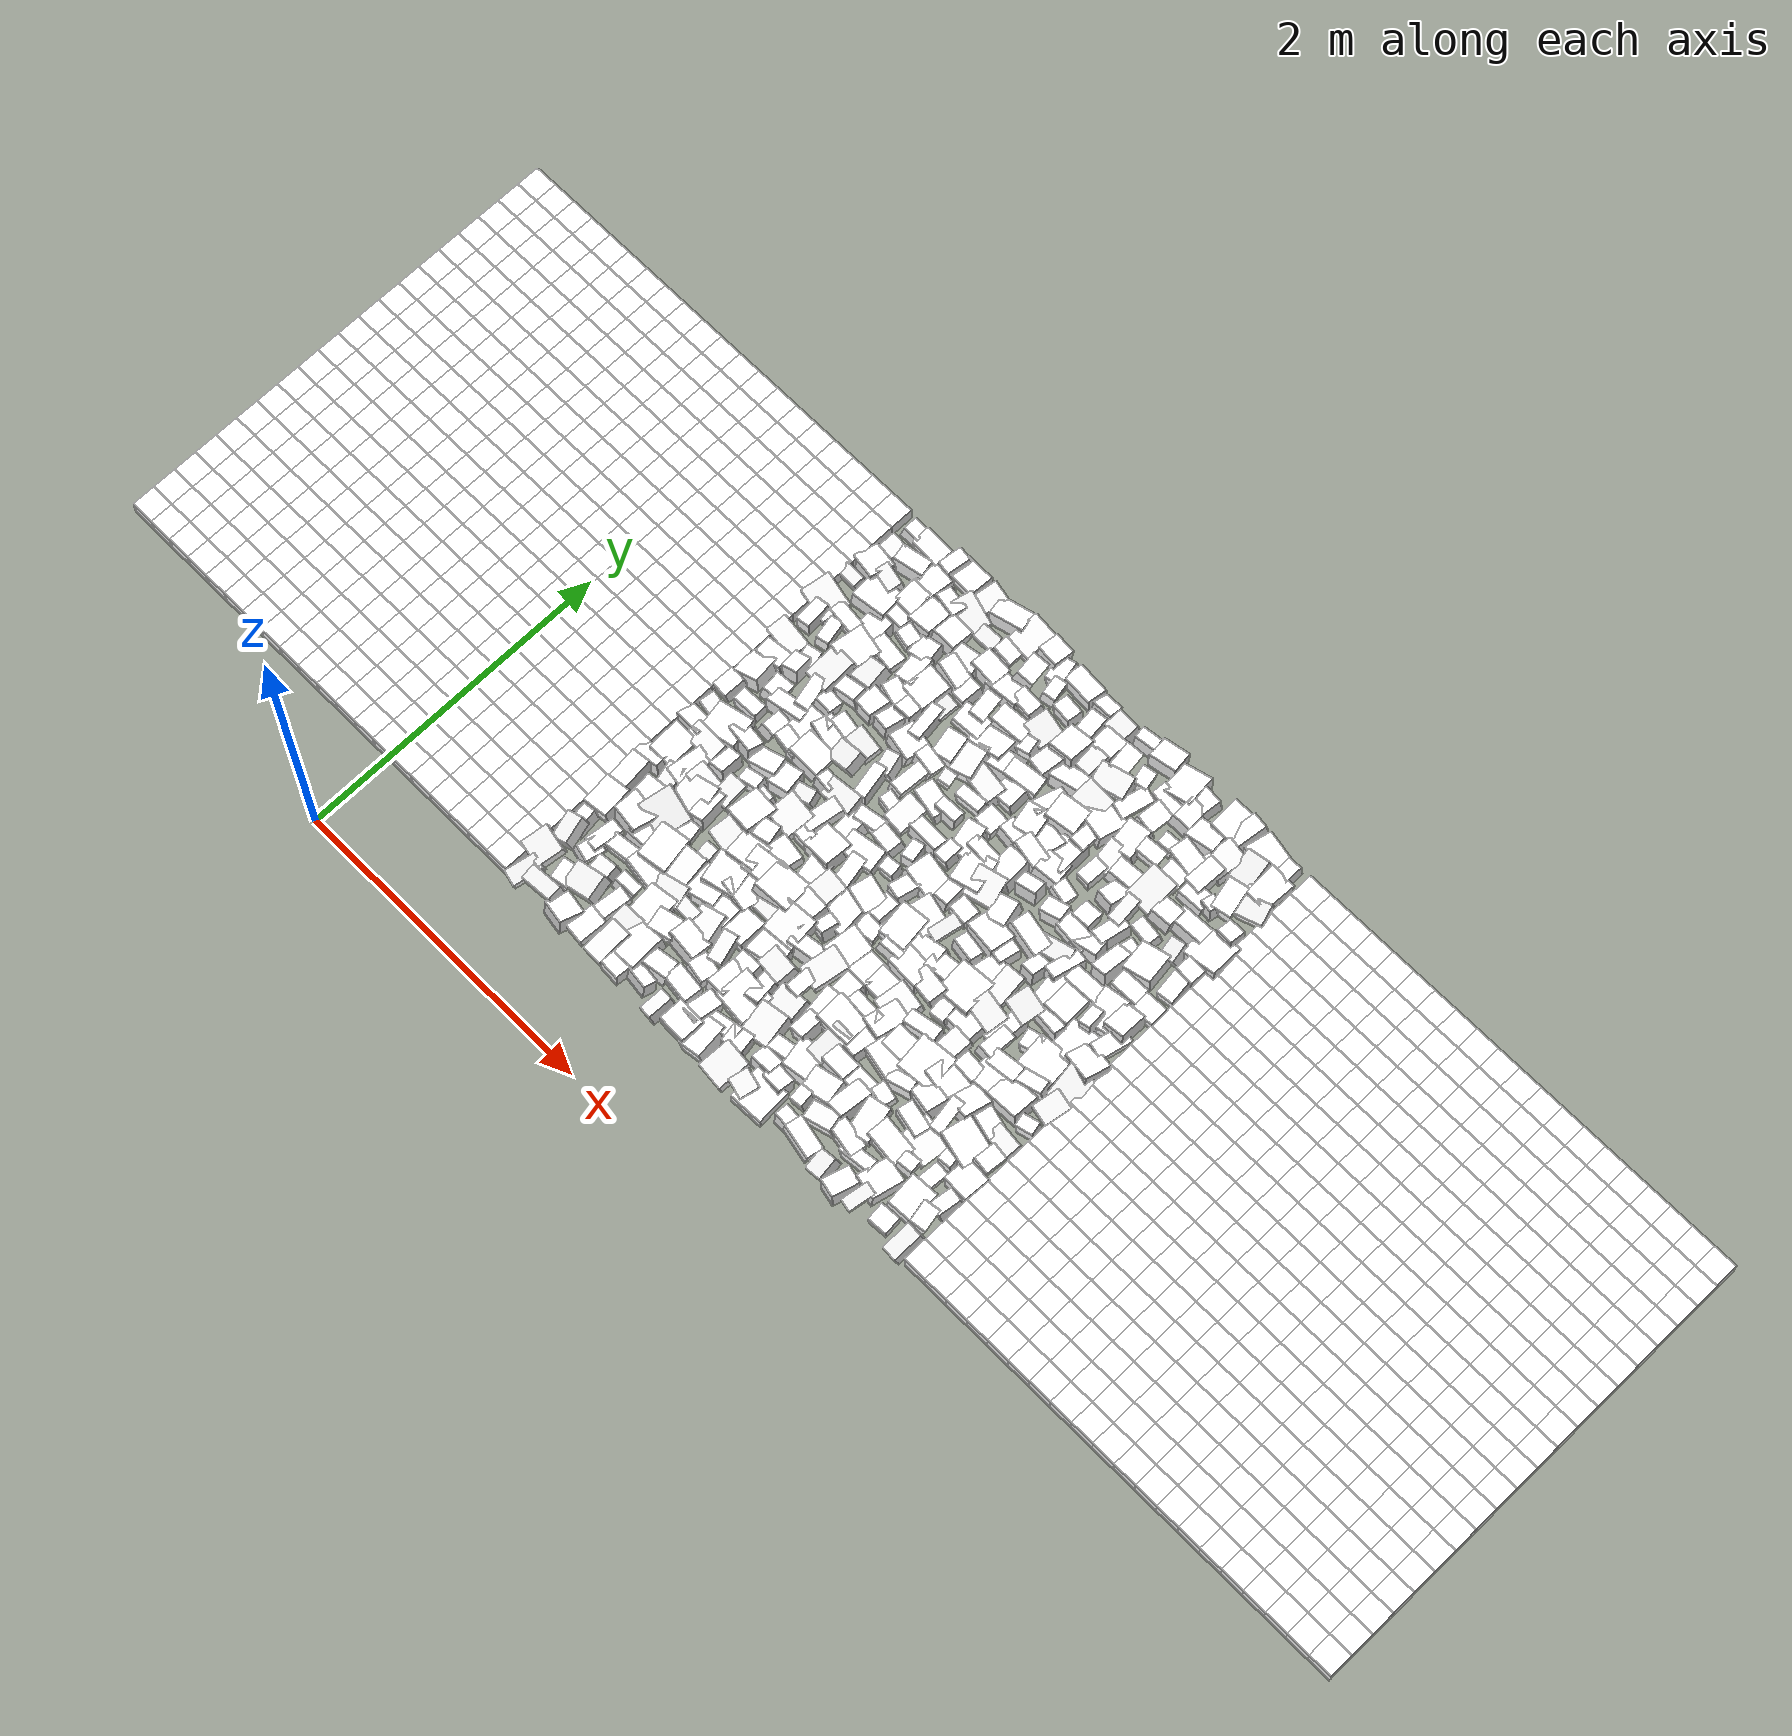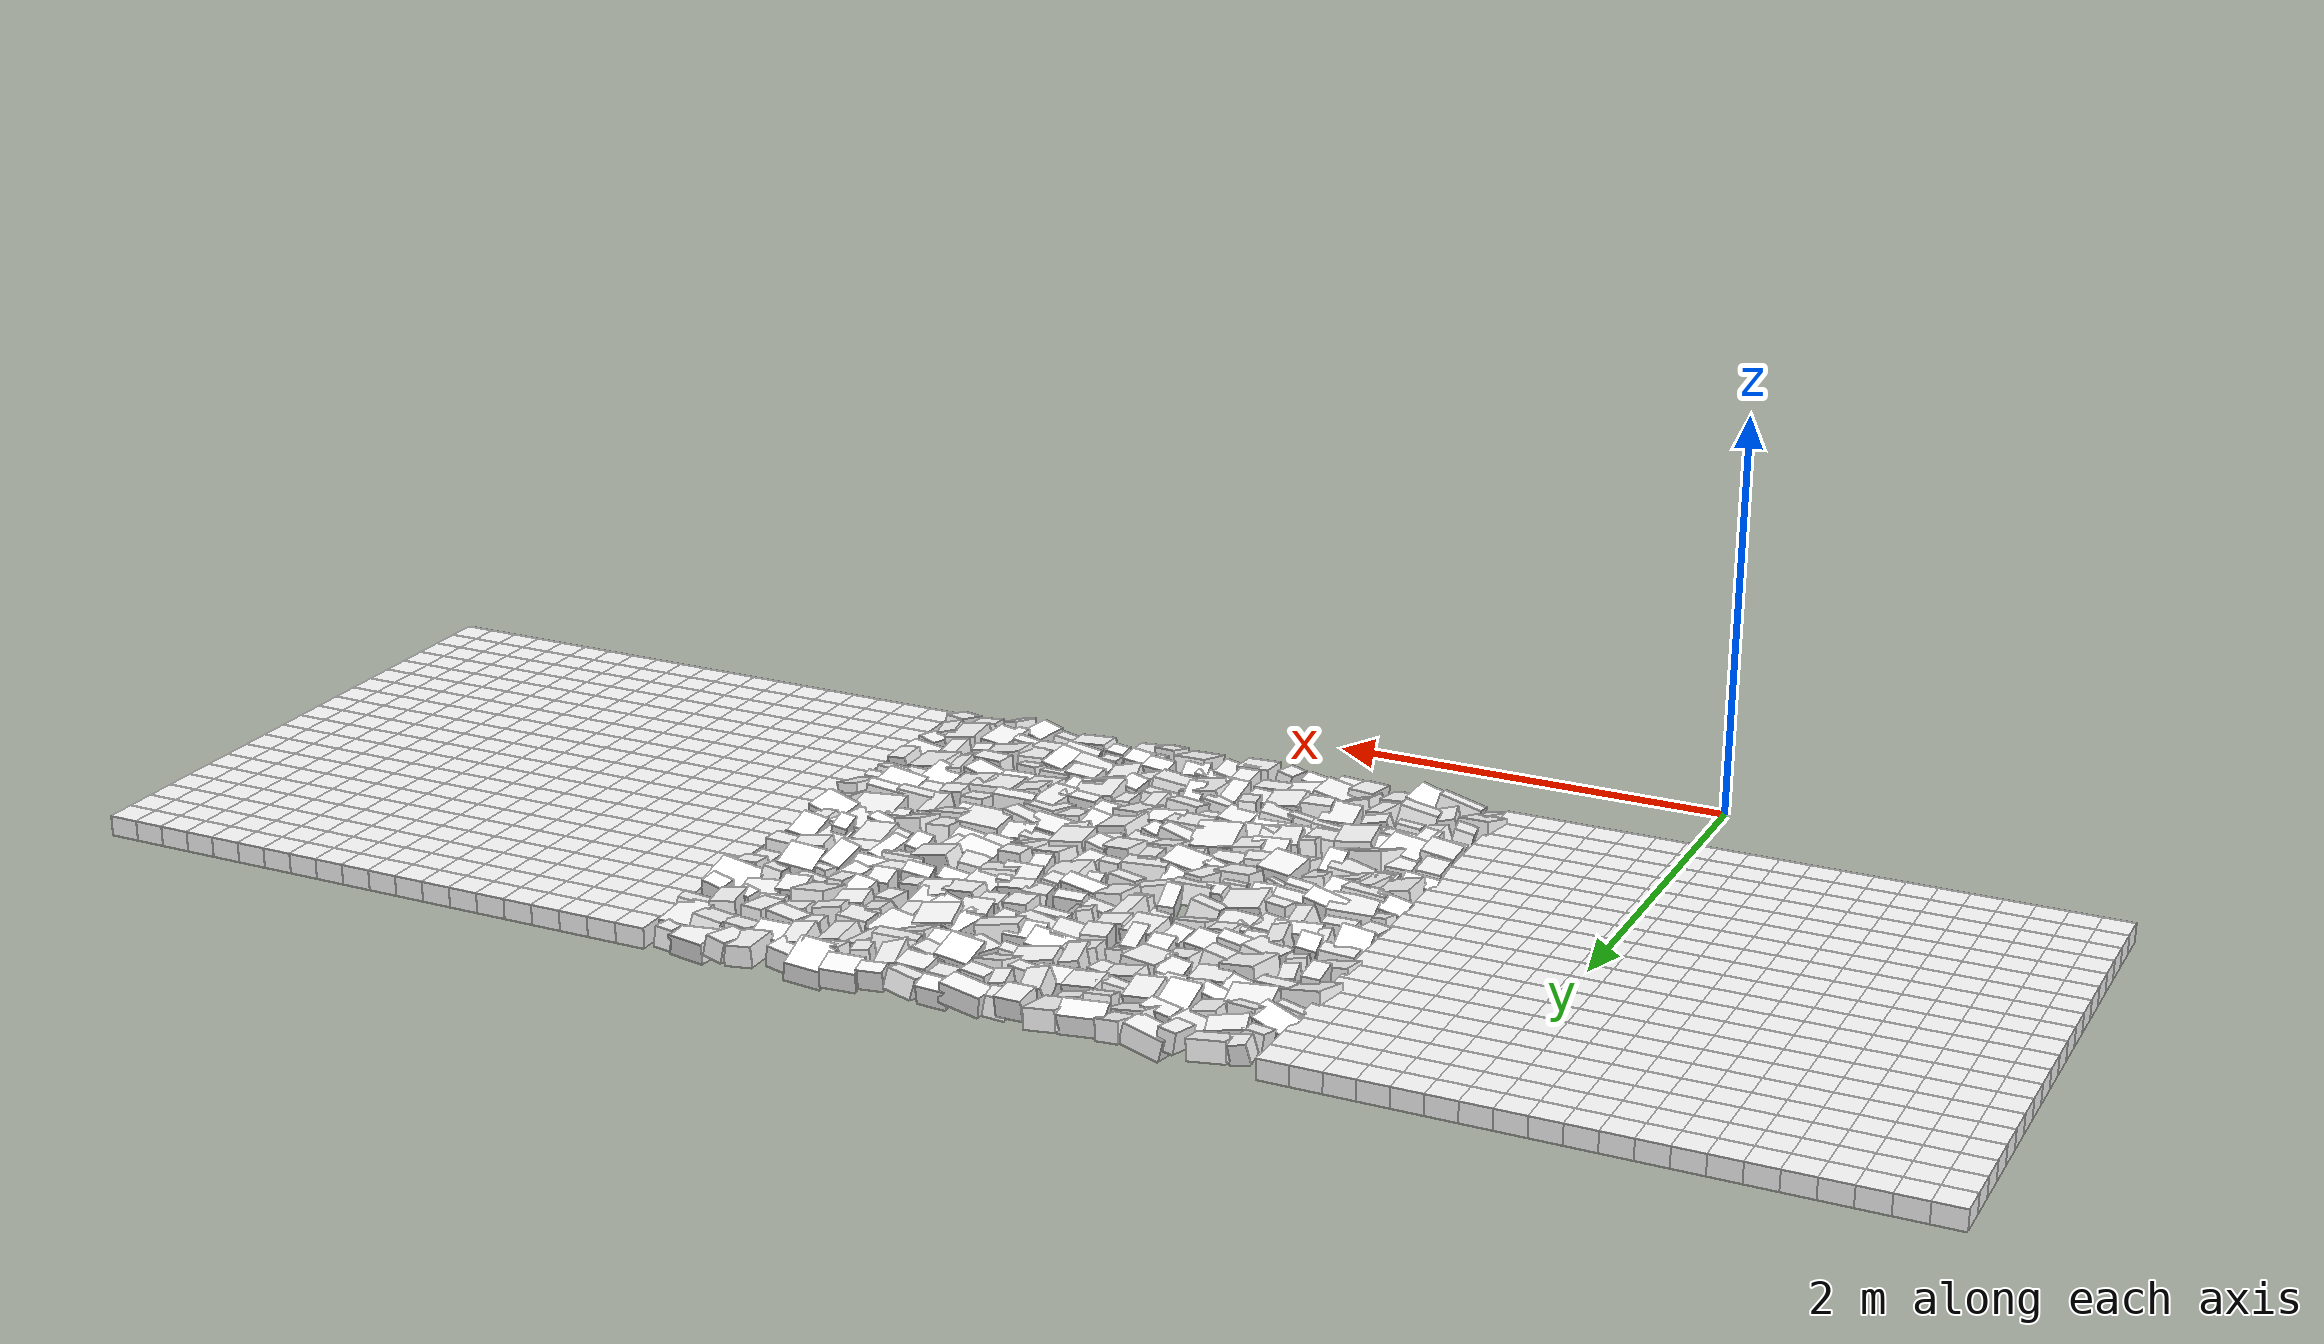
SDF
<sdf version="1.7">
  <world name="default">

    <!-- Need to be able to manipulate model state -->
    <plugin name="gazebo_ros_state" filename="libgazebo_ros_state.so">
      <ros>
        <namespace>/gazebo</namespace>
      </ros>

      <update_rate>1.0</update_rate>
    </plugin>

    <!-- Need to be able to manipulate model configuration -->
    <plugin name="gazebo_ros_properties" filename="libgazebo_ros_properties.so">
      <ros>
        <namespace>/gazebo</namespace>
      </ros>

      <update_rate>1.0</update_rate>
    </plugin>

    <physics type="ode">
    <max_step_size>0.001</max_step_size>
    <real_time_factor>1.0</real_time_factor>
    <real_time_update_rate>1000</real_time_update_rate>
    <gravity>0 0 -9.81</gravity>
        <ode>
            <solver>
            <type>quick</type>
            <iters>50</iters>
            <sor>1.3</sor>
            </solver>
            <constraints>
            <cfm>0.0</cfm>
            <erp>0.2</erp>
            <contact_max_correcting_vel>10.0</contact_max_correcting_vel>
            <contact_surface_layer>0.001</contact_surface_layer>
            </constraints>
        </ode>
    </physics>

    <scene>
    <sky>
        <clouds>
            <speed>12</speed>
        </clouds>
    </sky>
    </scene>
    <!-- A global light source -->
    <include>
        <uri>model://sun</uri>
    </include>
    <!-- A ground plane -->
    <model name="static_environment">
  <static>true</static>
  <link name="region_0">
    <pose>-2.0 0.6 0.0 0.0 0.0 0.0</pose>
    <collision name="region_0_collision">
      <geometry>
        <box>
          <size>0.15 0.15 0.1</size>
        </box>
      </geometry>
      <surface>
        <friction>
          <ode>
            <mu>1.0</mu>
            <mu2>1.0</mu2>
          </ode>
        </friction>
      </surface>
    </collision>
    <visual name="region_0_visual">
      <geometry>
        <box>
          <size>0.15 0.15 0.1</size>
        </box>
      </geometry>
      <material>
        <ambient>1.0 1.0 1.0 1.0</ambient>
        <diffuse>1.0 1.0 1.0 1.0</diffuse>
      </material>
    </visual>
  </link>
  <link name="region_1">
    <pose>-1.85 0.6 0.0 0.0 0.0 0.0</pose>
    <collision name="region_1_collision">
      <geometry>
        <box>
          <size>0.15 0.15 0.1</size>
        </box>
      </geometry>
      <surface>
        <friction>
          <ode>
            <mu>1.0</mu>
            <mu2>1.0</mu2>
          </ode>
        </friction>
      </surface>
    </collision>
    <visual name="region_1_visual">
      <geometry>
        <box>
          <size>0.15 0.15 0.1</size>
        </box>
      </geometry>
      <material>
        <ambient>1.0 1.0 1.0 1.0</ambient>
        <diffuse>1.0 1.0 1.0 1.0</diffuse>
      </material>
    </visual>
  </link>
  <link name="region_2">
    <pose>-1.7 0.6 0.0 0.0 0.0 0.0</pose>
    <collision name="region_2_collision">
      <geometry>
        <box>
          <size>0.15 0.15 0.1</size>
        </box>
      </geometry>
      <surface>
        <friction>
          <ode>
            <mu>1.0</mu>
            <mu2>1.0</mu2>
          </ode>
        </friction>
      </surface>
    </collision>
    <visual name="region_2_visual">
      <geometry>
        <box>
          <size>0.15 0.15 0.1</size>
        </box>
      </geometry>
      <material>
        <ambient>1.0 1.0 1.0 1.0</ambient>
        <diffuse>1.0 1.0 1.0 1.0</diffuse>
      </material>
    </visual>
  </link>
  <link name="region_3">
    <pose>-1.55 0.6 0.0 0.0 0.0 0.0</pose>
    <collision name="region_3_collision">
      <geometry>
        <box>
          <size>0.15 0.15 0.1</size>
        </box>
      </geometry>
      <surface>
        <friction>
          <ode>
            <mu>1.0</mu>
            <mu2>1.0</mu2>
          </ode>
        </friction>
      </surface>
    </collision>
    <visual name="region_3_visual">
      <geometry>
        <box>
          <size>0.15 0.15 0.1</size>
        </box>
      </geometry>
      <material>
        <ambient>1.0 1.0 1.0 1.0</ambient>
        <diffuse>1.0 1.0 1.0 1.0</diffuse>
      </material>
    </visual>
  </link>
  <link name="region_4">
    <pose>-1.4 0.6 0.0 0.0 0.0 0.0</pose>
    <collision name="region_4_collision">
      <geometry>
        <box>
          <size>0.15 0.15 0.1</size>
        </box>
      </geometry>
      <surface>
        <friction>
          <ode>
            <mu>1.0</mu>
            <mu2>1.0</mu2>
          </ode>
        </friction>
      </surface>
    </collision>
    <visual name="region_4_visual">
      <geometry>
        <box>
          <size>0.15 0.15 0.1</size>
        </box>
      </geometry>
      <material>
        <ambient>1.0 1.0 1.0 1.0</ambient>
        <diffuse>1.0 1.0 1.0 1.0</diffuse>
      </material>
    </visual>
  </link>
  <link name="region_5">
    <pose>-1.25 0.6 0.0 0.0 0.0 0.0</pose>
    <collision name="region_5_collision">
      <geometry>
        <box>
          <size>0.15 0.15 0.1</size>
        </box>
      </geometry>
      <surface>
        <friction>
          <ode>
            <mu>1.0</mu>
            <mu2>1.0</mu2>
          </ode>
        </friction>
      </surface>
    </collision>
    <visual name="region_5_visual">
      <geometry>
        <box>
          <size>0.15 0.15 0.1</size>
        </box>
      </geometry>
      <material>
        <ambient>1.0 1.0 1.0 1.0</ambient>
        <diffuse>1.0 1.0 1.0 1.0</diffuse>
      </material>
    </visual>
  </link>
  <link name="region_6">
    <pose>-1.1 0.6 0.0 0.0 0.0 0.0</pose>
    <collision name="region_6_collision">
      <geometry>
        <box>
          <size>0.15 0.15 0.1</size>
        </box>
      </geometry>
      <surface>
        <friction>
          <ode>
            <mu>1.0</mu>
            <mu2>1.0</mu2>
          </ode>
        </friction>
      </surface>
    </collision>
    <visual name="region_6_visual">
      <geometry>
        <box>
          <size>0.15 0.15 0.1</size>
        </box>
      </geometry>
      <material>
        <ambient>1.0 1.0 1.0 1.0</ambient>
        <diffuse>1.0 1.0 1.0 1.0</diffuse>
      </material>
    </visual>
  </link>
  <link name="region_7">
    <pose>-0.95 0.6 0.0 0.0 0.0 0.0</pose>
    <collision name="region_7_collision">
      <geometry>
        <box>
          <size>0.15 0.15 0.1</size>
        </box>
      </geometry>
      <surface>
        <friction>
          <ode>
            <mu>1.0</mu>
            <mu2>1.0</mu2>
          </ode>
        </friction>
      </surface>
    </collision>
    <visual name="region_7_visual">
      <geometry>
        <box>
          <size>0.15 0.15 0.1</size>
        </box>
      </geometry>
      <material>
        <ambient>1.0 1.0 1.0 1.0</ambient>
        <diffuse>1.0 1.0 1.0 1.0</diffuse>
      </material>
    </visual>
  </link>
  <link name="region_8">
    <pose>-0.8 0.6 0.0 0.0 0.0 0.0</pose>
    <collision name="region_8_collision">
      <geometry>
        <box>
          <size>0.15 0.15 0.1</size>
        </box>
      </geometry>
      <surface>
        <friction>
          <ode>
            <mu>1.0</mu>
            <mu2>1.0</mu2>
          </ode>
        </friction>
      </surface>
    </collision>
    <visual name="region_8_visual">
      <geometry>
        <box>
          <size>0.15 0.15 0.1</size>
        </box>
      </geometry>
      <material>
        <ambient>1.0 1.0 1.0 1.0</ambient>
        <diffuse>1.0 1.0 1.0 1.0</diffuse>
      </material>
    </visual>
  </link>
  <link name="region_9">
    <pose>-0.6500000000000001 0.6 0.0 0.0 0.0 0.0</pose>
    <collision name="region_9_collision">
      <geometry>
        <box>
          <size>0.15 0.15 0.1</size>
        </box>
      </geometry>
      <surface>
        <friction>
          <ode>
            <mu>1.0</mu>
            <mu2>1.0</mu2>
          </ode>
        </friction>
      </surface>
    </collision>
    <visual name="region_9_visual">
      <geometry>
        <box>
          <size>0.15 0.15 0.1</size>
        </box>
      </geometry>
      <material>
        <ambient>1.0 1.0 1.0 1.0</ambient>
        <diffuse>1.0 1.0 1.0 1.0</diffuse>
      </material>
    </visual>
  </link>
  <link name="region_10">
    <pose>-0.5000000000000002 0.6 0.0 0.0 0.0 0.0</pose>
    <collision name="region_10_collision">
      <geometry>
        <box>
          <size>0.15 0.15 0.1</size>
        </box>
      </geometry>
      <surface>
        <friction>
          <ode>
            <mu>1.0</mu>
            <mu2>1.0</mu2>
          </ode>
        </friction>
      </surface>
    </collision>
    <visual name="region_10_visual">
      <geometry>
        <box>
          <size>0.15 0.15 0.1</size>
        </box>
      </geometry>
      <material>
        <ambient>1.0 1.0 1.0 1.0</ambient>
        <diffuse>1.0 1.0 1.0 1.0</diffuse>
      </material>
    </visual>
  </link>
  <link name="region_11">
    <pose>-0.3500000000000003 0.6 0.0 0.0 0.0 0.0</pose>
    <collision name="region_11_collision">
      <geometry>
        <box>
          <size>0.15 0.15 0.1</size>
        </box>
      </geometry>
      <surface>
        <friction>
          <ode>
            <mu>1.0</mu>
            <mu2>1.0</mu2>
          </ode>
        </friction>
      </surface>
    </collision>
    <visual name="region_11_visual">
      <geometry>
        <box>
          <size>0.15 0.15 0.1</size>
        </box>
      </geometry>
      <material>
        <ambient>1.0 1.0 1.0 1.0</ambient>
        <diffuse>1.0 1.0 1.0 1.0</diffuse>
      </material>
    </visual>
  </link>
  <link name="region_12">
    <pose>-0.2000000000000004 0.6 0.0 0.0 0.0 0.0</pose>
    <collision name="region_12_collision">
      <geometry>
        <box>
          <size>0.15 0.15 0.1</size>
        </box>
      </geometry>
      <surface>
        <friction>
          <ode>
            <mu>1.0</mu>
            <mu2>1.0</mu2>
          </ode>
        </friction>
      </surface>
    </collision>
    <visual name="region_12_visual">
      <geometry>
        <box>
          <size>0.15 0.15 0.1</size>
        </box>
      </geometry>
      <material>
        <ambient>1.0 1.0 1.0 1.0</ambient>
        <diffuse>1.0 1.0 1.0 1.0</diffuse>
      </material>
    </visual>
  </link>
  <link name="region_13">
    <pose>-0.05000000000000049 0.6 0.0 0.0 0.0 0.0</pose>
    <collision name="region_13_collision">
      <geometry>
        <box>
          <size>0.15 0.15 0.1</size>
        </box>
      </geometry>
      <surface>
        <friction>
          <ode>
            <mu>1.0</mu>
            <mu2>1.0</mu2>
          </ode>
        </friction>
      </surface>
    </collision>
    <visual name="region_13_visual">
      <geometry>
        <box>
          <size>0.15 0.15 0.1</size>
        </box>
      </geometry>
      <material>
        <ambient>1.0 1.0 1.0 1.0</ambient>
        <diffuse>1.0 1.0 1.0 1.0</diffuse>
      </material>
    </visual>
  </link>
  <link name="region_14">
    <pose>0.09999999999999964 0.6 0.0 0.0 0.0 0.0</pose>
    <collision name="region_14_collision">
      <geometry>
        <box>
          <size>0.15 0.15 0.1</size>
        </box>
      </geometry>
      <surface>
        <friction>
          <ode>
            <mu>1.0</mu>
            <mu2>1.0</mu2>
          </ode>
        </friction>
      </surface>
    </collision>
    <visual name="region_14_visual">
      <geometry>
        <box>
          <size>0.15 0.15 0.1</size>
        </box>
      </geometry>
      <material>
        <ambient>1.0 1.0 1.0 1.0</ambient>
        <diffuse>1.0 1.0 1.0 1.0</diffuse>
      </material>
    </visual>
  </link>
  <link name="region_15">
    <pose>0.24999999999999956 0.6 0.0 0.0 0.0 0.0</pose>
    <collision name="region_15_collision">
      <geometry>
        <box>
          <size>0.15 0.15 0.1</size>
        </box>
      </geometry>
      <surface>
        <friction>
          <ode>
            <mu>1.0</mu>
            <mu2>1.0</mu2>
          </ode>
        </friction>
      </surface>
    </collision>
    <visual name="region_15_visual">
      <geometry>
        <box>
          <size>0.15 0.15 0.1</size>
        </box>
      </geometry>
      <material>
        <ambient>1.0 1.0 1.0 1.0</ambient>
        <diffuse>1.0 1.0 1.0 1.0</diffuse>
      </material>
    </visual>
  </link>
  <link name="region_16">
    <pose>0.39999999999999947 0.6 0.0 0.0 0.0 0.0</pose>
    <collision name="region_16_collision">
      <geometry>
        <box>
          <size>0.15 0.15 0.1</size>
        </box>
      </geometry>
      <surface>
        <friction>
          <ode>
            <mu>1.0</mu>
            <mu2>1.0</mu2>
          </ode>
        </friction>
      </surface>
    </collision>
    <visual name="region_16_visual">
      <geometry>
        <box>
          <size>0.15 0.15 0.1</size>
        </box>
      </geometry>
      <material>
        <ambient>1.0 1.0 1.0 1.0</ambient>
        <diffuse>1.0 1.0 1.0 1.0</diffuse>
      </material>
    </visual>
  </link>
  <link name="region_17">
    <pose>0.5499999999999994 0.6 0.0 0.0 0.0 0.0</pose>
    <collision name="region_17_collision">
      <geometry>
        <box>
          <size>0.15 0.15 0.1</size>
        </box>
      </geometry>
      <surface>
        <friction>
          <ode>
            <mu>1.0</mu>
            <mu2>1.0</mu2>
          </ode>
        </friction>
      </surface>
    </collision>
    <visual name="region_17_visual">
      <geometry>
        <box>
          <size>0.15 0.15 0.1</size>
        </box>
      </geometry>
      <material>
        <ambient>1.0 1.0 1.0 1.0</ambient>
        <diffuse>1.0 1.0 1.0 1.0</diffuse>
      </material>
    </visual>
  </link>
  <link name="region_18">
    <pose>0.6999999999999993 0.6 0.0 0.0 0.0 0.0</pose>
    <collision name="region_18_collision">
      <geometry>
        <box>
          <size>0.15 0.15 0.1</size>
        </box>
      </geometry>
      <surface>
        <friction>
          <ode>
            <mu>1.0</mu>
            <mu2>1.0</mu2>
          </ode>
        </friction>
      </surface>
    </collision>
    <visual name="region_18_visual">
      <geometry>
        <box>
          <size>0.15 0.15 0.1</size>
        </box>
      </geometry>
      <material>
        <ambient>1.0 1.0 1.0 1.0</ambient>
        <diffuse>1.0 1.0 1.0 1.0</diffuse>
      </material>
    </visual>
  </link>
  <link name="region_19">
    <pose>0.8499999999999992 0.6 0.0 0.0 0.0 0.0</pose>
    <collision name="region_19_collision">
      <geometry>
        <box>
          <size>0.15 0.15 0.1</size>
        </box>
      </geometry>
      <surface>
        <friction>
          <ode>
            <mu>1.0</mu>
            <mu2>1.0</mu2>
          </ode>
        </friction>
      </surface>
    </collision>
    <visual name="region_19_visual">
      <geometry>
        <box>
          <size>0.15 0.15 0.1</size>
        </box>
      </geometry>
      <material>
        <ambient>1.0 1.0 1.0 1.0</ambient>
        <diffuse>1.0 1.0 1.0 1.0</diffuse>
      </material>
    </visual>
  </link>
  <link name="region_20">
    <pose>-2.0 0.75 0.0 0.0 0.0 0.0</pose>
    <collision name="region_20_collision">
      <geometry>
        <box>
          <size>0.15 0.15 0.1</size>
        </box>
      </geometry>
      <surface>
        <friction>
          <ode>
            <mu>1.0</mu>
            <mu2>1.0</mu2>
          </ode>
        </friction>
      </surface>
    </collision>
    <visual name="region_20_visual">
      <geometry>
        <box>
          <size>0.15 0.15 0.1</size>
        </box>
      </geometry>
      <material>
        <ambient>1.0 1.0 1.0 1.0</ambient>
        <diffuse>1.0 1.0 1.0 1.0</diffuse>
      </material>
    </visual>
  </link>
  <link name="region_21">
    <pose>-1.85 0.75 0.0 0.0 0.0 0.0</pose>
    <collision name="region_21_collision">
      <geometry>
        <box>
          <size>0.15 0.15 0.1</size>
        </box>
      </geometry>
      <surface>
        <friction>
          <ode>
            <mu>1.0</mu>
            <mu2>1.0</mu2>
          </ode>
        </friction>
      </surface>
    </collision>
    <visual name="region_21_visual">
      <geometry>
        <box>
          <size>0.15 0.15 0.1</size>
        </box>
      </geometry>
      <material>
        <ambient>1.0 1.0 1.0 1.0</ambient>
        <diffuse>1.0 1.0 1.0 1.0</diffuse>
      </material>
    </visual>
  </link>
  <link name="region_22">
    <pose>-1.7 0.75 0.0 0.0 0.0 0.0</pose>
    <collision name="region_22_collision">
      <geometry>
        <box>
          <size>0.15 0.15 0.1</size>
        </box>
      </geometry>
      <surface>
        <friction>
          <ode>
            <mu>1.0</mu>
            <mu2>1.0</mu2>
          </ode>
        </friction>
      </surface>
    </collision>
    <visual name="region_22_visual">
      <geometry>
        <box>
          <size>0.15 0.15 0.1</size>
        </box>
      </geometry>
      <material>
        <ambient>1.0 1.0 1.0 1.0</ambient>
        <diffuse>1.0 1.0 1.0 1.0</diffuse>
      </material>
    </visual>
  </link>
  <link name="region_23">
    <pose>-1.55 0.75 0.0 0.0 0.0 0.0</pose>
    <collision name="region_23_collision">
      <geometry>
        <box>
          <size>0.15 0.15 0.1</size>
        </box>
      </geometry>
      <surface>
        <friction>
          <ode>
            <mu>1.0</mu>
            <mu2>1.0</mu2>
          </ode>
        </friction>
      </surface>
    </collision>
    <visual name="region_23_visual">
      <geometry>
        <box>
          <size>0.15 0.15 0.1</size>
        </box>
      </geometry>
      <material>
        <ambient>1.0 1.0 1.0 1.0</ambient>
        <diffuse>1.0 1.0 1.0 1.0</diffuse>
      </material>
    </visual>
  </link>
  <link name="region_24">
    <pose>-1.4 0.75 0.0 0.0 0.0 0.0</pose>
    <collision name="region_24_collision">
      <geometry>
        <box>
          <size>0.15 0.15 0.1</size>
        </box>
      </geometry>
      <surface>
        <friction>
          <ode>
            <mu>1.0</mu>
            <mu2>1.0</mu2>
          </ode>
        </friction>
      </surface>
    </collision>
    <visual name="region_24_visual">
      <geometry>
        <box>
          <size>0.15 0.15 0.1</size>
        </box>
      </geometry>
      <material>
        <ambient>1.0 1.0 1.0 1.0</ambient>
        <diffuse>1.0 1.0 1.0 1.0</diffuse>
      </material>
    </visual>
  </link>
  <link name="region_25">
    <pose>-1.25 0.75 0.0 0.0 0.0 0.0</pose>
    <collision name="region_25_collision">
      <geometry>
        <box>
          <size>0.15 0.15 0.1</size>
        </box>
      </geometry>
      <surface>
        <friction>
          <ode>
            <mu>1.0</mu>
            <mu2>1.0</mu2>
          </ode>
        </friction>
      </surface>
    </collision>
    <visual name="region_25_visual">
      <geometry>
        <box>
          <size>0.15 0.15 0.1</size>
        </box>
      </geometry>
      <material>
        <ambient>1.0 1.0 1.0 1.0</ambient>
        <diffuse>1.0 1.0 1.0 1.0</diffuse>
      </material>
    </visual>
  </link>
  <link name="region_26">
    <pose>-1.1 0.75 0.0 0.0 0.0 0.0</pose>
    <collision name="region_26_collision">
      <geometry>
        <box>
          <size>0.15 0.15 0.1</size>
        </box>
      </geometry>
      <surface>
        <friction>
          <ode>
            <mu>1.0</mu>
            <mu2>1.0</mu2>
          </ode>
        </friction>
      </surface>
    </collision>
    <visual name="region_26_visual">
      <geometry>
        <box>
          <size>0.15 0.15 0.1</size>
        </box>
      </geometry>
      <material>
        <ambient>1.0 1.0 1.0 1.0</ambient>
        <diffuse>1.0 1.0 1.0 1.0</diffuse>
      </material>
    </visual>
  </link>
  <link name="region_27">
    <pose>-0.95 0.75 0.0 0.0 0.0 0.0</pose>
    <collision name="region_27_collision">
      <geometry>
        <box>
          <size>0.15 0.15 0.1</size>
        </box>
      </geometry>
      <surface>
        <friction>
          <ode>
            <mu>1.0</mu>
            <mu2>1.0</mu2>
          </ode>
        </friction>
      </surface>
    </collision>
    <visual name="region_27_visual">
      <geometry>
        <box>
          <size>0.15 0.15 0.1</size>
        </box>
      </geometry>
      <material>
        <ambient>1.0 1.0 1.0 1.0</ambient>
        <diffuse>1.0 1.0 1.0 1.0</diffuse>
      </material>
    </visual>
  </link>
  <link name="region_28">
    <pose>-0.8 0.75 0.0 0.0 0.0 0.0</pose>
    <collision name="region_28_collision">
      <geometry>
        <box>
          <size>0.15 0.15 0.1</size>
        </box>
      </geometry>
      <surface>
        <friction>
          <ode>
            <mu>1.0</mu>
            <mu2>1.0</mu2>
          </ode>
        </friction>
      </surface>
    </collision>
    <visual name="region_28_visual">
      <geometry>
        <box>
          <size>0.15 0.15 0.1</size>
        </box>
      </geometry>
      <material>
        <ambient>1.0 1.0 1.0 1.0</ambient>
        <diffuse>1.0 1.0 1.0 1.0</diffuse>
      </material>
    </visual>
  </link>
  <link name="region_29">
    <pose>-0.6500000000000001 0.75 0.0 0.0 0.0 0.0</pose>
    <collision name="region_29_collision">
      <geometry>
        <box>
          <size>0.15 0.15 0.1</size>
        </box>
      </geometry>
      <surface>
        <friction>
          <ode>
            <mu>1.0</mu>
            <mu2>1.0</mu2>
          </ode>
        </friction>
      </surface>
    </collision>
    <visual name="region_29_visual">
      <geometry>
        <box>
          <size>0.15 0.15 0.1</size>
        </box>
      </geometry>
      <material>
        <ambient>1.0 1.0 1.0 1.0</ambient>
        <diffuse>1.0 1.0 1.0 1.0</diffuse>
      </material>
    </visual>
  </link>
  <link name="region_30">
    <pose>-0.5000000000000002 0.75 0.0 0.0 0.0 0.0</pose>
    <collision name="region_30_collision">
      <geometry>
        <box>
          <size>0.15 0.15 0.1</size>
        </box>
      </geometry>
      <surface>
        <friction>
          <ode>
            <mu>1.0</mu>
            <mu2>1.0</mu2>
          </ode>
        </friction>
      </surface>
    </collision>
    <visual name="region_30_visual">
      <geometry>
        <box>
          <size>0.15 0.15 0.1</size>
        </box>
      </geometry>
      <material>
        <ambient>1.0 1.0 1.0 1.0</ambient>
        <diffuse>1.0 1.0 1.0 1.0</diffuse>
      </material>
    </visual>
  </link>
  <link name="region_31">
    <pose>-0.3500000000000003 0.75 0.0 0.0 0.0 0.0</pose>
    <collision name="region_31_collision">
      <geometry>
        <box>
          <size>0.15 0.15 0.1</size>
        </box>
      </geometry>
      <surface>
        <friction>
          <ode>
            <mu>1.0</mu>
            <mu2>1.0</mu2>
          </ode>
        </friction>
      </surface>
    </collision>
    <visual name="region_31_visual">
      <geometry>
        <box>
          <size>0.15 0.15 0.1</size>
        </box>
      </geometry>
      <material>
        <ambient>1.0 1.0 1.0 1.0</ambient>
        <diffuse>1.0 1.0 1.0 1.0</diffuse>
      </material>
    </visual>
  </link>
  <link name="region_32">
    <pose>-0.2000000000000004 0.75 0.0 0.0 0.0 0.0</pose>
    <collision name="region_32_collision">
      <geometry>
        <box>
          <size>0.15 0.15 0.1</size>
        </box>
      </geometry>
      <surface>
        <friction>
          <ode>
            <mu>1.0</mu>
            <mu2>1.0</mu2>
          </ode>
        </friction>
      </surface>
    </collision>
    <visual name="region_32_visual">
      <geometry>
        <box>
          <size>0.15 0.15 0.1</size>
        </box>
      </geometry>
      <material>
        <ambient>1.0 1.0 1.0 1.0</ambient>
        <diffuse>1.0 1.0 1.0 1.0</diffuse>
      </material>
    </visual>
  </link>
  <link name="region_33">
    <pose>-0.05000000000000049 0.75 0.0 0.0 0.0 0.0</pose>
    <collision name="region_33_collision">
      <geometry>
        <box>
          <size>0.15 0.15 0.1</size>
        </box>
      </geometry>
      <surface>
        <friction>
          <ode>
            <mu>1.0</mu>
            <mu2>1.0</mu2>
          </ode>
        </friction>
      </surface>
    </collision>
    <visual name="region_33_visual">
      <geometry>
        <box>
          <size>0.15 0.15 0.1</size>
        </box>
      </geometry>
      <material>
        <ambient>1.0 1.0 1.0 1.0</ambient>
        <diffuse>1.0 1.0 1.0 1.0</diffuse>
      </material>
    </visual>
  </link>
  <link name="region_34">
    <pose>0.09999999999999964 0.75 0.0 0.0 0.0 0.0</pose>
    <collision name="region_34_collision">
      <geometry>
        <box>
          <size>0.15 0.15 0.1</size>
        </box>
      </geometry>
      <surface>
        <friction>
          <ode>
            <mu>1.0</mu>
            <mu2>1.0</mu2>
          </ode>
        </friction>
      </surface>
    </collision>
    <visual name="region_34_visual">
      <geometry>
        <box>
          <size>0.15 0.15 0.1</size>
        </box>
      </geometry>
      <material>
        <ambient>1.0 1.0 1.0 1.0</ambient>
        <diffuse>1.0 1.0 1.0 1.0</diffuse>
      </material>
    </visual>
  </link>
  <link name="region_35">
    <pose>0.24999999999999956 0.75 0.0 0.0 0.0 0.0</pose>
    <collision name="region_35_collision">
      <geometry>
        <box>
          <size>0.15 0.15 0.1</size>
        </box>
      </geometry>
      <surface>
        <friction>
          <ode>
            <mu>1.0</mu>
            <mu2>1.0</mu2>
          </ode>
        </friction>
      </surface>
    </collision>
    <visual name="region_35_visual">
      <geometry>
        <box>
          <size>0.15 0.15 0.1</size>
        </box>
      </geometry>
      <material>
        <ambient>1.0 1.0 1.0 1.0</ambient>
        <diffuse>1.0 1.0 1.0 1.0</diffuse>
      </material>
    </visual>
  </link>
  <link name="region_36">
    <pose>0.39999999999999947 0.75 0.0 0.0 0.0 0.0</pose>
    <collision name="region_36_collision">
      <geometry>
        <box>
          <size>0.15 0.15 0.1</size>
        </box>
      </geometry>
      <surface>
        <friction>
          <ode>
            <mu>1.0</mu>
            <mu2>1.0</mu2>
          </ode>
        </friction>
      </surface>
    </collision>
    <visual name="region_36_visual">
      <geometry>
        <box>
          <size>0.15 0.15 0.1</size>
        </box>
      </geometry>
      <material>
        <ambient>1.0 1.0 1.0 1.0</ambient>
        <diffuse>1.0 1.0 1.0 1.0</diffuse>
      </material>
    </visual>
  </link>
  <link name="region_37">
    <pose>0.5499999999999994 0.75 0.0 0.0 0.0 0.0</pose>
    <collision name="region_37_collision">
      <geometry>
        <box>
          <size>0.15 0.15 0.1</size>
        </box>
      </geometry>
      <surface>
        <friction>
          <ode>
            <mu>1.0</mu>
            <mu2>1.0</mu2>
          </ode>
        </friction>
      </surface>
    </collision>
    <visual name="region_37_visual">
      <geometry>
        <box>
          <size>0.15 0.15 0.1</size>
        </box>
      </geometry>
      <material>
        <ambient>1.0 1.0 1.0 1.0</ambient>
        <diffuse>1.0 1.0 1.0 1.0</diffuse>
      </material>
    </visual>
  </link>
  <link name="region_38">
    <pose>0.6999999999999993 0.75 0.0 0.0 0.0 0.0</pose>
    <collision name="region_38_collision">
      <geometry>
        <box>
          <size>0.15 0.15 0.1</size>
        </box>
      </geometry>
      <surface>
        <friction>
          <ode>
            <mu>1.0</mu>
            <mu2>1.0</mu2>
          </ode>
        </friction>
      </surface>
    </collision>
    <visual name="region_38_visual">
      <geometry>
        <box>
          <size>0.15 0.15 0.1</size>
        </box>
      </geometry>
      <material>
        <ambient>1.0 1.0 1.0 1.0</ambient>
        <diffuse>1.0 1.0 1.0 1.0</diffuse>
      </material>
    </visual>
  </link>
  <link name="region_39">
    <pose>0.8499999999999992 0.75 0.0 0.0 0.0 0.0</pose>
    <collision name="region_39_collision">
      <geometry>
        <box>
          <size>0.15 0.15 0.1</size>
        </box>
      </geometry>
      <surface>
        <friction>
          <ode>
            <mu>1.0</mu>
            <mu2>1.0</mu2>
          </ode>
        </friction>
      </surface>
    </collision>
    <visual name="region_39_visual">
      <geometry>
        <box>
          <size>0.15 0.15 0.1</size>
        </box>
      </geometry>
      <material>
        <ambient>1.0 1.0 1.0 1.0</ambient>
        <diffuse>1.0 1.0 1.0 1.0</diffuse>
      </material>
    </visual>
  </link>
  <link name="region_40">
    <pose>-2.0 0.8999999999999999 0.0 0.0 0.0 0.0</pose>
    <collision name="region_40_collision">
      <geometry>
        <box>
          <size>0.15 0.15 0.1</size>
        </box>
      </geometry>
      <surface>
        <friction>
          <ode>
            <mu>1.0</mu>
            <mu2>1.0</mu2>
          </ode>
        </friction>
      </surface>
    </collision>
    <visual name="region_40_visual">
      <geometry>
        <box>
          <size>0.15 0.15 0.1</size>
        </box>
      </geometry>
      <material>
        <ambient>1.0 1.0 1.0 1.0</ambient>
        <diffuse>1.0 1.0 1.0 1.0</diffuse>
      </material>
    </visual>
  </link>
  <link name="region_41">
    <pose>-1.85 0.8999999999999999 0.0 0.0 0.0 0.0</pose>
    <collision name="region_41_collision">
      <geometry>
        <box>
          <size>0.15 0.15 0.1</size>
        </box>
      </geometry>
      <surface>
        <friction>
          <ode>
            <mu>1.0</mu>
            <mu2>1.0</mu2>
          </ode>
        </friction>
      </surface>
    </collision>
    <visual name="region_41_visual">
      <geometry>
        <box>
          <size>0.15 0.15 0.1</size>
        </box>
      </geometry>
      <material>
        <ambient>1.0 1.0 1.0 1.0</ambient>
        <diffuse>1.0 1.0 1.0 1.0</diffuse>
      </material>
    </visual>
  </link>
  <link name="region_42">
    <pose>-1.7 0.8999999999999999 0.0 0.0 0.0 0.0</pose>
    <collision name="region_42_collision">
      <geometry>
        <box>
          <size>0.15 0.15 0.1</size>
        </box>
      </geometry>
      <surface>
        <friction>
          <ode>
            <mu>1.0</mu>
            <mu2>1.0</mu2>
          </ode>
        </friction>
      </surface>
    </collision>
    <visual name="region_42_visual">
      <geometry>
        <box>
          <size>0.15 0.15 0.1</size>
        </box>
      </geometry>
      <material>
        <ambient>1.0 1.0 1.0 1.0</ambient>
        <diffuse>1.0 1.0 1.0 1.0</diffuse>
      </material>
    </visual>
  </link>
  <link name="region_43">
    <pose>-1.55 0.8999999999999999 0.0 0.0 0.0 0.0</pose>
    <collision name="region_43_collision">
      <geometry>
        <box>
          <size>0.15 0.15 0.1</size>
        </box>
      </geometry>
      <surface>
        <friction>
          <ode>
            <mu>1.0</mu>
            <mu2>1.0</mu2>
          </ode>
        </friction>
      </surface>
    </collision>
    <visual name="region_43_visual">
      <geometry>
        <box>
          <size>0.15 0.15 0.1</size>
        </box>
      </geometry>
      <material>
        <ambient>1.0 1.0 1.0 1.0</ambient>
        <diffuse>1.0 1.0 1.0 1.0</diffuse>
      </material>
    </visual>
  </link>
  <link name="region_44">
    <pose>-1.4 0.8999999999999999 0.0 0.0 0.0 0.0</pose>
    <collision name="region_44_collision">
      <geometry>
        <box>
          <size>0.15 0.15 0.1</size>
        </box>
      </geometry>
      <surface>
        <friction>
          <ode>
            <mu>1.0</mu>
            <mu2>1.0</mu2>
          </ode>
        </friction>
      </surface>
    </collision>
    <visual name="region_44_visual">
      <geometry>
        <box>
          <size>0.15 0.15 0.1</size>
        </box>
      </geometry>
      <material>
        <ambient>1.0 1.0 1.0 1.0</ambient>
        <diffuse>1.0 1.0 1.0 1.0</diffuse>
      </material>
    </visual>
  </link>
  <link name="region_45">
    <pose>-1.25 0.8999999999999999 0.0 0.0 0.0 0.0</pose>
    <collision name="region_45_collision">
      <geometry>
        <box>
          <size>0.15 0.15 0.1</size>
        </box>
      </geometry>
      <surface>
        <friction>
          <ode>
            <mu>1.0</mu>
            <mu2>1.0</mu2>
          </ode>
        </friction>
      </surface>
    </collision>
    <visual name="region_45_visual">
      <geometry>
        <box>
          <size>0.15 0.15 0.1</size>
        </box>
      </geometry>
      <material>
        <ambient>1.0 1.0 1.0 1.0</ambient>
        <diffuse>1.0 1.0 1.0 1.0</diffuse>
      </material>
    </visual>
  </link>
  <link name="region_46">
    <pose>-1.1 0.8999999999999999 0.0 0.0 0.0 0.0</pose>
    <collision name="region_46_collision">
      <geometry>
        <box>
          <size>0.15 0.15 0.1</size>
        </box>
      </geometry>
      <surface>
        <friction>
          <ode>
            <mu>1.0</mu>
            <mu2>1.0</mu2>
          </ode>
        </friction>
      </surface>
    </collision>
    <visual name="region_46_visual">
      <geometry>
        <box>
          <size>0.15 0.15 0.1</size>
        </box>
      </geometry>
      <material>
        <ambient>1.0 1.0 1.0 1.0</ambient>
        <diffuse>1.0 1.0 1.0 1.0</diffuse>
      </material>
    </visual>
  </link>
  <link name="region_47">
    <pose>-0.95 0.8999999999999999 0.0 0.0 0.0 0.0</pose>
    <collision name="region_47_collision">
      <geometry>
        <box>
          <size>0.15 0.15 0.1</size>
        </box>
      </geometry>
      <surface>
        <friction>
          <ode>
            <mu>1.0</mu>
            <mu2>1.0</mu2>
          </ode>
        </friction>
      </surface>
    </collision>
    <visual name="region_47_visual">
      <geometry>
        <box>
          <size>0.15 0.15 0.1</size>
        </box>
      </geometry>
      <material>
        <ambient>1.0 1.0 1.0 1.0</ambient>
        <diffuse>1.0 1.0 1.0 1.0</diffuse>
      </material>
    </visual>
  </link>
  <link name="region_48">
    <pose>-0.8 0.8999999999999999 0.0 0.0 0.0 0.0</pose>
    <collision name="region_48_collision">
      <geometry>
        <box>
          <size>0.15 0.15 0.1</size>
        </box>
      </geometry>
      <surface>
        <friction>
          <ode>
            <mu>1.0</mu>
            <mu2>1.0</mu2>
          </ode>
        </friction>
      </surface>
    </collision>
    <visual name="region_48_visual">
      <geometry>
        <box>
          <size>0.15 0.15 0.1</size>
        </box>
      </geometry>
      <material>
        <ambient>1.0 1.0 1.0 1.0</ambient>
        <diffuse>1.0 1.0 1.0 1.0</diffuse>
      </material>
    </visual>
  </link>
  <link name="region_49">
    <pose>-0.6500000000000001 0.8999999999999999 0.0 0.0 0.0 0.0</pose>
    <collision name="region_49_collision">
      <geometry>
        <box>
          <size>0.15 0.15 0.1</size>
        </box>
      </geometry>
      <surface>
        <friction>
          <ode>
            <mu>1.0</mu>
            <mu2>1.0</mu2>
          </ode>
        </friction>
      </surface>
    </collision>
    <visual name="region_49_visual">
      <geometry>
        <box>
          <size>0.15 0.15 0.1</size>
        </box>
      </geometry>
      <material>
        <ambient>1.0 1.0 1.0 1.0</ambient>
        <diffuse>1.0 1.0 1.0 1.0</diffuse>
      </material>
    </visual>
  </link>
  <link name="region_50">
    <pose>-0.5000000000000002 0.8999999999999999 0.0 0.0 0.0 0.0</pose>
    <collision name="region_50_collision">
      <geometry>
        <box>
          <size>0.15 0.15 0.1</size>
        </box>
      </geometry>
      <surface>
        <friction>
          <ode>
            <mu>1.0</mu>
            <mu2>1.0</mu2>
          </ode>
        </friction>
      </surface>
    </collision>
    <visual name="region_50_visual">
      <geometry>
        <box>
          <size>0.15 0.15 0.1</size>
        </box>
      </geometry>
      <material>
        <ambient>1.0 1.0 1.0 1.0</ambient>
        <diffuse>1.0 1.0 1.0 1.0</diffuse>
      </material>
    </visual>
  </link>
  <link name="region_51">
    <pose>-0.3500000000000003 0.8999999999999999 0.0 0.0 0.0 0.0</pose>
    <collision name="region_51_collision">
      <geometry>
        <box>
          <size>0.15 0.15 0.1</size>
        </box>
      </geometry>
      <surface>
        <friction>
          <ode>
            <mu>1.0</mu>
            <mu2>1.0</mu2>
          </ode>
        </friction>
      </surface>
    </collision>
    <visual name="region_51_visual">
      <geometry>
        <box>
          <size>0.15 0.15 0.1</size>
        </box>
      </geometry>
      <material>
        <ambient>1.0 1.0 1.0 1.0</ambient>
        <diffuse>1.0 1.0 1.0 1.0</diffuse>
      </material>
    </visual>
  </link>
  <link name="region_52">
    <pose>-0.2000000000000004 0.8999999999999999 0.0 0.0 0.0 0.0</pose>
    <collision name="region_52_collision">
      <geometry>
        <box>
          <size>0.15 0.15 0.1</size>
        </box>
      </geometry>
      <surface>
        <friction>
          <ode>
            <mu>1.0</mu>
            <mu2>1.0</mu2>
          </ode>
        </friction>
      </surface>
    </collision>
    <visual name="region_52_visual">
      <geometry>
        <box>
          <size>0.15 0.15 0.1</size>
        </box>
      </geometry>
      <material>
        <ambient>1.0 1.0 1.0 1.0</ambient>
        <diffuse>1.0 1.0 1.0 1.0</diffuse>
      </material>
    </visual>
  </link>
  <link name="region_53">
    <pose>-0.05000000000000049 0.8999999999999999 0.0 0.0 0.0 0.0</pose>
    <collision name="region_53_collision">
      <geometry>
        <box>
          <size>0.15 0.15 0.1</size>
        </box>
      </geometry>
      <surface>
        <friction>
          <ode>
            <mu>1.0</mu>
            <mu2>1.0</mu2>
          </ode>
        </friction>
      </surface>
    </collision>
    <visual name="region_53_visual">
      <geometry>
        <box>
          <size>0.15 0.15 0.1</size>
        </box>
      </geometry>
      <material>
        <ambient>1.0 1.0 1.0 1.0</ambient>
        <diffuse>1.0 1.0 1.0 1.0</diffuse>
      </material>
    </visual>
  </link>
  <link name="region_54">
    <pose>0.09999999999999964 0.8999999999999999 0.0 0.0 0.0 0.0</pose>
    <collision name="region_54_collision">
      <geometry>
        <box>
          <size>0.15 0.15 0.1</size>
        </box>
      </geometry>
      <surface>
        <friction>
          <ode>
            <mu>1.0</mu>
            <mu2>1.0</mu2>
          </ode>
        </friction>
      </surface>
    </collision>
    <visual name="region_54_visual">
      <geometry>
        <box>
          <size>0.15 0.15 0.1</size>
        </box>
      </geometry>
      <material>
        <ambient>1.0 1.0 1.0 1.0</ambient>
        <diffuse>1.0 1.0 1.0 1.0</diffuse>
      </material>
    </visual>
  </link>
  <link name="region_55">
    <pose>0.24999999999999956 0.8999999999999999 0.0 0.0 0.0 0.0</pose>
    <collision name="region_55_collision">
      <geometry>
        <box>
          <size>0.15 0.15 0.1</size>
        </box>
      </geometry>
      <surface>
        <friction>
          <ode>
            <mu>1.0</mu>
            <mu2>1.0</mu2>
          </ode>
        </friction>
      </surface>
    </collision>
    <visual name="region_55_visual">
      <geometry>
        <box>
          <size>0.15 0.15 0.1</size>
        </box>
      </geometry>
      <material>
        <ambient>1.0 1.0 1.0 1.0</ambient>
        <diffuse>1.0 1.0 1.0 1.0</diffuse>
      </material>
    </visual>
  </link>
  <link name="region_56">
    <pose>0.39999999999999947 0.8999999999999999 0.0 0.0 0.0 0.0</pose>
    <collision name="region_56_collision">
      <geometry>
        <box>
          <size>0.15 0.15 0.1</size>
        </box>
      </geometry>
      <surface>
        <friction>
          <ode>
            <mu>1.0</mu>
            <mu2>1.0</mu2>
          </ode>
        </friction>
      </surface>
    </collision>
    <visual name="region_56_visual">
      <geometry>
        <box>
          <size>0.15 0.15 0.1</size>
        </box>
      </geometry>
      <material>
        <ambient>1.0 1.0 1.0 1.0</ambient>
        <diffuse>1.0 1.0 1.0 1.0</diffuse>
      </material>
    </visual>
  </link>
  <link name="region_57">
    <pose>0.5499999999999994 0.8999999999999999 0.0 0.0 0.0 0.0</pose>
    <collision name="region_57_collision">
      <geometry>
        <box>
          <size>0.15 0.15 0.1</size>
        </box>
      </geometry>
      <surface>
        <friction>
          <ode>
            <mu>1.0</mu>
            <mu2>1.0</mu2>
          </ode>
        </friction>
      </surface>
    </collision>
    <visual name="region_57_visual">
      <geometry>
        <box>
          <size>0.15 0.15 0.1</size>
        </box>
      </geometry>
      <material>
        <ambient>1.0 1.0 1.0 1.0</ambient>
        <diffuse>1.0 1.0 1.0 1.0</diffuse>
      </material>
    </visual>
  </link>
  <link name="region_58">
    <pose>0.6999999999999993 0.8999999999999999 0.0 0.0 0.0 0.0</pose>
    <collision name="region_58_collision">
      <geometry>
        <box>
          <size>0.15 0.15 0.1</size>
        </box>
      </geometry>
      <surface>
        <friction>
          <ode>
            <mu>1.0</mu>
            <mu2>1.0</mu2>
          </ode>
        </friction>
      </surface>
    </collision>
    <visual name="region_58_visual">
      <geometry>
        <box>
          <size>0.15 0.15 0.1</size>
        </box>
      </geometry>
      <material>
        <ambient>1.0 1.0 1.0 1.0</ambient>
        <diffuse>1.0 1.0 1.0 1.0</diffuse>
      </material>
    </visual>
  </link>
  <link name="region_59">
    <pose>0.8499999999999992 0.8999999999999999 0.0 0.0 0.0 0.0</pose>
    <collision name="region_59_collision">
      <geometry>
        <box>
          <size>0.15 0.15 0.1</size>
        </box>
      </geometry>
      <surface>
        <friction>
          <ode>
            <mu>1.0</mu>
            <mu2>1.0</mu2>
          </ode>
        </friction>
      </surface>
    </collision>
    <visual name="region_59_visual">
      <geometry>
        <box>
          <size>0.15 0.15 0.1</size>
        </box>
      </geometry>
      <material>
        <ambient>1.0 1.0 1.0 1.0</ambient>
        <diffuse>1.0 1.0 1.0 1.0</diffuse>
      </material>
    </visual>
  </link>
  <link name="region_60">
    <pose>-2.0 1.0499999999999998 0.0 0.0 0.0 0.0</pose>
    <collision name="region_60_collision">
      <geometry>
        <box>
          <size>0.15 0.15 0.1</size>
        </box>
      </geometry>
      <surface>
        <friction>
          <ode>
            <mu>1.0</mu>
            <mu2>1.0</mu2>
          </ode>
        </friction>
      </surface>
    </collision>
    <visual name="region_60_visual">
      <geometry>
        <box>
          <size>0.15 0.15 0.1</size>
        </box>
      </geometry>
      <material>
        <ambient>1.0 1.0 1.0 1.0</ambient>
        <diffuse>1.0 1.0 1.0 1.0</diffuse>
      </material>
    </visual>
  </link>
  <link name="region_61">
    <pose>-1.85 1.0499999999999998 0.0 0.0 0.0 0.0</pose>
    <collision name="region_61_collision">
      <geometry>
        <box>
          <size>0.15 0.15 0.1</size>
        </box>
      </geometry>
      <surface>
        <friction>
          <ode>
            <mu>1.0</mu>
            <mu2>1.0</mu2>
          </ode>
        </friction>
      </surface>
    </collision>
    <visual name="region_61_visual">
      <geometry>
        <box>
          <size>0.15 0.15 0.1</size>
        </box>
      </geometry>
      <material>
        <ambient>1.0 1.0 1.0 1.0</ambient>
        <diffuse>1.0 1.0 1.0 1.0</diffuse>
      </material>
    </visual>
  </link>
  <link name="region_62">
    <pose>-1.7 1.0499999999999998 0.0 0.0 0.0 0.0</pose>
    <collision name="region_62_collision">
      <geometry>
        <box>
          <size>0.15 0.15 0.1</size>
        </box>
      </geometry>
      <surface>
        <friction>
          <ode>
            <mu>1.0</mu>
            <mu2>1.0</mu2>
          </ode>
        </friction>
      </surface>
    </collision>
    <visual name="region_62_visual">
      <geometry>
        <box>
          <size>0.15 0.15 0.1</size>
        </box>
      </geometry>
      <material>
        <ambient>1.0 1.0 1.0 1.0</ambient>
        <diffuse>1.0 1.0 1.0 1.0</diffuse>
      </material>
    </visual>
  </link>
  <link name="region_63">
    <pose>-1.55 1.0499999999999998 0.0 0.0 0.0 0.0</pose>
    <collision name="region_63_collision">
      <geometry>
        <box>
          <size>0.15 0.15 0.1</size>
        </box>
      </geometry>
      <surface>
        <friction>
          <ode>
            <mu>1.0</mu>
            <mu2>1.0</mu2>
          </ode>
        </friction>
      </surface>
    </collision>
    <visual name="region_63_visual">
      <geometry>
        <box>
          <size>0.15 0.15 0.1</size>
        </box>
      </geometry>
      <material>
        <ambient>1.0 1.0 1.0 1.0</ambient>
        <diffuse>1.0 1.0 1.0 1.0</diffuse>
      </material>
    </visual>
  </link>
  <link name="region_64">
    <pose>-1.4 1.0499999999999998 0.0 0.0 0.0 0.0</pose>
    <collision name="region_64_collision">
      <geometry>
        <box>
          <size>0.15 0.15 0.1</size>
        </box>
      </geometry>
      <surface>
        <friction>
          <ode>
            <mu>1.0</mu>
            <mu2>1.0</mu2>
          </ode>
        </friction>
      </surface>
    </collision>
    <visual name="region_64_visual">
      <geometry>
        <box>
          <size>0.15 0.15 0.1</size>
        </box>
      </geometry>
      <material>
        <ambient>1.0 1.0 1.0 1.0</ambient>
        <diffuse>1.0 1.0 1.0 1.0</diffuse>
      </material>
    </visual>
  </link>
  <link name="region_65">
    <pose>-1.25 1.0499999999999998 0.0 0.0 0.0 0.0</pose>
    <collision name="region_65_collision">
      <geometry>
        <box>
          <size>0.15 0.15 0.1</size>
        </box>
      </geometry>
      <surface>
        <friction>
          <ode>
            <mu>1.0</mu>
            <mu2>1.0</mu2>
          </ode>
        </friction>
      </surface>
    </collision>
    <visual name="region_65_visual">
      <geometry>
        <box>
          <size>0.15 0.15 0.1</size>
        </box>
      </geometry>
      <material>
        <ambient>1.0 1.0 1.0 1.0</ambient>
        <diffuse>1.0 1.0 1.0 1.0</diffuse>
      </material>
    </visual>
  </link>
  <link name="region_66">
    <pose>-1.1 1.0499999999999998 0.0 0.0 0.0 0.0</pose>
    <collision name="region_66_collision">
      <geometry>
        <box>
          <size>0.15 0.15 0.1</size>
        </box>
      </geometry>
      <surface>
        <friction>
          <ode>
            <mu>1.0</mu>
            <mu2>1.0</mu2>
          </ode>
        </friction>
      </surface>
    </collision>
    <visual name="region_66_visual">
      <geometry>
        <box>
          <size>0.15 0.15 0.1</size>
        </box>
      </geometry>
      <material>
        <ambient>1.0 1.0 1.0 1.0</ambient>
        <diffuse>1.0 1.0 1.0 1.0</diffuse>
      </material>
    </visual>
  </link>
  <link name="region_67">
    <pose>-0.95 1.0499999999999998 0.0 0.0 0.0 0.0</pose>
    <collision name="region_67_collision">
      <geometry>
        <box>
          <size>0.15 0.15 0.1</size>
        </box>
      </geometry>
      <surface>
        <friction>
          <ode>
            <mu>1.0</mu>
            <mu2>1.0</mu2>
          </ode>
        </friction>
      </surface>
    </collision>
    <visual name="region_67_visual">
      <geometry>
        <box>
          <size>0.15 0.15 0.1</size>
        </box>
      </geometry>
      <material>
        <ambient>1.0 1.0 1.0 1.0</ambient>
        <diffuse>1.0 1.0 1.0 1.0</diffuse>
      </material>
    </visual>
  </link>
  <link name="region_68">
    <pose>-0.8 1.0499999999999998 0.0 0.0 0.0 0.0</pose>
    <collision name="region_68_collision">
      <geometry>
        <box>
          <size>0.15 0.15 0.1</size>
        </box>
      </geometry>
      <surface>
        <friction>
          <ode>
            <mu>1.0</mu>
            <mu2>1.0</mu2>
          </ode>
        </friction>
      </surface>
    </collision>
    <visual name="region_68_visual">
      <geometry>
        <box>
          <size>0.15 0.15 0.1</size>
        </box>
      </geometry>
      <material>
        <ambient>1.0 1.0 1.0 1.0</ambient>
        <diffuse>1.0 1.0 1.0 1.0</diffuse>
      </material>
    </visual>
  </link>
  <link name="region_69">
    <pose>-0.6500000000000001 1.0499999999999998 0.0 0.0 0.0 0.0</pose>
    <collision name="region_69_collision">
      <geometry>
        <box>
          <size>0.15 0.15 0.1</size>
        </box>
      </geometry>
      <surface>
        <friction>
          <ode>
            <mu>1.0</mu>
            <mu2>1.0</mu2>
          </ode>
        </friction>
      </surface>
    </collision>
    <visual name="region_69_visual">
      <geometry>
        <box>
          <size>0.15 0.15 0.1</size>
        </box>
      </geometry>
      <material>
        <ambient>1.0 1.0 1.0 1.0</ambient>
        <diffuse>1.0 1.0 1.0 1.0</diffuse>
      </material>
    </visual>
  </link>
  <link name="region_70">
    <pose>-0.5000000000000002 1.0499999999999998 0.0 0.0 0.0 0.0</pose>
    <collision name="region_70_collision">
      <geometry>
        <box>
          <size>0.15 0.15 0.1</size>
        </box>
      </geometry>
      <surface>
        <friction>
          <ode>
            <mu>1.0</mu>
            <mu2>1.0</mu2>
          </ode>
        </friction>
      </surface>
    </collision>
    <visual name="region_70_visual">
      <geometry>
        <box>
          <size>0.15 0.15 0.1</size>
        </box>
      </geometry>
      <material>
        <ambient>1.0 1.0 1.0 1.0</ambient>
        <diffuse>1.0 1.0 1.0 1.0</diffuse>
      </material>
    </visual>
  </link>
  <link name="region_71">
    <pose>-0.3500000000000003 1.0499999999999998 0.0 0.0 0.0 0.0</pose>
    <collision name="region_71_collision">
      <geometry>
        <box>
          <size>0.15 0.15 0.1</size>
        </box>
      </geometry>
      <surface>
        <friction>
          <ode>
            <mu>1.0</mu>
            <mu2>1.0</mu2>
          </ode>
        </friction>
      </surface>
    </collision>
    <visual name="region_71_visual">
      <geometry>
        <box>
          <size>0.15 0.15 0.1</size>
        </box>
      </geometry>
      <material>
        <ambient>1.0 1.0 1.0 1.0</ambient>
        <diffuse>1.0 1.0 1.0 1.0</diffuse>
      </material>
    </visual>
  </link>
  <link name="region_72">
    <pose>-0.2000000000000004 1.0499999999999998 0.0 0.0 0.0 0.0</pose>
    <collision name="region_72_collision">
      <geometry>
        <box>
          <size>0.15 0.15 0.1</size>
        </box>
      </geometry>
      <surface>
        <friction>
          <ode>
            <mu>1.0</mu>
            <mu2>1.0</mu2>
          </ode>
        </friction>
      </surface>
    </collision>
    <visual name="region_72_visual">
      <geometry>
        <box>
          <size>0.15 0.15 0.1</size>
        </box>
      </geometry>
      <material>
        <ambient>1.0 1.0 1.0 1.0</ambient>
        <diffuse>1.0 1.0 1.0 1.0</diffuse>
      </material>
    </visual>
  </link>
  <link name="region_73">
    <pose>-0.05000000000000049 1.0499999999999998 0.0 0.0 0.0 0.0</pose>
    <collision name="region_73_collision">
      <geometry>
        <box>
          <size>0.15 0.15 0.1</size>
        </box>
      </geometry>
      <surface>
        <friction>
          <ode>
            <mu>1.0</mu>
            <mu2>1.0</mu2>
          </ode>
        </friction>
      </surface>
    </collision>
    <visual name="region_73_visual">
      <geometry>
        <box>
          <size>0.15 0.15 0.1</size>
        </box>
      </geometry>
      <material>
        <ambient>1.0 1.0 1.0 1.0</ambient>
        <diffuse>1.0 1.0 1.0 1.0</diffuse>
      </material>
    </visual>
  </link>
  <link name="region_74">
    <pose>0.09999999999999964 1.0499999999999998 0.0 0.0 0.0 0.0</pose>
    <collision name="region_74_collision">
      <geometry>
        <box>
          <size>0.15 0.15 0.1</size>
        </box>
      </geometry>
      <surface>
        <friction>
          <ode>
            <mu>1.0</mu>
            <mu2>1.0</mu2>
          </ode>
        </friction>
      </surface>
    </collision>
    <visual name="region_74_visual">
      <geometry>
        <box>
          <size>0.15 0.15 0.1</size>
        </box>
      </geometry>
      <material>
        <ambient>1.0 1.0 1.0 1.0</ambient>
        <diffuse>1.0 1.0 1.0 1.0</diffuse>
      </material>
    </visual>
  </link>
  <link name="region_75">
    <pose>0.24999999999999956 1.0499999999999998 0.0 0.0 0.0 0.0</pose>
    <collision name="region_75_collision">
      <geometry>
        <box>
          <size>0.15 0.15 0.1</size>
        </box>
      </geometry>
      <surface>
        <friction>
          <ode>
            <mu>1.0</mu>
            <mu2>1.0</mu2>
          </ode>
        </friction>
      </surface>
    </collision>
    <visual name="region_75_visual">
      <geometry>
        <box>
          <size>0.15 0.15 0.1</size>
        </box>
      </geometry>
      <material>
        <ambient>1.0 1.0 1.0 1.0</ambient>
        <diffuse>1.0 1.0 1.0 1.0</diffuse>
      </material>
    </visual>
  </link>
  <link name="region_76">
    <pose>0.39999999999999947 1.0499999999999998 0.0 0.0 0.0 0.0</pose>
    <collision name="region_76_collision">
      <geometry>
        <box>
          <size>0.15 0.15 0.1</size>
        </box>
      </geometry>
      <surface>
        <friction>
          <ode>
            <mu>1.0</mu>
            <mu2>1.0</mu2>
          </ode>
        </friction>
      </surface>
    </collision>
    <visual name="region_76_visual">
      <geometry>
        <box>
          <size>0.15 0.15 0.1</size>
        </box>
      </geometry>
      <material>
        <ambient>1.0 1.0 1.0 1.0</ambient>
        <diffuse>1.0 1.0 1.0 1.0</diffuse>
      </material>
    </visual>
  </link>
  <link name="region_77">
    <pose>0.5499999999999994 1.0499999999999998 0.0 0.0 0.0 0.0</pose>
    <collision name="region_77_collision">
      <geometry>
        <box>
          <size>0.15 0.15 0.1</size>
        </box>
      </geometry>
      <surface>
        <friction>
          <ode>
            <mu>1.0</mu>
            <mu2>1.0</mu2>
          </ode>
        </friction>
      </surface>
    </collision>
    <visual name="region_77_visual">
      <geometry>
        <box>
          <size>0.15 0.15 0.1</size>
        </box>
      </geometry>
      <material>
        <ambient>1.0 1.0 1.0 1.0</ambient>
        <diffuse>1.0 1.0 1.0 1.0</diffuse>
      </material>
    </visual>
  </link>
  <link name="region_78">
    <pose>0.6999999999999993 1.0499999999999998 0.0 0.0 0.0 0.0</pose>
    <collision name="region_78_collision">
      <geometry>
        <box>
          <size>0.15 0.15 0.1</size>
        </box>
      </geometry>
      <surface>
        <friction>
          <ode>
            <mu>1.0</mu>
            <mu2>1.0</mu2>
          </ode>
        </friction>
      </surface>
    </collision>
    <visual name="region_78_visual">
      <geometry>
        <box>
          <size>0.15 0.15 0.1</size>
        </box>
      </geometry>
      <material>
        <ambient>1.0 1.0 1.0 1.0</ambient>
        <diffuse>1.0 1.0 1.0 1.0</diffuse>
      </material>
    </visual>
  </link>
  <link name="region_79">
    <pose>0.8499999999999992 1.0499999999999998 0.0 0.0 0.0 0.0</pose>
    <collision name="region_79_collision">
      <geometry>
        <box>
          <size>0.15 0.15 0.1</size>
        </box>
      </geometry>
      <surface>
        <friction>
          <ode>
            <mu>1.0</mu>
            <mu2>1.0</mu2>
          </ode>
        </friction>
      </surface>
    </collision>
    <visual name="region_79_visual">
      <geometry>
        <box>
          <size>0.15 0.15 0.1</size>
        </box>
      </geometry>
      <material>
        <ambient>1.0 1.0 1.0 1.0</ambient>
        <diffuse>1.0 1.0 1.0 1.0</diffuse>
      </material>
    </visual>
  </link>
  <link name="region_80">
    <pose>-2.0 1.2 0.0 0.0 0.0 0.0</pose>
    <collision name="region_80_collision">
      <geometry>
        <box>
          <size>0.15 0.15 0.1</size>
        </box>
      </geometry>
      <surface>
        <friction>
          <ode>
            <mu>1.0</mu>
            <mu2>1.0</mu2>
          </ode>
        </friction>
      </surface>
    </collision>
    <visual name="region_80_visual">
      <geometry>
        <box>
          <size>0.15 0.15 0.1</size>
        </box>
      </geometry>
      <material>
        <ambient>1.0 1.0 1.0 1.0</ambient>
        <diffuse>1.0 1.0 1.0 1.0</diffuse>
      </material>
    </visual>
  </link>
  <link name="region_81">
    <pose>-1.85 1.2 0.0 0.0 0.0 0.0</pose>
    <collision name="region_81_collision">
      <geometry>
        <box>
          <size>0.15 0.15 0.1</size>
        </box>
      </geometry>
      <surface>
        <friction>
          <ode>
            <mu>1.0</mu>
            <mu2>1.0</mu2>
          </ode>
        </friction>
      </surface>
    </collision>
    <visual name="region_81_visual">
      <geometry>
        <box>
          <size>0.15 0.15 0.1</size>
        </box>
      </geometry>
      <material>
        <ambient>1.0 1.0 1.0 1.0</ambient>
        <diffuse>1.0 1.0 1.0 1.0</diffuse>
      </material>
    </visual>
  </link>
  <link name="region_82">
    <pose>-1.7 1.2 0.0 0.0 0.0 0.0</pose>
    <collision name="region_82_collision">
      <geometry>
        <box>
          <size>0.15 0.15 0.1</size>
        </box>
      </geometry>
      <surface>
        <friction>
          <ode>
            <mu>1.0</mu>
            <mu2>1.0</mu2>
          </ode>
        </friction>
      </surface>
    </collision>
    <visual name="region_82_visual">
      <geometry>
        <box>
          <size>0.15 0.15 0.1</size>
        </box>
      </geometry>
      <material>
        <ambient>1.0 1.0 1.0 1.0</ambient>
        <diffuse>1.0 1.0 1.0 1.0</diffuse>
      </material>
    </visual>
  </link>
  <link name="region_83">
    <pose>-1.55 1.2 0.0 0.0 0.0 0.0</pose>
    <collision name="region_83_collision">
      <geometry>
        <box>
          <size>0.15 0.15 0.1</size>
        </box>
      </geometry>
      <surface>
        <friction>
          <ode>
            <mu>1.0</mu>
            <mu2>1.0</mu2>
          </ode>
        </friction>
      </surface>
    </collision>
    <visual name="region_83_visual">
      <geometry>
        <box>
          <size>0.15 0.15 0.1</size>
        </box>
      </geometry>
      <material>
        <ambient>1.0 1.0 1.0 1.0</ambient>
        <diffuse>1.0 1.0 1.0 1.0</diffuse>
      </material>
    </visual>
  </link>
  <link name="region_84">
    <pose>-1.4 1.2 0.0 0.0 0.0 0.0</pose>
    <collision name="region_84_collision">
      <geometry>
        <box>
          <size>0.15 0.15 0.1</size>
        </box>
      </geometry>
      <surface>
        <friction>
          <ode>
            <mu>1.0</mu>
            <mu2>1.0</mu2>
          </ode>
        </friction>
      </surface>
    </collision>
    <visual name="region_84_visual">
      <geometry>
        <box>
          <size>0.15 0.15 0.1</size>
        </box>
      </geometry>
      <material>
        <ambient>1.0 1.0 1.0 1.0</ambient>
        <diffuse>1.0 1.0 1.0 1.0</diffuse>
      </material>
    </visual>
  </link>
  <link name="region_85">
    <pose>-1.25 1.2 0.0 0.0 0.0 0.0</pose>
    <collision name="region_85_collision">
      <geometry>
        <box>
          <size>0.15 0.15 0.1</size>
        </box>
      </geometry>
      <surface>
        <friction>
          <ode>
            <mu>1.0</mu>
            <mu2>1.0</mu2>
          </ode>
        </friction>
      </surface>
    </collision>
    <visual name="region_85_visual">
      <geometry>
        <box>
          <size>0.15 0.15 0.1</size>
        </box>
      </geometry>
      <material>
        <ambient>1.0 1.0 1.0 1.0</ambient>
        <diffuse>1.0 1.0 1.0 1.0</diffuse>
      </material>
    </visual>
  </link>
  <link name="region_86">
    <pose>-1.1 1.2 0.0 0.0 0.0 0.0</pose>
    <collision name="region_86_collision">
      <geometry>
        <box>
          <size>0.15 0.15 0.1</size>
        </box>
      </geometry>
      <surface>
        <friction>
          <ode>
            <mu>1.0</mu>
            <mu2>1.0</mu2>
          </ode>
        </friction>
      </surface>
    </collision>
    <visual name="region_86_visual">
      <geometry>
        <box>
          <size>0.15 0.15 0.1</size>
        </box>
      </geometry>
      <material>
        <ambient>1.0 1.0 1.0 1.0</ambient>
        <diffuse>1.0 1.0 1.0 1.0</diffuse>
      </material>
    </visual>
  </link>
  <link name="region_87">
    <pose>-0.95 1.2 0.0 0.0 0.0 0.0</pose>
    <collision name="region_87_collision">
      <geometry>
        <box>
          <size>0.15 0.15 0.1</size>
        </box>
      </geometry>
      <surface>
        <friction>
          <ode>
            <mu>1.0</mu>
            <mu2>1.0</mu2>
          </ode>
        </friction>
      </surface>
    </collision>
    <visual name="region_87_visual">
      <geometry>
        <box>
          <size>0.15 0.15 0.1</size>
        </box>
      </geometry>
      <material>
        <ambient>1.0 1.0 1.0 1.0</ambient>
        <diffuse>1.0 1.0 1.0 1.0</diffuse>
      </material>
    </visual>
  </link>
  <link name="region_88">
    <pose>-0.8 1.2 0.0 0.0 0.0 0.0</pose>
    <collision name="region_88_collision">
      <geometry>
        <box>
          <size>0.15 0.15 0.1</size>
        </box>
      </geometry>
      <surface>
        <friction>
          <ode>
            <mu>1.0</mu>
            <mu2>1.0</mu2>
          </ode>
        </friction>
      </surface>
    </collision>
    <visual name="region_88_visual">
      <geometry>
        <box>
          <size>0.15 0.15 0.1</size>
        </box>
      </geometry>
      <material>
        <ambient>1.0 1.0 1.0 1.0</ambient>
        <diffuse>1.0 1.0 1.0 1.0</diffuse>
      </material>
    </visual>
  </link>
  <link name="region_89">
    <pose>-0.6500000000000001 1.2 0.0 0.0 0.0 0.0</pose>
    <collision name="region_89_collision">
      <geometry>
        <box>
          <size>0.15 0.15 0.1</size>
        </box>
      </geometry>
      <surface>
        <friction>
          <ode>
            <mu>1.0</mu>
            <mu2>1.0</mu2>
          </ode>
        </friction>
      </surface>
    </collision>
    <visual name="region_89_visual">
      <geometry>
        <box>
          <size>0.15 0.15 0.1</size>
        </box>
      </geometry>
      <material>
        <ambient>1.0 1.0 1.0 1.0</ambient>
        <diffuse>1.0 1.0 1.0 1.0</diffuse>
      </material>
    </visual>
  </link>
  <link name="region_90">
    <pose>-0.5000000000000002 1.2 0.0 0.0 0.0 0.0</pose>
    <collision name="region_90_collision">
      <geometry>
        <box>
          <size>0.15 0.15 0.1</size>
        </box>
      </geometry>
      <surface>
        <friction>
          <ode>
            <mu>1.0</mu>
            <mu2>1.0</mu2>
          </ode>
        </friction>
      </surface>
    </collision>
    <visual name="region_90_visual">
      <geometry>
        <box>
          <size>0.15 0.15 0.1</size>
        </box>
      </geometry>
      <material>
        <ambient>1.0 1.0 1.0 1.0</ambient>
        <diffuse>1.0 1.0 1.0 1.0</diffuse>
      </material>
    </visual>
  </link>
  <link name="region_91">
    <pose>-0.3500000000000003 1.2 0.0 0.0 0.0 0.0</pose>
    <collision name="region_91_collision">
      <geometry>
        <box>
          <size>0.15 0.15 0.1</size>
        </box>
      </geometry>
      <surface>
        <friction>
          <ode>
            <mu>1.0</mu>
            <mu2>1.0</mu2>
          </ode>
        </friction>
      </surface>
    </collision>
    <visual name="region_91_visual">
      <geometry>
        <box>
          <size>0.15 0.15 0.1</size>
        </box>
      </geometry>
      <material>
        <ambient>1.0 1.0 1.0 1.0</ambient>
        <diffuse>1.0 1.0 1.0 1.0</diffuse>
      </material>
    </visual>
  </link>
  <link name="region_92">
    <pose>-0.2000000000000004 1.2 0.0 0.0 0.0 0.0</pose>
    <collision name="region_92_collision">
      <geometry>
        <box>
          <size>0.15 0.15 0.1</size>
        </box>
      </geometry>
      <surface>
        <friction>
          <ode>
            <mu>1.0</mu>
            <mu2>1.0</mu2>
          </ode>
        </friction>
      </surface>
    </collision>
    <visual name="region_92_visual">
      <geometry>
        <box>
          <size>0.15 0.15 0.1</size>
        </box>
      </geometry>
      <material>
        <ambient>1.0 1.0 1.0 1.0</ambient>
        <diffuse>1.0 1.0 1.0 1.0</diffuse>
      </material>
    </visual>
  </link>
  <link name="region_93">
    <pose>-0.05000000000000049 1.2 0.0 0.0 0.0 0.0</pose>
    <collision name="region_93_collision">
      <geometry>
        <box>
          <size>0.15 0.15 0.1</size>
        </box>
      </geometry>
      <surface>
        <friction>
          <ode>
            <mu>1.0</mu>
            <mu2>1.0</mu2>
          </ode>
        </friction>
      </surface>
    </collision>
    <visual name="region_93_visual">
      <geometry>
        <box>
          <size>0.15 0.15 0.1</size>
        </box>
      </geometry>
      <material>
        <ambient>1.0 1.0 1.0 1.0</ambient>
        <diffuse>1.0 1.0 1.0 1.0</diffuse>
      </material>
    </visual>
  </link>
  <link name="region_94">
    <pose>0.09999999999999964 1.2 0.0 0.0 0.0 0.0</pose>
    <collision name="region_94_collision">
      <geometry>
        <box>
          <size>0.15 0.15 0.1</size>
        </box>
      </geometry>
      <surface>
        <friction>
          <ode>
            <mu>1.0</mu>
            <mu2>1.0</mu2>
          </ode>
        </friction>
      </surface>
    </collision>
    <visual name="region_94_visual">
      <geometry>
        <box>
          <size>0.15 0.15 0.1</size>
        </box>
      </geometry>
      <material>
        <ambient>1.0 1.0 1.0 1.0</ambient>
        <diffuse>1.0 1.0 1.0 1.0</diffuse>
      </material>
    </visual>
  </link>
  <link name="region_95">
    <pose>0.24999999999999956 1.2 0.0 0.0 0.0 0.0</pose>
    <collision name="region_95_collision">
      <geometry>
        <box>
          <size>0.15 0.15 0.1</size>
        </box>
      </geometry>
      <surface>
        <friction>
          <ode>
            <mu>1.0</mu>
            <mu2>1.0</mu2>
          </ode>
        </friction>
      </surface>
    </collision>
    <visual name="region_95_visual">
      <geometry>
        <box>
          <size>0.15 0.15 0.1</size>
        </box>
      </geometry>
      <material>
        <ambient>1.0 1.0 1.0 1.0</ambient>
        <diffuse>1.0 1.0 1.0 1.0</diffuse>
      </material>
    </visual>
  </link>
  <link name="region_96">
    <pose>0.39999999999999947 1.2 0.0 0.0 0.0 0.0</pose>
    <collision name="region_96_collision">
      <geometry>
        <box>
          <size>0.15 0.15 0.1</size>
        </box>
      </geometry>
      <surface>
        <friction>
          <ode>
            <mu>1.0</mu>
            <mu2>1.0</mu2>
          </ode>
        </friction>
      </surface>
    </collision>
    <visual name="region_96_visual">
      <geometry>
        <box>
          <size>0.15 0.15 0.1</size>
        </box>
      </geometry>
      <material>
        <ambient>1.0 1.0 1.0 1.0</ambient>
        <diffuse>1.0 1.0 1.0 1.0</diffuse>
      </material>
    </visual>
  </link>
  <link name="region_97">
    <pose>0.5499999999999994 1.2 0.0 0.0 0.0 0.0</pose>
    <collision name="region_97_collision">
      <geometry>
        <box>
          <size>0.15 0.15 0.1</size>
        </box>
      </geometry>
      <surface>
        <friction>
          <ode>
            <mu>1.0</mu>
            <mu2>1.0</mu2>
          </ode>
        </friction>
      </surface>
    </collision>
    <visual name="region_97_visual">
      <geometry>
        <box>
          <size>0.15 0.15 0.1</size>
        </box>
      </geometry>
      <material>
        <ambient>1.0 1.0 1.0 1.0</ambient>
        <diffuse>1.0 1.0 1.0 1.0</diffuse>
      </material>
    </visual>
  </link>
  <link name="region_98">
    <pose>0.6999999999999993 1.2 0.0 0.0 0.0 0.0</pose>
    <collision name="region_98_collision">
      <geometry>
        <box>
          <size>0.15 0.15 0.1</size>
        </box>
      </geometry>
      <surface>
        <friction>
          <ode>
            <mu>1.0</mu>
            <mu2>1.0</mu2>
          </ode>
        </friction>
      </surface>
    </collision>
    <visual name="region_98_visual">
      <geometry>
        <box>
          <size>0.15 0.15 0.1</size>
        </box>
      </geometry>
      <material>
        <ambient>1.0 1.0 1.0 1.0</ambient>
        <diffuse>1.0 1.0 1.0 1.0</diffuse>
      </material>
    </visual>
  </link>
  <link name="region_99">
    <pose>0.8499999999999992 1.2 0.0 0.0 0.0 0.0</pose>
    <collision name="region_99_collision">
      <geometry>
        <box>
          <size>0.15 0.15 0.1</size>
        </box>
      </geometry>
      <surface>
        <friction>
          <ode>
            <mu>1.0</mu>
            <mu2>1.0</mu2>
          </ode>
        </friction>
      </surface>
    </collision>
    <visual name="region_99_visual">
      <geometry>
        <box>
          <size>0.15 0.15 0.1</size>
        </box>
      </geometry>
      <material>
        <ambient>1.0 1.0 1.0 1.0</ambient>
        <diffuse>1.0 1.0 1.0 1.0</diffuse>
      </material>
    </visual>
  </link>
  <link name="region_100">
    <pose>-2.0 1.35 0.0 0.0 0.0 0.0</pose>
    <collision name="region_100_collision">
      <geometry>
        <box>
          <size>0.15 0.15 0.1</size>
        </box>
      </geometry>
      <surface>
        <friction>
          <ode>
            <mu>1.0</mu>
            <mu2>1.0</mu2>
          </ode>
        </friction>
      </surface>
    </collision>
    <visual name="region_100_visual">
      <geometry>
        <box>
          <size>0.15 0.15 0.1</size>
        </box>
      </geometry>
      <material>
        <ambient>1.0 1.0 1.0 1.0</ambient>
        <diffuse>1.0 1.0 1.0 1.0</diffuse>
      </material>
    </visual>
  </link>
  <link name="region_101">
    <pose>-1.85 1.35 0.0 0.0 0.0 0.0</pose>
    <collision name="region_101_collision">
      <geometry>
        <box>
          <size>0.15 0.15 0.1</size>
        </box>
      </geometry>
      <surface>
        <friction>
          <ode>
            <mu>1.0</mu>
            <mu2>1.0</mu2>
          </ode>
        </friction>
      </surface>
    </collision>
    <visual name="region_101_visual">
      <geometry>
        <box>
          <size>0.15 0.15 0.1</size>
        </box>
      </geometry>
      <material>
        <ambient>1.0 1.0 1.0 1.0</ambient>
        <diffuse>1.0 1.0 1.0 1.0</diffuse>
      </material>
    </visual>
  </link>
  <link name="region_102">
    <pose>-1.7 1.35 0.0 0.0 0.0 0.0</pose>
    <collision name="region_102_collision">
      <geometry>
        <box>
          <size>0.15 0.15 0.1</size>
        </box>
      </geometry>
      <surface>
        <friction>
          <ode>
            <mu>1.0</mu>
            <mu2>1.0</mu2>
          </ode>
        </friction>
      </surface>
    </collision>
    <visual name="region_102_visual">
      <geometry>
        <box>
          <size>0.15 0.15 0.1</size>
        </box>
      </geometry>
      <material>
        <ambient>1.0 1.0 1.0 1.0</ambient>
        <diffuse>1.0 1.0 1.0 1.0</diffuse>
      </material>
    </visual>
  </link>
  <link name="region_103">
    <pose>-1.55 1.35 0.0 0.0 0.0 0.0</pose>
    <collision name="region_103_collision">
      <geometry>
        <box>
          <size>0.15 0.15 0.1</size>
        </box>
      </geometry>
      <surface>
        <friction>
          <ode>
            <mu>1.0</mu>
            <mu2>1.0</mu2>
          </ode>
        </friction>
      </surface>
    </collision>
    <visual name="region_103_visual">
      <geometry>
        <box>
          <size>0.15 0.15 0.1</size>
        </box>
      </geometry>
      <material>
        <ambient>1.0 1.0 1.0 1.0</ambient>
        <diffuse>1.0 1.0 1.0 1.0</diffuse>
      </material>
    </visual>
  </link>
  <link name="region_104">
    <pose>-1.4 1.35 0.0 0.0 0.0 0.0</pose>
    <collision name="region_104_collision">
      <geometry>
        <box>
          <size>0.15 0.15 0.1</size>
        </box>
      </geometry>
      <surface>
        <friction>
          <ode>
            <mu>1.0</mu>
            <mu2>1.0</mu2>
          </ode>
        </friction>
      </surface>
    </collision>
    <visual name="region_104_visual">
      <geometry>
        <box>
          <size>0.15 0.15 0.1</size>
        </box>
      </geometry>
      <material>
        <ambient>1.0 1.0 1.0 1.0</ambient>
        <diffuse>1.0 1.0 1.0 1.0</diffuse>
      </material>
    </visual>
  </link>
  <link name="region_105">
    <pose>-1.25 1.35 0.0 0.0 0.0 0.0</pose>
    <collision name="region_105_collision">
      <geometry>
        <box>
          <size>0.15 0.15 0.1</size>
        </box>
      </geometry>
      <surface>
        <friction>
          <ode>
            <mu>1.0</mu>
            <mu2>1.0</mu2>
          </ode>
        </friction>
      </surface>
    </collision>
    <visual name="region_105_visual">
      <geometry>
        <box>
          <size>0.15 0.15 0.1</size>
        </box>
      </geometry>
      <material>
        <ambient>1.0 1.0 1.0 1.0</ambient>
        <diffuse>1.0 1.0 1.0 1.0</diffuse>
      </material>
    </visual>
  </link>
  <link name="region_106">
    <pose>-1.1 1.35 0.0 0.0 0.0 0.0</pose>
    <collision name="region_106_collision">
      <geometry>
        <box>
          <size>0.15 0.15 0.1</size>
        </box>
      </geometry>
      <surface>
        <friction>
          <ode>
            <mu>1.0</mu>
            <mu2>1.0</mu2>
          </ode>
        </friction>
      </surface>
    </collision>
    <visual name="region_106_visual">
      <geometry>
        <box>
          <size>0.15 0.15 0.1</size>
        </box>
      </geometry>
      <material>
        <ambient>1.0 1.0 1.0 1.0</ambient>
        <diffuse>1.0 1.0 1.0 1.0</diffuse>
      </material>
    </visual>
  </link>
  <link name="region_107">
    <pose>-0.95 1.35 0.0 0.0 0.0 0.0</pose>
    <collision name="region_107_collision">
      <geometry>
        <box>
          <size>0.15 0.15 0.1</size>
        </box>
      </geometry>
      <surface>
        <friction>
          <ode>
            <mu>1.0</mu>
            <mu2>1.0</mu2>
          </ode>
        </friction>
      </surface>
    </collision>
    <visual name="region_107_visual">
      <geometry>
        <box>
          <size>0.15 0.15 0.1</size>
        </box>
      </geometry>
      <material>
        <ambient>1.0 1.0 1.0 1.0</ambient>
        <diffuse>1.0 1.0 1.0 1.0</diffuse>
      </material>
    </visual>
  </link>
  <link name="region_108">
    <pose>-0.8 1.35 0.0 0.0 0.0 0.0</pose>
    <collision name="region_108_collision">
      <geometry>
        <box>
          <size>0.15 0.15 0.1</size>
        </box>
      </geometry>
      <surface>
        <friction>
          <ode>
            <mu>1.0</mu>
            <mu2>1.0</mu2>
          </ode>
        </friction>
      </surface>
    </collision>
    <visual name="region_108_visual">
      <geometry>
        <box>
          <size>0.15 0.15 0.1</size>
        </box>
      </geometry>
      <material>
        <ambient>1.0 1.0 1.0 1.0</ambient>
        <diffuse>1.0 1.0 1.0 1.0</diffuse>
      </material>
    </visual>
  </link>
  <link name="region_109">
    <pose>-0.6500000000000001 1.35 0.0 0.0 0.0 0.0</pose>
    <collision name="region_109_collision">
      <geometry>
        <box>
          <size>0.15 0.15 0.1</size>
        </box>
      </geometry>
      <surface>
        <friction>
          <ode>
            <mu>1.0</mu>
            <mu2>1.0</mu2>
          </ode>
        </friction>
      </surface>
    </collision>
    <visual name="region_109_visual">
      <geometry>
        <box>
          <size>0.15 0.15 0.1</size>
        </box>
      </geometry>
      <material>
        <ambient>1.0 1.0 1.0 1.0</ambient>
        <diffuse>1.0 1.0 1.0 1.0</diffuse>
      </material>
    </visual>
  </link>
  <link name="region_110">
    <pose>-0.5000000000000002 1.35 0.0 0.0 0.0 0.0</pose>
    <collision name="region_110_collision">
      <geometry>
        <box>
          <size>0.15 0.15 0.1</size>
        </box>
      </geometry>
      <surface>
        <friction>
          <ode>
            <mu>1.0</mu>
            <mu2>1.0</mu2>
          </ode>
        </friction>
      </surface>
    </collision>
    <visual name="region_110_visual">
      <geometry>
        <box>
          <size>0.15 0.15 0.1</size>
        </box>
      </geometry>
      <material>
        <ambient>1.0 1.0 1.0 1.0</ambient>
        <diffuse>1.0 1.0 1.0 1.0</diffuse>
      </material>
    </visual>
  </link>
  <link name="region_111">
    <pose>-0.3500000000000003 1.35 0.0 0.0 0.0 0.0</pose>
    <collision name="region_111_collision">
      <geometry>
        <box>
          <size>0.15 0.15 0.1</size>
        </box>
      </geometry>
      <surface>
        <friction>
          <ode>
            <mu>1.0</mu>
            <mu2>1.0</mu2>
          </ode>
        </friction>
      </surface>
    </collision>
    <visual name="region_111_visual">
      <geometry>
        <box>
          <size>0.15 0.15 0.1</size>
        </box>
      </geometry>
      <material>
        <ambient>1.0 1.0 1.0 1.0</ambient>
        <diffuse>1.0 1.0 1.0 1.0</diffuse>
      </material>
    </visual>
  </link>
  <link name="region_112">
    <pose>-0.2000000000000004 1.35 0.0 0.0 0.0 0.0</pose>
    <collision name="region_112_collision">
      <geometry>
        <box>
          <size>0.15 0.15 0.1</size>
        </box>
      </geometry>
      <surface>
        <friction>
          <ode>
            <mu>1.0</mu>
            <mu2>1.0</mu2>
          </ode>
        </friction>
      </surface>
    </collision>
    <visual name="region_112_visual">
      <geometry>
        <box>
          <size>0.15 0.15 0.1</size>
        </box>
      </geometry>
      <material>
        <ambient>1.0 1.0 1.0 1.0</ambient>
        <diffuse>1.0 1.0 1.0 1.0</diffuse>
      </material>
    </visual>
  </link>
  <link name="region_113">
    <pose>-0.05000000000000049 1.35 0.0 0.0 0.0 0.0</pose>
    <collision name="region_113_collision">
      <geometry>
        <box>
          <size>0.15 0.15 0.1</size>
        </box>
      </geometry>
      <surface>
        <friction>
          <ode>
            <mu>1.0</mu>
            <mu2>1.0</mu2>
          </ode>
        </friction>
      </surface>
    </collision>
    <visual name="region_113_visual">
      <geometry>
        <box>
          <size>0.15 0.15 0.1</size>
        </box>
      </geometry>
      <material>
        <ambient>1.0 1.0 1.0 1.0</ambient>
        <diffuse>1.0 1.0 1.0 1.0</diffuse>
      </material>
    </visual>
  </link>
  <link name="region_114">
    <pose>0.09999999999999964 1.35 0.0 0.0 0.0 0.0</pose>
    <collision name="region_114_collision">
      <geometry>
        <box>
          <size>0.15 0.15 0.1</size>
        </box>
      </geometry>
      <surface>
        <friction>
          <ode>
            <mu>1.0</mu>
            <mu2>1.0</mu2>
          </ode>
        </friction>
      </surface>
    </collision>
    <visual name="region_114_visual">
      <geometry>
        <box>
          <size>0.15 0.15 0.1</size>
        </box>
      </geometry>
      <material>
        <ambient>1.0 1.0 1.0 1.0</ambient>
        <diffuse>1.0 1.0 1.0 1.0</diffuse>
      </material>
    </visual>
  </link>
  <link name="region_115">
    <pose>0.24999999999999956 1.35 0.0 0.0 0.0 0.0</pose>
    <collision name="region_115_collision">
      <geometry>
        <box>
          <size>0.15 0.15 0.1</size>
        </box>
      </geometry>
      <surface>
        <friction>
          <ode>
            <mu>1.0</mu>
            <mu2>1.0</mu2>
          </ode>
        </friction>
      </surface>
    </collision>
    <visual name="region_115_visual">
      <geometry>
        <box>
          <size>0.15 0.15 0.1</size>
        </box>
      </geometry>
      <material>
        <ambient>1.0 1.0 1.0 1.0</ambient>
        <diffuse>1.0 1.0 1.0 1.0</diffuse>
      </material>
    </visual>
  </link>
  <link name="region_116">
    <pose>0.39999999999999947 1.35 0.0 0.0 0.0 0.0</pose>
    <collision name="region_116_collision">
      <geometry>
        <box>
          <size>0.15 0.15 0.1</size>
        </box>
      </geometry>
      <surface>
        <friction>
          <ode>
            <mu>1.0</mu>
            <mu2>1.0</mu2>
          </ode>
        </friction>
      </surface>
    </collision>
    <visual name="region_116_visual">
      <geometry>
        <box>
          <size>0.15 0.15 0.1</size>
        </box>
      </geometry>
      <material>
        <ambient>1.0 1.0 1.0 1.0</ambient>
        <diffuse>1.0 1.0 1.0 1.0</diffuse>
      </material>
    </visual>
  </link>
  <link name="region_117">
    <pose>0.5499999999999994 1.35 0.0 0.0 0.0 0.0</pose>
    <collision name="region_117_collision">
      <geometry>
        <box>
          <size>0.15 0.15 0.1</size>
        </box>
      </geometry>
      <surface>
        <friction>
          <ode>
            <mu>1.0</mu>
            <mu2>1.0</mu2>
          </ode>
        </friction>
      </surface>
    </collision>
    <visual name="region_117_visual">
      <geometry>
        <box>
          <size>0.15 0.15 0.1</size>
        </box>
      </geometry>
      <material>
        <ambient>1.0 1.0 1.0 1.0</ambient>
        <diffuse>1.0 1.0 1.0 1.0</diffuse>
      </material>
    </visual>
  </link>
  <link name="region_118">
    <pose>0.6999999999999993 1.35 0.0 0.0 0.0 0.0</pose>
    <collision name="region_118_collision">
      <geometry>
        <box>
          <size>0.15 0.15 0.1</size>
        </box>
      </geometry>
      <surface>
        <friction>
          <ode>
            <mu>1.0</mu>
            <mu2>1.0</mu2>
          </ode>
        </friction>
      </surface>
    </collision>
    <visual name="region_118_visual">
      <geometry>
        <box>
          <size>0.15 0.15 0.1</size>
        </box>
      </geometry>
      <material>
        <ambient>1.0 1.0 1.0 1.0</ambient>
        <diffuse>1.0 1.0 1.0 1.0</diffuse>
      </material>
    </visual>
  </link>
  <link name="region_119">
    <pose>0.8499999999999992 1.35 0.0 0.0 0.0 0.0</pose>
    <collision name="region_119_collision">
      <geometry>
        <box>
          <size>0.15 0.15 0.1</size>
        </box>
      </geometry>
      <surface>
        <friction>
          <ode>
            <mu>1.0</mu>
            <mu2>1.0</mu2>
          </ode>
        </friction>
      </surface>
    </collision>
    <visual name="region_119_visual">
      <geometry>
        <box>
          <size>0.15 0.15 0.1</size>
        </box>
      </geometry>
      <material>
        <ambient>1.0 1.0 1.0 1.0</ambient>
        <diffuse>1.0 1.0 1.0 1.0</diffuse>
      </material>
    </visual>
  </link>
  <link name="region_120">
    <pose>-2.0 1.5 0.0 0.0 0.0 0.0</pose>
    <collision name="region_120_collision">
      <geometry>
        <box>
          <size>0.15 0.15 0.1</size>
        </box>
      </geometry>
      <surface>
        <friction>
          <ode>
            <mu>1.0</mu>
            <mu2>1.0</mu2>
          </ode>
        </friction>
      </surface>
    </collision>
    <visual name="region_120_visual">
      <geometry>
        <box>
          <size>0.15 0.15 0.1</size>
        </box>
      </geometry>
      <material>
        <ambient>1.0 1.0 1.0 1.0</ambient>
        <diffuse>1.0 1.0 1.0 1.0</diffuse>
      </material>
    </visual>
  </link>
  <link name="region_121">
    <pose>-1.85 1.5 0.0 0.0 0.0 0.0</pose>
    <collision name="region_121_collision">
      <geometry>
        <box>
          <size>0.15 0.15 0.1</size>
        </box>
      </geometry>
      <surface>
        <friction>
          <ode>
            <mu>1.0</mu>
            <mu2>1.0</mu2>
          </ode>
        </friction>
      </surface>
    </collision>
    <visual name="region_121_visual">
      <geometry>
        <box>
          <size>0.15 0.15 0.1</size>
        </box>
      </geometry>
      <material>
        <ambient>1.0 1.0 1.0 1.0</ambient>
        <diffuse>1.0 1.0 1.0 1.0</diffuse>
      </material>
    </visual>
  </link>
  <link name="region_122">
    <pose>-1.7 1.5 0.0 0.0 0.0 0.0</pose>
    <collision name="region_122_collision">
      <geometry>
        <box>
          <size>0.15 0.15 0.1</size>
        </box>
      </geometry>
      <surface>
        <friction>
          <ode>
            <mu>1.0</mu>
            <mu2>1.0</mu2>
          </ode>
        </friction>
      </surface>
    </collision>
    <visual name="region_122_visual">
      <geometry>
        <box>
          <size>0.15 0.15 0.1</size>
        </box>
      </geometry>
      <material>
        <ambient>1.0 1.0 1.0 1.0</ambient>
        <diffuse>1.0 1.0 1.0 1.0</diffuse>
      </material>
    </visual>
  </link>
  <link name="region_123">
    <pose>-1.55 1.5 0.0 0.0 0.0 0.0</pose>
    <collision name="region_123_collision">
      <geometry>
        <box>
          <size>0.15 0.15 0.1</size>
        </box>
      </geometry>
      <surface>
        <friction>
          <ode>
            <mu>1.0</mu>
            <mu2>1.0</mu2>
          </ode>
        </friction>
      </surface>
    </collision>
    <visual name="region_123_visual">
      <geometry>
        <box>
          <size>0.15 0.15 0.1</size>
        </box>
      </geometry>
      <material>
        <ambient>1.0 1.0 1.0 1.0</ambient>
        <diffuse>1.0 1.0 1.0 1.0</diffuse>
      </material>
    </visual>
  </link>
  <link name="region_124">
    <pose>-1.4 1.5 0.0 0.0 0.0 0.0</pose>
    <collision name="region_124_collision">
      <geometry>
        <box>
          <size>0.15 0.15 0.1</size>
        </box>
      </geometry>
      <surface>
        <friction>
          <ode>
            <mu>1.0</mu>
            <mu2>1.0</mu2>
          </ode>
        </friction>
      </surface>
    </collision>
    <visual name="region_124_visual">
      <geometry>
        <box>
          <size>0.15 0.15 0.1</size>
        </box>
      </geometry>
      <material>
        <ambient>1.0 1.0 1.0 1.0</ambient>
        <diffuse>1.0 1.0 1.0 1.0</diffuse>
      </material>
    </visual>
  </link>
  <link name="region_125">
    <pose>-1.25 1.5 0.0 0.0 0.0 0.0</pose>
    <collision name="region_125_collision">
      <geometry>
        <box>
          <size>0.15 0.15 0.1</size>
        </box>
      </geometry>
      <surface>
        <friction>
          <ode>
            <mu>1.0</mu>
            <mu2>1.0</mu2>
          </ode>
        </friction>
      </surface>
    </collision>
    <visual name="region_125_visual">
      <geometry>
        <box>
          <size>0.15 0.15 0.1</size>
        </box>
      </geometry>
      <material>
        <ambient>1.0 1.0 1.0 1.0</ambient>
        <diffuse>1.0 1.0 1.0 1.0</diffuse>
      </material>
    </visual>
  </link>
  <link name="region_126">
    <pose>-1.1 1.5 0.0 0.0 0.0 0.0</pose>
    <collision name="region_126_collision">
      <geometry>
        <box>
          <size>0.15 0.15 0.1</size>
        </box>
      </geometry>
      <surface>
        <friction>
          <ode>
            <mu>1.0</mu>
            <mu2>1.0</mu2>
          </ode>
        </friction>
      </surface>
    </collision>
    <visual name="region_126_visual">
      <geometry>
        <box>
          <size>0.15 0.15 0.1</size>
        </box>
      </geometry>
      <material>
        <ambient>1.0 1.0 1.0 1.0</ambient>
        <diffuse>1.0 1.0 1.0 1.0</diffuse>
      </material>
    </visual>
  </link>
  <link name="region_127">
    <pose>-0.95 1.5 0.0 0.0 0.0 0.0</pose>
    <collision name="region_127_collision">
      <geometry>
        <box>
          <size>0.15 0.15 0.1</size>
        </box>
      </geometry>
      <surface>
        <friction>
          <ode>
            <mu>1.0</mu>
            <mu2>1.0</mu2>
          </ode>
        </friction>
      </surface>
    </collision>
    <visual name="region_127_visual">
      <geometry>
        <box>
          <size>0.15 0.15 0.1</size>
        </box>
      </geometry>
      <material>
        <ambient>1.0 1.0 1.0 1.0</ambient>
        <diffuse>1.0 1.0 1.0 1.0</diffuse>
      </material>
    </visual>
  </link>
  <link name="region_128">
    <pose>-0.8 1.5 0.0 0.0 0.0 0.0</pose>
    <collision name="region_128_collision">
      <geometry>
        <box>
          <size>0.15 0.15 0.1</size>
        </box>
      </geometry>
      <surface>
        <friction>
          <ode>
            <mu>1.0</mu>
            <mu2>1.0</mu2>
          </ode>
        </friction>
      </surface>
    </collision>
    <visual name="region_128_visual">
      <geometry>
        <box>
          <size>0.15 0.15 0.1</size>
        </box>
      </geometry>
      <material>
        <ambient>1.0 1.0 1.0 1.0</ambient>
        <diffuse>1.0 1.0 1.0 1.0</diffuse>
      </material>
    </visual>
  </link>
  <link name="region_129">
    <pose>-0.6500000000000001 1.5 0.0 0.0 0.0 0.0</pose>
    <collision name="region_129_collision">
      <geometry>
        <box>
          <size>0.15 0.15 0.1</size>
        </box>
      </geometry>
      <surface>
        <friction>
          <ode>
            <mu>1.0</mu>
            <mu2>1.0</mu2>
          </ode>
        </friction>
      </surface>
    </collision>
    <visual name="region_129_visual">
      <geometry>
        <box>
          <size>0.15 0.15 0.1</size>
        </box>
      </geometry>
      <material>
        <ambient>1.0 1.0 1.0 1.0</ambient>
        <diffuse>1.0 1.0 1.0 1.0</diffuse>
      </material>
    </visual>
  </link>
  <link name="region_130">
    <pose>-0.5000000000000002 1.5 0.0 0.0 0.0 0.0</pose>
    <collision name="region_130_collision">
      <geometry>
        <box>
          <size>0.15 0.15 0.1</size>
        </box>
      </geometry>
      <surface>
        <friction>
          <ode>
            <mu>1.0</mu>
            <mu2>1.0</mu2>
          </ode>
        </friction>
      </surface>
    </collision>
    <visual name="region_130_visual">
      <geometry>
        <box>
          <size>0.15 0.15 0.1</size>
        </box>
      </geometry>
      <material>
        <ambient>1.0 1.0 1.0 1.0</ambient>
        <diffuse>1.0 1.0 1.0 1.0</diffuse>
      </material>
    </visual>
  </link>
  <link name="region_131">
    <pose>-0.3500000000000003 1.5 0.0 0.0 0.0 0.0</pose>
    <collision name="region_131_collision">
      <geometry>
        <box>
          <size>0.15 0.15 0.1</size>
        </box>
      </geometry>
      <surface>
        <friction>
          <ode>
            <mu>1.0</mu>
            <mu2>1.0</mu2>
          </ode>
        </friction>
      </surface>
    </collision>
    <visual name="region_131_visual">
      <geometry>
        <box>
          <size>0.15 0.15 0.1</size>
        </box>
      </geometry>
      <material>
        <ambient>1.0 1.0 1.0 1.0</ambient>
        <diffuse>1.0 1.0 1.0 1.0</diffuse>
      </material>
    </visual>
  </link>
  <link name="region_132">
    <pose>-0.2000000000000004 1.5 0.0 0.0 0.0 0.0</pose>
    <collision name="region_132_collision">
      <geometry>
        <box>
          <size>0.15 0.15 0.1</size>
        </box>
      </geometry>
      <surface>
        <friction>
          <ode>
            <mu>1.0</mu>
            <mu2>1.0</mu2>
          </ode>
        </friction>
      </surface>
    </collision>
    <visual name="region_132_visual">
      <geometry>
        <box>
          <size>0.15 0.15 0.1</size>
        </box>
      </geometry>
      <material>
        <ambient>1.0 1.0 1.0 1.0</ambient>
        <diffuse>1.0 1.0 1.0 1.0</diffuse>
      </material>
    </visual>
  </link>
  <link name="region_133">
    <pose>-0.05000000000000049 1.5 0.0 0.0 0.0 0.0</pose>
    <collision name="region_133_collision">
      <geometry>
        <box>
          <size>0.15 0.15 0.1</size>
        </box>
      </geometry>
      <surface>
        <friction>
          <ode>
            <mu>1.0</mu>
            <mu2>1.0</mu2>
          </ode>
        </friction>
      </surface>
    </collision>
    <visual name="region_133_visual">
      <geometry>
        <box>
          <size>0.15 0.15 0.1</size>
        </box>
      </geometry>
      <material>
        <ambient>1.0 1.0 1.0 1.0</ambient>
        <diffuse>1.0 1.0 1.0 1.0</diffuse>
      </material>
    </visual>
  </link>
  <link name="region_134">
    <pose>0.09999999999999964 1.5 0.0 0.0 0.0 0.0</pose>
    <collision name="region_134_collision">
      <geometry>
        <box>
          <size>0.15 0.15 0.1</size>
        </box>
      </geometry>
      <surface>
        <friction>
          <ode>
            <mu>1.0</mu>
            <mu2>1.0</mu2>
          </ode>
        </friction>
      </surface>
    </collision>
    <visual name="region_134_visual">
      <geometry>
        <box>
          <size>0.15 0.15 0.1</size>
        </box>
      </geometry>
      <material>
        <ambient>1.0 1.0 1.0 1.0</ambient>
        <diffuse>1.0 1.0 1.0 1.0</diffuse>
      </material>
    </visual>
  </link>
  <link name="region_135">
    <pose>0.24999999999999956 1.5 0.0 0.0 0.0 0.0</pose>
    <collision name="region_135_collision">
      <geometry>
        <box>
          <size>0.15 0.15 0.1</size>
        </box>
      </geometry>
      <surface>
        <friction>
          <ode>
            <mu>1.0</mu>
            <mu2>1.0</mu2>
          </ode>
        </friction>
      </surface>
    </collision>
    <visual name="region_135_visual">
      <geometry>
        <box>
          <size>0.15 0.15 0.1</size>
        </box>
      </geometry>
      <material>
        <ambient>1.0 1.0 1.0 1.0</ambient>
        <diffuse>1.0 1.0 1.0 1.0</diffuse>
      </material>
    </visual>
  </link>
  <link name="region_136">
    <pose>0.39999999999999947 1.5 0.0 0.0 0.0 0.0</pose>
    <collision name="region_136_collision">
      <geometry>
        <box>
          <size>0.15 0.15 0.1</size>
        </box>
      </geometry>
      <surface>
        <friction>
          <ode>
            <mu>1.0</mu>
            <mu2>1.0</mu2>
          </ode>
        </friction>
      </surface>
    </collision>
    <visual name="region_136_visual">
      <geometry>
        <box>
          <size>0.15 0.15 0.1</size>
        </box>
      </geometry>
      <material>
        <ambient>1.0 1.0 1.0 1.0</ambient>
        <diffuse>1.0 1.0 1.0 1.0</diffuse>
      </material>
    </visual>
  </link>
  <link name="region_137">
    <pose>0.5499999999999994 1.5 0.0 0.0 0.0 0.0</pose>
    <collision name="region_137_collision">
      <geometry>
        <box>
          <size>0.15 0.15 0.1</size>
        </box>
      </geometry>
      <surface>
        <friction>
          <ode>
            <mu>1.0</mu>
            <mu2>1.0</mu2>
          </ode>
        </friction>
      </surface>
    </collision>
    <visual name="region_137_visual">
      <geometry>
        <box>
          <size>0.15 0.15 0.1</size>
        </box>
      </geometry>
      <material>
        <ambient>1.0 1.0 1.0 1.0</ambient>
        <diffuse>1.0 1.0 1.0 1.0</diffuse>
      </material>
    </visual>
  </link>
  <link name="region_138">
    <pose>0.6999999999999993 1.5 0.0 0.0 0.0 0.0</pose>
    <collision name="region_138_collision">
      <geometry>
        <box>
          <size>0.15 0.15 0.1</size>
        </box>
      </geometry>
      <surface>
        <friction>
          <ode>
            <mu>1.0</mu>
            <mu2>1.0</mu2>
          </ode>
        </friction>
      </surface>
    </collision>
    <visual name="region_138_visual">
      <geometry>
        <box>
          <size>0.15 0.15 0.1</size>
        </box>
      </geometry>
      <material>
        <ambient>1.0 1.0 1.0 1.0</ambient>
        <diffuse>1.0 1.0 1.0 1.0</diffuse>
      </material>
    </visual>
  </link>
  <link name="region_139">
    <pose>0.8499999999999992 1.5 0.0 0.0 0.0 0.0</pose>
    <collision name="region_139_collision">
      <geometry>
        <box>
          <size>0.15 0.15 0.1</size>
        </box>
      </geometry>
      <surface>
        <friction>
          <ode>
            <mu>1.0</mu>
            <mu2>1.0</mu2>
          </ode>
        </friction>
      </surface>
    </collision>
    <visual name="region_139_visual">
      <geometry>
        <box>
          <size>0.15 0.15 0.1</size>
        </box>
      </geometry>
      <material>
        <ambient>1.0 1.0 1.0 1.0</ambient>
        <diffuse>1.0 1.0 1.0 1.0</diffuse>
      </material>
    </visual>
  </link>
  <link name="region_140">
    <pose>-2.0 1.65 0.0 0.0 0.0 0.0</pose>
    <collision name="region_140_collision">
      <geometry>
        <box>
          <size>0.15 0.15 0.1</size>
        </box>
      </geometry>
      <surface>
        <friction>
          <ode>
            <mu>1.0</mu>
            <mu2>1.0</mu2>
          </ode>
        </friction>
      </surface>
    </collision>
    <visual name="region_140_visual">
      <geometry>
        <box>
          <size>0.15 0.15 0.1</size>
        </box>
      </geometry>
      <material>
        <ambient>1.0 1.0 1.0 1.0</ambient>
        <diffuse>1.0 1.0 1.0 1.0</diffuse>
      </material>
    </visual>
  </link>
  <link name="region_141">
    <pose>-1.85 1.65 0.0 0.0 0.0 0.0</pose>
    <collision name="region_141_collision">
      <geometry>
        <box>
          <size>0.15 0.15 0.1</size>
        </box>
      </geometry>
      <surface>
        <friction>
          <ode>
            <mu>1.0</mu>
            <mu2>1.0</mu2>
          </ode>
        </friction>
      </surface>
    </collision>
    <visual name="region_141_visual">
      <geometry>
        <box>
          <size>0.15 0.15 0.1</size>
        </box>
      </geometry>
      <material>
        <ambient>1.0 1.0 1.0 1.0</ambient>
        <diffuse>1.0 1.0 1.0 1.0</diffuse>
      </material>
    </visual>
  </link>
  <link name="region_142">
    <pose>-1.7 1.65 0.0 0.0 0.0 0.0</pose>
    <collision name="region_142_collision">
      <geometry>
        <box>
          <size>0.15 0.15 0.1</size>
        </box>
      </geometry>
      <surface>
        <friction>
          <ode>
            <mu>1.0</mu>
            <mu2>1.0</mu2>
          </ode>
        </friction>
      </surface>
    </collision>
    <visual name="region_142_visual">
      <geometry>
        <box>
          <size>0.15 0.15 0.1</size>
        </box>
      </geometry>
      <material>
        <ambient>1.0 1.0 1.0 1.0</ambient>
        <diffuse>1.0 1.0 1.0 1.0</diffuse>
      </material>
    </visual>
  </link>
  <link name="region_143">
    <pose>-1.55 1.65 0.0 0.0 0.0 0.0</pose>
    <collision name="region_143_collision">
      <geometry>
        <box>
          <size>0.15 0.15 0.1</size>
        </box>
      </geometry>
      <surface>
        <friction>
          <ode>
            <mu>1.0</mu>
            <mu2>1.0</mu2>
          </ode>
        </friction>
      </surface>
    </collision>
    <visual name="region_143_visual">
      <geometry>
        <box>
          <size>0.15 0.15 0.1</size>
        </box>
      </geometry>
      <material>
        <ambient>1.0 1.0 1.0 1.0</ambient>
        <diffuse>1.0 1.0 1.0 1.0</diffuse>
      </material>
    </visual>
  </link>
  <link name="region_144">
    <pose>-1.4 1.65 0.0 0.0 0.0 0.0</pose>
    <collision name="region_144_collision">
      <geometry>
        <box>
          <size>0.15 0.15 0.1</size>
        </box>
      </geometry>
      <surface>
        <friction>
          <ode>
            <mu>1.0</mu>
            <mu2>1.0</mu2>
          </ode>
        </friction>
      </surface>
    </collision>
    <visual name="region_144_visual">
      <geometry>
        <box>
          <size>0.15 0.15 0.1</size>
        </box>
      </geometry>
      <material>
        <ambient>1.0 1.0 1.0 1.0</ambient>
        <diffuse>1.0 1.0 1.0 1.0</diffuse>
      </material>
    </visual>
  </link>
  <link name="region_145">
    <pose>-1.25 1.65 0.0 0.0 0.0 0.0</pose>
    <collision name="region_145_collision">
      <geometry>
        <box>
          <size>0.15 0.15 0.1</size>
        </box>
      </geometry>
      <surface>
        <friction>
          <ode>
            <mu>1.0</mu>
            <mu2>1.0</mu2>
          </ode>
        </friction>
      </surface>
    </collision>
    <visual name="region_145_visual">
      <geometry>
        <box>
          <size>0.15 0.15 0.1</size>
        </box>
      </geometry>
      <material>
        <ambient>1.0 1.0 1.0 1.0</ambient>
        <diffuse>1.0 1.0 1.0 1.0</diffuse>
      </material>
    </visual>
  </link>
  <link name="region_146">
    <pose>-1.1 1.65 0.0 0.0 0.0 0.0</pose>
    <collision name="region_146_collision">
      <geometry>
        <box>
          <size>0.15 0.15 0.1</size>
        </box>
      </geometry>
      <surface>
        <friction>
          <ode>
            <mu>1.0</mu>
            <mu2>1.0</mu2>
          </ode>
        </friction>
      </surface>
    </collision>
    <visual name="region_146_visual">
      <geometry>
        <box>
          <size>0.15 0.15 0.1</size>
        </box>
      </geometry>
      <material>
        <ambient>1.0 1.0 1.0 1.0</ambient>
        <diffuse>1.0 1.0 1.0 1.0</diffuse>
      </material>
    </visual>
  </link>
  <link name="region_147">
    <pose>-0.95 1.65 0.0 0.0 0.0 0.0</pose>
    <collision name="region_147_collision">
      <geometry>
        <box>
          <size>0.15 0.15 0.1</size>
        </box>
      </geometry>
      <surface>
        <friction>
          <ode>
            <mu>1.0</mu>
            <mu2>1.0</mu2>
          </ode>
        </friction>
      </surface>
    </collision>
    <visual name="region_147_visual">
      <geometry>
        <box>
          <size>0.15 0.15 0.1</size>
        </box>
      </geometry>
      <material>
        <ambient>1.0 1.0 1.0 1.0</ambient>
        <diffuse>1.0 1.0 1.0 1.0</diffuse>
      </material>
    </visual>
  </link>
  <link name="region_148">
    <pose>-0.8 1.65 0.0 0.0 0.0 0.0</pose>
    <collision name="region_148_collision">
      <geometry>
        <box>
          <size>0.15 0.15 0.1</size>
        </box>
      </geometry>
      <surface>
        <friction>
          <ode>
            <mu>1.0</mu>
            <mu2>1.0</mu2>
          </ode>
        </friction>
      </surface>
    </collision>
    <visual name="region_148_visual">
      <geometry>
        <box>
          <size>0.15 0.15 0.1</size>
        </box>
      </geometry>
      <material>
        <ambient>1.0 1.0 1.0 1.0</ambient>
        <diffuse>1.0 1.0 1.0 1.0</diffuse>
      </material>
    </visual>
  </link>
  <link name="region_149">
    <pose>-0.6500000000000001 1.65 0.0 0.0 0.0 0.0</pose>
    <collision name="region_149_collision">
      <geometry>
        <box>
          <size>0.15 0.15 0.1</size>
        </box>
      </geometry>
      <surface>
        <friction>
          <ode>
            <mu>1.0</mu>
            <mu2>1.0</mu2>
          </ode>
        </friction>
      </surface>
    </collision>
    <visual name="region_149_visual">
      <geometry>
        <box>
          <size>0.15 0.15 0.1</size>
        </box>
      </geometry>
      <material>
        <ambient>1.0 1.0 1.0 1.0</ambient>
        <diffuse>1.0 1.0 1.0 1.0</diffuse>
      </material>
    </visual>
  </link>
  <link name="region_150">
    <pose>-0.5000000000000002 1.65 0.0 0.0 0.0 0.0</pose>
    <collision name="region_150_collision">
      <geometry>
        <box>
          <size>0.15 0.15 0.1</size>
        </box>
      </geometry>
      <surface>
        <friction>
          <ode>
            <mu>1.0</mu>
            <mu2>1.0</mu2>
          </ode>
        </friction>
      </surface>
    </collision>
    <visual name="region_150_visual">
      <geometry>
        <box>
          <size>0.15 0.15 0.1</size>
        </box>
      </geometry>
      <material>
        <ambient>1.0 1.0 1.0 1.0</ambient>
        <diffuse>1.0 1.0 1.0 1.0</diffuse>
      </material>
    </visual>
  </link>
  <link name="region_151">
    <pose>-0.3500000000000003 1.65 0.0 0.0 0.0 0.0</pose>
    <collision name="region_151_collision">
      <geometry>
        <box>
          <size>0.15 0.15 0.1</size>
        </box>
      </geometry>
      <surface>
        <friction>
          <ode>
            <mu>1.0</mu>
            <mu2>1.0</mu2>
          </ode>
        </friction>
      </surface>
    </collision>
    <visual name="region_151_visual">
      <geometry>
        <box>
          <size>0.15 0.15 0.1</size>
        </box>
      </geometry>
      <material>
        <ambient>1.0 1.0 1.0 1.0</ambient>
        <diffuse>1.0 1.0 1.0 1.0</diffuse>
      </material>
    </visual>
  </link>
  <link name="region_152">
    <pose>-0.2000000000000004 1.65 0.0 0.0 0.0 0.0</pose>
    <collision name="region_152_collision">
      <geometry>
        <box>
          <size>0.15 0.15 0.1</size>
        </box>
      </geometry>
      <surface>
        <friction>
          <ode>
            <mu>1.0</mu>
            <mu2>1.0</mu2>
          </ode>
        </friction>
      </surface>
    </collision>
    <visual name="region_152_visual">
      <geometry>
        <box>
          <size>0.15 0.15 0.1</size>
        </box>
      </geometry>
      <material>
        <ambient>1.0 1.0 1.0 1.0</ambient>
        <diffuse>1.0 1.0 1.0 1.0</diffuse>
      </material>
    </visual>
  </link>
  <link name="region_153">
    <pose>-0.05000000000000049 1.65 0.0 0.0 0.0 0.0</pose>
    <collision name="region_153_collision">
      <geometry>
        <box>
          <size>0.15 0.15 0.1</size>
        </box>
      </geometry>
      <surface>
        <friction>
          <ode>
            <mu>1.0</mu>
            <mu2>1.0</mu2>
          </ode>
        </friction>
      </surface>
    </collision>
    <visual name="region_153_visual">
      <geometry>
        <box>
          <size>0.15 0.15 0.1</size>
        </box>
      </geometry>
      <material>
        <ambient>1.0 1.0 1.0 1.0</ambient>
        <diffuse>1.0 1.0 1.0 1.0</diffuse>
      </material>
    </visual>
  </link>
  <link name="region_154">
    <pose>0.09999999999999964 1.65 0.0 0.0 0.0 0.0</pose>
    <collision name="region_154_collision">
      <geometry>
        <box>
          <size>0.15 0.15 0.1</size>
        </box>
      </geometry>
      <surface>
        <friction>
          <ode>
            <mu>1.0</mu>
            <mu2>1.0</mu2>
          </ode>
        </friction>
      </surface>
    </collision>
    <visual name="region_154_visual">
      <geometry>
        <box>
          <size>0.15 0.15 0.1</size>
        </box>
      </geometry>
      <material>
        <ambient>1.0 1.0 1.0 1.0</ambient>
        <diffuse>1.0 1.0 1.0 1.0</diffuse>
      </material>
    </visual>
  </link>
  <link name="region_155">
    <pose>0.24999999999999956 1.65 0.0 0.0 0.0 0.0</pose>
    <collision name="region_155_collision">
      <geometry>
        <box>
          <size>0.15 0.15 0.1</size>
        </box>
      </geometry>
      <surface>
        <friction>
          <ode>
            <mu>1.0</mu>
            <mu2>1.0</mu2>
          </ode>
        </friction>
      </surface>
    </collision>
    <visual name="region_155_visual">
      <geometry>
        <box>
          <size>0.15 0.15 0.1</size>
        </box>
      </geometry>
      <material>
        <ambient>1.0 1.0 1.0 1.0</ambient>
        <diffuse>1.0 1.0 1.0 1.0</diffuse>
      </material>
    </visual>
  </link>
  <link name="region_156">
    <pose>0.39999999999999947 1.65 0.0 0.0 0.0 0.0</pose>
    <collision name="region_156_collision">
      <geometry>
        <box>
          <size>0.15 0.15 0.1</size>
        </box>
      </geometry>
      <surface>
        <friction>
          <ode>
            <mu>1.0</mu>
            <mu2>1.0</mu2>
          </ode>
        </friction>
      </surface>
    </collision>
    <visual name="region_156_visual">
      <geometry>
        <box>
          <size>0.15 0.15 0.1</size>
        </box>
      </geometry>
      <material>
        <ambient>1.0 1.0 1.0 1.0</ambient>
        <diffuse>1.0 1.0 1.0 1.0</diffuse>
      </material>
    </visual>
  </link>
  <link name="region_157">
    <pose>0.5499999999999994 1.65 0.0 0.0 0.0 0.0</pose>
    <collision name="region_157_collision">
      <geometry>
        <box>
          <size>0.15 0.15 0.1</size>
        </box>
      </geometry>
      <surface>
        <friction>
          <ode>
            <mu>1.0</mu>
            <mu2>1.0</mu2>
          </ode>
        </friction>
      </surface>
    </collision>
    <visual name="region_157_visual">
      <geometry>
        <box>
          <size>0.15 0.15 0.1</size>
        </box>
      </geometry>
      <material>
        <ambient>1.0 1.0 1.0 1.0</ambient>
        <diffuse>1.0 1.0 1.0 1.0</diffuse>
      </material>
    </visual>
  </link>
  <link name="region_158">
    <pose>0.6999999999999993 1.65 0.0 0.0 0.0 0.0</pose>
    <collision name="region_158_collision">
      <geometry>
        <box>
          <size>0.15 0.15 0.1</size>
        </box>
      </geometry>
      <surface>
        <friction>
          <ode>
            <mu>1.0</mu>
            <mu2>1.0</mu2>
          </ode>
        </friction>
      </surface>
    </collision>
    <visual name="region_158_visual">
      <geometry>
        <box>
          <size>0.15 0.15 0.1</size>
        </box>
      </geometry>
      <material>
        <ambient>1.0 1.0 1.0 1.0</ambient>
        <diffuse>1.0 1.0 1.0 1.0</diffuse>
      </material>
    </visual>
  </link>
  <link name="region_159">
    <pose>0.8499999999999992 1.65 0.0 0.0 0.0 0.0</pose>
    <collision name="region_159_collision">
      <geometry>
        <box>
          <size>0.15 0.15 0.1</size>
        </box>
      </geometry>
      <surface>
        <friction>
          <ode>
            <mu>1.0</mu>
            <mu2>1.0</mu2>
          </ode>
        </friction>
      </surface>
    </collision>
    <visual name="region_159_visual">
      <geometry>
        <box>
          <size>0.15 0.15 0.1</size>
        </box>
      </geometry>
      <material>
        <ambient>1.0 1.0 1.0 1.0</ambient>
        <diffuse>1.0 1.0 1.0 1.0</diffuse>
      </material>
    </visual>
  </link>
  <link name="region_160">
    <pose>-2.0 1.7999999999999998 0.0 0.0 0.0 0.0</pose>
    <collision name="region_160_collision">
      <geometry>
        <box>
          <size>0.15 0.15 0.1</size>
        </box>
      </geometry>
      <surface>
        <friction>
          <ode>
            <mu>1.0</mu>
            <mu2>1.0</mu2>
          </ode>
        </friction>
      </surface>
    </collision>
    <visual name="region_160_visual">
      <geometry>
        <box>
          <size>0.15 0.15 0.1</size>
        </box>
      </geometry>
      <material>
        <ambient>1.0 1.0 1.0 1.0</ambient>
        <diffuse>1.0 1.0 1.0 1.0</diffuse>
      </material>
    </visual>
  </link>
  <link name="region_161">
    <pose>-1.85 1.7999999999999998 0.0 0.0 0.0 0.0</pose>
    <collision name="region_161_collision">
      <geometry>
        <box>
          <size>0.15 0.15 0.1</size>
        </box>
      </geometry>
      <surface>
        <friction>
          <ode>
            <mu>1.0</mu>
            <mu2>1.0</mu2>
          </ode>
        </friction>
      </surface>
    </collision>
    <visual name="region_161_visual">
      <geometry>
        <box>
          <size>0.15 0.15 0.1</size>
        </box>
      </geometry>
      <material>
        <ambient>1.0 1.0 1.0 1.0</ambient>
        <diffuse>1.0 1.0 1.0 1.0</diffuse>
      </material>
    </visual>
  </link>
  <link name="region_162">
    <pose>-1.7 1.7999999999999998 0.0 0.0 0.0 0.0</pose>
    <collision name="region_162_collision">
      <geometry>
        <box>
          <size>0.15 0.15 0.1</size>
        </box>
      </geometry>
      <surface>
        <friction>
          <ode>
            <mu>1.0</mu>
            <mu2>1.0</mu2>
          </ode>
        </friction>
      </surface>
    </collision>
    <visual name="region_162_visual">
      <geometry>
        <box>
          <size>0.15 0.15 0.1</size>
        </box>
      </geometry>
      <material>
        <ambient>1.0 1.0 1.0 1.0</ambient>
        <diffuse>1.0 1.0 1.0 1.0</diffuse>
      </material>
    </visual>
  </link>
  <link name="region_163">
    <pose>-1.55 1.7999999999999998 0.0 0.0 0.0 0.0</pose>
    <collision name="region_163_collision">
      <geometry>
        <box>
          <size>0.15 0.15 0.1</size>
        </box>
      </geometry>
      <surface>
        <friction>
          <ode>
            <mu>1.0</mu>
            <mu2>1.0</mu2>
          </ode>
        </friction>
      </surface>
    </collision>
    <visual name="region_163_visual">
      <geometry>
        <box>
          <size>0.15 0.15 0.1</size>
        </box>
      </geometry>
      <material>
        <ambient>1.0 1.0 1.0 1.0</ambient>
        <diffuse>1.0 1.0 1.0 1.0</diffuse>
      </material>
    </visual>
  </link>
  <link name="region_164">
    <pose>-1.4 1.7999999999999998 0.0 0.0 0.0 0.0</pose>
    <collision name="region_164_collision">
      <geometry>
        <box>
          <size>0.15 0.15 0.1</size>
        </box>
      </geometry>
      <surface>
        <friction>
          <ode>
            <mu>1.0</mu>
            <mu2>1.0</mu2>
          </ode>
        </friction>
      </surface>
    </collision>
    <visual name="region_164_visual">
      <geometry>
        <box>
          <size>0.15 0.15 0.1</size>
        </box>
      </geometry>
      <material>
        <ambient>1.0 1.0 1.0 1.0</ambient>
        <diffuse>1.0 1.0 1.0 1.0</diffuse>
      </material>
    </visual>
  </link>
  <link name="region_165">
    <pose>-1.25 1.7999999999999998 0.0 0.0 0.0 0.0</pose>
    <collision name="region_165_collision">
      <geometry>
        <box>
          <size>0.15 0.15 0.1</size>
        </box>
      </geometry>
      <surface>
        <friction>
          <ode>
            <mu>1.0</mu>
            <mu2>1.0</mu2>
          </ode>
        </friction>
      </surface>
    </collision>
    <visual name="region_165_visual">
      <geometry>
        <box>
          <size>0.15 0.15 0.1</size>
        </box>
      </geometry>
      <material>
        <ambient>1.0 1.0 1.0 1.0</ambient>
        <diffuse>1.0 1.0 1.0 1.0</diffuse>
      </material>
    </visual>
  </link>
  <link name="region_166">
    <pose>-1.1 1.7999999999999998 0.0 0.0 0.0 0.0</pose>
    <collision name="region_166_collision">
      <geometry>
        <box>
          <size>0.15 0.15 0.1</size>
        </box>
      </geometry>
      <surface>
        <friction>
          <ode>
            <mu>1.0</mu>
            <mu2>1.0</mu2>
          </ode>
        </friction>
      </surface>
    </collision>
    <visual name="region_166_visual">
      <geometry>
        <box>
          <size>0.15 0.15 0.1</size>
        </box>
      </geometry>
      <material>
        <ambient>1.0 1.0 1.0 1.0</ambient>
        <diffuse>1.0 1.0 1.0 1.0</diffuse>
      </material>
    </visual>
  </link>
  <link name="region_167">
    <pose>-0.95 1.7999999999999998 0.0 0.0 0.0 0.0</pose>
    <collision name="region_167_collision">
      <geometry>
        <box>
          <size>0.15 0.15 0.1</size>
        </box>
      </geometry>
      <surface>
        <friction>
          <ode>
            <mu>1.0</mu>
            <mu2>1.0</mu2>
          </ode>
        </friction>
      </surface>
    </collision>
    <visual name="region_167_visual">
      <geometry>
        <box>
          <size>0.15 0.15 0.1</size>
        </box>
      </geometry>
      <material>
        <ambient>1.0 1.0 1.0 1.0</ambient>
        <diffuse>1.0 1.0 1.0 1.0</diffuse>
      </material>
    </visual>
  </link>
  <link name="region_168">
    <pose>-0.8 1.7999999999999998 0.0 0.0 0.0 0.0</pose>
    <collision name="region_168_collision">
      <geometry>
        <box>
          <size>0.15 0.15 0.1</size>
        </box>
      </geometry>
      <surface>
        <friction>
          <ode>
            <mu>1.0</mu>
            <mu2>1.0</mu2>
          </ode>
        </friction>
      </surface>
    </collision>
    <visual name="region_168_visual">
      <geometry>
        <box>
          <size>0.15 0.15 0.1</size>
        </box>
      </geometry>
      <material>
        <ambient>1.0 1.0 1.0 1.0</ambient>
        <diffuse>1.0 1.0 1.0 1.0</diffuse>
      </material>
    </visual>
  </link>
  <link name="region_169">
    <pose>-0.6500000000000001 1.7999999999999998 0.0 0.0 0.0 0.0</pose>
    <collision name="region_169_collision">
      <geometry>
        <box>
          <size>0.15 0.15 0.1</size>
        </box>
      </geometry>
      <surface>
        <friction>
          <ode>
            <mu>1.0</mu>
            <mu2>1.0</mu2>
          </ode>
        </friction>
      </surface>
    </collision>
    <visual name="region_169_visual">
      <geometry>
        <box>
          <size>0.15 0.15 0.1</size>
        </box>
      </geometry>
      <material>
        <ambient>1.0 1.0 1.0 1.0</ambient>
        <diffuse>1.0 1.0 1.0 1.0</diffuse>
      </material>
    </visual>
  </link>
  <link name="region_170">
    <pose>-0.5000000000000002 1.7999999999999998 0.0 0.0 0.0 0.0</pose>
    <collision name="region_170_collision">
      <geometry>
        <box>
          <size>0.15 0.15 0.1</size>
        </box>
      </geometry>
      <surface>
        <friction>
          <ode>
            <mu>1.0</mu>
            <mu2>1.0</mu2>
          </ode>
        </friction>
      </surface>
    </collision>
    <visual name="region_170_visual">
      <geometry>
        <box>
          <size>0.15 0.15 0.1</size>
        </box>
      </geometry>
      <material>
        <ambient>1.0 1.0 1.0 1.0</ambient>
        <diffuse>1.0 1.0 1.0 1.0</diffuse>
      </material>
    </visual>
  </link>
  <link name="region_171">
    <pose>-0.3500000000000003 1.7999999999999998 0.0 0.0 0.0 0.0</pose>
    <collision name="region_171_collision">
      <geometry>
        <box>
          <size>0.15 0.15 0.1</size>
        </box>
      </geometry>
      <surface>
        <friction>
          <ode>
            <mu>1.0</mu>
            <mu2>1.0</mu2>
          </ode>
        </friction>
      </surface>
    </collision>
    <visual name="region_171_visual">
      <geometry>
        <box>
          <size>0.15 0.15 0.1</size>
        </box>
      </geometry>
      <material>
        <ambient>1.0 1.0 1.0 1.0</ambient>
        <diffuse>1.0 1.0 1.0 1.0</diffuse>
      </material>
    </visual>
  </link>
  <link name="region_172">
    <pose>-0.2000000000000004 1.7999999999999998 0.0 0.0 0.0 0.0</pose>
    <collision name="region_172_collision">
      <geometry>
        <box>
          <size>0.15 0.15 0.1</size>
        </box>
      </geometry>
      <surface>
        <friction>
          <ode>
            <mu>1.0</mu>
            <mu2>1.0</mu2>
          </ode>
        </friction>
      </surface>
    </collision>
    <visual name="region_172_visual">
      <geometry>
        <box>
          <size>0.15 0.15 0.1</size>
        </box>
      </geometry>
      <material>
        <ambient>1.0 1.0 1.0 1.0</ambient>
        <diffuse>1.0 1.0 1.0 1.0</diffuse>
      </material>
    </visual>
  </link>
  <link name="region_173">
    <pose>-0.05000000000000049 1.7999999999999998 0.0 0.0 0.0 0.0</pose>
    <collision name="region_173_collision">
      <geometry>
        <box>
          <size>0.15 0.15 0.1</size>
        </box>
      </geometry>
      <surface>
        <friction>
          <ode>
            <mu>1.0</mu>
            <mu2>1.0</mu2>
          </ode>
        </friction>
      </surface>
    </collision>
    <visual name="region_173_visual">
      <geometry>
        <box>
          <size>0.15 0.15 0.1</size>
        </box>
      </geometry>
      <material>
        <ambient>1.0 1.0 1.0 1.0</ambient>
        <diffuse>1.0 1.0 1.0 1.0</diffuse>
      </material>
    </visual>
  </link>
  <link name="region_174">
    <pose>0.09999999999999964 1.7999999999999998 0.0 0.0 0.0 0.0</pose>
    <collision name="region_174_collision">
      <geometry>
        <box>
          <size>0.15 0.15 0.1</size>
        </box>
      </geometry>
      <surface>
        <friction>
          <ode>
            <mu>1.0</mu>
            <mu2>1.0</mu2>
          </ode>
        </friction>
      </surface>
    </collision>
    <visual name="region_174_visual">
      <geometry>
        <box>
          <size>0.15 0.15 0.1</size>
        </box>
      </geometry>
      <material>
        <ambient>1.0 1.0 1.0 1.0</ambient>
        <diffuse>1.0 1.0 1.0 1.0</diffuse>
      </material>
    </visual>
  </link>
  <link name="region_175">
    <pose>0.24999999999999956 1.7999999999999998 0.0 0.0 0.0 0.0</pose>
    <collision name="region_175_collision">
      <geometry>
        <box>
          <size>0.15 0.15 0.1</size>
        </box>
      </geometry>
      <surface>
        <friction>
          <ode>
            <mu>1.0</mu>
            <mu2>1.0</mu2>
          </ode>
        </friction>
      </surface>
    </collision>
    <visual name="region_175_visual">
      <geometry>
        <box>
          <size>0.15 0.15 0.1</size>
        </box>
      </geometry>
      <material>
        <ambient>1.0 1.0 1.0 1.0</ambient>
        <diffuse>1.0 1.0 1.0 1.0</diffuse>
      </material>
    </visual>
  </link>
  <link name="region_176">
    <pose>0.39999999999999947 1.7999999999999998 0.0 0.0 0.0 0.0</pose>
    <collision name="region_176_collision">
      <geometry>
        <box>
          <size>0.15 0.15 0.1</size>
        </box>
      </geometry>
      <surface>
        <friction>
          <ode>
            <mu>1.0</mu>
            <mu2>1.0</mu2>
          </ode>
        </friction>
      </surface>
    </collision>
    <visual name="region_176_visual">
      <geometry>
        <box>
          <size>0.15 0.15 0.1</size>
        </box>
      </geometry>
      <material>
        <ambient>1.0 1.0 1.0 1.0</ambient>
        <diffuse>1.0 1.0 1.0 1.0</diffuse>
      </material>
    </visual>
  </link>
  <link name="region_177">
    <pose>0.5499999999999994 1.7999999999999998 0.0 0.0 0.0 0.0</pose>
    <collision name="region_177_collision">
      <geometry>
        <box>
          <size>0.15 0.15 0.1</size>
        </box>
      </geometry>
      <surface>
        <friction>
          <ode>
            <mu>1.0</mu>
            <mu2>1.0</mu2>
          </ode>
        </friction>
      </surface>
    </collision>
    <visual name="region_177_visual">
      <geometry>
        <box>
          <size>0.15 0.15 0.1</size>
        </box>
      </geometry>
      <material>
        <ambient>1.0 1.0 1.0 1.0</ambient>
        <diffuse>1.0 1.0 1.0 1.0</diffuse>
      </material>
    </visual>
  </link>
  <link name="region_178">
    <pose>0.6999999999999993 1.7999999999999998 0.0 0.0 0.0 0.0</pose>
    <collision name="region_178_collision">
      <geometry>
        <box>
          <size>0.15 0.15 0.1</size>
        </box>
      </geometry>
      <surface>
        <friction>
          <ode>
            <mu>1.0</mu>
            <mu2>1.0</mu2>
          </ode>
        </friction>
      </surface>
    </collision>
    <visual name="region_178_visual">
      <geometry>
        <box>
          <size>0.15 0.15 0.1</size>
        </box>
      </geometry>
      <material>
        <ambient>1.0 1.0 1.0 1.0</ambient>
        <diffuse>1.0 1.0 1.0 1.0</diffuse>
      </material>
    </visual>
  </link>
  <link name="region_179">
    <pose>0.8499999999999992 1.7999999999999998 0.0 0.0 0.0 0.0</pose>
    <collision name="region_179_collision">
      <geometry>
        <box>
          <size>0.15 0.15 0.1</size>
        </box>
      </geometry>
      <surface>
        <friction>
          <ode>
            <mu>1.0</mu>
            <mu2>1.0</mu2>
          </ode>
        </friction>
      </surface>
    </collision>
    <visual name="region_179_visual">
      <geometry>
        <box>
          <size>0.15 0.15 0.1</size>
        </box>
      </geometry>
      <material>
        <ambient>1.0 1.0 1.0 1.0</ambient>
        <diffuse>1.0 1.0 1.0 1.0</diffuse>
      </material>
    </visual>
  </link>
  <link name="region_180">
    <pose>-2.0 1.9499999999999997 0.0 0.0 0.0 0.0</pose>
    <collision name="region_180_collision">
      <geometry>
        <box>
          <size>0.15 0.15 0.1</size>
        </box>
      </geometry>
      <surface>
        <friction>
          <ode>
            <mu>1.0</mu>
            <mu2>1.0</mu2>
          </ode>
        </friction>
      </surface>
    </collision>
    <visual name="region_180_visual">
      <geometry>
        <box>
          <size>0.15 0.15 0.1</size>
        </box>
      </geometry>
      <material>
        <ambient>1.0 1.0 1.0 1.0</ambient>
        <diffuse>1.0 1.0 1.0 1.0</diffuse>
      </material>
    </visual>
  </link>
  <link name="region_181">
    <pose>-1.85 1.9499999999999997 0.0 0.0 0.0 0.0</pose>
    <collision name="region_181_collision">
      <geometry>
        <box>
          <size>0.15 0.15 0.1</size>
        </box>
      </geometry>
      <surface>
        <friction>
          <ode>
            <mu>1.0</mu>
            <mu2>1.0</mu2>
          </ode>
        </friction>
      </surface>
    </collision>
    <visual name="region_181_visual">
      <geometry>
        <box>
          <size>0.15 0.15 0.1</size>
        </box>
      </geometry>
      <material>
        <ambient>1.0 1.0 1.0 1.0</ambient>
        <diffuse>1.0 1.0 1.0 1.0</diffuse>
      </material>
    </visual>
  </link>
  <link name="region_182">
    <pose>-1.7 1.9499999999999997 0.0 0.0 0.0 0.0</pose>
    <collision name="region_182_collision">
      <geometry>
        <box>
          <size>0.15 0.15 0.1</size>
        </box>
      </geometry>
      <surface>
        <friction>
          <ode>
            <mu>1.0</mu>
            <mu2>1.0</mu2>
          </ode>
        </friction>
      </surface>
    </collision>
    <visual name="region_182_visual">
      <geometry>
        <box>
          <size>0.15 0.15 0.1</size>
        </box>
      </geometry>
      <material>
        <ambient>1.0 1.0 1.0 1.0</ambient>
        <diffuse>1.0 1.0 1.0 1.0</diffuse>
      </material>
    </visual>
  </link>
  <link name="region_183">
    <pose>-1.55 1.9499999999999997 0.0 0.0 0.0 0.0</pose>
    <collision name="region_183_collision">
      <geometry>
        <box>
          <size>0.15 0.15 0.1</size>
        </box>
      </geometry>
      <surface>
        <friction>
          <ode>
            <mu>1.0</mu>
            <mu2>1.0</mu2>
          </ode>
        </friction>
      </surface>
    </collision>
    <visual name="region_183_visual">
      <geometry>
        <box>
          <size>0.15 0.15 0.1</size>
        </box>
      </geometry>
      <material>
        <ambient>1.0 1.0 1.0 1.0</ambient>
        <diffuse>1.0 1.0 1.0 1.0</diffuse>
      </material>
    </visual>
  </link>
  <link name="region_184">
    <pose>-1.4 1.9499999999999997 0.0 0.0 0.0 0.0</pose>
    <collision name="region_184_collision">
      <geometry>
        <box>
          <size>0.15 0.15 0.1</size>
        </box>
      </geometry>
      <surface>
        <friction>
          <ode>
            <mu>1.0</mu>
            <mu2>1.0</mu2>
          </ode>
        </friction>
      </surface>
    </collision>
    <visual name="region_184_visual">
      <geometry>
        <box>
          <size>0.15 0.15 0.1</size>
        </box>
      </geometry>
      <material>
        <ambient>1.0 1.0 1.0 1.0</ambient>
        <diffuse>1.0 1.0 1.0 1.0</diffuse>
      </material>
    </visual>
  </link>
  <link name="region_185">
    <pose>-1.25 1.9499999999999997 0.0 0.0 0.0 0.0</pose>
    <collision name="region_185_collision">
      <geometry>
        <box>
          <size>0.15 0.15 0.1</size>
        </box>
      </geometry>
      <surface>
        <friction>
          <ode>
            <mu>1.0</mu>
            <mu2>1.0</mu2>
          </ode>
        </friction>
      </surface>
    </collision>
    <visual name="region_185_visual">
      <geometry>
        <box>
          <size>0.15 0.15 0.1</size>
        </box>
      </geometry>
      <material>
        <ambient>1.0 1.0 1.0 1.0</ambient>
        <diffuse>1.0 1.0 1.0 1.0</diffuse>
      </material>
    </visual>
  </link>
  <link name="region_186">
    <pose>-1.1 1.9499999999999997 0.0 0.0 0.0 0.0</pose>
    <collision name="region_186_collision">
      <geometry>
        <box>
          <size>0.15 0.15 0.1</size>
        </box>
      </geometry>
      <surface>
        <friction>
          <ode>
            <mu>1.0</mu>
            <mu2>1.0</mu2>
          </ode>
        </friction>
      </surface>
    </collision>
    <visual name="region_186_visual">
      <geometry>
        <box>
          <size>0.15 0.15 0.1</size>
        </box>
      </geometry>
      <material>
        <ambient>1.0 1.0 1.0 1.0</ambient>
        <diffuse>1.0 1.0 1.0 1.0</diffuse>
      </material>
    </visual>
  </link>
  <link name="region_187">
    <pose>-0.95 1.9499999999999997 0.0 0.0 0.0 0.0</pose>
    <collision name="region_187_collision">
      <geometry>
        <box>
          <size>0.15 0.15 0.1</size>
        </box>
      </geometry>
      <surface>
        <friction>
          <ode>
            <mu>1.0</mu>
            <mu2>1.0</mu2>
          </ode>
        </friction>
      </surface>
    </collision>
    <visual name="region_187_visual">
      <geometry>
        <box>
          <size>0.15 0.15 0.1</size>
        </box>
      </geometry>
      <material>
        <ambient>1.0 1.0 1.0 1.0</ambient>
        <diffuse>1.0 1.0 1.0 1.0</diffuse>
      </material>
    </visual>
  </link>
  <link name="region_188">
    <pose>-0.8 1.9499999999999997 0.0 0.0 0.0 0.0</pose>
    <collision name="region_188_collision">
      <geometry>
        <box>
          <size>0.15 0.15 0.1</size>
        </box>
      </geometry>
      <surface>
        <friction>
          <ode>
            <mu>1.0</mu>
            <mu2>1.0</mu2>
          </ode>
        </friction>
      </surface>
    </collision>
    <visual name="region_188_visual">
      <geometry>
        <box>
          <size>0.15 0.15 0.1</size>
        </box>
      </geometry>
      <material>
        <ambient>1.0 1.0 1.0 1.0</ambient>
        <diffuse>1.0 1.0 1.0 1.0</diffuse>
      </material>
    </visual>
  </link>
  <link name="region_189">
    <pose>-0.6500000000000001 1.9499999999999997 0.0 0.0 0.0 0.0</pose>
    <collision name="region_189_collision">
      <geometry>
        <box>
          <size>0.15 0.15 0.1</size>
        </box>
      </geometry>
      <surface>
        <friction>
          <ode>
            <mu>1.0</mu>
            <mu2>1.0</mu2>
          </ode>
        </friction>
      </surface>
    </collision>
    <visual name="region_189_visual">
      <geometry>
        <box>
          <size>0.15 0.15 0.1</size>
        </box>
      </geometry>
      <material>
        <ambient>1.0 1.0 1.0 1.0</ambient>
        <diffuse>1.0 1.0 1.0 1.0</diffuse>
      </material>
    </visual>
  </link>
  <link name="region_190">
    <pose>-0.5000000000000002 1.9499999999999997 0.0 0.0 0.0 0.0</pose>
    <collision name="region_190_collision">
      <geometry>
        <box>
          <size>0.15 0.15 0.1</size>
        </box>
      </geometry>
      <surface>
        <friction>
          <ode>
            <mu>1.0</mu>
            <mu2>1.0</mu2>
          </ode>
        </friction>
      </surface>
    </collision>
    <visual name="region_190_visual">
      <geometry>
        <box>
          <size>0.15 0.15 0.1</size>
        </box>
      </geometry>
      <material>
        <ambient>1.0 1.0 1.0 1.0</ambient>
        <diffuse>1.0 1.0 1.0 1.0</diffuse>
      </material>
    </visual>
  </link>
  <link name="region_191">
    <pose>-0.3500000000000003 1.9499999999999997 0.0 0.0 0.0 0.0</pose>
    <collision name="region_191_collision">
      <geometry>
        <box>
          <size>0.15 0.15 0.1</size>
        </box>
      </geometry>
      <surface>
        <friction>
          <ode>
            <mu>1.0</mu>
            <mu2>1.0</mu2>
          </ode>
        </friction>
      </surface>
    </collision>
    <visual name="region_191_visual">
      <geometry>
        <box>
          <size>0.15 0.15 0.1</size>
        </box>
      </geometry>
      <material>
        <ambient>1.0 1.0 1.0 1.0</ambient>
        <diffuse>1.0 1.0 1.0 1.0</diffuse>
      </material>
    </visual>
  </link>
  <link name="region_192">
    <pose>-0.2000000000000004 1.9499999999999997 0.0 0.0 0.0 0.0</pose>
    <collision name="region_192_collision">
      <geometry>
        <box>
          <size>0.15 0.15 0.1</size>
        </box>
      </geometry>
      <surface>
        <friction>
          <ode>
            <mu>1.0</mu>
            <mu2>1.0</mu2>
          </ode>
        </friction>
      </surface>
    </collision>
    <visual name="region_192_visual">
      <geometry>
        <box>
          <size>0.15 0.15 0.1</size>
        </box>
      </geometry>
      <material>
        <ambient>1.0 1.0 1.0 1.0</ambient>
        <diffuse>1.0 1.0 1.0 1.0</diffuse>
      </material>
    </visual>
  </link>
  <link name="region_193">
    <pose>-0.05000000000000049 1.9499999999999997 0.0 0.0 0.0 0.0</pose>
    <collision name="region_193_collision">
      <geometry>
        <box>
          <size>0.15 0.15 0.1</size>
        </box>
      </geometry>
      <surface>
        <friction>
          <ode>
            <mu>1.0</mu>
            <mu2>1.0</mu2>
          </ode>
        </friction>
      </surface>
    </collision>
    <visual name="region_193_visual">
      <geometry>
        <box>
          <size>0.15 0.15 0.1</size>
        </box>
      </geometry>
      <material>
        <ambient>1.0 1.0 1.0 1.0</ambient>
        <diffuse>1.0 1.0 1.0 1.0</diffuse>
      </material>
    </visual>
  </link>
  <link name="region_194">
    <pose>0.09999999999999964 1.9499999999999997 0.0 0.0 0.0 0.0</pose>
    <collision name="region_194_collision">
      <geometry>
        <box>
          <size>0.15 0.15 0.1</size>
        </box>
      </geometry>
      <surface>
        <friction>
          <ode>
            <mu>1.0</mu>
            <mu2>1.0</mu2>
          </ode>
        </friction>
      </surface>
    </collision>
    <visual name="region_194_visual">
      <geometry>
        <box>
          <size>0.15 0.15 0.1</size>
        </box>
      </geometry>
      <material>
        <ambient>1.0 1.0 1.0 1.0</ambient>
        <diffuse>1.0 1.0 1.0 1.0</diffuse>
      </material>
    </visual>
  </link>
  <link name="region_195">
    <pose>0.24999999999999956 1.9499999999999997 0.0 0.0 0.0 0.0</pose>
    <collision name="region_195_collision">
      <geometry>
        <box>
          <size>0.15 0.15 0.1</size>
        </box>
      </geometry>
      <surface>
        <friction>
          <ode>
            <mu>1.0</mu>
            <mu2>1.0</mu2>
          </ode>
        </friction>
      </surface>
    </collision>
    <visual name="region_195_visual">
      <geometry>
        <box>
          <size>0.15 0.15 0.1</size>
        </box>
      </geometry>
      <material>
        <ambient>1.0 1.0 1.0 1.0</ambient>
        <diffuse>1.0 1.0 1.0 1.0</diffuse>
      </material>
    </visual>
  </link>
  <link name="region_196">
    <pose>0.39999999999999947 1.9499999999999997 0.0 0.0 0.0 0.0</pose>
    <collision name="region_196_collision">
      <geometry>
        <box>
          <size>0.15 0.15 0.1</size>
        </box>
      </geometry>
      <surface>
        <friction>
          <ode>
            <mu>1.0</mu>
            <mu2>1.0</mu2>
          </ode>
        </friction>
      </surface>
    </collision>
    <visual name="region_196_visual">
      <geometry>
        <box>
          <size>0.15 0.15 0.1</size>
        </box>
      </geometry>
      <material>
        <ambient>1.0 1.0 1.0 1.0</ambient>
        <diffuse>1.0 1.0 1.0 1.0</diffuse>
      </material>
    </visual>
  </link>
  <link name="region_197">
    <pose>0.5499999999999994 1.9499999999999997 0.0 0.0 0.0 0.0</pose>
    <collision name="region_197_collision">
      <geometry>
        <box>
          <size>0.15 0.15 0.1</size>
        </box>
      </geometry>
      <surface>
        <friction>
          <ode>
            <mu>1.0</mu>
            <mu2>1.0</mu2>
          </ode>
        </friction>
      </surface>
    </collision>
    <visual name="region_197_visual">
      <geometry>
        <box>
          <size>0.15 0.15 0.1</size>
        </box>
      </geometry>
      <material>
        <ambient>1.0 1.0 1.0 1.0</ambient>
        <diffuse>1.0 1.0 1.0 1.0</diffuse>
      </material>
    </visual>
  </link>
  <link name="region_198">
    <pose>0.6999999999999993 1.9499999999999997 0.0 0.0 0.0 0.0</pose>
    <collision name="region_198_collision">
      <geometry>
        <box>
          <size>0.15 0.15 0.1</size>
        </box>
      </geometry>
      <surface>
        <friction>
          <ode>
            <mu>1.0</mu>
            <mu2>1.0</mu2>
          </ode>
        </friction>
      </surface>
    </collision>
    <visual name="region_198_visual">
      <geometry>
        <box>
          <size>0.15 0.15 0.1</size>
        </box>
      </geometry>
      <material>
        <ambient>1.0 1.0 1.0 1.0</ambient>
        <diffuse>1.0 1.0 1.0 1.0</diffuse>
      </material>
    </visual>
  </link>
  <link name="region_199">
    <pose>0.8499999999999992 1.9499999999999997 0.0 0.0 0.0 0.0</pose>
    <collision name="region_199_collision">
      <geometry>
        <box>
          <size>0.15 0.15 0.1</size>
        </box>
      </geometry>
      <surface>
        <friction>
          <ode>
            <mu>1.0</mu>
            <mu2>1.0</mu2>
          </ode>
        </friction>
      </surface>
    </collision>
    <visual name="region_199_visual">
      <geometry>
        <box>
          <size>0.15 0.15 0.1</size>
        </box>
      </geometry>
      <material>
        <ambient>1.0 1.0 1.0 1.0</ambient>
        <diffuse>1.0 1.0 1.0 1.0</diffuse>
      </material>
    </visual>
  </link>
  <link name="region_200">
    <pose>-2.0 2.0999999999999996 0.0 0.0 0.0 0.0</pose>
    <collision name="region_200_collision">
      <geometry>
        <box>
          <size>0.15 0.15 0.1</size>
        </box>
      </geometry>
      <surface>
        <friction>
          <ode>
            <mu>1.0</mu>
            <mu2>1.0</mu2>
          </ode>
        </friction>
      </surface>
    </collision>
    <visual name="region_200_visual">
      <geometry>
        <box>
          <size>0.15 0.15 0.1</size>
        </box>
      </geometry>
      <material>
        <ambient>1.0 1.0 1.0 1.0</ambient>
        <diffuse>1.0 1.0 1.0 1.0</diffuse>
      </material>
    </visual>
  </link>
  <link name="region_201">
    <pose>-1.85 2.0999999999999996 0.0 0.0 0.0 0.0</pose>
    <collision name="region_201_collision">
      <geometry>
        <box>
          <size>0.15 0.15 0.1</size>
        </box>
      </geometry>
      <surface>
        <friction>
          <ode>
            <mu>1.0</mu>
            <mu2>1.0</mu2>
          </ode>
        </friction>
      </surface>
    </collision>
    <visual name="region_201_visual">
      <geometry>
        <box>
          <size>0.15 0.15 0.1</size>
        </box>
      </geometry>
      <material>
        <ambient>1.0 1.0 1.0 1.0</ambient>
        <diffuse>1.0 1.0 1.0 1.0</diffuse>
      </material>
    </visual>
  </link>
  <link name="region_202">
    <pose>-1.7 2.0999999999999996 0.0 0.0 0.0 0.0</pose>
    <collision name="region_202_collision">
      <geometry>
        <box>
          <size>0.15 0.15 0.1</size>
        </box>
      </geometry>
      <surface>
        <friction>
          <ode>
            <mu>1.0</mu>
            <mu2>1.0</mu2>
          </ode>
        </friction>
      </surface>
    </collision>
    <visual name="region_202_visual">
      <geometry>
        <box>
          <size>0.15 0.15 0.1</size>
        </box>
      </geometry>
      <material>
        <ambient>1.0 1.0 1.0 1.0</ambient>
        <diffuse>1.0 1.0 1.0 1.0</diffuse>
      </material>
    </visual>
  </link>
  <link name="region_203">
    <pose>-1.55 2.0999999999999996 0.0 0.0 0.0 0.0</pose>
    <collision name="region_203_collision">
      <geometry>
        <box>
          <size>0.15 0.15 0.1</size>
        </box>
      </geometry>
      <surface>
        <friction>
          <ode>
            <mu>1.0</mu>
            <mu2>1.0</mu2>
          </ode>
        </friction>
      </surface>
    </collision>
    <visual name="region_203_visual">
      <geometry>
        <box>
          <size>0.15 0.15 0.1</size>
        </box>
      </geometry>
      <material>
        <ambient>1.0 1.0 1.0 1.0</ambient>
        <diffuse>1.0 1.0 1.0 1.0</diffuse>
      </material>
    </visual>
  </link>
  <link name="region_204">
    <pose>-1.4 2.0999999999999996 0.0 0.0 0.0 0.0</pose>
    <collision name="region_204_collision">
      <geometry>
        <box>
          <size>0.15 0.15 0.1</size>
        </box>
      </geometry>
      <surface>
        <friction>
          <ode>
            <mu>1.0</mu>
            <mu2>1.0</mu2>
          </ode>
        </friction>
      </surface>
    </collision>
    <visual name="region_204_visual">
      <geometry>
        <box>
          <size>0.15 0.15 0.1</size>
        </box>
      </geometry>
      <material>
        <ambient>1.0 1.0 1.0 1.0</ambient>
        <diffuse>1.0 1.0 1.0 1.0</diffuse>
      </material>
    </visual>
  </link>
  <link name="region_205">
    <pose>-1.25 2.0999999999999996 0.0 0.0 0.0 0.0</pose>
    <collision name="region_205_collision">
      <geometry>
        <box>
          <size>0.15 0.15 0.1</size>
        </box>
      </geometry>
      <surface>
        <friction>
          <ode>
            <mu>1.0</mu>
            <mu2>1.0</mu2>
          </ode>
        </friction>
      </surface>
    </collision>
    <visual name="region_205_visual">
      <geometry>
        <box>
          <size>0.15 0.15 0.1</size>
        </box>
      </geometry>
      <material>
        <ambient>1.0 1.0 1.0 1.0</ambient>
        <diffuse>1.0 1.0 1.0 1.0</diffuse>
      </material>
    </visual>
  </link>
  <link name="region_206">
    <pose>-1.1 2.0999999999999996 0.0 0.0 0.0 0.0</pose>
    <collision name="region_206_collision">
      <geometry>
        <box>
          <size>0.15 0.15 0.1</size>
        </box>
      </geometry>
      <surface>
        <friction>
          <ode>
            <mu>1.0</mu>
            <mu2>1.0</mu2>
          </ode>
        </friction>
      </surface>
    </collision>
    <visual name="region_206_visual">
      <geometry>
        <box>
          <size>0.15 0.15 0.1</size>
        </box>
      </geometry>
      <material>
        <ambient>1.0 1.0 1.0 1.0</ambient>
        <diffuse>1.0 1.0 1.0 1.0</diffuse>
      </material>
    </visual>
  </link>
  <link name="region_207">
    <pose>-0.95 2.0999999999999996 0.0 0.0 0.0 0.0</pose>
    <collision name="region_207_collision">
      <geometry>
        <box>
          <size>0.15 0.15 0.1</size>
        </box>
      </geometry>
      <surface>
        <friction>
          <ode>
            <mu>1.0</mu>
            <mu2>1.0</mu2>
          </ode>
        </friction>
      </surface>
    </collision>
    <visual name="region_207_visual">
      <geometry>
        <box>
          <size>0.15 0.15 0.1</size>
        </box>
      </geometry>
      <material>
        <ambient>1.0 1.0 1.0 1.0</ambient>
        <diffuse>1.0 1.0 1.0 1.0</diffuse>
      </material>
    </visual>
  </link>
  <link name="region_208">
    <pose>-0.8 2.0999999999999996 0.0 0.0 0.0 0.0</pose>
    <collision name="region_208_collision">
      <geometry>
        <box>
          <size>0.15 0.15 0.1</size>
        </box>
      </geometry>
      <surface>
        <friction>
          <ode>
            <mu>1.0</mu>
            <mu2>1.0</mu2>
          </ode>
        </friction>
      </surface>
    </collision>
    <visual name="region_208_visual">
      <geometry>
        <box>
          <size>0.15 0.15 0.1</size>
        </box>
      </geometry>
      <material>
        <ambient>1.0 1.0 1.0 1.0</ambient>
        <diffuse>1.0 1.0 1.0 1.0</diffuse>
      </material>
    </visual>
  </link>
  <link name="region_209">
    <pose>-0.6500000000000001 2.0999999999999996 0.0 0.0 0.0 0.0</pose>
    <collision name="region_209_collision">
      <geometry>
        <box>
          <size>0.15 0.15 0.1</size>
        </box>
      </geometry>
      <surface>
        <friction>
          <ode>
            <mu>1.0</mu>
            <mu2>1.0</mu2>
          </ode>
        </friction>
      </surface>
    </collision>
    <visual name="region_209_visual">
      <geometry>
        <box>
          <size>0.15 0.15 0.1</size>
        </box>
      </geometry>
      <material>
        <ambient>1.0 1.0 1.0 1.0</ambient>
        <diffuse>1.0 1.0 1.0 1.0</diffuse>
      </material>
    </visual>
  </link>
  <link name="region_210">
    <pose>-0.5000000000000002 2.0999999999999996 0.0 0.0 0.0 0.0</pose>
    <collision name="region_210_collision">
      <geometry>
        <box>
          <size>0.15 0.15 0.1</size>
        </box>
      </geometry>
      <surface>
        <friction>
          <ode>
            <mu>1.0</mu>
            <mu2>1.0</mu2>
          </ode>
        </friction>
      </surface>
    </collision>
    <visual name="region_210_visual">
      <geometry>
        <box>
          <size>0.15 0.15 0.1</size>
        </box>
      </geometry>
      <material>
        <ambient>1.0 1.0 1.0 1.0</ambient>
        <diffuse>1.0 1.0 1.0 1.0</diffuse>
      </material>
    </visual>
  </link>
  <link name="region_211">
    <pose>-0.3500000000000003 2.0999999999999996 0.0 0.0 0.0 0.0</pose>
    <collision name="region_211_collision">
      <geometry>
        <box>
          <size>0.15 0.15 0.1</size>
        </box>
      </geometry>
      <surface>
        <friction>
          <ode>
            <mu>1.0</mu>
            <mu2>1.0</mu2>
          </ode>
        </friction>
      </surface>
    </collision>
    <visual name="region_211_visual">
      <geometry>
        <box>
          <size>0.15 0.15 0.1</size>
        </box>
      </geometry>
      <material>
        <ambient>1.0 1.0 1.0 1.0</ambient>
        <diffuse>1.0 1.0 1.0 1.0</diffuse>
      </material>
    </visual>
  </link>
  <link name="region_212">
    <pose>-0.2000000000000004 2.0999999999999996 0.0 0.0 0.0 0.0</pose>
    <collision name="region_212_collision">
      <geometry>
        <box>
          <size>0.15 0.15 0.1</size>
        </box>
      </geometry>
      <surface>
        <friction>
          <ode>
            <mu>1.0</mu>
            <mu2>1.0</mu2>
          </ode>
        </friction>
      </surface>
    </collision>
    <visual name="region_212_visual">
      <geometry>
        <box>
          <size>0.15 0.15 0.1</size>
        </box>
      </geometry>
      <material>
        <ambient>1.0 1.0 1.0 1.0</ambient>
        <diffuse>1.0 1.0 1.0 1.0</diffuse>
      </material>
    </visual>
  </link>
  <link name="region_213">
    <pose>-0.05000000000000049 2.0999999999999996 0.0 0.0 0.0 0.0</pose>
    <collision name="region_213_collision">
      <geometry>
        <box>
          <size>0.15 0.15 0.1</size>
        </box>
      </geometry>
      <surface>
        <friction>
          <ode>
            <mu>1.0</mu>
            <mu2>1.0</mu2>
          </ode>
        </friction>
      </surface>
    </collision>
    <visual name="region_213_visual">
      <geometry>
        <box>
          <size>0.15 0.15 0.1</size>
        </box>
      </geometry>
      <material>
        <ambient>1.0 1.0 1.0 1.0</ambient>
        <diffuse>1.0 1.0 1.0 1.0</diffuse>
      </material>
    </visual>
  </link>
  <link name="region_214">
    <pose>0.09999999999999964 2.0999999999999996 0.0 0.0 0.0 0.0</pose>
    <collision name="region_214_collision">
      <geometry>
        <box>
          <size>0.15 0.15 0.1</size>
        </box>
      </geometry>
      <surface>
        <friction>
          <ode>
            <mu>1.0</mu>
            <mu2>1.0</mu2>
          </ode>
        </friction>
      </surface>
    </collision>
    <visual name="region_214_visual">
      <geometry>
        <box>
          <size>0.15 0.15 0.1</size>
        </box>
      </geometry>
      <material>
        <ambient>1.0 1.0 1.0 1.0</ambient>
        <diffuse>1.0 1.0 1.0 1.0</diffuse>
      </material>
    </visual>
  </link>
  <link name="region_215">
    <pose>0.24999999999999956 2.0999999999999996 0.0 0.0 0.0 0.0</pose>
    <collision name="region_215_collision">
      <geometry>
        <box>
          <size>0.15 0.15 0.1</size>
        </box>
      </geometry>
      <surface>
        <friction>
          <ode>
            <mu>1.0</mu>
            <mu2>1.0</mu2>
          </ode>
        </friction>
      </surface>
    </collision>
    <visual name="region_215_visual">
      <geometry>
        <box>
          <size>0.15 0.15 0.1</size>
        </box>
      </geometry>
      <material>
        <ambient>1.0 1.0 1.0 1.0</ambient>
        <diffuse>1.0 1.0 1.0 1.0</diffuse>
      </material>
    </visual>
  </link>
  <link name="region_216">
    <pose>0.39999999999999947 2.0999999999999996 0.0 0.0 0.0 0.0</pose>
    <collision name="region_216_collision">
      <geometry>
        <box>
          <size>0.15 0.15 0.1</size>
        </box>
      </geometry>
      <surface>
        <friction>
          <ode>
            <mu>1.0</mu>
            <mu2>1.0</mu2>
          </ode>
        </friction>
      </surface>
    </collision>
    <visual name="region_216_visual">
      <geometry>
        <box>
          <size>0.15 0.15 0.1</size>
        </box>
      </geometry>
      <material>
        <ambient>1.0 1.0 1.0 1.0</ambient>
        <diffuse>1.0 1.0 1.0 1.0</diffuse>
      </material>
    </visual>
  </link>
  <link name="region_217">
    <pose>0.5499999999999994 2.0999999999999996 0.0 0.0 0.0 0.0</pose>
    <collision name="region_217_collision">
      <geometry>
        <box>
          <size>0.15 0.15 0.1</size>
        </box>
      </geometry>
      <surface>
        <friction>
          <ode>
            <mu>1.0</mu>
            <mu2>1.0</mu2>
          </ode>
        </friction>
      </surface>
    </collision>
    <visual name="region_217_visual">
      <geometry>
        <box>
          <size>0.15 0.15 0.1</size>
        </box>
      </geometry>
      <material>
        <ambient>1.0 1.0 1.0 1.0</ambient>
        <diffuse>1.0 1.0 1.0 1.0</diffuse>
      </material>
    </visual>
  </link>
  <link name="region_218">
    <pose>0.6999999999999993 2.0999999999999996 0.0 0.0 0.0 0.0</pose>
    <collision name="region_218_collision">
      <geometry>
        <box>
          <size>0.15 0.15 0.1</size>
        </box>
      </geometry>
      <surface>
        <friction>
          <ode>
            <mu>1.0</mu>
            <mu2>1.0</mu2>
          </ode>
        </friction>
      </surface>
    </collision>
    <visual name="region_218_visual">
      <geometry>
        <box>
          <size>0.15 0.15 0.1</size>
        </box>
      </geometry>
      <material>
        <ambient>1.0 1.0 1.0 1.0</ambient>
        <diffuse>1.0 1.0 1.0 1.0</diffuse>
      </material>
    </visual>
  </link>
  <link name="region_219">
    <pose>0.8499999999999992 2.0999999999999996 0.0 0.0 0.0 0.0</pose>
    <collision name="region_219_collision">
      <geometry>
        <box>
          <size>0.15 0.15 0.1</size>
        </box>
      </geometry>
      <surface>
        <friction>
          <ode>
            <mu>1.0</mu>
            <mu2>1.0</mu2>
          </ode>
        </friction>
      </surface>
    </collision>
    <visual name="region_219_visual">
      <geometry>
        <box>
          <size>0.15 0.15 0.1</size>
        </box>
      </geometry>
      <material>
        <ambient>1.0 1.0 1.0 1.0</ambient>
        <diffuse>1.0 1.0 1.0 1.0</diffuse>
      </material>
    </visual>
  </link>
  <link name="region_220">
    <pose>-2.0 2.2499999999999996 0.0 0.0 0.0 0.0</pose>
    <collision name="region_220_collision">
      <geometry>
        <box>
          <size>0.15 0.15 0.1</size>
        </box>
      </geometry>
      <surface>
        <friction>
          <ode>
            <mu>1.0</mu>
            <mu2>1.0</mu2>
          </ode>
        </friction>
      </surface>
    </collision>
    <visual name="region_220_visual">
      <geometry>
        <box>
          <size>0.15 0.15 0.1</size>
        </box>
      </geometry>
      <material>
        <ambient>1.0 1.0 1.0 1.0</ambient>
        <diffuse>1.0 1.0 1.0 1.0</diffuse>
      </material>
    </visual>
  </link>
  <link name="region_221">
    <pose>-1.85 2.2499999999999996 0.0 0.0 0.0 0.0</pose>
    <collision name="region_221_collision">
      <geometry>
        <box>
          <size>0.15 0.15 0.1</size>
        </box>
      </geometry>
      <surface>
        <friction>
          <ode>
            <mu>1.0</mu>
            <mu2>1.0</mu2>
          </ode>
        </friction>
      </surface>
    </collision>
    <visual name="region_221_visual">
      <geometry>
        <box>
          <size>0.15 0.15 0.1</size>
        </box>
      </geometry>
      <material>
        <ambient>1.0 1.0 1.0 1.0</ambient>
        <diffuse>1.0 1.0 1.0 1.0</diffuse>
      </material>
    </visual>
  </link>
  <link name="region_222">
    <pose>-1.7 2.2499999999999996 0.0 0.0 0.0 0.0</pose>
    <collision name="region_222_collision">
      <geometry>
        <box>
          <size>0.15 0.15 0.1</size>
        </box>
      </geometry>
      <surface>
        <friction>
          <ode>
            <mu>1.0</mu>
            <mu2>1.0</mu2>
          </ode>
        </friction>
      </surface>
    </collision>
    <visual name="region_222_visual">
      <geometry>
        <box>
          <size>0.15 0.15 0.1</size>
        </box>
      </geometry>
      <material>
        <ambient>1.0 1.0 1.0 1.0</ambient>
        <diffuse>1.0 1.0 1.0 1.0</diffuse>
      </material>
    </visual>
  </link>
  <link name="region_223">
    <pose>-1.55 2.2499999999999996 0.0 0.0 0.0 0.0</pose>
    <collision name="region_223_collision">
      <geometry>
        <box>
          <size>0.15 0.15 0.1</size>
        </box>
      </geometry>
      <surface>
        <friction>
          <ode>
            <mu>1.0</mu>
            <mu2>1.0</mu2>
          </ode>
        </friction>
      </surface>
    </collision>
    <visual name="region_223_visual">
      <geometry>
        <box>
          <size>0.15 0.15 0.1</size>
        </box>
      </geometry>
      <material>
        <ambient>1.0 1.0 1.0 1.0</ambient>
        <diffuse>1.0 1.0 1.0 1.0</diffuse>
      </material>
    </visual>
  </link>
  <link name="region_224">
    <pose>-1.4 2.2499999999999996 0.0 0.0 0.0 0.0</pose>
    <collision name="region_224_collision">
      <geometry>
        <box>
          <size>0.15 0.15 0.1</size>
        </box>
      </geometry>
      <surface>
        <friction>
          <ode>
            <mu>1.0</mu>
            <mu2>1.0</mu2>
          </ode>
        </friction>
      </surface>
    </collision>
    <visual name="region_224_visual">
      <geometry>
        <box>
          <size>0.15 0.15 0.1</size>
        </box>
      </geometry>
      <material>
        <ambient>1.0 1.0 1.0 1.0</ambient>
        <diffuse>1.0 1.0 1.0 1.0</diffuse>
      </material>
    </visual>
  </link>
  <link name="region_225">
    <pose>-1.25 2.2499999999999996 0.0 0.0 0.0 0.0</pose>
    <collision name="region_225_collision">
      <geometry>
        <box>
          <size>0.15 0.15 0.1</size>
        </box>
      </geometry>
      <surface>
        <friction>
          <ode>
            <mu>1.0</mu>
            <mu2>1.0</mu2>
          </ode>
        </friction>
      </surface>
    </collision>
    <visual name="region_225_visual">
      <geometry>
        <box>
          <size>0.15 0.15 0.1</size>
        </box>
      </geometry>
      <material>
        <ambient>1.0 1.0 1.0 1.0</ambient>
        <diffuse>1.0 1.0 1.0 1.0</diffuse>
      </material>
    </visual>
  </link>
  <link name="region_226">
    <pose>-1.1 2.2499999999999996 0.0 0.0 0.0 0.0</pose>
    <collision name="region_226_collision">
      <geometry>
        <box>
          <size>0.15 0.15 0.1</size>
        </box>
      </geometry>
      <surface>
        <friction>
          <ode>
            <mu>1.0</mu>
            <mu2>1.0</mu2>
          </ode>
        </friction>
      </surface>
    </collision>
    <visual name="region_226_visual">
      <geometry>
        <box>
          <size>0.15 0.15 0.1</size>
        </box>
      </geometry>
      <material>
        <ambient>1.0 1.0 1.0 1.0</ambient>
        <diffuse>1.0 1.0 1.0 1.0</diffuse>
      </material>
    </visual>
  </link>
  <link name="region_227">
    <pose>-0.95 2.2499999999999996 0.0 0.0 0.0 0.0</pose>
    <collision name="region_227_collision">
      <geometry>
        <box>
          <size>0.15 0.15 0.1</size>
        </box>
      </geometry>
      <surface>
        <friction>
          <ode>
            <mu>1.0</mu>
            <mu2>1.0</mu2>
          </ode>
        </friction>
      </surface>
    </collision>
    <visual name="region_227_visual">
      <geometry>
        <box>
          <size>0.15 0.15 0.1</size>
        </box>
      </geometry>
      <material>
        <ambient>1.0 1.0 1.0 1.0</ambient>
        <diffuse>1.0 1.0 1.0 1.0</diffuse>
      </material>
    </visual>
  </link>
  <link name="region_228">
    <pose>-0.8 2.2499999999999996 0.0 0.0 0.0 0.0</pose>
    <collision name="region_228_collision">
      <geometry>
        <box>
          <size>0.15 0.15 0.1</size>
        </box>
      </geometry>
      <surface>
        <friction>
          <ode>
            <mu>1.0</mu>
            <mu2>1.0</mu2>
          </ode>
        </friction>
      </surface>
    </collision>
    <visual name="region_228_visual">
      <geometry>
        <box>
          <size>0.15 0.15 0.1</size>
        </box>
      </geometry>
      <material>
        <ambient>1.0 1.0 1.0 1.0</ambient>
        <diffuse>1.0 1.0 1.0 1.0</diffuse>
      </material>
    </visual>
  </link>
  <link name="region_229">
    <pose>-0.6500000000000001 2.2499999999999996 0.0 0.0 0.0 0.0</pose>
    <collision name="region_229_collision">
      <geometry>
        <box>
          <size>0.15 0.15 0.1</size>
        </box>
      </geometry>
      <surface>
        <friction>
          <ode>
            <mu>1.0</mu>
            <mu2>1.0</mu2>
          </ode>
        </friction>
      </surface>
    </collision>
    <visual name="region_229_visual">
      <geometry>
        <box>
          <size>0.15 0.15 0.1</size>
        </box>
      </geometry>
      <material>
        <ambient>1.0 1.0 1.0 1.0</ambient>
        <diffuse>1.0 1.0 1.0 1.0</diffuse>
      </material>
    </visual>
  </link>
  <link name="region_230">
    <pose>-0.5000000000000002 2.2499999999999996 0.0 0.0 0.0 0.0</pose>
    <collision name="region_230_collision">
      <geometry>
        <box>
          <size>0.15 0.15 0.1</size>
        </box>
      </geometry>
      <surface>
        <friction>
          <ode>
            <mu>1.0</mu>
            <mu2>1.0</mu2>
          </ode>
        </friction>
      </surface>
    </collision>
    <visual name="region_230_visual">
      <geometry>
        <box>
          <size>0.15 0.15 0.1</size>
        </box>
      </geometry>
      <material>
        <ambient>1.0 1.0 1.0 1.0</ambient>
        <diffuse>1.0 1.0 1.0 1.0</diffuse>
      </material>
    </visual>
  </link>
  <link name="region_231">
    <pose>-0.3500000000000003 2.2499999999999996 0.0 0.0 0.0 0.0</pose>
    <collision name="region_231_collision">
      <geometry>
        <box>
          <size>0.15 0.15 0.1</size>
        </box>
      </geometry>
      <surface>
        <friction>
          <ode>
            <mu>1.0</mu>
            <mu2>1.0</mu2>
          </ode>
        </friction>
      </surface>
    </collision>
    <visual name="region_231_visual">
      <geometry>
        <box>
          <size>0.15 0.15 0.1</size>
        </box>
      </geometry>
      <material>
        <ambient>1.0 1.0 1.0 1.0</ambient>
        <diffuse>1.0 1.0 1.0 1.0</diffuse>
      </material>
    </visual>
  </link>
  <link name="region_232">
    <pose>-0.2000000000000004 2.2499999999999996 0.0 0.0 0.0 0.0</pose>
    <collision name="region_232_collision">
      <geometry>
        <box>
          <size>0.15 0.15 0.1</size>
        </box>
      </geometry>
      <surface>
        <friction>
          <ode>
            <mu>1.0</mu>
            <mu2>1.0</mu2>
          </ode>
        </friction>
      </surface>
    </collision>
    <visual name="region_232_visual">
      <geometry>
        <box>
          <size>0.15 0.15 0.1</size>
        </box>
      </geometry>
      <material>
        <ambient>1.0 1.0 1.0 1.0</ambient>
        <diffuse>1.0 1.0 1.0 1.0</diffuse>
      </material>
    </visual>
  </link>
  <link name="region_233">
    <pose>-0.05000000000000049 2.2499999999999996 0.0 0.0 0.0 0.0</pose>
    <collision name="region_233_collision">
      <geometry>
        <box>
          <size>0.15 0.15 0.1</size>
        </box>
      </geometry>
      <surface>
        <friction>
          <ode>
            <mu>1.0</mu>
            <mu2>1.0</mu2>
          </ode>
        </friction>
      </surface>
    </collision>
    <visual name="region_233_visual">
      <geometry>
        <box>
          <size>0.15 0.15 0.1</size>
        </box>
      </geometry>
      <material>
        <ambient>1.0 1.0 1.0 1.0</ambient>
        <diffuse>1.0 1.0 1.0 1.0</diffuse>
      </material>
    </visual>
  </link>
  <link name="region_234">
    <pose>0.09999999999999964 2.2499999999999996 0.0 0.0 0.0 0.0</pose>
    <collision name="region_234_collision">
      <geometry>
        <box>
          <size>0.15 0.15 0.1</size>
        </box>
      </geometry>
      <surface>
        <friction>
          <ode>
            <mu>1.0</mu>
            <mu2>1.0</mu2>
          </ode>
        </friction>
      </surface>
    </collision>
    <visual name="region_234_visual">
      <geometry>
        <box>
          <size>0.15 0.15 0.1</size>
        </box>
      </geometry>
      <material>
        <ambient>1.0 1.0 1.0 1.0</ambient>
        <diffuse>1.0 1.0 1.0 1.0</diffuse>
      </material>
    </visual>
  </link>
  <link name="region_235">
    <pose>0.24999999999999956 2.2499999999999996 0.0 0.0 0.0 0.0</pose>
    <collision name="region_235_collision">
      <geometry>
        <box>
          <size>0.15 0.15 0.1</size>
        </box>
      </geometry>
      <surface>
        <friction>
          <ode>
            <mu>1.0</mu>
            <mu2>1.0</mu2>
          </ode>
        </friction>
      </surface>
    </collision>
    <visual name="region_235_visual">
      <geometry>
        <box>
          <size>0.15 0.15 0.1</size>
        </box>
      </geometry>
      <material>
        <ambient>1.0 1.0 1.0 1.0</ambient>
        <diffuse>1.0 1.0 1.0 1.0</diffuse>
      </material>
    </visual>
  </link>
  <link name="region_236">
    <pose>0.39999999999999947 2.2499999999999996 0.0 0.0 0.0 0.0</pose>
    <collision name="region_236_collision">
      <geometry>
        <box>
          <size>0.15 0.15 0.1</size>
        </box>
      </geometry>
      <surface>
        <friction>
          <ode>
            <mu>1.0</mu>
            <mu2>1.0</mu2>
          </ode>
        </friction>
      </surface>
    </collision>
    <visual name="region_236_visual">
      <geometry>
        <box>
          <size>0.15 0.15 0.1</size>
        </box>
      </geometry>
      <material>
        <ambient>1.0 1.0 1.0 1.0</ambient>
        <diffuse>1.0 1.0 1.0 1.0</diffuse>
      </material>
    </visual>
  </link>
  <link name="region_237">
    <pose>0.5499999999999994 2.2499999999999996 0.0 0.0 0.0 0.0</pose>
    <collision name="region_237_collision">
      <geometry>
        <box>
          <size>0.15 0.15 0.1</size>
        </box>
      </geometry>
      <surface>
        <friction>
          <ode>
            <mu>1.0</mu>
            <mu2>1.0</mu2>
          </ode>
        </friction>
      </surface>
    </collision>
    <visual name="region_237_visual">
      <geometry>
        <box>
          <size>0.15 0.15 0.1</size>
        </box>
      </geometry>
      <material>
        <ambient>1.0 1.0 1.0 1.0</ambient>
        <diffuse>1.0 1.0 1.0 1.0</diffuse>
      </material>
    </visual>
  </link>
  <link name="region_238">
    <pose>0.6999999999999993 2.2499999999999996 0.0 0.0 0.0 0.0</pose>
    <collision name="region_238_collision">
      <geometry>
        <box>
          <size>0.15 0.15 0.1</size>
        </box>
      </geometry>
      <surface>
        <friction>
          <ode>
            <mu>1.0</mu>
            <mu2>1.0</mu2>
          </ode>
        </friction>
      </surface>
    </collision>
    <visual name="region_238_visual">
      <geometry>
        <box>
          <size>0.15 0.15 0.1</size>
        </box>
      </geometry>
      <material>
        <ambient>1.0 1.0 1.0 1.0</ambient>
        <diffuse>1.0 1.0 1.0 1.0</diffuse>
      </material>
    </visual>
  </link>
  <link name="region_239">
    <pose>0.8499999999999992 2.2499999999999996 0.0 0.0 0.0 0.0</pose>
    <collision name="region_239_collision">
      <geometry>
        <box>
          <size>0.15 0.15 0.1</size>
        </box>
      </geometry>
      <surface>
        <friction>
          <ode>
            <mu>1.0</mu>
            <mu2>1.0</mu2>
          </ode>
        </friction>
      </surface>
    </collision>
    <visual name="region_239_visual">
      <geometry>
        <box>
          <size>0.15 0.15 0.1</size>
        </box>
      </geometry>
      <material>
        <ambient>1.0 1.0 1.0 1.0</ambient>
        <diffuse>1.0 1.0 1.0 1.0</diffuse>
      </material>
    </visual>
  </link>
  <link name="region_240">
    <pose>-2.0 2.3999999999999995 0.0 0.0 0.0 0.0</pose>
    <collision name="region_240_collision">
      <geometry>
        <box>
          <size>0.15 0.15 0.1</size>
        </box>
      </geometry>
      <surface>
        <friction>
          <ode>
            <mu>1.0</mu>
            <mu2>1.0</mu2>
          </ode>
        </friction>
      </surface>
    </collision>
    <visual name="region_240_visual">
      <geometry>
        <box>
          <size>0.15 0.15 0.1</size>
        </box>
      </geometry>
      <material>
        <ambient>1.0 1.0 1.0 1.0</ambient>
        <diffuse>1.0 1.0 1.0 1.0</diffuse>
      </material>
    </visual>
  </link>
  <link name="region_241">
    <pose>-1.85 2.3999999999999995 0.0 0.0 0.0 0.0</pose>
    <collision name="region_241_collision">
      <geometry>
        <box>
          <size>0.15 0.15 0.1</size>
        </box>
      </geometry>
      <surface>
        <friction>
          <ode>
            <mu>1.0</mu>
            <mu2>1.0</mu2>
          </ode>
        </friction>
      </surface>
    </collision>
    <visual name="region_241_visual">
      <geometry>
        <box>
          <size>0.15 0.15 0.1</size>
        </box>
      </geometry>
      <material>
        <ambient>1.0 1.0 1.0 1.0</ambient>
        <diffuse>1.0 1.0 1.0 1.0</diffuse>
      </material>
    </visual>
  </link>
  <link name="region_242">
    <pose>-1.7 2.3999999999999995 0.0 0.0 0.0 0.0</pose>
    <collision name="region_242_collision">
      <geometry>
        <box>
          <size>0.15 0.15 0.1</size>
        </box>
      </geometry>
      <surface>
        <friction>
          <ode>
            <mu>1.0</mu>
            <mu2>1.0</mu2>
          </ode>
        </friction>
      </surface>
    </collision>
    <visual name="region_242_visual">
      <geometry>
        <box>
          <size>0.15 0.15 0.1</size>
        </box>
      </geometry>
      <material>
        <ambient>1.0 1.0 1.0 1.0</ambient>
        <diffuse>1.0 1.0 1.0 1.0</diffuse>
      </material>
    </visual>
  </link>
  <link name="region_243">
    <pose>-1.55 2.3999999999999995 0.0 0.0 0.0 0.0</pose>
    <collision name="region_243_collision">
      <geometry>
        <box>
          <size>0.15 0.15 0.1</size>
        </box>
      </geometry>
      <surface>
        <friction>
          <ode>
            <mu>1.0</mu>
            <mu2>1.0</mu2>
          </ode>
        </friction>
      </surface>
    </collision>
    <visual name="region_243_visual">
      <geometry>
        <box>
          <size>0.15 0.15 0.1</size>
        </box>
      </geometry>
      <material>
        <ambient>1.0 1.0 1.0 1.0</ambient>
        <diffuse>1.0 1.0 1.0 1.0</diffuse>
      </material>
    </visual>
  </link>
  <link name="region_244">
    <pose>-1.4 2.3999999999999995 0.0 0.0 0.0 0.0</pose>
    <collision name="region_244_collision">
      <geometry>
        <box>
          <size>0.15 0.15 0.1</size>
        </box>
      </geometry>
      <surface>
        <friction>
          <ode>
            <mu>1.0</mu>
            <mu2>1.0</mu2>
          </ode>
        </friction>
      </surface>
    </collision>
    <visual name="region_244_visual">
      <geometry>
        <box>
          <size>0.15 0.15 0.1</size>
        </box>
      </geometry>
      <material>
        <ambient>1.0 1.0 1.0 1.0</ambient>
        <diffuse>1.0 1.0 1.0 1.0</diffuse>
      </material>
    </visual>
  </link>
  <link name="region_245">
    <pose>-1.25 2.3999999999999995 0.0 0.0 0.0 0.0</pose>
    <collision name="region_245_collision">
      <geometry>
        <box>
          <size>0.15 0.15 0.1</size>
        </box>
      </geometry>
      <surface>
        <friction>
          <ode>
            <mu>1.0</mu>
            <mu2>1.0</mu2>
          </ode>
        </friction>
      </surface>
    </collision>
    <visual name="region_245_visual">
      <geometry>
        <box>
          <size>0.15 0.15 0.1</size>
        </box>
      </geometry>
      <material>
        <ambient>1.0 1.0 1.0 1.0</ambient>
        <diffuse>1.0 1.0 1.0 1.0</diffuse>
      </material>
    </visual>
  </link>
  <link name="region_246">
    <pose>-1.1 2.3999999999999995 0.0 0.0 0.0 0.0</pose>
    <collision name="region_246_collision">
      <geometry>
        <box>
          <size>0.15 0.15 0.1</size>
        </box>
      </geometry>
      <surface>
        <friction>
          <ode>
            <mu>1.0</mu>
            <mu2>1.0</mu2>
          </ode>
        </friction>
      </surface>
    </collision>
    <visual name="region_246_visual">
      <geometry>
        <box>
          <size>0.15 0.15 0.1</size>
        </box>
      </geometry>
      <material>
        <ambient>1.0 1.0 1.0 1.0</ambient>
        <diffuse>1.0 1.0 1.0 1.0</diffuse>
      </material>
    </visual>
  </link>
  <link name="region_247">
    <pose>-0.95 2.3999999999999995 0.0 0.0 0.0 0.0</pose>
    <collision name="region_247_collision">
      <geometry>
        <box>
          <size>0.15 0.15 0.1</size>
        </box>
      </geometry>
      <surface>
        <friction>
          <ode>
            <mu>1.0</mu>
            <mu2>1.0</mu2>
          </ode>
        </friction>
      </surface>
    </collision>
    <visual name="region_247_visual">
      <geometry>
        <box>
          <size>0.15 0.15 0.1</size>
        </box>
      </geometry>
      <material>
        <ambient>1.0 1.0 1.0 1.0</ambient>
        <diffuse>1.0 1.0 1.0 1.0</diffuse>
      </material>
    </visual>
  </link>
  <link name="region_248">
    <pose>-0.8 2.3999999999999995 0.0 0.0 0.0 0.0</pose>
    <collision name="region_248_collision">
      <geometry>
        <box>
          <size>0.15 0.15 0.1</size>
        </box>
      </geometry>
      <surface>
        <friction>
          <ode>
            <mu>1.0</mu>
            <mu2>1.0</mu2>
          </ode>
        </friction>
      </surface>
    </collision>
    <visual name="region_248_visual">
      <geometry>
        <box>
          <size>0.15 0.15 0.1</size>
        </box>
      </geometry>
      <material>
        <ambient>1.0 1.0 1.0 1.0</ambient>
        <diffuse>1.0 1.0 1.0 1.0</diffuse>
      </material>
    </visual>
  </link>
  <link name="region_249">
    <pose>-0.6500000000000001 2.3999999999999995 0.0 0.0 0.0 0.0</pose>
    <collision name="region_249_collision">
      <geometry>
        <box>
          <size>0.15 0.15 0.1</size>
        </box>
      </geometry>
      <surface>
        <friction>
          <ode>
            <mu>1.0</mu>
            <mu2>1.0</mu2>
          </ode>
        </friction>
      </surface>
    </collision>
    <visual name="region_249_visual">
      <geometry>
        <box>
          <size>0.15 0.15 0.1</size>
        </box>
      </geometry>
      <material>
        <ambient>1.0 1.0 1.0 1.0</ambient>
        <diffuse>1.0 1.0 1.0 1.0</diffuse>
      </material>
    </visual>
  </link>
  <link name="region_250">
    <pose>-0.5000000000000002 2.3999999999999995 0.0 0.0 0.0 0.0</pose>
    <collision name="region_250_collision">
      <geometry>
        <box>
          <size>0.15 0.15 0.1</size>
        </box>
      </geometry>
      <surface>
        <friction>
          <ode>
            <mu>1.0</mu>
            <mu2>1.0</mu2>
          </ode>
        </friction>
      </surface>
    </collision>
    <visual name="region_250_visual">
      <geometry>
        <box>
          <size>0.15 0.15 0.1</size>
        </box>
      </geometry>
      <material>
        <ambient>1.0 1.0 1.0 1.0</ambient>
        <diffuse>1.0 1.0 1.0 1.0</diffuse>
      </material>
    </visual>
  </link>
  <link name="region_251">
    <pose>-0.3500000000000003 2.3999999999999995 0.0 0.0 0.0 0.0</pose>
    <collision name="region_251_collision">
      <geometry>
        <box>
          <size>0.15 0.15 0.1</size>
        </box>
      </geometry>
      <surface>
        <friction>
          <ode>
            <mu>1.0</mu>
            <mu2>1.0</mu2>
          </ode>
        </friction>
      </surface>
    </collision>
    <visual name="region_251_visual">
      <geometry>
        <box>
          <size>0.15 0.15 0.1</size>
        </box>
      </geometry>
      <material>
        <ambient>1.0 1.0 1.0 1.0</ambient>
        <diffuse>1.0 1.0 1.0 1.0</diffuse>
      </material>
    </visual>
  </link>
  <link name="region_252">
    <pose>-0.2000000000000004 2.3999999999999995 0.0 0.0 0.0 0.0</pose>
    <collision name="region_252_collision">
      <geometry>
        <box>
          <size>0.15 0.15 0.1</size>
        </box>
      </geometry>
      <surface>
        <friction>
          <ode>
            <mu>1.0</mu>
            <mu2>1.0</mu2>
          </ode>
        </friction>
      </surface>
    </collision>
    <visual name="region_252_visual">
      <geometry>
        <box>
          <size>0.15 0.15 0.1</size>
        </box>
      </geometry>
      <material>
        <ambient>1.0 1.0 1.0 1.0</ambient>
        <diffuse>1.0 1.0 1.0 1.0</diffuse>
      </material>
    </visual>
  </link>
  <link name="region_253">
    <pose>-0.05000000000000049 2.3999999999999995 0.0 0.0 0.0 0.0</pose>
    <collision name="region_253_collision">
      <geometry>
        <box>
          <size>0.15 0.15 0.1</size>
        </box>
      </geometry>
      <surface>
        <friction>
          <ode>
            <mu>1.0</mu>
            <mu2>1.0</mu2>
          </ode>
        </friction>
      </surface>
    </collision>
    <visual name="region_253_visual">
      <geometry>
        <box>
          <size>0.15 0.15 0.1</size>
        </box>
      </geometry>
      <material>
        <ambient>1.0 1.0 1.0 1.0</ambient>
        <diffuse>1.0 1.0 1.0 1.0</diffuse>
      </material>
    </visual>
  </link>
  <link name="region_254">
    <pose>0.09999999999999964 2.3999999999999995 0.0 0.0 0.0 0.0</pose>
    <collision name="region_254_collision">
      <geometry>
        <box>
          <size>0.15 0.15 0.1</size>
        </box>
      </geometry>
      <surface>
        <friction>
          <ode>
            <mu>1.0</mu>
            <mu2>1.0</mu2>
          </ode>
        </friction>
      </surface>
    </collision>
    <visual name="region_254_visual">
      <geometry>
        <box>
          <size>0.15 0.15 0.1</size>
        </box>
      </geometry>
      <material>
        <ambient>1.0 1.0 1.0 1.0</ambient>
        <diffuse>1.0 1.0 1.0 1.0</diffuse>
      </material>
    </visual>
  </link>
  <link name="region_255">
    <pose>0.24999999999999956 2.3999999999999995 0.0 0.0 0.0 0.0</pose>
    <collision name="region_255_collision">
      <geometry>
        <box>
          <size>0.15 0.15 0.1</size>
        </box>
      </geometry>
      <surface>
        <friction>
          <ode>
            <mu>1.0</mu>
            <mu2>1.0</mu2>
          </ode>
        </friction>
      </surface>
    </collision>
    <visual name="region_255_visual">
      <geometry>
        <box>
          <size>0.15 0.15 0.1</size>
        </box>
      </geometry>
      <material>
        <ambient>1.0 1.0 1.0 1.0</ambient>
        <diffuse>1.0 1.0 1.0 1.0</diffuse>
      </material>
    </visual>
  </link>
  <link name="region_256">
    <pose>0.39999999999999947 2.3999999999999995 0.0 0.0 0.0 0.0</pose>
    <collision name="region_256_collision">
      <geometry>
        <box>
          <size>0.15 0.15 0.1</size>
        </box>
      </geometry>
      <surface>
        <friction>
          <ode>
            <mu>1.0</mu>
            <mu2>1.0</mu2>
          </ode>
        </friction>
      </surface>
    </collision>
    <visual name="region_256_visual">
      <geometry>
        <box>
          <size>0.15 0.15 0.1</size>
        </box>
      </geometry>
      <material>
        <ambient>1.0 1.0 1.0 1.0</ambient>
        <diffuse>1.0 1.0 1.0 1.0</diffuse>
      </material>
    </visual>
  </link>
  <link name="region_257">
    <pose>0.5499999999999994 2.3999999999999995 0.0 0.0 0.0 0.0</pose>
    <collision name="region_257_collision">
      <geometry>
        <box>
          <size>0.15 0.15 0.1</size>
        </box>
      </geometry>
      <surface>
        <friction>
          <ode>
            <mu>1.0</mu>
            <mu2>1.0</mu2>
          </ode>
        </friction>
      </surface>
    </collision>
    <visual name="region_257_visual">
      <geometry>
        <box>
          <size>0.15 0.15 0.1</size>
        </box>
      </geometry>
      <material>
        <ambient>1.0 1.0 1.0 1.0</ambient>
        <diffuse>1.0 1.0 1.0 1.0</diffuse>
      </material>
    </visual>
  </link>
  <link name="region_258">
    <pose>0.6999999999999993 2.3999999999999995 0.0 0.0 0.0 0.0</pose>
    <collision name="region_258_collision">
      <geometry>
        <box>
          <size>0.15 0.15 0.1</size>
        </box>
      </geometry>
      <surface>
        <friction>
          <ode>
            <mu>1.0</mu>
            <mu2>1.0</mu2>
          </ode>
        </friction>
      </surface>
    </collision>
    <visual name="region_258_visual">
      <geometry>
        <box>
          <size>0.15 0.15 0.1</size>
        </box>
      </geometry>
      <material>
        <ambient>1.0 1.0 1.0 1.0</ambient>
        <diffuse>1.0 1.0 1.0 1.0</diffuse>
      </material>
    </visual>
  </link>
  <link name="region_259">
    <pose>0.8499999999999992 2.3999999999999995 0.0 0.0 0.0 0.0</pose>
    <collision name="region_259_collision">
      <geometry>
        <box>
          <size>0.15 0.15 0.1</size>
        </box>
      </geometry>
      <surface>
        <friction>
          <ode>
            <mu>1.0</mu>
            <mu2>1.0</mu2>
          </ode>
        </friction>
      </surface>
    </collision>
    <visual name="region_259_visual">
      <geometry>
        <box>
          <size>0.15 0.15 0.1</size>
        </box>
      </geometry>
      <material>
        <ambient>1.0 1.0 1.0 1.0</ambient>
        <diffuse>1.0 1.0 1.0 1.0</diffuse>
      </material>
    </visual>
  </link>
  <link name="region_260">
    <pose>-2.0 2.5499999999999994 0.0 0.0 0.0 0.0</pose>
    <collision name="region_260_collision">
      <geometry>
        <box>
          <size>0.15 0.15 0.1</size>
        </box>
      </geometry>
      <surface>
        <friction>
          <ode>
            <mu>1.0</mu>
            <mu2>1.0</mu2>
          </ode>
        </friction>
      </surface>
    </collision>
    <visual name="region_260_visual">
      <geometry>
        <box>
          <size>0.15 0.15 0.1</size>
        </box>
      </geometry>
      <material>
        <ambient>1.0 1.0 1.0 1.0</ambient>
        <diffuse>1.0 1.0 1.0 1.0</diffuse>
      </material>
    </visual>
  </link>
  <link name="region_261">
    <pose>-1.85 2.5499999999999994 0.0 0.0 0.0 0.0</pose>
    <collision name="region_261_collision">
      <geometry>
        <box>
          <size>0.15 0.15 0.1</size>
        </box>
      </geometry>
      <surface>
        <friction>
          <ode>
            <mu>1.0</mu>
            <mu2>1.0</mu2>
          </ode>
        </friction>
      </surface>
    </collision>
    <visual name="region_261_visual">
      <geometry>
        <box>
          <size>0.15 0.15 0.1</size>
        </box>
      </geometry>
      <material>
        <ambient>1.0 1.0 1.0 1.0</ambient>
        <diffuse>1.0 1.0 1.0 1.0</diffuse>
      </material>
    </visual>
  </link>
  <link name="region_262">
    <pose>-1.7 2.5499999999999994 0.0 0.0 0.0 0.0</pose>
    <collision name="region_262_collision">
      <geometry>
        <box>
          <size>0.15 0.15 0.1</size>
        </box>
      </geometry>
      <surface>
        <friction>
          <ode>
            <mu>1.0</mu>
            <mu2>1.0</mu2>
          </ode>
        </friction>
      </surface>
    </collision>
    <visual name="region_262_visual">
      <geometry>
        <box>
          <size>0.15 0.15 0.1</size>
        </box>
      </geometry>
      <material>
        <ambient>1.0 1.0 1.0 1.0</ambient>
        <diffuse>1.0 1.0 1.0 1.0</diffuse>
      </material>
    </visual>
  </link>
  <link name="region_263">
    <pose>-1.55 2.5499999999999994 0.0 0.0 0.0 0.0</pose>
    <collision name="region_263_collision">
      <geometry>
        <box>
          <size>0.15 0.15 0.1</size>
        </box>
      </geometry>
      <surface>
        <friction>
          <ode>
            <mu>1.0</mu>
            <mu2>1.0</mu2>
          </ode>
        </friction>
      </surface>
    </collision>
    <visual name="region_263_visual">
      <geometry>
        <box>
          <size>0.15 0.15 0.1</size>
        </box>
      </geometry>
      <material>
        <ambient>1.0 1.0 1.0 1.0</ambient>
        <diffuse>1.0 1.0 1.0 1.0</diffuse>
      </material>
    </visual>
  </link>
  <link name="region_264">
    <pose>-1.4 2.5499999999999994 0.0 0.0 0.0 0.0</pose>
    <collision name="region_264_collision">
      <geometry>
        <box>
          <size>0.15 0.15 0.1</size>
        </box>
      </geometry>
      <surface>
        <friction>
          <ode>
            <mu>1.0</mu>
            <mu2>1.0</mu2>
          </ode>
        </friction>
      </surface>
    </collision>
    <visual name="region_264_visual">
      <geometry>
        <box>
          <size>0.15 0.15 0.1</size>
        </box>
      </geometry>
      <material>
        <ambient>1.0 1.0 1.0 1.0</ambient>
        <diffuse>1.0 1.0 1.0 1.0</diffuse>
      </material>
    </visual>
  </link>
  <link name="region_265">
    <pose>-1.25 2.5499999999999994 0.0 0.0 0.0 0.0</pose>
    <collision name="region_265_collision">
      <geometry>
        <box>
          <size>0.15 0.15 0.1</size>
        </box>
      </geometry>
      <surface>
        <friction>
          <ode>
            <mu>1.0</mu>
            <mu2>1.0</mu2>
          </ode>
        </friction>
      </surface>
    </collision>
    <visual name="region_265_visual">
      <geometry>
        <box>
          <size>0.15 0.15 0.1</size>
        </box>
      </geometry>
      <material>
        <ambient>1.0 1.0 1.0 1.0</ambient>
        <diffuse>1.0 1.0 1.0 1.0</diffuse>
      </material>
    </visual>
  </link>
  <link name="region_266">
    <pose>-1.1 2.5499999999999994 0.0 0.0 0.0 0.0</pose>
    <collision name="region_266_collision">
      <geometry>
        <box>
          <size>0.15 0.15 0.1</size>
        </box>
      </geometry>
      <surface>
        <friction>
          <ode>
            <mu>1.0</mu>
            <mu2>1.0</mu2>
          </ode>
        </friction>
      </surface>
    </collision>
    <visual name="region_266_visual">
      <geometry>
        <box>
          <size>0.15 0.15 0.1</size>
        </box>
      </geometry>
      <material>
        <ambient>1.0 1.0 1.0 1.0</ambient>
        <diffuse>1.0 1.0 1.0 1.0</diffuse>
      </material>
    </visual>
  </link>
  <link name="region_267">
    <pose>-0.95 2.5499999999999994 0.0 0.0 0.0 0.0</pose>
    <collision name="region_267_collision">
      <geometry>
        <box>
          <size>0.15 0.15 0.1</size>
        </box>
      </geometry>
      <surface>
        <friction>
          <ode>
            <mu>1.0</mu>
            <mu2>1.0</mu2>
          </ode>
        </friction>
      </surface>
    </collision>
    <visual name="region_267_visual">
      <geometry>
        <box>
          <size>0.15 0.15 0.1</size>
        </box>
      </geometry>
      <material>
        <ambient>1.0 1.0 1.0 1.0</ambient>
        <diffuse>1.0 1.0 1.0 1.0</diffuse>
      </material>
    </visual>
  </link>
  <link name="region_268">
    <pose>-0.8 2.5499999999999994 0.0 0.0 0.0 0.0</pose>
    <collision name="region_268_collision">
      <geometry>
        <box>
          <size>0.15 0.15 0.1</size>
        </box>
      </geometry>
      <surface>
        <friction>
          <ode>
            <mu>1.0</mu>
            <mu2>1.0</mu2>
          </ode>
        </friction>
      </surface>
    </collision>
    <visual name="region_268_visual">
      <geometry>
        <box>
          <size>0.15 0.15 0.1</size>
        </box>
      </geometry>
      <material>
        <ambient>1.0 1.0 1.0 1.0</ambient>
        <diffuse>1.0 1.0 1.0 1.0</diffuse>
      </material>
    </visual>
  </link>
  <link name="region_269">
    <pose>-0.6500000000000001 2.5499999999999994 0.0 0.0 0.0 0.0</pose>
    <collision name="region_269_collision">
      <geometry>
        <box>
          <size>0.15 0.15 0.1</size>
        </box>
      </geometry>
      <surface>
        <friction>
          <ode>
            <mu>1.0</mu>
            <mu2>1.0</mu2>
          </ode>
        </friction>
      </surface>
    </collision>
    <visual name="region_269_visual">
      <geometry>
        <box>
          <size>0.15 0.15 0.1</size>
        </box>
      </geometry>
      <material>
        <ambient>1.0 1.0 1.0 1.0</ambient>
        <diffuse>1.0 1.0 1.0 1.0</diffuse>
      </material>
    </visual>
  </link>
  <link name="region_270">
    <pose>-0.5000000000000002 2.5499999999999994 0.0 0.0 0.0 0.0</pose>
    <collision name="region_270_collision">
      <geometry>
        <box>
          <size>0.15 0.15 0.1</size>
        </box>
      </geometry>
      <surface>
        <friction>
          <ode>
            <mu>1.0</mu>
            <mu2>1.0</mu2>
          </ode>
        </friction>
      </surface>
    </collision>
    <visual name="region_270_visual">
      <geometry>
        <box>
          <size>0.15 0.15 0.1</size>
        </box>
      </geometry>
      <material>
        <ambient>1.0 1.0 1.0 1.0</ambient>
        <diffuse>1.0 1.0 1.0 1.0</diffuse>
      </material>
    </visual>
  </link>
  <link name="region_271">
    <pose>-0.3500000000000003 2.5499999999999994 0.0 0.0 0.0 0.0</pose>
    <collision name="region_271_collision">
      <geometry>
        <box>
          <size>0.15 0.15 0.1</size>
        </box>
      </geometry>
      <surface>
        <friction>
          <ode>
            <mu>1.0</mu>
            <mu2>1.0</mu2>
          </ode>
        </friction>
      </surface>
    </collision>
    <visual name="region_271_visual">
      <geometry>
        <box>
          <size>0.15 0.15 0.1</size>
        </box>
      </geometry>
      <material>
        <ambient>1.0 1.0 1.0 1.0</ambient>
        <diffuse>1.0 1.0 1.0 1.0</diffuse>
      </material>
    </visual>
  </link>
  <link name="region_272">
    <pose>-0.2000000000000004 2.5499999999999994 0.0 0.0 0.0 0.0</pose>
    <collision name="region_272_collision">
      <geometry>
        <box>
          <size>0.15 0.15 0.1</size>
        </box>
      </geometry>
      <surface>
        <friction>
          <ode>
            <mu>1.0</mu>
            <mu2>1.0</mu2>
          </ode>
        </friction>
      </surface>
    </collision>
    <visual name="region_272_visual">
      <geometry>
        <box>
          <size>0.15 0.15 0.1</size>
        </box>
      </geometry>
      <material>
        <ambient>1.0 1.0 1.0 1.0</ambient>
        <diffuse>1.0 1.0 1.0 1.0</diffuse>
      </material>
    </visual>
  </link>
  <link name="region_273">
    <pose>-0.05000000000000049 2.5499999999999994 0.0 0.0 0.0 0.0</pose>
    <collision name="region_273_collision">
      <geometry>
        <box>
          <size>0.15 0.15 0.1</size>
        </box>
      </geometry>
      <surface>
        <friction>
          <ode>
            <mu>1.0</mu>
            <mu2>1.0</mu2>
          </ode>
        </friction>
      </surface>
    </collision>
    <visual name="region_273_visual">
      <geometry>
        <box>
          <size>0.15 0.15 0.1</size>
        </box>
      </geometry>
      <material>
        <ambient>1.0 1.0 1.0 1.0</ambient>
        <diffuse>1.0 1.0 1.0 1.0</diffuse>
      </material>
    </visual>
  </link>
  <link name="region_274">
    <pose>0.09999999999999964 2.5499999999999994 0.0 0.0 0.0 0.0</pose>
    <collision name="region_274_collision">
      <geometry>
        <box>
          <size>0.15 0.15 0.1</size>
        </box>
      </geometry>
      <surface>
        <friction>
          <ode>
            <mu>1.0</mu>
            <mu2>1.0</mu2>
          </ode>
        </friction>
      </surface>
    </collision>
    <visual name="region_274_visual">
      <geometry>
        <box>
          <size>0.15 0.15 0.1</size>
        </box>
      </geometry>
      <material>
        <ambient>1.0 1.0 1.0 1.0</ambient>
        <diffuse>1.0 1.0 1.0 1.0</diffuse>
      </material>
    </visual>
  </link>
  <link name="region_275">
    <pose>0.24999999999999956 2.5499999999999994 0.0 0.0 0.0 0.0</pose>
    <collision name="region_275_collision">
      <geometry>
        <box>
          <size>0.15 0.15 0.1</size>
        </box>
      </geometry>
      <surface>
        <friction>
          <ode>
            <mu>1.0</mu>
            <mu2>1.0</mu2>
          </ode>
        </friction>
      </surface>
    </collision>
    <visual name="region_275_visual">
      <geometry>
        <box>
          <size>0.15 0.15 0.1</size>
        </box>
      </geometry>
      <material>
        <ambient>1.0 1.0 1.0 1.0</ambient>
        <diffuse>1.0 1.0 1.0 1.0</diffuse>
      </material>
    </visual>
  </link>
  <link name="region_276">
    <pose>0.39999999999999947 2.5499999999999994 0.0 0.0 0.0 0.0</pose>
    <collision name="region_276_collision">
      <geometry>
        <box>
          <size>0.15 0.15 0.1</size>
        </box>
      </geometry>
      <surface>
        <friction>
          <ode>
            <mu>1.0</mu>
            <mu2>1.0</mu2>
          </ode>
        </friction>
      </surface>
    </collision>
    <visual name="region_276_visual">
      <geometry>
        <box>
          <size>0.15 0.15 0.1</size>
        </box>
      </geometry>
      <material>
        <ambient>1.0 1.0 1.0 1.0</ambient>
        <diffuse>1.0 1.0 1.0 1.0</diffuse>
      </material>
    </visual>
  </link>
  <link name="region_277">
    <pose>0.5499999999999994 2.5499999999999994 0.0 0.0 0.0 0.0</pose>
    <collision name="region_277_collision">
      <geometry>
        <box>
          <size>0.15 0.15 0.1</size>
        </box>
      </geometry>
      <surface>
        <friction>
          <ode>
            <mu>1.0</mu>
            <mu2>1.0</mu2>
          </ode>
        </friction>
      </surface>
    </collision>
    <visual name="region_277_visual">
      <geometry>
        <box>
          <size>0.15 0.15 0.1</size>
        </box>
      </geometry>
      <material>
        <ambient>1.0 1.0 1.0 1.0</ambient>
        <diffuse>1.0 1.0 1.0 1.0</diffuse>
      </material>
    </visual>
  </link>
  <link name="region_278">
    <pose>0.6999999999999993 2.5499999999999994 0.0 0.0 0.0 0.0</pose>
    <collision name="region_278_collision">
      <geometry>
        <box>
          <size>0.15 0.15 0.1</size>
        </box>
      </geometry>
      <surface>
        <friction>
          <ode>
            <mu>1.0</mu>
            <mu2>1.0</mu2>
          </ode>
        </friction>
      </surface>
    </collision>
    <visual name="region_278_visual">
      <geometry>
        <box>
          <size>0.15 0.15 0.1</size>
        </box>
      </geometry>
      <material>
        <ambient>1.0 1.0 1.0 1.0</ambient>
        <diffuse>1.0 1.0 1.0 1.0</diffuse>
      </material>
    </visual>
  </link>
  <link name="region_279">
    <pose>0.8499999999999992 2.5499999999999994 0.0 0.0 0.0 0.0</pose>
    <collision name="region_279_collision">
      <geometry>
        <box>
          <size>0.15 0.15 0.1</size>
        </box>
      </geometry>
      <surface>
        <friction>
          <ode>
            <mu>1.0</mu>
            <mu2>1.0</mu2>
          </ode>
        </friction>
      </surface>
    </collision>
    <visual name="region_279_visual">
      <geometry>
        <box>
          <size>0.15 0.15 0.1</size>
        </box>
      </geometry>
      <material>
        <ambient>1.0 1.0 1.0 1.0</ambient>
        <diffuse>1.0 1.0 1.0 1.0</diffuse>
      </material>
    </visual>
  </link>
  <link name="region_280">
    <pose>-2.0 2.6999999999999997 0.0 0.0 0.0 0.0</pose>
    <collision name="region_280_collision">
      <geometry>
        <box>
          <size>0.15 0.15 0.1</size>
        </box>
      </geometry>
      <surface>
        <friction>
          <ode>
            <mu>1.0</mu>
            <mu2>1.0</mu2>
          </ode>
        </friction>
      </surface>
    </collision>
    <visual name="region_280_visual">
      <geometry>
        <box>
          <size>0.15 0.15 0.1</size>
        </box>
      </geometry>
      <material>
        <ambient>1.0 1.0 1.0 1.0</ambient>
        <diffuse>1.0 1.0 1.0 1.0</diffuse>
      </material>
    </visual>
  </link>
  <link name="region_281">
    <pose>-1.85 2.6999999999999997 0.0 0.0 0.0 0.0</pose>
    <collision name="region_281_collision">
      <geometry>
        <box>
          <size>0.15 0.15 0.1</size>
        </box>
      </geometry>
      <surface>
        <friction>
          <ode>
            <mu>1.0</mu>
            <mu2>1.0</mu2>
          </ode>
        </friction>
      </surface>
    </collision>
    <visual name="region_281_visual">
      <geometry>
        <box>
          <size>0.15 0.15 0.1</size>
        </box>
      </geometry>
      <material>
        <ambient>1.0 1.0 1.0 1.0</ambient>
        <diffuse>1.0 1.0 1.0 1.0</diffuse>
      </material>
    </visual>
  </link>
  <link name="region_282">
    <pose>-1.7 2.6999999999999997 0.0 0.0 0.0 0.0</pose>
    <collision name="region_282_collision">
      <geometry>
        <box>
          <size>0.15 0.15 0.1</size>
        </box>
      </geometry>
      <surface>
        <friction>
          <ode>
            <mu>1.0</mu>
            <mu2>1.0</mu2>
          </ode>
        </friction>
      </surface>
    </collision>
    <visual name="region_282_visual">
      <geometry>
        <box>
          <size>0.15 0.15 0.1</size>
        </box>
      </geometry>
      <material>
        <ambient>1.0 1.0 1.0 1.0</ambient>
        <diffuse>1.0 1.0 1.0 1.0</diffuse>
      </material>
    </visual>
  </link>
  <link name="region_283">
    <pose>-1.55 2.6999999999999997 0.0 0.0 0.0 0.0</pose>
    <collision name="region_283_collision">
      <geometry>
        <box>
          <size>0.15 0.15 0.1</size>
        </box>
      </geometry>
      <surface>
        <friction>
          <ode>
            <mu>1.0</mu>
            <mu2>1.0</mu2>
          </ode>
        </friction>
      </surface>
    </collision>
    <visual name="region_283_visual">
      <geometry>
        <box>
          <size>0.15 0.15 0.1</size>
        </box>
      </geometry>
      <material>
        <ambient>1.0 1.0 1.0 1.0</ambient>
        <diffuse>1.0 1.0 1.0 1.0</diffuse>
      </material>
    </visual>
  </link>
  <link name="region_284">
    <pose>-1.4 2.6999999999999997 0.0 0.0 0.0 0.0</pose>
    <collision name="region_284_collision">
      <geometry>
        <box>
          <size>0.15 0.15 0.1</size>
        </box>
      </geometry>
      <surface>
        <friction>
          <ode>
            <mu>1.0</mu>
            <mu2>1.0</mu2>
          </ode>
        </friction>
      </surface>
    </collision>
    <visual name="region_284_visual">
      <geometry>
        <box>
          <size>0.15 0.15 0.1</size>
        </box>
      </geometry>
      <material>
        <ambient>1.0 1.0 1.0 1.0</ambient>
        <diffuse>1.0 1.0 1.0 1.0</diffuse>
      </material>
    </visual>
  </link>
  <link name="region_285">
    <pose>-1.25 2.6999999999999997 0.0 0.0 0.0 0.0</pose>
    <collision name="region_285_collision">
      <geometry>
        <box>
          <size>0.15 0.15 0.1</size>
        </box>
      </geometry>
      <surface>
        <friction>
          <ode>
            <mu>1.0</mu>
            <mu2>1.0</mu2>
          </ode>
        </friction>
      </surface>
    </collision>
    <visual name="region_285_visual">
      <geometry>
        <box>
          <size>0.15 0.15 0.1</size>
        </box>
      </geometry>
      <material>
        <ambient>1.0 1.0 1.0 1.0</ambient>
        <diffuse>1.0 1.0 1.0 1.0</diffuse>
      </material>
    </visual>
  </link>
  <link name="region_286">
    <pose>-1.1 2.6999999999999997 0.0 0.0 0.0 0.0</pose>
    <collision name="region_286_collision">
      <geometry>
        <box>
          <size>0.15 0.15 0.1</size>
        </box>
      </geometry>
      <surface>
        <friction>
          <ode>
            <mu>1.0</mu>
            <mu2>1.0</mu2>
          </ode>
        </friction>
      </surface>
    </collision>
    <visual name="region_286_visual">
      <geometry>
        <box>
          <size>0.15 0.15 0.1</size>
        </box>
      </geometry>
      <material>
        <ambient>1.0 1.0 1.0 1.0</ambient>
        <diffuse>1.0 1.0 1.0 1.0</diffuse>
      </material>
    </visual>
  </link>
  <link name="region_287">
    <pose>-0.95 2.6999999999999997 0.0 0.0 0.0 0.0</pose>
    <collision name="region_287_collision">
      <geometry>
        <box>
          <size>0.15 0.15 0.1</size>
        </box>
      </geometry>
      <surface>
        <friction>
          <ode>
            <mu>1.0</mu>
            <mu2>1.0</mu2>
          </ode>
        </friction>
      </surface>
    </collision>
    <visual name="region_287_visual">
      <geometry>
        <box>
          <size>0.15 0.15 0.1</size>
        </box>
      </geometry>
      <material>
        <ambient>1.0 1.0 1.0 1.0</ambient>
        <diffuse>1.0 1.0 1.0 1.0</diffuse>
      </material>
    </visual>
  </link>
  <link name="region_288">
    <pose>-0.8 2.6999999999999997 0.0 0.0 0.0 0.0</pose>
    <collision name="region_288_collision">
      <geometry>
        <box>
          <size>0.15 0.15 0.1</size>
        </box>
      </geometry>
      <surface>
        <friction>
          <ode>
            <mu>1.0</mu>
            <mu2>1.0</mu2>
          </ode>
        </friction>
      </surface>
    </collision>
    <visual name="region_288_visual">
      <geometry>
        <box>
          <size>0.15 0.15 0.1</size>
        </box>
      </geometry>
      <material>
        <ambient>1.0 1.0 1.0 1.0</ambient>
        <diffuse>1.0 1.0 1.0 1.0</diffuse>
      </material>
    </visual>
  </link>
  <link name="region_289">
    <pose>-0.6500000000000001 2.6999999999999997 0.0 0.0 0.0 0.0</pose>
    <collision name="region_289_collision">
      <geometry>
        <box>
          <size>0.15 0.15 0.1</size>
        </box>
      </geometry>
      <surface>
        <friction>
          <ode>
            <mu>1.0</mu>
            <mu2>1.0</mu2>
          </ode>
        </friction>
      </surface>
    </collision>
    <visual name="region_289_visual">
      <geometry>
        <box>
          <size>0.15 0.15 0.1</size>
        </box>
      </geometry>
      <material>
        <ambient>1.0 1.0 1.0 1.0</ambient>
        <diffuse>1.0 1.0 1.0 1.0</diffuse>
      </material>
    </visual>
  </link>
  <link name="region_290">
    <pose>-0.5000000000000002 2.6999999999999997 0.0 0.0 0.0 0.0</pose>
    <collision name="region_290_collision">
      <geometry>
        <box>
          <size>0.15 0.15 0.1</size>
        </box>
      </geometry>
      <surface>
        <friction>
          <ode>
            <mu>1.0</mu>
            <mu2>1.0</mu2>
          </ode>
        </friction>
      </surface>
    </collision>
    <visual name="region_290_visual">
      <geometry>
        <box>
          <size>0.15 0.15 0.1</size>
        </box>
      </geometry>
      <material>
        <ambient>1.0 1.0 1.0 1.0</ambient>
        <diffuse>1.0 1.0 1.0 1.0</diffuse>
      </material>
    </visual>
  </link>
  <link name="region_291">
    <pose>-0.3500000000000003 2.6999999999999997 0.0 0.0 0.0 0.0</pose>
    <collision name="region_291_collision">
      <geometry>
        <box>
          <size>0.15 0.15 0.1</size>
        </box>
      </geometry>
      <surface>
        <friction>
          <ode>
            <mu>1.0</mu>
            <mu2>1.0</mu2>
          </ode>
        </friction>
      </surface>
    </collision>
    <visual name="region_291_visual">
      <geometry>
        <box>
          <size>0.15 0.15 0.1</size>
        </box>
      </geometry>
      <material>
        <ambient>1.0 1.0 1.0 1.0</ambient>
        <diffuse>1.0 1.0 1.0 1.0</diffuse>
      </material>
    </visual>
  </link>
  <link name="region_292">
    <pose>-0.2000000000000004 2.6999999999999997 0.0 0.0 0.0 0.0</pose>
    <collision name="region_292_collision">
      <geometry>
        <box>
          <size>0.15 0.15 0.1</size>
        </box>
      </geometry>
      <surface>
        <friction>
          <ode>
            <mu>1.0</mu>
            <mu2>1.0</mu2>
          </ode>
        </friction>
      </surface>
    </collision>
    <visual name="region_292_visual">
      <geometry>
        <box>
          <size>0.15 0.15 0.1</size>
        </box>
      </geometry>
      <material>
        <ambient>1.0 1.0 1.0 1.0</ambient>
        <diffuse>1.0 1.0 1.0 1.0</diffuse>
      </material>
    </visual>
  </link>
  <link name="region_293">
    <pose>-0.05000000000000049 2.6999999999999997 0.0 0.0 0.0 0.0</pose>
    <collision name="region_293_collision">
      <geometry>
        <box>
          <size>0.15 0.15 0.1</size>
        </box>
      </geometry>
      <surface>
        <friction>
          <ode>
            <mu>1.0</mu>
            <mu2>1.0</mu2>
          </ode>
        </friction>
      </surface>
    </collision>
    <visual name="region_293_visual">
      <geometry>
        <box>
          <size>0.15 0.15 0.1</size>
        </box>
      </geometry>
      <material>
        <ambient>1.0 1.0 1.0 1.0</ambient>
        <diffuse>1.0 1.0 1.0 1.0</diffuse>
      </material>
    </visual>
  </link>
  <link name="region_294">
    <pose>0.09999999999999964 2.6999999999999997 0.0 0.0 0.0 0.0</pose>
    <collision name="region_294_collision">
      <geometry>
        <box>
          <size>0.15 0.15 0.1</size>
        </box>
      </geometry>
      <surface>
        <friction>
          <ode>
            <mu>1.0</mu>
            <mu2>1.0</mu2>
          </ode>
        </friction>
      </surface>
    </collision>
    <visual name="region_294_visual">
      <geometry>
        <box>
          <size>0.15 0.15 0.1</size>
        </box>
      </geometry>
      <material>
        <ambient>1.0 1.0 1.0 1.0</ambient>
        <diffuse>1.0 1.0 1.0 1.0</diffuse>
      </material>
    </visual>
  </link>
  <link name="region_295">
    <pose>0.24999999999999956 2.6999999999999997 0.0 0.0 0.0 0.0</pose>
    <collision name="region_295_collision">
      <geometry>
        <box>
          <size>0.15 0.15 0.1</size>
        </box>
      </geometry>
      <surface>
        <friction>
          <ode>
            <mu>1.0</mu>
            <mu2>1.0</mu2>
          </ode>
        </friction>
      </surface>
    </collision>
    <visual name="region_295_visual">
      <geometry>
        <box>
          <size>0.15 0.15 0.1</size>
        </box>
      </geometry>
      <material>
        <ambient>1.0 1.0 1.0 1.0</ambient>
        <diffuse>1.0 1.0 1.0 1.0</diffuse>
      </material>
    </visual>
  </link>
  <link name="region_296">
    <pose>0.39999999999999947 2.6999999999999997 0.0 0.0 0.0 0.0</pose>
    <collision name="region_296_collision">
      <geometry>
        <box>
          <size>0.15 0.15 0.1</size>
        </box>
      </geometry>
      <surface>
        <friction>
          <ode>
            <mu>1.0</mu>
            <mu2>1.0</mu2>
          </ode>
        </friction>
      </surface>
    </collision>
    <visual name="region_296_visual">
      <geometry>
        <box>
          <size>0.15 0.15 0.1</size>
        </box>
      </geometry>
      <material>
        <ambient>1.0 1.0 1.0 1.0</ambient>
        <diffuse>1.0 1.0 1.0 1.0</diffuse>
      </material>
    </visual>
  </link>
  <link name="region_297">
    <pose>0.5499999999999994 2.6999999999999997 0.0 0.0 0.0 0.0</pose>
    <collision name="region_297_collision">
      <geometry>
        <box>
          <size>0.15 0.15 0.1</size>
        </box>
      </geometry>
      <surface>
        <friction>
          <ode>
            <mu>1.0</mu>
            <mu2>1.0</mu2>
          </ode>
        </friction>
      </surface>
    </collision>
    <visual name="region_297_visual">
      <geometry>
        <box>
          <size>0.15 0.15 0.1</size>
        </box>
      </geometry>
      <material>
        <ambient>1.0 1.0 1.0 1.0</ambient>
        <diffuse>1.0 1.0 1.0 1.0</diffuse>
      </material>
    </visual>
  </link>
  <link name="region_298">
    <pose>0.6999999999999993 2.6999999999999997 0.0 0.0 0.0 0.0</pose>
    <collision name="region_298_collision">
      <geometry>
        <box>
          <size>0.15 0.15 0.1</size>
        </box>
      </geometry>
      <surface>
        <friction>
          <ode>
            <mu>1.0</mu>
            <mu2>1.0</mu2>
          </ode>
        </friction>
      </surface>
    </collision>
    <visual name="region_298_visual">
      <geometry>
        <box>
          <size>0.15 0.15 0.1</size>
        </box>
      </geometry>
      <material>
        <ambient>1.0 1.0 1.0 1.0</ambient>
        <diffuse>1.0 1.0 1.0 1.0</diffuse>
      </material>
    </visual>
  </link>
  <link name="region_299">
    <pose>0.8499999999999992 2.6999999999999997 0.0 0.0 0.0 0.0</pose>
    <collision name="region_299_collision">
      <geometry>
        <box>
          <size>0.15 0.15 0.1</size>
        </box>
      </geometry>
      <surface>
        <friction>
          <ode>
            <mu>1.0</mu>
            <mu2>1.0</mu2>
          </ode>
        </friction>
      </surface>
    </collision>
    <visual name="region_299_visual">
      <geometry>
        <box>
          <size>0.15 0.15 0.1</size>
        </box>
      </geometry>
      <material>
        <ambient>1.0 1.0 1.0 1.0</ambient>
        <diffuse>1.0 1.0 1.0 1.0</diffuse>
      </material>
    </visual>
  </link>
  <link name="region_300">
    <pose>-2.0 2.8499999999999996 0.0 0.0 0.0 0.0</pose>
    <collision name="region_300_collision">
      <geometry>
        <box>
          <size>0.15 0.15 0.1</size>
        </box>
      </geometry>
      <surface>
        <friction>
          <ode>
            <mu>1.0</mu>
            <mu2>1.0</mu2>
          </ode>
        </friction>
      </surface>
    </collision>
    <visual name="region_300_visual">
      <geometry>
        <box>
          <size>0.15 0.15 0.1</size>
        </box>
      </geometry>
      <material>
        <ambient>1.0 1.0 1.0 1.0</ambient>
        <diffuse>1.0 1.0 1.0 1.0</diffuse>
      </material>
    </visual>
  </link>
  <link name="region_301">
    <pose>-1.85 2.8499999999999996 0.0 0.0 0.0 0.0</pose>
    <collision name="region_301_collision">
      <geometry>
        <box>
          <size>0.15 0.15 0.1</size>
        </box>
      </geometry>
      <surface>
        <friction>
          <ode>
            <mu>1.0</mu>
            <mu2>1.0</mu2>
          </ode>
        </friction>
      </surface>
    </collision>
    <visual name="region_301_visual">
      <geometry>
        <box>
          <size>0.15 0.15 0.1</size>
        </box>
      </geometry>
      <material>
        <ambient>1.0 1.0 1.0 1.0</ambient>
        <diffuse>1.0 1.0 1.0 1.0</diffuse>
      </material>
    </visual>
  </link>
  <link name="region_302">
    <pose>-1.7 2.8499999999999996 0.0 0.0 0.0 0.0</pose>
    <collision name="region_302_collision">
      <geometry>
        <box>
          <size>0.15 0.15 0.1</size>
        </box>
      </geometry>
      <surface>
        <friction>
          <ode>
            <mu>1.0</mu>
            <mu2>1.0</mu2>
          </ode>
        </friction>
      </surface>
    </collision>
    <visual name="region_302_visual">
      <geometry>
        <box>
          <size>0.15 0.15 0.1</size>
        </box>
      </geometry>
      <material>
        <ambient>1.0 1.0 1.0 1.0</ambient>
        <diffuse>1.0 1.0 1.0 1.0</diffuse>
      </material>
    </visual>
  </link>
  <link name="region_303">
    <pose>-1.55 2.8499999999999996 0.0 0.0 0.0 0.0</pose>
    <collision name="region_303_collision">
      <geometry>
        <box>
          <size>0.15 0.15 0.1</size>
        </box>
      </geometry>
      <surface>
        <friction>
          <ode>
            <mu>1.0</mu>
            <mu2>1.0</mu2>
          </ode>
        </friction>
      </surface>
    </collision>
    <visual name="region_303_visual">
      <geometry>
        <box>
          <size>0.15 0.15 0.1</size>
        </box>
      </geometry>
      <material>
        <ambient>1.0 1.0 1.0 1.0</ambient>
        <diffuse>1.0 1.0 1.0 1.0</diffuse>
      </material>
    </visual>
  </link>
  <link name="region_304">
    <pose>-1.4 2.8499999999999996 0.0 0.0 0.0 0.0</pose>
    <collision name="region_304_collision">
      <geometry>
        <box>
          <size>0.15 0.15 0.1</size>
        </box>
      </geometry>
      <surface>
        <friction>
          <ode>
            <mu>1.0</mu>
            <mu2>1.0</mu2>
          </ode>
        </friction>
      </surface>
    </collision>
    <visual name="region_304_visual">
      <geometry>
        <box>
          <size>0.15 0.15 0.1</size>
        </box>
      </geometry>
      <material>
        <ambient>1.0 1.0 1.0 1.0</ambient>
        <diffuse>1.0 1.0 1.0 1.0</diffuse>
      </material>
    </visual>
  </link>
  <link name="region_305">
    <pose>-1.25 2.8499999999999996 0.0 0.0 0.0 0.0</pose>
    <collision name="region_305_collision">
      <geometry>
        <box>
          <size>0.15 0.15 0.1</size>
        </box>
      </geometry>
      <surface>
        <friction>
          <ode>
            <mu>1.0</mu>
            <mu2>1.0</mu2>
          </ode>
        </friction>
      </surface>
    </collision>
    <visual name="region_305_visual">
      <geometry>
        <box>
          <size>0.15 0.15 0.1</size>
        </box>
      </geometry>
      <material>
        <ambient>1.0 1.0 1.0 1.0</ambient>
        <diffuse>1.0 1.0 1.0 1.0</diffuse>
      </material>
    </visual>
  </link>
  <link name="region_306">
    <pose>-1.1 2.8499999999999996 0.0 0.0 0.0 0.0</pose>
    <collision name="region_306_collision">
      <geometry>
        <box>
          <size>0.15 0.15 0.1</size>
        </box>
      </geometry>
      <surface>
        <friction>
          <ode>
            <mu>1.0</mu>
            <mu2>1.0</mu2>
          </ode>
        </friction>
      </surface>
    </collision>
    <visual name="region_306_visual">
      <geometry>
        <box>
          <size>0.15 0.15 0.1</size>
        </box>
      </geometry>
      <material>
        <ambient>1.0 1.0 1.0 1.0</ambient>
        <diffuse>1.0 1.0 1.0 1.0</diffuse>
      </material>
    </visual>
  </link>
  <link name="region_307">
    <pose>-0.95 2.8499999999999996 0.0 0.0 0.0 0.0</pose>
    <collision name="region_307_collision">
      <geometry>
        <box>
          <size>0.15 0.15 0.1</size>
        </box>
      </geometry>
      <surface>
        <friction>
          <ode>
            <mu>1.0</mu>
            <mu2>1.0</mu2>
          </ode>
        </friction>
      </surface>
    </collision>
    <visual name="region_307_visual">
      <geometry>
        <box>
          <size>0.15 0.15 0.1</size>
        </box>
      </geometry>
      <material>
        <ambient>1.0 1.0 1.0 1.0</ambient>
        <diffuse>1.0 1.0 1.0 1.0</diffuse>
      </material>
    </visual>
  </link>
  <link name="region_308">
    <pose>-0.8 2.8499999999999996 0.0 0.0 0.0 0.0</pose>
    <collision name="region_308_collision">
      <geometry>
        <box>
          <size>0.15 0.15 0.1</size>
        </box>
      </geometry>
      <surface>
        <friction>
          <ode>
            <mu>1.0</mu>
            <mu2>1.0</mu2>
          </ode>
        </friction>
      </surface>
    </collision>
    <visual name="region_308_visual">
      <geometry>
        <box>
          <size>0.15 0.15 0.1</size>
        </box>
      </geometry>
      <material>
        <ambient>1.0 1.0 1.0 1.0</ambient>
        <diffuse>1.0 1.0 1.0 1.0</diffuse>
      </material>
    </visual>
  </link>
  <link name="region_309">
    <pose>-0.6500000000000001 2.8499999999999996 0.0 0.0 0.0 0.0</pose>
    <collision name="region_309_collision">
      <geometry>
        <box>
          <size>0.15 0.15 0.1</size>
        </box>
      </geometry>
      <surface>
        <friction>
          <ode>
            <mu>1.0</mu>
            <mu2>1.0</mu2>
          </ode>
        </friction>
      </surface>
    </collision>
    <visual name="region_309_visual">
      <geometry>
        <box>
          <size>0.15 0.15 0.1</size>
        </box>
      </geometry>
      <material>
        <ambient>1.0 1.0 1.0 1.0</ambient>
        <diffuse>1.0 1.0 1.0 1.0</diffuse>
      </material>
    </visual>
  </link>
  <link name="region_310">
    <pose>-0.5000000000000002 2.8499999999999996 0.0 0.0 0.0 0.0</pose>
    <collision name="region_310_collision">
      <geometry>
        <box>
          <size>0.15 0.15 0.1</size>
        </box>
      </geometry>
      <surface>
        <friction>
          <ode>
            <mu>1.0</mu>
            <mu2>1.0</mu2>
          </ode>
        </friction>
      </surface>
    </collision>
    <visual name="region_310_visual">
      <geometry>
        <box>
          <size>0.15 0.15 0.1</size>
        </box>
      </geometry>
      <material>
        <ambient>1.0 1.0 1.0 1.0</ambient>
        <diffuse>1.0 1.0 1.0 1.0</diffuse>
      </material>
    </visual>
  </link>
  <link name="region_311">
    <pose>-0.3500000000000003 2.8499999999999996 0.0 0.0 0.0 0.0</pose>
    <collision name="region_311_collision">
      <geometry>
        <box>
          <size>0.15 0.15 0.1</size>
        </box>
      </geometry>
      <surface>
        <friction>
          <ode>
            <mu>1.0</mu>
            <mu2>1.0</mu2>
          </ode>
        </friction>
      </surface>
    </collision>
    <visual name="region_311_visual">
      <geometry>
        <box>
          <size>0.15 0.15 0.1</size>
        </box>
      </geometry>
      <material>
        <ambient>1.0 1.0 1.0 1.0</ambient>
        <diffuse>1.0 1.0 1.0 1.0</diffuse>
      </material>
    </visual>
  </link>
  <link name="region_312">
    <pose>-0.2000000000000004 2.8499999999999996 0.0 0.0 0.0 0.0</pose>
    <collision name="region_312_collision">
      <geometry>
        <box>
          <size>0.15 0.15 0.1</size>
        </box>
      </geometry>
      <surface>
        <friction>
          <ode>
            <mu>1.0</mu>
            <mu2>1.0</mu2>
          </ode>
        </friction>
      </surface>
    </collision>
    <visual name="region_312_visual">
      <geometry>
        <box>
          <size>0.15 0.15 0.1</size>
        </box>
      </geometry>
      <material>
        <ambient>1.0 1.0 1.0 1.0</ambient>
        <diffuse>1.0 1.0 1.0 1.0</diffuse>
      </material>
    </visual>
  </link>
  <link name="region_313">
    <pose>-0.05000000000000049 2.8499999999999996 0.0 0.0 0.0 0.0</pose>
    <collision name="region_313_collision">
      <geometry>
        <box>
          <size>0.15 0.15 0.1</size>
        </box>
      </geometry>
      <surface>
        <friction>
          <ode>
            <mu>1.0</mu>
            <mu2>1.0</mu2>
          </ode>
        </friction>
      </surface>
    </collision>
    <visual name="region_313_visual">
      <geometry>
        <box>
          <size>0.15 0.15 0.1</size>
        </box>
      </geometry>
      <material>
        <ambient>1.0 1.0 1.0 1.0</ambient>
        <diffuse>1.0 1.0 1.0 1.0</diffuse>
      </material>
    </visual>
  </link>
  <link name="region_314">
    <pose>0.09999999999999964 2.8499999999999996 0.0 0.0 0.0 0.0</pose>
    <collision name="region_314_collision">
      <geometry>
        <box>
          <size>0.15 0.15 0.1</size>
        </box>
      </geometry>
      <surface>
        <friction>
          <ode>
            <mu>1.0</mu>
            <mu2>1.0</mu2>
          </ode>
        </friction>
      </surface>
    </collision>
    <visual name="region_314_visual">
      <geometry>
        <box>
          <size>0.15 0.15 0.1</size>
        </box>
      </geometry>
      <material>
        <ambient>1.0 1.0 1.0 1.0</ambient>
        <diffuse>1.0 1.0 1.0 1.0</diffuse>
      </material>
    </visual>
  </link>
  <link name="region_315">
    <pose>0.24999999999999956 2.8499999999999996 0.0 0.0 0.0 0.0</pose>
    <collision name="region_315_collision">
      <geometry>
        <box>
          <size>0.15 0.15 0.1</size>
        </box>
      </geometry>
      <surface>
        <friction>
          <ode>
            <mu>1.0</mu>
            <mu2>1.0</mu2>
          </ode>
        </friction>
      </surface>
    </collision>
    <visual name="region_315_visual">
      <geometry>
        <box>
          <size>0.15 0.15 0.1</size>
        </box>
      </geometry>
      <material>
        <ambient>1.0 1.0 1.0 1.0</ambient>
        <diffuse>1.0 1.0 1.0 1.0</diffuse>
      </material>
    </visual>
  </link>
  <link name="region_316">
    <pose>0.39999999999999947 2.8499999999999996 0.0 0.0 0.0 0.0</pose>
    <collision name="region_316_collision">
      <geometry>
        <box>
          <size>0.15 0.15 0.1</size>
        </box>
      </geometry>
      <surface>
        <friction>
          <ode>
            <mu>1.0</mu>
            <mu2>1.0</mu2>
          </ode>
        </friction>
      </surface>
    </collision>
    <visual name="region_316_visual">
      <geometry>
        <box>
          <size>0.15 0.15 0.1</size>
        </box>
      </geometry>
      <material>
        <ambient>1.0 1.0 1.0 1.0</ambient>
        <diffuse>1.0 1.0 1.0 1.0</diffuse>
      </material>
    </visual>
  </link>
  <link name="region_317">
    <pose>0.5499999999999994 2.8499999999999996 0.0 0.0 0.0 0.0</pose>
    <collision name="region_317_collision">
      <geometry>
        <box>
          <size>0.15 0.15 0.1</size>
        </box>
      </geometry>
      <surface>
        <friction>
          <ode>
            <mu>1.0</mu>
            <mu2>1.0</mu2>
          </ode>
        </friction>
      </surface>
    </collision>
    <visual name="region_317_visual">
      <geometry>
        <box>
          <size>0.15 0.15 0.1</size>
        </box>
      </geometry>
      <material>
        <ambient>1.0 1.0 1.0 1.0</ambient>
        <diffuse>1.0 1.0 1.0 1.0</diffuse>
      </material>
    </visual>
  </link>
  <link name="region_318">
    <pose>0.6999999999999993 2.8499999999999996 0.0 0.0 0.0 0.0</pose>
    <collision name="region_318_collision">
      <geometry>
        <box>
          <size>0.15 0.15 0.1</size>
        </box>
      </geometry>
      <surface>
        <friction>
          <ode>
            <mu>1.0</mu>
            <mu2>1.0</mu2>
          </ode>
        </friction>
      </surface>
    </collision>
    <visual name="region_318_visual">
      <geometry>
        <box>
          <size>0.15 0.15 0.1</size>
        </box>
      </geometry>
      <material>
        <ambient>1.0 1.0 1.0 1.0</ambient>
        <diffuse>1.0 1.0 1.0 1.0</diffuse>
      </material>
    </visual>
  </link>
  <link name="region_319">
    <pose>0.8499999999999992 2.8499999999999996 0.0 0.0 0.0 0.0</pose>
    <collision name="region_319_collision">
      <geometry>
        <box>
          <size>0.15 0.15 0.1</size>
        </box>
      </geometry>
      <surface>
        <friction>
          <ode>
            <mu>1.0</mu>
            <mu2>1.0</mu2>
          </ode>
        </friction>
      </surface>
    </collision>
    <visual name="region_319_visual">
      <geometry>
        <box>
          <size>0.15 0.15 0.1</size>
        </box>
      </geometry>
      <material>
        <ambient>1.0 1.0 1.0 1.0</ambient>
        <diffuse>1.0 1.0 1.0 1.0</diffuse>
      </material>
    </visual>
  </link>
  <link name="region_320">
    <pose>-2.0 2.9999999999999996 0.0 0.0 0.0 0.0</pose>
    <collision name="region_320_collision">
      <geometry>
        <box>
          <size>0.15 0.15 0.1</size>
        </box>
      </geometry>
      <surface>
        <friction>
          <ode>
            <mu>1.0</mu>
            <mu2>1.0</mu2>
          </ode>
        </friction>
      </surface>
    </collision>
    <visual name="region_320_visual">
      <geometry>
        <box>
          <size>0.15 0.15 0.1</size>
        </box>
      </geometry>
      <material>
        <ambient>1.0 1.0 1.0 1.0</ambient>
        <diffuse>1.0 1.0 1.0 1.0</diffuse>
      </material>
    </visual>
  </link>
  <link name="region_321">
    <pose>-1.85 2.9999999999999996 0.0 0.0 0.0 0.0</pose>
    <collision name="region_321_collision">
      <geometry>
        <box>
          <size>0.15 0.15 0.1</size>
        </box>
      </geometry>
      <surface>
        <friction>
          <ode>
            <mu>1.0</mu>
            <mu2>1.0</mu2>
          </ode>
        </friction>
      </surface>
    </collision>
    <visual name="region_321_visual">
      <geometry>
        <box>
          <size>0.15 0.15 0.1</size>
        </box>
      </geometry>
      <material>
        <ambient>1.0 1.0 1.0 1.0</ambient>
        <diffuse>1.0 1.0 1.0 1.0</diffuse>
      </material>
    </visual>
  </link>
  <link name="region_322">
    <pose>-1.7 2.9999999999999996 0.0 0.0 0.0 0.0</pose>
    <collision name="region_322_collision">
      <geometry>
        <box>
          <size>0.15 0.15 0.1</size>
        </box>
      </geometry>
      <surface>
        <friction>
          <ode>
            <mu>1.0</mu>
            <mu2>1.0</mu2>
          </ode>
        </friction>
      </surface>
    </collision>
    <visual name="region_322_visual">
      <geometry>
        <box>
          <size>0.15 0.15 0.1</size>
        </box>
      </geometry>
      <material>
        <ambient>1.0 1.0 1.0 1.0</ambient>
        <diffuse>1.0 1.0 1.0 1.0</diffuse>
      </material>
    </visual>
  </link>
  <link name="region_323">
    <pose>-1.55 2.9999999999999996 0.0 0.0 0.0 0.0</pose>
    <collision name="region_323_collision">
      <geometry>
        <box>
          <size>0.15 0.15 0.1</size>
        </box>
      </geometry>
      <surface>
        <friction>
          <ode>
            <mu>1.0</mu>
            <mu2>1.0</mu2>
          </ode>
        </friction>
      </surface>
    </collision>
    <visual name="region_323_visual">
      <geometry>
        <box>
          <size>0.15 0.15 0.1</size>
        </box>
      </geometry>
      <material>
        <ambient>1.0 1.0 1.0 1.0</ambient>
        <diffuse>1.0 1.0 1.0 1.0</diffuse>
      </material>
    </visual>
  </link>
  <link name="region_324">
    <pose>-1.4 2.9999999999999996 0.0 0.0 0.0 0.0</pose>
    <collision name="region_324_collision">
      <geometry>
        <box>
          <size>0.15 0.15 0.1</size>
        </box>
      </geometry>
      <surface>
        <friction>
          <ode>
            <mu>1.0</mu>
            <mu2>1.0</mu2>
          </ode>
        </friction>
      </surface>
    </collision>
    <visual name="region_324_visual">
      <geometry>
        <box>
          <size>0.15 0.15 0.1</size>
        </box>
      </geometry>
      <material>
        <ambient>1.0 1.0 1.0 1.0</ambient>
        <diffuse>1.0 1.0 1.0 1.0</diffuse>
      </material>
    </visual>
  </link>
  <link name="region_325">
    <pose>-1.25 2.9999999999999996 0.0 0.0 0.0 0.0</pose>
    <collision name="region_325_collision">
      <geometry>
        <box>
          <size>0.15 0.15 0.1</size>
        </box>
      </geometry>
      <surface>
        <friction>
          <ode>
            <mu>1.0</mu>
            <mu2>1.0</mu2>
          </ode>
        </friction>
      </surface>
    </collision>
    <visual name="region_325_visual">
      <geometry>
        <box>
          <size>0.15 0.15 0.1</size>
        </box>
      </geometry>
      <material>
        <ambient>1.0 1.0 1.0 1.0</ambient>
        <diffuse>1.0 1.0 1.0 1.0</diffuse>
      </material>
    </visual>
  </link>
  <link name="region_326">
    <pose>-1.1 2.9999999999999996 0.0 0.0 0.0 0.0</pose>
    <collision name="region_326_collision">
      <geometry>
        <box>
          <size>0.15 0.15 0.1</size>
        </box>
      </geometry>
      <surface>
        <friction>
          <ode>
            <mu>1.0</mu>
            <mu2>1.0</mu2>
          </ode>
        </friction>
      </surface>
    </collision>
    <visual name="region_326_visual">
      <geometry>
        <box>
          <size>0.15 0.15 0.1</size>
        </box>
      </geometry>
      <material>
        <ambient>1.0 1.0 1.0 1.0</ambient>
        <diffuse>1.0 1.0 1.0 1.0</diffuse>
      </material>
    </visual>
  </link>
  <link name="region_327">
    <pose>-0.95 2.9999999999999996 0.0 0.0 0.0 0.0</pose>
    <collision name="region_327_collision">
      <geometry>
        <box>
          <size>0.15 0.15 0.1</size>
        </box>
      </geometry>
      <surface>
        <friction>
          <ode>
            <mu>1.0</mu>
            <mu2>1.0</mu2>
          </ode>
        </friction>
      </surface>
    </collision>
    <visual name="region_327_visual">
      <geometry>
        <box>
          <size>0.15 0.15 0.1</size>
        </box>
      </geometry>
      <material>
        <ambient>1.0 1.0 1.0 1.0</ambient>
        <diffuse>1.0 1.0 1.0 1.0</diffuse>
      </material>
    </visual>
  </link>
  <link name="region_328">
    <pose>-0.8 2.9999999999999996 0.0 0.0 0.0 0.0</pose>
    <collision name="region_328_collision">
      <geometry>
        <box>
          <size>0.15 0.15 0.1</size>
        </box>
      </geometry>
      <surface>
        <friction>
          <ode>
            <mu>1.0</mu>
            <mu2>1.0</mu2>
          </ode>
        </friction>
      </surface>
    </collision>
    <visual name="region_328_visual">
      <geometry>
        <box>
          <size>0.15 0.15 0.1</size>
        </box>
      </geometry>
      <material>
        <ambient>1.0 1.0 1.0 1.0</ambient>
        <diffuse>1.0 1.0 1.0 1.0</diffuse>
      </material>
    </visual>
  </link>
  <link name="region_329">
    <pose>-0.6500000000000001 2.9999999999999996 0.0 0.0 0.0 0.0</pose>
    <collision name="region_329_collision">
      <geometry>
        <box>
          <size>0.15 0.15 0.1</size>
        </box>
      </geometry>
      <surface>
        <friction>
          <ode>
            <mu>1.0</mu>
            <mu2>1.0</mu2>
          </ode>
        </friction>
      </surface>
    </collision>
    <visual name="region_329_visual">
      <geometry>
        <box>
          <size>0.15 0.15 0.1</size>
        </box>
      </geometry>
      <material>
        <ambient>1.0 1.0 1.0 1.0</ambient>
        <diffuse>1.0 1.0 1.0 1.0</diffuse>
      </material>
    </visual>
  </link>
  <link name="region_330">
    <pose>-0.5000000000000002 2.9999999999999996 0.0 0.0 0.0 0.0</pose>
    <collision name="region_330_collision">
      <geometry>
        <box>
          <size>0.15 0.15 0.1</size>
        </box>
      </geometry>
      <surface>
        <friction>
          <ode>
            <mu>1.0</mu>
            <mu2>1.0</mu2>
          </ode>
        </friction>
      </surface>
    </collision>
    <visual name="region_330_visual">
      <geometry>
        <box>
          <size>0.15 0.15 0.1</size>
        </box>
      </geometry>
      <material>
        <ambient>1.0 1.0 1.0 1.0</ambient>
        <diffuse>1.0 1.0 1.0 1.0</diffuse>
      </material>
    </visual>
  </link>
  <link name="region_331">
    <pose>-0.3500000000000003 2.9999999999999996 0.0 0.0 0.0 0.0</pose>
    <collision name="region_331_collision">
      <geometry>
        <box>
          <size>0.15 0.15 0.1</size>
        </box>
      </geometry>
      <surface>
        <friction>
          <ode>
            <mu>1.0</mu>
            <mu2>1.0</mu2>
          </ode>
        </friction>
      </surface>
    </collision>
    <visual name="region_331_visual">
      <geometry>
        <box>
          <size>0.15 0.15 0.1</size>
        </box>
      </geometry>
      <material>
        <ambient>1.0 1.0 1.0 1.0</ambient>
        <diffuse>1.0 1.0 1.0 1.0</diffuse>
      </material>
    </visual>
  </link>
  <link name="region_332">
    <pose>-0.2000000000000004 2.9999999999999996 0.0 0.0 0.0 0.0</pose>
    <collision name="region_332_collision">
      <geometry>
        <box>
          <size>0.15 0.15 0.1</size>
        </box>
      </geometry>
      <surface>
        <friction>
          <ode>
            <mu>1.0</mu>
            <mu2>1.0</mu2>
          </ode>
        </friction>
      </surface>
    </collision>
    <visual name="region_332_visual">
      <geometry>
        <box>
          <size>0.15 0.15 0.1</size>
        </box>
      </geometry>
      <material>
        <ambient>1.0 1.0 1.0 1.0</ambient>
        <diffuse>1.0 1.0 1.0 1.0</diffuse>
      </material>
    </visual>
  </link>
  <link name="region_333">
    <pose>-0.05000000000000049 2.9999999999999996 0.0 0.0 0.0 0.0</pose>
    <collision name="region_333_collision">
      <geometry>
        <box>
          <size>0.15 0.15 0.1</size>
        </box>
      </geometry>
      <surface>
        <friction>
          <ode>
            <mu>1.0</mu>
            <mu2>1.0</mu2>
          </ode>
        </friction>
      </surface>
    </collision>
    <visual name="region_333_visual">
      <geometry>
        <box>
          <size>0.15 0.15 0.1</size>
        </box>
      </geometry>
      <material>
        <ambient>1.0 1.0 1.0 1.0</ambient>
        <diffuse>1.0 1.0 1.0 1.0</diffuse>
      </material>
    </visual>
  </link>
  <link name="region_334">
    <pose>0.09999999999999964 2.9999999999999996 0.0 0.0 0.0 0.0</pose>
    <collision name="region_334_collision">
      <geometry>
        <box>
          <size>0.15 0.15 0.1</size>
        </box>
      </geometry>
      <surface>
        <friction>
          <ode>
            <mu>1.0</mu>
            <mu2>1.0</mu2>
          </ode>
        </friction>
      </surface>
    </collision>
    <visual name="region_334_visual">
      <geometry>
        <box>
          <size>0.15 0.15 0.1</size>
        </box>
      </geometry>
      <material>
        <ambient>1.0 1.0 1.0 1.0</ambient>
        <diffuse>1.0 1.0 1.0 1.0</diffuse>
      </material>
    </visual>
  </link>
  <link name="region_335">
    <pose>0.24999999999999956 2.9999999999999996 0.0 0.0 0.0 0.0</pose>
    <collision name="region_335_collision">
      <geometry>
        <box>
          <size>0.15 0.15 0.1</size>
        </box>
      </geometry>
      <surface>
        <friction>
          <ode>
            <mu>1.0</mu>
            <mu2>1.0</mu2>
          </ode>
        </friction>
      </surface>
    </collision>
    <visual name="region_335_visual">
      <geometry>
        <box>
          <size>0.15 0.15 0.1</size>
        </box>
      </geometry>
      <material>
        <ambient>1.0 1.0 1.0 1.0</ambient>
        <diffuse>1.0 1.0 1.0 1.0</diffuse>
      </material>
    </visual>
  </link>
  <link name="region_336">
    <pose>0.39999999999999947 2.9999999999999996 0.0 0.0 0.0 0.0</pose>
    <collision name="region_336_collision">
      <geometry>
        <box>
          <size>0.15 0.15 0.1</size>
        </box>
      </geometry>
      <surface>
        <friction>
          <ode>
            <mu>1.0</mu>
            <mu2>1.0</mu2>
          </ode>
        </friction>
      </surface>
    </collision>
    <visual name="region_336_visual">
      <geometry>
        <box>
          <size>0.15 0.15 0.1</size>
        </box>
      </geometry>
      <material>
        <ambient>1.0 1.0 1.0 1.0</ambient>
        <diffuse>1.0 1.0 1.0 1.0</diffuse>
      </material>
    </visual>
  </link>
  <link name="region_337">
    <pose>0.5499999999999994 2.9999999999999996 0.0 0.0 0.0 0.0</pose>
    <collision name="region_337_collision">
      <geometry>
        <box>
          <size>0.15 0.15 0.1</size>
        </box>
      </geometry>
      <surface>
        <friction>
          <ode>
            <mu>1.0</mu>
            <mu2>1.0</mu2>
          </ode>
        </friction>
      </surface>
    </collision>
    <visual name="region_337_visual">
      <geometry>
        <box>
          <size>0.15 0.15 0.1</size>
        </box>
      </geometry>
      <material>
        <ambient>1.0 1.0 1.0 1.0</ambient>
        <diffuse>1.0 1.0 1.0 1.0</diffuse>
      </material>
    </visual>
  </link>
  <link name="region_338">
    <pose>0.6999999999999993 2.9999999999999996 0.0 0.0 0.0 0.0</pose>
    <collision name="region_338_collision">
      <geometry>
        <box>
          <size>0.15 0.15 0.1</size>
        </box>
      </geometry>
      <surface>
        <friction>
          <ode>
            <mu>1.0</mu>
            <mu2>1.0</mu2>
          </ode>
        </friction>
      </surface>
    </collision>
    <visual name="region_338_visual">
      <geometry>
        <box>
          <size>0.15 0.15 0.1</size>
        </box>
      </geometry>
      <material>
        <ambient>1.0 1.0 1.0 1.0</ambient>
        <diffuse>1.0 1.0 1.0 1.0</diffuse>
      </material>
    </visual>
  </link>
  <link name="region_339">
    <pose>0.8499999999999992 2.9999999999999996 0.0 0.0 0.0 0.0</pose>
    <collision name="region_339_collision">
      <geometry>
        <box>
          <size>0.15 0.15 0.1</size>
        </box>
      </geometry>
      <surface>
        <friction>
          <ode>
            <mu>1.0</mu>
            <mu2>1.0</mu2>
          </ode>
        </friction>
      </surface>
    </collision>
    <visual name="region_339_visual">
      <geometry>
        <box>
          <size>0.15 0.15 0.1</size>
        </box>
      </geometry>
      <material>
        <ambient>1.0 1.0 1.0 1.0</ambient>
        <diffuse>1.0 1.0 1.0 1.0</diffuse>
      </material>
    </visual>
  </link>
  <link name="region_340">
    <pose>-2.0 3.1499999999999995 0.0 0.0 0.0 0.0</pose>
    <collision name="region_340_collision">
      <geometry>
        <box>
          <size>0.15 0.15 0.1</size>
        </box>
      </geometry>
      <surface>
        <friction>
          <ode>
            <mu>1.0</mu>
            <mu2>1.0</mu2>
          </ode>
        </friction>
      </surface>
    </collision>
    <visual name="region_340_visual">
      <geometry>
        <box>
          <size>0.15 0.15 0.1</size>
        </box>
      </geometry>
      <material>
        <ambient>1.0 1.0 1.0 1.0</ambient>
        <diffuse>1.0 1.0 1.0 1.0</diffuse>
      </material>
    </visual>
  </link>
  <link name="region_341">
    <pose>-1.85 3.1499999999999995 0.0 0.0 0.0 0.0</pose>
    <collision name="region_341_collision">
      <geometry>
        <box>
          <size>0.15 0.15 0.1</size>
        </box>
      </geometry>
      <surface>
        <friction>
          <ode>
            <mu>1.0</mu>
            <mu2>1.0</mu2>
          </ode>
        </friction>
      </surface>
    </collision>
    <visual name="region_341_visual">
      <geometry>
        <box>
          <size>0.15 0.15 0.1</size>
        </box>
      </geometry>
      <material>
        <ambient>1.0 1.0 1.0 1.0</ambient>
        <diffuse>1.0 1.0 1.0 1.0</diffuse>
      </material>
    </visual>
  </link>
  <link name="region_342">
    <pose>-1.7 3.1499999999999995 0.0 0.0 0.0 0.0</pose>
    <collision name="region_342_collision">
      <geometry>
        <box>
          <size>0.15 0.15 0.1</size>
        </box>
      </geometry>
      <surface>
        <friction>
          <ode>
            <mu>1.0</mu>
            <mu2>1.0</mu2>
          </ode>
        </friction>
      </surface>
    </collision>
    <visual name="region_342_visual">
      <geometry>
        <box>
          <size>0.15 0.15 0.1</size>
        </box>
      </geometry>
      <material>
        <ambient>1.0 1.0 1.0 1.0</ambient>
        <diffuse>1.0 1.0 1.0 1.0</diffuse>
      </material>
    </visual>
  </link>
  <link name="region_343">
    <pose>-1.55 3.1499999999999995 0.0 0.0 0.0 0.0</pose>
    <collision name="region_343_collision">
      <geometry>
        <box>
          <size>0.15 0.15 0.1</size>
        </box>
      </geometry>
      <surface>
        <friction>
          <ode>
            <mu>1.0</mu>
            <mu2>1.0</mu2>
          </ode>
        </friction>
      </surface>
    </collision>
    <visual name="region_343_visual">
      <geometry>
        <box>
          <size>0.15 0.15 0.1</size>
        </box>
      </geometry>
      <material>
        <ambient>1.0 1.0 1.0 1.0</ambient>
        <diffuse>1.0 1.0 1.0 1.0</diffuse>
      </material>
    </visual>
  </link>
  <link name="region_344">
    <pose>-1.4 3.1499999999999995 0.0 0.0 0.0 0.0</pose>
    <collision name="region_344_collision">
      <geometry>
        <box>
          <size>0.15 0.15 0.1</size>
        </box>
      </geometry>
      <surface>
        <friction>
          <ode>
            <mu>1.0</mu>
            <mu2>1.0</mu2>
          </ode>
        </friction>
      </surface>
    </collision>
    <visual name="region_344_visual">
      <geometry>
        <box>
          <size>0.15 0.15 0.1</size>
        </box>
      </geometry>
      <material>
        <ambient>1.0 1.0 1.0 1.0</ambient>
        <diffuse>1.0 1.0 1.0 1.0</diffuse>
      </material>
    </visual>
  </link>
  <link name="region_345">
    <pose>-1.25 3.1499999999999995 0.0 0.0 0.0 0.0</pose>
    <collision name="region_345_collision">
      <geometry>
        <box>
          <size>0.15 0.15 0.1</size>
        </box>
      </geometry>
      <surface>
        <friction>
          <ode>
            <mu>1.0</mu>
            <mu2>1.0</mu2>
          </ode>
        </friction>
      </surface>
    </collision>
    <visual name="region_345_visual">
      <geometry>
        <box>
          <size>0.15 0.15 0.1</size>
        </box>
      </geometry>
      <material>
        <ambient>1.0 1.0 1.0 1.0</ambient>
        <diffuse>1.0 1.0 1.0 1.0</diffuse>
      </material>
    </visual>
  </link>
  <link name="region_346">
    <pose>-1.1 3.1499999999999995 0.0 0.0 0.0 0.0</pose>
    <collision name="region_346_collision">
      <geometry>
        <box>
          <size>0.15 0.15 0.1</size>
        </box>
      </geometry>
      <surface>
        <friction>
          <ode>
            <mu>1.0</mu>
            <mu2>1.0</mu2>
          </ode>
        </friction>
      </surface>
    </collision>
    <visual name="region_346_visual">
      <geometry>
        <box>
          <size>0.15 0.15 0.1</size>
        </box>
      </geometry>
      <material>
        <ambient>1.0 1.0 1.0 1.0</ambient>
        <diffuse>1.0 1.0 1.0 1.0</diffuse>
      </material>
    </visual>
  </link>
  <link name="region_347">
    <pose>-0.95 3.1499999999999995 0.0 0.0 0.0 0.0</pose>
    <collision name="region_347_collision">
      <geometry>
        <box>
          <size>0.15 0.15 0.1</size>
        </box>
      </geometry>
      <surface>
        <friction>
          <ode>
            <mu>1.0</mu>
            <mu2>1.0</mu2>
          </ode>
        </friction>
      </surface>
    </collision>
    <visual name="region_347_visual">
      <geometry>
        <box>
          <size>0.15 0.15 0.1</size>
        </box>
      </geometry>
      <material>
        <ambient>1.0 1.0 1.0 1.0</ambient>
        <diffuse>1.0 1.0 1.0 1.0</diffuse>
      </material>
    </visual>
  </link>
  <link name="region_348">
    <pose>-0.8 3.1499999999999995 0.0 0.0 0.0 0.0</pose>
    <collision name="region_348_collision">
      <geometry>
        <box>
          <size>0.15 0.15 0.1</size>
        </box>
      </geometry>
      <surface>
        <friction>
          <ode>
            <mu>1.0</mu>
            <mu2>1.0</mu2>
          </ode>
        </friction>
      </surface>
    </collision>
    <visual name="region_348_visual">
      <geometry>
        <box>
          <size>0.15 0.15 0.1</size>
        </box>
      </geometry>
      <material>
        <ambient>1.0 1.0 1.0 1.0</ambient>
        <diffuse>1.0 1.0 1.0 1.0</diffuse>
      </material>
    </visual>
  </link>
  <link name="region_349">
    <pose>-0.6500000000000001 3.1499999999999995 0.0 0.0 0.0 0.0</pose>
    <collision name="region_349_collision">
      <geometry>
        <box>
          <size>0.15 0.15 0.1</size>
        </box>
      </geometry>
      <surface>
        <friction>
          <ode>
            <mu>1.0</mu>
            <mu2>1.0</mu2>
          </ode>
        </friction>
      </surface>
    </collision>
    <visual name="region_349_visual">
      <geometry>
        <box>
          <size>0.15 0.15 0.1</size>
        </box>
      </geometry>
      <material>
        <ambient>1.0 1.0 1.0 1.0</ambient>
        <diffuse>1.0 1.0 1.0 1.0</diffuse>
      </material>
    </visual>
  </link>
  <link name="region_350">
    <pose>-0.5000000000000002 3.1499999999999995 0.0 0.0 0.0 0.0</pose>
    <collision name="region_350_collision">
      <geometry>
        <box>
          <size>0.15 0.15 0.1</size>
        </box>
      </geometry>
      <surface>
        <friction>
          <ode>
            <mu>1.0</mu>
            <mu2>1.0</mu2>
          </ode>
        </friction>
      </surface>
    </collision>
    <visual name="region_350_visual">
      <geometry>
        <box>
          <size>0.15 0.15 0.1</size>
        </box>
      </geometry>
      <material>
        <ambient>1.0 1.0 1.0 1.0</ambient>
        <diffuse>1.0 1.0 1.0 1.0</diffuse>
      </material>
    </visual>
  </link>
  <link name="region_351">
    <pose>-0.3500000000000003 3.1499999999999995 0.0 0.0 0.0 0.0</pose>
    <collision name="region_351_collision">
      <geometry>
        <box>
          <size>0.15 0.15 0.1</size>
        </box>
      </geometry>
      <surface>
        <friction>
          <ode>
            <mu>1.0</mu>
            <mu2>1.0</mu2>
          </ode>
        </friction>
      </surface>
    </collision>
    <visual name="region_351_visual">
      <geometry>
        <box>
          <size>0.15 0.15 0.1</size>
        </box>
      </geometry>
      <material>
        <ambient>1.0 1.0 1.0 1.0</ambient>
        <diffuse>1.0 1.0 1.0 1.0</diffuse>
      </material>
    </visual>
  </link>
  <link name="region_352">
    <pose>-0.2000000000000004 3.1499999999999995 0.0 0.0 0.0 0.0</pose>
    <collision name="region_352_collision">
      <geometry>
        <box>
          <size>0.15 0.15 0.1</size>
        </box>
      </geometry>
      <surface>
        <friction>
          <ode>
            <mu>1.0</mu>
            <mu2>1.0</mu2>
          </ode>
        </friction>
      </surface>
    </collision>
    <visual name="region_352_visual">
      <geometry>
        <box>
          <size>0.15 0.15 0.1</size>
        </box>
      </geometry>
      <material>
        <ambient>1.0 1.0 1.0 1.0</ambient>
        <diffuse>1.0 1.0 1.0 1.0</diffuse>
      </material>
    </visual>
  </link>
  <link name="region_353">
    <pose>-0.05000000000000049 3.1499999999999995 0.0 0.0 0.0 0.0</pose>
    <collision name="region_353_collision">
      <geometry>
        <box>
          <size>0.15 0.15 0.1</size>
        </box>
      </geometry>
      <surface>
        <friction>
          <ode>
            <mu>1.0</mu>
            <mu2>1.0</mu2>
          </ode>
        </friction>
      </surface>
    </collision>
    <visual name="region_353_visual">
      <geometry>
        <box>
          <size>0.15 0.15 0.1</size>
        </box>
      </geometry>
      <material>
        <ambient>1.0 1.0 1.0 1.0</ambient>
        <diffuse>1.0 1.0 1.0 1.0</diffuse>
      </material>
    </visual>
  </link>
  <link name="region_354">
    <pose>0.09999999999999964 3.1499999999999995 0.0 0.0 0.0 0.0</pose>
    <collision name="region_354_collision">
      <geometry>
        <box>
          <size>0.15 0.15 0.1</size>
        </box>
      </geometry>
      <surface>
        <friction>
          <ode>
            <mu>1.0</mu>
            <mu2>1.0</mu2>
          </ode>
        </friction>
      </surface>
    </collision>
    <visual name="region_354_visual">
      <geometry>
        <box>
          <size>0.15 0.15 0.1</size>
        </box>
      </geometry>
      <material>
        <ambient>1.0 1.0 1.0 1.0</ambient>
        <diffuse>1.0 1.0 1.0 1.0</diffuse>
      </material>
    </visual>
  </link>
  <link name="region_355">
    <pose>0.24999999999999956 3.1499999999999995 0.0 0.0 0.0 0.0</pose>
    <collision name="region_355_collision">
      <geometry>
        <box>
          <size>0.15 0.15 0.1</size>
        </box>
      </geometry>
      <surface>
        <friction>
          <ode>
            <mu>1.0</mu>
            <mu2>1.0</mu2>
          </ode>
        </friction>
      </surface>
    </collision>
    <visual name="region_355_visual">
      <geometry>
        <box>
          <size>0.15 0.15 0.1</size>
        </box>
      </geometry>
      <material>
        <ambient>1.0 1.0 1.0 1.0</ambient>
        <diffuse>1.0 1.0 1.0 1.0</diffuse>
      </material>
    </visual>
  </link>
  <link name="region_356">
    <pose>0.39999999999999947 3.1499999999999995 0.0 0.0 0.0 0.0</pose>
    <collision name="region_356_collision">
      <geometry>
        <box>
          <size>0.15 0.15 0.1</size>
        </box>
      </geometry>
      <surface>
        <friction>
          <ode>
            <mu>1.0</mu>
            <mu2>1.0</mu2>
          </ode>
        </friction>
      </surface>
    </collision>
    <visual name="region_356_visual">
      <geometry>
        <box>
          <size>0.15 0.15 0.1</size>
        </box>
      </geometry>
      <material>
        <ambient>1.0 1.0 1.0 1.0</ambient>
        <diffuse>1.0 1.0 1.0 1.0</diffuse>
      </material>
    </visual>
  </link>
  <link name="region_357">
    <pose>0.5499999999999994 3.1499999999999995 0.0 0.0 0.0 0.0</pose>
    <collision name="region_357_collision">
      <geometry>
        <box>
          <size>0.15 0.15 0.1</size>
        </box>
      </geometry>
      <surface>
        <friction>
          <ode>
            <mu>1.0</mu>
            <mu2>1.0</mu2>
          </ode>
        </friction>
      </surface>
    </collision>
    <visual name="region_357_visual">
      <geometry>
        <box>
          <size>0.15 0.15 0.1</size>
        </box>
      </geometry>
      <material>
        <ambient>1.0 1.0 1.0 1.0</ambient>
        <diffuse>1.0 1.0 1.0 1.0</diffuse>
      </material>
    </visual>
  </link>
  <link name="region_358">
    <pose>0.6999999999999993 3.1499999999999995 0.0 0.0 0.0 0.0</pose>
    <collision name="region_358_collision">
      <geometry>
        <box>
          <size>0.15 0.15 0.1</size>
        </box>
      </geometry>
      <surface>
        <friction>
          <ode>
            <mu>1.0</mu>
            <mu2>1.0</mu2>
          </ode>
        </friction>
      </surface>
    </collision>
    <visual name="region_358_visual">
      <geometry>
        <box>
          <size>0.15 0.15 0.1</size>
        </box>
      </geometry>
      <material>
        <ambient>1.0 1.0 1.0 1.0</ambient>
        <diffuse>1.0 1.0 1.0 1.0</diffuse>
      </material>
    </visual>
  </link>
  <link name="region_359">
    <pose>0.8499999999999992 3.1499999999999995 0.0 0.0 0.0 0.0</pose>
    <collision name="region_359_collision">
      <geometry>
        <box>
          <size>0.15 0.15 0.1</size>
        </box>
      </geometry>
      <surface>
        <friction>
          <ode>
            <mu>1.0</mu>
            <mu2>1.0</mu2>
          </ode>
        </friction>
      </surface>
    </collision>
    <visual name="region_359_visual">
      <geometry>
        <box>
          <size>0.15 0.15 0.1</size>
        </box>
      </geometry>
      <material>
        <ambient>1.0 1.0 1.0 1.0</ambient>
        <diffuse>1.0 1.0 1.0 1.0</diffuse>
      </material>
    </visual>
  </link>
  <link name="region_360">
    <pose>-2.0 3.2999999999999994 0.0 0.0 0.0 0.0</pose>
    <collision name="region_360_collision">
      <geometry>
        <box>
          <size>0.15 0.15 0.1</size>
        </box>
      </geometry>
      <surface>
        <friction>
          <ode>
            <mu>1.0</mu>
            <mu2>1.0</mu2>
          </ode>
        </friction>
      </surface>
    </collision>
    <visual name="region_360_visual">
      <geometry>
        <box>
          <size>0.15 0.15 0.1</size>
        </box>
      </geometry>
      <material>
        <ambient>1.0 1.0 1.0 1.0</ambient>
        <diffuse>1.0 1.0 1.0 1.0</diffuse>
      </material>
    </visual>
  </link>
  <link name="region_361">
    <pose>-1.85 3.2999999999999994 0.0 0.0 0.0 0.0</pose>
    <collision name="region_361_collision">
      <geometry>
        <box>
          <size>0.15 0.15 0.1</size>
        </box>
      </geometry>
      <surface>
        <friction>
          <ode>
            <mu>1.0</mu>
            <mu2>1.0</mu2>
          </ode>
        </friction>
      </surface>
    </collision>
    <visual name="region_361_visual">
      <geometry>
        <box>
          <size>0.15 0.15 0.1</size>
        </box>
      </geometry>
      <material>
        <ambient>1.0 1.0 1.0 1.0</ambient>
        <diffuse>1.0 1.0 1.0 1.0</diffuse>
      </material>
    </visual>
  </link>
  <link name="region_362">
    <pose>-1.7 3.2999999999999994 0.0 0.0 0.0 0.0</pose>
    <collision name="region_362_collision">
      <geometry>
        <box>
          <size>0.15 0.15 0.1</size>
        </box>
      </geometry>
      <surface>
        <friction>
          <ode>
            <mu>1.0</mu>
            <mu2>1.0</mu2>
          </ode>
        </friction>
      </surface>
    </collision>
    <visual name="region_362_visual">
      <geometry>
        <box>
          <size>0.15 0.15 0.1</size>
        </box>
      </geometry>
      <material>
        <ambient>1.0 1.0 1.0 1.0</ambient>
        <diffuse>1.0 1.0 1.0 1.0</diffuse>
      </material>
    </visual>
  </link>
  <link name="region_363">
    <pose>-1.55 3.2999999999999994 0.0 0.0 0.0 0.0</pose>
    <collision name="region_363_collision">
      <geometry>
        <box>
          <size>0.15 0.15 0.1</size>
        </box>
      </geometry>
      <surface>
        <friction>
          <ode>
            <mu>1.0</mu>
            <mu2>1.0</mu2>
          </ode>
        </friction>
      </surface>
    </collision>
    <visual name="region_363_visual">
      <geometry>
        <box>
          <size>0.15 0.15 0.1</size>
        </box>
      </geometry>
      <material>
        <ambient>1.0 1.0 1.0 1.0</ambient>
        <diffuse>1.0 1.0 1.0 1.0</diffuse>
      </material>
    </visual>
  </link>
  <link name="region_364">
    <pose>-1.4 3.2999999999999994 0.0 0.0 0.0 0.0</pose>
    <collision name="region_364_collision">
      <geometry>
        <box>
          <size>0.15 0.15 0.1</size>
        </box>
      </geometry>
      <surface>
        <friction>
          <ode>
            <mu>1.0</mu>
            <mu2>1.0</mu2>
          </ode>
        </friction>
      </surface>
    </collision>
    <visual name="region_364_visual">
      <geometry>
        <box>
          <size>0.15 0.15 0.1</size>
        </box>
      </geometry>
      <material>
        <ambient>1.0 1.0 1.0 1.0</ambient>
        <diffuse>1.0 1.0 1.0 1.0</diffuse>
      </material>
    </visual>
  </link>
  <link name="region_365">
    <pose>-1.25 3.2999999999999994 0.0 0.0 0.0 0.0</pose>
    <collision name="region_365_collision">
      <geometry>
        <box>
          <size>0.15 0.15 0.1</size>
        </box>
      </geometry>
      <surface>
        <friction>
          <ode>
            <mu>1.0</mu>
            <mu2>1.0</mu2>
          </ode>
        </friction>
      </surface>
    </collision>
    <visual name="region_365_visual">
      <geometry>
        <box>
          <size>0.15 0.15 0.1</size>
        </box>
      </geometry>
      <material>
        <ambient>1.0 1.0 1.0 1.0</ambient>
        <diffuse>1.0 1.0 1.0 1.0</diffuse>
      </material>
    </visual>
  </link>
  <link name="region_366">
    <pose>-1.1 3.2999999999999994 0.0 0.0 0.0 0.0</pose>
    <collision name="region_366_collision">
      <geometry>
        <box>
          <size>0.15 0.15 0.1</size>
        </box>
      </geometry>
      <surface>
        <friction>
          <ode>
            <mu>1.0</mu>
            <mu2>1.0</mu2>
          </ode>
        </friction>
      </surface>
    </collision>
    <visual name="region_366_visual">
      <geometry>
        <box>
          <size>0.15 0.15 0.1</size>
        </box>
      </geometry>
      <material>
        <ambient>1.0 1.0 1.0 1.0</ambient>
        <diffuse>1.0 1.0 1.0 1.0</diffuse>
      </material>
    </visual>
  </link>
  <link name="region_367">
    <pose>-0.95 3.2999999999999994 0.0 0.0 0.0 0.0</pose>
    <collision name="region_367_collision">
      <geometry>
        <box>
          <size>0.15 0.15 0.1</size>
        </box>
      </geometry>
      <surface>
        <friction>
          <ode>
            <mu>1.0</mu>
            <mu2>1.0</mu2>
          </ode>
        </friction>
      </surface>
    </collision>
    <visual name="region_367_visual">
      <geometry>
        <box>
          <size>0.15 0.15 0.1</size>
        </box>
      </geometry>
      <material>
        <ambient>1.0 1.0 1.0 1.0</ambient>
        <diffuse>1.0 1.0 1.0 1.0</diffuse>
      </material>
    </visual>
  </link>
  <link name="region_368">
    <pose>-0.8 3.2999999999999994 0.0 0.0 0.0 0.0</pose>
    <collision name="region_368_collision">
      <geometry>
        <box>
          <size>0.15 0.15 0.1</size>
        </box>
      </geometry>
      <surface>
        <friction>
          <ode>
            <mu>1.0</mu>
            <mu2>1.0</mu2>
          </ode>
        </friction>
      </surface>
    </collision>
    <visual name="region_368_visual">
      <geometry>
        <box>
          <size>0.15 0.15 0.1</size>
        </box>
      </geometry>
      <material>
        <ambient>1.0 1.0 1.0 1.0</ambient>
        <diffuse>1.0 1.0 1.0 1.0</diffuse>
      </material>
    </visual>
  </link>
  <link name="region_369">
    <pose>-0.6500000000000001 3.2999999999999994 0.0 0.0 0.0 0.0</pose>
    <collision name="region_369_collision">
      <geometry>
        <box>
          <size>0.15 0.15 0.1</size>
        </box>
      </geometry>
      <surface>
        <friction>
          <ode>
            <mu>1.0</mu>
            <mu2>1.0</mu2>
          </ode>
        </friction>
      </surface>
    </collision>
    <visual name="region_369_visual">
      <geometry>
        <box>
          <size>0.15 0.15 0.1</size>
        </box>
      </geometry>
      <material>
        <ambient>1.0 1.0 1.0 1.0</ambient>
        <diffuse>1.0 1.0 1.0 1.0</diffuse>
      </material>
    </visual>
  </link>
  <link name="region_370">
    <pose>-0.5000000000000002 3.2999999999999994 0.0 0.0 0.0 0.0</pose>
    <collision name="region_370_collision">
      <geometry>
        <box>
          <size>0.15 0.15 0.1</size>
        </box>
      </geometry>
      <surface>
        <friction>
          <ode>
            <mu>1.0</mu>
            <mu2>1.0</mu2>
          </ode>
        </friction>
      </surface>
    </collision>
    <visual name="region_370_visual">
      <geometry>
        <box>
          <size>0.15 0.15 0.1</size>
        </box>
      </geometry>
      <material>
        <ambient>1.0 1.0 1.0 1.0</ambient>
        <diffuse>1.0 1.0 1.0 1.0</diffuse>
      </material>
    </visual>
  </link>
  <link name="region_371">
    <pose>-0.3500000000000003 3.2999999999999994 0.0 0.0 0.0 0.0</pose>
    <collision name="region_371_collision">
      <geometry>
        <box>
          <size>0.15 0.15 0.1</size>
        </box>
      </geometry>
      <surface>
        <friction>
          <ode>
            <mu>1.0</mu>
            <mu2>1.0</mu2>
          </ode>
        </friction>
      </surface>
    </collision>
    <visual name="region_371_visual">
      <geometry>
        <box>
          <size>0.15 0.15 0.1</size>
        </box>
      </geometry>
      <material>
        <ambient>1.0 1.0 1.0 1.0</ambient>
        <diffuse>1.0 1.0 1.0 1.0</diffuse>
      </material>
    </visual>
  </link>
  <link name="region_372">
    <pose>-0.2000000000000004 3.2999999999999994 0.0 0.0 0.0 0.0</pose>
    <collision name="region_372_collision">
      <geometry>
        <box>
          <size>0.15 0.15 0.1</size>
        </box>
      </geometry>
      <surface>
        <friction>
          <ode>
            <mu>1.0</mu>
            <mu2>1.0</mu2>
          </ode>
        </friction>
      </surface>
    </collision>
    <visual name="region_372_visual">
      <geometry>
        <box>
          <size>0.15 0.15 0.1</size>
        </box>
      </geometry>
      <material>
        <ambient>1.0 1.0 1.0 1.0</ambient>
        <diffuse>1.0 1.0 1.0 1.0</diffuse>
      </material>
    </visual>
  </link>
  <link name="region_373">
    <pose>-0.05000000000000049 3.2999999999999994 0.0 0.0 0.0 0.0</pose>
    <collision name="region_373_collision">
      <geometry>
        <box>
          <size>0.15 0.15 0.1</size>
        </box>
      </geometry>
      <surface>
        <friction>
          <ode>
            <mu>1.0</mu>
            <mu2>1.0</mu2>
          </ode>
        </friction>
      </surface>
    </collision>
    <visual name="region_373_visual">
      <geometry>
        <box>
          <size>0.15 0.15 0.1</size>
        </box>
      </geometry>
      <material>
        <ambient>1.0 1.0 1.0 1.0</ambient>
        <diffuse>1.0 1.0 1.0 1.0</diffuse>
      </material>
    </visual>
  </link>
  <link name="region_374">
    <pose>0.09999999999999964 3.2999999999999994 0.0 0.0 0.0 0.0</pose>
    <collision name="region_374_collision">
      <geometry>
        <box>
          <size>0.15 0.15 0.1</size>
        </box>
      </geometry>
      <surface>
        <friction>
          <ode>
            <mu>1.0</mu>
            <mu2>1.0</mu2>
          </ode>
        </friction>
      </surface>
    </collision>
    <visual name="region_374_visual">
      <geometry>
        <box>
          <size>0.15 0.15 0.1</size>
        </box>
      </geometry>
      <material>
        <ambient>1.0 1.0 1.0 1.0</ambient>
        <diffuse>1.0 1.0 1.0 1.0</diffuse>
      </material>
    </visual>
  </link>
  <link name="region_375">
    <pose>0.24999999999999956 3.2999999999999994 0.0 0.0 0.0 0.0</pose>
    <collision name="region_375_collision">
      <geometry>
        <box>
          <size>0.15 0.15 0.1</size>
        </box>
      </geometry>
      <surface>
        <friction>
          <ode>
            <mu>1.0</mu>
            <mu2>1.0</mu2>
          </ode>
        </friction>
      </surface>
    </collision>
    <visual name="region_375_visual">
      <geometry>
        <box>
          <size>0.15 0.15 0.1</size>
        </box>
      </geometry>
      <material>
        <ambient>1.0 1.0 1.0 1.0</ambient>
        <diffuse>1.0 1.0 1.0 1.0</diffuse>
      </material>
    </visual>
  </link>
  <link name="region_376">
    <pose>0.39999999999999947 3.2999999999999994 0.0 0.0 0.0 0.0</pose>
    <collision name="region_376_collision">
      <geometry>
        <box>
          <size>0.15 0.15 0.1</size>
        </box>
      </geometry>
      <surface>
        <friction>
          <ode>
            <mu>1.0</mu>
            <mu2>1.0</mu2>
          </ode>
        </friction>
      </surface>
    </collision>
    <visual name="region_376_visual">
      <geometry>
        <box>
          <size>0.15 0.15 0.1</size>
        </box>
      </geometry>
      <material>
        <ambient>1.0 1.0 1.0 1.0</ambient>
        <diffuse>1.0 1.0 1.0 1.0</diffuse>
      </material>
    </visual>
  </link>
  <link name="region_377">
    <pose>0.5499999999999994 3.2999999999999994 0.0 0.0 0.0 0.0</pose>
    <collision name="region_377_collision">
      <geometry>
        <box>
          <size>0.15 0.15 0.1</size>
        </box>
      </geometry>
      <surface>
        <friction>
          <ode>
            <mu>1.0</mu>
            <mu2>1.0</mu2>
          </ode>
        </friction>
      </surface>
    </collision>
    <visual name="region_377_visual">
      <geometry>
        <box>
          <size>0.15 0.15 0.1</size>
        </box>
      </geometry>
      <material>
        <ambient>1.0 1.0 1.0 1.0</ambient>
        <diffuse>1.0 1.0 1.0 1.0</diffuse>
      </material>
    </visual>
  </link>
  <link name="region_378">
    <pose>0.6999999999999993 3.2999999999999994 0.0 0.0 0.0 0.0</pose>
    <collision name="region_378_collision">
      <geometry>
        <box>
          <size>0.15 0.15 0.1</size>
        </box>
      </geometry>
      <surface>
        <friction>
          <ode>
            <mu>1.0</mu>
            <mu2>1.0</mu2>
          </ode>
        </friction>
      </surface>
    </collision>
    <visual name="region_378_visual">
      <geometry>
        <box>
          <size>0.15 0.15 0.1</size>
        </box>
      </geometry>
      <material>
        <ambient>1.0 1.0 1.0 1.0</ambient>
        <diffuse>1.0 1.0 1.0 1.0</diffuse>
      </material>
    </visual>
  </link>
  <link name="region_379">
    <pose>0.8499999999999992 3.2999999999999994 0.0 0.0 0.0 0.0</pose>
    <collision name="region_379_collision">
      <geometry>
        <box>
          <size>0.15 0.15 0.1</size>
        </box>
      </geometry>
      <surface>
        <friction>
          <ode>
            <mu>1.0</mu>
            <mu2>1.0</mu2>
          </ode>
        </friction>
      </surface>
    </collision>
    <visual name="region_379_visual">
      <geometry>
        <box>
          <size>0.15 0.15 0.1</size>
        </box>
      </geometry>
      <material>
        <ambient>1.0 1.0 1.0 1.0</ambient>
        <diffuse>1.0 1.0 1.0 1.0</diffuse>
      </material>
    </visual>
  </link>
  <link name="region_380">
    <pose>-2.0 3.4499999999999993 0.0 0.0 0.0 0.0</pose>
    <collision name="region_380_collision">
      <geometry>
        <box>
          <size>0.15 0.15 0.1</size>
        </box>
      </geometry>
      <surface>
        <friction>
          <ode>
            <mu>1.0</mu>
            <mu2>1.0</mu2>
          </ode>
        </friction>
      </surface>
    </collision>
    <visual name="region_380_visual">
      <geometry>
        <box>
          <size>0.15 0.15 0.1</size>
        </box>
      </geometry>
      <material>
        <ambient>1.0 1.0 1.0 1.0</ambient>
        <diffuse>1.0 1.0 1.0 1.0</diffuse>
      </material>
    </visual>
  </link>
  <link name="region_381">
    <pose>-1.85 3.4499999999999993 0.0 0.0 0.0 0.0</pose>
    <collision name="region_381_collision">
      <geometry>
        <box>
          <size>0.15 0.15 0.1</size>
        </box>
      </geometry>
      <surface>
        <friction>
          <ode>
            <mu>1.0</mu>
            <mu2>1.0</mu2>
          </ode>
        </friction>
      </surface>
    </collision>
    <visual name="region_381_visual">
      <geometry>
        <box>
          <size>0.15 0.15 0.1</size>
        </box>
      </geometry>
      <material>
        <ambient>1.0 1.0 1.0 1.0</ambient>
        <diffuse>1.0 1.0 1.0 1.0</diffuse>
      </material>
    </visual>
  </link>
  <link name="region_382">
    <pose>-1.7 3.4499999999999993 0.0 0.0 0.0 0.0</pose>
    <collision name="region_382_collision">
      <geometry>
        <box>
          <size>0.15 0.15 0.1</size>
        </box>
      </geometry>
      <surface>
        <friction>
          <ode>
            <mu>1.0</mu>
            <mu2>1.0</mu2>
          </ode>
        </friction>
      </surface>
    </collision>
    <visual name="region_382_visual">
      <geometry>
        <box>
          <size>0.15 0.15 0.1</size>
        </box>
      </geometry>
      <material>
        <ambient>1.0 1.0 1.0 1.0</ambient>
        <diffuse>1.0 1.0 1.0 1.0</diffuse>
      </material>
    </visual>
  </link>
  <link name="region_383">
    <pose>-1.55 3.4499999999999993 0.0 0.0 0.0 0.0</pose>
    <collision name="region_383_collision">
      <geometry>
        <box>
          <size>0.15 0.15 0.1</size>
        </box>
      </geometry>
      <surface>
        <friction>
          <ode>
            <mu>1.0</mu>
            <mu2>1.0</mu2>
          </ode>
        </friction>
      </surface>
    </collision>
    <visual name="region_383_visual">
      <geometry>
        <box>
          <size>0.15 0.15 0.1</size>
        </box>
      </geometry>
      <material>
        <ambient>1.0 1.0 1.0 1.0</ambient>
        <diffuse>1.0 1.0 1.0 1.0</diffuse>
      </material>
    </visual>
  </link>
  <link name="region_384">
    <pose>-1.4 3.4499999999999993 0.0 0.0 0.0 0.0</pose>
    <collision name="region_384_collision">
      <geometry>
        <box>
          <size>0.15 0.15 0.1</size>
        </box>
      </geometry>
      <surface>
        <friction>
          <ode>
            <mu>1.0</mu>
            <mu2>1.0</mu2>
          </ode>
        </friction>
      </surface>
    </collision>
    <visual name="region_384_visual">
      <geometry>
        <box>
          <size>0.15 0.15 0.1</size>
        </box>
      </geometry>
      <material>
        <ambient>1.0 1.0 1.0 1.0</ambient>
        <diffuse>1.0 1.0 1.0 1.0</diffuse>
      </material>
    </visual>
  </link>
  <link name="region_385">
    <pose>-1.25 3.4499999999999993 0.0 0.0 0.0 0.0</pose>
    <collision name="region_385_collision">
      <geometry>
        <box>
          <size>0.15 0.15 0.1</size>
        </box>
      </geometry>
      <surface>
        <friction>
          <ode>
            <mu>1.0</mu>
            <mu2>1.0</mu2>
          </ode>
        </friction>
      </surface>
    </collision>
    <visual name="region_385_visual">
      <geometry>
        <box>
          <size>0.15 0.15 0.1</size>
        </box>
      </geometry>
      <material>
        <ambient>1.0 1.0 1.0 1.0</ambient>
        <diffuse>1.0 1.0 1.0 1.0</diffuse>
      </material>
    </visual>
  </link>
  <link name="region_386">
    <pose>-1.1 3.4499999999999993 0.0 0.0 0.0 0.0</pose>
    <collision name="region_386_collision">
      <geometry>
        <box>
          <size>0.15 0.15 0.1</size>
        </box>
      </geometry>
      <surface>
        <friction>
          <ode>
            <mu>1.0</mu>
            <mu2>1.0</mu2>
          </ode>
        </friction>
      </surface>
    </collision>
    <visual name="region_386_visual">
      <geometry>
        <box>
          <size>0.15 0.15 0.1</size>
        </box>
      </geometry>
      <material>
        <ambient>1.0 1.0 1.0 1.0</ambient>
        <diffuse>1.0 1.0 1.0 1.0</diffuse>
      </material>
    </visual>
  </link>
  <link name="region_387">
    <pose>-0.95 3.4499999999999993 0.0 0.0 0.0 0.0</pose>
    <collision name="region_387_collision">
      <geometry>
        <box>
          <size>0.15 0.15 0.1</size>
        </box>
      </geometry>
      <surface>
        <friction>
          <ode>
            <mu>1.0</mu>
            <mu2>1.0</mu2>
          </ode>
        </friction>
      </surface>
    </collision>
    <visual name="region_387_visual">
      <geometry>
        <box>
          <size>0.15 0.15 0.1</size>
        </box>
      </geometry>
      <material>
        <ambient>1.0 1.0 1.0 1.0</ambient>
        <diffuse>1.0 1.0 1.0 1.0</diffuse>
      </material>
    </visual>
  </link>
  <link name="region_388">
    <pose>-0.8 3.4499999999999993 0.0 0.0 0.0 0.0</pose>
    <collision name="region_388_collision">
      <geometry>
        <box>
          <size>0.15 0.15 0.1</size>
        </box>
      </geometry>
      <surface>
        <friction>
          <ode>
            <mu>1.0</mu>
            <mu2>1.0</mu2>
          </ode>
        </friction>
      </surface>
    </collision>
    <visual name="region_388_visual">
      <geometry>
        <box>
          <size>0.15 0.15 0.1</size>
        </box>
      </geometry>
      <material>
        <ambient>1.0 1.0 1.0 1.0</ambient>
        <diffuse>1.0 1.0 1.0 1.0</diffuse>
      </material>
    </visual>
  </link>
  <link name="region_389">
    <pose>-0.6500000000000001 3.4499999999999993 0.0 0.0 0.0 0.0</pose>
    <collision name="region_389_collision">
      <geometry>
        <box>
          <size>0.15 0.15 0.1</size>
        </box>
      </geometry>
      <surface>
        <friction>
          <ode>
            <mu>1.0</mu>
            <mu2>1.0</mu2>
          </ode>
        </friction>
      </surface>
    </collision>
    <visual name="region_389_visual">
      <geometry>
        <box>
          <size>0.15 0.15 0.1</size>
        </box>
      </geometry>
      <material>
        <ambient>1.0 1.0 1.0 1.0</ambient>
        <diffuse>1.0 1.0 1.0 1.0</diffuse>
      </material>
    </visual>
  </link>
  <link name="region_390">
    <pose>-0.5000000000000002 3.4499999999999993 0.0 0.0 0.0 0.0</pose>
    <collision name="region_390_collision">
      <geometry>
        <box>
          <size>0.15 0.15 0.1</size>
        </box>
      </geometry>
      <surface>
        <friction>
          <ode>
            <mu>1.0</mu>
            <mu2>1.0</mu2>
          </ode>
        </friction>
      </surface>
    </collision>
    <visual name="region_390_visual">
      <geometry>
        <box>
          <size>0.15 0.15 0.1</size>
        </box>
      </geometry>
      <material>
        <ambient>1.0 1.0 1.0 1.0</ambient>
        <diffuse>1.0 1.0 1.0 1.0</diffuse>
      </material>
    </visual>
  </link>
  <link name="region_391">
    <pose>-0.3500000000000003 3.4499999999999993 0.0 0.0 0.0 0.0</pose>
    <collision name="region_391_collision">
      <geometry>
        <box>
          <size>0.15 0.15 0.1</size>
        </box>
      </geometry>
      <surface>
        <friction>
          <ode>
            <mu>1.0</mu>
            <mu2>1.0</mu2>
          </ode>
        </friction>
      </surface>
    </collision>
    <visual name="region_391_visual">
      <geometry>
        <box>
          <size>0.15 0.15 0.1</size>
        </box>
      </geometry>
      <material>
        <ambient>1.0 1.0 1.0 1.0</ambient>
        <diffuse>1.0 1.0 1.0 1.0</diffuse>
      </material>
    </visual>
  </link>
  <link name="region_392">
    <pose>-0.2000000000000004 3.4499999999999993 0.0 0.0 0.0 0.0</pose>
    <collision name="region_392_collision">
      <geometry>
        <box>
          <size>0.15 0.15 0.1</size>
        </box>
      </geometry>
      <surface>
        <friction>
          <ode>
            <mu>1.0</mu>
            <mu2>1.0</mu2>
          </ode>
        </friction>
      </surface>
    </collision>
    <visual name="region_392_visual">
      <geometry>
        <box>
          <size>0.15 0.15 0.1</size>
        </box>
      </geometry>
      <material>
        <ambient>1.0 1.0 1.0 1.0</ambient>
        <diffuse>1.0 1.0 1.0 1.0</diffuse>
      </material>
    </visual>
  </link>
  <link name="region_393">
    <pose>-0.05000000000000049 3.4499999999999993 0.0 0.0 0.0 0.0</pose>
    <collision name="region_393_collision">
      <geometry>
        <box>
          <size>0.15 0.15 0.1</size>
        </box>
      </geometry>
      <surface>
        <friction>
          <ode>
            <mu>1.0</mu>
            <mu2>1.0</mu2>
          </ode>
        </friction>
      </surface>
    </collision>
    <visual name="region_393_visual">
      <geometry>
        <box>
          <size>0.15 0.15 0.1</size>
        </box>
      </geometry>
      <material>
        <ambient>1.0 1.0 1.0 1.0</ambient>
        <diffuse>1.0 1.0 1.0 1.0</diffuse>
      </material>
    </visual>
  </link>
  <link name="region_394">
    <pose>0.09999999999999964 3.4499999999999993 0.0 0.0 0.0 0.0</pose>
    <collision name="region_394_collision">
      <geometry>
        <box>
          <size>0.15 0.15 0.1</size>
        </box>
      </geometry>
      <surface>
        <friction>
          <ode>
            <mu>1.0</mu>
            <mu2>1.0</mu2>
          </ode>
        </friction>
      </surface>
    </collision>
    <visual name="region_394_visual">
      <geometry>
        <box>
          <size>0.15 0.15 0.1</size>
        </box>
      </geometry>
      <material>
        <ambient>1.0 1.0 1.0 1.0</ambient>
        <diffuse>1.0 1.0 1.0 1.0</diffuse>
      </material>
    </visual>
  </link>
  <link name="region_395">
    <pose>0.24999999999999956 3.4499999999999993 0.0 0.0 0.0 0.0</pose>
    <collision name="region_395_collision">
      <geometry>
        <box>
          <size>0.15 0.15 0.1</size>
        </box>
      </geometry>
      <surface>
        <friction>
          <ode>
            <mu>1.0</mu>
            <mu2>1.0</mu2>
          </ode>
        </friction>
      </surface>
    </collision>
    <visual name="region_395_visual">
      <geometry>
        <box>
          <size>0.15 0.15 0.1</size>
        </box>
      </geometry>
      <material>
        <ambient>1.0 1.0 1.0 1.0</ambient>
        <diffuse>1.0 1.0 1.0 1.0</diffuse>
      </material>
    </visual>
  </link>
  <link name="region_396">
    <pose>0.39999999999999947 3.4499999999999993 0.0 0.0 0.0 0.0</pose>
    <collision name="region_396_collision">
      <geometry>
        <box>
          <size>0.15 0.15 0.1</size>
        </box>
      </geometry>
      <surface>
        <friction>
          <ode>
            <mu>1.0</mu>
            <mu2>1.0</mu2>
          </ode>
        </friction>
      </surface>
    </collision>
    <visual name="region_396_visual">
      <geometry>
        <box>
          <size>0.15 0.15 0.1</size>
        </box>
      </geometry>
      <material>
        <ambient>1.0 1.0 1.0 1.0</ambient>
        <diffuse>1.0 1.0 1.0 1.0</diffuse>
      </material>
    </visual>
  </link>
  <link name="region_397">
    <pose>0.5499999999999994 3.4499999999999993 0.0 0.0 0.0 0.0</pose>
    <collision name="region_397_collision">
      <geometry>
        <box>
          <size>0.15 0.15 0.1</size>
        </box>
      </geometry>
      <surface>
        <friction>
          <ode>
            <mu>1.0</mu>
            <mu2>1.0</mu2>
          </ode>
        </friction>
      </surface>
    </collision>
    <visual name="region_397_visual">
      <geometry>
        <box>
          <size>0.15 0.15 0.1</size>
        </box>
      </geometry>
      <material>
        <ambient>1.0 1.0 1.0 1.0</ambient>
        <diffuse>1.0 1.0 1.0 1.0</diffuse>
      </material>
    </visual>
  </link>
  <link name="region_398">
    <pose>0.6999999999999993 3.4499999999999993 0.0 0.0 0.0 0.0</pose>
    <collision name="region_398_collision">
      <geometry>
        <box>
          <size>0.15 0.15 0.1</size>
        </box>
      </geometry>
      <surface>
        <friction>
          <ode>
            <mu>1.0</mu>
            <mu2>1.0</mu2>
          </ode>
        </friction>
      </surface>
    </collision>
    <visual name="region_398_visual">
      <geometry>
        <box>
          <size>0.15 0.15 0.1</size>
        </box>
      </geometry>
      <material>
        <ambient>1.0 1.0 1.0 1.0</ambient>
        <diffuse>1.0 1.0 1.0 1.0</diffuse>
      </material>
    </visual>
  </link>
  <link name="region_399">
    <pose>0.8499999999999992 3.4499999999999993 0.0 0.0 0.0 0.0</pose>
    <collision name="region_399_collision">
      <geometry>
        <box>
          <size>0.15 0.15 0.1</size>
        </box>
      </geometry>
      <surface>
        <friction>
          <ode>
            <mu>1.0</mu>
            <mu2>1.0</mu2>
          </ode>
        </friction>
      </surface>
    </collision>
    <visual name="region_399_visual">
      <geometry>
        <box>
          <size>0.15 0.15 0.1</size>
        </box>
      </geometry>
      <material>
        <ambient>1.0 1.0 1.0 1.0</ambient>
        <diffuse>1.0 1.0 1.0 1.0</diffuse>
      </material>
    </visual>
  </link>
  <link name="region_400">
    <pose>0.9857989009111079 0.6020243636028179 0.0007287481242709837 0.20937350404994248 0.20035742705850612 -0.2332892861868277</pose>
    <collision name="region_400_collision">
      <geometry>
        <box>
          <size>0.09812442635695086 0.18600745447731074 0.1</size>
        </box>
      </geometry>
      <surface>
        <friction>
          <ode>
            <mu>1.0</mu>
            <mu2>1.0</mu2>
          </ode>
        </friction>
      </surface>
    </collision>
    <visual name="region_400_visual">
      <geometry>
        <box>
          <size>0.09812442635695086 0.18600745447731074 0.1</size>
        </box>
      </geometry>
      <material>
        <ambient>1.0 1.0 1.0 1.0</ambient>
        <diffuse>1.0 1.0 1.0 1.0</diffuse>
      </material>
    </visual>
  </link>
  <link name="region_401">
    <pose>1.1370297011774766 0.6063649910615297 0.04721125680265211 0.17636777055464248 -0.24887038324074323 0.010613013610146438</pose>
    <collision name="region_401_collision">
      <geometry>
        <box>
          <size>0.21854240044126752 0.09558139820341147 0.1</size>
        </box>
      </geometry>
      <surface>
        <friction>
          <ode>
            <mu>1.0</mu>
            <mu2>1.0</mu2>
          </ode>
        </friction>
      </surface>
    </collision>
    <visual name="region_401_visual">
      <geometry>
        <box>
          <size>0.21854240044126752 0.09558139820341147 0.1</size>
        </box>
      </geometry>
      <material>
        <ambient>1.0 1.0 1.0 1.0</ambient>
        <diffuse>1.0 1.0 1.0 1.0</diffuse>
      </material>
    </visual>
  </link>
  <link name="region_402">
    <pose>1.3160880492438651 0.5796430051875342 0.03822802251694394 -0.23959510102396692 -0.18239491081544157 -0.1918634912991551</pose>
    <collision name="region_402_collision">
      <geometry>
        <box>
          <size>0.15780564498968497 0.14780661204940646 0.1</size>
        </box>
      </geometry>
      <surface>
        <friction>
          <ode>
            <mu>1.0</mu>
            <mu2>1.0</mu2>
          </ode>
        </friction>
      </surface>
    </collision>
    <visual name="region_402_visual">
      <geometry>
        <box>
          <size>0.15780564498968497 0.14780661204940646 0.1</size>
        </box>
      </geometry>
      <material>
        <ambient>1.0 1.0 1.0 1.0</ambient>
        <diffuse>1.0 1.0 1.0 1.0</diffuse>
      </material>
    </visual>
  </link>
  <link name="region_403">
    <pose>1.4482737866950006 0.6189700978827616 0.014479339176527679 0.11656298880633531 0.10131117762762315 -0.08621526186828848</pose>
    <collision name="region_403_collision">
      <geometry>
        <box>
          <size>0.12148463767350438 0.1757178967818004 0.1</size>
        </box>
      </geometry>
      <surface>
        <friction>
          <ode>
            <mu>1.0</mu>
            <mu2>1.0</mu2>
          </ode>
        </friction>
      </surface>
    </collision>
    <visual name="region_403_visual">
      <geometry>
        <box>
          <size>0.12148463767350438 0.1757178967818004 0.1</size>
        </box>
      </geometry>
      <material>
        <ambient>1.0 1.0 1.0 1.0</ambient>
        <diffuse>1.0 1.0 1.0 1.0</diffuse>
      </material>
    </visual>
  </link>
  <link name="region_404">
    <pose>1.6074749267041208 0.6270188114819715 0.03837378253102444 0.16250462660738674 -0.04667984909666917 -0.02434579428934286</pose>
    <collision name="region_404_collision">
      <geometry>
        <box>
          <size>0.12519712936590835 0.22170871185247784 0.1</size>
        </box>
      </geometry>
      <surface>
        <friction>
          <ode>
            <mu>1.0</mu>
            <mu2>1.0</mu2>
          </ode>
        </friction>
      </surface>
    </collision>
    <visual name="region_404_visual">
      <geometry>
        <box>
          <size>0.12519712936590835 0.22170871185247784 0.1</size>
        </box>
      </geometry>
      <material>
        <ambient>1.0 1.0 1.0 1.0</ambient>
        <diffuse>1.0 1.0 1.0 1.0</diffuse>
      </material>
    </visual>
  </link>
  <link name="region_405">
    <pose>1.7306538505562727 0.627755814181671 0.020962513512955312 -0.03797377672450064 -0.018425565136327038 -0.06313842558804234</pose>
    <collision name="region_405_collision">
      <geometry>
        <box>
          <size>0.13509474410425104 0.22427072405078377 0.1</size>
        </box>
      </geometry>
      <surface>
        <friction>
          <ode>
            <mu>1.0</mu>
            <mu2>1.0</mu2>
          </ode>
        </friction>
      </surface>
    </collision>
    <visual name="region_405_visual">
      <geometry>
        <box>
          <size>0.13509474410425104 0.22427072405078377 0.1</size>
        </box>
      </geometry>
      <material>
        <ambient>1.0 1.0 1.0 1.0</ambient>
        <diffuse>1.0 1.0 1.0 1.0</diffuse>
      </material>
    </visual>
  </link>
  <link name="region_406">
    <pose>1.87505636018391 0.613951241888517 0.03180999969164338 -0.23604610556923372 -0.0999149700880067 -0.13957373958555724</pose>
    <collision name="region_406_collision">
      <geometry>
        <box>
          <size>0.14482621502587664 0.08027523922062071 0.1</size>
        </box>
      </geometry>
      <surface>
        <friction>
          <ode>
            <mu>1.0</mu>
            <mu2>1.0</mu2>
          </ode>
        </friction>
      </surface>
    </collision>
    <visual name="region_406_visual">
      <geometry>
        <box>
          <size>0.14482621502587664 0.08027523922062071 0.1</size>
        </box>
      </geometry>
      <material>
        <ambient>1.0 1.0 1.0 1.0</ambient>
        <diffuse>1.0 1.0 1.0 1.0</diffuse>
      </material>
    </visual>
  </link>
  <link name="region_407">
    <pose>2.0449821794376764 0.5728931249895342 0.02862022577648047 0.15175832533868816 -0.1931991402300915 -0.1114413927874019</pose>
    <collision name="region_407_collision">
      <geometry>
        <box>
          <size>0.08325299900103002 0.1534869106167438 0.1</size>
        </box>
      </geometry>
      <surface>
        <friction>
          <ode>
            <mu>1.0</mu>
            <mu2>1.0</mu2>
          </ode>
        </friction>
      </surface>
    </collision>
    <visual name="region_407_visual">
      <geometry>
        <box>
          <size>0.08325299900103002 0.1534869106167438 0.1</size>
        </box>
      </geometry>
      <material>
        <ambient>1.0 1.0 1.0 1.0</ambient>
        <diffuse>1.0 1.0 1.0 1.0</diffuse>
      </material>
    </visual>
  </link>
  <link name="region_408">
    <pose>2.200393364540086 0.5976864156039573 0.04473715369639454 0.05288884656779247 0.05167780158377683 -0.02806407190436555</pose>
    <collision name="region_408_collision">
      <geometry>
        <box>
          <size>0.17125171375281345 0.14891059581547617 0.1</size>
        </box>
      </geometry>
      <surface>
        <friction>
          <ode>
            <mu>1.0</mu>
            <mu2>1.0</mu2>
          </ode>
        </friction>
      </surface>
    </collision>
    <visual name="region_408_visual">
      <geometry>
        <box>
          <size>0.17125171375281345 0.14891059581547617 0.1</size>
        </box>
      </geometry>
      <material>
        <ambient>1.0 1.0 1.0 1.0</ambient>
        <diffuse>1.0 1.0 1.0 1.0</diffuse>
      </material>
    </visual>
  </link>
  <link name="region_409">
    <pose>2.3325100293076115 0.6266748877293795 0.0036735021971132766 0.047576228318045255 -0.2344244645741168 0.08262871626539459</pose>
    <collision name="region_409_collision">
      <geometry>
        <box>
          <size>0.14700701749903353 0.20826712908445394 0.1</size>
        </box>
      </geometry>
      <surface>
        <friction>
          <ode>
            <mu>1.0</mu>
            <mu2>1.0</mu2>
          </ode>
        </friction>
      </surface>
    </collision>
    <visual name="region_409_visual">
      <geometry>
        <box>
          <size>0.14700701749903353 0.20826712908445394 0.1</size>
        </box>
      </geometry>
      <material>
        <ambient>1.0 1.0 1.0 1.0</ambient>
        <diffuse>1.0 1.0 1.0 1.0</diffuse>
      </material>
    </visual>
  </link>
  <link name="region_410">
    <pose>2.5264982627403807 0.5967376232046375 0.03349788162178775 0.21216534981599583 0.05971173338387331 -0.08870713364559307</pose>
    <collision name="region_410_collision">
      <geometry>
        <box>
          <size>0.1706078242711454 0.20436977434464226 0.1</size>
        </box>
      </geometry>
      <surface>
        <friction>
          <ode>
            <mu>1.0</mu>
            <mu2>1.0</mu2>
          </ode>
        </friction>
      </surface>
    </collision>
    <visual name="region_410_visual">
      <geometry>
        <box>
          <size>0.1706078242711454 0.20436977434464226 0.1</size>
        </box>
      </geometry>
      <material>
        <ambient>1.0 1.0 1.0 1.0</ambient>
        <diffuse>1.0 1.0 1.0 1.0</diffuse>
      </material>
    </visual>
  </link>
  <link name="region_411">
    <pose>2.677445045424345 0.5943575005775785 0.04732779111814016 0.1785952794159718 0.0944638330162288 -0.2483560156238302</pose>
    <collision name="region_411_collision">
      <geometry>
        <box>
          <size>0.12292144664003718 0.11871850275099793 0.1</size>
        </box>
      </geometry>
      <surface>
        <friction>
          <ode>
            <mu>1.0</mu>
            <mu2>1.0</mu2>
          </ode>
        </friction>
      </surface>
    </collision>
    <visual name="region_411_visual">
      <geometry>
        <box>
          <size>0.12292144664003718 0.11871850275099793 0.1</size>
        </box>
      </geometry>
      <material>
        <ambient>1.0 1.0 1.0 1.0</ambient>
        <diffuse>1.0 1.0 1.0 1.0</diffuse>
      </material>
    </visual>
  </link>
  <link name="region_412">
    <pose>2.770354561352111 0.6085755689061507 0.01926084901215371 0.04787094714345319 0.05540352775220464 0.04980959419866887</pose>
    <collision name="region_412_collision">
      <geometry>
        <box>
          <size>0.2100155249485474 0.2129797306443485 0.1</size>
        </box>
      </geometry>
      <surface>
        <friction>
          <ode>
            <mu>1.0</mu>
            <mu2>1.0</mu2>
          </ode>
        </friction>
      </surface>
    </collision>
    <visual name="region_412_visual">
      <geometry>
        <box>
          <size>0.2100155249485474 0.2129797306443485 0.1</size>
        </box>
      </geometry>
      <material>
        <ambient>1.0 1.0 1.0 1.0</ambient>
        <diffuse>1.0 1.0 1.0 1.0</diffuse>
      </material>
    </visual>
  </link>
  <link name="region_413">
    <pose>2.9680440540529336 0.6246860430079991 0.009733731452126854 -0.14469618057355804 -0.061279608819677645 -0.04857639491366328</pose>
    <collision name="region_413_collision">
      <geometry>
        <box>
          <size>0.12184259952648774 0.0854810512144632 0.1</size>
        </box>
      </geometry>
      <surface>
        <friction>
          <ode>
            <mu>1.0</mu>
            <mu2>1.0</mu2>
          </ode>
        </friction>
      </surface>
    </collision>
    <visual name="region_413_visual">
      <geometry>
        <box>
          <size>0.12184259952648774 0.0854810512144632 0.1</size>
        </box>
      </geometry>
      <material>
        <ambient>1.0 1.0 1.0 1.0</ambient>
        <diffuse>1.0 1.0 1.0 1.0</diffuse>
      </material>
    </visual>
  </link>
  <link name="region_414">
    <pose>3.095140889649027 0.6088775504003556 0.025582147639666555 -0.08308375724269845 0.13923671692967232 -0.1822824327161946</pose>
    <collision name="region_414_collision">
      <geometry>
        <box>
          <size>0.20777665416491922 0.10532315150551087 0.1</size>
        </box>
      </geometry>
      <surface>
        <friction>
          <ode>
            <mu>1.0</mu>
            <mu2>1.0</mu2>
          </ode>
        </friction>
      </surface>
    </collision>
    <visual name="region_414_visual">
      <geometry>
        <box>
          <size>0.20777665416491922 0.10532315150551087 0.1</size>
        </box>
      </geometry>
      <material>
        <ambient>1.0 1.0 1.0 1.0</ambient>
        <diffuse>1.0 1.0 1.0 1.0</diffuse>
      </material>
    </visual>
  </link>
  <link name="region_415">
    <pose>3.267210667914866 0.5852284916356614 0.005474271066575942 0.21533800719094315 -0.1868063581127013 0.0525026951817818</pose>
    <collision name="region_415_collision">
      <geometry>
        <box>
          <size>0.10375661583833336 0.1353883721843947 0.1</size>
        </box>
      </geometry>
      <surface>
        <friction>
          <ode>
            <mu>1.0</mu>
            <mu2>1.0</mu2>
          </ode>
        </friction>
      </surface>
    </collision>
    <visual name="region_415_visual">
      <geometry>
        <box>
          <size>0.10375661583833336 0.1353883721843947 0.1</size>
        </box>
      </geometry>
      <material>
        <ambient>1.0 1.0 1.0 1.0</ambient>
        <diffuse>1.0 1.0 1.0 1.0</diffuse>
      </material>
    </visual>
  </link>
  <link name="region_416">
    <pose>3.409568557230452 0.5740635696975417 0.017772146240051134 -0.08263796126161371 -0.1612468163916323 -0.2459983301088594</pose>
    <collision name="region_416_collision">
      <geometry>
        <box>
          <size>0.11851829048817407 0.16897940878838555 0.1</size>
        </box>
      </geometry>
      <surface>
        <friction>
          <ode>
            <mu>1.0</mu>
            <mu2>1.0</mu2>
          </ode>
        </friction>
      </surface>
    </collision>
    <visual name="region_416_visual">
      <geometry>
        <box>
          <size>0.11851829048817407 0.16897940878838555 0.1</size>
        </box>
      </geometry>
      <material>
        <ambient>1.0 1.0 1.0 1.0</ambient>
        <diffuse>1.0 1.0 1.0 1.0</diffuse>
      </material>
    </visual>
  </link>
  <link name="region_417">
    <pose>3.5250783112211304 0.5889400942157199 0.04843091644849834 0.18679127561850645 0.20639199708541217 -0.16505086953405723</pose>
    <collision name="region_417_collision">
      <geometry>
        <box>
          <size>0.07656576031420817 0.1646188206958685 0.1</size>
        </box>
      </geometry>
      <surface>
        <friction>
          <ode>
            <mu>1.0</mu>
            <mu2>1.0</mu2>
          </ode>
        </friction>
      </surface>
    </collision>
    <visual name="region_417_visual">
      <geometry>
        <box>
          <size>0.07656576031420817 0.1646188206958685 0.1</size>
        </box>
      </geometry>
      <material>
        <ambient>1.0 1.0 1.0 1.0</ambient>
        <diffuse>1.0 1.0 1.0 1.0</diffuse>
      </material>
    </visual>
  </link>
  <link name="region_418">
    <pose>3.699457298189503 0.6026366045741108 0.020272719354250512 0.12120515658839681 0.07186650788260135 0.07967167535733533</pose>
    <collision name="region_418_collision">
      <geometry>
        <box>
          <size>0.12252118510335676 0.1112670353571094 0.1</size>
        </box>
      </geometry>
      <surface>
        <friction>
          <ode>
            <mu>1.0</mu>
            <mu2>1.0</mu2>
          </ode>
        </friction>
      </surface>
    </collision>
    <visual name="region_418_visual">
      <geometry>
        <box>
          <size>0.12252118510335676 0.1112670353571094 0.1</size>
        </box>
      </geometry>
      <material>
        <ambient>1.0 1.0 1.0 1.0</ambient>
        <diffuse>1.0 1.0 1.0 1.0</diffuse>
      </material>
    </visual>
  </link>
  <link name="region_419">
    <pose>3.858486855736941 0.5878938617538982 0.018791394765972996 0.24431393258757367 -0.07770252986004095 -0.07827749967436243</pose>
    <collision name="region_419_collision">
      <geometry>
        <box>
          <size>0.09738355279015998 0.18698756847086337 0.1</size>
        </box>
      </geometry>
      <surface>
        <friction>
          <ode>
            <mu>1.0</mu>
            <mu2>1.0</mu2>
          </ode>
        </friction>
      </surface>
    </collision>
    <visual name="region_419_visual">
      <geometry>
        <box>
          <size>0.09738355279015998 0.18698756847086337 0.1</size>
        </box>
      </geometry>
      <material>
        <ambient>1.0 1.0 1.0 1.0</ambient>
        <diffuse>1.0 1.0 1.0 1.0</diffuse>
      </material>
    </visual>
  </link>
  <link name="region_420">
    <pose>0.9708012053314747 0.7544659676896242 0.03888397260398108 0.2249410385688751 0.10149108655000566 -0.19189713327608765</pose>
    <collision name="region_420_collision">
      <geometry>
        <box>
          <size>0.16704801815626547 0.167758906910901 0.1</size>
        </box>
      </geometry>
      <surface>
        <friction>
          <ode>
            <mu>1.0</mu>
            <mu2>1.0</mu2>
          </ode>
        </friction>
      </surface>
    </collision>
    <visual name="region_420_visual">
      <geometry>
        <box>
          <size>0.16704801815626547 0.167758906910901 0.1</size>
        </box>
      </geometry>
      <material>
        <ambient>1.0 1.0 1.0 1.0</ambient>
        <diffuse>1.0 1.0 1.0 1.0</diffuse>
      </material>
    </visual>
  </link>
  <link name="region_421">
    <pose>1.1579218928028303 0.7257282152078922 0.019515460471156605 -0.08901620623463669 0.23566264696378902 0.23459118980572063</pose>
    <collision name="region_421_collision">
      <geometry>
        <box>
          <size>0.11199022171846364 0.13784080210763588 0.1</size>
        </box>
      </geometry>
      <surface>
        <friction>
          <ode>
            <mu>1.0</mu>
            <mu2>1.0</mu2>
          </ode>
        </friction>
      </surface>
    </collision>
    <visual name="region_421_visual">
      <geometry>
        <box>
          <size>0.11199022171846364 0.13784080210763588 0.1</size>
        </box>
      </geometry>
      <material>
        <ambient>1.0 1.0 1.0 1.0</ambient>
        <diffuse>1.0 1.0 1.0 1.0</diffuse>
      </material>
    </visual>
  </link>
  <link name="region_422">
    <pose>1.2798687973671345 0.7769628942230984 0.04609129773419422 0.19128535016952536 -0.22448069998746467 0.1374701077173645</pose>
    <collision name="region_422_collision">
      <geometry>
        <box>
          <size>0.1865126952338271 0.15265339425532023 0.1</size>
        </box>
      </geometry>
      <surface>
        <friction>
          <ode>
            <mu>1.0</mu>
            <mu2>1.0</mu2>
          </ode>
        </friction>
      </surface>
    </collision>
    <visual name="region_422_visual">
      <geometry>
        <box>
          <size>0.1865126952338271 0.15265339425532023 0.1</size>
        </box>
      </geometry>
      <material>
        <ambient>1.0 1.0 1.0 1.0</ambient>
        <diffuse>1.0 1.0 1.0 1.0</diffuse>
      </material>
    </visual>
  </link>
  <link name="region_423">
    <pose>1.4552731890826958 0.7792853854616951 0.021433067825808894 0.06492498947557018 0.1381406671326596 -0.12009125611619303</pose>
    <collision name="region_423_collision">
      <geometry>
        <box>
          <size>0.09088427286351888 0.21080937999444802 0.1</size>
        </box>
      </geometry>
      <surface>
        <friction>
          <ode>
            <mu>1.0</mu>
            <mu2>1.0</mu2>
          </ode>
        </friction>
      </surface>
    </collision>
    <visual name="region_423_visual">
      <geometry>
        <box>
          <size>0.09088427286351888 0.21080937999444802 0.1</size>
        </box>
      </geometry>
      <material>
        <ambient>1.0 1.0 1.0 1.0</ambient>
        <diffuse>1.0 1.0 1.0 1.0</diffuse>
      </material>
    </visual>
  </link>
  <link name="region_424">
    <pose>1.6012783154992256 0.7454691083326531 0.02655015189021411 0.22298906133503016 0.24963683107212142 0.08546179442413071</pose>
    <collision name="region_424_collision">
      <geometry>
        <box>
          <size>0.1708369603893236 0.19901999627410133 0.1</size>
        </box>
      </geometry>
      <surface>
        <friction>
          <ode>
            <mu>1.0</mu>
            <mu2>1.0</mu2>
          </ode>
        </friction>
      </surface>
    </collision>
    <visual name="region_424_visual">
      <geometry>
        <box>
          <size>0.1708369603893236 0.19901999627410133 0.1</size>
        </box>
      </geometry>
      <material>
        <ambient>1.0 1.0 1.0 1.0</ambient>
        <diffuse>1.0 1.0 1.0 1.0</diffuse>
      </material>
    </visual>
  </link>
  <link name="region_425">
    <pose>1.7284935047291565 0.7215772211932071 0.03732213806120737 0.05829403702023506 -0.20039765036196355 0.010951337678578033</pose>
    <collision name="region_425_collision">
      <geometry>
        <box>
          <size>0.1934364205563424 0.2222381332040455 0.1</size>
        </box>
      </geometry>
      <surface>
        <friction>
          <ode>
            <mu>1.0</mu>
            <mu2>1.0</mu2>
          </ode>
        </friction>
      </surface>
    </collision>
    <visual name="region_425_visual">
      <geometry>
        <box>
          <size>0.1934364205563424 0.2222381332040455 0.1</size>
        </box>
      </geometry>
      <material>
        <ambient>1.0 1.0 1.0 1.0</ambient>
        <diffuse>1.0 1.0 1.0 1.0</diffuse>
      </material>
    </visual>
  </link>
  <link name="region_426">
    <pose>1.884906309356488 0.7308209508118164 0.029191153348755612 -0.17304069632451752 0.10586379385263428 0.17937620272601762</pose>
    <collision name="region_426_collision">
      <geometry>
        <box>
          <size>0.15111479722179935 0.11785395388839123 0.1</size>
        </box>
      </geometry>
      <surface>
        <friction>
          <ode>
            <mu>1.0</mu>
            <mu2>1.0</mu2>
          </ode>
        </friction>
      </surface>
    </collision>
    <visual name="region_426_visual">
      <geometry>
        <box>
          <size>0.15111479722179935 0.11785395388839123 0.1</size>
        </box>
      </geometry>
      <material>
        <ambient>1.0 1.0 1.0 1.0</ambient>
        <diffuse>1.0 1.0 1.0 1.0</diffuse>
      </material>
    </visual>
  </link>
  <link name="region_427">
    <pose>2.043821962412041 0.7507809615127345 0.017210211040239686 0.022801163499002908 0.0930583674152155 -0.1001535525032935</pose>
    <collision name="region_427_collision">
      <geometry>
        <box>
          <size>0.17796620561972773 0.11476944132182873 0.1</size>
        </box>
      </geometry>
      <surface>
        <friction>
          <ode>
            <mu>1.0</mu>
            <mu2>1.0</mu2>
          </ode>
        </friction>
      </surface>
    </collision>
    <visual name="region_427_visual">
      <geometry>
        <box>
          <size>0.17796620561972773 0.11476944132182873 0.1</size>
        </box>
      </geometry>
      <material>
        <ambient>1.0 1.0 1.0 1.0</ambient>
        <diffuse>1.0 1.0 1.0 1.0</diffuse>
      </material>
    </visual>
  </link>
  <link name="region_428">
    <pose>2.2165509367568443 0.7225035570373122 0.03227426847721402 -0.1859034487469569 0.023826251471153748 -0.10423827667202673</pose>
    <collision name="region_428_collision">
      <geometry>
        <box>
          <size>0.10730367351970604 0.19324631848978693 0.1</size>
        </box>
      </geometry>
      <surface>
        <friction>
          <ode>
            <mu>1.0</mu>
            <mu2>1.0</mu2>
          </ode>
        </friction>
      </surface>
    </collision>
    <visual name="region_428_visual">
      <geometry>
        <box>
          <size>0.10730367351970604 0.19324631848978693 0.1</size>
        </box>
      </geometry>
      <material>
        <ambient>1.0 1.0 1.0 1.0</ambient>
        <diffuse>1.0 1.0 1.0 1.0</diffuse>
      </material>
    </visual>
  </link>
  <link name="region_429">
    <pose>2.373850714681514 0.7405193487590869 0.006604265252075437 -0.021208525792619837 -0.20778109596812883 0.1201132966222232</pose>
    <collision name="region_429_collision">
      <geometry>
        <box>
          <size>0.19887676742959542 0.0896028557916878 0.1</size>
        </box>
      </geometry>
      <surface>
        <friction>
          <ode>
            <mu>1.0</mu>
            <mu2>1.0</mu2>
          </ode>
        </friction>
      </surface>
    </collision>
    <visual name="region_429_visual">
      <geometry>
        <box>
          <size>0.19887676742959542 0.0896028557916878 0.1</size>
        </box>
      </geometry>
      <material>
        <ambient>1.0 1.0 1.0 1.0</ambient>
        <diffuse>1.0 1.0 1.0 1.0</diffuse>
      </material>
    </visual>
  </link>
  <link name="region_430">
    <pose>2.476385479812782 0.7311687372045597 0.025962440238234685 -0.19368886047820688 -0.008037205267920233 0.21574418850218124</pose>
    <collision name="region_430_collision">
      <geometry>
        <box>
          <size>0.12956067281717265 0.12503417433243483 0.1</size>
        </box>
      </geometry>
      <surface>
        <friction>
          <ode>
            <mu>1.0</mu>
            <mu2>1.0</mu2>
          </ode>
        </friction>
      </surface>
    </collision>
    <visual name="region_430_visual">
      <geometry>
        <box>
          <size>0.12956067281717265 0.12503417433243483 0.1</size>
        </box>
      </geometry>
      <material>
        <ambient>1.0 1.0 1.0 1.0</ambient>
        <diffuse>1.0 1.0 1.0 1.0</diffuse>
      </material>
    </visual>
  </link>
  <link name="region_431">
    <pose>2.6683295224171664 0.7596441277194645 0.030671755726946134 -0.18805892253738415 -0.0742292266154223 -0.013450099195137066</pose>
    <collision name="region_431_collision">
      <geometry>
        <box>
          <size>0.134828279164239 0.10205879768003219 0.1</size>
        </box>
      </geometry>
      <surface>
        <friction>
          <ode>
            <mu>1.0</mu>
            <mu2>1.0</mu2>
          </ode>
        </friction>
      </surface>
    </collision>
    <visual name="region_431_visual">
      <geometry>
        <box>
          <size>0.134828279164239 0.10205879768003219 0.1</size>
        </box>
      </geometry>
      <material>
        <ambient>1.0 1.0 1.0 1.0</ambient>
        <diffuse>1.0 1.0 1.0 1.0</diffuse>
      </material>
    </visual>
  </link>
  <link name="region_432">
    <pose>2.7836128173711705 0.7285696886971609 0.03647125605842567 -0.18849419529501205 -0.09011101296383955 -0.05417018967351489</pose>
    <collision name="region_432_collision">
      <geometry>
        <box>
          <size>0.13175779509372743 0.10828854993342196 0.1</size>
        </box>
      </geometry>
      <surface>
        <friction>
          <ode>
            <mu>1.0</mu>
            <mu2>1.0</mu2>
          </ode>
        </friction>
      </surface>
    </collision>
    <visual name="region_432_visual">
      <geometry>
        <box>
          <size>0.13175779509372743 0.10828854993342196 0.1</size>
        </box>
      </geometry>
      <material>
        <ambient>1.0 1.0 1.0 1.0</ambient>
        <diffuse>1.0 1.0 1.0 1.0</diffuse>
      </material>
    </visual>
  </link>
  <link name="region_433">
    <pose>2.930238940373016 0.7662187323337086 0.011959927052116981 0.12358504361697314 -0.07625290767795234 0.08060668410004262</pose>
    <collision name="region_433_collision">
      <geometry>
        <box>
          <size>0.08069118291779179 0.09825169303578776 0.1</size>
        </box>
      </geometry>
      <surface>
        <friction>
          <ode>
            <mu>1.0</mu>
            <mu2>1.0</mu2>
          </ode>
        </friction>
      </surface>
    </collision>
    <visual name="region_433_visual">
      <geometry>
        <box>
          <size>0.08069118291779179 0.09825169303578776 0.1</size>
        </box>
      </geometry>
      <material>
        <ambient>1.0 1.0 1.0 1.0</ambient>
        <diffuse>1.0 1.0 1.0 1.0</diffuse>
      </material>
    </visual>
  </link>
  <link name="region_434">
    <pose>3.0952584862004944 0.7605926109329969 0.030267264312795385 0.05434025327083025 -0.23025828911216734 0.20271797738747932</pose>
    <collision name="region_434_collision">
      <geometry>
        <box>
          <size>0.17318309997485784 0.10994639143384492 0.1</size>
        </box>
      </geometry>
      <surface>
        <friction>
          <ode>
            <mu>1.0</mu>
            <mu2>1.0</mu2>
          </ode>
        </friction>
      </surface>
    </collision>
    <visual name="region_434_visual">
      <geometry>
        <box>
          <size>0.17318309997485784 0.10994639143384492 0.1</size>
        </box>
      </geometry>
      <material>
        <ambient>1.0 1.0 1.0 1.0</ambient>
        <diffuse>1.0 1.0 1.0 1.0</diffuse>
      </material>
    </visual>
  </link>
  <link name="region_435">
    <pose>3.2432742116954474 0.7744580756489334 0.022606577508670928 -0.03335343160421389 0.10480613468346567 -0.1695489310743737</pose>
    <collision name="region_435_collision">
      <geometry>
        <box>
          <size>0.20835845713492265 0.10180219240691474 0.1</size>
        </box>
      </geometry>
      <surface>
        <friction>
          <ode>
            <mu>1.0</mu>
            <mu2>1.0</mu2>
          </ode>
        </friction>
      </surface>
    </collision>
    <visual name="region_435_visual">
      <geometry>
        <box>
          <size>0.20835845713492265 0.10180219240691474 0.1</size>
        </box>
      </geometry>
      <material>
        <ambient>1.0 1.0 1.0 1.0</ambient>
        <diffuse>1.0 1.0 1.0 1.0</diffuse>
      </material>
    </visual>
  </link>
  <link name="region_436">
    <pose>3.3744455925659835 0.742554944582105 0.012468176145026011 0.006311672440037053 -0.17825987154003414 0.07082775066786079</pose>
    <collision name="region_436_collision">
      <geometry>
        <box>
          <size>0.20456277387589664 0.07707938721720528 0.1</size>
        </box>
      </geometry>
      <surface>
        <friction>
          <ode>
            <mu>1.0</mu>
            <mu2>1.0</mu2>
          </ode>
        </friction>
      </surface>
    </collision>
    <visual name="region_436_visual">
      <geometry>
        <box>
          <size>0.20456277387589664 0.07707938721720528 0.1</size>
        </box>
      </geometry>
      <material>
        <ambient>1.0 1.0 1.0 1.0</ambient>
        <diffuse>1.0 1.0 1.0 1.0</diffuse>
      </material>
    </visual>
  </link>
  <link name="region_437">
    <pose>3.5361474944772002 0.7302633432979626 0.02632163822087232 -0.12907229563369083 -0.021892943865762793 -0.19175899432654037</pose>
    <collision name="region_437_collision">
      <geometry>
        <box>
          <size>0.15586582556977865 0.19948712636549865 0.1</size>
        </box>
      </geometry>
      <surface>
        <friction>
          <ode>
            <mu>1.0</mu>
            <mu2>1.0</mu2>
          </ode>
        </friction>
      </surface>
    </collision>
    <visual name="region_437_visual">
      <geometry>
        <box>
          <size>0.15586582556977865 0.19948712636549865 0.1</size>
        </box>
      </geometry>
      <material>
        <ambient>1.0 1.0 1.0 1.0</ambient>
        <diffuse>1.0 1.0 1.0 1.0</diffuse>
      </material>
    </visual>
  </link>
  <link name="region_438">
    <pose>3.724739914677624 0.7770376243224054 0.029076468464325697 0.0073451529404567895 0.13835810596043274 0.08604866304103725</pose>
    <collision name="region_438_collision">
      <geometry>
        <box>
          <size>0.16497099421032754 0.20049523390078045 0.1</size>
        </box>
      </geometry>
      <surface>
        <friction>
          <ode>
            <mu>1.0</mu>
            <mu2>1.0</mu2>
          </ode>
        </friction>
      </surface>
    </collision>
    <visual name="region_438_visual">
      <geometry>
        <box>
          <size>0.16497099421032754 0.20049523390078045 0.1</size>
        </box>
      </geometry>
      <material>
        <ambient>1.0 1.0 1.0 1.0</ambient>
        <diffuse>1.0 1.0 1.0 1.0</diffuse>
      </material>
    </visual>
  </link>
  <link name="region_439">
    <pose>3.829263559639821 0.7540020958382609 0.025455154484173705 -0.023110741954973257 0.24550563598248448 0.20007327616763004</pose>
    <collision name="region_439_collision">
      <geometry>
        <box>
          <size>0.09956813109950557 0.13913375327888608 0.1</size>
        </box>
      </geometry>
      <surface>
        <friction>
          <ode>
            <mu>1.0</mu>
            <mu2>1.0</mu2>
          </ode>
        </friction>
      </surface>
    </collision>
    <visual name="region_439_visual">
      <geometry>
        <box>
          <size>0.09956813109950557 0.13913375327888608 0.1</size>
        </box>
      </geometry>
      <material>
        <ambient>1.0 1.0 1.0 1.0</ambient>
        <diffuse>1.0 1.0 1.0 1.0</diffuse>
      </material>
    </visual>
  </link>
  <link name="region_440">
    <pose>0.998692258802973 0.9197174667875498 0.04647127254759825 0.16438255407813995 -0.23661648154048714 0.19513540912126387</pose>
    <collision name="region_440_collision">
      <geometry>
        <box>
          <size>0.09771386688438115 0.1661512127754759 0.1</size>
        </box>
      </geometry>
      <surface>
        <friction>
          <ode>
            <mu>1.0</mu>
            <mu2>1.0</mu2>
          </ode>
        </friction>
      </surface>
    </collision>
    <visual name="region_440_visual">
      <geometry>
        <box>
          <size>0.09771386688438115 0.1661512127754759 0.1</size>
        </box>
      </geometry>
      <material>
        <ambient>1.0 1.0 1.0 1.0</ambient>
        <diffuse>1.0 1.0 1.0 1.0</diffuse>
      </material>
    </visual>
  </link>
  <link name="region_441">
    <pose>1.1426380695676848 0.9190968560476678 0.009902654345980966 -0.16198697651086208 0.24621802649519625 -0.22765062782795448</pose>
    <collision name="region_441_collision">
      <geometry>
        <box>
          <size>0.09964477198536101 0.12509584119083372 0.1</size>
        </box>
      </geometry>
      <surface>
        <friction>
          <ode>
            <mu>1.0</mu>
            <mu2>1.0</mu2>
          </ode>
        </friction>
      </surface>
    </collision>
    <visual name="region_441_visual">
      <geometry>
        <box>
          <size>0.09964477198536101 0.12509584119083372 0.1</size>
        </box>
      </geometry>
      <material>
        <ambient>1.0 1.0 1.0 1.0</ambient>
        <diffuse>1.0 1.0 1.0 1.0</diffuse>
      </material>
    </visual>
  </link>
  <link name="region_442">
    <pose>1.2835157952229381 0.8862361728492871 0.005360886335463733 0.15551033292483352 -0.12700995614709426 0.0669258578618282</pose>
    <collision name="region_442_collision">
      <geometry>
        <box>
          <size>0.12162733286844597 0.13673753567743377 0.1</size>
        </box>
      </geometry>
      <surface>
        <friction>
          <ode>
            <mu>1.0</mu>
            <mu2>1.0</mu2>
          </ode>
        </friction>
      </surface>
    </collision>
    <visual name="region_442_visual">
      <geometry>
        <box>
          <size>0.12162733286844597 0.13673753567743377 0.1</size>
        </box>
      </geometry>
      <material>
        <ambient>1.0 1.0 1.0 1.0</ambient>
        <diffuse>1.0 1.0 1.0 1.0</diffuse>
      </material>
    </visual>
  </link>
  <link name="region_443">
    <pose>1.4348332538764765 0.9197944317119837 0.02055801611473808 -0.2050427080077219 0.23736874992469142 0.07618113201598758</pose>
    <collision name="region_443_collision">
      <geometry>
        <box>
          <size>0.12906568352292772 0.07572940316619309 0.1</size>
        </box>
      </geometry>
      <surface>
        <friction>
          <ode>
            <mu>1.0</mu>
            <mu2>1.0</mu2>
          </ode>
        </friction>
      </surface>
    </collision>
    <visual name="region_443_visual">
      <geometry>
        <box>
          <size>0.12906568352292772 0.07572940316619309 0.1</size>
        </box>
      </geometry>
      <material>
        <ambient>1.0 1.0 1.0 1.0</ambient>
        <diffuse>1.0 1.0 1.0 1.0</diffuse>
      </material>
    </visual>
  </link>
  <link name="region_444">
    <pose>1.6259813571260588 0.9226953953332074 0.020076265614771202 -0.11052516944853741 -0.009537501666561254 0.12841041568166967</pose>
    <collision name="region_444_collision">
      <geometry>
        <box>
          <size>0.17342333794669912 0.21412744062600159 0.1</size>
        </box>
      </geometry>
      <surface>
        <friction>
          <ode>
            <mu>1.0</mu>
            <mu2>1.0</mu2>
          </ode>
        </friction>
      </surface>
    </collision>
    <visual name="region_444_visual">
      <geometry>
        <box>
          <size>0.17342333794669912 0.21412744062600159 0.1</size>
        </box>
      </geometry>
      <material>
        <ambient>1.0 1.0 1.0 1.0</ambient>
        <diffuse>1.0 1.0 1.0 1.0</diffuse>
      </material>
    </visual>
  </link>
  <link name="region_445">
    <pose>1.7558650998441792 0.9085297911191123 0.048926492284110765 0.060769097616112155 -0.05329978420108494 0.21741918585358727</pose>
    <collision name="region_445_collision">
      <geometry>
        <box>
          <size>0.15133238702472265 0.1312909782964136 0.1</size>
        </box>
      </geometry>
      <surface>
        <friction>
          <ode>
            <mu>1.0</mu>
            <mu2>1.0</mu2>
          </ode>
        </friction>
      </surface>
    </collision>
    <visual name="region_445_visual">
      <geometry>
        <box>
          <size>0.15133238702472265 0.1312909782964136 0.1</size>
        </box>
      </geometry>
      <material>
        <ambient>1.0 1.0 1.0 1.0</ambient>
        <diffuse>1.0 1.0 1.0 1.0</diffuse>
      </material>
    </visual>
  </link>
  <link name="region_446">
    <pose>1.8975710276075208 0.9299274245324783 0.04817990920831034 -0.2467401985324249 0.17297758530481622 -0.06875943304665849</pose>
    <collision name="region_446_collision">
      <geometry>
        <box>
          <size>0.18477311194502558 0.1395854447674497 0.1</size>
        </box>
      </geometry>
      <surface>
        <friction>
          <ode>
            <mu>1.0</mu>
            <mu2>1.0</mu2>
          </ode>
        </friction>
      </surface>
    </collision>
    <visual name="region_446_visual">
      <geometry>
        <box>
          <size>0.18477311194502558 0.1395854447674497 0.1</size>
        </box>
      </geometry>
      <material>
        <ambient>1.0 1.0 1.0 1.0</ambient>
        <diffuse>1.0 1.0 1.0 1.0</diffuse>
      </material>
    </visual>
  </link>
  <link name="region_447">
    <pose>2.056887769999161 0.8805981347662073 0.010419092529700347 -0.14185588774747127 0.03071341216380047 -0.19845633633299564</pose>
    <collision name="region_447_collision">
      <geometry>
        <box>
          <size>0.13459299224318186 0.11916894689664435 0.1</size>
        </box>
      </geometry>
      <surface>
        <friction>
          <ode>
            <mu>1.0</mu>
            <mu2>1.0</mu2>
          </ode>
        </friction>
      </surface>
    </collision>
    <visual name="region_447_visual">
      <geometry>
        <box>
          <size>0.13459299224318186 0.11916894689664435 0.1</size>
        </box>
      </geometry>
      <material>
        <ambient>1.0 1.0 1.0 1.0</ambient>
        <diffuse>1.0 1.0 1.0 1.0</diffuse>
      </material>
    </visual>
  </link>
  <link name="region_448">
    <pose>2.1991621039248237 0.9273440588058827 0.035727850426596784 -0.19237733280014874 -0.02606910243487015 0.013384739928217204</pose>
    <collision name="region_448_collision">
      <geometry>
        <box>
          <size>0.12169889653552454 0.19603223556493202 0.1</size>
        </box>
      </geometry>
      <surface>
        <friction>
          <ode>
            <mu>1.0</mu>
            <mu2>1.0</mu2>
          </ode>
        </friction>
      </surface>
    </collision>
    <visual name="region_448_visual">
      <geometry>
        <box>
          <size>0.12169889653552454 0.19603223556493202 0.1</size>
        </box>
      </geometry>
      <material>
        <ambient>1.0 1.0 1.0 1.0</ambient>
        <diffuse>1.0 1.0 1.0 1.0</diffuse>
      </material>
    </visual>
  </link>
  <link name="region_449">
    <pose>2.323197018873306 0.9245820400632065 0.034453672980976305 0.03722040202315269 0.2091633047900845 -0.04748468725875893</pose>
    <collision name="region_449_collision">
      <geometry>
        <box>
          <size>0.20945052945257953 0.2130379728099082 0.1</size>
        </box>
      </geometry>
      <surface>
        <friction>
          <ode>
            <mu>1.0</mu>
            <mu2>1.0</mu2>
          </ode>
        </friction>
      </surface>
    </collision>
    <visual name="region_449_visual">
      <geometry>
        <box>
          <size>0.20945052945257953 0.2130379728099082 0.1</size>
        </box>
      </geometry>
      <material>
        <ambient>1.0 1.0 1.0 1.0</ambient>
        <diffuse>1.0 1.0 1.0 1.0</diffuse>
      </material>
    </visual>
  </link>
  <link name="region_450">
    <pose>2.518960501932802 0.9036217532314061 0.02798448186844531 0.17900631935587558 -0.14723269115528503 0.10787045830242953</pose>
    <collision name="region_450_collision">
      <geometry>
        <box>
          <size>0.17586759001589866 0.19882283950283314 0.1</size>
        </box>
      </geometry>
      <surface>
        <friction>
          <ode>
            <mu>1.0</mu>
            <mu2>1.0</mu2>
          </ode>
        </friction>
      </surface>
    </collision>
    <visual name="region_450_visual">
      <geometry>
        <box>
          <size>0.17586759001589866 0.19882283950283314 0.1</size>
        </box>
      </geometry>
      <material>
        <ambient>1.0 1.0 1.0 1.0</ambient>
        <diffuse>1.0 1.0 1.0 1.0</diffuse>
      </material>
    </visual>
  </link>
  <link name="region_451">
    <pose>2.67092032971365 0.8775133360855353 0.002685717633342183 -0.01468467100861881 0.21937532283309652 0.22376915592995977</pose>
    <collision name="region_451_collision">
      <geometry>
        <box>
          <size>0.19738073139330983 0.09289147850770733 0.1</size>
        </box>
      </geometry>
      <surface>
        <friction>
          <ode>
            <mu>1.0</mu>
            <mu2>1.0</mu2>
          </ode>
        </friction>
      </surface>
    </collision>
    <visual name="region_451_visual">
      <geometry>
        <box>
          <size>0.19738073139330983 0.09289147850770733 0.1</size>
        </box>
      </geometry>
      <material>
        <ambient>1.0 1.0 1.0 1.0</ambient>
        <diffuse>1.0 1.0 1.0 1.0</diffuse>
      </material>
    </visual>
  </link>
  <link name="region_452">
    <pose>2.7850752742954175 0.9084678939354055 0.008289017887861062 -0.12333865203501837 0.21567775039032122 0.19866580151415425</pose>
    <collision name="region_452_collision">
      <geometry>
        <box>
          <size>0.16301595016087692 0.19697033880860118 0.1</size>
        </box>
      </geometry>
      <surface>
        <friction>
          <ode>
            <mu>1.0</mu>
            <mu2>1.0</mu2>
          </ode>
        </friction>
      </surface>
    </collision>
    <visual name="region_452_visual">
      <geometry>
        <box>
          <size>0.16301595016087692 0.19697033880860118 0.1</size>
        </box>
      </geometry>
      <material>
        <ambient>1.0 1.0 1.0 1.0</ambient>
        <diffuse>1.0 1.0 1.0 1.0</diffuse>
      </material>
    </visual>
  </link>
  <link name="region_453">
    <pose>2.9728330181096663 0.880241928223291 0.025393386301229493 0.049590323640137546 -0.23137801791927143 0.1577691326943617</pose>
    <collision name="region_453_collision">
      <geometry>
        <box>
          <size>0.18643594893411278 0.1460255045102985 0.1</size>
        </box>
      </geometry>
      <surface>
        <friction>
          <ode>
            <mu>1.0</mu>
            <mu2>1.0</mu2>
          </ode>
        </friction>
      </surface>
    </collision>
    <visual name="region_453_visual">
      <geometry>
        <box>
          <size>0.18643594893411278 0.1460255045102985 0.1</size>
        </box>
      </geometry>
      <material>
        <ambient>1.0 1.0 1.0 1.0</ambient>
        <diffuse>1.0 1.0 1.0 1.0</diffuse>
      </material>
    </visual>
  </link>
  <link name="region_454">
    <pose>3.1259824744794438 0.9172690502704679 0.041345515581136416 -0.09846852410530516 -0.1707248822704766 -0.06677514521933614</pose>
    <collision name="region_454_collision">
      <geometry>
        <box>
          <size>0.11723854043931331 0.21379516396226508 0.1</size>
        </box>
      </geometry>
      <surface>
        <friction>
          <ode>
            <mu>1.0</mu>
            <mu2>1.0</mu2>
          </ode>
        </friction>
      </surface>
    </collision>
    <visual name="region_454_visual">
      <geometry>
        <box>
          <size>0.11723854043931331 0.21379516396226508 0.1</size>
        </box>
      </geometry>
      <material>
        <ambient>1.0 1.0 1.0 1.0</ambient>
        <diffuse>1.0 1.0 1.0 1.0</diffuse>
      </material>
    </visual>
  </link>
  <link name="region_455">
    <pose>3.2697928179160254 0.9204293992530996 0.03466975690956068 0.1489588365182375 -0.01771530415874556 0.19995610405276854</pose>
    <collision name="region_455_collision">
      <geometry>
        <box>
          <size>0.13398832391026191 0.2153750286485532 0.1</size>
        </box>
      </geometry>
      <surface>
        <friction>
          <ode>
            <mu>1.0</mu>
            <mu2>1.0</mu2>
          </ode>
        </friction>
      </surface>
    </collision>
    <visual name="region_455_visual">
      <geometry>
        <box>
          <size>0.13398832391026191 0.2153750286485532 0.1</size>
        </box>
      </geometry>
      <material>
        <ambient>1.0 1.0 1.0 1.0</ambient>
        <diffuse>1.0 1.0 1.0 1.0</diffuse>
      </material>
    </visual>
  </link>
  <link name="region_456">
    <pose>3.4243353896437636 0.912754932350764 0.03209985102498982 0.012905547001975826 0.22210709675690143 -0.06873372533950062</pose>
    <collision name="region_456_collision">
      <geometry>
        <box>
          <size>0.22055254854479442 0.1366784752471267 0.1</size>
        </box>
      </geometry>
      <surface>
        <friction>
          <ode>
            <mu>1.0</mu>
            <mu2>1.0</mu2>
          </ode>
        </friction>
      </surface>
    </collision>
    <visual name="region_456_visual">
      <geometry>
        <box>
          <size>0.22055254854479442 0.1366784752471267 0.1</size>
        </box>
      </geometry>
      <material>
        <ambient>1.0 1.0 1.0 1.0</ambient>
        <diffuse>1.0 1.0 1.0 1.0</diffuse>
      </material>
    </visual>
  </link>
  <link name="region_457">
    <pose>3.568486577146472 0.9022701116510494 0.01196513145798635 -0.0789084575708246 0.07882783631365653 0.12430589029508676</pose>
    <collision name="region_457_collision">
      <geometry>
        <box>
          <size>0.0959835802704287 0.0840426457400242 0.1</size>
        </box>
      </geometry>
      <surface>
        <friction>
          <ode>
            <mu>1.0</mu>
            <mu2>1.0</mu2>
          </ode>
        </friction>
      </surface>
    </collision>
    <visual name="region_457_visual">
      <geometry>
        <box>
          <size>0.0959835802704287 0.0840426457400242 0.1</size>
        </box>
      </geometry>
      <material>
        <ambient>1.0 1.0 1.0 1.0</ambient>
        <diffuse>1.0 1.0 1.0 1.0</diffuse>
      </material>
    </visual>
  </link>
  <link name="region_458">
    <pose>3.7062465516908443 0.9177114648559197 0.011215062564066564 -0.1692245233500841 0.12528366364208948 -0.056062136341737956</pose>
    <collision name="region_458_collision">
      <geometry>
        <box>
          <size>0.08780393824888337 0.16833462766891255 0.1</size>
        </box>
      </geometry>
      <surface>
        <friction>
          <ode>
            <mu>1.0</mu>
            <mu2>1.0</mu2>
          </ode>
        </friction>
      </surface>
    </collision>
    <visual name="region_458_visual">
      <geometry>
        <box>
          <size>0.08780393824888337 0.16833462766891255 0.1</size>
        </box>
      </geometry>
      <material>
        <ambient>1.0 1.0 1.0 1.0</ambient>
        <diffuse>1.0 1.0 1.0 1.0</diffuse>
      </material>
    </visual>
  </link>
  <link name="region_459">
    <pose>3.8678938278628303 0.8907495502539418 0.009943398821511308 0.1328100015613125 -0.2171663236751663 -0.20220708154311967</pose>
    <collision name="region_459_collision">
      <geometry>
        <box>
          <size>0.09323084729013409 0.14065479251009633 0.1</size>
        </box>
      </geometry>
      <surface>
        <friction>
          <ode>
            <mu>1.0</mu>
            <mu2>1.0</mu2>
          </ode>
        </friction>
      </surface>
    </collision>
    <visual name="region_459_visual">
      <geometry>
        <box>
          <size>0.09323084729013409 0.14065479251009633 0.1</size>
        </box>
      </geometry>
      <material>
        <ambient>1.0 1.0 1.0 1.0</ambient>
        <diffuse>1.0 1.0 1.0 1.0</diffuse>
      </material>
    </visual>
  </link>
  <link name="region_460">
    <pose>0.9912055710190533 1.0323772794222768 0.0001277098239532981 -0.11606835810282551 -0.17881410711330886 0.1872937320240432</pose>
    <collision name="region_460_collision">
      <geometry>
        <box>
          <size>0.07912487320766111 0.1952532175862135 0.1</size>
        </box>
      </geometry>
      <surface>
        <friction>
          <ode>
            <mu>1.0</mu>
            <mu2>1.0</mu2>
          </ode>
        </friction>
      </surface>
    </collision>
    <visual name="region_460_visual">
      <geometry>
        <box>
          <size>0.07912487320766111 0.1952532175862135 0.1</size>
        </box>
      </geometry>
      <material>
        <ambient>1.0 1.0 1.0 1.0</ambient>
        <diffuse>1.0 1.0 1.0 1.0</diffuse>
      </material>
    </visual>
  </link>
  <link name="region_461">
    <pose>1.1510141040689676 1.0223597990537356 0.009957873761660725 -0.07852013135794877 -0.0676410187465109 -0.10146442236078296</pose>
    <collision name="region_461_collision">
      <geometry>
        <box>
          <size>0.09176786287331602 0.1897843092409868 0.1</size>
        </box>
      </geometry>
      <surface>
        <friction>
          <ode>
            <mu>1.0</mu>
            <mu2>1.0</mu2>
          </ode>
        </friction>
      </surface>
    </collision>
    <visual name="region_461_visual">
      <geometry>
        <box>
          <size>0.09176786287331602 0.1897843092409868 0.1</size>
        </box>
      </geometry>
      <material>
        <ambient>1.0 1.0 1.0 1.0</ambient>
        <diffuse>1.0 1.0 1.0 1.0</diffuse>
      </material>
    </visual>
  </link>
  <link name="region_462">
    <pose>1.2749710463635164 1.0523471916288352 0.015482105937231134 0.08581927028295727 -0.10907260584651252 0.08966076294553543</pose>
    <collision name="region_462_collision">
      <geometry>
        <box>
          <size>0.17131033355908235 0.08880746864579687 0.1</size>
        </box>
      </geometry>
      <surface>
        <friction>
          <ode>
            <mu>1.0</mu>
            <mu2>1.0</mu2>
          </ode>
        </friction>
      </surface>
    </collision>
    <visual name="region_462_visual">
      <geometry>
        <box>
          <size>0.17131033355908235 0.08880746864579687 0.1</size>
        </box>
      </geometry>
      <material>
        <ambient>1.0 1.0 1.0 1.0</ambient>
        <diffuse>1.0 1.0 1.0 1.0</diffuse>
      </material>
    </visual>
  </link>
  <link name="region_463">
    <pose>1.4354293027951255 1.0647344260305625 0.006851047883513384 0.0115759566395634 0.2125207877001566 -0.10400158927445968</pose>
    <collision name="region_463_collision">
      <geometry>
        <box>
          <size>0.2069920406179951 0.1269882676004928 0.1</size>
        </box>
      </geometry>
      <surface>
        <friction>
          <ode>
            <mu>1.0</mu>
            <mu2>1.0</mu2>
          </ode>
        </friction>
      </surface>
    </collision>
    <visual name="region_463_visual">
      <geometry>
        <box>
          <size>0.2069920406179951 0.1269882676004928 0.1</size>
        </box>
      </geometry>
      <material>
        <ambient>1.0 1.0 1.0 1.0</ambient>
        <diffuse>1.0 1.0 1.0 1.0</diffuse>
      </material>
    </visual>
  </link>
  <link name="region_464">
    <pose>1.620314017394691 1.0647570546649963 0.0013397644545398825 0.19705976299606254 -0.16572059085955648 0.19011705789709948</pose>
    <collision name="region_464_collision">
      <geometry>
        <box>
          <size>0.18762816908887603 0.13596831682542068 0.1</size>
        </box>
      </geometry>
      <surface>
        <friction>
          <ode>
            <mu>1.0</mu>
            <mu2>1.0</mu2>
          </ode>
        </friction>
      </surface>
    </collision>
    <visual name="region_464_visual">
      <geometry>
        <box>
          <size>0.18762816908887603 0.13596831682542068 0.1</size>
        </box>
      </geometry>
      <material>
        <ambient>1.0 1.0 1.0 1.0</ambient>
        <diffuse>1.0 1.0 1.0 1.0</diffuse>
      </material>
    </visual>
  </link>
  <link name="region_465">
    <pose>1.7729553883756943 1.0579592051169442 0.014489662501670103 0.18374081211482918 -0.12045966440871886 -0.08534896386449109</pose>
    <collision name="region_465_collision">
      <geometry>
        <box>
          <size>0.13434789679920442 0.0828606370578053 0.1</size>
        </box>
      </geometry>
      <surface>
        <friction>
          <ode>
            <mu>1.0</mu>
            <mu2>1.0</mu2>
          </ode>
        </friction>
      </surface>
    </collision>
    <visual name="region_465_visual">
      <geometry>
        <box>
          <size>0.13434789679920442 0.0828606370578053 0.1</size>
        </box>
      </geometry>
      <material>
        <ambient>1.0 1.0 1.0 1.0</ambient>
        <diffuse>1.0 1.0 1.0 1.0</diffuse>
      </material>
    </visual>
  </link>
  <link name="region_466">
    <pose>1.8982298266525373 1.0674902632498042 0.027058891876929017 0.08116830067582725 -0.21067111657317872 0.20225881072899488</pose>
    <collision name="region_466_collision">
      <geometry>
        <box>
          <size>0.1581103738633414 0.16528104624154386 0.1</size>
        </box>
      </geometry>
      <surface>
        <friction>
          <ode>
            <mu>1.0</mu>
            <mu2>1.0</mu2>
          </ode>
        </friction>
      </surface>
    </collision>
    <visual name="region_466_visual">
      <geometry>
        <box>
          <size>0.1581103738633414 0.16528104624154386 0.1</size>
        </box>
      </geometry>
      <material>
        <ambient>1.0 1.0 1.0 1.0</ambient>
        <diffuse>1.0 1.0 1.0 1.0</diffuse>
      </material>
    </visual>
  </link>
  <link name="region_467">
    <pose>2.0570638985055387 1.035397210446 0.04998709649525467 0.17964357227808475 -0.012119074353568737 0.2493561557276951</pose>
    <collision name="region_467_collision">
      <geometry>
        <box>
          <size>0.08713215249993522 0.17846111983562046 0.1</size>
        </box>
      </geometry>
      <surface>
        <friction>
          <ode>
            <mu>1.0</mu>
            <mu2>1.0</mu2>
          </ode>
        </friction>
      </surface>
    </collision>
    <visual name="region_467_visual">
      <geometry>
        <box>
          <size>0.08713215249993522 0.17846111983562046 0.1</size>
        </box>
      </geometry>
      <material>
        <ambient>1.0 1.0 1.0 1.0</ambient>
        <diffuse>1.0 1.0 1.0 1.0</diffuse>
      </material>
    </visual>
  </link>
  <link name="region_468">
    <pose>2.21130680304603 1.0358484996032125 0.022056288488288053 0.08591096817441979 -0.1285775940427349 -0.026977184998520976</pose>
    <collision name="region_468_collision">
      <geometry>
        <box>
          <size>0.13551258692655768 0.14023953889285304 0.1</size>
        </box>
      </geometry>
      <surface>
        <friction>
          <ode>
            <mu>1.0</mu>
            <mu2>1.0</mu2>
          </ode>
        </friction>
      </surface>
    </collision>
    <visual name="region_468_visual">
      <geometry>
        <box>
          <size>0.13551258692655768 0.14023953889285304 0.1</size>
        </box>
      </geometry>
      <material>
        <ambient>1.0 1.0 1.0 1.0</ambient>
        <diffuse>1.0 1.0 1.0 1.0</diffuse>
      </material>
    </visual>
  </link>
  <link name="region_469">
    <pose>2.3568219899281315 1.0284131150958928 0.02780903529079137 -0.21288660352097616 -0.0255078174706449 0.16757634308616487</pose>
    <collision name="region_469_collision">
      <geometry>
        <box>
          <size>0.08943465586379602 0.21741279211670586 0.1</size>
        </box>
      </geometry>
      <surface>
        <friction>
          <ode>
            <mu>1.0</mu>
            <mu2>1.0</mu2>
          </ode>
        </friction>
      </surface>
    </collision>
    <visual name="region_469_visual">
      <geometry>
        <box>
          <size>0.08943465586379602 0.21741279211670586 0.1</size>
        </box>
      </geometry>
      <material>
        <ambient>1.0 1.0 1.0 1.0</ambient>
        <diffuse>1.0 1.0 1.0 1.0</diffuse>
      </material>
    </visual>
  </link>
  <link name="region_470">
    <pose>2.5086676997738477 1.0756493582404818 0.011339527356987561 0.19851755597599008 -0.12249757079299978 0.06091801628416055</pose>
    <collision name="region_470_collision">
      <geometry>
        <box>
          <size>0.17199956367881825 0.13466124031310217 0.1</size>
        </box>
      </geometry>
      <surface>
        <friction>
          <ode>
            <mu>1.0</mu>
            <mu2>1.0</mu2>
          </ode>
        </friction>
      </surface>
    </collision>
    <visual name="region_470_visual">
      <geometry>
        <box>
          <size>0.17199956367881825 0.13466124031310217 0.1</size>
        </box>
      </geometry>
      <material>
        <ambient>1.0 1.0 1.0 1.0</ambient>
        <diffuse>1.0 1.0 1.0 1.0</diffuse>
      </material>
    </visual>
  </link>
  <link name="region_471">
    <pose>2.6768662697949965 1.047043494849821 0.03642183200974957 -0.011167872114045019 -0.22162480456825373 -0.009796874194892058</pose>
    <collision name="region_471_collision">
      <geometry>
        <box>
          <size>0.09718251830032122 0.14906649547310374 0.1</size>
        </box>
      </geometry>
      <surface>
        <friction>
          <ode>
            <mu>1.0</mu>
            <mu2>1.0</mu2>
          </ode>
        </friction>
      </surface>
    </collision>
    <visual name="region_471_visual">
      <geometry>
        <box>
          <size>0.09718251830032122 0.14906649547310374 0.1</size>
        </box>
      </geometry>
      <material>
        <ambient>1.0 1.0 1.0 1.0</ambient>
        <diffuse>1.0 1.0 1.0 1.0</diffuse>
      </material>
    </visual>
  </link>
  <link name="region_472">
    <pose>2.817264220335275 1.0730547976616376 0.02893955183684023 0.23951214188447767 0.19850751868958688 -0.019008481146175926</pose>
    <collision name="region_472_collision">
      <geometry>
        <box>
          <size>0.11461537412358669 0.22075162058865685 0.1</size>
        </box>
      </geometry>
      <surface>
        <friction>
          <ode>
            <mu>1.0</mu>
            <mu2>1.0</mu2>
          </ode>
        </friction>
      </surface>
    </collision>
    <visual name="region_472_visual">
      <geometry>
        <box>
          <size>0.11461537412358669 0.22075162058865685 0.1</size>
        </box>
      </geometry>
      <material>
        <ambient>1.0 1.0 1.0 1.0</ambient>
        <diffuse>1.0 1.0 1.0 1.0</diffuse>
      </material>
    </visual>
  </link>
  <link name="region_473">
    <pose>2.9451690341348984 1.0228297597881912 0.036295745139574155 -0.07839194552425655 -0.030481082231647083 -0.051092367105398384</pose>
    <collision name="region_473_collision">
      <geometry>
        <box>
          <size>0.16425957500197325 0.11947550413600536 0.1</size>
        </box>
      </geometry>
      <surface>
        <friction>
          <ode>
            <mu>1.0</mu>
            <mu2>1.0</mu2>
          </ode>
        </friction>
      </surface>
    </collision>
    <visual name="region_473_visual">
      <geometry>
        <box>
          <size>0.16425957500197325 0.11947550413600536 0.1</size>
        </box>
      </geometry>
      <material>
        <ambient>1.0 1.0 1.0 1.0</ambient>
        <diffuse>1.0 1.0 1.0 1.0</diffuse>
      </material>
    </visual>
  </link>
  <link name="region_474">
    <pose>3.106683530822245 1.0331479269844162 0.015320731473872879 0.117204106528009 0.01192806371981936 -0.04050224781636941</pose>
    <collision name="region_474_collision">
      <geometry>
        <box>
          <size>0.2043672520689068 0.11664214615330043 0.1</size>
        </box>
      </geometry>
      <surface>
        <friction>
          <ode>
            <mu>1.0</mu>
            <mu2>1.0</mu2>
          </ode>
        </friction>
      </surface>
    </collision>
    <visual name="region_474_visual">
      <geometry>
        <box>
          <size>0.2043672520689068 0.11664214615330043 0.1</size>
        </box>
      </geometry>
      <material>
        <ambient>1.0 1.0 1.0 1.0</ambient>
        <diffuse>1.0 1.0 1.0 1.0</diffuse>
      </material>
    </visual>
  </link>
  <link name="region_475">
    <pose>3.221927171532795 1.0694551000408359 0.03434995556753628 0.1325342098807925 0.0589887690794354 -0.22159607160125444</pose>
    <collision name="region_475_collision">
      <geometry>
        <box>
          <size>0.11452556950313356 0.08471425222467681 0.1</size>
        </box>
      </geometry>
      <surface>
        <friction>
          <ode>
            <mu>1.0</mu>
            <mu2>1.0</mu2>
          </ode>
        </friction>
      </surface>
    </collision>
    <visual name="region_475_visual">
      <geometry>
        <box>
          <size>0.11452556950313356 0.08471425222467681 0.1</size>
        </box>
      </geometry>
      <material>
        <ambient>1.0 1.0 1.0 1.0</ambient>
        <diffuse>1.0 1.0 1.0 1.0</diffuse>
      </material>
    </visual>
  </link>
  <link name="region_476">
    <pose>3.427902019239056 1.077140306606419 0.0481694080268449 -0.03278283385112546 0.07225885500322915 -0.21072414443871662</pose>
    <collision name="region_476_collision">
      <geometry>
        <box>
          <size>0.17652858064480959 0.09761456554277732 0.1</size>
        </box>
      </geometry>
      <surface>
        <friction>
          <ode>
            <mu>1.0</mu>
            <mu2>1.0</mu2>
          </ode>
        </friction>
      </surface>
    </collision>
    <visual name="region_476_visual">
      <geometry>
        <box>
          <size>0.17652858064480959 0.09761456554277732 0.1</size>
        </box>
      </geometry>
      <material>
        <ambient>1.0 1.0 1.0 1.0</ambient>
        <diffuse>1.0 1.0 1.0 1.0</diffuse>
      </material>
    </visual>
  </link>
  <link name="region_477">
    <pose>3.539306322221983 1.0504372923661838 0.009841480581146768 0.06480472551673488 0.24451500826543682 -0.11337944155835972</pose>
    <collision name="region_477_collision">
      <geometry>
        <box>
          <size>0.20808565689236805 0.18398983290280238 0.1</size>
        </box>
      </geometry>
      <surface>
        <friction>
          <ode>
            <mu>1.0</mu>
            <mu2>1.0</mu2>
          </ode>
        </friction>
      </surface>
    </collision>
    <visual name="region_477_visual">
      <geometry>
        <box>
          <size>0.20808565689236805 0.18398983290280238 0.1</size>
        </box>
      </geometry>
      <material>
        <ambient>1.0 1.0 1.0 1.0</ambient>
        <diffuse>1.0 1.0 1.0 1.0</diffuse>
      </material>
    </visual>
  </link>
  <link name="region_478">
    <pose>3.6995677545609524 1.0731080269256963 0.0025058073173760687 -0.0009050964292098285 -0.040364566616187036 0.09104878019385937</pose>
    <collision name="region_478_collision">
      <geometry>
        <box>
          <size>0.08336678809866709 0.08917953976129367 0.1</size>
        </box>
      </geometry>
      <surface>
        <friction>
          <ode>
            <mu>1.0</mu>
            <mu2>1.0</mu2>
          </ode>
        </friction>
      </surface>
    </collision>
    <visual name="region_478_visual">
      <geometry>
        <box>
          <size>0.08336678809866709 0.08917953976129367 0.1</size>
        </box>
      </geometry>
      <material>
        <ambient>1.0 1.0 1.0 1.0</ambient>
        <diffuse>1.0 1.0 1.0 1.0</diffuse>
      </material>
    </visual>
  </link>
  <link name="region_479">
    <pose>3.850606828634568 1.051388453092877 0.004794749200065185 -0.017132593053686418 -0.1159189016505972 -0.056698449934914685</pose>
    <collision name="region_479_collision">
      <geometry>
        <box>
          <size>0.1680042624348622 0.16523833490421933 0.1</size>
        </box>
      </geometry>
      <surface>
        <friction>
          <ode>
            <mu>1.0</mu>
            <mu2>1.0</mu2>
          </ode>
        </friction>
      </surface>
    </collision>
    <visual name="region_479_visual">
      <geometry>
        <box>
          <size>0.1680042624348622 0.16523833490421933 0.1</size>
        </box>
      </geometry>
      <material>
        <ambient>1.0 1.0 1.0 1.0</ambient>
        <diffuse>1.0 1.0 1.0 1.0</diffuse>
      </material>
    </visual>
  </link>
  <link name="region_480">
    <pose>1.0115794801219318 1.1845938672270602 0.04337181446118667 0.024628338945438033 -0.1699687597671135 0.06818522795290038</pose>
    <collision name="region_480_collision">
      <geometry>
        <box>
          <size>0.16149344705779387 0.19265881054812506 0.1</size>
        </box>
      </geometry>
      <surface>
        <friction>
          <ode>
            <mu>1.0</mu>
            <mu2>1.0</mu2>
          </ode>
        </friction>
      </surface>
    </collision>
    <visual name="region_480_visual">
      <geometry>
        <box>
          <size>0.16149344705779387 0.19265881054812506 0.1</size>
        </box>
      </geometry>
      <material>
        <ambient>1.0 1.0 1.0 1.0</ambient>
        <diffuse>1.0 1.0 1.0 1.0</diffuse>
      </material>
    </visual>
  </link>
  <link name="region_481">
    <pose>1.1706168684456224 1.2212151608746598 0.04304514333909992 -0.20754793713760394 -0.07137978301191245 -0.1454258510636373</pose>
    <collision name="region_481_collision">
      <geometry>
        <box>
          <size>0.20699551493959104 0.16304315820753568 0.1</size>
        </box>
      </geometry>
      <surface>
        <friction>
          <ode>
            <mu>1.0</mu>
            <mu2>1.0</mu2>
          </ode>
        </friction>
      </surface>
    </collision>
    <visual name="region_481_visual">
      <geometry>
        <box>
          <size>0.20699551493959104 0.16304315820753568 0.1</size>
        </box>
      </geometry>
      <material>
        <ambient>1.0 1.0 1.0 1.0</ambient>
        <diffuse>1.0 1.0 1.0 1.0</diffuse>
      </material>
    </visual>
  </link>
  <link name="region_482">
    <pose>1.3245946534122317 1.2033635367038735 0.013273834880020458 -0.19526976494307735 -0.0231654799691573 0.05603667854738226</pose>
    <collision name="region_482_collision">
      <geometry>
        <box>
          <size>0.2225055553548428 0.1757824114062242 0.1</size>
        </box>
      </geometry>
      <surface>
        <friction>
          <ode>
            <mu>1.0</mu>
            <mu2>1.0</mu2>
          </ode>
        </friction>
      </surface>
    </collision>
    <visual name="region_482_visual">
      <geometry>
        <box>
          <size>0.2225055553548428 0.1757824114062242 0.1</size>
        </box>
      </geometry>
      <material>
        <ambient>1.0 1.0 1.0 1.0</ambient>
        <diffuse>1.0 1.0 1.0 1.0</diffuse>
      </material>
    </visual>
  </link>
  <link name="region_483">
    <pose>1.4263156443285325 1.1953169624269826 0.04571165732866328 0.01082935046725314 0.0904751006052747 0.1743334826466444</pose>
    <collision name="region_483_collision">
      <geometry>
        <box>
          <size>0.17905476914916305 0.22179036475720626 0.1</size>
        </box>
      </geometry>
      <surface>
        <friction>
          <ode>
            <mu>1.0</mu>
            <mu2>1.0</mu2>
          </ode>
        </friction>
      </surface>
    </collision>
    <visual name="region_483_visual">
      <geometry>
        <box>
          <size>0.17905476914916305 0.22179036475720626 0.1</size>
        </box>
      </geometry>
      <material>
        <ambient>1.0 1.0 1.0 1.0</ambient>
        <diffuse>1.0 1.0 1.0 1.0</diffuse>
      </material>
    </visual>
  </link>
  <link name="region_484">
    <pose>1.5829403629585705 1.2123348583106752 0.016625824961966507 0.1514117827529342 -0.07581134830615927 0.09910449365771967</pose>
    <collision name="region_484_collision">
      <geometry>
        <box>
          <size>0.15123007455548812 0.19888745678978412 0.1</size>
        </box>
      </geometry>
      <surface>
        <friction>
          <ode>
            <mu>1.0</mu>
            <mu2>1.0</mu2>
          </ode>
        </friction>
      </surface>
    </collision>
    <visual name="region_484_visual">
      <geometry>
        <box>
          <size>0.15123007455548812 0.19888745678978412 0.1</size>
        </box>
      </geometry>
      <material>
        <ambient>1.0 1.0 1.0 1.0</ambient>
        <diffuse>1.0 1.0 1.0 1.0</diffuse>
      </material>
    </visual>
  </link>
  <link name="region_485">
    <pose>1.7348855564923187 1.229727080772683 0.00021382217637909152 -0.04653374775527286 -0.08500862991987052 0.22714659281219457</pose>
    <collision name="region_485_collision">
      <geometry>
        <box>
          <size>0.19889912990549816 0.2012782909728528 0.1</size>
        </box>
      </geometry>
      <surface>
        <friction>
          <ode>
            <mu>1.0</mu>
            <mu2>1.0</mu2>
          </ode>
        </friction>
      </surface>
    </collision>
    <visual name="region_485_visual">
      <geometry>
        <box>
          <size>0.19889912990549816 0.2012782909728528 0.1</size>
        </box>
      </geometry>
      <material>
        <ambient>1.0 1.0 1.0 1.0</ambient>
        <diffuse>1.0 1.0 1.0 1.0</diffuse>
      </material>
    </visual>
  </link>
  <link name="region_486">
    <pose>1.8917541452635191 1.1811537245658956 0.0013307533505881098 -0.1851236897035327 -0.0784101126767694 0.11376300977006387</pose>
    <collision name="region_486_collision">
      <geometry>
        <box>
          <size>0.15982735733272058 0.18659410562701986 0.1</size>
        </box>
      </geometry>
      <surface>
        <friction>
          <ode>
            <mu>1.0</mu>
            <mu2>1.0</mu2>
          </ode>
        </friction>
      </surface>
    </collision>
    <visual name="region_486_visual">
      <geometry>
        <box>
          <size>0.15982735733272058 0.18659410562701986 0.1</size>
        </box>
      </geometry>
      <material>
        <ambient>1.0 1.0 1.0 1.0</ambient>
        <diffuse>1.0 1.0 1.0 1.0</diffuse>
      </material>
    </visual>
  </link>
  <link name="region_487">
    <pose>2.0548245106965064 1.190457106455225 0.02436155103912191 -0.0015289687545890218 -0.1648705695767005 0.004076254598313234</pose>
    <collision name="region_487_collision">
      <geometry>
        <box>
          <size>0.1444036856549739 0.1801619727260887 0.1</size>
        </box>
      </geometry>
      <surface>
        <friction>
          <ode>
            <mu>1.0</mu>
            <mu2>1.0</mu2>
          </ode>
        </friction>
      </surface>
    </collision>
    <visual name="region_487_visual">
      <geometry>
        <box>
          <size>0.1444036856549739 0.1801619727260887 0.1</size>
        </box>
      </geometry>
      <material>
        <ambient>1.0 1.0 1.0 1.0</ambient>
        <diffuse>1.0 1.0 1.0 1.0</diffuse>
      </material>
    </visual>
  </link>
  <link name="region_488">
    <pose>2.2198260558603398 1.2270916891062942 0.00023491129513087962 0.08046318855049334 -0.05785262018010051 0.2019565956108581</pose>
    <collision name="region_488_collision">
      <geometry>
        <box>
          <size>0.21357667552902163 0.1673782652406772 0.1</size>
        </box>
      </geometry>
      <surface>
        <friction>
          <ode>
            <mu>1.0</mu>
            <mu2>1.0</mu2>
          </ode>
        </friction>
      </surface>
    </collision>
    <visual name="region_488_visual">
      <geometry>
        <box>
          <size>0.21357667552902163 0.1673782652406772 0.1</size>
        </box>
      </geometry>
      <material>
        <ambient>1.0 1.0 1.0 1.0</ambient>
        <diffuse>1.0 1.0 1.0 1.0</diffuse>
      </material>
    </visual>
  </link>
  <link name="region_489">
    <pose>2.327077685808735 1.1729965105920357 0.03586843626810019 0.2244481943095798 -0.04997588233958389 -0.10892513738889853</pose>
    <collision name="region_489_collision">
      <geometry>
        <box>
          <size>0.1662887871117601 0.1297723967705958 0.1</size>
        </box>
      </geometry>
      <surface>
        <friction>
          <ode>
            <mu>1.0</mu>
            <mu2>1.0</mu2>
          </ode>
        </friction>
      </surface>
    </collision>
    <visual name="region_489_visual">
      <geometry>
        <box>
          <size>0.1662887871117601 0.1297723967705958 0.1</size>
        </box>
      </geometry>
      <material>
        <ambient>1.0 1.0 1.0 1.0</ambient>
        <diffuse>1.0 1.0 1.0 1.0</diffuse>
      </material>
    </visual>
  </link>
  <link name="region_490">
    <pose>2.477163960644809 1.2032705166650137 0.02703001538088152 -0.1133726761692857 0.18366987341869911 -0.029315060678144933</pose>
    <collision name="region_490_collision">
      <geometry>
        <box>
          <size>0.08632195482257947 0.187184255299073 0.1</size>
        </box>
      </geometry>
      <surface>
        <friction>
          <ode>
            <mu>1.0</mu>
            <mu2>1.0</mu2>
          </ode>
        </friction>
      </surface>
    </collision>
    <visual name="region_490_visual">
      <geometry>
        <box>
          <size>0.08632195482257947 0.187184255299073 0.1</size>
        </box>
      </geometry>
      <material>
        <ambient>1.0 1.0 1.0 1.0</ambient>
        <diffuse>1.0 1.0 1.0 1.0</diffuse>
      </material>
    </visual>
  </link>
  <link name="region_491">
    <pose>2.6683574263803616 1.1946190590628667 0.01330002077187898 0.11835200727548906 0.014643537939566242 0.10182114266202763</pose>
    <collision name="region_491_collision">
      <geometry>
        <box>
          <size>0.1439511231999984 0.197233642775333 0.1</size>
        </box>
      </geometry>
      <surface>
        <friction>
          <ode>
            <mu>1.0</mu>
            <mu2>1.0</mu2>
          </ode>
        </friction>
      </surface>
    </collision>
    <visual name="region_491_visual">
      <geometry>
        <box>
          <size>0.1439511231999984 0.197233642775333 0.1</size>
        </box>
      </geometry>
      <material>
        <ambient>1.0 1.0 1.0 1.0</ambient>
        <diffuse>1.0 1.0 1.0 1.0</diffuse>
      </material>
    </visual>
  </link>
  <link name="region_492">
    <pose>2.780943488508835 1.1976850897654627 0.04372559915359156 -0.12133246685449334 0.14066915408774605 0.036720320530981676</pose>
    <collision name="region_492_collision">
      <geometry>
        <box>
          <size>0.2196333035259809 0.18890119516313156 0.1</size>
        </box>
      </geometry>
      <surface>
        <friction>
          <ode>
            <mu>1.0</mu>
            <mu2>1.0</mu2>
          </ode>
        </friction>
      </surface>
    </collision>
    <visual name="region_492_visual">
      <geometry>
        <box>
          <size>0.2196333035259809 0.18890119516313156 0.1</size>
        </box>
      </geometry>
      <material>
        <ambient>1.0 1.0 1.0 1.0</ambient>
        <diffuse>1.0 1.0 1.0 1.0</diffuse>
      </material>
    </visual>
  </link>
  <link name="region_493">
    <pose>2.9252654385185872 1.1853645423862034 0.01149610379319918 -0.13503114956618806 -0.11308812755218606 -0.11115714999720433</pose>
    <collision name="region_493_collision">
      <geometry>
        <box>
          <size>0.11733487796048803 0.1829816673202897 0.1</size>
        </box>
      </geometry>
      <surface>
        <friction>
          <ode>
            <mu>1.0</mu>
            <mu2>1.0</mu2>
          </ode>
        </friction>
      </surface>
    </collision>
    <visual name="region_493_visual">
      <geometry>
        <box>
          <size>0.11733487796048803 0.1829816673202897 0.1</size>
        </box>
      </geometry>
      <material>
        <ambient>1.0 1.0 1.0 1.0</ambient>
        <diffuse>1.0 1.0 1.0 1.0</diffuse>
      </material>
    </visual>
  </link>
  <link name="region_494">
    <pose>3.0900226297202567 1.2140487356908318 0.02310624939546383 -0.003323054464851094 0.16492755509736245 -0.1822464914973001</pose>
    <collision name="region_494_collision">
      <geometry>
        <box>
          <size>0.2195785116419252 0.12880104693962424 0.1</size>
        </box>
      </geometry>
      <surface>
        <friction>
          <ode>
            <mu>1.0</mu>
            <mu2>1.0</mu2>
          </ode>
        </friction>
      </surface>
    </collision>
    <visual name="region_494_visual">
      <geometry>
        <box>
          <size>0.2195785116419252 0.12880104693962424 0.1</size>
        </box>
      </geometry>
      <material>
        <ambient>1.0 1.0 1.0 1.0</ambient>
        <diffuse>1.0 1.0 1.0 1.0</diffuse>
      </material>
    </visual>
  </link>
  <link name="region_495">
    <pose>3.235215594164381 1.1843766137070002 0.018412711536911135 -0.08489723056268433 -0.09251317923114566 0.24885614814009244</pose>
    <collision name="region_495_collision">
      <geometry>
        <box>
          <size>0.15284155814154704 0.08084759896191056 0.1</size>
        </box>
      </geometry>
      <surface>
        <friction>
          <ode>
            <mu>1.0</mu>
            <mu2>1.0</mu2>
          </ode>
        </friction>
      </surface>
    </collision>
    <visual name="region_495_visual">
      <geometry>
        <box>
          <size>0.15284155814154704 0.08084759896191056 0.1</size>
        </box>
      </geometry>
      <material>
        <ambient>1.0 1.0 1.0 1.0</ambient>
        <diffuse>1.0 1.0 1.0 1.0</diffuse>
      </material>
    </visual>
  </link>
  <link name="region_496">
    <pose>3.4014265661458714 1.2254377995818682 0.03919072840014507 -0.014704855726002553 -0.17568101276567738 -0.21347694851482069</pose>
    <collision name="region_496_collision">
      <geometry>
        <box>
          <size>0.16148060317409516 0.13116765023311516 0.1</size>
        </box>
      </geometry>
      <surface>
        <friction>
          <ode>
            <mu>1.0</mu>
            <mu2>1.0</mu2>
          </ode>
        </friction>
      </surface>
    </collision>
    <visual name="region_496_visual">
      <geometry>
        <box>
          <size>0.16148060317409516 0.13116765023311516 0.1</size>
        </box>
      </geometry>
      <material>
        <ambient>1.0 1.0 1.0 1.0</ambient>
        <diffuse>1.0 1.0 1.0 1.0</diffuse>
      </material>
    </visual>
  </link>
  <link name="region_497">
    <pose>3.530051304108966 1.2146092063318517 0.048927856667056874 0.04160877608265512 0.1769217869342865 0.1608075505904668</pose>
    <collision name="region_497_collision">
      <geometry>
        <box>
          <size>0.07534728530428075 0.2108118419155048 0.1</size>
        </box>
      </geometry>
      <surface>
        <friction>
          <ode>
            <mu>1.0</mu>
            <mu2>1.0</mu2>
          </ode>
        </friction>
      </surface>
    </collision>
    <visual name="region_497_visual">
      <geometry>
        <box>
          <size>0.07534728530428075 0.2108118419155048 0.1</size>
        </box>
      </geometry>
      <material>
        <ambient>1.0 1.0 1.0 1.0</ambient>
        <diffuse>1.0 1.0 1.0 1.0</diffuse>
      </material>
    </visual>
  </link>
  <link name="region_498">
    <pose>3.6945951471787684 1.188478945813619 0.026375391943081777 -0.08812952643299632 0.22239970053089525 -0.2064323481017567</pose>
    <collision name="region_498_collision">
      <geometry>
        <box>
          <size>0.216247151382206 0.18567707261419836 0.1</size>
        </box>
      </geometry>
      <surface>
        <friction>
          <ode>
            <mu>1.0</mu>
            <mu2>1.0</mu2>
          </ode>
        </friction>
      </surface>
    </collision>
    <visual name="region_498_visual">
      <geometry>
        <box>
          <size>0.216247151382206 0.18567707261419836 0.1</size>
        </box>
      </geometry>
      <material>
        <ambient>1.0 1.0 1.0 1.0</ambient>
        <diffuse>1.0 1.0 1.0 1.0</diffuse>
      </material>
    </visual>
  </link>
  <link name="region_499">
    <pose>3.8529756990387556 1.2050743416240106 0.04205347576715232 -0.10007524107078969 0.15243612454562933 -0.0963359192507866</pose>
    <collision name="region_499_collision">
      <geometry>
        <box>
          <size>0.10450879493199686 0.13548722709413455 0.1</size>
        </box>
      </geometry>
      <surface>
        <friction>
          <ode>
            <mu>1.0</mu>
            <mu2>1.0</mu2>
          </ode>
        </friction>
      </surface>
    </collision>
    <visual name="region_499_visual">
      <geometry>
        <box>
          <size>0.10450879493199686 0.13548722709413455 0.1</size>
        </box>
      </geometry>
      <material>
        <ambient>1.0 1.0 1.0 1.0</ambient>
        <diffuse>1.0 1.0 1.0 1.0</diffuse>
      </material>
    </visual>
  </link>
  <link name="region_500">
    <pose>0.9783665975253051 1.37611927466431 0.03433595619335858 0.0310864900420445 -0.10150280907376857 0.09343989554824855</pose>
    <collision name="region_500_collision">
      <geometry>
        <box>
          <size>0.11932921692746454 0.20142703571815715 0.1</size>
        </box>
      </geometry>
      <surface>
        <friction>
          <ode>
            <mu>1.0</mu>
            <mu2>1.0</mu2>
          </ode>
        </friction>
      </surface>
    </collision>
    <visual name="region_500_visual">
      <geometry>
        <box>
          <size>0.11932921692746454 0.20142703571815715 0.1</size>
        </box>
      </geometry>
      <material>
        <ambient>1.0 1.0 1.0 1.0</ambient>
        <diffuse>1.0 1.0 1.0 1.0</diffuse>
      </material>
    </visual>
  </link>
  <link name="region_501">
    <pose>1.1696533903731399 1.3550307874355443 0.018666315491417652 -0.016663603533165094 -0.0514467344740151 0.08375349267040466</pose>
    <collision name="region_501_collision">
      <geometry>
        <box>
          <size>0.20161368595892606 0.17887339392464108 0.1</size>
        </box>
      </geometry>
      <surface>
        <friction>
          <ode>
            <mu>1.0</mu>
            <mu2>1.0</mu2>
          </ode>
        </friction>
      </surface>
    </collision>
    <visual name="region_501_visual">
      <geometry>
        <box>
          <size>0.20161368595892606 0.17887339392464108 0.1</size>
        </box>
      </geometry>
      <material>
        <ambient>1.0 1.0 1.0 1.0</ambient>
        <diffuse>1.0 1.0 1.0 1.0</diffuse>
      </material>
    </visual>
  </link>
  <link name="region_502">
    <pose>1.2821357288708293 1.3499479940011478 0.04548029405351242 0.24965600401551757 0.2272612636045328 -0.20768158241744744</pose>
    <collision name="region_502_collision">
      <geometry>
        <box>
          <size>0.22092793764216775 0.20185537827672273 0.1</size>
        </box>
      </geometry>
      <surface>
        <friction>
          <ode>
            <mu>1.0</mu>
            <mu2>1.0</mu2>
          </ode>
        </friction>
      </surface>
    </collision>
    <visual name="region_502_visual">
      <geometry>
        <box>
          <size>0.22092793764216775 0.20185537827672273 0.1</size>
        </box>
      </geometry>
      <material>
        <ambient>1.0 1.0 1.0 1.0</ambient>
        <diffuse>1.0 1.0 1.0 1.0</diffuse>
      </material>
    </visual>
  </link>
  <link name="region_503">
    <pose>1.420430429651553 1.3629006094299698 0.0015600593636909633 -0.16636912421590216 0.10601781274675903 0.22128476554893078</pose>
    <collision name="region_503_collision">
      <geometry>
        <box>
          <size>0.11610383132416018 0.183813724204583 0.1</size>
        </box>
      </geometry>
      <surface>
        <friction>
          <ode>
            <mu>1.0</mu>
            <mu2>1.0</mu2>
          </ode>
        </friction>
      </surface>
    </collision>
    <visual name="region_503_visual">
      <geometry>
        <box>
          <size>0.11610383132416018 0.183813724204583 0.1</size>
        </box>
      </geometry>
      <material>
        <ambient>1.0 1.0 1.0 1.0</ambient>
        <diffuse>1.0 1.0 1.0 1.0</diffuse>
      </material>
    </visual>
  </link>
  <link name="region_504">
    <pose>1.6044252603798967 1.3534581815678872 0.04443498499662002 0.18664208295640267 0.11538221932884252 0.0894715132682537</pose>
    <collision name="region_504_collision">
      <geometry>
        <box>
          <size>0.08001473904331943 0.08336456639481157 0.1</size>
        </box>
      </geometry>
      <surface>
        <friction>
          <ode>
            <mu>1.0</mu>
            <mu2>1.0</mu2>
          </ode>
        </friction>
      </surface>
    </collision>
    <visual name="region_504_visual">
      <geometry>
        <box>
          <size>0.08001473904331943 0.08336456639481157 0.1</size>
        </box>
      </geometry>
      <material>
        <ambient>1.0 1.0 1.0 1.0</ambient>
        <diffuse>1.0 1.0 1.0 1.0</diffuse>
      </material>
    </visual>
  </link>
  <link name="region_505">
    <pose>1.7652834563773285 1.332289397104065 0.028435224162484164 -0.06991783616216019 0.06113519767440534 0.24008904920414847</pose>
    <collision name="region_505_collision">
      <geometry>
        <box>
          <size>0.19719890914208707 0.20212952201314374 0.1</size>
        </box>
      </geometry>
      <surface>
        <friction>
          <ode>
            <mu>1.0</mu>
            <mu2>1.0</mu2>
          </ode>
        </friction>
      </surface>
    </collision>
    <visual name="region_505_visual">
      <geometry>
        <box>
          <size>0.19719890914208707 0.20212952201314374 0.1</size>
        </box>
      </geometry>
      <material>
        <ambient>1.0 1.0 1.0 1.0</ambient>
        <diffuse>1.0 1.0 1.0 1.0</diffuse>
      </material>
    </visual>
  </link>
  <link name="region_506">
    <pose>1.8924508925633265 1.355103425348375 0.006590034187369054 -0.24977769082213364 0.10374628765505067 -0.15351258419824942</pose>
    <collision name="region_506_collision">
      <geometry>
        <box>
          <size>0.19487789782791065 0.21413746942554235 0.1</size>
        </box>
      </geometry>
      <surface>
        <friction>
          <ode>
            <mu>1.0</mu>
            <mu2>1.0</mu2>
          </ode>
        </friction>
      </surface>
    </collision>
    <visual name="region_506_visual">
      <geometry>
        <box>
          <size>0.19487789782791065 0.21413746942554235 0.1</size>
        </box>
      </geometry>
      <material>
        <ambient>1.0 1.0 1.0 1.0</ambient>
        <diffuse>1.0 1.0 1.0 1.0</diffuse>
      </material>
    </visual>
  </link>
  <link name="region_507">
    <pose>2.0288320017101915 1.3765633116089 0.009546138206991895 0.1981867619593542 -0.17773882641565597 -0.030813552106892128</pose>
    <collision name="region_507_collision">
      <geometry>
        <box>
          <size>0.2105464834773001 0.12293951116570014 0.1</size>
        </box>
      </geometry>
      <surface>
        <friction>
          <ode>
            <mu>1.0</mu>
            <mu2>1.0</mu2>
          </ode>
        </friction>
      </surface>
    </collision>
    <visual name="region_507_visual">
      <geometry>
        <box>
          <size>0.2105464834773001 0.12293951116570014 0.1</size>
        </box>
      </geometry>
      <material>
        <ambient>1.0 1.0 1.0 1.0</ambient>
        <diffuse>1.0 1.0 1.0 1.0</diffuse>
      </material>
    </visual>
  </link>
  <link name="region_508">
    <pose>2.2126277073723095 1.3749337073074954 0.03975718712844853 0.15290907565325723 -0.028301799573561826 0.06295016304564183</pose>
    <collision name="region_508_collision">
      <geometry>
        <box>
          <size>0.20428175501087323 0.20309684080417825 0.1</size>
        </box>
      </geometry>
      <surface>
        <friction>
          <ode>
            <mu>1.0</mu>
            <mu2>1.0</mu2>
          </ode>
        </friction>
      </surface>
    </collision>
    <visual name="region_508_visual">
      <geometry>
        <box>
          <size>0.20428175501087323 0.20309684080417825 0.1</size>
        </box>
      </geometry>
      <material>
        <ambient>1.0 1.0 1.0 1.0</ambient>
        <diffuse>1.0 1.0 1.0 1.0</diffuse>
      </material>
    </visual>
  </link>
  <link name="region_509">
    <pose>2.364944452165042 1.3443240389585953 0.02859137108272432 -0.20712045102571291 0.05998300966622022 0.16024643880196343</pose>
    <collision name="region_509_collision">
      <geometry>
        <box>
          <size>0.21483792969966023 0.09951525615182691 0.1</size>
        </box>
      </geometry>
      <surface>
        <friction>
          <ode>
            <mu>1.0</mu>
            <mu2>1.0</mu2>
          </ode>
        </friction>
      </surface>
    </collision>
    <visual name="region_509_visual">
      <geometry>
        <box>
          <size>0.21483792969966023 0.09951525615182691 0.1</size>
        </box>
      </geometry>
      <material>
        <ambient>1.0 1.0 1.0 1.0</ambient>
        <diffuse>1.0 1.0 1.0 1.0</diffuse>
      </material>
    </visual>
  </link>
  <link name="region_510">
    <pose>2.5045976044100984 1.3392393125400326 0.033970611509386864 0.17180837962458978 0.12766514510208288 -0.19940765573687647</pose>
    <collision name="region_510_collision">
      <geometry>
        <box>
          <size>0.14625997580785893 0.21992574860243916 0.1</size>
        </box>
      </geometry>
      <surface>
        <friction>
          <ode>
            <mu>1.0</mu>
            <mu2>1.0</mu2>
          </ode>
        </friction>
      </surface>
    </collision>
    <visual name="region_510_visual">
      <geometry>
        <box>
          <size>0.14625997580785893 0.21992574860243916 0.1</size>
        </box>
      </geometry>
      <material>
        <ambient>1.0 1.0 1.0 1.0</ambient>
        <diffuse>1.0 1.0 1.0 1.0</diffuse>
      </material>
    </visual>
  </link>
  <link name="region_511">
    <pose>2.6729220717103734 1.3237523640246636 0.00868604106698821 -0.07280291376155806 -0.151357109972319 0.06067094774678217</pose>
    <collision name="region_511_collision">
      <geometry>
        <box>
          <size>0.12431086424980137 0.2076339530002352 0.1</size>
        </box>
      </geometry>
      <surface>
        <friction>
          <ode>
            <mu>1.0</mu>
            <mu2>1.0</mu2>
          </ode>
        </friction>
      </surface>
    </collision>
    <visual name="region_511_visual">
      <geometry>
        <box>
          <size>0.12431086424980137 0.2076339530002352 0.1</size>
        </box>
      </geometry>
      <material>
        <ambient>1.0 1.0 1.0 1.0</ambient>
        <diffuse>1.0 1.0 1.0 1.0</diffuse>
      </material>
    </visual>
  </link>
  <link name="region_512">
    <pose>2.821755488206315 1.323852961281474 0.03899692015208958 -0.046615869050720904 -0.02738273887448761 -0.07213553415694479</pose>
    <collision name="region_512_collision">
      <geometry>
        <box>
          <size>0.20036749075341012 0.07985500044898025 0.1</size>
        </box>
      </geometry>
      <surface>
        <friction>
          <ode>
            <mu>1.0</mu>
            <mu2>1.0</mu2>
          </ode>
        </friction>
      </surface>
    </collision>
    <visual name="region_512_visual">
      <geometry>
        <box>
          <size>0.20036749075341012 0.07985500044898025 0.1</size>
        </box>
      </geometry>
      <material>
        <ambient>1.0 1.0 1.0 1.0</ambient>
        <diffuse>1.0 1.0 1.0 1.0</diffuse>
      </material>
    </visual>
  </link>
  <link name="region_513">
    <pose>2.9396967693233576 1.3605920879019573 0.03643438861134513 -0.08976369764080722 0.010218295815222933 -0.19505316577957993</pose>
    <collision name="region_513_collision">
      <geometry>
        <box>
          <size>0.1346481891214402 0.2071371489773793 0.1</size>
        </box>
      </geometry>
      <surface>
        <friction>
          <ode>
            <mu>1.0</mu>
            <mu2>1.0</mu2>
          </ode>
        </friction>
      </surface>
    </collision>
    <visual name="region_513_visual">
      <geometry>
        <box>
          <size>0.1346481891214402 0.2071371489773793 0.1</size>
        </box>
      </geometry>
      <material>
        <ambient>1.0 1.0 1.0 1.0</ambient>
        <diffuse>1.0 1.0 1.0 1.0</diffuse>
      </material>
    </visual>
  </link>
  <link name="region_514">
    <pose>3.102057517699933 1.3279663456950292 0.035957479024783766 0.07465130409613385 0.20141453226591394 0.04433593767546118</pose>
    <collision name="region_514_collision">
      <geometry>
        <box>
          <size>0.1947871451714058 0.14178322460728265 0.1</size>
        </box>
      </geometry>
      <surface>
        <friction>
          <ode>
            <mu>1.0</mu>
            <mu2>1.0</mu2>
          </ode>
        </friction>
      </surface>
    </collision>
    <visual name="region_514_visual">
      <geometry>
        <box>
          <size>0.1947871451714058 0.14178322460728265 0.1</size>
        </box>
      </geometry>
      <material>
        <ambient>1.0 1.0 1.0 1.0</ambient>
        <diffuse>1.0 1.0 1.0 1.0</diffuse>
      </material>
    </visual>
  </link>
  <link name="region_515">
    <pose>3.2595902971924735 1.3471755583602127 0.040968683434390515 0.10107900919823626 0.01922453332087143 0.09366918017167242</pose>
    <collision name="region_515_collision">
      <geometry>
        <box>
          <size>0.22254151582764767 0.22039844042800075 0.1</size>
        </box>
      </geometry>
      <surface>
        <friction>
          <ode>
            <mu>1.0</mu>
            <mu2>1.0</mu2>
          </ode>
        </friction>
      </surface>
    </collision>
    <visual name="region_515_visual">
      <geometry>
        <box>
          <size>0.22254151582764767 0.22039844042800075 0.1</size>
        </box>
      </geometry>
      <material>
        <ambient>1.0 1.0 1.0 1.0</ambient>
        <diffuse>1.0 1.0 1.0 1.0</diffuse>
      </material>
    </visual>
  </link>
  <link name="region_516">
    <pose>3.3925043123250918 1.358552863556341 0.029812675924992205 -0.10421538335732533 0.20051497950389108 -0.1466731670166992</pose>
    <collision name="region_516_collision">
      <geometry>
        <box>
          <size>0.21086908692705844 0.1608902542087511 0.1</size>
        </box>
      </geometry>
      <surface>
        <friction>
          <ode>
            <mu>1.0</mu>
            <mu2>1.0</mu2>
          </ode>
        </friction>
      </surface>
    </collision>
    <visual name="region_516_visual">
      <geometry>
        <box>
          <size>0.21086908692705844 0.1608902542087511 0.1</size>
        </box>
      </geometry>
      <material>
        <ambient>1.0 1.0 1.0 1.0</ambient>
        <diffuse>1.0 1.0 1.0 1.0</diffuse>
      </material>
    </visual>
  </link>
  <link name="region_517">
    <pose>3.56920070239366 1.349916648798338 0.03129251016251163 -0.20471145422500292 -0.2305107466006 -0.13613345804664412</pose>
    <collision name="region_517_collision">
      <geometry>
        <box>
          <size>0.14883329553901728 0.17398519567534498 0.1</size>
        </box>
      </geometry>
      <surface>
        <friction>
          <ode>
            <mu>1.0</mu>
            <mu2>1.0</mu2>
          </ode>
        </friction>
      </surface>
    </collision>
    <visual name="region_517_visual">
      <geometry>
        <box>
          <size>0.14883329553901728 0.17398519567534498 0.1</size>
        </box>
      </geometry>
      <material>
        <ambient>1.0 1.0 1.0 1.0</ambient>
        <diffuse>1.0 1.0 1.0 1.0</diffuse>
      </material>
    </visual>
  </link>
  <link name="region_518">
    <pose>3.6795439664002814 1.3552784329011327 0.007261908379363591 -0.12989685375561155 0.08765940378338455 -0.24288262735941685</pose>
    <collision name="region_518_collision">
      <geometry>
        <box>
          <size>0.21415724890823892 0.11387425461242218 0.1</size>
        </box>
      </geometry>
      <surface>
        <friction>
          <ode>
            <mu>1.0</mu>
            <mu2>1.0</mu2>
          </ode>
        </friction>
      </surface>
    </collision>
    <visual name="region_518_visual">
      <geometry>
        <box>
          <size>0.21415724890823892 0.11387425461242218 0.1</size>
        </box>
      </geometry>
      <material>
        <ambient>1.0 1.0 1.0 1.0</ambient>
        <diffuse>1.0 1.0 1.0 1.0</diffuse>
      </material>
    </visual>
  </link>
  <link name="region_519">
    <pose>3.8333141721172463 1.340751848042755 0.007795720583491889 0.2198593919621069 -0.036365169452325485 -0.11525207191351639</pose>
    <collision name="region_519_collision">
      <geometry>
        <box>
          <size>0.16416076170619806 0.10622455494024315 0.1</size>
        </box>
      </geometry>
      <surface>
        <friction>
          <ode>
            <mu>1.0</mu>
            <mu2>1.0</mu2>
          </ode>
        </friction>
      </surface>
    </collision>
    <visual name="region_519_visual">
      <geometry>
        <box>
          <size>0.16416076170619806 0.10622455494024315 0.1</size>
        </box>
      </geometry>
      <material>
        <ambient>1.0 1.0 1.0 1.0</ambient>
        <diffuse>1.0 1.0 1.0 1.0</diffuse>
      </material>
    </visual>
  </link>
  <link name="region_520">
    <pose>0.989020355480208 1.5197682802786228 0.014321355418611403 -0.17392881687164574 -0.1461559739329238 0.12717982640836034</pose>
    <collision name="region_520_collision">
      <geometry>
        <box>
          <size>0.16436310916118005 0.10165470052951761 0.1</size>
        </box>
      </geometry>
      <surface>
        <friction>
          <ode>
            <mu>1.0</mu>
            <mu2>1.0</mu2>
          </ode>
        </friction>
      </surface>
    </collision>
    <visual name="region_520_visual">
      <geometry>
        <box>
          <size>0.16436310916118005 0.10165470052951761 0.1</size>
        </box>
      </geometry>
      <material>
        <ambient>1.0 1.0 1.0 1.0</ambient>
        <diffuse>1.0 1.0 1.0 1.0</diffuse>
      </material>
    </visual>
  </link>
  <link name="region_521">
    <pose>1.151948597143615 1.497071556998828 0.00291364979896126 0.1880241035179014 -0.057953172138433984 0.19911685052032463</pose>
    <collision name="region_521_collision">
      <geometry>
        <box>
          <size>0.10134561643521058 0.18906816730512524 0.1</size>
        </box>
      </geometry>
      <surface>
        <friction>
          <ode>
            <mu>1.0</mu>
            <mu2>1.0</mu2>
          </ode>
        </friction>
      </surface>
    </collision>
    <visual name="region_521_visual">
      <geometry>
        <box>
          <size>0.10134561643521058 0.18906816730512524 0.1</size>
        </box>
      </geometry>
      <material>
        <ambient>1.0 1.0 1.0 1.0</ambient>
        <diffuse>1.0 1.0 1.0 1.0</diffuse>
      </material>
    </visual>
  </link>
  <link name="region_522">
    <pose>1.3224401166134614 1.528235851359515 0.022632271510601196 0.11874804715742471 -0.15551488699149757 0.18432407363124576</pose>
    <collision name="region_522_collision">
      <geometry>
        <box>
          <size>0.20797745344703703 0.19619488539034016 0.1</size>
        </box>
      </geometry>
      <surface>
        <friction>
          <ode>
            <mu>1.0</mu>
            <mu2>1.0</mu2>
          </ode>
        </friction>
      </surface>
    </collision>
    <visual name="region_522_visual">
      <geometry>
        <box>
          <size>0.20797745344703703 0.19619488539034016 0.1</size>
        </box>
      </geometry>
      <material>
        <ambient>1.0 1.0 1.0 1.0</ambient>
        <diffuse>1.0 1.0 1.0 1.0</diffuse>
      </material>
    </visual>
  </link>
  <link name="region_523">
    <pose>1.4214435448716038 1.521353555269258 0.03875121101358393 -0.16643441948813414 -0.15413344608529578 0.1579717331470461</pose>
    <collision name="region_523_collision">
      <geometry>
        <box>
          <size>0.09366416991348124 0.20378697012074395 0.1</size>
        </box>
      </geometry>
      <surface>
        <friction>
          <ode>
            <mu>1.0</mu>
            <mu2>1.0</mu2>
          </ode>
        </friction>
      </surface>
    </collision>
    <visual name="region_523_visual">
      <geometry>
        <box>
          <size>0.09366416991348124 0.20378697012074395 0.1</size>
        </box>
      </geometry>
      <material>
        <ambient>1.0 1.0 1.0 1.0</ambient>
        <diffuse>1.0 1.0 1.0 1.0</diffuse>
      </material>
    </visual>
  </link>
  <link name="region_524">
    <pose>1.5926581584904782 1.5098975257999845 0.0005205892888865915 0.18413411193740115 0.13133023097581853 -0.14300306444034644</pose>
    <collision name="region_524_collision">
      <geometry>
        <box>
          <size>0.14825705602805925 0.15150684805577194 0.1</size>
        </box>
      </geometry>
      <surface>
        <friction>
          <ode>
            <mu>1.0</mu>
            <mu2>1.0</mu2>
          </ode>
        </friction>
      </surface>
    </collision>
    <visual name="region_524_visual">
      <geometry>
        <box>
          <size>0.14825705602805925 0.15150684805577194 0.1</size>
        </box>
      </geometry>
      <material>
        <ambient>1.0 1.0 1.0 1.0</ambient>
        <diffuse>1.0 1.0 1.0 1.0</diffuse>
      </material>
    </visual>
  </link>
  <link name="region_525">
    <pose>1.7548638980254752 1.4969335552121215 0.03293696124854731 -0.17419196022391947 0.016974017752795112 0.1487578594799046</pose>
    <collision name="region_525_collision">
      <geometry>
        <box>
          <size>0.1787872380026846 0.16993174513375917 0.1</size>
        </box>
      </geometry>
      <surface>
        <friction>
          <ode>
            <mu>1.0</mu>
            <mu2>1.0</mu2>
          </ode>
        </friction>
      </surface>
    </collision>
    <visual name="region_525_visual">
      <geometry>
        <box>
          <size>0.1787872380026846 0.16993174513375917 0.1</size>
        </box>
      </geometry>
      <material>
        <ambient>1.0 1.0 1.0 1.0</ambient>
        <diffuse>1.0 1.0 1.0 1.0</diffuse>
      </material>
    </visual>
  </link>
  <link name="region_526">
    <pose>1.8772266045581132 1.5028713591520837 0.03306022029891523 0.07985708676963998 0.11889525013622187 0.15932695020886473</pose>
    <collision name="region_526_collision">
      <geometry>
        <box>
          <size>0.20914142681799403 0.15219455647485614 0.1</size>
        </box>
      </geometry>
      <surface>
        <friction>
          <ode>
            <mu>1.0</mu>
            <mu2>1.0</mu2>
          </ode>
        </friction>
      </surface>
    </collision>
    <visual name="region_526_visual">
      <geometry>
        <box>
          <size>0.20914142681799403 0.15219455647485614 0.1</size>
        </box>
      </geometry>
      <material>
        <ambient>1.0 1.0 1.0 1.0</ambient>
        <diffuse>1.0 1.0 1.0 1.0</diffuse>
      </material>
    </visual>
  </link>
  <link name="region_527">
    <pose>2.0256650392176034 1.4820130990353655 0.04602629320669693 -0.2405612050189324 0.07493299263441427 0.08300694818457793</pose>
    <collision name="region_527_collision">
      <geometry>
        <box>
          <size>0.22155990457814648 0.2110941735947492 0.1</size>
        </box>
      </geometry>
      <surface>
        <friction>
          <ode>
            <mu>1.0</mu>
            <mu2>1.0</mu2>
          </ode>
        </friction>
      </surface>
    </collision>
    <visual name="region_527_visual">
      <geometry>
        <box>
          <size>0.22155990457814648 0.2110941735947492 0.1</size>
        </box>
      </geometry>
      <material>
        <ambient>1.0 1.0 1.0 1.0</ambient>
        <diffuse>1.0 1.0 1.0 1.0</diffuse>
      </material>
    </visual>
  </link>
  <link name="region_528">
    <pose>2.2052062072511136 1.490024965697169 0.036953698729334045 0.09498438012934918 -0.2211343357453654 -0.12184831516168149</pose>
    <collision name="region_528_collision">
      <geometry>
        <box>
          <size>0.16613577178932437 0.18793919129499198 0.1</size>
        </box>
      </geometry>
      <surface>
        <friction>
          <ode>
            <mu>1.0</mu>
            <mu2>1.0</mu2>
          </ode>
        </friction>
      </surface>
    </collision>
    <visual name="region_528_visual">
      <geometry>
        <box>
          <size>0.16613577178932437 0.18793919129499198 0.1</size>
        </box>
      </geometry>
      <material>
        <ambient>1.0 1.0 1.0 1.0</ambient>
        <diffuse>1.0 1.0 1.0 1.0</diffuse>
      </material>
    </visual>
  </link>
  <link name="region_529">
    <pose>2.3442757482325227 1.5081848652091003 0.02597552395321607 -0.022850039672724476 -0.21872230571334383 -0.1895259023768981</pose>
    <collision name="region_529_collision">
      <geometry>
        <box>
          <size>0.08257557329714259 0.11113737238680219 0.1</size>
        </box>
      </geometry>
      <surface>
        <friction>
          <ode>
            <mu>1.0</mu>
            <mu2>1.0</mu2>
          </ode>
        </friction>
      </surface>
    </collision>
    <visual name="region_529_visual">
      <geometry>
        <box>
          <size>0.08257557329714259 0.11113737238680219 0.1</size>
        </box>
      </geometry>
      <material>
        <ambient>1.0 1.0 1.0 1.0</ambient>
        <diffuse>1.0 1.0 1.0 1.0</diffuse>
      </material>
    </visual>
  </link>
  <link name="region_530">
    <pose>2.5076814718105576 1.4957768757990042 0.031568006959826915 -0.0055398618858787385 0.22804185539591587 -0.11849545210904816</pose>
    <collision name="region_530_collision">
      <geometry>
        <box>
          <size>0.1640660648733593 0.20913328548267288 0.1</size>
        </box>
      </geometry>
      <surface>
        <friction>
          <ode>
            <mu>1.0</mu>
            <mu2>1.0</mu2>
          </ode>
        </friction>
      </surface>
    </collision>
    <visual name="region_530_visual">
      <geometry>
        <box>
          <size>0.1640660648733593 0.20913328548267288 0.1</size>
        </box>
      </geometry>
      <material>
        <ambient>1.0 1.0 1.0 1.0</ambient>
        <diffuse>1.0 1.0 1.0 1.0</diffuse>
      </material>
    </visual>
  </link>
  <link name="region_531">
    <pose>2.6515708737576853 1.4946352192794792 0.001680859106671212 -0.11848757534612836 -0.13990396817205109 -0.07075057976595311</pose>
    <collision name="region_531_collision">
      <geometry>
        <box>
          <size>0.1927850153646151 0.16695596059760995 0.1</size>
        </box>
      </geometry>
      <surface>
        <friction>
          <ode>
            <mu>1.0</mu>
            <mu2>1.0</mu2>
          </ode>
        </friction>
      </surface>
    </collision>
    <visual name="region_531_visual">
      <geometry>
        <box>
          <size>0.1927850153646151 0.16695596059760995 0.1</size>
        </box>
      </geometry>
      <material>
        <ambient>1.0 1.0 1.0 1.0</ambient>
        <diffuse>1.0 1.0 1.0 1.0</diffuse>
      </material>
    </visual>
  </link>
  <link name="region_532">
    <pose>2.786901135315005 1.496139614787951 0.017382974479607596 0.11973167539864021 0.11310366122033366 0.00021362451981787878</pose>
    <collision name="region_532_collision">
      <geometry>
        <box>
          <size>0.15815211331805767 0.14937282128342147 0.1</size>
        </box>
      </geometry>
      <surface>
        <friction>
          <ode>
            <mu>1.0</mu>
            <mu2>1.0</mu2>
          </ode>
        </friction>
      </surface>
    </collision>
    <visual name="region_532_visual">
      <geometry>
        <box>
          <size>0.15815211331805767 0.14937282128342147 0.1</size>
        </box>
      </geometry>
      <material>
        <ambient>1.0 1.0 1.0 1.0</ambient>
        <diffuse>1.0 1.0 1.0 1.0</diffuse>
      </material>
    </visual>
  </link>
  <link name="region_533">
    <pose>2.9204354475503562 1.4744683742013733 0.025448350793840814 0.170214213032232 -0.007524654286323484 -0.17648855066087743</pose>
    <collision name="region_533_collision">
      <geometry>
        <box>
          <size>0.17534049738056207 0.18718979881708145 0.1</size>
        </box>
      </geometry>
      <surface>
        <friction>
          <ode>
            <mu>1.0</mu>
            <mu2>1.0</mu2>
          </ode>
        </friction>
      </surface>
    </collision>
    <visual name="region_533_visual">
      <geometry>
        <box>
          <size>0.17534049738056207 0.18718979881708145 0.1</size>
        </box>
      </geometry>
      <material>
        <ambient>1.0 1.0 1.0 1.0</ambient>
        <diffuse>1.0 1.0 1.0 1.0</diffuse>
      </material>
    </visual>
  </link>
  <link name="region_534">
    <pose>3.1050137600591885 1.4715982375510537 0.048055060772423226 -0.009833687898736843 -0.0800342305586077 0.15850925816417005</pose>
    <collision name="region_534_collision">
      <geometry>
        <box>
          <size>0.19889755639854195 0.08673962148626173 0.1</size>
        </box>
      </geometry>
      <surface>
        <friction>
          <ode>
            <mu>1.0</mu>
            <mu2>1.0</mu2>
          </ode>
        </friction>
      </surface>
    </collision>
    <visual name="region_534_visual">
      <geometry>
        <box>
          <size>0.19889755639854195 0.08673962148626173 0.1</size>
        </box>
      </geometry>
      <material>
        <ambient>1.0 1.0 1.0 1.0</ambient>
        <diffuse>1.0 1.0 1.0 1.0</diffuse>
      </material>
    </visual>
  </link>
  <link name="region_535">
    <pose>3.274006095222062 1.4844915536073975 0.021297336469980128 0.15818253985080866 0.03394616841524495 -0.06425970308673329</pose>
    <collision name="region_535_collision">
      <geometry>
        <box>
          <size>0.12095090418604272 0.224739495464232 0.1</size>
        </box>
      </geometry>
      <surface>
        <friction>
          <ode>
            <mu>1.0</mu>
            <mu2>1.0</mu2>
          </ode>
        </friction>
      </surface>
    </collision>
    <visual name="region_535_visual">
      <geometry>
        <box>
          <size>0.12095090418604272 0.224739495464232 0.1</size>
        </box>
      </geometry>
      <material>
        <ambient>1.0 1.0 1.0 1.0</ambient>
        <diffuse>1.0 1.0 1.0 1.0</diffuse>
      </material>
    </visual>
  </link>
  <link name="region_536">
    <pose>3.4211584925117293 1.4856574349187828 0.029238206458930938 -0.05363359997818429 0.1552629733575982 -0.042139750599020476</pose>
    <collision name="region_536_collision">
      <geometry>
        <box>
          <size>0.13699257528748074 0.10370538693956385 0.1</size>
        </box>
      </geometry>
      <surface>
        <friction>
          <ode>
            <mu>1.0</mu>
            <mu2>1.0</mu2>
          </ode>
        </friction>
      </surface>
    </collision>
    <visual name="region_536_visual">
      <geometry>
        <box>
          <size>0.13699257528748074 0.10370538693956385 0.1</size>
        </box>
      </geometry>
      <material>
        <ambient>1.0 1.0 1.0 1.0</ambient>
        <diffuse>1.0 1.0 1.0 1.0</diffuse>
      </material>
    </visual>
  </link>
  <link name="region_537">
    <pose>3.531568796084356 1.522625037989375 0.01966503317934848 -0.013343253054145576 -0.04038233263856855 0.05466085649601515</pose>
    <collision name="region_537_collision">
      <geometry>
        <box>
          <size>0.15732103376469306 0.14947723644080474 0.1</size>
        </box>
      </geometry>
      <surface>
        <friction>
          <ode>
            <mu>1.0</mu>
            <mu2>1.0</mu2>
          </ode>
        </friction>
      </surface>
    </collision>
    <visual name="region_537_visual">
      <geometry>
        <box>
          <size>0.15732103376469306 0.14947723644080474 0.1</size>
        </box>
      </geometry>
      <material>
        <ambient>1.0 1.0 1.0 1.0</ambient>
        <diffuse>1.0 1.0 1.0 1.0</diffuse>
      </material>
    </visual>
  </link>
  <link name="region_538">
    <pose>3.7020041893971536 1.5247222728205738 0.040335434540967684 -0.12772019359927494 -0.13984663478878673 0.0013504137177902664</pose>
    <collision name="region_538_collision">
      <geometry>
        <box>
          <size>0.20415039297976195 0.16852878841279345 0.1</size>
        </box>
      </geometry>
      <surface>
        <friction>
          <ode>
            <mu>1.0</mu>
            <mu2>1.0</mu2>
          </ode>
        </friction>
      </surface>
    </collision>
    <visual name="region_538_visual">
      <geometry>
        <box>
          <size>0.20415039297976195 0.16852878841279345 0.1</size>
        </box>
      </geometry>
      <material>
        <ambient>1.0 1.0 1.0 1.0</ambient>
        <diffuse>1.0 1.0 1.0 1.0</diffuse>
      </material>
    </visual>
  </link>
  <link name="region_539">
    <pose>3.863448596192322 1.4835066311508627 0.020929348149615713 0.017284858585840723 -0.09719315389216904 0.21784508462511093</pose>
    <collision name="region_539_collision">
      <geometry>
        <box>
          <size>0.10582122075447274 0.08154338717244526 0.1</size>
        </box>
      </geometry>
      <surface>
        <friction>
          <ode>
            <mu>1.0</mu>
            <mu2>1.0</mu2>
          </ode>
        </friction>
      </surface>
    </collision>
    <visual name="region_539_visual">
      <geometry>
        <box>
          <size>0.10582122075447274 0.08154338717244526 0.1</size>
        </box>
      </geometry>
      <material>
        <ambient>1.0 1.0 1.0 1.0</ambient>
        <diffuse>1.0 1.0 1.0 1.0</diffuse>
      </material>
    </visual>
  </link>
  <link name="region_540">
    <pose>1.0224037788221598 1.6465412920902418 0.03319754132817317 0.0782525190440791 0.2219908501742885 0.041147477624624895</pose>
    <collision name="region_540_collision">
      <geometry>
        <box>
          <size>0.15912056584782244 0.20657173481870045 0.1</size>
        </box>
      </geometry>
      <surface>
        <friction>
          <ode>
            <mu>1.0</mu>
            <mu2>1.0</mu2>
          </ode>
        </friction>
      </surface>
    </collision>
    <visual name="region_540_visual">
      <geometry>
        <box>
          <size>0.15912056584782244 0.20657173481870045 0.1</size>
        </box>
      </geometry>
      <material>
        <ambient>1.0 1.0 1.0 1.0</ambient>
        <diffuse>1.0 1.0 1.0 1.0</diffuse>
      </material>
    </visual>
  </link>
  <link name="region_541">
    <pose>1.1732020503435852 1.6243815933440042 0.025049218588760754 0.09862361094934724 0.1410521175741823 -0.15213928476134403</pose>
    <collision name="region_541_collision">
      <geometry>
        <box>
          <size>0.11128267354355184 0.21727386595157264 0.1</size>
        </box>
      </geometry>
      <surface>
        <friction>
          <ode>
            <mu>1.0</mu>
            <mu2>1.0</mu2>
          </ode>
        </friction>
      </surface>
    </collision>
    <visual name="region_541_visual">
      <geometry>
        <box>
          <size>0.11128267354355184 0.21727386595157264 0.1</size>
        </box>
      </geometry>
      <material>
        <ambient>1.0 1.0 1.0 1.0</ambient>
        <diffuse>1.0 1.0 1.0 1.0</diffuse>
      </material>
    </visual>
  </link>
  <link name="region_542">
    <pose>1.293265911290332 1.6247085218321433 0.017813880316886445 0.1195137725190904 0.2167940511240608 -0.07364839336683454</pose>
    <collision name="region_542_collision">
      <geometry>
        <box>
          <size>0.1873565274673096 0.12182042776783417 0.1</size>
        </box>
      </geometry>
      <surface>
        <friction>
          <ode>
            <mu>1.0</mu>
            <mu2>1.0</mu2>
          </ode>
        </friction>
      </surface>
    </collision>
    <visual name="region_542_visual">
      <geometry>
        <box>
          <size>0.1873565274673096 0.12182042776783417 0.1</size>
        </box>
      </geometry>
      <material>
        <ambient>1.0 1.0 1.0 1.0</ambient>
        <diffuse>1.0 1.0 1.0 1.0</diffuse>
      </material>
    </visual>
  </link>
  <link name="region_543">
    <pose>1.420219160417811 1.6744120658033812 0.024498320417437592 0.18506785968185613 0.19300738297912629 0.06327566926879008</pose>
    <collision name="region_543_collision">
      <geometry>
        <box>
          <size>0.10750885270128696 0.16651616020808907 0.1</size>
        </box>
      </geometry>
      <surface>
        <friction>
          <ode>
            <mu>1.0</mu>
            <mu2>1.0</mu2>
          </ode>
        </friction>
      </surface>
    </collision>
    <visual name="region_543_visual">
      <geometry>
        <box>
          <size>0.10750885270128696 0.16651616020808907 0.1</size>
        </box>
      </geometry>
      <material>
        <ambient>1.0 1.0 1.0 1.0</ambient>
        <diffuse>1.0 1.0 1.0 1.0</diffuse>
      </material>
    </visual>
  </link>
  <link name="region_544">
    <pose>1.6075678899212558 1.670800724884054 0.0496079806252648 -0.07311969972214782 -0.0875729615630787 -0.08504246133870724</pose>
    <collision name="region_544_collision">
      <geometry>
        <box>
          <size>0.17155182428870538 0.20281812778706174 0.1</size>
        </box>
      </geometry>
      <surface>
        <friction>
          <ode>
            <mu>1.0</mu>
            <mu2>1.0</mu2>
          </ode>
        </friction>
      </surface>
    </collision>
    <visual name="region_544_visual">
      <geometry>
        <box>
          <size>0.17155182428870538 0.20281812778706174 0.1</size>
        </box>
      </geometry>
      <material>
        <ambient>1.0 1.0 1.0 1.0</ambient>
        <diffuse>1.0 1.0 1.0 1.0</diffuse>
      </material>
    </visual>
  </link>
  <link name="region_545">
    <pose>1.7418750629160402 1.6489709648094566 0.0461447525014356 0.0355235897543576 0.012708381295239102 0.21286678569065937</pose>
    <collision name="region_545_collision">
      <geometry>
        <box>
          <size>0.11167313632987634 0.11646361485092716 0.1</size>
        </box>
      </geometry>
      <surface>
        <friction>
          <ode>
            <mu>1.0</mu>
            <mu2>1.0</mu2>
          </ode>
        </friction>
      </surface>
    </collision>
    <visual name="region_545_visual">
      <geometry>
        <box>
          <size>0.11167313632987634 0.11646361485092716 0.1</size>
        </box>
      </geometry>
      <material>
        <ambient>1.0 1.0 1.0 1.0</ambient>
        <diffuse>1.0 1.0 1.0 1.0</diffuse>
      </material>
    </visual>
  </link>
  <link name="region_546">
    <pose>1.8866672087805338 1.629011989764221 0.010892389671513736 0.006784271642801154 0.006025194472600748 -0.15848772861422122</pose>
    <collision name="region_546_collision">
      <geometry>
        <box>
          <size>0.16446557801859527 0.14272536299121175 0.1</size>
        </box>
      </geometry>
      <surface>
        <friction>
          <ode>
            <mu>1.0</mu>
            <mu2>1.0</mu2>
          </ode>
        </friction>
      </surface>
    </collision>
    <visual name="region_546_visual">
      <geometry>
        <box>
          <size>0.16446557801859527 0.14272536299121175 0.1</size>
        </box>
      </geometry>
      <material>
        <ambient>1.0 1.0 1.0 1.0</ambient>
        <diffuse>1.0 1.0 1.0 1.0</diffuse>
      </material>
    </visual>
  </link>
  <link name="region_547">
    <pose>2.070119939407072 1.6665996759511827 0.005954800636162045 0.06504248751070002 0.18845013867110239 0.20231104552274864</pose>
    <collision name="region_547_collision">
      <geometry>
        <box>
          <size>0.13307413932261364 0.19986395768187556 0.1</size>
        </box>
      </geometry>
      <surface>
        <friction>
          <ode>
            <mu>1.0</mu>
            <mu2>1.0</mu2>
          </ode>
        </friction>
      </surface>
    </collision>
    <visual name="region_547_visual">
      <geometry>
        <box>
          <size>0.13307413932261364 0.19986395768187556 0.1</size>
        </box>
      </geometry>
      <material>
        <ambient>1.0 1.0 1.0 1.0</ambient>
        <diffuse>1.0 1.0 1.0 1.0</diffuse>
      </material>
    </visual>
  </link>
  <link name="region_548">
    <pose>2.1871000256822075 1.638183126640972 0.02759493737990461 0.1878498009879035 0.14357269516973675 -0.088165490646058</pose>
    <collision name="region_548_collision">
      <geometry>
        <box>
          <size>0.14092712411985148 0.2043946631770028 0.1</size>
        </box>
      </geometry>
      <surface>
        <friction>
          <ode>
            <mu>1.0</mu>
            <mu2>1.0</mu2>
          </ode>
        </friction>
      </surface>
    </collision>
    <visual name="region_548_visual">
      <geometry>
        <box>
          <size>0.14092712411985148 0.2043946631770028 0.1</size>
        </box>
      </geometry>
      <material>
        <ambient>1.0 1.0 1.0 1.0</ambient>
        <diffuse>1.0 1.0 1.0 1.0</diffuse>
      </material>
    </visual>
  </link>
  <link name="region_549">
    <pose>2.3485522486576613 1.6290135766117744 0.006801684279226856 0.06569982079071063 -0.00118522118580916 0.04561426283207659</pose>
    <collision name="region_549_collision">
      <geometry>
        <box>
          <size>0.15432472128174257 0.2133753842760531 0.1</size>
        </box>
      </geometry>
      <surface>
        <friction>
          <ode>
            <mu>1.0</mu>
            <mu2>1.0</mu2>
          </ode>
        </friction>
      </surface>
    </collision>
    <visual name="region_549_visual">
      <geometry>
        <box>
          <size>0.15432472128174257 0.2133753842760531 0.1</size>
        </box>
      </geometry>
      <material>
        <ambient>1.0 1.0 1.0 1.0</ambient>
        <diffuse>1.0 1.0 1.0 1.0</diffuse>
      </material>
    </visual>
  </link>
  <link name="region_550">
    <pose>2.4984085819799624 1.67162417474932 0.0028601819481333447 0.0042888951992146596 0.09757328563466916 0.1869522985641784</pose>
    <collision name="region_550_collision">
      <geometry>
        <box>
          <size>0.12426772657355908 0.1330524193768934 0.1</size>
        </box>
      </geometry>
      <surface>
        <friction>
          <ode>
            <mu>1.0</mu>
            <mu2>1.0</mu2>
          </ode>
        </friction>
      </surface>
    </collision>
    <visual name="region_550_visual">
      <geometry>
        <box>
          <size>0.12426772657355908 0.1330524193768934 0.1</size>
        </box>
      </geometry>
      <material>
        <ambient>1.0 1.0 1.0 1.0</ambient>
        <diffuse>1.0 1.0 1.0 1.0</diffuse>
      </material>
    </visual>
  </link>
  <link name="region_551">
    <pose>2.6653898908183615 1.6762723055849853 0.03018759457789091 -0.14557207132012523 0.24685727497245558 0.13966175191827196</pose>
    <collision name="region_551_collision">
      <geometry>
        <box>
          <size>0.1298728478875402 0.10021600310100176 0.1</size>
        </box>
      </geometry>
      <surface>
        <friction>
          <ode>
            <mu>1.0</mu>
            <mu2>1.0</mu2>
          </ode>
        </friction>
      </surface>
    </collision>
    <visual name="region_551_visual">
      <geometry>
        <box>
          <size>0.1298728478875402 0.10021600310100176 0.1</size>
        </box>
      </geometry>
      <material>
        <ambient>1.0 1.0 1.0 1.0</ambient>
        <diffuse>1.0 1.0 1.0 1.0</diffuse>
      </material>
    </visual>
  </link>
  <link name="region_552">
    <pose>2.8187776228478914 1.6631923186933677 0.021376018807656934 -0.09056033977986166 -0.08234724325951992 -0.0649613862708413</pose>
    <collision name="region_552_collision">
      <geometry>
        <box>
          <size>0.2097559328130741 0.1493497404227089 0.1</size>
        </box>
      </geometry>
      <surface>
        <friction>
          <ode>
            <mu>1.0</mu>
            <mu2>1.0</mu2>
          </ode>
        </friction>
      </surface>
    </collision>
    <visual name="region_552_visual">
      <geometry>
        <box>
          <size>0.2097559328130741 0.1493497404227089 0.1</size>
        </box>
      </geometry>
      <material>
        <ambient>1.0 1.0 1.0 1.0</ambient>
        <diffuse>1.0 1.0 1.0 1.0</diffuse>
      </material>
    </visual>
  </link>
  <link name="region_553">
    <pose>2.9624944194084417 1.6568385536874382 0.03981089140452365 0.15445395185810312 -0.16435714184399508 -0.1717365103596638</pose>
    <collision name="region_553_collision">
      <geometry>
        <box>
          <size>0.18700749862652458 0.12020930522267306 0.1</size>
        </box>
      </geometry>
      <surface>
        <friction>
          <ode>
            <mu>1.0</mu>
            <mu2>1.0</mu2>
          </ode>
        </friction>
      </surface>
    </collision>
    <visual name="region_553_visual">
      <geometry>
        <box>
          <size>0.18700749862652458 0.12020930522267306 0.1</size>
        </box>
      </geometry>
      <material>
        <ambient>1.0 1.0 1.0 1.0</ambient>
        <diffuse>1.0 1.0 1.0 1.0</diffuse>
      </material>
    </visual>
  </link>
  <link name="region_554">
    <pose>3.1017398854296445 1.630935391366017 0.002756050681184702 0.15413326450859954 -0.0736210067693357 0.09524142421478343</pose>
    <collision name="region_554_collision">
      <geometry>
        <box>
          <size>0.0939086746460353 0.12610695431808672 0.1</size>
        </box>
      </geometry>
      <surface>
        <friction>
          <ode>
            <mu>1.0</mu>
            <mu2>1.0</mu2>
          </ode>
        </friction>
      </surface>
    </collision>
    <visual name="region_554_visual">
      <geometry>
        <box>
          <size>0.0939086746460353 0.12610695431808672 0.1</size>
        </box>
      </geometry>
      <material>
        <ambient>1.0 1.0 1.0 1.0</ambient>
        <diffuse>1.0 1.0 1.0 1.0</diffuse>
      </material>
    </visual>
  </link>
  <link name="region_555">
    <pose>3.235659246582542 1.648739117863021 0.0006170757839120078 -0.09701220259592974 -0.05631189676451864 -0.005017888298105455</pose>
    <collision name="region_555_collision">
      <geometry>
        <box>
          <size>0.17497054567080686 0.11994226667458904 0.1</size>
        </box>
      </geometry>
      <surface>
        <friction>
          <ode>
            <mu>1.0</mu>
            <mu2>1.0</mu2>
          </ode>
        </friction>
      </surface>
    </collision>
    <visual name="region_555_visual">
      <geometry>
        <box>
          <size>0.17497054567080686 0.11994226667458904 0.1</size>
        </box>
      </geometry>
      <material>
        <ambient>1.0 1.0 1.0 1.0</ambient>
        <diffuse>1.0 1.0 1.0 1.0</diffuse>
      </material>
    </visual>
  </link>
  <link name="region_556">
    <pose>3.4236633445759646 1.6795070127931058 0.02695020485513048 -0.16139881131398393 0.13432908697854268 -0.04848241621808452</pose>
    <collision name="region_556_collision">
      <geometry>
        <box>
          <size>0.08874882262221645 0.18478351056948586 0.1</size>
        </box>
      </geometry>
      <surface>
        <friction>
          <ode>
            <mu>1.0</mu>
            <mu2>1.0</mu2>
          </ode>
        </friction>
      </surface>
    </collision>
    <visual name="region_556_visual">
      <geometry>
        <box>
          <size>0.08874882262221645 0.18478351056948586 0.1</size>
        </box>
      </geometry>
      <material>
        <ambient>1.0 1.0 1.0 1.0</ambient>
        <diffuse>1.0 1.0 1.0 1.0</diffuse>
      </material>
    </visual>
  </link>
  <link name="region_557">
    <pose>3.558452902324011 1.6290438012032111 0.03886972632482305 0.11793235004464825 -0.1037312264085109 0.08477042501019494</pose>
    <collision name="region_557_collision">
      <geometry>
        <box>
          <size>0.18528931789354486 0.09819742179364188 0.1</size>
        </box>
      </geometry>
      <surface>
        <friction>
          <ode>
            <mu>1.0</mu>
            <mu2>1.0</mu2>
          </ode>
        </friction>
      </surface>
    </collision>
    <visual name="region_557_visual">
      <geometry>
        <box>
          <size>0.18528931789354486 0.09819742179364188 0.1</size>
        </box>
      </geometry>
      <material>
        <ambient>1.0 1.0 1.0 1.0</ambient>
        <diffuse>1.0 1.0 1.0 1.0</diffuse>
      </material>
    </visual>
  </link>
  <link name="region_558">
    <pose>3.7039201161379065 1.6542712644716806 0.04935639590902276 -0.025953468332759022 -0.18295366509076916 0.19921855874956973</pose>
    <collision name="region_558_collision">
      <geometry>
        <box>
          <size>0.2033711821210401 0.08479166280243756 0.1</size>
        </box>
      </geometry>
      <surface>
        <friction>
          <ode>
            <mu>1.0</mu>
            <mu2>1.0</mu2>
          </ode>
        </friction>
      </surface>
    </collision>
    <visual name="region_558_visual">
      <geometry>
        <box>
          <size>0.2033711821210401 0.08479166280243756 0.1</size>
        </box>
      </geometry>
      <material>
        <ambient>1.0 1.0 1.0 1.0</ambient>
        <diffuse>1.0 1.0 1.0 1.0</diffuse>
      </material>
    </visual>
  </link>
  <link name="region_559">
    <pose>3.8761352028389977 1.6395269957842182 0.03998851364366082 0.15643175212717803 0.20947934922514366 -0.1750871984683744</pose>
    <collision name="region_559_collision">
      <geometry>
        <box>
          <size>0.12500217326562607 0.16507961312182964 0.1</size>
        </box>
      </geometry>
      <surface>
        <friction>
          <ode>
            <mu>1.0</mu>
            <mu2>1.0</mu2>
          </ode>
        </friction>
      </surface>
    </collision>
    <visual name="region_559_visual">
      <geometry>
        <box>
          <size>0.12500217326562607 0.16507961312182964 0.1</size>
        </box>
      </geometry>
      <material>
        <ambient>1.0 1.0 1.0 1.0</ambient>
        <diffuse>1.0 1.0 1.0 1.0</diffuse>
      </material>
    </visual>
  </link>
  <link name="region_560">
    <pose>1.0099914701927988 1.820262878233967 0.017949939620402457 -0.24645662454059564 -0.1492669802642519 -0.08535767997898053</pose>
    <collision name="region_560_collision">
      <geometry>
        <box>
          <size>0.17738690893603393 0.11780525247197708 0.1</size>
        </box>
      </geometry>
      <surface>
        <friction>
          <ode>
            <mu>1.0</mu>
            <mu2>1.0</mu2>
          </ode>
        </friction>
      </surface>
    </collision>
    <visual name="region_560_visual">
      <geometry>
        <box>
          <size>0.17738690893603393 0.11780525247197708 0.1</size>
        </box>
      </geometry>
      <material>
        <ambient>1.0 1.0 1.0 1.0</ambient>
        <diffuse>1.0 1.0 1.0 1.0</diffuse>
      </material>
    </visual>
  </link>
  <link name="region_561">
    <pose>1.1419422835846191 1.7812018162815249 0.03910673747237241 0.17669890894893364 -0.06341066816809077 -0.028213381763319223</pose>
    <collision name="region_561_collision">
      <geometry>
        <box>
          <size>0.21529562221032936 0.12020713081095363 0.1</size>
        </box>
      </geometry>
      <surface>
        <friction>
          <ode>
            <mu>1.0</mu>
            <mu2>1.0</mu2>
          </ode>
        </friction>
      </surface>
    </collision>
    <visual name="region_561_visual">
      <geometry>
        <box>
          <size>0.21529562221032936 0.12020713081095363 0.1</size>
        </box>
      </geometry>
      <material>
        <ambient>1.0 1.0 1.0 1.0</ambient>
        <diffuse>1.0 1.0 1.0 1.0</diffuse>
      </material>
    </visual>
  </link>
  <link name="region_562">
    <pose>1.286433633196859 1.7725794891123652 0.02932264221515068 -0.10872310491003084 -0.16241050658796635 0.029538680385557847</pose>
    <collision name="region_562_collision">
      <geometry>
        <box>
          <size>0.11971639446762072 0.14452383582103218 0.1</size>
        </box>
      </geometry>
      <surface>
        <friction>
          <ode>
            <mu>1.0</mu>
            <mu2>1.0</mu2>
          </ode>
        </friction>
      </surface>
    </collision>
    <visual name="region_562_visual">
      <geometry>
        <box>
          <size>0.11971639446762072 0.14452383582103218 0.1</size>
        </box>
      </geometry>
      <material>
        <ambient>1.0 1.0 1.0 1.0</ambient>
        <diffuse>1.0 1.0 1.0 1.0</diffuse>
      </material>
    </visual>
  </link>
  <link name="region_563">
    <pose>1.470834476632335 1.8070938800921543 0.019147465104444195 0.00885008480408167 -0.18536123305020663 0.14578268095955071</pose>
    <collision name="region_563_collision">
      <geometry>
        <box>
          <size>0.12504145602461889 0.08160128611318312 0.1</size>
        </box>
      </geometry>
      <surface>
        <friction>
          <ode>
            <mu>1.0</mu>
            <mu2>1.0</mu2>
          </ode>
        </friction>
      </surface>
    </collision>
    <visual name="region_563_visual">
      <geometry>
        <box>
          <size>0.12504145602461889 0.08160128611318312 0.1</size>
        </box>
      </geometry>
      <material>
        <ambient>1.0 1.0 1.0 1.0</ambient>
        <diffuse>1.0 1.0 1.0 1.0</diffuse>
      </material>
    </visual>
  </link>
  <link name="region_564">
    <pose>1.5764199033159558 1.785515573589024 0.000645717721513861 0.1490270257808678 -0.20587495526984667 -0.1744970390183711</pose>
    <collision name="region_564_collision">
      <geometry>
        <box>
          <size>0.11654885732882905 0.08407692260042217 0.1</size>
        </box>
      </geometry>
      <surface>
        <friction>
          <ode>
            <mu>1.0</mu>
            <mu2>1.0</mu2>
          </ode>
        </friction>
      </surface>
    </collision>
    <visual name="region_564_visual">
      <geometry>
        <box>
          <size>0.11654885732882905 0.08407692260042217 0.1</size>
        </box>
      </geometry>
      <material>
        <ambient>1.0 1.0 1.0 1.0</ambient>
        <diffuse>1.0 1.0 1.0 1.0</diffuse>
      </material>
    </visual>
  </link>
  <link name="region_565">
    <pose>1.7580133660886412 1.8125248737656743 0.03423905116198225 0.18206268454672336 0.0822056442808955 -0.0977909686327395</pose>
    <collision name="region_565_collision">
      <geometry>
        <box>
          <size>0.18313343105108731 0.18120486192448076 0.1</size>
        </box>
      </geometry>
      <surface>
        <friction>
          <ode>
            <mu>1.0</mu>
            <mu2>1.0</mu2>
          </ode>
        </friction>
      </surface>
    </collision>
    <visual name="region_565_visual">
      <geometry>
        <box>
          <size>0.18313343105108731 0.18120486192448076 0.1</size>
        </box>
      </geometry>
      <material>
        <ambient>1.0 1.0 1.0 1.0</ambient>
        <diffuse>1.0 1.0 1.0 1.0</diffuse>
      </material>
    </visual>
  </link>
  <link name="region_566">
    <pose>1.8947946735420116 1.7852894287306547 0.024734446250204125 0.022126066735518535 -0.2375696023240681 -0.09467219722967285</pose>
    <collision name="region_566_collision">
      <geometry>
        <box>
          <size>0.12228054918479558 0.08260138469513424 0.1</size>
        </box>
      </geometry>
      <surface>
        <friction>
          <ode>
            <mu>1.0</mu>
            <mu2>1.0</mu2>
          </ode>
        </friction>
      </surface>
    </collision>
    <visual name="region_566_visual">
      <geometry>
        <box>
          <size>0.12228054918479558 0.08260138469513424 0.1</size>
        </box>
      </geometry>
      <material>
        <ambient>1.0 1.0 1.0 1.0</ambient>
        <diffuse>1.0 1.0 1.0 1.0</diffuse>
      </material>
    </visual>
  </link>
  <link name="region_567">
    <pose>2.0313298965825624 1.8185019034291723 0.0477783447086931 -0.05831778260220705 -0.1527083785163787 -0.04406779079455969</pose>
    <collision name="region_567_collision">
      <geometry>
        <box>
          <size>0.18710878250868135 0.17564816586291176 0.1</size>
        </box>
      </geometry>
      <surface>
        <friction>
          <ode>
            <mu>1.0</mu>
            <mu2>1.0</mu2>
          </ode>
        </friction>
      </surface>
    </collision>
    <visual name="region_567_visual">
      <geometry>
        <box>
          <size>0.18710878250868135 0.17564816586291176 0.1</size>
        </box>
      </geometry>
      <material>
        <ambient>1.0 1.0 1.0 1.0</ambient>
        <diffuse>1.0 1.0 1.0 1.0</diffuse>
      </material>
    </visual>
  </link>
  <link name="region_568">
    <pose>2.2101977675218674 1.7934099019556689 0.03828318845226566 0.1355822239599494 0.05921705157188084 0.18294247531352448</pose>
    <collision name="region_568_collision">
      <geometry>
        <box>
          <size>0.09002754263251588 0.2241914198070922 0.1</size>
        </box>
      </geometry>
      <surface>
        <friction>
          <ode>
            <mu>1.0</mu>
            <mu2>1.0</mu2>
          </ode>
        </friction>
      </surface>
    </collision>
    <visual name="region_568_visual">
      <geometry>
        <box>
          <size>0.09002754263251588 0.2241914198070922 0.1</size>
        </box>
      </geometry>
      <material>
        <ambient>1.0 1.0 1.0 1.0</ambient>
        <diffuse>1.0 1.0 1.0 1.0</diffuse>
      </material>
    </visual>
  </link>
  <link name="region_569">
    <pose>2.371080861576626 1.7808802217539839 0.040421346544319725 0.02616927684513043 0.1440281311971532 -0.2196464544126946</pose>
    <collision name="region_569_collision">
      <geometry>
        <box>
          <size>0.16461831801063612 0.14407062861919936 0.1</size>
        </box>
      </geometry>
      <surface>
        <friction>
          <ode>
            <mu>1.0</mu>
            <mu2>1.0</mu2>
          </ode>
        </friction>
      </surface>
    </collision>
    <visual name="region_569_visual">
      <geometry>
        <box>
          <size>0.16461831801063612 0.14407062861919936 0.1</size>
        </box>
      </geometry>
      <material>
        <ambient>1.0 1.0 1.0 1.0</ambient>
        <diffuse>1.0 1.0 1.0 1.0</diffuse>
      </material>
    </visual>
  </link>
  <link name="region_570">
    <pose>2.4923715830411934 1.788027391890941 0.035369644690111925 0.06986474430687106 -0.22894318589666007 -0.07739362286852614</pose>
    <collision name="region_570_collision">
      <geometry>
        <box>
          <size>0.10536326010167556 0.14612067975087553 0.1</size>
        </box>
      </geometry>
      <surface>
        <friction>
          <ode>
            <mu>1.0</mu>
            <mu2>1.0</mu2>
          </ode>
        </friction>
      </surface>
    </collision>
    <visual name="region_570_visual">
      <geometry>
        <box>
          <size>0.10536326010167556 0.14612067975087553 0.1</size>
        </box>
      </geometry>
      <material>
        <ambient>1.0 1.0 1.0 1.0</ambient>
        <diffuse>1.0 1.0 1.0 1.0</diffuse>
      </material>
    </visual>
  </link>
  <link name="region_571">
    <pose>2.6316556749295215 1.7885410384861773 0.042605253919817454 0.03296478802090108 0.08572706935795238 0.11934889766599366</pose>
    <collision name="region_571_collision">
      <geometry>
        <box>
          <size>0.16619526351678537 0.21172243492698042 0.1</size>
        </box>
      </geometry>
      <surface>
        <friction>
          <ode>
            <mu>1.0</mu>
            <mu2>1.0</mu2>
          </ode>
        </friction>
      </surface>
    </collision>
    <visual name="region_571_visual">
      <geometry>
        <box>
          <size>0.16619526351678537 0.21172243492698042 0.1</size>
        </box>
      </geometry>
      <material>
        <ambient>1.0 1.0 1.0 1.0</ambient>
        <diffuse>1.0 1.0 1.0 1.0</diffuse>
      </material>
    </visual>
  </link>
  <link name="region_572">
    <pose>2.8014255634884444 1.7891252990910242 0.0012958196978701986 0.09343863976034272 -0.1288095050315436 0.1235099319183231</pose>
    <collision name="region_572_collision">
      <geometry>
        <box>
          <size>0.19432395758099788 0.13422188477039676 0.1</size>
        </box>
      </geometry>
      <surface>
        <friction>
          <ode>
            <mu>1.0</mu>
            <mu2>1.0</mu2>
          </ode>
        </friction>
      </surface>
    </collision>
    <visual name="region_572_visual">
      <geometry>
        <box>
          <size>0.19432395758099788 0.13422188477039676 0.1</size>
        </box>
      </geometry>
      <material>
        <ambient>1.0 1.0 1.0 1.0</ambient>
        <diffuse>1.0 1.0 1.0 1.0</diffuse>
      </material>
    </visual>
  </link>
  <link name="region_573">
    <pose>2.9321410372006627 1.7765549712439292 0.00948256250778743 -0.22931290725654985 0.04888858812818686 0.1147546807073268</pose>
    <collision name="region_573_collision">
      <geometry>
        <box>
          <size>0.16971889044296298 0.1339951754151947 0.1</size>
        </box>
      </geometry>
      <surface>
        <friction>
          <ode>
            <mu>1.0</mu>
            <mu2>1.0</mu2>
          </ode>
        </friction>
      </surface>
    </collision>
    <visual name="region_573_visual">
      <geometry>
        <box>
          <size>0.16971889044296298 0.1339951754151947 0.1</size>
        </box>
      </geometry>
      <material>
        <ambient>1.0 1.0 1.0 1.0</ambient>
        <diffuse>1.0 1.0 1.0 1.0</diffuse>
      </material>
    </visual>
  </link>
  <link name="region_574">
    <pose>3.105630301556909 1.7784410831244712 0.042640977484312025 0.006459481364513797 -0.05468793864959892 0.05369043267411622</pose>
    <collision name="region_574_collision">
      <geometry>
        <box>
          <size>0.2117453371799521 0.2190020692192252 0.1</size>
        </box>
      </geometry>
      <surface>
        <friction>
          <ode>
            <mu>1.0</mu>
            <mu2>1.0</mu2>
          </ode>
        </friction>
      </surface>
    </collision>
    <visual name="region_574_visual">
      <geometry>
        <box>
          <size>0.2117453371799521 0.2190020692192252 0.1</size>
        </box>
      </geometry>
      <material>
        <ambient>1.0 1.0 1.0 1.0</ambient>
        <diffuse>1.0 1.0 1.0 1.0</diffuse>
      </material>
    </visual>
  </link>
  <link name="region_575">
    <pose>3.276775845261098 1.7734721945386722 0.03969808329253899 0.19966338633009162 0.15414834099931374 -0.14333811257244622</pose>
    <collision name="region_575_collision">
      <geometry>
        <box>
          <size>0.18135667290933993 0.13857290186814222 0.1</size>
        </box>
      </geometry>
      <surface>
        <friction>
          <ode>
            <mu>1.0</mu>
            <mu2>1.0</mu2>
          </ode>
        </friction>
      </surface>
    </collision>
    <visual name="region_575_visual">
      <geometry>
        <box>
          <size>0.18135667290933993 0.13857290186814222 0.1</size>
        </box>
      </geometry>
      <material>
        <ambient>1.0 1.0 1.0 1.0</ambient>
        <diffuse>1.0 1.0 1.0 1.0</diffuse>
      </material>
    </visual>
  </link>
  <link name="region_576">
    <pose>3.408488720398182 1.7734546873334018 0.002341990334655586 0.043425796888531154 -0.07137661800411294 -0.06282477477846887</pose>
    <collision name="region_576_collision">
      <geometry>
        <box>
          <size>0.09762890317799491 0.22073841437311614 0.1</size>
        </box>
      </geometry>
      <surface>
        <friction>
          <ode>
            <mu>1.0</mu>
            <mu2>1.0</mu2>
          </ode>
        </friction>
      </surface>
    </collision>
    <visual name="region_576_visual">
      <geometry>
        <box>
          <size>0.09762890317799491 0.22073841437311614 0.1</size>
        </box>
      </geometry>
      <material>
        <ambient>1.0 1.0 1.0 1.0</ambient>
        <diffuse>1.0 1.0 1.0 1.0</diffuse>
      </material>
    </visual>
  </link>
  <link name="region_577">
    <pose>3.554218689686156 1.8280768703719152 0.005503803574767052 0.03202887495100709 -0.10392997606887072 0.2292311001568585</pose>
    <collision name="region_577_collision">
      <geometry>
        <box>
          <size>0.10928244734717256 0.10323825948265071 0.1</size>
        </box>
      </geometry>
      <surface>
        <friction>
          <ode>
            <mu>1.0</mu>
            <mu2>1.0</mu2>
          </ode>
        </friction>
      </surface>
    </collision>
    <visual name="region_577_visual">
      <geometry>
        <box>
          <size>0.10928244734717256 0.10323825948265071 0.1</size>
        </box>
      </geometry>
      <material>
        <ambient>1.0 1.0 1.0 1.0</ambient>
        <diffuse>1.0 1.0 1.0 1.0</diffuse>
      </material>
    </visual>
  </link>
  <link name="region_578">
    <pose>3.6795670045683586 1.7850721563582677 0.016352307671817817 -0.07671111084763449 0.0054481557765695965 0.10298431651623152</pose>
    <collision name="region_578_collision">
      <geometry>
        <box>
          <size>0.2196614902504646 0.2227195221169087 0.1</size>
        </box>
      </geometry>
      <surface>
        <friction>
          <ode>
            <mu>1.0</mu>
            <mu2>1.0</mu2>
          </ode>
        </friction>
      </surface>
    </collision>
    <visual name="region_578_visual">
      <geometry>
        <box>
          <size>0.2196614902504646 0.2227195221169087 0.1</size>
        </box>
      </geometry>
      <material>
        <ambient>1.0 1.0 1.0 1.0</ambient>
        <diffuse>1.0 1.0 1.0 1.0</diffuse>
      </material>
    </visual>
  </link>
  <link name="region_579">
    <pose>3.8622884403953464 1.7912785031697367 0.020790022788325976 0.2318473825692236 0.23224546902507015 0.15085299111031253</pose>
    <collision name="region_579_collision">
      <geometry>
        <box>
          <size>0.15752704659282607 0.20813670010384766 0.1</size>
        </box>
      </geometry>
      <surface>
        <friction>
          <ode>
            <mu>1.0</mu>
            <mu2>1.0</mu2>
          </ode>
        </friction>
      </surface>
    </collision>
    <visual name="region_579_visual">
      <geometry>
        <box>
          <size>0.15752704659282607 0.20813670010384766 0.1</size>
        </box>
      </geometry>
      <material>
        <ambient>1.0 1.0 1.0 1.0</ambient>
        <diffuse>1.0 1.0 1.0 1.0</diffuse>
      </material>
    </visual>
  </link>
  <link name="region_580">
    <pose>1.0156014741802553 1.9608260658797776 0.005509397982734749 0.1467077714178613 0.1625147209730744 -0.16289454219592459</pose>
    <collision name="region_580_collision">
      <geometry>
        <box>
          <size>0.14988438791221353 0.09685233144976411 0.1</size>
        </box>
      </geometry>
      <surface>
        <friction>
          <ode>
            <mu>1.0</mu>
            <mu2>1.0</mu2>
          </ode>
        </friction>
      </surface>
    </collision>
    <visual name="region_580_visual">
      <geometry>
        <box>
          <size>0.14988438791221353 0.09685233144976411 0.1</size>
        </box>
      </geometry>
      <material>
        <ambient>1.0 1.0 1.0 1.0</ambient>
        <diffuse>1.0 1.0 1.0 1.0</diffuse>
      </material>
    </visual>
  </link>
  <link name="region_581">
    <pose>1.149337442907044 1.9258694858329424 0.027481381489566466 -0.0385578600382297 -0.0647032116662622 0.19437261799165556</pose>
    <collision name="region_581_collision">
      <geometry>
        <box>
          <size>0.22128001811208883 0.19129539594553027 0.1</size>
        </box>
      </geometry>
      <surface>
        <friction>
          <ode>
            <mu>1.0</mu>
            <mu2>1.0</mu2>
          </ode>
        </friction>
      </surface>
    </collision>
    <visual name="region_581_visual">
      <geometry>
        <box>
          <size>0.22128001811208883 0.19129539594553027 0.1</size>
        </box>
      </geometry>
      <material>
        <ambient>1.0 1.0 1.0 1.0</ambient>
        <diffuse>1.0 1.0 1.0 1.0</diffuse>
      </material>
    </visual>
  </link>
  <link name="region_582">
    <pose>1.2754267071620164 1.9406354957146035 0.04002585521028008 -0.22017778255201315 -0.14591012480841614 -0.16389578794298781</pose>
    <collision name="region_582_collision">
      <geometry>
        <box>
          <size>0.19051599948541342 0.10237562472478162 0.1</size>
        </box>
      </geometry>
      <surface>
        <friction>
          <ode>
            <mu>1.0</mu>
            <mu2>1.0</mu2>
          </ode>
        </friction>
      </surface>
    </collision>
    <visual name="region_582_visual">
      <geometry>
        <box>
          <size>0.19051599948541342 0.10237562472478162 0.1</size>
        </box>
      </geometry>
      <material>
        <ambient>1.0 1.0 1.0 1.0</ambient>
        <diffuse>1.0 1.0 1.0 1.0</diffuse>
      </material>
    </visual>
  </link>
  <link name="region_583">
    <pose>1.4497959124082325 1.9386310596315894 0.014815486374674565 -0.015609239466161495 -0.18151698324835086 0.2108934352738817</pose>
    <collision name="region_583_collision">
      <geometry>
        <box>
          <size>0.17441914561251268 0.11451447982364635 0.1</size>
        </box>
      </geometry>
      <surface>
        <friction>
          <ode>
            <mu>1.0</mu>
            <mu2>1.0</mu2>
          </ode>
        </friction>
      </surface>
    </collision>
    <visual name="region_583_visual">
      <geometry>
        <box>
          <size>0.17441914561251268 0.11451447982364635 0.1</size>
        </box>
      </geometry>
      <material>
        <ambient>1.0 1.0 1.0 1.0</ambient>
        <diffuse>1.0 1.0 1.0 1.0</diffuse>
      </material>
    </visual>
  </link>
  <link name="region_584">
    <pose>1.5848592898612597 1.9374213593630607 0.008020620353955888 -0.13772174683264793 -0.044711736757814924 0.19872276773681108</pose>
    <collision name="region_584_collision">
      <geometry>
        <box>
          <size>0.12715453265956467 0.1544727440471793 0.1</size>
        </box>
      </geometry>
      <surface>
        <friction>
          <ode>
            <mu>1.0</mu>
            <mu2>1.0</mu2>
          </ode>
        </friction>
      </surface>
    </collision>
    <visual name="region_584_visual">
      <geometry>
        <box>
          <size>0.12715453265956467 0.1544727440471793 0.1</size>
        </box>
      </geometry>
      <material>
        <ambient>1.0 1.0 1.0 1.0</ambient>
        <diffuse>1.0 1.0 1.0 1.0</diffuse>
      </material>
    </visual>
  </link>
  <link name="region_585">
    <pose>1.7248809877863063 1.9545967797511206 0.02811567356476102 0.22958429907304928 -0.09350274279784093 0.22542782333192735</pose>
    <collision name="region_585_collision">
      <geometry>
        <box>
          <size>0.11524414401918215 0.08545538111408923 0.1</size>
        </box>
      </geometry>
      <surface>
        <friction>
          <ode>
            <mu>1.0</mu>
            <mu2>1.0</mu2>
          </ode>
        </friction>
      </surface>
    </collision>
    <visual name="region_585_visual">
      <geometry>
        <box>
          <size>0.11524414401918215 0.08545538111408923 0.1</size>
        </box>
      </geometry>
      <material>
        <ambient>1.0 1.0 1.0 1.0</ambient>
        <diffuse>1.0 1.0 1.0 1.0</diffuse>
      </material>
    </visual>
  </link>
  <link name="region_586">
    <pose>1.8817621853513171 1.9264049542560615 0.04520568136542354 0.15127968239389078 0.02976128457810867 -0.21318352882238562</pose>
    <collision name="region_586_collision">
      <geometry>
        <box>
          <size>0.09658302095518441 0.21747877452751407 0.1</size>
        </box>
      </geometry>
      <surface>
        <friction>
          <ode>
            <mu>1.0</mu>
            <mu2>1.0</mu2>
          </ode>
        </friction>
      </surface>
    </collision>
    <visual name="region_586_visual">
      <geometry>
        <box>
          <size>0.09658302095518441 0.21747877452751407 0.1</size>
        </box>
      </geometry>
      <material>
        <ambient>1.0 1.0 1.0 1.0</ambient>
        <diffuse>1.0 1.0 1.0 1.0</diffuse>
      </material>
    </visual>
  </link>
  <link name="region_587">
    <pose>2.028969275278259 1.97622405599743 0.01137225940489961 -0.24034881687793097 -0.2488361246988015 0.18506874566665943</pose>
    <collision name="region_587_collision">
      <geometry>
        <box>
          <size>0.11567577102510876 0.1964156399216283 0.1</size>
        </box>
      </geometry>
      <surface>
        <friction>
          <ode>
            <mu>1.0</mu>
            <mu2>1.0</mu2>
          </ode>
        </friction>
      </surface>
    </collision>
    <visual name="region_587_visual">
      <geometry>
        <box>
          <size>0.11567577102510876 0.1964156399216283 0.1</size>
        </box>
      </geometry>
      <material>
        <ambient>1.0 1.0 1.0 1.0</ambient>
        <diffuse>1.0 1.0 1.0 1.0</diffuse>
      </material>
    </visual>
  </link>
  <link name="region_588">
    <pose>2.177213566732415 1.9338344032038455 0.046314824524297915 0.1276474374725668 0.00630674946339399 0.14876925278825237</pose>
    <collision name="region_588_collision">
      <geometry>
        <box>
          <size>0.21753978937258397 0.13750344757772248 0.1</size>
        </box>
      </geometry>
      <surface>
        <friction>
          <ode>
            <mu>1.0</mu>
            <mu2>1.0</mu2>
          </ode>
        </friction>
      </surface>
    </collision>
    <visual name="region_588_visual">
      <geometry>
        <box>
          <size>0.21753978937258397 0.13750344757772248 0.1</size>
        </box>
      </geometry>
      <material>
        <ambient>1.0 1.0 1.0 1.0</ambient>
        <diffuse>1.0 1.0 1.0 1.0</diffuse>
      </material>
    </visual>
  </link>
  <link name="region_589">
    <pose>2.3464338283820005 1.9747045878824259 0.0355915874041667 0.0859678668780694 -0.07803683243032605 0.06991255788186979</pose>
    <collision name="region_589_collision">
      <geometry>
        <box>
          <size>0.09232715607775574 0.08180664449967569 0.1</size>
        </box>
      </geometry>
      <surface>
        <friction>
          <ode>
            <mu>1.0</mu>
            <mu2>1.0</mu2>
          </ode>
        </friction>
      </surface>
    </collision>
    <visual name="region_589_visual">
      <geometry>
        <box>
          <size>0.09232715607775574 0.08180664449967569 0.1</size>
        </box>
      </geometry>
      <material>
        <ambient>1.0 1.0 1.0 1.0</ambient>
        <diffuse>1.0 1.0 1.0 1.0</diffuse>
      </material>
    </visual>
  </link>
  <link name="region_590">
    <pose>2.470067132331347 1.9509416285526608 0.015865532804677274 -0.08049755297903921 -0.05061615037986461 -0.20156785955832385</pose>
    <collision name="region_590_collision">
      <geometry>
        <box>
          <size>0.09785876449965346 0.1464472158214041 0.1</size>
        </box>
      </geometry>
      <surface>
        <friction>
          <ode>
            <mu>1.0</mu>
            <mu2>1.0</mu2>
          </ode>
        </friction>
      </surface>
    </collision>
    <visual name="region_590_visual">
      <geometry>
        <box>
          <size>0.09785876449965346 0.1464472158214041 0.1</size>
        </box>
      </geometry>
      <material>
        <ambient>1.0 1.0 1.0 1.0</ambient>
        <diffuse>1.0 1.0 1.0 1.0</diffuse>
      </material>
    </visual>
  </link>
  <link name="region_591">
    <pose>2.6702042445668406 1.9216854791190636 0.020514065701449643 0.07317742830067642 0.17660192533636426 -0.21381300547797538</pose>
    <collision name="region_591_collision">
      <geometry>
        <box>
          <size>0.20082703177499545 0.1599241899353591 0.1</size>
        </box>
      </geometry>
      <surface>
        <friction>
          <ode>
            <mu>1.0</mu>
            <mu2>1.0</mu2>
          </ode>
        </friction>
      </surface>
    </collision>
    <visual name="region_591_visual">
      <geometry>
        <box>
          <size>0.20082703177499545 0.1599241899353591 0.1</size>
        </box>
      </geometry>
      <material>
        <ambient>1.0 1.0 1.0 1.0</ambient>
        <diffuse>1.0 1.0 1.0 1.0</diffuse>
      </material>
    </visual>
  </link>
  <link name="region_592">
    <pose>2.783990520727632 1.947064758381425 0.035931407661523605 0.21279713986770654 0.19934674387777757 -0.21348617494816302</pose>
    <collision name="region_592_collision">
      <geometry>
        <box>
          <size>0.08049794742514396 0.17107467915113123 0.1</size>
        </box>
      </geometry>
      <surface>
        <friction>
          <ode>
            <mu>1.0</mu>
            <mu2>1.0</mu2>
          </ode>
        </friction>
      </surface>
    </collision>
    <visual name="region_592_visual">
      <geometry>
        <box>
          <size>0.08049794742514396 0.17107467915113123 0.1</size>
        </box>
      </geometry>
      <material>
        <ambient>1.0 1.0 1.0 1.0</ambient>
        <diffuse>1.0 1.0 1.0 1.0</diffuse>
      </material>
    </visual>
  </link>
  <link name="region_593">
    <pose>2.9474401786433653 1.9490477211313721 0.016454711244962523 -0.15647982140211764 -0.015220761575641395 -0.16241684786364385</pose>
    <collision name="region_593_collision">
      <geometry>
        <box>
          <size>0.14874525593005802 0.08733805480922513 0.1</size>
        </box>
      </geometry>
      <surface>
        <friction>
          <ode>
            <mu>1.0</mu>
            <mu2>1.0</mu2>
          </ode>
        </friction>
      </surface>
    </collision>
    <visual name="region_593_visual">
      <geometry>
        <box>
          <size>0.14874525593005802 0.08733805480922513 0.1</size>
        </box>
      </geometry>
      <material>
        <ambient>1.0 1.0 1.0 1.0</ambient>
        <diffuse>1.0 1.0 1.0 1.0</diffuse>
      </material>
    </visual>
  </link>
  <link name="region_594">
    <pose>3.128240262408897 1.934073416715305 0.011242928584098762 -0.03591319916329949 -0.16779594189138808 -0.17377866305205564</pose>
    <collision name="region_594_collision">
      <geometry>
        <box>
          <size>0.14831460924106524 0.18510410539015726 0.1</size>
        </box>
      </geometry>
      <surface>
        <friction>
          <ode>
            <mu>1.0</mu>
            <mu2>1.0</mu2>
          </ode>
        </friction>
      </surface>
    </collision>
    <visual name="region_594_visual">
      <geometry>
        <box>
          <size>0.14831460924106524 0.18510410539015726 0.1</size>
        </box>
      </geometry>
      <material>
        <ambient>1.0 1.0 1.0 1.0</ambient>
        <diffuse>1.0 1.0 1.0 1.0</diffuse>
      </material>
    </visual>
  </link>
  <link name="region_595">
    <pose>3.2365846215157577 1.934942878510019 0.04985550375131445 0.18413107651438082 0.07073730432877251 0.08797261658531697</pose>
    <collision name="region_595_collision">
      <geometry>
        <box>
          <size>0.11882376036206337 0.19308182914945735 0.1</size>
        </box>
      </geometry>
      <surface>
        <friction>
          <ode>
            <mu>1.0</mu>
            <mu2>1.0</mu2>
          </ode>
        </friction>
      </surface>
    </collision>
    <visual name="region_595_visual">
      <geometry>
        <box>
          <size>0.11882376036206337 0.19308182914945735 0.1</size>
        </box>
      </geometry>
      <material>
        <ambient>1.0 1.0 1.0 1.0</ambient>
        <diffuse>1.0 1.0 1.0 1.0</diffuse>
      </material>
    </visual>
  </link>
  <link name="region_596">
    <pose>3.387998064059669 1.936384025520765 0.04930145678127188 0.19727016395654356 0.23915313570790642 -0.16093380854987865</pose>
    <collision name="region_596_collision">
      <geometry>
        <box>
          <size>0.1572895146162047 0.1485146122661266 0.1</size>
        </box>
      </geometry>
      <surface>
        <friction>
          <ode>
            <mu>1.0</mu>
            <mu2>1.0</mu2>
          </ode>
        </friction>
      </surface>
    </collision>
    <visual name="region_596_visual">
      <geometry>
        <box>
          <size>0.1572895146162047 0.1485146122661266 0.1</size>
        </box>
      </geometry>
      <material>
        <ambient>1.0 1.0 1.0 1.0</ambient>
        <diffuse>1.0 1.0 1.0 1.0</diffuse>
      </material>
    </visual>
  </link>
  <link name="region_597">
    <pose>3.53381301869413 1.969647741272027 0.016012367023358905 -0.07095374562769663 -0.18919025111250404 -0.14646407810316459</pose>
    <collision name="region_597_collision">
      <geometry>
        <box>
          <size>0.18857486813486377 0.07622669570913432 0.1</size>
        </box>
      </geometry>
      <surface>
        <friction>
          <ode>
            <mu>1.0</mu>
            <mu2>1.0</mu2>
          </ode>
        </friction>
      </surface>
    </collision>
    <visual name="region_597_visual">
      <geometry>
        <box>
          <size>0.18857486813486377 0.07622669570913432 0.1</size>
        </box>
      </geometry>
      <material>
        <ambient>1.0 1.0 1.0 1.0</ambient>
        <diffuse>1.0 1.0 1.0 1.0</diffuse>
      </material>
    </visual>
  </link>
  <link name="region_598">
    <pose>3.728460637407675 1.973718591452517 0.009875281496750411 -0.03651501950641162 -0.11946600117542866 0.0964438439434323</pose>
    <collision name="region_598_collision">
      <geometry>
        <box>
          <size>0.1999832019547301 0.2150221670040595 0.1</size>
        </box>
      </geometry>
      <surface>
        <friction>
          <ode>
            <mu>1.0</mu>
            <mu2>1.0</mu2>
          </ode>
        </friction>
      </surface>
    </collision>
    <visual name="region_598_visual">
      <geometry>
        <box>
          <size>0.1999832019547301 0.2150221670040595 0.1</size>
        </box>
      </geometry>
      <material>
        <ambient>1.0 1.0 1.0 1.0</ambient>
        <diffuse>1.0 1.0 1.0 1.0</diffuse>
      </material>
    </visual>
  </link>
  <link name="region_599">
    <pose>3.843613059696242 1.9362524545551416 0.04088174381360343 -0.18596308200609468 -0.19574430584567304 -0.18475116032502104</pose>
    <collision name="region_599_collision">
      <geometry>
        <box>
          <size>0.18580649976856728 0.16132644721481737 0.1</size>
        </box>
      </geometry>
      <surface>
        <friction>
          <ode>
            <mu>1.0</mu>
            <mu2>1.0</mu2>
          </ode>
        </friction>
      </surface>
    </collision>
    <visual name="region_599_visual">
      <geometry>
        <box>
          <size>0.18580649976856728 0.16132644721481737 0.1</size>
        </box>
      </geometry>
      <material>
        <ambient>1.0 1.0 1.0 1.0</ambient>
        <diffuse>1.0 1.0 1.0 1.0</diffuse>
      </material>
    </visual>
  </link>
  <link name="region_600">
    <pose>0.974557928409713 2.1120449451990706 0.013892591132290784 0.13266582652416714 -0.07661377726013507 -0.08861151151030727</pose>
    <collision name="region_600_collision">
      <geometry>
        <box>
          <size>0.10599878084922024 0.1389672986428669 0.1</size>
        </box>
      </geometry>
      <surface>
        <friction>
          <ode>
            <mu>1.0</mu>
            <mu2>1.0</mu2>
          </ode>
        </friction>
      </surface>
    </collision>
    <visual name="region_600_visual">
      <geometry>
        <box>
          <size>0.10599878084922024 0.1389672986428669 0.1</size>
        </box>
      </geometry>
      <material>
        <ambient>1.0 1.0 1.0 1.0</ambient>
        <diffuse>1.0 1.0 1.0 1.0</diffuse>
      </material>
    </visual>
  </link>
  <link name="region_601">
    <pose>1.1348477242225594 2.106004225134476 0.011891544897182499 0.01163427743911466 0.0003626763371940567 0.029329688105104723</pose>
    <collision name="region_601_collision">
      <geometry>
        <box>
          <size>0.1587530456430914 0.08647116402269943 0.1</size>
        </box>
      </geometry>
      <surface>
        <friction>
          <ode>
            <mu>1.0</mu>
            <mu2>1.0</mu2>
          </ode>
        </friction>
      </surface>
    </collision>
    <visual name="region_601_visual">
      <geometry>
        <box>
          <size>0.1587530456430914 0.08647116402269943 0.1</size>
        </box>
      </geometry>
      <material>
        <ambient>1.0 1.0 1.0 1.0</ambient>
        <diffuse>1.0 1.0 1.0 1.0</diffuse>
      </material>
    </visual>
  </link>
  <link name="region_602">
    <pose>1.3143529930830047 2.10798580426209 0.02496733199336092 -0.23788961958568355 0.23706101029361798 -0.026906328376021527</pose>
    <collision name="region_602_collision">
      <geometry>
        <box>
          <size>0.086723894463434 0.1339021619477204 0.1</size>
        </box>
      </geometry>
      <surface>
        <friction>
          <ode>
            <mu>1.0</mu>
            <mu2>1.0</mu2>
          </ode>
        </friction>
      </surface>
    </collision>
    <visual name="region_602_visual">
      <geometry>
        <box>
          <size>0.086723894463434 0.1339021619477204 0.1</size>
        </box>
      </geometry>
      <material>
        <ambient>1.0 1.0 1.0 1.0</ambient>
        <diffuse>1.0 1.0 1.0 1.0</diffuse>
      </material>
    </visual>
  </link>
  <link name="region_603">
    <pose>1.4645937225971548 2.097411394733201 0.04912402909399399 0.09038301964085677 -0.01752523511364318 -0.16919919212234452</pose>
    <collision name="region_603_collision">
      <geometry>
        <box>
          <size>0.16918472586889083 0.0926132143927425 0.1</size>
        </box>
      </geometry>
      <surface>
        <friction>
          <ode>
            <mu>1.0</mu>
            <mu2>1.0</mu2>
          </ode>
        </friction>
      </surface>
    </collision>
    <visual name="region_603_visual">
      <geometry>
        <box>
          <size>0.16918472586889083 0.0926132143927425 0.1</size>
        </box>
      </geometry>
      <material>
        <ambient>1.0 1.0 1.0 1.0</ambient>
        <diffuse>1.0 1.0 1.0 1.0</diffuse>
      </material>
    </visual>
  </link>
  <link name="region_604">
    <pose>1.587092569384673 2.123796823683361 0.04971246547814872 -0.17374251782879535 0.2014244224064407 0.03436584116499031</pose>
    <collision name="region_604_collision">
      <geometry>
        <box>
          <size>0.2029740576088566 0.16855377845805458 0.1</size>
        </box>
      </geometry>
      <surface>
        <friction>
          <ode>
            <mu>1.0</mu>
            <mu2>1.0</mu2>
          </ode>
        </friction>
      </surface>
    </collision>
    <visual name="region_604_visual">
      <geometry>
        <box>
          <size>0.2029740576088566 0.16855377845805458 0.1</size>
        </box>
      </geometry>
      <material>
        <ambient>1.0 1.0 1.0 1.0</ambient>
        <diffuse>1.0 1.0 1.0 1.0</diffuse>
      </material>
    </visual>
  </link>
  <link name="region_605">
    <pose>1.763653224880041 2.070740007551215 0.045808689834039344 -0.19591417069870531 0.05577122309593435 -0.09536739150740281</pose>
    <collision name="region_605_collision">
      <geometry>
        <box>
          <size>0.10829800709782718 0.0844096225556626 0.1</size>
        </box>
      </geometry>
      <surface>
        <friction>
          <ode>
            <mu>1.0</mu>
            <mu2>1.0</mu2>
          </ode>
        </friction>
      </surface>
    </collision>
    <visual name="region_605_visual">
      <geometry>
        <box>
          <size>0.10829800709782718 0.0844096225556626 0.1</size>
        </box>
      </geometry>
      <material>
        <ambient>1.0 1.0 1.0 1.0</ambient>
        <diffuse>1.0 1.0 1.0 1.0</diffuse>
      </material>
    </visual>
  </link>
  <link name="region_606">
    <pose>1.8748239724487177 2.079071764452655 0.04924603873862226 0.23719233984005755 -0.02905221224952148 0.09106887290034454</pose>
    <collision name="region_606_collision">
      <geometry>
        <box>
          <size>0.1937139663212808 0.12107750887369216 0.1</size>
        </box>
      </geometry>
      <surface>
        <friction>
          <ode>
            <mu>1.0</mu>
            <mu2>1.0</mu2>
          </ode>
        </friction>
      </surface>
    </collision>
    <visual name="region_606_visual">
      <geometry>
        <box>
          <size>0.1937139663212808 0.12107750887369216 0.1</size>
        </box>
      </geometry>
      <material>
        <ambient>1.0 1.0 1.0 1.0</ambient>
        <diffuse>1.0 1.0 1.0 1.0</diffuse>
      </material>
    </visual>
  </link>
  <link name="region_607">
    <pose>2.0695237140863014 2.096034040735279 0.015921465502781656 0.095740891409206 0.19202154855508013 0.21500186572130858</pose>
    <collision name="region_607_collision">
      <geometry>
        <box>
          <size>0.17749332622786237 0.08345738807720982 0.1</size>
        </box>
      </geometry>
      <surface>
        <friction>
          <ode>
            <mu>1.0</mu>
            <mu2>1.0</mu2>
          </ode>
        </friction>
      </surface>
    </collision>
    <visual name="region_607_visual">
      <geometry>
        <box>
          <size>0.17749332622786237 0.08345738807720982 0.1</size>
        </box>
      </geometry>
      <material>
        <ambient>1.0 1.0 1.0 1.0</ambient>
        <diffuse>1.0 1.0 1.0 1.0</diffuse>
      </material>
    </visual>
  </link>
  <link name="region_608">
    <pose>2.2174133554037008 2.0843425345050828 0.022183066573756134 0.15995687303231632 -0.07999695536176094 -0.1370175415728488</pose>
    <collision name="region_608_collision">
      <geometry>
        <box>
          <size>0.14453122709304111 0.09867787945108614 0.1</size>
        </box>
      </geometry>
      <surface>
        <friction>
          <ode>
            <mu>1.0</mu>
            <mu2>1.0</mu2>
          </ode>
        </friction>
      </surface>
    </collision>
    <visual name="region_608_visual">
      <geometry>
        <box>
          <size>0.14453122709304111 0.09867787945108614 0.1</size>
        </box>
      </geometry>
      <material>
        <ambient>1.0 1.0 1.0 1.0</ambient>
        <diffuse>1.0 1.0 1.0 1.0</diffuse>
      </material>
    </visual>
  </link>
  <link name="region_609">
    <pose>2.35659515418664 2.1286541226583027 0.0035398292321165703 -0.09171750222686942 -0.023258259265477255 0.2113139224327858</pose>
    <collision name="region_609_collision">
      <geometry>
        <box>
          <size>0.0765642604869572 0.11956382684275133 0.1</size>
        </box>
      </geometry>
      <surface>
        <friction>
          <ode>
            <mu>1.0</mu>
            <mu2>1.0</mu2>
          </ode>
        </friction>
      </surface>
    </collision>
    <visual name="region_609_visual">
      <geometry>
        <box>
          <size>0.0765642604869572 0.11956382684275133 0.1</size>
        </box>
      </geometry>
      <material>
        <ambient>1.0 1.0 1.0 1.0</ambient>
        <diffuse>1.0 1.0 1.0 1.0</diffuse>
      </material>
    </visual>
  </link>
  <link name="region_610">
    <pose>2.5024344932816014 2.0830373399928908 0.0068001229648586015 -0.12759347193872378 0.24910986796165624 -0.12248801805777115</pose>
    <collision name="region_610_collision">
      <geometry>
        <box>
          <size>0.19508509455642814 0.16435313467491203 0.1</size>
        </box>
      </geometry>
      <surface>
        <friction>
          <ode>
            <mu>1.0</mu>
            <mu2>1.0</mu2>
          </ode>
        </friction>
      </surface>
    </collision>
    <visual name="region_610_visual">
      <geometry>
        <box>
          <size>0.19508509455642814 0.16435313467491203 0.1</size>
        </box>
      </geometry>
      <material>
        <ambient>1.0 1.0 1.0 1.0</ambient>
        <diffuse>1.0 1.0 1.0 1.0</diffuse>
      </material>
    </visual>
  </link>
  <link name="region_611">
    <pose>2.653475113869324 2.0988919556263004 0.012515993751897676 -0.23866290301592463 0.041735822200817674 0.07678022723228511</pose>
    <collision name="region_611_collision">
      <geometry>
        <box>
          <size>0.09088398552009201 0.1673992755381036 0.1</size>
        </box>
      </geometry>
      <surface>
        <friction>
          <ode>
            <mu>1.0</mu>
            <mu2>1.0</mu2>
          </ode>
        </friction>
      </surface>
    </collision>
    <visual name="region_611_visual">
      <geometry>
        <box>
          <size>0.09088398552009201 0.1673992755381036 0.1</size>
        </box>
      </geometry>
      <material>
        <ambient>1.0 1.0 1.0 1.0</ambient>
        <diffuse>1.0 1.0 1.0 1.0</diffuse>
      </material>
    </visual>
  </link>
  <link name="region_612">
    <pose>2.792105140010216 2.078528445334909 0.04780245707693905 0.040705581225527865 0.06549971163998758 -0.10137697625228104</pose>
    <collision name="region_612_collision">
      <geometry>
        <box>
          <size>0.12330625569469356 0.10516245058101502 0.1</size>
        </box>
      </geometry>
      <surface>
        <friction>
          <ode>
            <mu>1.0</mu>
            <mu2>1.0</mu2>
          </ode>
        </friction>
      </surface>
    </collision>
    <visual name="region_612_visual">
      <geometry>
        <box>
          <size>0.12330625569469356 0.10516245058101502 0.1</size>
        </box>
      </geometry>
      <material>
        <ambient>1.0 1.0 1.0 1.0</ambient>
        <diffuse>1.0 1.0 1.0 1.0</diffuse>
      </material>
    </visual>
  </link>
  <link name="region_613">
    <pose>2.9758904298697866 2.092669004481413 0.028945490703327494 -0.11825544808463939 -0.12236519809558838 -0.13220733793185446</pose>
    <collision name="region_613_collision">
      <geometry>
        <box>
          <size>0.2097466503018947 0.15747184402854195 0.1</size>
        </box>
      </geometry>
      <surface>
        <friction>
          <ode>
            <mu>1.0</mu>
            <mu2>1.0</mu2>
          </ode>
        </friction>
      </surface>
    </collision>
    <visual name="region_613_visual">
      <geometry>
        <box>
          <size>0.2097466503018947 0.15747184402854195 0.1</size>
        </box>
      </geometry>
      <material>
        <ambient>1.0 1.0 1.0 1.0</ambient>
        <diffuse>1.0 1.0 1.0 1.0</diffuse>
      </material>
    </visual>
  </link>
  <link name="region_614">
    <pose>3.1107517508140576 2.0716932751982027 0.02606406663398661 -0.02269141074262493 -0.07759414917341645 -0.20345337893056115</pose>
    <collision name="region_614_collision">
      <geometry>
        <box>
          <size>0.07953194547043728 0.1331881210593902 0.1</size>
        </box>
      </geometry>
      <surface>
        <friction>
          <ode>
            <mu>1.0</mu>
            <mu2>1.0</mu2>
          </ode>
        </friction>
      </surface>
    </collision>
    <visual name="region_614_visual">
      <geometry>
        <box>
          <size>0.07953194547043728 0.1331881210593902 0.1</size>
        </box>
      </geometry>
      <material>
        <ambient>1.0 1.0 1.0 1.0</ambient>
        <diffuse>1.0 1.0 1.0 1.0</diffuse>
      </material>
    </visual>
  </link>
  <link name="region_615">
    <pose>3.272952508140227 2.1230151822582384 0.02559836235157715 -0.24343598672483174 -0.14067675517547773 -0.04665634540802721</pose>
    <collision name="region_615_collision">
      <geometry>
        <box>
          <size>0.09070765897608841 0.12427858548727667 0.1</size>
        </box>
      </geometry>
      <surface>
        <friction>
          <ode>
            <mu>1.0</mu>
            <mu2>1.0</mu2>
          </ode>
        </friction>
      </surface>
    </collision>
    <visual name="region_615_visual">
      <geometry>
        <box>
          <size>0.09070765897608841 0.12427858548727667 0.1</size>
        </box>
      </geometry>
      <material>
        <ambient>1.0 1.0 1.0 1.0</ambient>
        <diffuse>1.0 1.0 1.0 1.0</diffuse>
      </material>
    </visual>
  </link>
  <link name="region_616">
    <pose>3.415482775537993 2.089049114123154 0.001085584283756047 0.008816685626059584 -0.0782183341591226 0.13070828248198063</pose>
    <collision name="region_616_collision">
      <geometry>
        <box>
          <size>0.10204579248876276 0.2155114475071463 0.1</size>
        </box>
      </geometry>
      <surface>
        <friction>
          <ode>
            <mu>1.0</mu>
            <mu2>1.0</mu2>
          </ode>
        </friction>
      </surface>
    </collision>
    <visual name="region_616_visual">
      <geometry>
        <box>
          <size>0.10204579248876276 0.2155114475071463 0.1</size>
        </box>
      </geometry>
      <material>
        <ambient>1.0 1.0 1.0 1.0</ambient>
        <diffuse>1.0 1.0 1.0 1.0</diffuse>
      </material>
    </visual>
  </link>
  <link name="region_617">
    <pose>3.527658742990546 2.094080780050716 0.012828409041600975 -0.11667095102656938 0.06622854546747081 0.039518129282629655</pose>
    <collision name="region_617_collision">
      <geometry>
        <box>
          <size>0.15823859029656318 0.18439855349524337 0.1</size>
        </box>
      </geometry>
      <surface>
        <friction>
          <ode>
            <mu>1.0</mu>
            <mu2>1.0</mu2>
          </ode>
        </friction>
      </surface>
    </collision>
    <visual name="region_617_visual">
      <geometry>
        <box>
          <size>0.15823859029656318 0.18439855349524337 0.1</size>
        </box>
      </geometry>
      <material>
        <ambient>1.0 1.0 1.0 1.0</ambient>
        <diffuse>1.0 1.0 1.0 1.0</diffuse>
      </material>
    </visual>
  </link>
  <link name="region_618">
    <pose>3.6895372722905835 2.1218000495485394 0.04743962410544337 -0.15745964494248949 -0.20359048551591685 0.1495696382175799</pose>
    <collision name="region_618_collision">
      <geometry>
        <box>
          <size>0.07537682790059431 0.12686512531553032 0.1</size>
        </box>
      </geometry>
      <surface>
        <friction>
          <ode>
            <mu>1.0</mu>
            <mu2>1.0</mu2>
          </ode>
        </friction>
      </surface>
    </collision>
    <visual name="region_618_visual">
      <geometry>
        <box>
          <size>0.07537682790059431 0.12686512531553032 0.1</size>
        </box>
      </geometry>
      <material>
        <ambient>1.0 1.0 1.0 1.0</ambient>
        <diffuse>1.0 1.0 1.0 1.0</diffuse>
      </material>
    </visual>
  </link>
  <link name="region_619">
    <pose>3.839569766803786 2.1011099436246194 0.01879632923952797 -0.15860006952497835 0.13872678920801929 -0.21033673809289788</pose>
    <collision name="region_619_collision">
      <geometry>
        <box>
          <size>0.10377233230437027 0.20910902377414195 0.1</size>
        </box>
      </geometry>
      <surface>
        <friction>
          <ode>
            <mu>1.0</mu>
            <mu2>1.0</mu2>
          </ode>
        </friction>
      </surface>
    </collision>
    <visual name="region_619_visual">
      <geometry>
        <box>
          <size>0.10377233230437027 0.20910902377414195 0.1</size>
        </box>
      </geometry>
      <material>
        <ambient>1.0 1.0 1.0 1.0</ambient>
        <diffuse>1.0 1.0 1.0 1.0</diffuse>
      </material>
    </visual>
  </link>
  <link name="region_620">
    <pose>1.011280260375115 2.268340260704485 0.02457579046929116 -0.20285144156616775 -0.2262240045344608 0.21090925589646037</pose>
    <collision name="region_620_collision">
      <geometry>
        <box>
          <size>0.15476320865238188 0.1823013249027158 0.1</size>
        </box>
      </geometry>
      <surface>
        <friction>
          <ode>
            <mu>1.0</mu>
            <mu2>1.0</mu2>
          </ode>
        </friction>
      </surface>
    </collision>
    <visual name="region_620_visual">
      <geometry>
        <box>
          <size>0.15476320865238188 0.1823013249027158 0.1</size>
        </box>
      </geometry>
      <material>
        <ambient>1.0 1.0 1.0 1.0</ambient>
        <diffuse>1.0 1.0 1.0 1.0</diffuse>
      </material>
    </visual>
  </link>
  <link name="region_621">
    <pose>1.1705216598001504 2.271514330636631 0.0021925477762504034 -0.18899068400277869 0.18380191517815553 0.13069119411634372</pose>
    <collision name="region_621_collision">
      <geometry>
        <box>
          <size>0.1178927408255511 0.1327758492672925 0.1</size>
        </box>
      </geometry>
      <surface>
        <friction>
          <ode>
            <mu>1.0</mu>
            <mu2>1.0</mu2>
          </ode>
        </friction>
      </surface>
    </collision>
    <visual name="region_621_visual">
      <geometry>
        <box>
          <size>0.1178927408255511 0.1327758492672925 0.1</size>
        </box>
      </geometry>
      <material>
        <ambient>1.0 1.0 1.0 1.0</ambient>
        <diffuse>1.0 1.0 1.0 1.0</diffuse>
      </material>
    </visual>
  </link>
  <link name="region_622">
    <pose>1.2868274494083414 2.2393287512829843 0.009902599509610484 -0.17959094850071972 0.009426253820625341 0.18462051559399206</pose>
    <collision name="region_622_collision">
      <geometry>
        <box>
          <size>0.22333464580819026 0.10087670916566246 0.1</size>
        </box>
      </geometry>
      <surface>
        <friction>
          <ode>
            <mu>1.0</mu>
            <mu2>1.0</mu2>
          </ode>
        </friction>
      </surface>
    </collision>
    <visual name="region_622_visual">
      <geometry>
        <box>
          <size>0.22333464580819026 0.10087670916566246 0.1</size>
        </box>
      </geometry>
      <material>
        <ambient>1.0 1.0 1.0 1.0</ambient>
        <diffuse>1.0 1.0 1.0 1.0</diffuse>
      </material>
    </visual>
  </link>
  <link name="region_623">
    <pose>1.4600234426269774 2.2277964300716584 0.005274058077741267 0.04518145309298838 -0.06167250563846677 0.03802367119254807</pose>
    <collision name="region_623_collision">
      <geometry>
        <box>
          <size>0.18674985992699442 0.21653331803329728 0.1</size>
        </box>
      </geometry>
      <surface>
        <friction>
          <ode>
            <mu>1.0</mu>
            <mu2>1.0</mu2>
          </ode>
        </friction>
      </surface>
    </collision>
    <visual name="region_623_visual">
      <geometry>
        <box>
          <size>0.18674985992699442 0.21653331803329728 0.1</size>
        </box>
      </geometry>
      <material>
        <ambient>1.0 1.0 1.0 1.0</ambient>
        <diffuse>1.0 1.0 1.0 1.0</diffuse>
      </material>
    </visual>
  </link>
  <link name="region_624">
    <pose>1.5703644933242225 2.2788946518633217 0.011345727443911258 -0.22921941343310626 0.0675936499980957 -0.23348834809650226</pose>
    <collision name="region_624_collision">
      <geometry>
        <box>
          <size>0.21236594375697418 0.13424560840203897 0.1</size>
        </box>
      </geometry>
      <surface>
        <friction>
          <ode>
            <mu>1.0</mu>
            <mu2>1.0</mu2>
          </ode>
        </friction>
      </surface>
    </collision>
    <visual name="region_624_visual">
      <geometry>
        <box>
          <size>0.21236594375697418 0.13424560840203897 0.1</size>
        </box>
      </geometry>
      <material>
        <ambient>1.0 1.0 1.0 1.0</ambient>
        <diffuse>1.0 1.0 1.0 1.0</diffuse>
      </material>
    </visual>
  </link>
  <link name="region_625">
    <pose>1.7283618011784903 2.255405741614464 0.0499754252169395 0.23150983075776183 -0.2384701267287327 0.014936623894739431</pose>
    <collision name="region_625_collision">
      <geometry>
        <box>
          <size>0.14828915977501894 0.1256152336093527 0.1</size>
        </box>
      </geometry>
      <surface>
        <friction>
          <ode>
            <mu>1.0</mu>
            <mu2>1.0</mu2>
          </ode>
        </friction>
      </surface>
    </collision>
    <visual name="region_625_visual">
      <geometry>
        <box>
          <size>0.14828915977501894 0.1256152336093527 0.1</size>
        </box>
      </geometry>
      <material>
        <ambient>1.0 1.0 1.0 1.0</ambient>
        <diffuse>1.0 1.0 1.0 1.0</diffuse>
      </material>
    </visual>
  </link>
  <link name="region_626">
    <pose>1.9233811798272384 2.232397662406858 0.04546616709158715 -0.11582847557283044 -0.06994923179833806 0.24037190409286402</pose>
    <collision name="region_626_collision">
      <geometry>
        <box>
          <size>0.07717132412795666 0.22243913095050838 0.1</size>
        </box>
      </geometry>
      <surface>
        <friction>
          <ode>
            <mu>1.0</mu>
            <mu2>1.0</mu2>
          </ode>
        </friction>
      </surface>
    </collision>
    <visual name="region_626_visual">
      <geometry>
        <box>
          <size>0.07717132412795666 0.22243913095050838 0.1</size>
        </box>
      </geometry>
      <material>
        <ambient>1.0 1.0 1.0 1.0</ambient>
        <diffuse>1.0 1.0 1.0 1.0</diffuse>
      </material>
    </visual>
  </link>
  <link name="region_627">
    <pose>2.0667821774352033 2.244846880296875 0.009673656145635486 0.03573477229511368 0.10537960164643917 -0.15665633704739396</pose>
    <collision name="region_627_collision">
      <geometry>
        <box>
          <size>0.10335498510022983 0.07912936034270254 0.1</size>
        </box>
      </geometry>
      <surface>
        <friction>
          <ode>
            <mu>1.0</mu>
            <mu2>1.0</mu2>
          </ode>
        </friction>
      </surface>
    </collision>
    <visual name="region_627_visual">
      <geometry>
        <box>
          <size>0.10335498510022983 0.07912936034270254 0.1</size>
        </box>
      </geometry>
      <material>
        <ambient>1.0 1.0 1.0 1.0</ambient>
        <diffuse>1.0 1.0 1.0 1.0</diffuse>
      </material>
    </visual>
  </link>
  <link name="region_628">
    <pose>2.1746676131185723 2.2519778101091217 0.02750059011983226 0.1356110483469991 0.15929310447262873 -0.04012678356468602</pose>
    <collision name="region_628_collision">
      <geometry>
        <box>
          <size>0.13334763889579823 0.1891318839042098 0.1</size>
        </box>
      </geometry>
      <surface>
        <friction>
          <ode>
            <mu>1.0</mu>
            <mu2>1.0</mu2>
          </ode>
        </friction>
      </surface>
    </collision>
    <visual name="region_628_visual">
      <geometry>
        <box>
          <size>0.13334763889579823 0.1891318839042098 0.1</size>
        </box>
      </geometry>
      <material>
        <ambient>1.0 1.0 1.0 1.0</ambient>
        <diffuse>1.0 1.0 1.0 1.0</diffuse>
      </material>
    </visual>
  </link>
  <link name="region_629">
    <pose>2.350671750558049 2.244659696027526 0.026897671674542337 -0.15021741841432784 -0.1387005551535065 -0.0753169357927555</pose>
    <collision name="region_629_collision">
      <geometry>
        <box>
          <size>0.2087821261390897 0.09527432023995436 0.1</size>
        </box>
      </geometry>
      <surface>
        <friction>
          <ode>
            <mu>1.0</mu>
            <mu2>1.0</mu2>
          </ode>
        </friction>
      </surface>
    </collision>
    <visual name="region_629_visual">
      <geometry>
        <box>
          <size>0.2087821261390897 0.09527432023995436 0.1</size>
        </box>
      </geometry>
      <material>
        <ambient>1.0 1.0 1.0 1.0</ambient>
        <diffuse>1.0 1.0 1.0 1.0</diffuse>
      </material>
    </visual>
  </link>
  <link name="region_630">
    <pose>2.49872998265314 2.2581939595370675 0.028157888197684285 0.06823315731398949 -0.11917785324480823 -0.02102608356520269</pose>
    <collision name="region_630_collision">
      <geometry>
        <box>
          <size>0.08650922935042561 0.12227373922901735 0.1</size>
        </box>
      </geometry>
      <surface>
        <friction>
          <ode>
            <mu>1.0</mu>
            <mu2>1.0</mu2>
          </ode>
        </friction>
      </surface>
    </collision>
    <visual name="region_630_visual">
      <geometry>
        <box>
          <size>0.08650922935042561 0.12227373922901735 0.1</size>
        </box>
      </geometry>
      <material>
        <ambient>1.0 1.0 1.0 1.0</ambient>
        <diffuse>1.0 1.0 1.0 1.0</diffuse>
      </material>
    </visual>
  </link>
  <link name="region_631">
    <pose>2.668668543343829 2.275110644943904 0.02821619874520373 -0.023913891093815365 -0.08367878915786625 0.2292824122074208</pose>
    <collision name="region_631_collision">
      <geometry>
        <box>
          <size>0.17840066291127823 0.20947342602827393 0.1</size>
        </box>
      </geometry>
      <surface>
        <friction>
          <ode>
            <mu>1.0</mu>
            <mu2>1.0</mu2>
          </ode>
        </friction>
      </surface>
    </collision>
    <visual name="region_631_visual">
      <geometry>
        <box>
          <size>0.17840066291127823 0.20947342602827393 0.1</size>
        </box>
      </geometry>
      <material>
        <ambient>1.0 1.0 1.0 1.0</ambient>
        <diffuse>1.0 1.0 1.0 1.0</diffuse>
      </material>
    </visual>
  </link>
  <link name="region_632">
    <pose>2.7702036309782017 2.2621737412688585 0.031757093886188824 0.22500120631059956 0.01818597926525023 0.24973981562620196</pose>
    <collision name="region_632_collision">
      <geometry>
        <box>
          <size>0.17507138751042148 0.18224786953836072 0.1</size>
        </box>
      </geometry>
      <surface>
        <friction>
          <ode>
            <mu>1.0</mu>
            <mu2>1.0</mu2>
          </ode>
        </friction>
      </surface>
    </collision>
    <visual name="region_632_visual">
      <geometry>
        <box>
          <size>0.17507138751042148 0.18224786953836072 0.1</size>
        </box>
      </geometry>
      <material>
        <ambient>1.0 1.0 1.0 1.0</ambient>
        <diffuse>1.0 1.0 1.0 1.0</diffuse>
      </material>
    </visual>
  </link>
  <link name="region_633">
    <pose>2.9356005418268136 2.227507485836797 0.02564112659246109 0.03325037894944122 -0.18147767639875018 0.2177921564765236</pose>
    <collision name="region_633_collision">
      <geometry>
        <box>
          <size>0.12395330649960384 0.1556242081499808 0.1</size>
        </box>
      </geometry>
      <surface>
        <friction>
          <ode>
            <mu>1.0</mu>
            <mu2>1.0</mu2>
          </ode>
        </friction>
      </surface>
    </collision>
    <visual name="region_633_visual">
      <geometry>
        <box>
          <size>0.12395330649960384 0.1556242081499808 0.1</size>
        </box>
      </geometry>
      <material>
        <ambient>1.0 1.0 1.0 1.0</ambient>
        <diffuse>1.0 1.0 1.0 1.0</diffuse>
      </material>
    </visual>
  </link>
  <link name="region_634">
    <pose>3.1228621183601257 2.2294294816129168 0.04190627852874312 -0.13001261298383793 0.23506270063128681 -0.1556992704322664</pose>
    <collision name="region_634_collision">
      <geometry>
        <box>
          <size>0.2161069911698418 0.11811174779750037 0.1</size>
        </box>
      </geometry>
      <surface>
        <friction>
          <ode>
            <mu>1.0</mu>
            <mu2>1.0</mu2>
          </ode>
        </friction>
      </surface>
    </collision>
    <visual name="region_634_visual">
      <geometry>
        <box>
          <size>0.2161069911698418 0.11811174779750037 0.1</size>
        </box>
      </geometry>
      <material>
        <ambient>1.0 1.0 1.0 1.0</ambient>
        <diffuse>1.0 1.0 1.0 1.0</diffuse>
      </material>
    </visual>
  </link>
  <link name="region_635">
    <pose>3.2744805510669766 2.27976771568767 0.007718785017138086 0.23657142334704023 -0.08985709326718261 0.22204207283652572</pose>
    <collision name="region_635_collision">
      <geometry>
        <box>
          <size>0.2021747961670018 0.10444141396667934 0.1</size>
        </box>
      </geometry>
      <surface>
        <friction>
          <ode>
            <mu>1.0</mu>
            <mu2>1.0</mu2>
          </ode>
        </friction>
      </surface>
    </collision>
    <visual name="region_635_visual">
      <geometry>
        <box>
          <size>0.2021747961670018 0.10444141396667934 0.1</size>
        </box>
      </geometry>
      <material>
        <ambient>1.0 1.0 1.0 1.0</ambient>
        <diffuse>1.0 1.0 1.0 1.0</diffuse>
      </material>
    </visual>
  </link>
  <link name="region_636">
    <pose>3.3777662739132426 2.239910557926749 0.02184457654509138 -0.14354636536943743 -0.14051330923540617 -0.17827130270329655</pose>
    <collision name="region_636_collision">
      <geometry>
        <box>
          <size>0.08738263108863871 0.20849778001936062 0.1</size>
        </box>
      </geometry>
      <surface>
        <friction>
          <ode>
            <mu>1.0</mu>
            <mu2>1.0</mu2>
          </ode>
        </friction>
      </surface>
    </collision>
    <visual name="region_636_visual">
      <geometry>
        <box>
          <size>0.08738263108863871 0.20849778001936062 0.1</size>
        </box>
      </geometry>
      <material>
        <ambient>1.0 1.0 1.0 1.0</ambient>
        <diffuse>1.0 1.0 1.0 1.0</diffuse>
      </material>
    </visual>
  </link>
  <link name="region_637">
    <pose>3.520594109183101 2.2459214043567757 0.0005297200195066909 -0.05335264711387078 0.07628508905068165 0.05972060933199469</pose>
    <collision name="region_637_collision">
      <geometry>
        <box>
          <size>0.20898879939127446 0.10574292797015215 0.1</size>
        </box>
      </geometry>
      <surface>
        <friction>
          <ode>
            <mu>1.0</mu>
            <mu2>1.0</mu2>
          </ode>
        </friction>
      </surface>
    </collision>
    <visual name="region_637_visual">
      <geometry>
        <box>
          <size>0.20898879939127446 0.10574292797015215 0.1</size>
        </box>
      </geometry>
      <material>
        <ambient>1.0 1.0 1.0 1.0</ambient>
        <diffuse>1.0 1.0 1.0 1.0</diffuse>
      </material>
    </visual>
  </link>
  <link name="region_638">
    <pose>3.7064415171996563 2.2250814374275287 0.00619546107408952 0.043302678594998034 -0.15078748331191405 0.16335586300432353</pose>
    <collision name="region_638_collision">
      <geometry>
        <box>
          <size>0.1632172238170572 0.22409020427603188 0.1</size>
        </box>
      </geometry>
      <surface>
        <friction>
          <ode>
            <mu>1.0</mu>
            <mu2>1.0</mu2>
          </ode>
        </friction>
      </surface>
    </collision>
    <visual name="region_638_visual">
      <geometry>
        <box>
          <size>0.1632172238170572 0.22409020427603188 0.1</size>
        </box>
      </geometry>
      <material>
        <ambient>1.0 1.0 1.0 1.0</ambient>
        <diffuse>1.0 1.0 1.0 1.0</diffuse>
      </material>
    </visual>
  </link>
  <link name="region_639">
    <pose>3.8207026874561105 2.228235125957881 0.04674360916674178 -0.21949572574329307 -0.16978909103517265 0.05643842475354893</pose>
    <collision name="region_639_collision">
      <geometry>
        <box>
          <size>0.13174912472317046 0.17770253250423745 0.1</size>
        </box>
      </geometry>
      <surface>
        <friction>
          <ode>
            <mu>1.0</mu>
            <mu2>1.0</mu2>
          </ode>
        </friction>
      </surface>
    </collision>
    <visual name="region_639_visual">
      <geometry>
        <box>
          <size>0.13174912472317046 0.17770253250423745 0.1</size>
        </box>
      </geometry>
      <material>
        <ambient>1.0 1.0 1.0 1.0</ambient>
        <diffuse>1.0 1.0 1.0 1.0</diffuse>
      </material>
    </visual>
  </link>
  <link name="region_640">
    <pose>1.0219643178727416 2.3997991621544883 0.016273086825840683 0.036842342344880596 -0.08323889326391587 0.07733637994165676</pose>
    <collision name="region_640_collision">
      <geometry>
        <box>
          <size>0.1683427792220995 0.10826772946513306 0.1</size>
        </box>
      </geometry>
      <surface>
        <friction>
          <ode>
            <mu>1.0</mu>
            <mu2>1.0</mu2>
          </ode>
        </friction>
      </surface>
    </collision>
    <visual name="region_640_visual">
      <geometry>
        <box>
          <size>0.1683427792220995 0.10826772946513306 0.1</size>
        </box>
      </geometry>
      <material>
        <ambient>1.0 1.0 1.0 1.0</ambient>
        <diffuse>1.0 1.0 1.0 1.0</diffuse>
      </material>
    </visual>
  </link>
  <link name="region_641">
    <pose>1.1607198482744066 2.427228076040712 0.04990997522369669 -0.2292336771712395 -0.18994083636864173 0.18561993483831107</pose>
    <collision name="region_641_collision">
      <geometry>
        <box>
          <size>0.09812847047565657 0.12685121061022625 0.1</size>
        </box>
      </geometry>
      <surface>
        <friction>
          <ode>
            <mu>1.0</mu>
            <mu2>1.0</mu2>
          </ode>
        </friction>
      </surface>
    </collision>
    <visual name="region_641_visual">
      <geometry>
        <box>
          <size>0.09812847047565657 0.12685121061022625 0.1</size>
        </box>
      </geometry>
      <material>
        <ambient>1.0 1.0 1.0 1.0</ambient>
        <diffuse>1.0 1.0 1.0 1.0</diffuse>
      </material>
    </visual>
  </link>
  <link name="region_642">
    <pose>1.3174664044132984 2.3725804348523267 0.03244933965234272 -0.003039795011237967 0.23032373334636874 0.23483845224082944</pose>
    <collision name="region_642_collision">
      <geometry>
        <box>
          <size>0.08515876372812148 0.20066687292897822 0.1</size>
        </box>
      </geometry>
      <surface>
        <friction>
          <ode>
            <mu>1.0</mu>
            <mu2>1.0</mu2>
          </ode>
        </friction>
      </surface>
    </collision>
    <visual name="region_642_visual">
      <geometry>
        <box>
          <size>0.08515876372812148 0.20066687292897822 0.1</size>
        </box>
      </geometry>
      <material>
        <ambient>1.0 1.0 1.0 1.0</ambient>
        <diffuse>1.0 1.0 1.0 1.0</diffuse>
      </material>
    </visual>
  </link>
  <link name="region_643">
    <pose>1.42077324003048 2.4071686409813373 0.0038961210840954444 -0.22424612089459717 0.07293676148431916 -0.05029556373433813</pose>
    <collision name="region_643_collision">
      <geometry>
        <box>
          <size>0.11067459371309829 0.10157407020688614 0.1</size>
        </box>
      </geometry>
      <surface>
        <friction>
          <ode>
            <mu>1.0</mu>
            <mu2>1.0</mu2>
          </ode>
        </friction>
      </surface>
    </collision>
    <visual name="region_643_visual">
      <geometry>
        <box>
          <size>0.11067459371309829 0.10157407020688614 0.1</size>
        </box>
      </geometry>
      <material>
        <ambient>1.0 1.0 1.0 1.0</ambient>
        <diffuse>1.0 1.0 1.0 1.0</diffuse>
      </material>
    </visual>
  </link>
  <link name="region_644">
    <pose>1.585266996235787 2.3765225379726918 0.010154423140943659 0.012806156578442585 0.15798803355348695 -0.14073606140338257</pose>
    <collision name="region_644_collision">
      <geometry>
        <box>
          <size>0.14411451406173525 0.09307348839362574 0.1</size>
        </box>
      </geometry>
      <surface>
        <friction>
          <ode>
            <mu>1.0</mu>
            <mu2>1.0</mu2>
          </ode>
        </friction>
      </surface>
    </collision>
    <visual name="region_644_visual">
      <geometry>
        <box>
          <size>0.14411451406173525 0.09307348839362574 0.1</size>
        </box>
      </geometry>
      <material>
        <ambient>1.0 1.0 1.0 1.0</ambient>
        <diffuse>1.0 1.0 1.0 1.0</diffuse>
      </material>
    </visual>
  </link>
  <link name="region_645">
    <pose>1.7269369695472547 2.3804817218383976 0.01407113426145622 0.2427966067166903 0.13512546164591172 -0.12033005948299336</pose>
    <collision name="region_645_collision">
      <geometry>
        <box>
          <size>0.1651872669137714 0.1141411296268407 0.1</size>
        </box>
      </geometry>
      <surface>
        <friction>
          <ode>
            <mu>1.0</mu>
            <mu2>1.0</mu2>
          </ode>
        </friction>
      </surface>
    </collision>
    <visual name="region_645_visual">
      <geometry>
        <box>
          <size>0.1651872669137714 0.1141411296268407 0.1</size>
        </box>
      </geometry>
      <material>
        <ambient>1.0 1.0 1.0 1.0</ambient>
        <diffuse>1.0 1.0 1.0 1.0</diffuse>
      </material>
    </visual>
  </link>
  <link name="region_646">
    <pose>1.9082073095073921 2.394887787088176 0.01175133476950111 0.12339919459653786 -0.20544335097657573 0.21720625447581654</pose>
    <collision name="region_646_collision">
      <geometry>
        <box>
          <size>0.09001982028151964 0.13358799579513947 0.1</size>
        </box>
      </geometry>
      <surface>
        <friction>
          <ode>
            <mu>1.0</mu>
            <mu2>1.0</mu2>
          </ode>
        </friction>
      </surface>
    </collision>
    <visual name="region_646_visual">
      <geometry>
        <box>
          <size>0.09001982028151964 0.13358799579513947 0.1</size>
        </box>
      </geometry>
      <material>
        <ambient>1.0 1.0 1.0 1.0</ambient>
        <diffuse>1.0 1.0 1.0 1.0</diffuse>
      </material>
    </visual>
  </link>
  <link name="region_647">
    <pose>2.048772132888746 2.4040651178079 0.03422124570360553 -0.08794632622545062 0.16351725450456117 -0.05338631998854776</pose>
    <collision name="region_647_collision">
      <geometry>
        <box>
          <size>0.08709115709806353 0.21614166682891814 0.1</size>
        </box>
      </geometry>
      <surface>
        <friction>
          <ode>
            <mu>1.0</mu>
            <mu2>1.0</mu2>
          </ode>
        </friction>
      </surface>
    </collision>
    <visual name="region_647_visual">
      <geometry>
        <box>
          <size>0.08709115709806353 0.21614166682891814 0.1</size>
        </box>
      </geometry>
      <material>
        <ambient>1.0 1.0 1.0 1.0</ambient>
        <diffuse>1.0 1.0 1.0 1.0</diffuse>
      </material>
    </visual>
  </link>
  <link name="region_648">
    <pose>2.2228908336440423 2.4180756621457054 0.01078647115048741 0.11317626796271246 -0.04050861062842126 -0.2200087810113882</pose>
    <collision name="region_648_collision">
      <geometry>
        <box>
          <size>0.19466537238057519 0.11813605146870075 0.1</size>
        </box>
      </geometry>
      <surface>
        <friction>
          <ode>
            <mu>1.0</mu>
            <mu2>1.0</mu2>
          </ode>
        </friction>
      </surface>
    </collision>
    <visual name="region_648_visual">
      <geometry>
        <box>
          <size>0.19466537238057519 0.11813605146870075 0.1</size>
        </box>
      </geometry>
      <material>
        <ambient>1.0 1.0 1.0 1.0</ambient>
        <diffuse>1.0 1.0 1.0 1.0</diffuse>
      </material>
    </visual>
  </link>
  <link name="region_649">
    <pose>2.331909031631252 2.4187543520339214 0.038962711543759285 -0.11137660495114554 0.006415821342074468 0.025836209355691697</pose>
    <collision name="region_649_collision">
      <geometry>
        <box>
          <size>0.1448756599503218 0.07742169342774953 0.1</size>
        </box>
      </geometry>
      <surface>
        <friction>
          <ode>
            <mu>1.0</mu>
            <mu2>1.0</mu2>
          </ode>
        </friction>
      </surface>
    </collision>
    <visual name="region_649_visual">
      <geometry>
        <box>
          <size>0.1448756599503218 0.07742169342774953 0.1</size>
        </box>
      </geometry>
      <material>
        <ambient>1.0 1.0 1.0 1.0</ambient>
        <diffuse>1.0 1.0 1.0 1.0</diffuse>
      </material>
    </visual>
  </link>
  <link name="region_650">
    <pose>2.5151582288356407 2.383419412809583 0.024817620705672058 0.1167647309974757 -0.08486321541433078 0.193173502125911</pose>
    <collision name="region_650_collision">
      <geometry>
        <box>
          <size>0.11997482781860819 0.20307270675640784 0.1</size>
        </box>
      </geometry>
      <surface>
        <friction>
          <ode>
            <mu>1.0</mu>
            <mu2>1.0</mu2>
          </ode>
        </friction>
      </surface>
    </collision>
    <visual name="region_650_visual">
      <geometry>
        <box>
          <size>0.11997482781860819 0.20307270675640784 0.1</size>
        </box>
      </geometry>
      <material>
        <ambient>1.0 1.0 1.0 1.0</ambient>
        <diffuse>1.0 1.0 1.0 1.0</diffuse>
      </material>
    </visual>
  </link>
  <link name="region_651">
    <pose>2.639656847273284 2.3823557612405324 0.027170055881305784 -0.15909875674227408 0.11338143211424812 -0.036455922302417065</pose>
    <collision name="region_651_collision">
      <geometry>
        <box>
          <size>0.2167718157336074 0.08976212012241057 0.1</size>
        </box>
      </geometry>
      <surface>
        <friction>
          <ode>
            <mu>1.0</mu>
            <mu2>1.0</mu2>
          </ode>
        </friction>
      </surface>
    </collision>
    <visual name="region_651_visual">
      <geometry>
        <box>
          <size>0.2167718157336074 0.08976212012241057 0.1</size>
        </box>
      </geometry>
      <material>
        <ambient>1.0 1.0 1.0 1.0</ambient>
        <diffuse>1.0 1.0 1.0 1.0</diffuse>
      </material>
    </visual>
  </link>
  <link name="region_652">
    <pose>2.7835246653805754 2.4232157567625916 0.028504025486910313 0.019842299112910577 -0.19962415259587507 0.056502221232966665</pose>
    <collision name="region_652_collision">
      <geometry>
        <box>
          <size>0.14404156901419998 0.19555528860179047 0.1</size>
        </box>
      </geometry>
      <surface>
        <friction>
          <ode>
            <mu>1.0</mu>
            <mu2>1.0</mu2>
          </ode>
        </friction>
      </surface>
    </collision>
    <visual name="region_652_visual">
      <geometry>
        <box>
          <size>0.14404156901419998 0.19555528860179047 0.1</size>
        </box>
      </geometry>
      <material>
        <ambient>1.0 1.0 1.0 1.0</ambient>
        <diffuse>1.0 1.0 1.0 1.0</diffuse>
      </material>
    </visual>
  </link>
  <link name="region_653">
    <pose>2.9360052636998386 2.426067954650114 0.028652270913639366 -0.24091937899675947 -0.19661173647226854 0.14506069583663267</pose>
    <collision name="region_653_collision">
      <geometry>
        <box>
          <size>0.13560168169748263 0.09219381303605392 0.1</size>
        </box>
      </geometry>
      <surface>
        <friction>
          <ode>
            <mu>1.0</mu>
            <mu2>1.0</mu2>
          </ode>
        </friction>
      </surface>
    </collision>
    <visual name="region_653_visual">
      <geometry>
        <box>
          <size>0.13560168169748263 0.09219381303605392 0.1</size>
        </box>
      </geometry>
      <material>
        <ambient>1.0 1.0 1.0 1.0</ambient>
        <diffuse>1.0 1.0 1.0 1.0</diffuse>
      </material>
    </visual>
  </link>
  <link name="region_654">
    <pose>3.1240596927795714 2.4238338787365263 0.022553439745189415 -0.13921428191634977 -0.18924673289264604 0.2037938424024981</pose>
    <collision name="region_654_collision">
      <geometry>
        <box>
          <size>0.1351028871714808 0.10220091906229367 0.1</size>
        </box>
      </geometry>
      <surface>
        <friction>
          <ode>
            <mu>1.0</mu>
            <mu2>1.0</mu2>
          </ode>
        </friction>
      </surface>
    </collision>
    <visual name="region_654_visual">
      <geometry>
        <box>
          <size>0.1351028871714808 0.10220091906229367 0.1</size>
        </box>
      </geometry>
      <material>
        <ambient>1.0 1.0 1.0 1.0</ambient>
        <diffuse>1.0 1.0 1.0 1.0</diffuse>
      </material>
    </visual>
  </link>
  <link name="region_655">
    <pose>3.279828855688942 2.4172471217724536 0.007013489036324017 -0.007306317460900991 0.10064837925012177 -0.0734708255874475</pose>
    <collision name="region_655_collision">
      <geometry>
        <box>
          <size>0.2013658965970659 0.10783970492663172 0.1</size>
        </box>
      </geometry>
      <surface>
        <friction>
          <ode>
            <mu>1.0</mu>
            <mu2>1.0</mu2>
          </ode>
        </friction>
      </surface>
    </collision>
    <visual name="region_655_visual">
      <geometry>
        <box>
          <size>0.2013658965970659 0.10783970492663172 0.1</size>
        </box>
      </geometry>
      <material>
        <ambient>1.0 1.0 1.0 1.0</ambient>
        <diffuse>1.0 1.0 1.0 1.0</diffuse>
      </material>
    </visual>
  </link>
  <link name="region_656">
    <pose>3.3717565511264986 2.4174683041786107 0.007521304777708376 -0.17794168296386553 -0.1378865376304455 0.16225928566676778</pose>
    <collision name="region_656_collision">
      <geometry>
        <box>
          <size>0.1703273175809376 0.1004781155387426 0.1</size>
        </box>
      </geometry>
      <surface>
        <friction>
          <ode>
            <mu>1.0</mu>
            <mu2>1.0</mu2>
          </ode>
        </friction>
      </surface>
    </collision>
    <visual name="region_656_visual">
      <geometry>
        <box>
          <size>0.1703273175809376 0.1004781155387426 0.1</size>
        </box>
      </geometry>
      <material>
        <ambient>1.0 1.0 1.0 1.0</ambient>
        <diffuse>1.0 1.0 1.0 1.0</diffuse>
      </material>
    </visual>
  </link>
  <link name="region_657">
    <pose>3.53848009443183 2.4246921552482017 0.027336600292797237 -0.20196731088195397 -0.24354504268637744 0.004778227836047755</pose>
    <collision name="region_657_collision">
      <geometry>
        <box>
          <size>0.10034960141201153 0.20087766628252215 0.1</size>
        </box>
      </geometry>
      <surface>
        <friction>
          <ode>
            <mu>1.0</mu>
            <mu2>1.0</mu2>
          </ode>
        </friction>
      </surface>
    </collision>
    <visual name="region_657_visual">
      <geometry>
        <box>
          <size>0.10034960141201153 0.20087766628252215 0.1</size>
        </box>
      </geometry>
      <material>
        <ambient>1.0 1.0 1.0 1.0</ambient>
        <diffuse>1.0 1.0 1.0 1.0</diffuse>
      </material>
    </visual>
  </link>
  <link name="region_658">
    <pose>3.6979420234124474 2.382695117869869 0.04178030829440996 -0.10404370257739115 0.1530733818581923 0.07128621137025609</pose>
    <collision name="region_658_collision">
      <geometry>
        <box>
          <size>0.16834911907408254 0.11057798305451554 0.1</size>
        </box>
      </geometry>
      <surface>
        <friction>
          <ode>
            <mu>1.0</mu>
            <mu2>1.0</mu2>
          </ode>
        </friction>
      </surface>
    </collision>
    <visual name="region_658_visual">
      <geometry>
        <box>
          <size>0.16834911907408254 0.11057798305451554 0.1</size>
        </box>
      </geometry>
      <material>
        <ambient>1.0 1.0 1.0 1.0</ambient>
        <diffuse>1.0 1.0 1.0 1.0</diffuse>
      </material>
    </visual>
  </link>
  <link name="region_659">
    <pose>3.8557462184177114 2.384042872205531 0.023038803353861076 0.06389509144133676 -0.04551244222115036 0.01438122173967038</pose>
    <collision name="region_659_collision">
      <geometry>
        <box>
          <size>0.1482313405757877 0.11884981956923846 0.1</size>
        </box>
      </geometry>
      <surface>
        <friction>
          <ode>
            <mu>1.0</mu>
            <mu2>1.0</mu2>
          </ode>
        </friction>
      </surface>
    </collision>
    <visual name="region_659_visual">
      <geometry>
        <box>
          <size>0.1482313405757877 0.11884981956923846 0.1</size>
        </box>
      </geometry>
      <material>
        <ambient>1.0 1.0 1.0 1.0</ambient>
        <diffuse>1.0 1.0 1.0 1.0</diffuse>
      </material>
    </visual>
  </link>
  <link name="region_660">
    <pose>0.9873661406064422 2.5264264124436613 0.0025352897207086 0.11321874112607172 0.20075872885332108 -0.07794649328923309</pose>
    <collision name="region_660_collision">
      <geometry>
        <box>
          <size>0.20672837702002833 0.1294654126342675 0.1</size>
        </box>
      </geometry>
      <surface>
        <friction>
          <ode>
            <mu>1.0</mu>
            <mu2>1.0</mu2>
          </ode>
        </friction>
      </surface>
    </collision>
    <visual name="region_660_visual">
      <geometry>
        <box>
          <size>0.20672837702002833 0.1294654126342675 0.1</size>
        </box>
      </geometry>
      <material>
        <ambient>1.0 1.0 1.0 1.0</ambient>
        <diffuse>1.0 1.0 1.0 1.0</diffuse>
      </material>
    </visual>
  </link>
  <link name="region_661">
    <pose>1.1581259186163009 2.525735763462491 0.011404384727635431 0.161602619967036 0.1303432270375769 0.2372867775419017</pose>
    <collision name="region_661_collision">
      <geometry>
        <box>
          <size>0.09550249048365327 0.1080038290938314 0.1</size>
        </box>
      </geometry>
      <surface>
        <friction>
          <ode>
            <mu>1.0</mu>
            <mu2>1.0</mu2>
          </ode>
        </friction>
      </surface>
    </collision>
    <visual name="region_661_visual">
      <geometry>
        <box>
          <size>0.09550249048365327 0.1080038290938314 0.1</size>
        </box>
      </geometry>
      <material>
        <ambient>1.0 1.0 1.0 1.0</ambient>
        <diffuse>1.0 1.0 1.0 1.0</diffuse>
      </material>
    </visual>
  </link>
  <link name="region_662">
    <pose>1.3086663976723165 2.5534171738025337 0.03578454350394208 0.2026209814081364 -0.19651298990845978 -0.07670832423336055</pose>
    <collision name="region_662_collision">
      <geometry>
        <box>
          <size>0.16763416864392744 0.21866452709255302 0.1</size>
        </box>
      </geometry>
      <surface>
        <friction>
          <ode>
            <mu>1.0</mu>
            <mu2>1.0</mu2>
          </ode>
        </friction>
      </surface>
    </collision>
    <visual name="region_662_visual">
      <geometry>
        <box>
          <size>0.16763416864392744 0.21866452709255302 0.1</size>
        </box>
      </geometry>
      <material>
        <ambient>1.0 1.0 1.0 1.0</ambient>
        <diffuse>1.0 1.0 1.0 1.0</diffuse>
      </material>
    </visual>
  </link>
  <link name="region_663">
    <pose>1.4696052407768527 2.534544782767726 0.04232349508911307 -0.032987733629840976 -0.208707993830949 0.08378166645857194</pose>
    <collision name="region_663_collision">
      <geometry>
        <box>
          <size>0.14310180446693474 0.09788475142690135 0.1</size>
        </box>
      </geometry>
      <surface>
        <friction>
          <ode>
            <mu>1.0</mu>
            <mu2>1.0</mu2>
          </ode>
        </friction>
      </surface>
    </collision>
    <visual name="region_663_visual">
      <geometry>
        <box>
          <size>0.14310180446693474 0.09788475142690135 0.1</size>
        </box>
      </geometry>
      <material>
        <ambient>1.0 1.0 1.0 1.0</ambient>
        <diffuse>1.0 1.0 1.0 1.0</diffuse>
      </material>
    </visual>
  </link>
  <link name="region_664">
    <pose>1.5950414348366588 2.5681954384393584 0.02559978951803677 -0.1171173845227817 -0.08456585321787402 -0.09006968437760532</pose>
    <collision name="region_664_collision">
      <geometry>
        <box>
          <size>0.136256660732518 0.14735986445211582 0.1</size>
        </box>
      </geometry>
      <surface>
        <friction>
          <ode>
            <mu>1.0</mu>
            <mu2>1.0</mu2>
          </ode>
        </friction>
      </surface>
    </collision>
    <visual name="region_664_visual">
      <geometry>
        <box>
          <size>0.136256660732518 0.14735986445211582 0.1</size>
        </box>
      </geometry>
      <material>
        <ambient>1.0 1.0 1.0 1.0</ambient>
        <diffuse>1.0 1.0 1.0 1.0</diffuse>
      </material>
    </visual>
  </link>
  <link name="region_665">
    <pose>1.730510681396158 2.565255428287132 0.02690682398958938 -0.1678461733137775 -0.08460996980515484 -0.14149700012071087</pose>
    <collision name="region_665_collision">
      <geometry>
        <box>
          <size>0.10386604887862368 0.13109493573133418 0.1</size>
        </box>
      </geometry>
      <surface>
        <friction>
          <ode>
            <mu>1.0</mu>
            <mu2>1.0</mu2>
          </ode>
        </friction>
      </surface>
    </collision>
    <visual name="region_665_visual">
      <geometry>
        <box>
          <size>0.10386604887862368 0.13109493573133418 0.1</size>
        </box>
      </geometry>
      <material>
        <ambient>1.0 1.0 1.0 1.0</ambient>
        <diffuse>1.0 1.0 1.0 1.0</diffuse>
      </material>
    </visual>
  </link>
  <link name="region_666">
    <pose>1.896415927758869 2.5456465840006075 0.03445310274407008 -0.1575869815936991 0.08996931444552764 -0.18276394051536965</pose>
    <collision name="region_666_collision">
      <geometry>
        <box>
          <size>0.17262391614225991 0.15989523985767373 0.1</size>
        </box>
      </geometry>
      <surface>
        <friction>
          <ode>
            <mu>1.0</mu>
            <mu2>1.0</mu2>
          </ode>
        </friction>
      </surface>
    </collision>
    <visual name="region_666_visual">
      <geometry>
        <box>
          <size>0.17262391614225991 0.15989523985767373 0.1</size>
        </box>
      </geometry>
      <material>
        <ambient>1.0 1.0 1.0 1.0</ambient>
        <diffuse>1.0 1.0 1.0 1.0</diffuse>
      </material>
    </visual>
  </link>
  <link name="region_667">
    <pose>2.042819648653981 2.5458389221278654 0.029452910217971036 -0.17875710460485617 0.20783169068785529 -0.11137265509208405</pose>
    <collision name="region_667_collision">
      <geometry>
        <box>
          <size>0.14888321037254232 0.09784136209261589 0.1</size>
        </box>
      </geometry>
      <surface>
        <friction>
          <ode>
            <mu>1.0</mu>
            <mu2>1.0</mu2>
          </ode>
        </friction>
      </surface>
    </collision>
    <visual name="region_667_visual">
      <geometry>
        <box>
          <size>0.14888321037254232 0.09784136209261589 0.1</size>
        </box>
      </geometry>
      <material>
        <ambient>1.0 1.0 1.0 1.0</ambient>
        <diffuse>1.0 1.0 1.0 1.0</diffuse>
      </material>
    </visual>
  </link>
  <link name="region_668">
    <pose>2.185639436869777 2.5484188589840775 0.04816407387048617 0.15214157858641508 0.21371732535255883 0.22385572139462862</pose>
    <collision name="region_668_collision">
      <geometry>
        <box>
          <size>0.07835244203209839 0.07867453779901919 0.1</size>
        </box>
      </geometry>
      <surface>
        <friction>
          <ode>
            <mu>1.0</mu>
            <mu2>1.0</mu2>
          </ode>
        </friction>
      </surface>
    </collision>
    <visual name="region_668_visual">
      <geometry>
        <box>
          <size>0.07835244203209839 0.07867453779901919 0.1</size>
        </box>
      </geometry>
      <material>
        <ambient>1.0 1.0 1.0 1.0</ambient>
        <diffuse>1.0 1.0 1.0 1.0</diffuse>
      </material>
    </visual>
  </link>
  <link name="region_669">
    <pose>2.3605881775019206 2.564287792739595 0.002783676114178041 0.054436277996396665 -0.08666295139622104 0.05155599077869538</pose>
    <collision name="region_669_collision">
      <geometry>
        <box>
          <size>0.1650235019013615 0.07758229278361405 0.1</size>
        </box>
      </geometry>
      <surface>
        <friction>
          <ode>
            <mu>1.0</mu>
            <mu2>1.0</mu2>
          </ode>
        </friction>
      </surface>
    </collision>
    <visual name="region_669_visual">
      <geometry>
        <box>
          <size>0.1650235019013615 0.07758229278361405 0.1</size>
        </box>
      </geometry>
      <material>
        <ambient>1.0 1.0 1.0 1.0</ambient>
        <diffuse>1.0 1.0 1.0 1.0</diffuse>
      </material>
    </visual>
  </link>
  <link name="region_670">
    <pose>2.5230041973299553 2.5407276641041387 0.03007151562607162 -0.02771612115756067 0.08115244952845346 -0.045586157902294144</pose>
    <collision name="region_670_collision">
      <geometry>
        <box>
          <size>0.12334864234570181 0.12837354774721688 0.1</size>
        </box>
      </geometry>
      <surface>
        <friction>
          <ode>
            <mu>1.0</mu>
            <mu2>1.0</mu2>
          </ode>
        </friction>
      </surface>
    </collision>
    <visual name="region_670_visual">
      <geometry>
        <box>
          <size>0.12334864234570181 0.12837354774721688 0.1</size>
        </box>
      </geometry>
      <material>
        <ambient>1.0 1.0 1.0 1.0</ambient>
        <diffuse>1.0 1.0 1.0 1.0</diffuse>
      </material>
    </visual>
  </link>
  <link name="region_671">
    <pose>2.678601353264199 2.574103313021914 0.022522607220705905 -0.1710247893614949 0.13148262223736573 -0.08370157097600972</pose>
    <collision name="region_671_collision">
      <geometry>
        <box>
          <size>0.1873389022676368 0.0999135801985966 0.1</size>
        </box>
      </geometry>
      <surface>
        <friction>
          <ode>
            <mu>1.0</mu>
            <mu2>1.0</mu2>
          </ode>
        </friction>
      </surface>
    </collision>
    <visual name="region_671_visual">
      <geometry>
        <box>
          <size>0.1873389022676368 0.0999135801985966 0.1</size>
        </box>
      </geometry>
      <material>
        <ambient>1.0 1.0 1.0 1.0</ambient>
        <diffuse>1.0 1.0 1.0 1.0</diffuse>
      </material>
    </visual>
  </link>
  <link name="region_672">
    <pose>2.7987088824908826 2.563675137534973 0.04936785362661531 -0.1017771875999352 0.1519501084889815 -0.16228498113988532</pose>
    <collision name="region_672_collision">
      <geometry>
        <box>
          <size>0.17538744813419 0.10896776987529247 0.1</size>
        </box>
      </geometry>
      <surface>
        <friction>
          <ode>
            <mu>1.0</mu>
            <mu2>1.0</mu2>
          </ode>
        </friction>
      </surface>
    </collision>
    <visual name="region_672_visual">
      <geometry>
        <box>
          <size>0.17538744813419 0.10896776987529247 0.1</size>
        </box>
      </geometry>
      <material>
        <ambient>1.0 1.0 1.0 1.0</ambient>
        <diffuse>1.0 1.0 1.0 1.0</diffuse>
      </material>
    </visual>
  </link>
  <link name="region_673">
    <pose>2.9388118713547904 2.576937424964707 0.02649111294571038 -0.16275867053532095 0.14849681980210339 0.12765383078057996</pose>
    <collision name="region_673_collision">
      <geometry>
        <box>
          <size>0.14952811331507182 0.1376131994514184 0.1</size>
        </box>
      </geometry>
      <surface>
        <friction>
          <ode>
            <mu>1.0</mu>
            <mu2>1.0</mu2>
          </ode>
        </friction>
      </surface>
    </collision>
    <visual name="region_673_visual">
      <geometry>
        <box>
          <size>0.14952811331507182 0.1376131994514184 0.1</size>
        </box>
      </geometry>
      <material>
        <ambient>1.0 1.0 1.0 1.0</ambient>
        <diffuse>1.0 1.0 1.0 1.0</diffuse>
      </material>
    </visual>
  </link>
  <link name="region_674">
    <pose>3.073009731951437 2.535824064516127 0.011537364478368818 -0.048701120936580466 0.17036177526596347 -0.18590508115624865</pose>
    <collision name="region_674_collision">
      <geometry>
        <box>
          <size>0.11653447453826984 0.0905248681392372 0.1</size>
        </box>
      </geometry>
      <surface>
        <friction>
          <ode>
            <mu>1.0</mu>
            <mu2>1.0</mu2>
          </ode>
        </friction>
      </surface>
    </collision>
    <visual name="region_674_visual">
      <geometry>
        <box>
          <size>0.11653447453826984 0.0905248681392372 0.1</size>
        </box>
      </geometry>
      <material>
        <ambient>1.0 1.0 1.0 1.0</ambient>
        <diffuse>1.0 1.0 1.0 1.0</diffuse>
      </material>
    </visual>
  </link>
  <link name="region_675">
    <pose>3.2535701751413555 2.5206217398758297 0.006616972978045194 -0.2265430162995712 0.01706716110331652 0.05262202608542399</pose>
    <collision name="region_675_collision">
      <geometry>
        <box>
          <size>0.11393846133857073 0.12169243471842056 0.1</size>
        </box>
      </geometry>
      <surface>
        <friction>
          <ode>
            <mu>1.0</mu>
            <mu2>1.0</mu2>
          </ode>
        </friction>
      </surface>
    </collision>
    <visual name="region_675_visual">
      <geometry>
        <box>
          <size>0.11393846133857073 0.12169243471842056 0.1</size>
        </box>
      </geometry>
      <material>
        <ambient>1.0 1.0 1.0 1.0</ambient>
        <diffuse>1.0 1.0 1.0 1.0</diffuse>
      </material>
    </visual>
  </link>
  <link name="region_676">
    <pose>3.405662464226313 2.5562541577000943 0.0030614888359957572 -0.056529555046228586 -0.16837221297509358 -0.1759904239606312</pose>
    <collision name="region_676_collision">
      <geometry>
        <box>
          <size>0.09641826687533642 0.1868945103596235 0.1</size>
        </box>
      </geometry>
      <surface>
        <friction>
          <ode>
            <mu>1.0</mu>
            <mu2>1.0</mu2>
          </ode>
        </friction>
      </surface>
    </collision>
    <visual name="region_676_visual">
      <geometry>
        <box>
          <size>0.09641826687533642 0.1868945103596235 0.1</size>
        </box>
      </geometry>
      <material>
        <ambient>1.0 1.0 1.0 1.0</ambient>
        <diffuse>1.0 1.0 1.0 1.0</diffuse>
      </material>
    </visual>
  </link>
  <link name="region_677">
    <pose>3.5709971058600463 2.5383339275366357 0.002811448371991515 0.0937347089489462 -0.046030101639306376 -0.24992779289442402</pose>
    <collision name="region_677_collision">
      <geometry>
        <box>
          <size>0.14416841120564872 0.11242126633868808 0.1</size>
        </box>
      </geometry>
      <surface>
        <friction>
          <ode>
            <mu>1.0</mu>
            <mu2>1.0</mu2>
          </ode>
        </friction>
      </surface>
    </collision>
    <visual name="region_677_visual">
      <geometry>
        <box>
          <size>0.14416841120564872 0.11242126633868808 0.1</size>
        </box>
      </geometry>
      <material>
        <ambient>1.0 1.0 1.0 1.0</ambient>
        <diffuse>1.0 1.0 1.0 1.0</diffuse>
      </material>
    </visual>
  </link>
  <link name="region_678">
    <pose>3.673229318898466 2.548894513365225 0.03412737988538479 -0.1532194229647395 -0.15840608905423859 0.18064755344187589</pose>
    <collision name="region_678_collision">
      <geometry>
        <box>
          <size>0.1745114483545691 0.1960445577811587 0.1</size>
        </box>
      </geometry>
      <surface>
        <friction>
          <ode>
            <mu>1.0</mu>
            <mu2>1.0</mu2>
          </ode>
        </friction>
      </surface>
    </collision>
    <visual name="region_678_visual">
      <geometry>
        <box>
          <size>0.1745114483545691 0.1960445577811587 0.1</size>
        </box>
      </geometry>
      <material>
        <ambient>1.0 1.0 1.0 1.0</ambient>
        <diffuse>1.0 1.0 1.0 1.0</diffuse>
      </material>
    </visual>
  </link>
  <link name="region_679">
    <pose>3.8567958902417976 2.570189985561112 0.0003677861362058277 0.09955445152172027 -0.07221171705816593 0.09502295037232888</pose>
    <collision name="region_679_collision">
      <geometry>
        <box>
          <size>0.10509463845883997 0.15908607597833538 0.1</size>
        </box>
      </geometry>
      <surface>
        <friction>
          <ode>
            <mu>1.0</mu>
            <mu2>1.0</mu2>
          </ode>
        </friction>
      </surface>
    </collision>
    <visual name="region_679_visual">
      <geometry>
        <box>
          <size>0.10509463845883997 0.15908607597833538 0.1</size>
        </box>
      </geometry>
      <material>
        <ambient>1.0 1.0 1.0 1.0</ambient>
        <diffuse>1.0 1.0 1.0 1.0</diffuse>
      </material>
    </visual>
  </link>
  <link name="region_680">
    <pose>1.0044463735780131 2.7021659428678997 0.04902244019631466 -0.03630735622268233 -0.07347110792262612 0.0919205152189016</pose>
    <collision name="region_680_collision">
      <geometry>
        <box>
          <size>0.08622605023401585 0.16987991790743506 0.1</size>
        </box>
      </geometry>
      <surface>
        <friction>
          <ode>
            <mu>1.0</mu>
            <mu2>1.0</mu2>
          </ode>
        </friction>
      </surface>
    </collision>
    <visual name="region_680_visual">
      <geometry>
        <box>
          <size>0.08622605023401585 0.16987991790743506 0.1</size>
        </box>
      </geometry>
      <material>
        <ambient>1.0 1.0 1.0 1.0</ambient>
        <diffuse>1.0 1.0 1.0 1.0</diffuse>
      </material>
    </visual>
  </link>
  <link name="region_681">
    <pose>1.1289458885650876 2.7004912128792644 0.01881782350869888 -0.06926425726745716 0.0958559309275715 0.22822547001311555</pose>
    <collision name="region_681_collision">
      <geometry>
        <box>
          <size>0.07885263012762016 0.15590777260964306 0.1</size>
        </box>
      </geometry>
      <surface>
        <friction>
          <ode>
            <mu>1.0</mu>
            <mu2>1.0</mu2>
          </ode>
        </friction>
      </surface>
    </collision>
    <visual name="region_681_visual">
      <geometry>
        <box>
          <size>0.07885263012762016 0.15590777260964306 0.1</size>
        </box>
      </geometry>
      <material>
        <ambient>1.0 1.0 1.0 1.0</ambient>
        <diffuse>1.0 1.0 1.0 1.0</diffuse>
      </material>
    </visual>
  </link>
  <link name="region_682">
    <pose>1.309691060833698 2.7224063056841703 0.04742041818681457 0.056505940852751846 0.1694198879536647 -0.1702145771579825</pose>
    <collision name="region_682_collision">
      <geometry>
        <box>
          <size>0.1838266419605566 0.2012826838375013 0.1</size>
        </box>
      </geometry>
      <surface>
        <friction>
          <ode>
            <mu>1.0</mu>
            <mu2>1.0</mu2>
          </ode>
        </friction>
      </surface>
    </collision>
    <visual name="region_682_visual">
      <geometry>
        <box>
          <size>0.1838266419605566 0.2012826838375013 0.1</size>
        </box>
      </geometry>
      <material>
        <ambient>1.0 1.0 1.0 1.0</ambient>
        <diffuse>1.0 1.0 1.0 1.0</diffuse>
      </material>
    </visual>
  </link>
  <link name="region_683">
    <pose>1.460182263853258 2.68714978755599 0.0341091942332441 0.18712511660354308 -0.23327573350817654 0.05149566082053786</pose>
    <collision name="region_683_collision">
      <geometry>
        <box>
          <size>0.15456354021199564 0.15013109096392785 0.1</size>
        </box>
      </geometry>
      <surface>
        <friction>
          <ode>
            <mu>1.0</mu>
            <mu2>1.0</mu2>
          </ode>
        </friction>
      </surface>
    </collision>
    <visual name="region_683_visual">
      <geometry>
        <box>
          <size>0.15456354021199564 0.15013109096392785 0.1</size>
        </box>
      </geometry>
      <material>
        <ambient>1.0 1.0 1.0 1.0</ambient>
        <diffuse>1.0 1.0 1.0 1.0</diffuse>
      </material>
    </visual>
  </link>
  <link name="region_684">
    <pose>1.6284418366044262 2.711407798067886 0.006135762124407396 -0.014895747113848168 0.1931162095912472 -0.2228581068695366</pose>
    <collision name="region_684_collision">
      <geometry>
        <box>
          <size>0.1419198315460838 0.10416370541356289 0.1</size>
        </box>
      </geometry>
      <surface>
        <friction>
          <ode>
            <mu>1.0</mu>
            <mu2>1.0</mu2>
          </ode>
        </friction>
      </surface>
    </collision>
    <visual name="region_684_visual">
      <geometry>
        <box>
          <size>0.1419198315460838 0.10416370541356289 0.1</size>
        </box>
      </geometry>
      <material>
        <ambient>1.0 1.0 1.0 1.0</ambient>
        <diffuse>1.0 1.0 1.0 1.0</diffuse>
      </material>
    </visual>
  </link>
  <link name="region_685">
    <pose>1.7568748213479237 2.7034051995833908 0.023965901885867315 -0.2381112555627199 -0.023516576395760547 0.02205343164945972</pose>
    <collision name="region_685_collision">
      <geometry>
        <box>
          <size>0.11153765889865792 0.163445667059986 0.1</size>
        </box>
      </geometry>
      <surface>
        <friction>
          <ode>
            <mu>1.0</mu>
            <mu2>1.0</mu2>
          </ode>
        </friction>
      </surface>
    </collision>
    <visual name="region_685_visual">
      <geometry>
        <box>
          <size>0.11153765889865792 0.163445667059986 0.1</size>
        </box>
      </geometry>
      <material>
        <ambient>1.0 1.0 1.0 1.0</ambient>
        <diffuse>1.0 1.0 1.0 1.0</diffuse>
      </material>
    </visual>
  </link>
  <link name="region_686">
    <pose>1.8849094229187386 2.691603575944664 0.03848103339782527 -0.08134957897801037 -0.07942698928212183 0.16416790217625254</pose>
    <collision name="region_686_collision">
      <geometry>
        <box>
          <size>0.07659960688748235 0.22474693963739525 0.1</size>
        </box>
      </geometry>
      <surface>
        <friction>
          <ode>
            <mu>1.0</mu>
            <mu2>1.0</mu2>
          </ode>
        </friction>
      </surface>
    </collision>
    <visual name="region_686_visual">
      <geometry>
        <box>
          <size>0.07659960688748235 0.22474693963739525 0.1</size>
        </box>
      </geometry>
      <material>
        <ambient>1.0 1.0 1.0 1.0</ambient>
        <diffuse>1.0 1.0 1.0 1.0</diffuse>
      </material>
    </visual>
  </link>
  <link name="region_687">
    <pose>2.0660358006562696 2.692260490169683 0.027755124811385097 0.046462898333604785 -0.00784472017490001 0.20110084158370573</pose>
    <collision name="region_687_collision">
      <geometry>
        <box>
          <size>0.1251316713293881 0.16814371091625088 0.1</size>
        </box>
      </geometry>
      <surface>
        <friction>
          <ode>
            <mu>1.0</mu>
            <mu2>1.0</mu2>
          </ode>
        </friction>
      </surface>
    </collision>
    <visual name="region_687_visual">
      <geometry>
        <box>
          <size>0.1251316713293881 0.16814371091625088 0.1</size>
        </box>
      </geometry>
      <material>
        <ambient>1.0 1.0 1.0 1.0</ambient>
        <diffuse>1.0 1.0 1.0 1.0</diffuse>
      </material>
    </visual>
  </link>
  <link name="region_688">
    <pose>2.2014723236742757 2.7178594442779245 0.013979950971639083 0.04890830067141366 -0.24467218775949318 0.22344446839523946</pose>
    <collision name="region_688_collision">
      <geometry>
        <box>
          <size>0.14325564510289565 0.20071720479619318 0.1</size>
        </box>
      </geometry>
      <surface>
        <friction>
          <ode>
            <mu>1.0</mu>
            <mu2>1.0</mu2>
          </ode>
        </friction>
      </surface>
    </collision>
    <visual name="region_688_visual">
      <geometry>
        <box>
          <size>0.14325564510289565 0.20071720479619318 0.1</size>
        </box>
      </geometry>
      <material>
        <ambient>1.0 1.0 1.0 1.0</ambient>
        <diffuse>1.0 1.0 1.0 1.0</diffuse>
      </material>
    </visual>
  </link>
  <link name="region_689">
    <pose>2.3532290325070955 2.682009680313263 0.011833894217509272 0.18572736864822897 -0.11090003383661778 -0.17297204201038324</pose>
    <collision name="region_689_collision">
      <geometry>
        <box>
          <size>0.21339967732118195 0.12634803702589156 0.1</size>
        </box>
      </geometry>
      <surface>
        <friction>
          <ode>
            <mu>1.0</mu>
            <mu2>1.0</mu2>
          </ode>
        </friction>
      </surface>
    </collision>
    <visual name="region_689_visual">
      <geometry>
        <box>
          <size>0.21339967732118195 0.12634803702589156 0.1</size>
        </box>
      </geometry>
      <material>
        <ambient>1.0 1.0 1.0 1.0</ambient>
        <diffuse>1.0 1.0 1.0 1.0</diffuse>
      </material>
    </visual>
  </link>
  <link name="region_690">
    <pose>2.4817762792449463 2.7282154083744805 0.021135928493909717 0.059697148538746414 -0.12177581197744097 -0.016307826205313347</pose>
    <collision name="region_690_collision">
      <geometry>
        <box>
          <size>0.1432901630814529 0.13337231392042803 0.1</size>
        </box>
      </geometry>
      <surface>
        <friction>
          <ode>
            <mu>1.0</mu>
            <mu2>1.0</mu2>
          </ode>
        </friction>
      </surface>
    </collision>
    <visual name="region_690_visual">
      <geometry>
        <box>
          <size>0.1432901630814529 0.13337231392042803 0.1</size>
        </box>
      </geometry>
      <material>
        <ambient>1.0 1.0 1.0 1.0</ambient>
        <diffuse>1.0 1.0 1.0 1.0</diffuse>
      </material>
    </visual>
  </link>
  <link name="region_691">
    <pose>2.677740696347425 2.696510008952676 0.028737441414663098 -0.0044431856971697825 -0.04015640657507413 0.22144143729206955</pose>
    <collision name="region_691_collision">
      <geometry>
        <box>
          <size>0.14340024546126323 0.17183384239830535 0.1</size>
        </box>
      </geometry>
      <surface>
        <friction>
          <ode>
            <mu>1.0</mu>
            <mu2>1.0</mu2>
          </ode>
        </friction>
      </surface>
    </collision>
    <visual name="region_691_visual">
      <geometry>
        <box>
          <size>0.14340024546126323 0.17183384239830535 0.1</size>
        </box>
      </geometry>
      <material>
        <ambient>1.0 1.0 1.0 1.0</ambient>
        <diffuse>1.0 1.0 1.0 1.0</diffuse>
      </material>
    </visual>
  </link>
  <link name="region_692">
    <pose>2.8151113163533825 2.685468358056144 0.007634141740865675 -0.051249860885396015 -0.1654414298388336 -0.2025245921270601</pose>
    <collision name="region_692_collision">
      <geometry>
        <box>
          <size>0.15494358042405917 0.12228658190733036 0.1</size>
        </box>
      </geometry>
      <surface>
        <friction>
          <ode>
            <mu>1.0</mu>
            <mu2>1.0</mu2>
          </ode>
        </friction>
      </surface>
    </collision>
    <visual name="region_692_visual">
      <geometry>
        <box>
          <size>0.15494358042405917 0.12228658190733036 0.1</size>
        </box>
      </geometry>
      <material>
        <ambient>1.0 1.0 1.0 1.0</ambient>
        <diffuse>1.0 1.0 1.0 1.0</diffuse>
      </material>
    </visual>
  </link>
  <link name="region_693">
    <pose>2.9257424311062623 2.687752762425047 0.006301914128510311 -0.08672786169231161 -0.1171440732571759 0.0454964123627804</pose>
    <collision name="region_693_collision">
      <geometry>
        <box>
          <size>0.15463840681200938 0.21488733294896523 0.1</size>
        </box>
      </geometry>
      <surface>
        <friction>
          <ode>
            <mu>1.0</mu>
            <mu2>1.0</mu2>
          </ode>
        </friction>
      </surface>
    </collision>
    <visual name="region_693_visual">
      <geometry>
        <box>
          <size>0.15463840681200938 0.21488733294896523 0.1</size>
        </box>
      </geometry>
      <material>
        <ambient>1.0 1.0 1.0 1.0</ambient>
        <diffuse>1.0 1.0 1.0 1.0</diffuse>
      </material>
    </visual>
  </link>
  <link name="region_694">
    <pose>3.100364973107835 2.7260767132276915 0.014135029921735865 0.08185346107121372 0.01842337183518261 -0.06647757570117374</pose>
    <collision name="region_694_collision">
      <geometry>
        <box>
          <size>0.09048984331780428 0.14124593544706218 0.1</size>
        </box>
      </geometry>
      <surface>
        <friction>
          <ode>
            <mu>1.0</mu>
            <mu2>1.0</mu2>
          </ode>
        </friction>
      </surface>
    </collision>
    <visual name="region_694_visual">
      <geometry>
        <box>
          <size>0.09048984331780428 0.14124593544706218 0.1</size>
        </box>
      </geometry>
      <material>
        <ambient>1.0 1.0 1.0 1.0</ambient>
        <diffuse>1.0 1.0 1.0 1.0</diffuse>
      </material>
    </visual>
  </link>
  <link name="region_695">
    <pose>3.2726134061187757 2.7066721235427034 0.023132864552753887 -0.2222855325430187 -0.08153079050962764 -0.11814036472478945</pose>
    <collision name="region_695_collision">
      <geometry>
        <box>
          <size>0.1113451831152201 0.1408866050441963 0.1</size>
        </box>
      </geometry>
      <surface>
        <friction>
          <ode>
            <mu>1.0</mu>
            <mu2>1.0</mu2>
          </ode>
        </friction>
      </surface>
    </collision>
    <visual name="region_695_visual">
      <geometry>
        <box>
          <size>0.1113451831152201 0.1408866050441963 0.1</size>
        </box>
      </geometry>
      <material>
        <ambient>1.0 1.0 1.0 1.0</ambient>
        <diffuse>1.0 1.0 1.0 1.0</diffuse>
      </material>
    </visual>
  </link>
  <link name="region_696">
    <pose>3.3767112322672075 2.6896024929716216 0.03384056690523978 0.19106070988523471 -0.017167056306637007 0.06476706047062847</pose>
    <collision name="region_696_collision">
      <geometry>
        <box>
          <size>0.079389759937939 0.17269379841136215 0.1</size>
        </box>
      </geometry>
      <surface>
        <friction>
          <ode>
            <mu>1.0</mu>
            <mu2>1.0</mu2>
          </ode>
        </friction>
      </surface>
    </collision>
    <visual name="region_696_visual">
      <geometry>
        <box>
          <size>0.079389759937939 0.17269379841136215 0.1</size>
        </box>
      </geometry>
      <material>
        <ambient>1.0 1.0 1.0 1.0</ambient>
        <diffuse>1.0 1.0 1.0 1.0</diffuse>
      </material>
    </visual>
  </link>
  <link name="region_697">
    <pose>3.5366981047571038 2.690013005162175 0.0026703227207364403 0.16911359634627193 -0.0827285906326814 -0.15454208031854372</pose>
    <collision name="region_697_collision">
      <geometry>
        <box>
          <size>0.14602076356138285 0.08336024495984139 0.1</size>
        </box>
      </geometry>
      <surface>
        <friction>
          <ode>
            <mu>1.0</mu>
            <mu2>1.0</mu2>
          </ode>
        </friction>
      </surface>
    </collision>
    <visual name="region_697_visual">
      <geometry>
        <box>
          <size>0.14602076356138285 0.08336024495984139 0.1</size>
        </box>
      </geometry>
      <material>
        <ambient>1.0 1.0 1.0 1.0</ambient>
        <diffuse>1.0 1.0 1.0 1.0</diffuse>
      </material>
    </visual>
  </link>
  <link name="region_698">
    <pose>3.71977062184781 2.713744903023099 0.029895227291357414 0.22732731631414727 -0.22741896118083677 0.10402390547665696</pose>
    <collision name="region_698_collision">
      <geometry>
        <box>
          <size>0.09324946934065742 0.12145212521597436 0.1</size>
        </box>
      </geometry>
      <surface>
        <friction>
          <ode>
            <mu>1.0</mu>
            <mu2>1.0</mu2>
          </ode>
        </friction>
      </surface>
    </collision>
    <visual name="region_698_visual">
      <geometry>
        <box>
          <size>0.09324946934065742 0.12145212521597436 0.1</size>
        </box>
      </geometry>
      <material>
        <ambient>1.0 1.0 1.0 1.0</ambient>
        <diffuse>1.0 1.0 1.0 1.0</diffuse>
      </material>
    </visual>
  </link>
  <link name="region_699">
    <pose>3.856566661936615 2.688840742518906 0.03406423628871694 0.0724702909006088 0.06542830347315998 -0.04307466371064178</pose>
    <collision name="region_699_collision">
      <geometry>
        <box>
          <size>0.11750113638421371 0.10086853191157587 0.1</size>
        </box>
      </geometry>
      <surface>
        <friction>
          <ode>
            <mu>1.0</mu>
            <mu2>1.0</mu2>
          </ode>
        </friction>
      </surface>
    </collision>
    <visual name="region_699_visual">
      <geometry>
        <box>
          <size>0.11750113638421371 0.10086853191157587 0.1</size>
        </box>
      </geometry>
      <material>
        <ambient>1.0 1.0 1.0 1.0</ambient>
        <diffuse>1.0 1.0 1.0 1.0</diffuse>
      </material>
    </visual>
  </link>
  <link name="region_700">
    <pose>0.9724820582012601 2.8281131698234074 0.027599820343293474 0.14396942146226221 0.20172164839471274 -0.1735835409237475</pose>
    <collision name="region_700_collision">
      <geometry>
        <box>
          <size>0.2148009256444085 0.18146035170654004 0.1</size>
        </box>
      </geometry>
      <surface>
        <friction>
          <ode>
            <mu>1.0</mu>
            <mu2>1.0</mu2>
          </ode>
        </friction>
      </surface>
    </collision>
    <visual name="region_700_visual">
      <geometry>
        <box>
          <size>0.2148009256444085 0.18146035170654004 0.1</size>
        </box>
      </geometry>
      <material>
        <ambient>1.0 1.0 1.0 1.0</ambient>
        <diffuse>1.0 1.0 1.0 1.0</diffuse>
      </material>
    </visual>
  </link>
  <link name="region_701">
    <pose>1.1361547749672072 2.827649646411145 0.01550187672596911 0.06606246634643337 0.036687137341491705 -0.10667415770366206</pose>
    <collision name="region_701_collision">
      <geometry>
        <box>
          <size>0.17829342007056279 0.08755767324457145 0.1</size>
        </box>
      </geometry>
      <surface>
        <friction>
          <ode>
            <mu>1.0</mu>
            <mu2>1.0</mu2>
          </ode>
        </friction>
      </surface>
    </collision>
    <visual name="region_701_visual">
      <geometry>
        <box>
          <size>0.17829342007056279 0.08755767324457145 0.1</size>
        </box>
      </geometry>
      <material>
        <ambient>1.0 1.0 1.0 1.0</ambient>
        <diffuse>1.0 1.0 1.0 1.0</diffuse>
      </material>
    </visual>
  </link>
  <link name="region_702">
    <pose>1.2812629100706956 2.8643866182548394 0.0006693202523061549 -0.11286521482567308 -0.1142151249027809 0.12590470667149778</pose>
    <collision name="region_702_collision">
      <geometry>
        <box>
          <size>0.15205394928705196 0.2243597180505849 0.1</size>
        </box>
      </geometry>
      <surface>
        <friction>
          <ode>
            <mu>1.0</mu>
            <mu2>1.0</mu2>
          </ode>
        </friction>
      </surface>
    </collision>
    <visual name="region_702_visual">
      <geometry>
        <box>
          <size>0.15205394928705196 0.2243597180505849 0.1</size>
        </box>
      </geometry>
      <material>
        <ambient>1.0 1.0 1.0 1.0</ambient>
        <diffuse>1.0 1.0 1.0 1.0</diffuse>
      </material>
    </visual>
  </link>
  <link name="region_703">
    <pose>1.4268861331454188 2.831039765134339 0.0044374265421601 -0.19199607893076942 0.1210143721438921 -0.09574067385575658</pose>
    <collision name="region_703_collision">
      <geometry>
        <box>
          <size>0.18887123438030895 0.12031872149837258 0.1</size>
        </box>
      </geometry>
      <surface>
        <friction>
          <ode>
            <mu>1.0</mu>
            <mu2>1.0</mu2>
          </ode>
        </friction>
      </surface>
    </collision>
    <visual name="region_703_visual">
      <geometry>
        <box>
          <size>0.18887123438030895 0.12031872149837258 0.1</size>
        </box>
      </geometry>
      <material>
        <ambient>1.0 1.0 1.0 1.0</ambient>
        <diffuse>1.0 1.0 1.0 1.0</diffuse>
      </material>
    </visual>
  </link>
  <link name="region_704">
    <pose>1.617324433054312 2.873340166072978 0.012054062393066124 -0.011652353412267724 -0.23530749740273182 0.1282282720299407</pose>
    <collision name="region_704_collision">
      <geometry>
        <box>
          <size>0.11781139502868884 0.18575936003575874 0.1</size>
        </box>
      </geometry>
      <surface>
        <friction>
          <ode>
            <mu>1.0</mu>
            <mu2>1.0</mu2>
          </ode>
        </friction>
      </surface>
    </collision>
    <visual name="region_704_visual">
      <geometry>
        <box>
          <size>0.11781139502868884 0.18575936003575874 0.1</size>
        </box>
      </geometry>
      <material>
        <ambient>1.0 1.0 1.0 1.0</ambient>
        <diffuse>1.0 1.0 1.0 1.0</diffuse>
      </material>
    </visual>
  </link>
  <link name="region_705">
    <pose>1.744138431909417 2.8401431879848 0.02873789898066107 0.09785237822874732 -0.04309117150117914 -0.12425545501157886</pose>
    <collision name="region_705_collision">
      <geometry>
        <box>
          <size>0.17538005377421118 0.19675497910294712 0.1</size>
        </box>
      </geometry>
      <surface>
        <friction>
          <ode>
            <mu>1.0</mu>
            <mu2>1.0</mu2>
          </ode>
        </friction>
      </surface>
    </collision>
    <visual name="region_705_visual">
      <geometry>
        <box>
          <size>0.17538005377421118 0.19675497910294712 0.1</size>
        </box>
      </geometry>
      <material>
        <ambient>1.0 1.0 1.0 1.0</ambient>
        <diffuse>1.0 1.0 1.0 1.0</diffuse>
      </material>
    </visual>
  </link>
  <link name="region_706">
    <pose>1.8801810650492423 2.8351802898031075 0.02812658514610471 0.24861206126157814 0.18758453731724872 -0.08382953887192485</pose>
    <collision name="region_706_collision">
      <geometry>
        <box>
          <size>0.08476342565052225 0.12552670415046677 0.1</size>
        </box>
      </geometry>
      <surface>
        <friction>
          <ode>
            <mu>1.0</mu>
            <mu2>1.0</mu2>
          </ode>
        </friction>
      </surface>
    </collision>
    <visual name="region_706_visual">
      <geometry>
        <box>
          <size>0.08476342565052225 0.12552670415046677 0.1</size>
        </box>
      </geometry>
      <material>
        <ambient>1.0 1.0 1.0 1.0</ambient>
        <diffuse>1.0 1.0 1.0 1.0</diffuse>
      </material>
    </visual>
  </link>
  <link name="region_707">
    <pose>2.0418987826040977 2.8773879663857813 0.03148126652008868 0.09064083214219149 0.18183572324832853 0.11561555088288822</pose>
    <collision name="region_707_collision">
      <geometry>
        <box>
          <size>0.17361020254284515 0.1273255044764846 0.1</size>
        </box>
      </geometry>
      <surface>
        <friction>
          <ode>
            <mu>1.0</mu>
            <mu2>1.0</mu2>
          </ode>
        </friction>
      </surface>
    </collision>
    <visual name="region_707_visual">
      <geometry>
        <box>
          <size>0.17361020254284515 0.1273255044764846 0.1</size>
        </box>
      </geometry>
      <material>
        <ambient>1.0 1.0 1.0 1.0</ambient>
        <diffuse>1.0 1.0 1.0 1.0</diffuse>
      </material>
    </visual>
  </link>
  <link name="region_708">
    <pose>2.2101220183882893 2.8631827321808077 0.015579256906652544 -0.18168560005681667 -0.19793560204198157 0.12040297911783843</pose>
    <collision name="region_708_collision">
      <geometry>
        <box>
          <size>0.21971638210706768 0.15066803202587142 0.1</size>
        </box>
      </geometry>
      <surface>
        <friction>
          <ode>
            <mu>1.0</mu>
            <mu2>1.0</mu2>
          </ode>
        </friction>
      </surface>
    </collision>
    <visual name="region_708_visual">
      <geometry>
        <box>
          <size>0.21971638210706768 0.15066803202587142 0.1</size>
        </box>
      </geometry>
      <material>
        <ambient>1.0 1.0 1.0 1.0</ambient>
        <diffuse>1.0 1.0 1.0 1.0</diffuse>
      </material>
    </visual>
  </link>
  <link name="region_709">
    <pose>2.3581938256128234 2.8255277401500214 0.03212625555658172 -0.18397709727504546 -0.069654230347579 0.1862787211058871</pose>
    <collision name="region_709_collision">
      <geometry>
        <box>
          <size>0.1779685319927215 0.13764247144211952 0.1</size>
        </box>
      </geometry>
      <surface>
        <friction>
          <ode>
            <mu>1.0</mu>
            <mu2>1.0</mu2>
          </ode>
        </friction>
      </surface>
    </collision>
    <visual name="region_709_visual">
      <geometry>
        <box>
          <size>0.1779685319927215 0.13764247144211952 0.1</size>
        </box>
      </geometry>
      <material>
        <ambient>1.0 1.0 1.0 1.0</ambient>
        <diffuse>1.0 1.0 1.0 1.0</diffuse>
      </material>
    </visual>
  </link>
  <link name="region_710">
    <pose>2.4720789291643754 2.8436973619759804 0.048535293526963036 0.08955452287191662 0.15885383841016165 0.17120877290341002</pose>
    <collision name="region_710_collision">
      <geometry>
        <box>
          <size>0.21051606068603881 0.11141600809802658 0.1</size>
        </box>
      </geometry>
      <surface>
        <friction>
          <ode>
            <mu>1.0</mu>
            <mu2>1.0</mu2>
          </ode>
        </friction>
      </surface>
    </collision>
    <visual name="region_710_visual">
      <geometry>
        <box>
          <size>0.21051606068603881 0.11141600809802658 0.1</size>
        </box>
      </geometry>
      <material>
        <ambient>1.0 1.0 1.0 1.0</ambient>
        <diffuse>1.0 1.0 1.0 1.0</diffuse>
      </material>
    </visual>
  </link>
  <link name="region_711">
    <pose>2.669742738892584 2.8358012083615116 0.01807858101822965 -0.09446504975960635 -0.19606230463737495 -0.24822915423656977</pose>
    <collision name="region_711_collision">
      <geometry>
        <box>
          <size>0.09163506559061647 0.20066032310213747 0.1</size>
        </box>
      </geometry>
      <surface>
        <friction>
          <ode>
            <mu>1.0</mu>
            <mu2>1.0</mu2>
          </ode>
        </friction>
      </surface>
    </collision>
    <visual name="region_711_visual">
      <geometry>
        <box>
          <size>0.09163506559061647 0.20066032310213747 0.1</size>
        </box>
      </geometry>
      <material>
        <ambient>1.0 1.0 1.0 1.0</ambient>
        <diffuse>1.0 1.0 1.0 1.0</diffuse>
      </material>
    </visual>
  </link>
  <link name="region_712">
    <pose>2.7844194658840573 2.846922195581523 0.03718342538213273 -0.17368183305182733 0.1143094807454913 0.17385939152783192</pose>
    <collision name="region_712_collision">
      <geometry>
        <box>
          <size>0.18745238602674333 0.17353952694805272 0.1</size>
        </box>
      </geometry>
      <surface>
        <friction>
          <ode>
            <mu>1.0</mu>
            <mu2>1.0</mu2>
          </ode>
        </friction>
      </surface>
    </collision>
    <visual name="region_712_visual">
      <geometry>
        <box>
          <size>0.18745238602674333 0.17353952694805272 0.1</size>
        </box>
      </geometry>
      <material>
        <ambient>1.0 1.0 1.0 1.0</ambient>
        <diffuse>1.0 1.0 1.0 1.0</diffuse>
      </material>
    </visual>
  </link>
  <link name="region_713">
    <pose>2.9355125706060834 2.8570945999355524 0.011151941069798749 -0.1428098778377574 0.136296727476653 -0.036450475443789154</pose>
    <collision name="region_713_collision">
      <geometry>
        <box>
          <size>0.09440581683916736 0.2008854527763042 0.1</size>
        </box>
      </geometry>
      <surface>
        <friction>
          <ode>
            <mu>1.0</mu>
            <mu2>1.0</mu2>
          </ode>
        </friction>
      </surface>
    </collision>
    <visual name="region_713_visual">
      <geometry>
        <box>
          <size>0.09440581683916736 0.2008854527763042 0.1</size>
        </box>
      </geometry>
      <material>
        <ambient>1.0 1.0 1.0 1.0</ambient>
        <diffuse>1.0 1.0 1.0 1.0</diffuse>
      </material>
    </visual>
  </link>
  <link name="region_714">
    <pose>3.094219441488109 2.849263146962797 0.010464134261957659 0.13859044630560535 0.19737517504694174 0.1445501570756017</pose>
    <collision name="region_714_collision">
      <geometry>
        <box>
          <size>0.10266557887821288 0.18035521456239564 0.1</size>
        </box>
      </geometry>
      <surface>
        <friction>
          <ode>
            <mu>1.0</mu>
            <mu2>1.0</mu2>
          </ode>
        </friction>
      </surface>
    </collision>
    <visual name="region_714_visual">
      <geometry>
        <box>
          <size>0.10266557887821288 0.18035521456239564 0.1</size>
        </box>
      </geometry>
      <material>
        <ambient>1.0 1.0 1.0 1.0</ambient>
        <diffuse>1.0 1.0 1.0 1.0</diffuse>
      </material>
    </visual>
  </link>
  <link name="region_715">
    <pose>3.2341331461092846 2.8291153023993827 0.022408942250383347 -0.16932215167052794 0.1488834569210959 0.11076774045890347</pose>
    <collision name="region_715_collision">
      <geometry>
        <box>
          <size>0.15620964040847915 0.11961238524288338 0.1</size>
        </box>
      </geometry>
      <surface>
        <friction>
          <ode>
            <mu>1.0</mu>
            <mu2>1.0</mu2>
          </ode>
        </friction>
      </surface>
    </collision>
    <visual name="region_715_visual">
      <geometry>
        <box>
          <size>0.15620964040847915 0.11961238524288338 0.1</size>
        </box>
      </geometry>
      <material>
        <ambient>1.0 1.0 1.0 1.0</ambient>
        <diffuse>1.0 1.0 1.0 1.0</diffuse>
      </material>
    </visual>
  </link>
  <link name="region_716">
    <pose>3.396621974827541 2.868917581914124 0.04732540918515971 0.23363357347500296 0.09381526233920023 0.011476494126860526</pose>
    <collision name="region_716_collision">
      <geometry>
        <box>
          <size>0.16879758322384925 0.2207504471953721 0.1</size>
        </box>
      </geometry>
      <surface>
        <friction>
          <ode>
            <mu>1.0</mu>
            <mu2>1.0</mu2>
          </ode>
        </friction>
      </surface>
    </collision>
    <visual name="region_716_visual">
      <geometry>
        <box>
          <size>0.16879758322384925 0.2207504471953721 0.1</size>
        </box>
      </geometry>
      <material>
        <ambient>1.0 1.0 1.0 1.0</ambient>
        <diffuse>1.0 1.0 1.0 1.0</diffuse>
      </material>
    </visual>
  </link>
  <link name="region_717">
    <pose>3.541918223362889 2.8282312720373737 0.03271838179989248 -0.22705836571387017 0.04632897633086469 0.06275606023422048</pose>
    <collision name="region_717_collision">
      <geometry>
        <box>
          <size>0.13132489622592958 0.12737731855548268 0.1</size>
        </box>
      </geometry>
      <surface>
        <friction>
          <ode>
            <mu>1.0</mu>
            <mu2>1.0</mu2>
          </ode>
        </friction>
      </surface>
    </collision>
    <visual name="region_717_visual">
      <geometry>
        <box>
          <size>0.13132489622592958 0.12737731855548268 0.1</size>
        </box>
      </geometry>
      <material>
        <ambient>1.0 1.0 1.0 1.0</ambient>
        <diffuse>1.0 1.0 1.0 1.0</diffuse>
      </material>
    </visual>
  </link>
  <link name="region_718">
    <pose>3.680721148802462 2.8712309632124113 0.004692968438595496 -0.2296833178997852 0.09224480896452414 0.06289721157767342</pose>
    <collision name="region_718_collision">
      <geometry>
        <box>
          <size>0.1970833792584313 0.11422613539522321 0.1</size>
        </box>
      </geometry>
      <surface>
        <friction>
          <ode>
            <mu>1.0</mu>
            <mu2>1.0</mu2>
          </ode>
        </friction>
      </surface>
    </collision>
    <visual name="region_718_visual">
      <geometry>
        <box>
          <size>0.1970833792584313 0.11422613539522321 0.1</size>
        </box>
      </geometry>
      <material>
        <ambient>1.0 1.0 1.0 1.0</ambient>
        <diffuse>1.0 1.0 1.0 1.0</diffuse>
      </material>
    </visual>
  </link>
  <link name="region_719">
    <pose>3.8631333702472483 2.838510616507357 0.016463312297242207 -0.184382736913409 -0.1991113184299133 0.07446851481429434</pose>
    <collision name="region_719_collision">
      <geometry>
        <box>
          <size>0.22248639287737523 0.21583296270649907 0.1</size>
        </box>
      </geometry>
      <surface>
        <friction>
          <ode>
            <mu>1.0</mu>
            <mu2>1.0</mu2>
          </ode>
        </friction>
      </surface>
    </collision>
    <visual name="region_719_visual">
      <geometry>
        <box>
          <size>0.22248639287737523 0.21583296270649907 0.1</size>
        </box>
      </geometry>
      <material>
        <ambient>1.0 1.0 1.0 1.0</ambient>
        <diffuse>1.0 1.0 1.0 1.0</diffuse>
      </material>
    </visual>
  </link>
  <link name="region_720">
    <pose>0.982163971803848 3.025250025953208 0.010954979320498666 0.18602148217697467 -0.1909507863375971 -0.06861207357843502</pose>
    <collision name="region_720_collision">
      <geometry>
        <box>
          <size>0.14246005988717156 0.076785231022105 0.1</size>
        </box>
      </geometry>
      <surface>
        <friction>
          <ode>
            <mu>1.0</mu>
            <mu2>1.0</mu2>
          </ode>
        </friction>
      </surface>
    </collision>
    <visual name="region_720_visual">
      <geometry>
        <box>
          <size>0.14246005988717156 0.076785231022105 0.1</size>
        </box>
      </geometry>
      <material>
        <ambient>1.0 1.0 1.0 1.0</ambient>
        <diffuse>1.0 1.0 1.0 1.0</diffuse>
      </material>
    </visual>
  </link>
  <link name="region_721">
    <pose>1.1662767369355587 3.0262588276915783 0.03026207088640534 -0.17346198940717245 0.0397129740238954 0.13565269104195382</pose>
    <collision name="region_721_collision">
      <geometry>
        <box>
          <size>0.20910457040857755 0.18628311979284692 0.1</size>
        </box>
      </geometry>
      <surface>
        <friction>
          <ode>
            <mu>1.0</mu>
            <mu2>1.0</mu2>
          </ode>
        </friction>
      </surface>
    </collision>
    <visual name="region_721_visual">
      <geometry>
        <box>
          <size>0.20910457040857755 0.18628311979284692 0.1</size>
        </box>
      </geometry>
      <material>
        <ambient>1.0 1.0 1.0 1.0</ambient>
        <diffuse>1.0 1.0 1.0 1.0</diffuse>
      </material>
    </visual>
  </link>
  <link name="region_722">
    <pose>1.3085052562384085 3.022115121316405 0.005635742459779325 -0.16455470073523493 -0.21038742882014821 -0.07527111922575358</pose>
    <collision name="region_722_collision">
      <geometry>
        <box>
          <size>0.20502785696053707 0.09006972984390338 0.1</size>
        </box>
      </geometry>
      <surface>
        <friction>
          <ode>
            <mu>1.0</mu>
            <mu2>1.0</mu2>
          </ode>
        </friction>
      </surface>
    </collision>
    <visual name="region_722_visual">
      <geometry>
        <box>
          <size>0.20502785696053707 0.09006972984390338 0.1</size>
        </box>
      </geometry>
      <material>
        <ambient>1.0 1.0 1.0 1.0</ambient>
        <diffuse>1.0 1.0 1.0 1.0</diffuse>
      </material>
    </visual>
  </link>
  <link name="region_723">
    <pose>1.443373016513653 2.9918862539539917 0.01728413727102272 0.05160190533941961 0.1951689356312582 -0.17955825144205134</pose>
    <collision name="region_723_collision">
      <geometry>
        <box>
          <size>0.10864000511715916 0.09579839884789658 0.1</size>
        </box>
      </geometry>
      <surface>
        <friction>
          <ode>
            <mu>1.0</mu>
            <mu2>1.0</mu2>
          </ode>
        </friction>
      </surface>
    </collision>
    <visual name="region_723_visual">
      <geometry>
        <box>
          <size>0.10864000511715916 0.09579839884789658 0.1</size>
        </box>
      </geometry>
      <material>
        <ambient>1.0 1.0 1.0 1.0</ambient>
        <diffuse>1.0 1.0 1.0 1.0</diffuse>
      </material>
    </visual>
  </link>
  <link name="region_724">
    <pose>1.5725294428045569 2.9963218724428513 0.009921054351777776 0.021360486095597986 -0.11313920524591442 0.1440481535006784</pose>
    <collision name="region_724_collision">
      <geometry>
        <box>
          <size>0.1316782028865229 0.13334192100901296 0.1</size>
        </box>
      </geometry>
      <surface>
        <friction>
          <ode>
            <mu>1.0</mu>
            <mu2>1.0</mu2>
          </ode>
        </friction>
      </surface>
    </collision>
    <visual name="region_724_visual">
      <geometry>
        <box>
          <size>0.1316782028865229 0.13334192100901296 0.1</size>
        </box>
      </geometry>
      <material>
        <ambient>1.0 1.0 1.0 1.0</ambient>
        <diffuse>1.0 1.0 1.0 1.0</diffuse>
      </material>
    </visual>
  </link>
  <link name="region_725">
    <pose>1.7659681357323929 3.013951048183665 0.022677071022891238 -0.09489127424091298 0.24571694264845906 -0.16869228369487038</pose>
    <collision name="region_725_collision">
      <geometry>
        <box>
          <size>0.17519138719016555 0.1111644902939429 0.1</size>
        </box>
      </geometry>
      <surface>
        <friction>
          <ode>
            <mu>1.0</mu>
            <mu2>1.0</mu2>
          </ode>
        </friction>
      </surface>
    </collision>
    <visual name="region_725_visual">
      <geometry>
        <box>
          <size>0.17519138719016555 0.1111644902939429 0.1</size>
        </box>
      </geometry>
      <material>
        <ambient>1.0 1.0 1.0 1.0</ambient>
        <diffuse>1.0 1.0 1.0 1.0</diffuse>
      </material>
    </visual>
  </link>
  <link name="region_726">
    <pose>1.9012811685357822 2.9909166079889213 0.0030427323591054878 0.11318606045318547 -0.08429968116212083 -0.09716095236102412</pose>
    <collision name="region_726_collision">
      <geometry>
        <box>
          <size>0.08473252543093251 0.1350270328969755 0.1</size>
        </box>
      </geometry>
      <surface>
        <friction>
          <ode>
            <mu>1.0</mu>
            <mu2>1.0</mu2>
          </ode>
        </friction>
      </surface>
    </collision>
    <visual name="region_726_visual">
      <geometry>
        <box>
          <size>0.08473252543093251 0.1350270328969755 0.1</size>
        </box>
      </geometry>
      <material>
        <ambient>1.0 1.0 1.0 1.0</ambient>
        <diffuse>1.0 1.0 1.0 1.0</diffuse>
      </material>
    </visual>
  </link>
  <link name="region_727">
    <pose>2.033417141781344 2.9757561690315995 0.043583258124832186 -0.11307900784483188 0.20840995353699449 0.15332639837387219</pose>
    <collision name="region_727_collision">
      <geometry>
        <box>
          <size>0.09509074482598952 0.1773804990077613 0.1</size>
        </box>
      </geometry>
      <surface>
        <friction>
          <ode>
            <mu>1.0</mu>
            <mu2>1.0</mu2>
          </ode>
        </friction>
      </surface>
    </collision>
    <visual name="region_727_visual">
      <geometry>
        <box>
          <size>0.09509074482598952 0.1773804990077613 0.1</size>
        </box>
      </geometry>
      <material>
        <ambient>1.0 1.0 1.0 1.0</ambient>
        <diffuse>1.0 1.0 1.0 1.0</diffuse>
      </material>
    </visual>
  </link>
  <link name="region_728">
    <pose>2.2016291832050863 3.015522190553375 0.01912206212263476 -0.13405645309189523 0.155707366247001 0.1161509480570303</pose>
    <collision name="region_728_collision">
      <geometry>
        <box>
          <size>0.20530159969009992 0.12581523641172435 0.1</size>
        </box>
      </geometry>
      <surface>
        <friction>
          <ode>
            <mu>1.0</mu>
            <mu2>1.0</mu2>
          </ode>
        </friction>
      </surface>
    </collision>
    <visual name="region_728_visual">
      <geometry>
        <box>
          <size>0.20530159969009992 0.12581523641172435 0.1</size>
        </box>
      </geometry>
      <material>
        <ambient>1.0 1.0 1.0 1.0</ambient>
        <diffuse>1.0 1.0 1.0 1.0</diffuse>
      </material>
    </visual>
  </link>
  <link name="region_729">
    <pose>2.3305239725242455 2.993742739478483 0.0011384532195153063 0.06201355195987163 -0.21533324877926546 0.18812072405113694</pose>
    <collision name="region_729_collision">
      <geometry>
        <box>
          <size>0.13861890257224174 0.0960372275920972 0.1</size>
        </box>
      </geometry>
      <surface>
        <friction>
          <ode>
            <mu>1.0</mu>
            <mu2>1.0</mu2>
          </ode>
        </friction>
      </surface>
    </collision>
    <visual name="region_729_visual">
      <geometry>
        <box>
          <size>0.13861890257224174 0.0960372275920972 0.1</size>
        </box>
      </geometry>
      <material>
        <ambient>1.0 1.0 1.0 1.0</ambient>
        <diffuse>1.0 1.0 1.0 1.0</diffuse>
      </material>
    </visual>
  </link>
  <link name="region_730">
    <pose>2.4953275721910266 3.0260978791851505 0.009583120205268742 0.16163870731265223 -0.1979402900696558 -0.19799033910217223</pose>
    <collision name="region_730_collision">
      <geometry>
        <box>
          <size>0.12761081211112277 0.1804533299706895 0.1</size>
        </box>
      </geometry>
      <surface>
        <friction>
          <ode>
            <mu>1.0</mu>
            <mu2>1.0</mu2>
          </ode>
        </friction>
      </surface>
    </collision>
    <visual name="region_730_visual">
      <geometry>
        <box>
          <size>0.12761081211112277 0.1804533299706895 0.1</size>
        </box>
      </geometry>
      <material>
        <ambient>1.0 1.0 1.0 1.0</ambient>
        <diffuse>1.0 1.0 1.0 1.0</diffuse>
      </material>
    </visual>
  </link>
  <link name="region_731">
    <pose>2.642743418255286 3.0189789217831353 0.006673476627234421 -0.1883810123656049 -0.08657952093668969 0.18779039132295355</pose>
    <collision name="region_731_collision">
      <geometry>
        <box>
          <size>0.1960217983562993 0.12015958211907098 0.1</size>
        </box>
      </geometry>
      <surface>
        <friction>
          <ode>
            <mu>1.0</mu>
            <mu2>1.0</mu2>
          </ode>
        </friction>
      </surface>
    </collision>
    <visual name="region_731_visual">
      <geometry>
        <box>
          <size>0.1960217983562993 0.12015958211907098 0.1</size>
        </box>
      </geometry>
      <material>
        <ambient>1.0 1.0 1.0 1.0</ambient>
        <diffuse>1.0 1.0 1.0 1.0</diffuse>
      </material>
    </visual>
  </link>
  <link name="region_732">
    <pose>2.8079884724696624 3.021517527052657 0.01612498302096273 0.19772305356917796 0.22930609426431536 0.010353034706623965</pose>
    <collision name="region_732_collision">
      <geometry>
        <box>
          <size>0.18170658604491727 0.15080312876620497 0.1</size>
        </box>
      </geometry>
      <surface>
        <friction>
          <ode>
            <mu>1.0</mu>
            <mu2>1.0</mu2>
          </ode>
        </friction>
      </surface>
    </collision>
    <visual name="region_732_visual">
      <geometry>
        <box>
          <size>0.18170658604491727 0.15080312876620497 0.1</size>
        </box>
      </geometry>
      <material>
        <ambient>1.0 1.0 1.0 1.0</ambient>
        <diffuse>1.0 1.0 1.0 1.0</diffuse>
      </material>
    </visual>
  </link>
  <link name="region_733">
    <pose>2.9228958244296335 2.976596719026709 0.0010518540761541185 -0.17475453704338995 -0.05593179417722194 -0.20108438531232758</pose>
    <collision name="region_733_collision">
      <geometry>
        <box>
          <size>0.2168735377938434 0.19083801911722684 0.1</size>
        </box>
      </geometry>
      <surface>
        <friction>
          <ode>
            <mu>1.0</mu>
            <mu2>1.0</mu2>
          </ode>
        </friction>
      </surface>
    </collision>
    <visual name="region_733_visual">
      <geometry>
        <box>
          <size>0.2168735377938434 0.19083801911722684 0.1</size>
        </box>
      </geometry>
      <material>
        <ambient>1.0 1.0 1.0 1.0</ambient>
        <diffuse>1.0 1.0 1.0 1.0</diffuse>
      </material>
    </visual>
  </link>
  <link name="region_734">
    <pose>3.1203383428841427 2.9996607357856293 0.024216130562027878 0.12389662543616714 -0.10282847280876911 0.10611802579087332</pose>
    <collision name="region_734_collision">
      <geometry>
        <box>
          <size>0.14537411804225825 0.18722703086210254 0.1</size>
        </box>
      </geometry>
      <surface>
        <friction>
          <ode>
            <mu>1.0</mu>
            <mu2>1.0</mu2>
          </ode>
        </friction>
      </surface>
    </collision>
    <visual name="region_734_visual">
      <geometry>
        <box>
          <size>0.14537411804225825 0.18722703086210254 0.1</size>
        </box>
      </geometry>
      <material>
        <ambient>1.0 1.0 1.0 1.0</ambient>
        <diffuse>1.0 1.0 1.0 1.0</diffuse>
      </material>
    </visual>
  </link>
  <link name="region_735">
    <pose>3.245094937287538 3.01386797654767 0.04961649247659511 0.05720244683321696 0.19137880585208894 0.1251203473136301</pose>
    <collision name="region_735_collision">
      <geometry>
        <box>
          <size>0.14406348436075736 0.09553213312884268 0.1</size>
        </box>
      </geometry>
      <surface>
        <friction>
          <ode>
            <mu>1.0</mu>
            <mu2>1.0</mu2>
          </ode>
        </friction>
      </surface>
    </collision>
    <visual name="region_735_visual">
      <geometry>
        <box>
          <size>0.14406348436075736 0.09553213312884268 0.1</size>
        </box>
      </geometry>
      <material>
        <ambient>1.0 1.0 1.0 1.0</ambient>
        <diffuse>1.0 1.0 1.0 1.0</diffuse>
      </material>
    </visual>
  </link>
  <link name="region_736">
    <pose>3.4116511347709846 3.0148565800547873 0.016604508971498434 0.0020852423983048762 0.18915146218133388 0.080249171184342</pose>
    <collision name="region_736_collision">
      <geometry>
        <box>
          <size>0.1350113409133108 0.11228576863426522 0.1</size>
        </box>
      </geometry>
      <surface>
        <friction>
          <ode>
            <mu>1.0</mu>
            <mu2>1.0</mu2>
          </ode>
        </friction>
      </surface>
    </collision>
    <visual name="region_736_visual">
      <geometry>
        <box>
          <size>0.1350113409133108 0.11228576863426522 0.1</size>
        </box>
      </geometry>
      <material>
        <ambient>1.0 1.0 1.0 1.0</ambient>
        <diffuse>1.0 1.0 1.0 1.0</diffuse>
      </material>
    </visual>
  </link>
  <link name="region_737">
    <pose>3.576372938844644 3.0161044844012084 0.011204991225030459 -0.04905302004328621 0.08014773181191015 0.053677464672373</pose>
    <collision name="region_737_collision">
      <geometry>
        <box>
          <size>0.16075568002329338 0.11083880059381111 0.1</size>
        </box>
      </geometry>
      <surface>
        <friction>
          <ode>
            <mu>1.0</mu>
            <mu2>1.0</mu2>
          </ode>
        </friction>
      </surface>
    </collision>
    <visual name="region_737_visual">
      <geometry>
        <box>
          <size>0.16075568002329338 0.11083880059381111 0.1</size>
        </box>
      </geometry>
      <material>
        <ambient>1.0 1.0 1.0 1.0</ambient>
        <diffuse>1.0 1.0 1.0 1.0</diffuse>
      </material>
    </visual>
  </link>
  <link name="region_738">
    <pose>3.6821715258997223 3.025211121173008 0.04017369169035205 -0.10198202480178442 -0.14897861290540237 -0.1978290231569504</pose>
    <collision name="region_738_collision">
      <geometry>
        <box>
          <size>0.08251137428061393 0.0797373742661293 0.1</size>
        </box>
      </geometry>
      <surface>
        <friction>
          <ode>
            <mu>1.0</mu>
            <mu2>1.0</mu2>
          </ode>
        </friction>
      </surface>
    </collision>
    <visual name="region_738_visual">
      <geometry>
        <box>
          <size>0.08251137428061393 0.0797373742661293 0.1</size>
        </box>
      </geometry>
      <material>
        <ambient>1.0 1.0 1.0 1.0</ambient>
        <diffuse>1.0 1.0 1.0 1.0</diffuse>
      </material>
    </visual>
  </link>
  <link name="region_739">
    <pose>3.868101893422729 2.9822528216676076 0.042057192157627155 -0.08751520909932842 -0.2054077395813499 -0.06584987202222609</pose>
    <collision name="region_739_collision">
      <geometry>
        <box>
          <size>0.10942786026237826 0.09858133595441183 0.1</size>
        </box>
      </geometry>
      <surface>
        <friction>
          <ode>
            <mu>1.0</mu>
            <mu2>1.0</mu2>
          </ode>
        </friction>
      </surface>
    </collision>
    <visual name="region_739_visual">
      <geometry>
        <box>
          <size>0.10942786026237826 0.09858133595441183 0.1</size>
        </box>
      </geometry>
      <material>
        <ambient>1.0 1.0 1.0 1.0</ambient>
        <diffuse>1.0 1.0 1.0 1.0</diffuse>
      </material>
    </visual>
  </link>
  <link name="region_740">
    <pose>1.013324712665594 3.1565801567125114 0.021179390918779007 -0.09208480174547456 -0.2497708252217326 -0.22462893530388206</pose>
    <collision name="region_740_collision">
      <geometry>
        <box>
          <size>0.18624025735751396 0.1542465656799761 0.1</size>
        </box>
      </geometry>
      <surface>
        <friction>
          <ode>
            <mu>1.0</mu>
            <mu2>1.0</mu2>
          </ode>
        </friction>
      </surface>
    </collision>
    <visual name="region_740_visual">
      <geometry>
        <box>
          <size>0.18624025735751396 0.1542465656799761 0.1</size>
        </box>
      </geometry>
      <material>
        <ambient>1.0 1.0 1.0 1.0</ambient>
        <diffuse>1.0 1.0 1.0 1.0</diffuse>
      </material>
    </visual>
  </link>
  <link name="region_741">
    <pose>1.1351769364858808 3.1500173156457367 0.043162886812569475 0.20985389723238057 0.05923240027515714 -0.2223336910120317</pose>
    <collision name="region_741_collision">
      <geometry>
        <box>
          <size>0.14771594366788984 0.0911280490300668 0.1</size>
        </box>
      </geometry>
      <surface>
        <friction>
          <ode>
            <mu>1.0</mu>
            <mu2>1.0</mu2>
          </ode>
        </friction>
      </surface>
    </collision>
    <visual name="region_741_visual">
      <geometry>
        <box>
          <size>0.14771594366788984 0.0911280490300668 0.1</size>
        </box>
      </geometry>
      <material>
        <ambient>1.0 1.0 1.0 1.0</ambient>
        <diffuse>1.0 1.0 1.0 1.0</diffuse>
      </material>
    </visual>
  </link>
  <link name="region_742">
    <pose>1.2962077530470686 3.164285174915416 0.012653176571452719 0.08015088961140077 0.18300721137484838 0.024859028986265852</pose>
    <collision name="region_742_collision">
      <geometry>
        <box>
          <size>0.1298771043991081 0.15838414141825233 0.1</size>
        </box>
      </geometry>
      <surface>
        <friction>
          <ode>
            <mu>1.0</mu>
            <mu2>1.0</mu2>
          </ode>
        </friction>
      </surface>
    </collision>
    <visual name="region_742_visual">
      <geometry>
        <box>
          <size>0.1298771043991081 0.15838414141825233 0.1</size>
        </box>
      </geometry>
      <material>
        <ambient>1.0 1.0 1.0 1.0</ambient>
        <diffuse>1.0 1.0 1.0 1.0</diffuse>
      </material>
    </visual>
  </link>
  <link name="region_743">
    <pose>1.457125382188936 3.1395205708832084 0.030091516385797115 -0.24101536167389775 -0.06292800724993941 0.05317972996940451</pose>
    <collision name="region_743_collision">
      <geometry>
        <box>
          <size>0.1495758697520982 0.2016661739797373 0.1</size>
        </box>
      </geometry>
      <surface>
        <friction>
          <ode>
            <mu>1.0</mu>
            <mu2>1.0</mu2>
          </ode>
        </friction>
      </surface>
    </collision>
    <visual name="region_743_visual">
      <geometry>
        <box>
          <size>0.1495758697520982 0.2016661739797373 0.1</size>
        </box>
      </geometry>
      <material>
        <ambient>1.0 1.0 1.0 1.0</ambient>
        <diffuse>1.0 1.0 1.0 1.0</diffuse>
      </material>
    </visual>
  </link>
  <link name="region_744">
    <pose>1.6079854217774754 3.154599912811368 0.04036495322894771 -0.22152070609673363 0.09030090934727941 0.0045166190603011525</pose>
    <collision name="region_744_collision">
      <geometry>
        <box>
          <size>0.14521718814167467 0.15950310742119683 0.1</size>
        </box>
      </geometry>
      <surface>
        <friction>
          <ode>
            <mu>1.0</mu>
            <mu2>1.0</mu2>
          </ode>
        </friction>
      </surface>
    </collision>
    <visual name="region_744_visual">
      <geometry>
        <box>
          <size>0.14521718814167467 0.15950310742119683 0.1</size>
        </box>
      </geometry>
      <material>
        <ambient>1.0 1.0 1.0 1.0</ambient>
        <diffuse>1.0 1.0 1.0 1.0</diffuse>
      </material>
    </visual>
  </link>
  <link name="region_745">
    <pose>1.7609350590576813 3.121441382307389 0.007881405707828599 0.14228479023754387 -0.14307304234167378 0.09726363129235066</pose>
    <collision name="region_745_collision">
      <geometry>
        <box>
          <size>0.1831687304821196 0.11696181886587012 0.1</size>
        </box>
      </geometry>
      <surface>
        <friction>
          <ode>
            <mu>1.0</mu>
            <mu2>1.0</mu2>
          </ode>
        </friction>
      </surface>
    </collision>
    <visual name="region_745_visual">
      <geometry>
        <box>
          <size>0.1831687304821196 0.11696181886587012 0.1</size>
        </box>
      </geometry>
      <material>
        <ambient>1.0 1.0 1.0 1.0</ambient>
        <diffuse>1.0 1.0 1.0 1.0</diffuse>
      </material>
    </visual>
  </link>
  <link name="region_746">
    <pose>1.8885829961340783 3.1642617978626353 0.02120136489827448 -0.13495422679761904 0.12886120859775468 -0.05301002430129853</pose>
    <collision name="region_746_collision">
      <geometry>
        <box>
          <size>0.1692180283577332 0.13432457328536598 0.1</size>
        </box>
      </geometry>
      <surface>
        <friction>
          <ode>
            <mu>1.0</mu>
            <mu2>1.0</mu2>
          </ode>
        </friction>
      </surface>
    </collision>
    <visual name="region_746_visual">
      <geometry>
        <box>
          <size>0.1692180283577332 0.13432457328536598 0.1</size>
        </box>
      </geometry>
      <material>
        <ambient>1.0 1.0 1.0 1.0</ambient>
        <diffuse>1.0 1.0 1.0 1.0</diffuse>
      </material>
    </visual>
  </link>
  <link name="region_747">
    <pose>2.034879312913369 3.1462507312867394 0.005447114882210347 -0.17997039388051594 0.01079764287703755 0.08781141465209802</pose>
    <collision name="region_747_collision">
      <geometry>
        <box>
          <size>0.20704896208905432 0.13059092200293262 0.1</size>
        </box>
      </geometry>
      <surface>
        <friction>
          <ode>
            <mu>1.0</mu>
            <mu2>1.0</mu2>
          </ode>
        </friction>
      </surface>
    </collision>
    <visual name="region_747_visual">
      <geometry>
        <box>
          <size>0.20704896208905432 0.13059092200293262 0.1</size>
        </box>
      </geometry>
      <material>
        <ambient>1.0 1.0 1.0 1.0</ambient>
        <diffuse>1.0 1.0 1.0 1.0</diffuse>
      </material>
    </visual>
  </link>
  <link name="region_748">
    <pose>2.1755477485278663 3.1697283422536997 0.016352953850910148 0.10998398926258918 -0.08477919839060954 -0.10421303684646699</pose>
    <collision name="region_748_collision">
      <geometry>
        <box>
          <size>0.15152641585333318 0.09743872525553965 0.1</size>
        </box>
      </geometry>
      <surface>
        <friction>
          <ode>
            <mu>1.0</mu>
            <mu2>1.0</mu2>
          </ode>
        </friction>
      </surface>
    </collision>
    <visual name="region_748_visual">
      <geometry>
        <box>
          <size>0.15152641585333318 0.09743872525553965 0.1</size>
        </box>
      </geometry>
      <material>
        <ambient>1.0 1.0 1.0 1.0</ambient>
        <diffuse>1.0 1.0 1.0 1.0</diffuse>
      </material>
    </visual>
  </link>
  <link name="region_749">
    <pose>2.3398817551868065 3.128035518755637 0.012603860630488302 0.22899941033751686 0.17615490159761948 -0.17287745070864013</pose>
    <collision name="region_749_collision">
      <geometry>
        <box>
          <size>0.16054179522957449 0.15491246830131916 0.1</size>
        </box>
      </geometry>
      <surface>
        <friction>
          <ode>
            <mu>1.0</mu>
            <mu2>1.0</mu2>
          </ode>
        </friction>
      </surface>
    </collision>
    <visual name="region_749_visual">
      <geometry>
        <box>
          <size>0.16054179522957449 0.15491246830131916 0.1</size>
        </box>
      </geometry>
      <material>
        <ambient>1.0 1.0 1.0 1.0</ambient>
        <diffuse>1.0 1.0 1.0 1.0</diffuse>
      </material>
    </visual>
  </link>
  <link name="region_750">
    <pose>2.5220811405984476 3.1490909986947426 0.04032999475264769 -0.20244241653278883 -0.15746092102529113 0.03730118321672643</pose>
    <collision name="region_750_collision">
      <geometry>
        <box>
          <size>0.16280859109524162 0.18202787009229426 0.1</size>
        </box>
      </geometry>
      <surface>
        <friction>
          <ode>
            <mu>1.0</mu>
            <mu2>1.0</mu2>
          </ode>
        </friction>
      </surface>
    </collision>
    <visual name="region_750_visual">
      <geometry>
        <box>
          <size>0.16280859109524162 0.18202787009229426 0.1</size>
        </box>
      </geometry>
      <material>
        <ambient>1.0 1.0 1.0 1.0</ambient>
        <diffuse>1.0 1.0 1.0 1.0</diffuse>
      </material>
    </visual>
  </link>
  <link name="region_751">
    <pose>2.6408110327668357 3.1764442730271734 0.010896385537850918 0.15689922816788465 -0.2270024822287277 -0.055367682913804006</pose>
    <collision name="region_751_collision">
      <geometry>
        <box>
          <size>0.1683896563766561 0.14880323451555583 0.1</size>
        </box>
      </geometry>
      <surface>
        <friction>
          <ode>
            <mu>1.0</mu>
            <mu2>1.0</mu2>
          </ode>
        </friction>
      </surface>
    </collision>
    <visual name="region_751_visual">
      <geometry>
        <box>
          <size>0.1683896563766561 0.14880323451555583 0.1</size>
        </box>
      </geometry>
      <material>
        <ambient>1.0 1.0 1.0 1.0</ambient>
        <diffuse>1.0 1.0 1.0 1.0</diffuse>
      </material>
    </visual>
  </link>
  <link name="region_752">
    <pose>2.8240807137905426 3.1674840313937587 0.04739207798680097 0.2001629081020065 -0.09020141062671538 0.22228077742198588</pose>
    <collision name="region_752_collision">
      <geometry>
        <box>
          <size>0.2062125330085176 0.13803825561933603 0.1</size>
        </box>
      </geometry>
      <surface>
        <friction>
          <ode>
            <mu>1.0</mu>
            <mu2>1.0</mu2>
          </ode>
        </friction>
      </surface>
    </collision>
    <visual name="region_752_visual">
      <geometry>
        <box>
          <size>0.2062125330085176 0.13803825561933603 0.1</size>
        </box>
      </geometry>
      <material>
        <ambient>1.0 1.0 1.0 1.0</ambient>
        <diffuse>1.0 1.0 1.0 1.0</diffuse>
      </material>
    </visual>
  </link>
  <link name="region_753">
    <pose>2.9712707948169177 3.1603563377503203 0.007431782371685553 -0.006198594016613379 0.22870528701405318 -0.2394187911773819</pose>
    <collision name="region_753_collision">
      <geometry>
        <box>
          <size>0.09867260434872197 0.20604420142939686 0.1</size>
        </box>
      </geometry>
      <surface>
        <friction>
          <ode>
            <mu>1.0</mu>
            <mu2>1.0</mu2>
          </ode>
        </friction>
      </surface>
    </collision>
    <visual name="region_753_visual">
      <geometry>
        <box>
          <size>0.09867260434872197 0.20604420142939686 0.1</size>
        </box>
      </geometry>
      <material>
        <ambient>1.0 1.0 1.0 1.0</ambient>
        <diffuse>1.0 1.0 1.0 1.0</diffuse>
      </material>
    </visual>
  </link>
  <link name="region_754">
    <pose>3.108930336588818 3.1727906091073166 0.015566325191359415 -0.14955496608567376 0.2432502772280738 -0.08768889046202555</pose>
    <collision name="region_754_collision">
      <geometry>
        <box>
          <size>0.1196575123072973 0.16125288287606282 0.1</size>
        </box>
      </geometry>
      <surface>
        <friction>
          <ode>
            <mu>1.0</mu>
            <mu2>1.0</mu2>
          </ode>
        </friction>
      </surface>
    </collision>
    <visual name="region_754_visual">
      <geometry>
        <box>
          <size>0.1196575123072973 0.16125288287606282 0.1</size>
        </box>
      </geometry>
      <material>
        <ambient>1.0 1.0 1.0 1.0</ambient>
        <diffuse>1.0 1.0 1.0 1.0</diffuse>
      </material>
    </visual>
  </link>
  <link name="region_755">
    <pose>3.2690365576365936 3.1244349146500614 0.017952466237990457 -0.00967238399611614 0.0918501455570866 0.0639723911939728</pose>
    <collision name="region_755_collision">
      <geometry>
        <box>
          <size>0.0957018746868213 0.08132607593350327 0.1</size>
        </box>
      </geometry>
      <surface>
        <friction>
          <ode>
            <mu>1.0</mu>
            <mu2>1.0</mu2>
          </ode>
        </friction>
      </surface>
    </collision>
    <visual name="region_755_visual">
      <geometry>
        <box>
          <size>0.0957018746868213 0.08132607593350327 0.1</size>
        </box>
      </geometry>
      <material>
        <ambient>1.0 1.0 1.0 1.0</ambient>
        <diffuse>1.0 1.0 1.0 1.0</diffuse>
      </material>
    </visual>
  </link>
  <link name="region_756">
    <pose>3.4239096144999497 3.136382784750808 0.032056994856804265 0.094555515151587 -0.06579888782152665 -0.1906559906859866</pose>
    <collision name="region_756_collision">
      <geometry>
        <box>
          <size>0.2176469716819465 0.12240035722539587 0.1</size>
        </box>
      </geometry>
      <surface>
        <friction>
          <ode>
            <mu>1.0</mu>
            <mu2>1.0</mu2>
          </ode>
        </friction>
      </surface>
    </collision>
    <visual name="region_756_visual">
      <geometry>
        <box>
          <size>0.2176469716819465 0.12240035722539587 0.1</size>
        </box>
      </geometry>
      <material>
        <ambient>1.0 1.0 1.0 1.0</ambient>
        <diffuse>1.0 1.0 1.0 1.0</diffuse>
      </material>
    </visual>
  </link>
  <link name="region_757">
    <pose>3.540341624711079 3.1284219518984853 0.043312123933492486 0.1276517112217161 -0.015557314781201259 -0.07690184784680304</pose>
    <collision name="region_757_collision">
      <geometry>
        <box>
          <size>0.10977520256898866 0.19059361364421284 0.1</size>
        </box>
      </geometry>
      <surface>
        <friction>
          <ode>
            <mu>1.0</mu>
            <mu2>1.0</mu2>
          </ode>
        </friction>
      </surface>
    </collision>
    <visual name="region_757_visual">
      <geometry>
        <box>
          <size>0.10977520256898866 0.19059361364421284 0.1</size>
        </box>
      </geometry>
      <material>
        <ambient>1.0 1.0 1.0 1.0</ambient>
        <diffuse>1.0 1.0 1.0 1.0</diffuse>
      </material>
    </visual>
  </link>
  <link name="region_758">
    <pose>3.717826625899539 3.1225377415710036 0.048996747954092916 0.0565577781041367 0.08645475745543346 0.22923949075307787</pose>
    <collision name="region_758_collision">
      <geometry>
        <box>
          <size>0.12157037573992212 0.19278964178814897 0.1</size>
        </box>
      </geometry>
      <surface>
        <friction>
          <ode>
            <mu>1.0</mu>
            <mu2>1.0</mu2>
          </ode>
        </friction>
      </surface>
    </collision>
    <visual name="region_758_visual">
      <geometry>
        <box>
          <size>0.12157037573992212 0.19278964178814897 0.1</size>
        </box>
      </geometry>
      <material>
        <ambient>1.0 1.0 1.0 1.0</ambient>
        <diffuse>1.0 1.0 1.0 1.0</diffuse>
      </material>
    </visual>
  </link>
  <link name="region_759">
    <pose>3.8524355365744736 3.176641879698878 0.02106424544303778 0.1858312431452443 -0.2037443431406885 0.24488048536017581</pose>
    <collision name="region_759_collision">
      <geometry>
        <box>
          <size>0.1782236694360762 0.12576721341815122 0.1</size>
        </box>
      </geometry>
      <surface>
        <friction>
          <ode>
            <mu>1.0</mu>
            <mu2>1.0</mu2>
          </ode>
        </friction>
      </surface>
    </collision>
    <visual name="region_759_visual">
      <geometry>
        <box>
          <size>0.1782236694360762 0.12576721341815122 0.1</size>
        </box>
      </geometry>
      <material>
        <ambient>1.0 1.0 1.0 1.0</ambient>
        <diffuse>1.0 1.0 1.0 1.0</diffuse>
      </material>
    </visual>
  </link>
  <link name="region_760">
    <pose>1.0165078398211644 3.3046103272844394 0.019280515760479122 0.18341292898072464 -0.04445712216738196 -0.10066306801080649</pose>
    <collision name="region_760_collision">
      <geometry>
        <box>
          <size>0.1105542252462416 0.10876882735404735 0.1</size>
        </box>
      </geometry>
      <surface>
        <friction>
          <ode>
            <mu>1.0</mu>
            <mu2>1.0</mu2>
          </ode>
        </friction>
      </surface>
    </collision>
    <visual name="region_760_visual">
      <geometry>
        <box>
          <size>0.1105542252462416 0.10876882735404735 0.1</size>
        </box>
      </geometry>
      <material>
        <ambient>1.0 1.0 1.0 1.0</ambient>
        <diffuse>1.0 1.0 1.0 1.0</diffuse>
      </material>
    </visual>
  </link>
  <link name="region_761">
    <pose>1.1480211379968952 3.3011662267309716 0.029532488867962326 -0.20628506015364428 0.14631750771116186 0.2444053959029746</pose>
    <collision name="region_761_collision">
      <geometry>
        <box>
          <size>0.18328154125581833 0.11425271149305985 0.1</size>
        </box>
      </geometry>
      <surface>
        <friction>
          <ode>
            <mu>1.0</mu>
            <mu2>1.0</mu2>
          </ode>
        </friction>
      </surface>
    </collision>
    <visual name="region_761_visual">
      <geometry>
        <box>
          <size>0.18328154125581833 0.11425271149305985 0.1</size>
        </box>
      </geometry>
      <material>
        <ambient>1.0 1.0 1.0 1.0</ambient>
        <diffuse>1.0 1.0 1.0 1.0</diffuse>
      </material>
    </visual>
  </link>
  <link name="region_762">
    <pose>1.3165578377369975 3.3028077214795926 0.0015384016629948706 0.08890302837390146 -0.1712931402140747 -0.15689659182333643</pose>
    <collision name="region_762_collision">
      <geometry>
        <box>
          <size>0.15494180456931853 0.18138050945592613 0.1</size>
        </box>
      </geometry>
      <surface>
        <friction>
          <ode>
            <mu>1.0</mu>
            <mu2>1.0</mu2>
          </ode>
        </friction>
      </surface>
    </collision>
    <visual name="region_762_visual">
      <geometry>
        <box>
          <size>0.15494180456931853 0.18138050945592613 0.1</size>
        </box>
      </geometry>
      <material>
        <ambient>1.0 1.0 1.0 1.0</ambient>
        <diffuse>1.0 1.0 1.0 1.0</diffuse>
      </material>
    </visual>
  </link>
  <link name="region_763">
    <pose>1.4763608676437459 3.2848742835583993 0.023797986419764133 -0.07464223418974325 -0.0871859517635733 -0.1983768373315677</pose>
    <collision name="region_763_collision">
      <geometry>
        <box>
          <size>0.1606569494124243 0.0952979147375257 0.1</size>
        </box>
      </geometry>
      <surface>
        <friction>
          <ode>
            <mu>1.0</mu>
            <mu2>1.0</mu2>
          </ode>
        </friction>
      </surface>
    </collision>
    <visual name="region_763_visual">
      <geometry>
        <box>
          <size>0.1606569494124243 0.0952979147375257 0.1</size>
        </box>
      </geometry>
      <material>
        <ambient>1.0 1.0 1.0 1.0</ambient>
        <diffuse>1.0 1.0 1.0 1.0</diffuse>
      </material>
    </visual>
  </link>
  <link name="region_764">
    <pose>1.5802232913628784 3.3181632584483025 0.010008028446925193 0.15171427919458091 0.23711319101498846 -0.24377474925827103</pose>
    <collision name="region_764_collision">
      <geometry>
        <box>
          <size>0.2131805096836112 0.1550342165443306 0.1</size>
        </box>
      </geometry>
      <surface>
        <friction>
          <ode>
            <mu>1.0</mu>
            <mu2>1.0</mu2>
          </ode>
        </friction>
      </surface>
    </collision>
    <visual name="region_764_visual">
      <geometry>
        <box>
          <size>0.2131805096836112 0.1550342165443306 0.1</size>
        </box>
      </geometry>
      <material>
        <ambient>1.0 1.0 1.0 1.0</ambient>
        <diffuse>1.0 1.0 1.0 1.0</diffuse>
      </material>
    </visual>
  </link>
  <link name="region_765">
    <pose>1.7592387963813985 3.287353631767616 0.027665675435375892 0.2393677817748971 0.06765070319907357 0.04651555061162144</pose>
    <collision name="region_765_collision">
      <geometry>
        <box>
          <size>0.12978840316970247 0.09325644937885247 0.1</size>
        </box>
      </geometry>
      <surface>
        <friction>
          <ode>
            <mu>1.0</mu>
            <mu2>1.0</mu2>
          </ode>
        </friction>
      </surface>
    </collision>
    <visual name="region_765_visual">
      <geometry>
        <box>
          <size>0.12978840316970247 0.09325644937885247 0.1</size>
        </box>
      </geometry>
      <material>
        <ambient>1.0 1.0 1.0 1.0</ambient>
        <diffuse>1.0 1.0 1.0 1.0</diffuse>
      </material>
    </visual>
  </link>
  <link name="region_766">
    <pose>1.880545477461069 3.3104544516416348 0.005903050619350586 0.08373407601252342 0.2134481479034696 -0.02567922884589008</pose>
    <collision name="region_766_collision">
      <geometry>
        <box>
          <size>0.1288002241136383 0.09389454918714281 0.1</size>
        </box>
      </geometry>
      <surface>
        <friction>
          <ode>
            <mu>1.0</mu>
            <mu2>1.0</mu2>
          </ode>
        </friction>
      </surface>
    </collision>
    <visual name="region_766_visual">
      <geometry>
        <box>
          <size>0.1288002241136383 0.09389454918714281 0.1</size>
        </box>
      </geometry>
      <material>
        <ambient>1.0 1.0 1.0 1.0</ambient>
        <diffuse>1.0 1.0 1.0 1.0</diffuse>
      </material>
    </visual>
  </link>
  <link name="region_767">
    <pose>2.060732938090224 3.300968180934652 0.04778920715502891 -0.2362906134725427 0.24907221347571268 0.1353198574550898</pose>
    <collision name="region_767_collision">
      <geometry>
        <box>
          <size>0.10908981104270264 0.1699132981823509 0.1</size>
        </box>
      </geometry>
      <surface>
        <friction>
          <ode>
            <mu>1.0</mu>
            <mu2>1.0</mu2>
          </ode>
        </friction>
      </surface>
    </collision>
    <visual name="region_767_visual">
      <geometry>
        <box>
          <size>0.10908981104270264 0.1699132981823509 0.1</size>
        </box>
      </geometry>
      <material>
        <ambient>1.0 1.0 1.0 1.0</ambient>
        <diffuse>1.0 1.0 1.0 1.0</diffuse>
      </material>
    </visual>
  </link>
  <link name="region_768">
    <pose>2.2229995988188733 3.3157827762671044 0.031827463972295585 -0.09725997038380718 0.1393656095831302 0.1987230935280313</pose>
    <collision name="region_768_collision">
      <geometry>
        <box>
          <size>0.07961858126448146 0.1280822309082194 0.1</size>
        </box>
      </geometry>
      <surface>
        <friction>
          <ode>
            <mu>1.0</mu>
            <mu2>1.0</mu2>
          </ode>
        </friction>
      </surface>
    </collision>
    <visual name="region_768_visual">
      <geometry>
        <box>
          <size>0.07961858126448146 0.1280822309082194 0.1</size>
        </box>
      </geometry>
      <material>
        <ambient>1.0 1.0 1.0 1.0</ambient>
        <diffuse>1.0 1.0 1.0 1.0</diffuse>
      </material>
    </visual>
  </link>
  <link name="region_769">
    <pose>2.358600382481283 3.2886540467121144 0.020026245613852883 0.0016523347635581387 -0.06652152888146134 -0.13236853146396987</pose>
    <collision name="region_769_collision">
      <geometry>
        <box>
          <size>0.12897268835703965 0.09766160916954025 0.1</size>
        </box>
      </geometry>
      <surface>
        <friction>
          <ode>
            <mu>1.0</mu>
            <mu2>1.0</mu2>
          </ode>
        </friction>
      </surface>
    </collision>
    <visual name="region_769_visual">
      <geometry>
        <box>
          <size>0.12897268835703965 0.09766160916954025 0.1</size>
        </box>
      </geometry>
      <material>
        <ambient>1.0 1.0 1.0 1.0</ambient>
        <diffuse>1.0 1.0 1.0 1.0</diffuse>
      </material>
    </visual>
  </link>
  <link name="region_770">
    <pose>2.504910889893562 3.3294653570573254 0.00347540292771365 0.0977969181690796 -0.07428949310150029 0.07107036237227737</pose>
    <collision name="region_770_collision">
      <geometry>
        <box>
          <size>0.10357108637007105 0.14131026779554792 0.1</size>
        </box>
      </geometry>
      <surface>
        <friction>
          <ode>
            <mu>1.0</mu>
            <mu2>1.0</mu2>
          </ode>
        </friction>
      </surface>
    </collision>
    <visual name="region_770_visual">
      <geometry>
        <box>
          <size>0.10357108637007105 0.14131026779554792 0.1</size>
        </box>
      </geometry>
      <material>
        <ambient>1.0 1.0 1.0 1.0</ambient>
        <diffuse>1.0 1.0 1.0 1.0</diffuse>
      </material>
    </visual>
  </link>
  <link name="region_771">
    <pose>2.652479658827019 3.3025475356581637 0.016723237944088882 -0.05382512926496702 -0.05750281760204756 0.02316264964654019</pose>
    <collision name="region_771_collision">
      <geometry>
        <box>
          <size>0.148385863525503 0.14348411196234698 0.1</size>
        </box>
      </geometry>
      <surface>
        <friction>
          <ode>
            <mu>1.0</mu>
            <mu2>1.0</mu2>
          </ode>
        </friction>
      </surface>
    </collision>
    <visual name="region_771_visual">
      <geometry>
        <box>
          <size>0.148385863525503 0.14348411196234698 0.1</size>
        </box>
      </geometry>
      <material>
        <ambient>1.0 1.0 1.0 1.0</ambient>
        <diffuse>1.0 1.0 1.0 1.0</diffuse>
      </material>
    </visual>
  </link>
  <link name="region_772">
    <pose>2.779311164900596 3.2863730751868285 0.028769577589475116 -0.2382877484893529 0.2136128412603852 0.1348818262681622</pose>
    <collision name="region_772_collision">
      <geometry>
        <box>
          <size>0.11107265786984542 0.18895392311250236 0.1</size>
        </box>
      </geometry>
      <surface>
        <friction>
          <ode>
            <mu>1.0</mu>
            <mu2>1.0</mu2>
          </ode>
        </friction>
      </surface>
    </collision>
    <visual name="region_772_visual">
      <geometry>
        <box>
          <size>0.11107265786984542 0.18895392311250236 0.1</size>
        </box>
      </geometry>
      <material>
        <ambient>1.0 1.0 1.0 1.0</ambient>
        <diffuse>1.0 1.0 1.0 1.0</diffuse>
      </material>
    </visual>
  </link>
  <link name="region_773">
    <pose>2.920603809661059 3.2955472489016087 0.026047819962751552 0.017835581170338233 0.12552623795930418 0.21976120109194552</pose>
    <collision name="region_773_collision">
      <geometry>
        <box>
          <size>0.089172075726055 0.11236868915907194 0.1</size>
        </box>
      </geometry>
      <surface>
        <friction>
          <ode>
            <mu>1.0</mu>
            <mu2>1.0</mu2>
          </ode>
        </friction>
      </surface>
    </collision>
    <visual name="region_773_visual">
      <geometry>
        <box>
          <size>0.089172075726055 0.11236868915907194 0.1</size>
        </box>
      </geometry>
      <material>
        <ambient>1.0 1.0 1.0 1.0</ambient>
        <diffuse>1.0 1.0 1.0 1.0</diffuse>
      </material>
    </visual>
  </link>
  <link name="region_774">
    <pose>3.094057763470423 3.308280571583391 0.0040080920467153724 0.08055746271692282 0.15187223294358881 -0.07828071263059128</pose>
    <collision name="region_774_collision">
      <geometry>
        <box>
          <size>0.1751583351545372 0.09200691939694212 0.1</size>
        </box>
      </geometry>
      <surface>
        <friction>
          <ode>
            <mu>1.0</mu>
            <mu2>1.0</mu2>
          </ode>
        </friction>
      </surface>
    </collision>
    <visual name="region_774_visual">
      <geometry>
        <box>
          <size>0.1751583351545372 0.09200691939694212 0.1</size>
        </box>
      </geometry>
      <material>
        <ambient>1.0 1.0 1.0 1.0</ambient>
        <diffuse>1.0 1.0 1.0 1.0</diffuse>
      </material>
    </visual>
  </link>
  <link name="region_775">
    <pose>3.23614112773976 3.3061538003156796 0.040113930011472856 -0.23031606954261225 0.16933087152497822 0.035880039310220824</pose>
    <collision name="region_775_collision">
      <geometry>
        <box>
          <size>0.11271153118790748 0.16354173542608508 0.1</size>
        </box>
      </geometry>
      <surface>
        <friction>
          <ode>
            <mu>1.0</mu>
            <mu2>1.0</mu2>
          </ode>
        </friction>
      </surface>
    </collision>
    <visual name="region_775_visual">
      <geometry>
        <box>
          <size>0.11271153118790748 0.16354173542608508 0.1</size>
        </box>
      </geometry>
      <material>
        <ambient>1.0 1.0 1.0 1.0</ambient>
        <diffuse>1.0 1.0 1.0 1.0</diffuse>
      </material>
    </visual>
  </link>
  <link name="region_776">
    <pose>3.380200294861303 3.2926634883088957 0.009565123874043341 -0.18596649579895908 -0.06294922337010667 0.14893738762708475</pose>
    <collision name="region_776_collision">
      <geometry>
        <box>
          <size>0.18445547737841322 0.14218660687171883 0.1</size>
        </box>
      </geometry>
      <surface>
        <friction>
          <ode>
            <mu>1.0</mu>
            <mu2>1.0</mu2>
          </ode>
        </friction>
      </surface>
    </collision>
    <visual name="region_776_visual">
      <geometry>
        <box>
          <size>0.18445547737841322 0.14218660687171883 0.1</size>
        </box>
      </geometry>
      <material>
        <ambient>1.0 1.0 1.0 1.0</ambient>
        <diffuse>1.0 1.0 1.0 1.0</diffuse>
      </material>
    </visual>
  </link>
  <link name="region_777">
    <pose>3.5432763826708937 3.272536784974602 0.008737595641187396 0.18542983258824752 -0.005827291403545876 -0.1703046868528078</pose>
    <collision name="region_777_collision">
      <geometry>
        <box>
          <size>0.1517831255193207 0.19928754355497638 0.1</size>
        </box>
      </geometry>
      <surface>
        <friction>
          <ode>
            <mu>1.0</mu>
            <mu2>1.0</mu2>
          </ode>
        </friction>
      </surface>
    </collision>
    <visual name="region_777_visual">
      <geometry>
        <box>
          <size>0.1517831255193207 0.19928754355497638 0.1</size>
        </box>
      </geometry>
      <material>
        <ambient>1.0 1.0 1.0 1.0</ambient>
        <diffuse>1.0 1.0 1.0 1.0</diffuse>
      </material>
    </visual>
  </link>
  <link name="region_778">
    <pose>3.6881500339386912 3.312176150826491 0.029500485928557092 0.2422444170500776 -0.18839107463732857 0.08379467797853579</pose>
    <collision name="region_778_collision">
      <geometry>
        <box>
          <size>0.14254087492111883 0.2063466974257156 0.1</size>
        </box>
      </geometry>
      <surface>
        <friction>
          <ode>
            <mu>1.0</mu>
            <mu2>1.0</mu2>
          </ode>
        </friction>
      </surface>
    </collision>
    <visual name="region_778_visual">
      <geometry>
        <box>
          <size>0.14254087492111883 0.2063466974257156 0.1</size>
        </box>
      </geometry>
      <material>
        <ambient>1.0 1.0 1.0 1.0</ambient>
        <diffuse>1.0 1.0 1.0 1.0</diffuse>
      </material>
    </visual>
  </link>
  <link name="region_779">
    <pose>3.823296007158027 3.308434208473781 0.02045919010600509 -0.11045264472604571 0.01120750192443698 -0.031510478215732884</pose>
    <collision name="region_779_collision">
      <geometry>
        <box>
          <size>0.16328882734409597 0.2198569274953671 0.1</size>
        </box>
      </geometry>
      <surface>
        <friction>
          <ode>
            <mu>1.0</mu>
            <mu2>1.0</mu2>
          </ode>
        </friction>
      </surface>
    </collision>
    <visual name="region_779_visual">
      <geometry>
        <box>
          <size>0.16328882734409597 0.2198569274953671 0.1</size>
        </box>
      </geometry>
      <material>
        <ambient>1.0 1.0 1.0 1.0</ambient>
        <diffuse>1.0 1.0 1.0 1.0</diffuse>
      </material>
    </visual>
  </link>
  <link name="region_780">
    <pose>1.0273552078270125 3.4469223251535523 0.03363540240015263 -0.1390682411929018 0.22412332844316635 0.047118892329800044</pose>
    <collision name="region_780_collision">
      <geometry>
        <box>
          <size>0.09943182888425288 0.09365227103292594 0.1</size>
        </box>
      </geometry>
      <surface>
        <friction>
          <ode>
            <mu>1.0</mu>
            <mu2>1.0</mu2>
          </ode>
        </friction>
      </surface>
    </collision>
    <visual name="region_780_visual">
      <geometry>
        <box>
          <size>0.09943182888425288 0.09365227103292594 0.1</size>
        </box>
      </geometry>
      <material>
        <ambient>1.0 1.0 1.0 1.0</ambient>
        <diffuse>1.0 1.0 1.0 1.0</diffuse>
      </material>
    </visual>
  </link>
  <link name="region_781">
    <pose>1.1588344183193602 3.4530601674820494 0.018047945702544154 0.13217386379456136 0.1310152576282076 -0.018224455990194233</pose>
    <collision name="region_781_collision">
      <geometry>
        <box>
          <size>0.18829367870840238 0.12251036009288853 0.1</size>
        </box>
      </geometry>
      <surface>
        <friction>
          <ode>
            <mu>1.0</mu>
            <mu2>1.0</mu2>
          </ode>
        </friction>
      </surface>
    </collision>
    <visual name="region_781_visual">
      <geometry>
        <box>
          <size>0.18829367870840238 0.12251036009288853 0.1</size>
        </box>
      </geometry>
      <material>
        <ambient>1.0 1.0 1.0 1.0</ambient>
        <diffuse>1.0 1.0 1.0 1.0</diffuse>
      </material>
    </visual>
  </link>
  <link name="region_782">
    <pose>1.3232186717138084 3.4677840210410493 0.04189880476835468 0.10834108643504248 -0.08892195876383374 -0.18465468394464785</pose>
    <collision name="region_782_collision">
      <geometry>
        <box>
          <size>0.09280328865077522 0.14782566655519097 0.1</size>
        </box>
      </geometry>
      <surface>
        <friction>
          <ode>
            <mu>1.0</mu>
            <mu2>1.0</mu2>
          </ode>
        </friction>
      </surface>
    </collision>
    <visual name="region_782_visual">
      <geometry>
        <box>
          <size>0.09280328865077522 0.14782566655519097 0.1</size>
        </box>
      </geometry>
      <material>
        <ambient>1.0 1.0 1.0 1.0</ambient>
        <diffuse>1.0 1.0 1.0 1.0</diffuse>
      </material>
    </visual>
  </link>
  <link name="region_783">
    <pose>1.4411924741604718 3.4742788589793325 0.015972750540323467 0.07618715001284909 -0.20571406410576776 -0.09859812050237338</pose>
    <collision name="region_783_collision">
      <geometry>
        <box>
          <size>0.20141789019803197 0.15008845408142746 0.1</size>
        </box>
      </geometry>
      <surface>
        <friction>
          <ode>
            <mu>1.0</mu>
            <mu2>1.0</mu2>
          </ode>
        </friction>
      </surface>
    </collision>
    <visual name="region_783_visual">
      <geometry>
        <box>
          <size>0.20141789019803197 0.15008845408142746 0.1</size>
        </box>
      </geometry>
      <material>
        <ambient>1.0 1.0 1.0 1.0</ambient>
        <diffuse>1.0 1.0 1.0 1.0</diffuse>
      </material>
    </visual>
  </link>
  <link name="region_784">
    <pose>1.5974268458627257 3.4536173724247723 0.020514180543547658 0.16151177284888285 0.14303581143965965 -0.18069210634543764</pose>
    <collision name="region_784_collision">
      <geometry>
        <box>
          <size>0.12257867528847963 0.17292536947793802 0.1</size>
        </box>
      </geometry>
      <surface>
        <friction>
          <ode>
            <mu>1.0</mu>
            <mu2>1.0</mu2>
          </ode>
        </friction>
      </surface>
    </collision>
    <visual name="region_784_visual">
      <geometry>
        <box>
          <size>0.12257867528847963 0.17292536947793802 0.1</size>
        </box>
      </geometry>
      <material>
        <ambient>1.0 1.0 1.0 1.0</ambient>
        <diffuse>1.0 1.0 1.0 1.0</diffuse>
      </material>
    </visual>
  </link>
  <link name="region_785">
    <pose>1.7583887756276844 3.4617370576026683 0.0325386601700166 -0.18358570442386068 -0.02688413906325232 0.2348211387707455</pose>
    <collision name="region_785_collision">
      <geometry>
        <box>
          <size>0.2075129564331837 0.13224909852342187 0.1</size>
        </box>
      </geometry>
      <surface>
        <friction>
          <ode>
            <mu>1.0</mu>
            <mu2>1.0</mu2>
          </ode>
        </friction>
      </surface>
    </collision>
    <visual name="region_785_visual">
      <geometry>
        <box>
          <size>0.2075129564331837 0.13224909852342187 0.1</size>
        </box>
      </geometry>
      <material>
        <ambient>1.0 1.0 1.0 1.0</ambient>
        <diffuse>1.0 1.0 1.0 1.0</diffuse>
      </material>
    </visual>
  </link>
  <link name="region_786">
    <pose>1.915009286086144 3.4595366422673473 0.018945855812596585 0.13085168231856126 0.131073547792045 -0.05407644432665365</pose>
    <collision name="region_786_collision">
      <geometry>
        <box>
          <size>0.1597312123476201 0.20522254035490414 0.1</size>
        </box>
      </geometry>
      <surface>
        <friction>
          <ode>
            <mu>1.0</mu>
            <mu2>1.0</mu2>
          </ode>
        </friction>
      </surface>
    </collision>
    <visual name="region_786_visual">
      <geometry>
        <box>
          <size>0.1597312123476201 0.20522254035490414 0.1</size>
        </box>
      </geometry>
      <material>
        <ambient>1.0 1.0 1.0 1.0</ambient>
        <diffuse>1.0 1.0 1.0 1.0</diffuse>
      </material>
    </visual>
  </link>
  <link name="region_787">
    <pose>2.0763865149217935 3.4739045686544494 0.04968858223346327 -0.12214696832695493 0.03893806073552808 -0.07148176631430464</pose>
    <collision name="region_787_collision">
      <geometry>
        <box>
          <size>0.13446279285208687 0.13435434659277104 0.1</size>
        </box>
      </geometry>
      <surface>
        <friction>
          <ode>
            <mu>1.0</mu>
            <mu2>1.0</mu2>
          </ode>
        </friction>
      </surface>
    </collision>
    <visual name="region_787_visual">
      <geometry>
        <box>
          <size>0.13446279285208687 0.13435434659277104 0.1</size>
        </box>
      </geometry>
      <material>
        <ambient>1.0 1.0 1.0 1.0</ambient>
        <diffuse>1.0 1.0 1.0 1.0</diffuse>
      </material>
    </visual>
  </link>
  <link name="region_788">
    <pose>2.175022261778375 3.4297754788578256 0.009796005493797317 0.04924502987315932 -0.15924917171891656 0.1841527813631723</pose>
    <collision name="region_788_collision">
      <geometry>
        <box>
          <size>0.10629879444374417 0.1575314806482742 0.1</size>
        </box>
      </geometry>
      <surface>
        <friction>
          <ode>
            <mu>1.0</mu>
            <mu2>1.0</mu2>
          </ode>
        </friction>
      </surface>
    </collision>
    <visual name="region_788_visual">
      <geometry>
        <box>
          <size>0.10629879444374417 0.1575314806482742 0.1</size>
        </box>
      </geometry>
      <material>
        <ambient>1.0 1.0 1.0 1.0</ambient>
        <diffuse>1.0 1.0 1.0 1.0</diffuse>
      </material>
    </visual>
  </link>
  <link name="region_789">
    <pose>2.3260892936662874 3.4540578848664527 0.022724170304766367 -0.04568716286729019 -0.12431348727855551 -0.11790707428197567</pose>
    <collision name="region_789_collision">
      <geometry>
        <box>
          <size>0.2091721621253804 0.12371519316300644 0.1</size>
        </box>
      </geometry>
      <surface>
        <friction>
          <ode>
            <mu>1.0</mu>
            <mu2>1.0</mu2>
          </ode>
        </friction>
      </surface>
    </collision>
    <visual name="region_789_visual">
      <geometry>
        <box>
          <size>0.2091721621253804 0.12371519316300644 0.1</size>
        </box>
      </geometry>
      <material>
        <ambient>1.0 1.0 1.0 1.0</ambient>
        <diffuse>1.0 1.0 1.0 1.0</diffuse>
      </material>
    </visual>
  </link>
  <link name="region_790">
    <pose>2.481207955679414 3.4506475778645935 0.0028364065632376038 -0.24376443401194453 -0.046146636884858705 -0.00042533108870201897</pose>
    <collision name="region_790_collision">
      <geometry>
        <box>
          <size>0.14411918202419116 0.0951580346812293 0.1</size>
        </box>
      </geometry>
      <surface>
        <friction>
          <ode>
            <mu>1.0</mu>
            <mu2>1.0</mu2>
          </ode>
        </friction>
      </surface>
    </collision>
    <visual name="region_790_visual">
      <geometry>
        <box>
          <size>0.14411918202419116 0.0951580346812293 0.1</size>
        </box>
      </geometry>
      <material>
        <ambient>1.0 1.0 1.0 1.0</ambient>
        <diffuse>1.0 1.0 1.0 1.0</diffuse>
      </material>
    </visual>
  </link>
  <link name="region_791">
    <pose>2.634863078510457 3.433851674640909 0.013960810067644498 0.23143152231506164 -0.16714871402306852 -0.11651124826682491</pose>
    <collision name="region_791_collision">
      <geometry>
        <box>
          <size>0.14606503036597662 0.12143953529543527 0.1</size>
        </box>
      </geometry>
      <surface>
        <friction>
          <ode>
            <mu>1.0</mu>
            <mu2>1.0</mu2>
          </ode>
        </friction>
      </surface>
    </collision>
    <visual name="region_791_visual">
      <geometry>
        <box>
          <size>0.14606503036597662 0.12143953529543527 0.1</size>
        </box>
      </geometry>
      <material>
        <ambient>1.0 1.0 1.0 1.0</ambient>
        <diffuse>1.0 1.0 1.0 1.0</diffuse>
      </material>
    </visual>
  </link>
  <link name="region_792">
    <pose>2.7833516581859774 3.4645047414985295 0.023583846243159567 -0.1758796008186257 0.023567789472466072 0.1292995509400064</pose>
    <collision name="region_792_collision">
      <geometry>
        <box>
          <size>0.12519256766807113 0.08105397803245769 0.1</size>
        </box>
      </geometry>
      <surface>
        <friction>
          <ode>
            <mu>1.0</mu>
            <mu2>1.0</mu2>
          </ode>
        </friction>
      </surface>
    </collision>
    <visual name="region_792_visual">
      <geometry>
        <box>
          <size>0.12519256766807113 0.08105397803245769 0.1</size>
        </box>
      </geometry>
      <material>
        <ambient>1.0 1.0 1.0 1.0</ambient>
        <diffuse>1.0 1.0 1.0 1.0</diffuse>
      </material>
    </visual>
  </link>
  <link name="region_793">
    <pose>2.92764419549552 3.4789674394133345 0.01821265367485982 -0.17617211938048494 -0.042587883995707954 0.16066747863237135</pose>
    <collision name="region_793_collision">
      <geometry>
        <box>
          <size>0.17017991093148294 0.13788714666595178 0.1</size>
        </box>
      </geometry>
      <surface>
        <friction>
          <ode>
            <mu>1.0</mu>
            <mu2>1.0</mu2>
          </ode>
        </friction>
      </surface>
    </collision>
    <visual name="region_793_visual">
      <geometry>
        <box>
          <size>0.17017991093148294 0.13788714666595178 0.1</size>
        </box>
      </geometry>
      <material>
        <ambient>1.0 1.0 1.0 1.0</ambient>
        <diffuse>1.0 1.0 1.0 1.0</diffuse>
      </material>
    </visual>
  </link>
  <link name="region_794">
    <pose>3.1146204573347243 3.42810713896885 0.006620649356138797 -0.2126976913259086 -0.16759115540798192 0.17538601102196494</pose>
    <collision name="region_794_collision">
      <geometry>
        <box>
          <size>0.17888302718612817 0.21679258268322638 0.1</size>
        </box>
      </geometry>
      <surface>
        <friction>
          <ode>
            <mu>1.0</mu>
            <mu2>1.0</mu2>
          </ode>
        </friction>
      </surface>
    </collision>
    <visual name="region_794_visual">
      <geometry>
        <box>
          <size>0.17888302718612817 0.21679258268322638 0.1</size>
        </box>
      </geometry>
      <material>
        <ambient>1.0 1.0 1.0 1.0</ambient>
        <diffuse>1.0 1.0 1.0 1.0</diffuse>
      </material>
    </visual>
  </link>
  <link name="region_795">
    <pose>3.228744968457786 3.427399960766132 0.01330202542080976 -0.004594223968124811 -0.12402833040892558 -0.11126597314661563</pose>
    <collision name="region_795_collision">
      <geometry>
        <box>
          <size>0.15432428405637436 0.13137305514584274 0.1</size>
        </box>
      </geometry>
      <surface>
        <friction>
          <ode>
            <mu>1.0</mu>
            <mu2>1.0</mu2>
          </ode>
        </friction>
      </surface>
    </collision>
    <visual name="region_795_visual">
      <geometry>
        <box>
          <size>0.15432428405637436 0.13137305514584274 0.1</size>
        </box>
      </geometry>
      <material>
        <ambient>1.0 1.0 1.0 1.0</ambient>
        <diffuse>1.0 1.0 1.0 1.0</diffuse>
      </material>
    </visual>
  </link>
  <link name="region_796">
    <pose>3.4222238254221615 3.453155432311553 0.024021732038568295 0.007281042154414885 0.10114119218226636 0.020969741772036532</pose>
    <collision name="region_796_collision">
      <geometry>
        <box>
          <size>0.1425406439835592 0.19843056012814067 0.1</size>
        </box>
      </geometry>
      <surface>
        <friction>
          <ode>
            <mu>1.0</mu>
            <mu2>1.0</mu2>
          </ode>
        </friction>
      </surface>
    </collision>
    <visual name="region_796_visual">
      <geometry>
        <box>
          <size>0.1425406439835592 0.19843056012814067 0.1</size>
        </box>
      </geometry>
      <material>
        <ambient>1.0 1.0 1.0 1.0</ambient>
        <diffuse>1.0 1.0 1.0 1.0</diffuse>
      </material>
    </visual>
  </link>
  <link name="region_797">
    <pose>3.5218714367326998 3.461897527998018 0.026961716491428242 0.1324724764565114 -0.1393366956041372 -0.1839055214792623</pose>
    <collision name="region_797_collision">
      <geometry>
        <box>
          <size>0.10433601983557313 0.19878251495448035 0.1</size>
        </box>
      </geometry>
      <surface>
        <friction>
          <ode>
            <mu>1.0</mu>
            <mu2>1.0</mu2>
          </ode>
        </friction>
      </surface>
    </collision>
    <visual name="region_797_visual">
      <geometry>
        <box>
          <size>0.10433601983557313 0.19878251495448035 0.1</size>
        </box>
      </geometry>
      <material>
        <ambient>1.0 1.0 1.0 1.0</ambient>
        <diffuse>1.0 1.0 1.0 1.0</diffuse>
      </material>
    </visual>
  </link>
  <link name="region_798">
    <pose>3.68465325136117 3.450933060896438 0.004597625974461817 -0.09118444565642003 0.0062175953173234655 -0.20067170462520129</pose>
    <collision name="region_798_collision">
      <geometry>
        <box>
          <size>0.20029994956350064 0.17512801602172423 0.1</size>
        </box>
      </geometry>
      <surface>
        <friction>
          <ode>
            <mu>1.0</mu>
            <mu2>1.0</mu2>
          </ode>
        </friction>
      </surface>
    </collision>
    <visual name="region_798_visual">
      <geometry>
        <box>
          <size>0.20029994956350064 0.17512801602172423 0.1</size>
        </box>
      </geometry>
      <material>
        <ambient>1.0 1.0 1.0 1.0</ambient>
        <diffuse>1.0 1.0 1.0 1.0</diffuse>
      </material>
    </visual>
  </link>
  <link name="region_799">
    <pose>3.825408967804555 3.454899371657191 0.011476956430251185 0.10533133769908642 -0.08121742087684564 -0.03530370440477082</pose>
    <collision name="region_799_collision">
      <geometry>
        <box>
          <size>0.08738907209974216 0.13230648485765406 0.1</size>
        </box>
      </geometry>
      <surface>
        <friction>
          <ode>
            <mu>1.0</mu>
            <mu2>1.0</mu2>
          </ode>
        </friction>
      </surface>
    </collision>
    <visual name="region_799_visual">
      <geometry>
        <box>
          <size>0.08738907209974216 0.13230648485765406 0.1</size>
        </box>
      </geometry>
      <material>
        <ambient>1.0 1.0 1.0 1.0</ambient>
        <diffuse>1.0 1.0 1.0 1.0</diffuse>
      </material>
    </visual>
  </link>
  <link name="region_800">
    <pose>4.0 0.6 0.0 0.0 0.0 0.0</pose>
    <collision name="region_800_collision">
      <geometry>
        <box>
          <size>0.15 0.15 0.1</size>
        </box>
      </geometry>
      <surface>
        <friction>
          <ode>
            <mu>1.0</mu>
            <mu2>1.0</mu2>
          </ode>
        </friction>
      </surface>
    </collision>
    <visual name="region_800_visual">
      <geometry>
        <box>
          <size>0.15 0.15 0.1</size>
        </box>
      </geometry>
      <material>
        <ambient>1.0 1.0 1.0 1.0</ambient>
        <diffuse>1.0 1.0 1.0 1.0</diffuse>
      </material>
    </visual>
  </link>
  <link name="region_801">
    <pose>4.15 0.6 0.0 0.0 0.0 0.0</pose>
    <collision name="region_801_collision">
      <geometry>
        <box>
          <size>0.15 0.15 0.1</size>
        </box>
      </geometry>
      <surface>
        <friction>
          <ode>
            <mu>1.0</mu>
            <mu2>1.0</mu2>
          </ode>
        </friction>
      </surface>
    </collision>
    <visual name="region_801_visual">
      <geometry>
        <box>
          <size>0.15 0.15 0.1</size>
        </box>
      </geometry>
      <material>
        <ambient>1.0 1.0 1.0 1.0</ambient>
        <diffuse>1.0 1.0 1.0 1.0</diffuse>
      </material>
    </visual>
  </link>
  <link name="region_802">
    <pose>4.300000000000001 0.6 0.0 0.0 0.0 0.0</pose>
    <collision name="region_802_collision">
      <geometry>
        <box>
          <size>0.15 0.15 0.1</size>
        </box>
      </geometry>
      <surface>
        <friction>
          <ode>
            <mu>1.0</mu>
            <mu2>1.0</mu2>
          </ode>
        </friction>
      </surface>
    </collision>
    <visual name="region_802_visual">
      <geometry>
        <box>
          <size>0.15 0.15 0.1</size>
        </box>
      </geometry>
      <material>
        <ambient>1.0 1.0 1.0 1.0</ambient>
        <diffuse>1.0 1.0 1.0 1.0</diffuse>
      </material>
    </visual>
  </link>
  <link name="region_803">
    <pose>4.450000000000001 0.6 0.0 0.0 0.0 0.0</pose>
    <collision name="region_803_collision">
      <geometry>
        <box>
          <size>0.15 0.15 0.1</size>
        </box>
      </geometry>
      <surface>
        <friction>
          <ode>
            <mu>1.0</mu>
            <mu2>1.0</mu2>
          </ode>
        </friction>
      </surface>
    </collision>
    <visual name="region_803_visual">
      <geometry>
        <box>
          <size>0.15 0.15 0.1</size>
        </box>
      </geometry>
      <material>
        <ambient>1.0 1.0 1.0 1.0</ambient>
        <diffuse>1.0 1.0 1.0 1.0</diffuse>
      </material>
    </visual>
  </link>
  <link name="region_804">
    <pose>4.600000000000001 0.6 0.0 0.0 0.0 0.0</pose>
    <collision name="region_804_collision">
      <geometry>
        <box>
          <size>0.15 0.15 0.1</size>
        </box>
      </geometry>
      <surface>
        <friction>
          <ode>
            <mu>1.0</mu>
            <mu2>1.0</mu2>
          </ode>
        </friction>
      </surface>
    </collision>
    <visual name="region_804_visual">
      <geometry>
        <box>
          <size>0.15 0.15 0.1</size>
        </box>
      </geometry>
      <material>
        <ambient>1.0 1.0 1.0 1.0</ambient>
        <diffuse>1.0 1.0 1.0 1.0</diffuse>
      </material>
    </visual>
  </link>
  <link name="region_805">
    <pose>4.750000000000002 0.6 0.0 0.0 0.0 0.0</pose>
    <collision name="region_805_collision">
      <geometry>
        <box>
          <size>0.15 0.15 0.1</size>
        </box>
      </geometry>
      <surface>
        <friction>
          <ode>
            <mu>1.0</mu>
            <mu2>1.0</mu2>
          </ode>
        </friction>
      </surface>
    </collision>
    <visual name="region_805_visual">
      <geometry>
        <box>
          <size>0.15 0.15 0.1</size>
        </box>
      </geometry>
      <material>
        <ambient>1.0 1.0 1.0 1.0</ambient>
        <diffuse>1.0 1.0 1.0 1.0</diffuse>
      </material>
    </visual>
  </link>
  <link name="region_806">
    <pose>4.900000000000002 0.6 0.0 0.0 0.0 0.0</pose>
    <collision name="region_806_collision">
      <geometry>
        <box>
          <size>0.15 0.15 0.1</size>
        </box>
      </geometry>
      <surface>
        <friction>
          <ode>
            <mu>1.0</mu>
            <mu2>1.0</mu2>
          </ode>
        </friction>
      </surface>
    </collision>
    <visual name="region_806_visual">
      <geometry>
        <box>
          <size>0.15 0.15 0.1</size>
        </box>
      </geometry>
      <material>
        <ambient>1.0 1.0 1.0 1.0</ambient>
        <diffuse>1.0 1.0 1.0 1.0</diffuse>
      </material>
    </visual>
  </link>
  <link name="region_807">
    <pose>5.0500000000000025 0.6 0.0 0.0 0.0 0.0</pose>
    <collision name="region_807_collision">
      <geometry>
        <box>
          <size>0.15 0.15 0.1</size>
        </box>
      </geometry>
      <surface>
        <friction>
          <ode>
            <mu>1.0</mu>
            <mu2>1.0</mu2>
          </ode>
        </friction>
      </surface>
    </collision>
    <visual name="region_807_visual">
      <geometry>
        <box>
          <size>0.15 0.15 0.1</size>
        </box>
      </geometry>
      <material>
        <ambient>1.0 1.0 1.0 1.0</ambient>
        <diffuse>1.0 1.0 1.0 1.0</diffuse>
      </material>
    </visual>
  </link>
  <link name="region_808">
    <pose>5.200000000000003 0.6 0.0 0.0 0.0 0.0</pose>
    <collision name="region_808_collision">
      <geometry>
        <box>
          <size>0.15 0.15 0.1</size>
        </box>
      </geometry>
      <surface>
        <friction>
          <ode>
            <mu>1.0</mu>
            <mu2>1.0</mu2>
          </ode>
        </friction>
      </surface>
    </collision>
    <visual name="region_808_visual">
      <geometry>
        <box>
          <size>0.15 0.15 0.1</size>
        </box>
      </geometry>
      <material>
        <ambient>1.0 1.0 1.0 1.0</ambient>
        <diffuse>1.0 1.0 1.0 1.0</diffuse>
      </material>
    </visual>
  </link>
  <link name="region_809">
    <pose>5.350000000000003 0.6 0.0 0.0 0.0 0.0</pose>
    <collision name="region_809_collision">
      <geometry>
        <box>
          <size>0.15 0.15 0.1</size>
        </box>
      </geometry>
      <surface>
        <friction>
          <ode>
            <mu>1.0</mu>
            <mu2>1.0</mu2>
          </ode>
        </friction>
      </surface>
    </collision>
    <visual name="region_809_visual">
      <geometry>
        <box>
          <size>0.15 0.15 0.1</size>
        </box>
      </geometry>
      <material>
        <ambient>1.0 1.0 1.0 1.0</ambient>
        <diffuse>1.0 1.0 1.0 1.0</diffuse>
      </material>
    </visual>
  </link>
  <link name="region_810">
    <pose>5.5000000000000036 0.6 0.0 0.0 0.0 0.0</pose>
    <collision name="region_810_collision">
      <geometry>
        <box>
          <size>0.15 0.15 0.1</size>
        </box>
      </geometry>
      <surface>
        <friction>
          <ode>
            <mu>1.0</mu>
            <mu2>1.0</mu2>
          </ode>
        </friction>
      </surface>
    </collision>
    <visual name="region_810_visual">
      <geometry>
        <box>
          <size>0.15 0.15 0.1</size>
        </box>
      </geometry>
      <material>
        <ambient>1.0 1.0 1.0 1.0</ambient>
        <diffuse>1.0 1.0 1.0 1.0</diffuse>
      </material>
    </visual>
  </link>
  <link name="region_811">
    <pose>5.650000000000004 0.6 0.0 0.0 0.0 0.0</pose>
    <collision name="region_811_collision">
      <geometry>
        <box>
          <size>0.15 0.15 0.1</size>
        </box>
      </geometry>
      <surface>
        <friction>
          <ode>
            <mu>1.0</mu>
            <mu2>1.0</mu2>
          </ode>
        </friction>
      </surface>
    </collision>
    <visual name="region_811_visual">
      <geometry>
        <box>
          <size>0.15 0.15 0.1</size>
        </box>
      </geometry>
      <material>
        <ambient>1.0 1.0 1.0 1.0</ambient>
        <diffuse>1.0 1.0 1.0 1.0</diffuse>
      </material>
    </visual>
  </link>
  <link name="region_812">
    <pose>5.800000000000004 0.6 0.0 0.0 0.0 0.0</pose>
    <collision name="region_812_collision">
      <geometry>
        <box>
          <size>0.15 0.15 0.1</size>
        </box>
      </geometry>
      <surface>
        <friction>
          <ode>
            <mu>1.0</mu>
            <mu2>1.0</mu2>
          </ode>
        </friction>
      </surface>
    </collision>
    <visual name="region_812_visual">
      <geometry>
        <box>
          <size>0.15 0.15 0.1</size>
        </box>
      </geometry>
      <material>
        <ambient>1.0 1.0 1.0 1.0</ambient>
        <diffuse>1.0 1.0 1.0 1.0</diffuse>
      </material>
    </visual>
  </link>
  <link name="region_813">
    <pose>5.950000000000005 0.6 0.0 0.0 0.0 0.0</pose>
    <collision name="region_813_collision">
      <geometry>
        <box>
          <size>0.15 0.15 0.1</size>
        </box>
      </geometry>
      <surface>
        <friction>
          <ode>
            <mu>1.0</mu>
            <mu2>1.0</mu2>
          </ode>
        </friction>
      </surface>
    </collision>
    <visual name="region_813_visual">
      <geometry>
        <box>
          <size>0.15 0.15 0.1</size>
        </box>
      </geometry>
      <material>
        <ambient>1.0 1.0 1.0 1.0</ambient>
        <diffuse>1.0 1.0 1.0 1.0</diffuse>
      </material>
    </visual>
  </link>
  <link name="region_814">
    <pose>6.100000000000005 0.6 0.0 0.0 0.0 0.0</pose>
    <collision name="region_814_collision">
      <geometry>
        <box>
          <size>0.15 0.15 0.1</size>
        </box>
      </geometry>
      <surface>
        <friction>
          <ode>
            <mu>1.0</mu>
            <mu2>1.0</mu2>
          </ode>
        </friction>
      </surface>
    </collision>
    <visual name="region_814_visual">
      <geometry>
        <box>
          <size>0.15 0.15 0.1</size>
        </box>
      </geometry>
      <material>
        <ambient>1.0 1.0 1.0 1.0</ambient>
        <diffuse>1.0 1.0 1.0 1.0</diffuse>
      </material>
    </visual>
  </link>
  <link name="region_815">
    <pose>6.250000000000005 0.6 0.0 0.0 0.0 0.0</pose>
    <collision name="region_815_collision">
      <geometry>
        <box>
          <size>0.15 0.15 0.1</size>
        </box>
      </geometry>
      <surface>
        <friction>
          <ode>
            <mu>1.0</mu>
            <mu2>1.0</mu2>
          </ode>
        </friction>
      </surface>
    </collision>
    <visual name="region_815_visual">
      <geometry>
        <box>
          <size>0.15 0.15 0.1</size>
        </box>
      </geometry>
      <material>
        <ambient>1.0 1.0 1.0 1.0</ambient>
        <diffuse>1.0 1.0 1.0 1.0</diffuse>
      </material>
    </visual>
  </link>
  <link name="region_816">
    <pose>6.400000000000006 0.6 0.0 0.0 0.0 0.0</pose>
    <collision name="region_816_collision">
      <geometry>
        <box>
          <size>0.15 0.15 0.1</size>
        </box>
      </geometry>
      <surface>
        <friction>
          <ode>
            <mu>1.0</mu>
            <mu2>1.0</mu2>
          </ode>
        </friction>
      </surface>
    </collision>
    <visual name="region_816_visual">
      <geometry>
        <box>
          <size>0.15 0.15 0.1</size>
        </box>
      </geometry>
      <material>
        <ambient>1.0 1.0 1.0 1.0</ambient>
        <diffuse>1.0 1.0 1.0 1.0</diffuse>
      </material>
    </visual>
  </link>
  <link name="region_817">
    <pose>6.550000000000006 0.6 0.0 0.0 0.0 0.0</pose>
    <collision name="region_817_collision">
      <geometry>
        <box>
          <size>0.15 0.15 0.1</size>
        </box>
      </geometry>
      <surface>
        <friction>
          <ode>
            <mu>1.0</mu>
            <mu2>1.0</mu2>
          </ode>
        </friction>
      </surface>
    </collision>
    <visual name="region_817_visual">
      <geometry>
        <box>
          <size>0.15 0.15 0.1</size>
        </box>
      </geometry>
      <material>
        <ambient>1.0 1.0 1.0 1.0</ambient>
        <diffuse>1.0 1.0 1.0 1.0</diffuse>
      </material>
    </visual>
  </link>
  <link name="region_818">
    <pose>6.700000000000006 0.6 0.0 0.0 0.0 0.0</pose>
    <collision name="region_818_collision">
      <geometry>
        <box>
          <size>0.15 0.15 0.1</size>
        </box>
      </geometry>
      <surface>
        <friction>
          <ode>
            <mu>1.0</mu>
            <mu2>1.0</mu2>
          </ode>
        </friction>
      </surface>
    </collision>
    <visual name="region_818_visual">
      <geometry>
        <box>
          <size>0.15 0.15 0.1</size>
        </box>
      </geometry>
      <material>
        <ambient>1.0 1.0 1.0 1.0</ambient>
        <diffuse>1.0 1.0 1.0 1.0</diffuse>
      </material>
    </visual>
  </link>
  <link name="region_819">
    <pose>6.850000000000007 0.6 0.0 0.0 0.0 0.0</pose>
    <collision name="region_819_collision">
      <geometry>
        <box>
          <size>0.15 0.15 0.1</size>
        </box>
      </geometry>
      <surface>
        <friction>
          <ode>
            <mu>1.0</mu>
            <mu2>1.0</mu2>
          </ode>
        </friction>
      </surface>
    </collision>
    <visual name="region_819_visual">
      <geometry>
        <box>
          <size>0.15 0.15 0.1</size>
        </box>
      </geometry>
      <material>
        <ambient>1.0 1.0 1.0 1.0</ambient>
        <diffuse>1.0 1.0 1.0 1.0</diffuse>
      </material>
    </visual>
  </link>
  <link name="region_820">
    <pose>4.0 0.75 0.0 0.0 0.0 0.0</pose>
    <collision name="region_820_collision">
      <geometry>
        <box>
          <size>0.15 0.15 0.1</size>
        </box>
      </geometry>
      <surface>
        <friction>
          <ode>
            <mu>1.0</mu>
            <mu2>1.0</mu2>
          </ode>
        </friction>
      </surface>
    </collision>
    <visual name="region_820_visual">
      <geometry>
        <box>
          <size>0.15 0.15 0.1</size>
        </box>
      </geometry>
      <material>
        <ambient>1.0 1.0 1.0 1.0</ambient>
        <diffuse>1.0 1.0 1.0 1.0</diffuse>
      </material>
    </visual>
  </link>
  <link name="region_821">
    <pose>4.15 0.75 0.0 0.0 0.0 0.0</pose>
    <collision name="region_821_collision">
      <geometry>
        <box>
          <size>0.15 0.15 0.1</size>
        </box>
      </geometry>
      <surface>
        <friction>
          <ode>
            <mu>1.0</mu>
            <mu2>1.0</mu2>
          </ode>
        </friction>
      </surface>
    </collision>
    <visual name="region_821_visual">
      <geometry>
        <box>
          <size>0.15 0.15 0.1</size>
        </box>
      </geometry>
      <material>
        <ambient>1.0 1.0 1.0 1.0</ambient>
        <diffuse>1.0 1.0 1.0 1.0</diffuse>
      </material>
    </visual>
  </link>
  <link name="region_822">
    <pose>4.300000000000001 0.75 0.0 0.0 0.0 0.0</pose>
    <collision name="region_822_collision">
      <geometry>
        <box>
          <size>0.15 0.15 0.1</size>
        </box>
      </geometry>
      <surface>
        <friction>
          <ode>
            <mu>1.0</mu>
            <mu2>1.0</mu2>
          </ode>
        </friction>
      </surface>
    </collision>
    <visual name="region_822_visual">
      <geometry>
        <box>
          <size>0.15 0.15 0.1</size>
        </box>
      </geometry>
      <material>
        <ambient>1.0 1.0 1.0 1.0</ambient>
        <diffuse>1.0 1.0 1.0 1.0</diffuse>
      </material>
    </visual>
  </link>
  <link name="region_823">
    <pose>4.450000000000001 0.75 0.0 0.0 0.0 0.0</pose>
    <collision name="region_823_collision">
      <geometry>
        <box>
          <size>0.15 0.15 0.1</size>
        </box>
      </geometry>
      <surface>
        <friction>
          <ode>
            <mu>1.0</mu>
            <mu2>1.0</mu2>
          </ode>
        </friction>
      </surface>
    </collision>
    <visual name="region_823_visual">
      <geometry>
        <box>
          <size>0.15 0.15 0.1</size>
        </box>
      </geometry>
      <material>
        <ambient>1.0 1.0 1.0 1.0</ambient>
        <diffuse>1.0 1.0 1.0 1.0</diffuse>
      </material>
    </visual>
  </link>
  <link name="region_824">
    <pose>4.600000000000001 0.75 0.0 0.0 0.0 0.0</pose>
    <collision name="region_824_collision">
      <geometry>
        <box>
          <size>0.15 0.15 0.1</size>
        </box>
      </geometry>
      <surface>
        <friction>
          <ode>
            <mu>1.0</mu>
            <mu2>1.0</mu2>
          </ode>
        </friction>
      </surface>
    </collision>
    <visual name="region_824_visual">
      <geometry>
        <box>
          <size>0.15 0.15 0.1</size>
        </box>
      </geometry>
      <material>
        <ambient>1.0 1.0 1.0 1.0</ambient>
        <diffuse>1.0 1.0 1.0 1.0</diffuse>
      </material>
    </visual>
  </link>
  <link name="region_825">
    <pose>4.750000000000002 0.75 0.0 0.0 0.0 0.0</pose>
    <collision name="region_825_collision">
      <geometry>
        <box>
          <size>0.15 0.15 0.1</size>
        </box>
      </geometry>
      <surface>
        <friction>
          <ode>
            <mu>1.0</mu>
            <mu2>1.0</mu2>
          </ode>
        </friction>
      </surface>
    </collision>
    <visual name="region_825_visual">
      <geometry>
        <box>
          <size>0.15 0.15 0.1</size>
        </box>
      </geometry>
      <material>
        <ambient>1.0 1.0 1.0 1.0</ambient>
        <diffuse>1.0 1.0 1.0 1.0</diffuse>
      </material>
    </visual>
  </link>
  <link name="region_826">
    <pose>4.900000000000002 0.75 0.0 0.0 0.0 0.0</pose>
    <collision name="region_826_collision">
      <geometry>
        <box>
          <size>0.15 0.15 0.1</size>
        </box>
      </geometry>
      <surface>
        <friction>
          <ode>
            <mu>1.0</mu>
            <mu2>1.0</mu2>
          </ode>
        </friction>
      </surface>
    </collision>
    <visual name="region_826_visual">
      <geometry>
        <box>
          <size>0.15 0.15 0.1</size>
        </box>
      </geometry>
      <material>
        <ambient>1.0 1.0 1.0 1.0</ambient>
        <diffuse>1.0 1.0 1.0 1.0</diffuse>
      </material>
    </visual>
  </link>
  <link name="region_827">
    <pose>5.0500000000000025 0.75 0.0 0.0 0.0 0.0</pose>
    <collision name="region_827_collision">
      <geometry>
        <box>
          <size>0.15 0.15 0.1</size>
        </box>
      </geometry>
      <surface>
        <friction>
          <ode>
            <mu>1.0</mu>
            <mu2>1.0</mu2>
          </ode>
        </friction>
      </surface>
    </collision>
    <visual name="region_827_visual">
      <geometry>
        <box>
          <size>0.15 0.15 0.1</size>
        </box>
      </geometry>
      <material>
        <ambient>1.0 1.0 1.0 1.0</ambient>
        <diffuse>1.0 1.0 1.0 1.0</diffuse>
      </material>
    </visual>
  </link>
  <link name="region_828">
    <pose>5.200000000000003 0.75 0.0 0.0 0.0 0.0</pose>
    <collision name="region_828_collision">
      <geometry>
        <box>
          <size>0.15 0.15 0.1</size>
        </box>
      </geometry>
      <surface>
        <friction>
          <ode>
            <mu>1.0</mu>
            <mu2>1.0</mu2>
          </ode>
        </friction>
      </surface>
    </collision>
    <visual name="region_828_visual">
      <geometry>
        <box>
          <size>0.15 0.15 0.1</size>
        </box>
      </geometry>
      <material>
        <ambient>1.0 1.0 1.0 1.0</ambient>
        <diffuse>1.0 1.0 1.0 1.0</diffuse>
      </material>
    </visual>
  </link>
  <link name="region_829">
    <pose>5.350000000000003 0.75 0.0 0.0 0.0 0.0</pose>
    <collision name="region_829_collision">
      <geometry>
        <box>
          <size>0.15 0.15 0.1</size>
        </box>
      </geometry>
      <surface>
        <friction>
          <ode>
            <mu>1.0</mu>
            <mu2>1.0</mu2>
          </ode>
        </friction>
      </surface>
    </collision>
    <visual name="region_829_visual">
      <geometry>
        <box>
          <size>0.15 0.15 0.1</size>
        </box>
      </geometry>
      <material>
        <ambient>1.0 1.0 1.0 1.0</ambient>
        <diffuse>1.0 1.0 1.0 1.0</diffuse>
      </material>
    </visual>
  </link>
  <link name="region_830">
    <pose>5.5000000000000036 0.75 0.0 0.0 0.0 0.0</pose>
    <collision name="region_830_collision">
      <geometry>
        <box>
          <size>0.15 0.15 0.1</size>
        </box>
      </geometry>
      <surface>
        <friction>
          <ode>
            <mu>1.0</mu>
            <mu2>1.0</mu2>
          </ode>
        </friction>
      </surface>
    </collision>
    <visual name="region_830_visual">
      <geometry>
        <box>
          <size>0.15 0.15 0.1</size>
        </box>
      </geometry>
      <material>
        <ambient>1.0 1.0 1.0 1.0</ambient>
        <diffuse>1.0 1.0 1.0 1.0</diffuse>
      </material>
    </visual>
  </link>
  <link name="region_831">
    <pose>5.650000000000004 0.75 0.0 0.0 0.0 0.0</pose>
    <collision name="region_831_collision">
      <geometry>
        <box>
          <size>0.15 0.15 0.1</size>
        </box>
      </geometry>
      <surface>
        <friction>
          <ode>
            <mu>1.0</mu>
            <mu2>1.0</mu2>
          </ode>
        </friction>
      </surface>
    </collision>
    <visual name="region_831_visual">
      <geometry>
        <box>
          <size>0.15 0.15 0.1</size>
        </box>
      </geometry>
      <material>
        <ambient>1.0 1.0 1.0 1.0</ambient>
        <diffuse>1.0 1.0 1.0 1.0</diffuse>
      </material>
    </visual>
  </link>
  <link name="region_832">
    <pose>5.800000000000004 0.75 0.0 0.0 0.0 0.0</pose>
    <collision name="region_832_collision">
      <geometry>
        <box>
          <size>0.15 0.15 0.1</size>
        </box>
      </geometry>
      <surface>
        <friction>
          <ode>
            <mu>1.0</mu>
            <mu2>1.0</mu2>
          </ode>
        </friction>
      </surface>
    </collision>
    <visual name="region_832_visual">
      <geometry>
        <box>
          <size>0.15 0.15 0.1</size>
        </box>
      </geometry>
      <material>
        <ambient>1.0 1.0 1.0 1.0</ambient>
        <diffuse>1.0 1.0 1.0 1.0</diffuse>
      </material>
    </visual>
  </link>
  <link name="region_833">
    <pose>5.950000000000005 0.75 0.0 0.0 0.0 0.0</pose>
    <collision name="region_833_collision">
      <geometry>
        <box>
          <size>0.15 0.15 0.1</size>
        </box>
      </geometry>
      <surface>
        <friction>
          <ode>
            <mu>1.0</mu>
            <mu2>1.0</mu2>
          </ode>
        </friction>
      </surface>
    </collision>
    <visual name="region_833_visual">
      <geometry>
        <box>
          <size>0.15 0.15 0.1</size>
        </box>
      </geometry>
      <material>
        <ambient>1.0 1.0 1.0 1.0</ambient>
        <diffuse>1.0 1.0 1.0 1.0</diffuse>
      </material>
    </visual>
  </link>
  <link name="region_834">
    <pose>6.100000000000005 0.75 0.0 0.0 0.0 0.0</pose>
    <collision name="region_834_collision">
      <geometry>
        <box>
          <size>0.15 0.15 0.1</size>
        </box>
      </geometry>
      <surface>
        <friction>
          <ode>
            <mu>1.0</mu>
            <mu2>1.0</mu2>
          </ode>
        </friction>
      </surface>
    </collision>
    <visual name="region_834_visual">
      <geometry>
        <box>
          <size>0.15 0.15 0.1</size>
        </box>
      </geometry>
      <material>
        <ambient>1.0 1.0 1.0 1.0</ambient>
        <diffuse>1.0 1.0 1.0 1.0</diffuse>
      </material>
    </visual>
  </link>
  <link name="region_835">
    <pose>6.250000000000005 0.75 0.0 0.0 0.0 0.0</pose>
    <collision name="region_835_collision">
      <geometry>
        <box>
          <size>0.15 0.15 0.1</size>
        </box>
      </geometry>
      <surface>
        <friction>
          <ode>
            <mu>1.0</mu>
            <mu2>1.0</mu2>
          </ode>
        </friction>
      </surface>
    </collision>
    <visual name="region_835_visual">
      <geometry>
        <box>
          <size>0.15 0.15 0.1</size>
        </box>
      </geometry>
      <material>
        <ambient>1.0 1.0 1.0 1.0</ambient>
        <diffuse>1.0 1.0 1.0 1.0</diffuse>
      </material>
    </visual>
  </link>
  <link name="region_836">
    <pose>6.400000000000006 0.75 0.0 0.0 0.0 0.0</pose>
    <collision name="region_836_collision">
      <geometry>
        <box>
          <size>0.15 0.15 0.1</size>
        </box>
      </geometry>
      <surface>
        <friction>
          <ode>
            <mu>1.0</mu>
            <mu2>1.0</mu2>
          </ode>
        </friction>
      </surface>
    </collision>
    <visual name="region_836_visual">
      <geometry>
        <box>
          <size>0.15 0.15 0.1</size>
        </box>
      </geometry>
      <material>
        <ambient>1.0 1.0 1.0 1.0</ambient>
        <diffuse>1.0 1.0 1.0 1.0</diffuse>
      </material>
    </visual>
  </link>
  <link name="region_837">
    <pose>6.550000000000006 0.75 0.0 0.0 0.0 0.0</pose>
    <collision name="region_837_collision">
      <geometry>
        <box>
          <size>0.15 0.15 0.1</size>
        </box>
      </geometry>
      <surface>
        <friction>
          <ode>
            <mu>1.0</mu>
            <mu2>1.0</mu2>
          </ode>
        </friction>
      </surface>
    </collision>
    <visual name="region_837_visual">
      <geometry>
        <box>
          <size>0.15 0.15 0.1</size>
        </box>
      </geometry>
      <material>
        <ambient>1.0 1.0 1.0 1.0</ambient>
        <diffuse>1.0 1.0 1.0 1.0</diffuse>
      </material>
    </visual>
  </link>
  <link name="region_838">
    <pose>6.700000000000006 0.75 0.0 0.0 0.0 0.0</pose>
    <collision name="region_838_collision">
      <geometry>
        <box>
          <size>0.15 0.15 0.1</size>
        </box>
      </geometry>
      <surface>
        <friction>
          <ode>
            <mu>1.0</mu>
            <mu2>1.0</mu2>
          </ode>
        </friction>
      </surface>
    </collision>
    <visual name="region_838_visual">
      <geometry>
        <box>
          <size>0.15 0.15 0.1</size>
        </box>
      </geometry>
      <material>
        <ambient>1.0 1.0 1.0 1.0</ambient>
        <diffuse>1.0 1.0 1.0 1.0</diffuse>
      </material>
    </visual>
  </link>
  <link name="region_839">
    <pose>6.850000000000007 0.75 0.0 0.0 0.0 0.0</pose>
    <collision name="region_839_collision">
      <geometry>
        <box>
          <size>0.15 0.15 0.1</size>
        </box>
      </geometry>
      <surface>
        <friction>
          <ode>
            <mu>1.0</mu>
            <mu2>1.0</mu2>
          </ode>
        </friction>
      </surface>
    </collision>
    <visual name="region_839_visual">
      <geometry>
        <box>
          <size>0.15 0.15 0.1</size>
        </box>
      </geometry>
      <material>
        <ambient>1.0 1.0 1.0 1.0</ambient>
        <diffuse>1.0 1.0 1.0 1.0</diffuse>
      </material>
    </visual>
  </link>
  <link name="region_840">
    <pose>4.0 0.8999999999999999 0.0 0.0 0.0 0.0</pose>
    <collision name="region_840_collision">
      <geometry>
        <box>
          <size>0.15 0.15 0.1</size>
        </box>
      </geometry>
      <surface>
        <friction>
          <ode>
            <mu>1.0</mu>
            <mu2>1.0</mu2>
          </ode>
        </friction>
      </surface>
    </collision>
    <visual name="region_840_visual">
      <geometry>
        <box>
          <size>0.15 0.15 0.1</size>
        </box>
      </geometry>
      <material>
        <ambient>1.0 1.0 1.0 1.0</ambient>
        <diffuse>1.0 1.0 1.0 1.0</diffuse>
      </material>
    </visual>
  </link>
  <link name="region_841">
    <pose>4.15 0.8999999999999999 0.0 0.0 0.0 0.0</pose>
    <collision name="region_841_collision">
      <geometry>
        <box>
          <size>0.15 0.15 0.1</size>
        </box>
      </geometry>
      <surface>
        <friction>
          <ode>
            <mu>1.0</mu>
            <mu2>1.0</mu2>
          </ode>
        </friction>
      </surface>
    </collision>
    <visual name="region_841_visual">
      <geometry>
        <box>
          <size>0.15 0.15 0.1</size>
        </box>
      </geometry>
      <material>
        <ambient>1.0 1.0 1.0 1.0</ambient>
        <diffuse>1.0 1.0 1.0 1.0</diffuse>
      </material>
    </visual>
  </link>
  <link name="region_842">
    <pose>4.300000000000001 0.8999999999999999 0.0 0.0 0.0 0.0</pose>
    <collision name="region_842_collision">
      <geometry>
        <box>
          <size>0.15 0.15 0.1</size>
        </box>
      </geometry>
      <surface>
        <friction>
          <ode>
            <mu>1.0</mu>
            <mu2>1.0</mu2>
          </ode>
        </friction>
      </surface>
    </collision>
    <visual name="region_842_visual">
      <geometry>
        <box>
          <size>0.15 0.15 0.1</size>
        </box>
      </geometry>
      <material>
        <ambient>1.0 1.0 1.0 1.0</ambient>
        <diffuse>1.0 1.0 1.0 1.0</diffuse>
      </material>
    </visual>
  </link>
  <link name="region_843">
    <pose>4.450000000000001 0.8999999999999999 0.0 0.0 0.0 0.0</pose>
    <collision name="region_843_collision">
      <geometry>
        <box>
          <size>0.15 0.15 0.1</size>
        </box>
      </geometry>
      <surface>
        <friction>
          <ode>
            <mu>1.0</mu>
            <mu2>1.0</mu2>
          </ode>
        </friction>
      </surface>
    </collision>
    <visual name="region_843_visual">
      <geometry>
        <box>
          <size>0.15 0.15 0.1</size>
        </box>
      </geometry>
      <material>
        <ambient>1.0 1.0 1.0 1.0</ambient>
        <diffuse>1.0 1.0 1.0 1.0</diffuse>
      </material>
    </visual>
  </link>
  <link name="region_844">
    <pose>4.600000000000001 0.8999999999999999 0.0 0.0 0.0 0.0</pose>
    <collision name="region_844_collision">
      <geometry>
        <box>
          <size>0.15 0.15 0.1</size>
        </box>
      </geometry>
      <surface>
        <friction>
          <ode>
            <mu>1.0</mu>
            <mu2>1.0</mu2>
          </ode>
        </friction>
      </surface>
    </collision>
    <visual name="region_844_visual">
      <geometry>
        <box>
          <size>0.15 0.15 0.1</size>
        </box>
      </geometry>
      <material>
        <ambient>1.0 1.0 1.0 1.0</ambient>
        <diffuse>1.0 1.0 1.0 1.0</diffuse>
      </material>
    </visual>
  </link>
  <link name="region_845">
    <pose>4.750000000000002 0.8999999999999999 0.0 0.0 0.0 0.0</pose>
    <collision name="region_845_collision">
      <geometry>
        <box>
          <size>0.15 0.15 0.1</size>
        </box>
      </geometry>
      <surface>
        <friction>
          <ode>
            <mu>1.0</mu>
            <mu2>1.0</mu2>
          </ode>
        </friction>
      </surface>
    </collision>
    <visual name="region_845_visual">
      <geometry>
        <box>
          <size>0.15 0.15 0.1</size>
        </box>
      </geometry>
      <material>
        <ambient>1.0 1.0 1.0 1.0</ambient>
        <diffuse>1.0 1.0 1.0 1.0</diffuse>
      </material>
    </visual>
  </link>
  <link name="region_846">
    <pose>4.900000000000002 0.8999999999999999 0.0 0.0 0.0 0.0</pose>
    <collision name="region_846_collision">
      <geometry>
        <box>
          <size>0.15 0.15 0.1</size>
        </box>
      </geometry>
      <surface>
        <friction>
          <ode>
            <mu>1.0</mu>
            <mu2>1.0</mu2>
          </ode>
        </friction>
      </surface>
    </collision>
    <visual name="region_846_visual">
      <geometry>
        <box>
          <size>0.15 0.15 0.1</size>
        </box>
      </geometry>
      <material>
        <ambient>1.0 1.0 1.0 1.0</ambient>
        <diffuse>1.0 1.0 1.0 1.0</diffuse>
      </material>
    </visual>
  </link>
  <link name="region_847">
    <pose>5.0500000000000025 0.8999999999999999 0.0 0.0 0.0 0.0</pose>
    <collision name="region_847_collision">
      <geometry>
        <box>
          <size>0.15 0.15 0.1</size>
        </box>
      </geometry>
      <surface>
        <friction>
          <ode>
            <mu>1.0</mu>
            <mu2>1.0</mu2>
          </ode>
        </friction>
      </surface>
    </collision>
    <visual name="region_847_visual">
      <geometry>
        <box>
          <size>0.15 0.15 0.1</size>
        </box>
      </geometry>
      <material>
        <ambient>1.0 1.0 1.0 1.0</ambient>
        <diffuse>1.0 1.0 1.0 1.0</diffuse>
      </material>
    </visual>
  </link>
  <link name="region_848">
    <pose>5.200000000000003 0.8999999999999999 0.0 0.0 0.0 0.0</pose>
    <collision name="region_848_collision">
      <geometry>
        <box>
          <size>0.15 0.15 0.1</size>
        </box>
      </geometry>
      <surface>
        <friction>
          <ode>
            <mu>1.0</mu>
            <mu2>1.0</mu2>
          </ode>
        </friction>
      </surface>
    </collision>
    <visual name="region_848_visual">
      <geometry>
        <box>
          <size>0.15 0.15 0.1</size>
        </box>
      </geometry>
      <material>
        <ambient>1.0 1.0 1.0 1.0</ambient>
        <diffuse>1.0 1.0 1.0 1.0</diffuse>
      </material>
    </visual>
  </link>
  <link name="region_849">
    <pose>5.350000000000003 0.8999999999999999 0.0 0.0 0.0 0.0</pose>
    <collision name="region_849_collision">
      <geometry>
        <box>
          <size>0.15 0.15 0.1</size>
        </box>
      </geometry>
      <surface>
        <friction>
          <ode>
            <mu>1.0</mu>
            <mu2>1.0</mu2>
          </ode>
        </friction>
      </surface>
    </collision>
    <visual name="region_849_visual">
      <geometry>
        <box>
          <size>0.15 0.15 0.1</size>
        </box>
      </geometry>
      <material>
        <ambient>1.0 1.0 1.0 1.0</ambient>
        <diffuse>1.0 1.0 1.0 1.0</diffuse>
      </material>
    </visual>
  </link>
  <link name="region_850">
    <pose>5.5000000000000036 0.8999999999999999 0.0 0.0 0.0 0.0</pose>
    <collision name="region_850_collision">
      <geometry>
        <box>
          <size>0.15 0.15 0.1</size>
        </box>
      </geometry>
      <surface>
        <friction>
          <ode>
            <mu>1.0</mu>
            <mu2>1.0</mu2>
          </ode>
        </friction>
      </surface>
    </collision>
    <visual name="region_850_visual">
      <geometry>
        <box>
          <size>0.15 0.15 0.1</size>
        </box>
      </geometry>
      <material>
        <ambient>1.0 1.0 1.0 1.0</ambient>
        <diffuse>1.0 1.0 1.0 1.0</diffuse>
      </material>
    </visual>
  </link>
  <link name="region_851">
    <pose>5.650000000000004 0.8999999999999999 0.0 0.0 0.0 0.0</pose>
    <collision name="region_851_collision">
      <geometry>
        <box>
          <size>0.15 0.15 0.1</size>
        </box>
      </geometry>
      <surface>
        <friction>
          <ode>
            <mu>1.0</mu>
            <mu2>1.0</mu2>
          </ode>
        </friction>
      </surface>
    </collision>
    <visual name="region_851_visual">
      <geometry>
        <box>
          <size>0.15 0.15 0.1</size>
        </box>
      </geometry>
      <material>
        <ambient>1.0 1.0 1.0 1.0</ambient>
        <diffuse>1.0 1.0 1.0 1.0</diffuse>
      </material>
    </visual>
  </link>
  <link name="region_852">
    <pose>5.800000000000004 0.8999999999999999 0.0 0.0 0.0 0.0</pose>
    <collision name="region_852_collision">
      <geometry>
        <box>
          <size>0.15 0.15 0.1</size>
        </box>
      </geometry>
      <surface>
        <friction>
          <ode>
            <mu>1.0</mu>
            <mu2>1.0</mu2>
          </ode>
        </friction>
      </surface>
    </collision>
    <visual name="region_852_visual">
      <geometry>
        <box>
          <size>0.15 0.15 0.1</size>
        </box>
      </geometry>
      <material>
        <ambient>1.0 1.0 1.0 1.0</ambient>
        <diffuse>1.0 1.0 1.0 1.0</diffuse>
      </material>
    </visual>
  </link>
  <link name="region_853">
    <pose>5.950000000000005 0.8999999999999999 0.0 0.0 0.0 0.0</pose>
    <collision name="region_853_collision">
      <geometry>
        <box>
          <size>0.15 0.15 0.1</size>
        </box>
      </geometry>
      <surface>
        <friction>
          <ode>
            <mu>1.0</mu>
            <mu2>1.0</mu2>
          </ode>
        </friction>
      </surface>
    </collision>
    <visual name="region_853_visual">
      <geometry>
        <box>
          <size>0.15 0.15 0.1</size>
        </box>
      </geometry>
      <material>
        <ambient>1.0 1.0 1.0 1.0</ambient>
        <diffuse>1.0 1.0 1.0 1.0</diffuse>
      </material>
    </visual>
  </link>
  <link name="region_854">
    <pose>6.100000000000005 0.8999999999999999 0.0 0.0 0.0 0.0</pose>
    <collision name="region_854_collision">
      <geometry>
        <box>
          <size>0.15 0.15 0.1</size>
        </box>
      </geometry>
      <surface>
        <friction>
          <ode>
            <mu>1.0</mu>
            <mu2>1.0</mu2>
          </ode>
        </friction>
      </surface>
    </collision>
    <visual name="region_854_visual">
      <geometry>
        <box>
          <size>0.15 0.15 0.1</size>
        </box>
      </geometry>
      <material>
        <ambient>1.0 1.0 1.0 1.0</ambient>
        <diffuse>1.0 1.0 1.0 1.0</diffuse>
      </material>
    </visual>
  </link>
  <link name="region_855">
    <pose>6.250000000000005 0.8999999999999999 0.0 0.0 0.0 0.0</pose>
    <collision name="region_855_collision">
      <geometry>
        <box>
          <size>0.15 0.15 0.1</size>
        </box>
      </geometry>
      <surface>
        <friction>
          <ode>
            <mu>1.0</mu>
            <mu2>1.0</mu2>
          </ode>
        </friction>
      </surface>
    </collision>
    <visual name="region_855_visual">
      <geometry>
        <box>
          <size>0.15 0.15 0.1</size>
        </box>
      </geometry>
      <material>
        <ambient>1.0 1.0 1.0 1.0</ambient>
        <diffuse>1.0 1.0 1.0 1.0</diffuse>
      </material>
    </visual>
  </link>
  <link name="region_856">
    <pose>6.400000000000006 0.8999999999999999 0.0 0.0 0.0 0.0</pose>
    <collision name="region_856_collision">
      <geometry>
        <box>
          <size>0.15 0.15 0.1</size>
        </box>
      </geometry>
      <surface>
        <friction>
          <ode>
            <mu>1.0</mu>
            <mu2>1.0</mu2>
          </ode>
        </friction>
      </surface>
    </collision>
    <visual name="region_856_visual">
      <geometry>
        <box>
          <size>0.15 0.15 0.1</size>
        </box>
      </geometry>
      <material>
        <ambient>1.0 1.0 1.0 1.0</ambient>
        <diffuse>1.0 1.0 1.0 1.0</diffuse>
      </material>
    </visual>
  </link>
  <link name="region_857">
    <pose>6.550000000000006 0.8999999999999999 0.0 0.0 0.0 0.0</pose>
    <collision name="region_857_collision">
      <geometry>
        <box>
          <size>0.15 0.15 0.1</size>
        </box>
      </geometry>
      <surface>
        <friction>
          <ode>
            <mu>1.0</mu>
            <mu2>1.0</mu2>
          </ode>
        </friction>
      </surface>
    </collision>
    <visual name="region_857_visual">
      <geometry>
        <box>
          <size>0.15 0.15 0.1</size>
        </box>
      </geometry>
      <material>
        <ambient>1.0 1.0 1.0 1.0</ambient>
        <diffuse>1.0 1.0 1.0 1.0</diffuse>
      </material>
    </visual>
  </link>
  <link name="region_858">
    <pose>6.700000000000006 0.8999999999999999 0.0 0.0 0.0 0.0</pose>
    <collision name="region_858_collision">
      <geometry>
        <box>
          <size>0.15 0.15 0.1</size>
        </box>
      </geometry>
      <surface>
        <friction>
          <ode>
            <mu>1.0</mu>
            <mu2>1.0</mu2>
          </ode>
        </friction>
      </surface>
    </collision>
    <visual name="region_858_visual">
      <geometry>
        <box>
          <size>0.15 0.15 0.1</size>
        </box>
      </geometry>
      <material>
        <ambient>1.0 1.0 1.0 1.0</ambient>
        <diffuse>1.0 1.0 1.0 1.0</diffuse>
      </material>
    </visual>
  </link>
  <link name="region_859">
    <pose>6.850000000000007 0.8999999999999999 0.0 0.0 0.0 0.0</pose>
    <collision name="region_859_collision">
      <geometry>
        <box>
          <size>0.15 0.15 0.1</size>
        </box>
      </geometry>
      <surface>
        <friction>
          <ode>
            <mu>1.0</mu>
            <mu2>1.0</mu2>
          </ode>
        </friction>
      </surface>
    </collision>
    <visual name="region_859_visual">
      <geometry>
        <box>
          <size>0.15 0.15 0.1</size>
        </box>
      </geometry>
      <material>
        <ambient>1.0 1.0 1.0 1.0</ambient>
        <diffuse>1.0 1.0 1.0 1.0</diffuse>
      </material>
    </visual>
  </link>
  <link name="region_860">
    <pose>4.0 1.0499999999999998 0.0 0.0 0.0 0.0</pose>
    <collision name="region_860_collision">
      <geometry>
        <box>
          <size>0.15 0.15 0.1</size>
        </box>
      </geometry>
      <surface>
        <friction>
          <ode>
            <mu>1.0</mu>
            <mu2>1.0</mu2>
          </ode>
        </friction>
      </surface>
    </collision>
    <visual name="region_860_visual">
      <geometry>
        <box>
          <size>0.15 0.15 0.1</size>
        </box>
      </geometry>
      <material>
        <ambient>1.0 1.0 1.0 1.0</ambient>
        <diffuse>1.0 1.0 1.0 1.0</diffuse>
      </material>
    </visual>
  </link>
  <link name="region_861">
    <pose>4.15 1.0499999999999998 0.0 0.0 0.0 0.0</pose>
    <collision name="region_861_collision">
      <geometry>
        <box>
          <size>0.15 0.15 0.1</size>
        </box>
      </geometry>
      <surface>
        <friction>
          <ode>
            <mu>1.0</mu>
            <mu2>1.0</mu2>
          </ode>
        </friction>
      </surface>
    </collision>
    <visual name="region_861_visual">
      <geometry>
        <box>
          <size>0.15 0.15 0.1</size>
        </box>
      </geometry>
      <material>
        <ambient>1.0 1.0 1.0 1.0</ambient>
        <diffuse>1.0 1.0 1.0 1.0</diffuse>
      </material>
    </visual>
  </link>
  <link name="region_862">
    <pose>4.300000000000001 1.0499999999999998 0.0 0.0 0.0 0.0</pose>
    <collision name="region_862_collision">
      <geometry>
        <box>
          <size>0.15 0.15 0.1</size>
        </box>
      </geometry>
      <surface>
        <friction>
          <ode>
            <mu>1.0</mu>
            <mu2>1.0</mu2>
          </ode>
        </friction>
      </surface>
    </collision>
    <visual name="region_862_visual">
      <geometry>
        <box>
          <size>0.15 0.15 0.1</size>
        </box>
      </geometry>
      <material>
        <ambient>1.0 1.0 1.0 1.0</ambient>
        <diffuse>1.0 1.0 1.0 1.0</diffuse>
      </material>
    </visual>
  </link>
  <link name="region_863">
    <pose>4.450000000000001 1.0499999999999998 0.0 0.0 0.0 0.0</pose>
    <collision name="region_863_collision">
      <geometry>
        <box>
          <size>0.15 0.15 0.1</size>
        </box>
      </geometry>
      <surface>
        <friction>
          <ode>
            <mu>1.0</mu>
            <mu2>1.0</mu2>
          </ode>
        </friction>
      </surface>
    </collision>
    <visual name="region_863_visual">
      <geometry>
        <box>
          <size>0.15 0.15 0.1</size>
        </box>
      </geometry>
      <material>
        <ambient>1.0 1.0 1.0 1.0</ambient>
        <diffuse>1.0 1.0 1.0 1.0</diffuse>
      </material>
    </visual>
  </link>
  <link name="region_864">
    <pose>4.600000000000001 1.0499999999999998 0.0 0.0 0.0 0.0</pose>
    <collision name="region_864_collision">
      <geometry>
        <box>
          <size>0.15 0.15 0.1</size>
        </box>
      </geometry>
      <surface>
        <friction>
          <ode>
            <mu>1.0</mu>
            <mu2>1.0</mu2>
          </ode>
        </friction>
      </surface>
    </collision>
    <visual name="region_864_visual">
      <geometry>
        <box>
          <size>0.15 0.15 0.1</size>
        </box>
      </geometry>
      <material>
        <ambient>1.0 1.0 1.0 1.0</ambient>
        <diffuse>1.0 1.0 1.0 1.0</diffuse>
      </material>
    </visual>
  </link>
  <link name="region_865">
    <pose>4.750000000000002 1.0499999999999998 0.0 0.0 0.0 0.0</pose>
    <collision name="region_865_collision">
      <geometry>
        <box>
          <size>0.15 0.15 0.1</size>
        </box>
      </geometry>
      <surface>
        <friction>
          <ode>
            <mu>1.0</mu>
            <mu2>1.0</mu2>
          </ode>
        </friction>
      </surface>
    </collision>
    <visual name="region_865_visual">
      <geometry>
        <box>
          <size>0.15 0.15 0.1</size>
        </box>
      </geometry>
      <material>
        <ambient>1.0 1.0 1.0 1.0</ambient>
        <diffuse>1.0 1.0 1.0 1.0</diffuse>
      </material>
    </visual>
  </link>
  <link name="region_866">
    <pose>4.900000000000002 1.0499999999999998 0.0 0.0 0.0 0.0</pose>
    <collision name="region_866_collision">
      <geometry>
        <box>
          <size>0.15 0.15 0.1</size>
        </box>
      </geometry>
      <surface>
        <friction>
          <ode>
            <mu>1.0</mu>
            <mu2>1.0</mu2>
          </ode>
        </friction>
      </surface>
    </collision>
    <visual name="region_866_visual">
      <geometry>
        <box>
          <size>0.15 0.15 0.1</size>
        </box>
      </geometry>
      <material>
        <ambient>1.0 1.0 1.0 1.0</ambient>
        <diffuse>1.0 1.0 1.0 1.0</diffuse>
      </material>
    </visual>
  </link>
  <link name="region_867">
    <pose>5.0500000000000025 1.0499999999999998 0.0 0.0 0.0 0.0</pose>
    <collision name="region_867_collision">
      <geometry>
        <box>
          <size>0.15 0.15 0.1</size>
        </box>
      </geometry>
      <surface>
        <friction>
          <ode>
            <mu>1.0</mu>
            <mu2>1.0</mu2>
          </ode>
        </friction>
      </surface>
    </collision>
    <visual name="region_867_visual">
      <geometry>
        <box>
          <size>0.15 0.15 0.1</size>
        </box>
      </geometry>
      <material>
        <ambient>1.0 1.0 1.0 1.0</ambient>
        <diffuse>1.0 1.0 1.0 1.0</diffuse>
      </material>
    </visual>
  </link>
  <link name="region_868">
    <pose>5.200000000000003 1.0499999999999998 0.0 0.0 0.0 0.0</pose>
    <collision name="region_868_collision">
      <geometry>
        <box>
          <size>0.15 0.15 0.1</size>
        </box>
      </geometry>
      <surface>
        <friction>
          <ode>
            <mu>1.0</mu>
            <mu2>1.0</mu2>
          </ode>
        </friction>
      </surface>
    </collision>
    <visual name="region_868_visual">
      <geometry>
        <box>
          <size>0.15 0.15 0.1</size>
        </box>
      </geometry>
      <material>
        <ambient>1.0 1.0 1.0 1.0</ambient>
        <diffuse>1.0 1.0 1.0 1.0</diffuse>
      </material>
    </visual>
  </link>
  <link name="region_869">
    <pose>5.350000000000003 1.0499999999999998 0.0 0.0 0.0 0.0</pose>
    <collision name="region_869_collision">
      <geometry>
        <box>
          <size>0.15 0.15 0.1</size>
        </box>
      </geometry>
      <surface>
        <friction>
          <ode>
            <mu>1.0</mu>
            <mu2>1.0</mu2>
          </ode>
        </friction>
      </surface>
    </collision>
    <visual name="region_869_visual">
      <geometry>
        <box>
          <size>0.15 0.15 0.1</size>
        </box>
      </geometry>
      <material>
        <ambient>1.0 1.0 1.0 1.0</ambient>
        <diffuse>1.0 1.0 1.0 1.0</diffuse>
      </material>
    </visual>
  </link>
  <link name="region_870">
    <pose>5.5000000000000036 1.0499999999999998 0.0 0.0 0.0 0.0</pose>
    <collision name="region_870_collision">
      <geometry>
        <box>
          <size>0.15 0.15 0.1</size>
        </box>
      </geometry>
      <surface>
        <friction>
          <ode>
            <mu>1.0</mu>
            <mu2>1.0</mu2>
          </ode>
        </friction>
      </surface>
    </collision>
    <visual name="region_870_visual">
      <geometry>
        <box>
          <size>0.15 0.15 0.1</size>
        </box>
      </geometry>
      <material>
        <ambient>1.0 1.0 1.0 1.0</ambient>
        <diffuse>1.0 1.0 1.0 1.0</diffuse>
      </material>
    </visual>
  </link>
  <link name="region_871">
    <pose>5.650000000000004 1.0499999999999998 0.0 0.0 0.0 0.0</pose>
    <collision name="region_871_collision">
      <geometry>
        <box>
          <size>0.15 0.15 0.1</size>
        </box>
      </geometry>
      <surface>
        <friction>
          <ode>
            <mu>1.0</mu>
            <mu2>1.0</mu2>
          </ode>
        </friction>
      </surface>
    </collision>
    <visual name="region_871_visual">
      <geometry>
        <box>
          <size>0.15 0.15 0.1</size>
        </box>
      </geometry>
      <material>
        <ambient>1.0 1.0 1.0 1.0</ambient>
        <diffuse>1.0 1.0 1.0 1.0</diffuse>
      </material>
    </visual>
  </link>
  <link name="region_872">
    <pose>5.800000000000004 1.0499999999999998 0.0 0.0 0.0 0.0</pose>
    <collision name="region_872_collision">
      <geometry>
        <box>
          <size>0.15 0.15 0.1</size>
        </box>
      </geometry>
      <surface>
        <friction>
          <ode>
            <mu>1.0</mu>
            <mu2>1.0</mu2>
          </ode>
        </friction>
      </surface>
    </collision>
    <visual name="region_872_visual">
      <geometry>
        <box>
          <size>0.15 0.15 0.1</size>
        </box>
      </geometry>
      <material>
        <ambient>1.0 1.0 1.0 1.0</ambient>
        <diffuse>1.0 1.0 1.0 1.0</diffuse>
      </material>
    </visual>
  </link>
  <link name="region_873">
    <pose>5.950000000000005 1.0499999999999998 0.0 0.0 0.0 0.0</pose>
    <collision name="region_873_collision">
      <geometry>
        <box>
          <size>0.15 0.15 0.1</size>
        </box>
      </geometry>
      <surface>
        <friction>
          <ode>
            <mu>1.0</mu>
            <mu2>1.0</mu2>
          </ode>
        </friction>
      </surface>
    </collision>
    <visual name="region_873_visual">
      <geometry>
        <box>
          <size>0.15 0.15 0.1</size>
        </box>
      </geometry>
      <material>
        <ambient>1.0 1.0 1.0 1.0</ambient>
        <diffuse>1.0 1.0 1.0 1.0</diffuse>
      </material>
    </visual>
  </link>
  <link name="region_874">
    <pose>6.100000000000005 1.0499999999999998 0.0 0.0 0.0 0.0</pose>
    <collision name="region_874_collision">
      <geometry>
        <box>
          <size>0.15 0.15 0.1</size>
        </box>
      </geometry>
      <surface>
        <friction>
          <ode>
            <mu>1.0</mu>
            <mu2>1.0</mu2>
          </ode>
        </friction>
      </surface>
    </collision>
    <visual name="region_874_visual">
      <geometry>
        <box>
          <size>0.15 0.15 0.1</size>
        </box>
      </geometry>
      <material>
        <ambient>1.0 1.0 1.0 1.0</ambient>
        <diffuse>1.0 1.0 1.0 1.0</diffuse>
      </material>
    </visual>
  </link>
  <link name="region_875">
    <pose>6.250000000000005 1.0499999999999998 0.0 0.0 0.0 0.0</pose>
    <collision name="region_875_collision">
      <geometry>
        <box>
          <size>0.15 0.15 0.1</size>
        </box>
      </geometry>
      <surface>
        <friction>
          <ode>
            <mu>1.0</mu>
            <mu2>1.0</mu2>
          </ode>
        </friction>
      </surface>
    </collision>
    <visual name="region_875_visual">
      <geometry>
        <box>
          <size>0.15 0.15 0.1</size>
        </box>
      </geometry>
      <material>
        <ambient>1.0 1.0 1.0 1.0</ambient>
        <diffuse>1.0 1.0 1.0 1.0</diffuse>
      </material>
    </visual>
  </link>
  <link name="region_876">
    <pose>6.400000000000006 1.0499999999999998 0.0 0.0 0.0 0.0</pose>
    <collision name="region_876_collision">
      <geometry>
        <box>
          <size>0.15 0.15 0.1</size>
        </box>
      </geometry>
      <surface>
        <friction>
          <ode>
            <mu>1.0</mu>
            <mu2>1.0</mu2>
          </ode>
        </friction>
      </surface>
    </collision>
    <visual name="region_876_visual">
      <geometry>
        <box>
          <size>0.15 0.15 0.1</size>
        </box>
      </geometry>
      <material>
        <ambient>1.0 1.0 1.0 1.0</ambient>
        <diffuse>1.0 1.0 1.0 1.0</diffuse>
      </material>
    </visual>
  </link>
  <link name="region_877">
    <pose>6.550000000000006 1.0499999999999998 0.0 0.0 0.0 0.0</pose>
    <collision name="region_877_collision">
      <geometry>
        <box>
          <size>0.15 0.15 0.1</size>
        </box>
      </geometry>
      <surface>
        <friction>
          <ode>
            <mu>1.0</mu>
            <mu2>1.0</mu2>
          </ode>
        </friction>
      </surface>
    </collision>
    <visual name="region_877_visual">
      <geometry>
        <box>
          <size>0.15 0.15 0.1</size>
        </box>
      </geometry>
      <material>
        <ambient>1.0 1.0 1.0 1.0</ambient>
        <diffuse>1.0 1.0 1.0 1.0</diffuse>
      </material>
    </visual>
  </link>
  <link name="region_878">
    <pose>6.700000000000006 1.0499999999999998 0.0 0.0 0.0 0.0</pose>
    <collision name="region_878_collision">
      <geometry>
        <box>
          <size>0.15 0.15 0.1</size>
        </box>
      </geometry>
      <surface>
        <friction>
          <ode>
            <mu>1.0</mu>
            <mu2>1.0</mu2>
          </ode>
        </friction>
      </surface>
    </collision>
    <visual name="region_878_visual">
      <geometry>
        <box>
          <size>0.15 0.15 0.1</size>
        </box>
      </geometry>
      <material>
        <ambient>1.0 1.0 1.0 1.0</ambient>
        <diffuse>1.0 1.0 1.0 1.0</diffuse>
      </material>
    </visual>
  </link>
  <link name="region_879">
    <pose>6.850000000000007 1.0499999999999998 0.0 0.0 0.0 0.0</pose>
    <collision name="region_879_collision">
      <geometry>
        <box>
          <size>0.15 0.15 0.1</size>
        </box>
      </geometry>
      <surface>
        <friction>
          <ode>
            <mu>1.0</mu>
            <mu2>1.0</mu2>
          </ode>
        </friction>
      </surface>
    </collision>
    <visual name="region_879_visual">
      <geometry>
        <box>
          <size>0.15 0.15 0.1</size>
        </box>
      </geometry>
      <material>
        <ambient>1.0 1.0 1.0 1.0</ambient>
        <diffuse>1.0 1.0 1.0 1.0</diffuse>
      </material>
    </visual>
  </link>
  <link name="region_880">
    <pose>4.0 1.2 0.0 0.0 0.0 0.0</pose>
    <collision name="region_880_collision">
      <geometry>
        <box>
          <size>0.15 0.15 0.1</size>
        </box>
      </geometry>
      <surface>
        <friction>
          <ode>
            <mu>1.0</mu>
            <mu2>1.0</mu2>
          </ode>
        </friction>
      </surface>
    </collision>
    <visual name="region_880_visual">
      <geometry>
        <box>
          <size>0.15 0.15 0.1</size>
        </box>
      </geometry>
      <material>
        <ambient>1.0 1.0 1.0 1.0</ambient>
        <diffuse>1.0 1.0 1.0 1.0</diffuse>
      </material>
    </visual>
  </link>
  <link name="region_881">
    <pose>4.15 1.2 0.0 0.0 0.0 0.0</pose>
    <collision name="region_881_collision">
      <geometry>
        <box>
          <size>0.15 0.15 0.1</size>
        </box>
      </geometry>
      <surface>
        <friction>
          <ode>
            <mu>1.0</mu>
            <mu2>1.0</mu2>
          </ode>
        </friction>
      </surface>
    </collision>
    <visual name="region_881_visual">
      <geometry>
        <box>
          <size>0.15 0.15 0.1</size>
        </box>
      </geometry>
      <material>
        <ambient>1.0 1.0 1.0 1.0</ambient>
        <diffuse>1.0 1.0 1.0 1.0</diffuse>
      </material>
    </visual>
  </link>
  <link name="region_882">
    <pose>4.300000000000001 1.2 0.0 0.0 0.0 0.0</pose>
    <collision name="region_882_collision">
      <geometry>
        <box>
          <size>0.15 0.15 0.1</size>
        </box>
      </geometry>
      <surface>
        <friction>
          <ode>
            <mu>1.0</mu>
            <mu2>1.0</mu2>
          </ode>
        </friction>
      </surface>
    </collision>
    <visual name="region_882_visual">
      <geometry>
        <box>
          <size>0.15 0.15 0.1</size>
        </box>
      </geometry>
      <material>
        <ambient>1.0 1.0 1.0 1.0</ambient>
        <diffuse>1.0 1.0 1.0 1.0</diffuse>
      </material>
    </visual>
  </link>
  <link name="region_883">
    <pose>4.450000000000001 1.2 0.0 0.0 0.0 0.0</pose>
    <collision name="region_883_collision">
      <geometry>
        <box>
          <size>0.15 0.15 0.1</size>
        </box>
      </geometry>
      <surface>
        <friction>
          <ode>
            <mu>1.0</mu>
            <mu2>1.0</mu2>
          </ode>
        </friction>
      </surface>
    </collision>
    <visual name="region_883_visual">
      <geometry>
        <box>
          <size>0.15 0.15 0.1</size>
        </box>
      </geometry>
      <material>
        <ambient>1.0 1.0 1.0 1.0</ambient>
        <diffuse>1.0 1.0 1.0 1.0</diffuse>
      </material>
    </visual>
  </link>
  <link name="region_884">
    <pose>4.600000000000001 1.2 0.0 0.0 0.0 0.0</pose>
    <collision name="region_884_collision">
      <geometry>
        <box>
          <size>0.15 0.15 0.1</size>
        </box>
      </geometry>
      <surface>
        <friction>
          <ode>
            <mu>1.0</mu>
            <mu2>1.0</mu2>
          </ode>
        </friction>
      </surface>
    </collision>
    <visual name="region_884_visual">
      <geometry>
        <box>
          <size>0.15 0.15 0.1</size>
        </box>
      </geometry>
      <material>
        <ambient>1.0 1.0 1.0 1.0</ambient>
        <diffuse>1.0 1.0 1.0 1.0</diffuse>
      </material>
    </visual>
  </link>
  <link name="region_885">
    <pose>4.750000000000002 1.2 0.0 0.0 0.0 0.0</pose>
    <collision name="region_885_collision">
      <geometry>
        <box>
          <size>0.15 0.15 0.1</size>
        </box>
      </geometry>
      <surface>
        <friction>
          <ode>
            <mu>1.0</mu>
            <mu2>1.0</mu2>
          </ode>
        </friction>
      </surface>
    </collision>
    <visual name="region_885_visual">
      <geometry>
        <box>
          <size>0.15 0.15 0.1</size>
        </box>
      </geometry>
      <material>
        <ambient>1.0 1.0 1.0 1.0</ambient>
        <diffuse>1.0 1.0 1.0 1.0</diffuse>
      </material>
    </visual>
  </link>
  <link name="region_886">
    <pose>4.900000000000002 1.2 0.0 0.0 0.0 0.0</pose>
    <collision name="region_886_collision">
      <geometry>
        <box>
          <size>0.15 0.15 0.1</size>
        </box>
      </geometry>
      <surface>
        <friction>
          <ode>
            <mu>1.0</mu>
            <mu2>1.0</mu2>
          </ode>
        </friction>
      </surface>
    </collision>
    <visual name="region_886_visual">
      <geometry>
        <box>
          <size>0.15 0.15 0.1</size>
        </box>
      </geometry>
      <material>
        <ambient>1.0 1.0 1.0 1.0</ambient>
        <diffuse>1.0 1.0 1.0 1.0</diffuse>
      </material>
    </visual>
  </link>
  <link name="region_887">
    <pose>5.0500000000000025 1.2 0.0 0.0 0.0 0.0</pose>
    <collision name="region_887_collision">
      <geometry>
        <box>
          <size>0.15 0.15 0.1</size>
        </box>
      </geometry>
      <surface>
        <friction>
          <ode>
            <mu>1.0</mu>
            <mu2>1.0</mu2>
          </ode>
        </friction>
      </surface>
    </collision>
    <visual name="region_887_visual">
      <geometry>
        <box>
          <size>0.15 0.15 0.1</size>
        </box>
      </geometry>
      <material>
        <ambient>1.0 1.0 1.0 1.0</ambient>
        <diffuse>1.0 1.0 1.0 1.0</diffuse>
      </material>
    </visual>
  </link>
  <link name="region_888">
    <pose>5.200000000000003 1.2 0.0 0.0 0.0 0.0</pose>
    <collision name="region_888_collision">
      <geometry>
        <box>
          <size>0.15 0.15 0.1</size>
        </box>
      </geometry>
      <surface>
        <friction>
          <ode>
            <mu>1.0</mu>
            <mu2>1.0</mu2>
          </ode>
        </friction>
      </surface>
    </collision>
    <visual name="region_888_visual">
      <geometry>
        <box>
          <size>0.15 0.15 0.1</size>
        </box>
      </geometry>
      <material>
        <ambient>1.0 1.0 1.0 1.0</ambient>
        <diffuse>1.0 1.0 1.0 1.0</diffuse>
      </material>
    </visual>
  </link>
  <link name="region_889">
    <pose>5.350000000000003 1.2 0.0 0.0 0.0 0.0</pose>
    <collision name="region_889_collision">
      <geometry>
        <box>
          <size>0.15 0.15 0.1</size>
        </box>
      </geometry>
      <surface>
        <friction>
          <ode>
            <mu>1.0</mu>
            <mu2>1.0</mu2>
          </ode>
        </friction>
      </surface>
    </collision>
    <visual name="region_889_visual">
      <geometry>
        <box>
          <size>0.15 0.15 0.1</size>
        </box>
      </geometry>
      <material>
        <ambient>1.0 1.0 1.0 1.0</ambient>
        <diffuse>1.0 1.0 1.0 1.0</diffuse>
      </material>
    </visual>
  </link>
  <link name="region_890">
    <pose>5.5000000000000036 1.2 0.0 0.0 0.0 0.0</pose>
    <collision name="region_890_collision">
      <geometry>
        <box>
          <size>0.15 0.15 0.1</size>
        </box>
      </geometry>
      <surface>
        <friction>
          <ode>
            <mu>1.0</mu>
            <mu2>1.0</mu2>
          </ode>
        </friction>
      </surface>
    </collision>
    <visual name="region_890_visual">
      <geometry>
        <box>
          <size>0.15 0.15 0.1</size>
        </box>
      </geometry>
      <material>
        <ambient>1.0 1.0 1.0 1.0</ambient>
        <diffuse>1.0 1.0 1.0 1.0</diffuse>
      </material>
    </visual>
  </link>
  <link name="region_891">
    <pose>5.650000000000004 1.2 0.0 0.0 0.0 0.0</pose>
    <collision name="region_891_collision">
      <geometry>
        <box>
          <size>0.15 0.15 0.1</size>
        </box>
      </geometry>
      <surface>
        <friction>
          <ode>
            <mu>1.0</mu>
            <mu2>1.0</mu2>
          </ode>
        </friction>
      </surface>
    </collision>
    <visual name="region_891_visual">
      <geometry>
        <box>
          <size>0.15 0.15 0.1</size>
        </box>
      </geometry>
      <material>
        <ambient>1.0 1.0 1.0 1.0</ambient>
        <diffuse>1.0 1.0 1.0 1.0</diffuse>
      </material>
    </visual>
  </link>
  <link name="region_892">
    <pose>5.800000000000004 1.2 0.0 0.0 0.0 0.0</pose>
    <collision name="region_892_collision">
      <geometry>
        <box>
          <size>0.15 0.15 0.1</size>
        </box>
      </geometry>
      <surface>
        <friction>
          <ode>
            <mu>1.0</mu>
            <mu2>1.0</mu2>
          </ode>
        </friction>
      </surface>
    </collision>
    <visual name="region_892_visual">
      <geometry>
        <box>
          <size>0.15 0.15 0.1</size>
        </box>
      </geometry>
      <material>
        <ambient>1.0 1.0 1.0 1.0</ambient>
        <diffuse>1.0 1.0 1.0 1.0</diffuse>
      </material>
    </visual>
  </link>
  <link name="region_893">
    <pose>5.950000000000005 1.2 0.0 0.0 0.0 0.0</pose>
    <collision name="region_893_collision">
      <geometry>
        <box>
          <size>0.15 0.15 0.1</size>
        </box>
      </geometry>
      <surface>
        <friction>
          <ode>
            <mu>1.0</mu>
            <mu2>1.0</mu2>
          </ode>
        </friction>
      </surface>
    </collision>
    <visual name="region_893_visual">
      <geometry>
        <box>
          <size>0.15 0.15 0.1</size>
        </box>
      </geometry>
      <material>
        <ambient>1.0 1.0 1.0 1.0</ambient>
        <diffuse>1.0 1.0 1.0 1.0</diffuse>
      </material>
    </visual>
  </link>
  <link name="region_894">
    <pose>6.100000000000005 1.2 0.0 0.0 0.0 0.0</pose>
    <collision name="region_894_collision">
      <geometry>
        <box>
          <size>0.15 0.15 0.1</size>
        </box>
      </geometry>
      <surface>
        <friction>
          <ode>
            <mu>1.0</mu>
            <mu2>1.0</mu2>
          </ode>
        </friction>
      </surface>
    </collision>
    <visual name="region_894_visual">
      <geometry>
        <box>
          <size>0.15 0.15 0.1</size>
        </box>
      </geometry>
      <material>
        <ambient>1.0 1.0 1.0 1.0</ambient>
        <diffuse>1.0 1.0 1.0 1.0</diffuse>
      </material>
    </visual>
  </link>
  <link name="region_895">
    <pose>6.250000000000005 1.2 0.0 0.0 0.0 0.0</pose>
    <collision name="region_895_collision">
      <geometry>
        <box>
          <size>0.15 0.15 0.1</size>
        </box>
      </geometry>
      <surface>
        <friction>
          <ode>
            <mu>1.0</mu>
            <mu2>1.0</mu2>
          </ode>
        </friction>
      </surface>
    </collision>
    <visual name="region_895_visual">
      <geometry>
        <box>
          <size>0.15 0.15 0.1</size>
        </box>
      </geometry>
      <material>
        <ambient>1.0 1.0 1.0 1.0</ambient>
        <diffuse>1.0 1.0 1.0 1.0</diffuse>
      </material>
    </visual>
  </link>
  <link name="region_896">
    <pose>6.400000000000006 1.2 0.0 0.0 0.0 0.0</pose>
    <collision name="region_896_collision">
      <geometry>
        <box>
          <size>0.15 0.15 0.1</size>
        </box>
      </geometry>
      <surface>
        <friction>
          <ode>
            <mu>1.0</mu>
            <mu2>1.0</mu2>
          </ode>
        </friction>
      </surface>
    </collision>
    <visual name="region_896_visual">
      <geometry>
        <box>
          <size>0.15 0.15 0.1</size>
        </box>
      </geometry>
      <material>
        <ambient>1.0 1.0 1.0 1.0</ambient>
        <diffuse>1.0 1.0 1.0 1.0</diffuse>
      </material>
    </visual>
  </link>
  <link name="region_897">
    <pose>6.550000000000006 1.2 0.0 0.0 0.0 0.0</pose>
    <collision name="region_897_collision">
      <geometry>
        <box>
          <size>0.15 0.15 0.1</size>
        </box>
      </geometry>
      <surface>
        <friction>
          <ode>
            <mu>1.0</mu>
            <mu2>1.0</mu2>
          </ode>
        </friction>
      </surface>
    </collision>
    <visual name="region_897_visual">
      <geometry>
        <box>
          <size>0.15 0.15 0.1</size>
        </box>
      </geometry>
      <material>
        <ambient>1.0 1.0 1.0 1.0</ambient>
        <diffuse>1.0 1.0 1.0 1.0</diffuse>
      </material>
    </visual>
  </link>
  <link name="region_898">
    <pose>6.700000000000006 1.2 0.0 0.0 0.0 0.0</pose>
    <collision name="region_898_collision">
      <geometry>
        <box>
          <size>0.15 0.15 0.1</size>
        </box>
      </geometry>
      <surface>
        <friction>
          <ode>
            <mu>1.0</mu>
            <mu2>1.0</mu2>
          </ode>
        </friction>
      </surface>
    </collision>
    <visual name="region_898_visual">
      <geometry>
        <box>
          <size>0.15 0.15 0.1</size>
        </box>
      </geometry>
      <material>
        <ambient>1.0 1.0 1.0 1.0</ambient>
        <diffuse>1.0 1.0 1.0 1.0</diffuse>
      </material>
    </visual>
  </link>
  <link name="region_899">
    <pose>6.850000000000007 1.2 0.0 0.0 0.0 0.0</pose>
    <collision name="region_899_collision">
      <geometry>
        <box>
          <size>0.15 0.15 0.1</size>
        </box>
      </geometry>
      <surface>
        <friction>
          <ode>
            <mu>1.0</mu>
            <mu2>1.0</mu2>
          </ode>
        </friction>
      </surface>
    </collision>
    <visual name="region_899_visual">
      <geometry>
        <box>
          <size>0.15 0.15 0.1</size>
        </box>
      </geometry>
      <material>
        <ambient>1.0 1.0 1.0 1.0</ambient>
        <diffuse>1.0 1.0 1.0 1.0</diffuse>
      </material>
    </visual>
  </link>
  <link name="region_900">
    <pose>4.0 1.35 0.0 0.0 0.0 0.0</pose>
    <collision name="region_900_collision">
      <geometry>
        <box>
          <size>0.15 0.15 0.1</size>
        </box>
      </geometry>
      <surface>
        <friction>
          <ode>
            <mu>1.0</mu>
            <mu2>1.0</mu2>
          </ode>
        </friction>
      </surface>
    </collision>
    <visual name="region_900_visual">
      <geometry>
        <box>
          <size>0.15 0.15 0.1</size>
        </box>
      </geometry>
      <material>
        <ambient>1.0 1.0 1.0 1.0</ambient>
        <diffuse>1.0 1.0 1.0 1.0</diffuse>
      </material>
    </visual>
  </link>
  <link name="region_901">
    <pose>4.15 1.35 0.0 0.0 0.0 0.0</pose>
    <collision name="region_901_collision">
      <geometry>
        <box>
          <size>0.15 0.15 0.1</size>
        </box>
      </geometry>
      <surface>
        <friction>
          <ode>
            <mu>1.0</mu>
            <mu2>1.0</mu2>
          </ode>
        </friction>
      </surface>
    </collision>
    <visual name="region_901_visual">
      <geometry>
        <box>
          <size>0.15 0.15 0.1</size>
        </box>
      </geometry>
      <material>
        <ambient>1.0 1.0 1.0 1.0</ambient>
        <diffuse>1.0 1.0 1.0 1.0</diffuse>
      </material>
    </visual>
  </link>
  <link name="region_902">
    <pose>4.300000000000001 1.35 0.0 0.0 0.0 0.0</pose>
    <collision name="region_902_collision">
      <geometry>
        <box>
          <size>0.15 0.15 0.1</size>
        </box>
      </geometry>
      <surface>
        <friction>
          <ode>
            <mu>1.0</mu>
            <mu2>1.0</mu2>
          </ode>
        </friction>
      </surface>
    </collision>
    <visual name="region_902_visual">
      <geometry>
        <box>
          <size>0.15 0.15 0.1</size>
        </box>
      </geometry>
      <material>
        <ambient>1.0 1.0 1.0 1.0</ambient>
        <diffuse>1.0 1.0 1.0 1.0</diffuse>
      </material>
    </visual>
  </link>
  <link name="region_903">
    <pose>4.450000000000001 1.35 0.0 0.0 0.0 0.0</pose>
    <collision name="region_903_collision">
      <geometry>
        <box>
          <size>0.15 0.15 0.1</size>
        </box>
      </geometry>
      <surface>
        <friction>
          <ode>
            <mu>1.0</mu>
            <mu2>1.0</mu2>
          </ode>
        </friction>
      </surface>
    </collision>
    <visual name="region_903_visual">
      <geometry>
        <box>
          <size>0.15 0.15 0.1</size>
        </box>
      </geometry>
      <material>
        <ambient>1.0 1.0 1.0 1.0</ambient>
        <diffuse>1.0 1.0 1.0 1.0</diffuse>
      </material>
    </visual>
  </link>
  <link name="region_904">
    <pose>4.600000000000001 1.35 0.0 0.0 0.0 0.0</pose>
    <collision name="region_904_collision">
      <geometry>
        <box>
          <size>0.15 0.15 0.1</size>
        </box>
      </geometry>
      <surface>
        <friction>
          <ode>
            <mu>1.0</mu>
            <mu2>1.0</mu2>
          </ode>
        </friction>
      </surface>
    </collision>
    <visual name="region_904_visual">
      <geometry>
        <box>
          <size>0.15 0.15 0.1</size>
        </box>
      </geometry>
      <material>
        <ambient>1.0 1.0 1.0 1.0</ambient>
        <diffuse>1.0 1.0 1.0 1.0</diffuse>
      </material>
    </visual>
  </link>
  <link name="region_905">
    <pose>4.750000000000002 1.35 0.0 0.0 0.0 0.0</pose>
    <collision name="region_905_collision">
      <geometry>
        <box>
          <size>0.15 0.15 0.1</size>
        </box>
      </geometry>
      <surface>
        <friction>
          <ode>
            <mu>1.0</mu>
            <mu2>1.0</mu2>
          </ode>
        </friction>
      </surface>
    </collision>
    <visual name="region_905_visual">
      <geometry>
        <box>
          <size>0.15 0.15 0.1</size>
        </box>
      </geometry>
      <material>
        <ambient>1.0 1.0 1.0 1.0</ambient>
        <diffuse>1.0 1.0 1.0 1.0</diffuse>
      </material>
    </visual>
  </link>
  <link name="region_906">
    <pose>4.900000000000002 1.35 0.0 0.0 0.0 0.0</pose>
    <collision name="region_906_collision">
      <geometry>
        <box>
          <size>0.15 0.15 0.1</size>
        </box>
      </geometry>
      <surface>
        <friction>
          <ode>
            <mu>1.0</mu>
            <mu2>1.0</mu2>
          </ode>
        </friction>
      </surface>
    </collision>
    <visual name="region_906_visual">
      <geometry>
        <box>
          <size>0.15 0.15 0.1</size>
        </box>
      </geometry>
      <material>
        <ambient>1.0 1.0 1.0 1.0</ambient>
        <diffuse>1.0 1.0 1.0 1.0</diffuse>
      </material>
    </visual>
  </link>
  <link name="region_907">
    <pose>5.0500000000000025 1.35 0.0 0.0 0.0 0.0</pose>
    <collision name="region_907_collision">
      <geometry>
        <box>
          <size>0.15 0.15 0.1</size>
        </box>
      </geometry>
      <surface>
        <friction>
          <ode>
            <mu>1.0</mu>
            <mu2>1.0</mu2>
          </ode>
        </friction>
      </surface>
    </collision>
    <visual name="region_907_visual">
      <geometry>
        <box>
          <size>0.15 0.15 0.1</size>
        </box>
      </geometry>
      <material>
        <ambient>1.0 1.0 1.0 1.0</ambient>
        <diffuse>1.0 1.0 1.0 1.0</diffuse>
      </material>
    </visual>
  </link>
  <link name="region_908">
    <pose>5.200000000000003 1.35 0.0 0.0 0.0 0.0</pose>
    <collision name="region_908_collision">
      <geometry>
        <box>
          <size>0.15 0.15 0.1</size>
        </box>
      </geometry>
      <surface>
        <friction>
          <ode>
            <mu>1.0</mu>
            <mu2>1.0</mu2>
          </ode>
        </friction>
      </surface>
    </collision>
    <visual name="region_908_visual">
      <geometry>
        <box>
          <size>0.15 0.15 0.1</size>
        </box>
      </geometry>
      <material>
        <ambient>1.0 1.0 1.0 1.0</ambient>
        <diffuse>1.0 1.0 1.0 1.0</diffuse>
      </material>
    </visual>
  </link>
  <link name="region_909">
    <pose>5.350000000000003 1.35 0.0 0.0 0.0 0.0</pose>
    <collision name="region_909_collision">
      <geometry>
        <box>
          <size>0.15 0.15 0.1</size>
        </box>
      </geometry>
      <surface>
        <friction>
          <ode>
            <mu>1.0</mu>
            <mu2>1.0</mu2>
          </ode>
        </friction>
      </surface>
    </collision>
    <visual name="region_909_visual">
      <geometry>
        <box>
          <size>0.15 0.15 0.1</size>
        </box>
      </geometry>
      <material>
        <ambient>1.0 1.0 1.0 1.0</ambient>
        <diffuse>1.0 1.0 1.0 1.0</diffuse>
      </material>
    </visual>
  </link>
  <link name="region_910">
    <pose>5.5000000000000036 1.35 0.0 0.0 0.0 0.0</pose>
    <collision name="region_910_collision">
      <geometry>
        <box>
          <size>0.15 0.15 0.1</size>
        </box>
      </geometry>
      <surface>
        <friction>
          <ode>
            <mu>1.0</mu>
            <mu2>1.0</mu2>
          </ode>
        </friction>
      </surface>
    </collision>
    <visual name="region_910_visual">
      <geometry>
        <box>
          <size>0.15 0.15 0.1</size>
        </box>
      </geometry>
      <material>
        <ambient>1.0 1.0 1.0 1.0</ambient>
        <diffuse>1.0 1.0 1.0 1.0</diffuse>
      </material>
    </visual>
  </link>
  <link name="region_911">
    <pose>5.650000000000004 1.35 0.0 0.0 0.0 0.0</pose>
    <collision name="region_911_collision">
      <geometry>
        <box>
          <size>0.15 0.15 0.1</size>
        </box>
      </geometry>
      <surface>
        <friction>
          <ode>
            <mu>1.0</mu>
            <mu2>1.0</mu2>
          </ode>
        </friction>
      </surface>
    </collision>
    <visual name="region_911_visual">
      <geometry>
        <box>
          <size>0.15 0.15 0.1</size>
        </box>
      </geometry>
      <material>
        <ambient>1.0 1.0 1.0 1.0</ambient>
        <diffuse>1.0 1.0 1.0 1.0</diffuse>
      </material>
    </visual>
  </link>
  <link name="region_912">
    <pose>5.800000000000004 1.35 0.0 0.0 0.0 0.0</pose>
    <collision name="region_912_collision">
      <geometry>
        <box>
          <size>0.15 0.15 0.1</size>
        </box>
      </geometry>
      <surface>
        <friction>
          <ode>
            <mu>1.0</mu>
            <mu2>1.0</mu2>
          </ode>
        </friction>
      </surface>
    </collision>
    <visual name="region_912_visual">
      <geometry>
        <box>
          <size>0.15 0.15 0.1</size>
        </box>
      </geometry>
      <material>
        <ambient>1.0 1.0 1.0 1.0</ambient>
        <diffuse>1.0 1.0 1.0 1.0</diffuse>
      </material>
    </visual>
  </link>
  <link name="region_913">
    <pose>5.950000000000005 1.35 0.0 0.0 0.0 0.0</pose>
    <collision name="region_913_collision">
      <geometry>
        <box>
          <size>0.15 0.15 0.1</size>
        </box>
      </geometry>
      <surface>
        <friction>
          <ode>
            <mu>1.0</mu>
            <mu2>1.0</mu2>
          </ode>
        </friction>
      </surface>
    </collision>
    <visual name="region_913_visual">
      <geometry>
        <box>
          <size>0.15 0.15 0.1</size>
        </box>
      </geometry>
      <material>
        <ambient>1.0 1.0 1.0 1.0</ambient>
        <diffuse>1.0 1.0 1.0 1.0</diffuse>
      </material>
    </visual>
  </link>
  <link name="region_914">
    <pose>6.100000000000005 1.35 0.0 0.0 0.0 0.0</pose>
    <collision name="region_914_collision">
      <geometry>
        <box>
          <size>0.15 0.15 0.1</size>
        </box>
      </geometry>
      <surface>
        <friction>
          <ode>
            <mu>1.0</mu>
            <mu2>1.0</mu2>
          </ode>
        </friction>
      </surface>
    </collision>
    <visual name="region_914_visual">
      <geometry>
        <box>
          <size>0.15 0.15 0.1</size>
        </box>
      </geometry>
      <material>
        <ambient>1.0 1.0 1.0 1.0</ambient>
        <diffuse>1.0 1.0 1.0 1.0</diffuse>
      </material>
    </visual>
  </link>
  <link name="region_915">
    <pose>6.250000000000005 1.35 0.0 0.0 0.0 0.0</pose>
    <collision name="region_915_collision">
      <geometry>
        <box>
          <size>0.15 0.15 0.1</size>
        </box>
      </geometry>
      <surface>
        <friction>
          <ode>
            <mu>1.0</mu>
            <mu2>1.0</mu2>
          </ode>
        </friction>
      </surface>
    </collision>
    <visual name="region_915_visual">
      <geometry>
        <box>
          <size>0.15 0.15 0.1</size>
        </box>
      </geometry>
      <material>
        <ambient>1.0 1.0 1.0 1.0</ambient>
        <diffuse>1.0 1.0 1.0 1.0</diffuse>
      </material>
    </visual>
  </link>
  <link name="region_916">
    <pose>6.400000000000006 1.35 0.0 0.0 0.0 0.0</pose>
    <collision name="region_916_collision">
      <geometry>
        <box>
          <size>0.15 0.15 0.1</size>
        </box>
      </geometry>
      <surface>
        <friction>
          <ode>
            <mu>1.0</mu>
            <mu2>1.0</mu2>
          </ode>
        </friction>
      </surface>
    </collision>
    <visual name="region_916_visual">
      <geometry>
        <box>
          <size>0.15 0.15 0.1</size>
        </box>
      </geometry>
      <material>
        <ambient>1.0 1.0 1.0 1.0</ambient>
        <diffuse>1.0 1.0 1.0 1.0</diffuse>
      </material>
    </visual>
  </link>
  <link name="region_917">
    <pose>6.550000000000006 1.35 0.0 0.0 0.0 0.0</pose>
    <collision name="region_917_collision">
      <geometry>
        <box>
          <size>0.15 0.15 0.1</size>
        </box>
      </geometry>
      <surface>
        <friction>
          <ode>
            <mu>1.0</mu>
            <mu2>1.0</mu2>
          </ode>
        </friction>
      </surface>
    </collision>
    <visual name="region_917_visual">
      <geometry>
        <box>
          <size>0.15 0.15 0.1</size>
        </box>
      </geometry>
      <material>
        <ambient>1.0 1.0 1.0 1.0</ambient>
        <diffuse>1.0 1.0 1.0 1.0</diffuse>
      </material>
    </visual>
  </link>
  <link name="region_918">
    <pose>6.700000000000006 1.35 0.0 0.0 0.0 0.0</pose>
    <collision name="region_918_collision">
      <geometry>
        <box>
          <size>0.15 0.15 0.1</size>
        </box>
      </geometry>
      <surface>
        <friction>
          <ode>
            <mu>1.0</mu>
            <mu2>1.0</mu2>
          </ode>
        </friction>
      </surface>
    </collision>
    <visual name="region_918_visual">
      <geometry>
        <box>
          <size>0.15 0.15 0.1</size>
        </box>
      </geometry>
      <material>
        <ambient>1.0 1.0 1.0 1.0</ambient>
        <diffuse>1.0 1.0 1.0 1.0</diffuse>
      </material>
    </visual>
  </link>
  <link name="region_919">
    <pose>6.850000000000007 1.35 0.0 0.0 0.0 0.0</pose>
    <collision name="region_919_collision">
      <geometry>
        <box>
          <size>0.15 0.15 0.1</size>
        </box>
      </geometry>
      <surface>
        <friction>
          <ode>
            <mu>1.0</mu>
            <mu2>1.0</mu2>
          </ode>
        </friction>
      </surface>
    </collision>
    <visual name="region_919_visual">
      <geometry>
        <box>
          <size>0.15 0.15 0.1</size>
        </box>
      </geometry>
      <material>
        <ambient>1.0 1.0 1.0 1.0</ambient>
        <diffuse>1.0 1.0 1.0 1.0</diffuse>
      </material>
    </visual>
  </link>
  <link name="region_920">
    <pose>4.0 1.5 0.0 0.0 0.0 0.0</pose>
    <collision name="region_920_collision">
      <geometry>
        <box>
          <size>0.15 0.15 0.1</size>
        </box>
      </geometry>
      <surface>
        <friction>
          <ode>
            <mu>1.0</mu>
            <mu2>1.0</mu2>
          </ode>
        </friction>
      </surface>
    </collision>
    <visual name="region_920_visual">
      <geometry>
        <box>
          <size>0.15 0.15 0.1</size>
        </box>
      </geometry>
      <material>
        <ambient>1.0 1.0 1.0 1.0</ambient>
        <diffuse>1.0 1.0 1.0 1.0</diffuse>
      </material>
    </visual>
  </link>
  <link name="region_921">
    <pose>4.15 1.5 0.0 0.0 0.0 0.0</pose>
    <collision name="region_921_collision">
      <geometry>
        <box>
          <size>0.15 0.15 0.1</size>
        </box>
      </geometry>
      <surface>
        <friction>
          <ode>
            <mu>1.0</mu>
            <mu2>1.0</mu2>
          </ode>
        </friction>
      </surface>
    </collision>
    <visual name="region_921_visual">
      <geometry>
        <box>
          <size>0.15 0.15 0.1</size>
        </box>
      </geometry>
      <material>
        <ambient>1.0 1.0 1.0 1.0</ambient>
        <diffuse>1.0 1.0 1.0 1.0</diffuse>
      </material>
    </visual>
  </link>
  <link name="region_922">
    <pose>4.300000000000001 1.5 0.0 0.0 0.0 0.0</pose>
    <collision name="region_922_collision">
      <geometry>
        <box>
          <size>0.15 0.15 0.1</size>
        </box>
      </geometry>
      <surface>
        <friction>
          <ode>
            <mu>1.0</mu>
            <mu2>1.0</mu2>
          </ode>
        </friction>
      </surface>
    </collision>
    <visual name="region_922_visual">
      <geometry>
        <box>
          <size>0.15 0.15 0.1</size>
        </box>
      </geometry>
      <material>
        <ambient>1.0 1.0 1.0 1.0</ambient>
        <diffuse>1.0 1.0 1.0 1.0</diffuse>
      </material>
    </visual>
  </link>
  <link name="region_923">
    <pose>4.450000000000001 1.5 0.0 0.0 0.0 0.0</pose>
    <collision name="region_923_collision">
      <geometry>
        <box>
          <size>0.15 0.15 0.1</size>
        </box>
      </geometry>
      <surface>
        <friction>
          <ode>
            <mu>1.0</mu>
            <mu2>1.0</mu2>
          </ode>
        </friction>
      </surface>
    </collision>
    <visual name="region_923_visual">
      <geometry>
        <box>
          <size>0.15 0.15 0.1</size>
        </box>
      </geometry>
      <material>
        <ambient>1.0 1.0 1.0 1.0</ambient>
        <diffuse>1.0 1.0 1.0 1.0</diffuse>
      </material>
    </visual>
  </link>
  <link name="region_924">
    <pose>4.600000000000001 1.5 0.0 0.0 0.0 0.0</pose>
    <collision name="region_924_collision">
      <geometry>
        <box>
          <size>0.15 0.15 0.1</size>
        </box>
      </geometry>
      <surface>
        <friction>
          <ode>
            <mu>1.0</mu>
            <mu2>1.0</mu2>
          </ode>
        </friction>
      </surface>
    </collision>
    <visual name="region_924_visual">
      <geometry>
        <box>
          <size>0.15 0.15 0.1</size>
        </box>
      </geometry>
      <material>
        <ambient>1.0 1.0 1.0 1.0</ambient>
        <diffuse>1.0 1.0 1.0 1.0</diffuse>
      </material>
    </visual>
  </link>
  <link name="region_925">
    <pose>4.750000000000002 1.5 0.0 0.0 0.0 0.0</pose>
    <collision name="region_925_collision">
      <geometry>
        <box>
          <size>0.15 0.15 0.1</size>
        </box>
      </geometry>
      <surface>
        <friction>
          <ode>
            <mu>1.0</mu>
            <mu2>1.0</mu2>
          </ode>
        </friction>
      </surface>
    </collision>
    <visual name="region_925_visual">
      <geometry>
        <box>
          <size>0.15 0.15 0.1</size>
        </box>
      </geometry>
      <material>
        <ambient>1.0 1.0 1.0 1.0</ambient>
        <diffuse>1.0 1.0 1.0 1.0</diffuse>
      </material>
    </visual>
  </link>
  <link name="region_926">
    <pose>4.900000000000002 1.5 0.0 0.0 0.0 0.0</pose>
    <collision name="region_926_collision">
      <geometry>
        <box>
          <size>0.15 0.15 0.1</size>
        </box>
      </geometry>
      <surface>
        <friction>
          <ode>
            <mu>1.0</mu>
            <mu2>1.0</mu2>
          </ode>
        </friction>
      </surface>
    </collision>
    <visual name="region_926_visual">
      <geometry>
        <box>
          <size>0.15 0.15 0.1</size>
        </box>
      </geometry>
      <material>
        <ambient>1.0 1.0 1.0 1.0</ambient>
        <diffuse>1.0 1.0 1.0 1.0</diffuse>
      </material>
    </visual>
  </link>
  <link name="region_927">
    <pose>5.0500000000000025 1.5 0.0 0.0 0.0 0.0</pose>
    <collision name="region_927_collision">
      <geometry>
        <box>
          <size>0.15 0.15 0.1</size>
        </box>
      </geometry>
      <surface>
        <friction>
          <ode>
            <mu>1.0</mu>
            <mu2>1.0</mu2>
          </ode>
        </friction>
      </surface>
    </collision>
    <visual name="region_927_visual">
      <geometry>
        <box>
          <size>0.15 0.15 0.1</size>
        </box>
      </geometry>
      <material>
        <ambient>1.0 1.0 1.0 1.0</ambient>
        <diffuse>1.0 1.0 1.0 1.0</diffuse>
      </material>
    </visual>
  </link>
  <link name="region_928">
    <pose>5.200000000000003 1.5 0.0 0.0 0.0 0.0</pose>
    <collision name="region_928_collision">
      <geometry>
        <box>
          <size>0.15 0.15 0.1</size>
        </box>
      </geometry>
      <surface>
        <friction>
          <ode>
            <mu>1.0</mu>
            <mu2>1.0</mu2>
          </ode>
        </friction>
      </surface>
    </collision>
    <visual name="region_928_visual">
      <geometry>
        <box>
          <size>0.15 0.15 0.1</size>
        </box>
      </geometry>
      <material>
        <ambient>1.0 1.0 1.0 1.0</ambient>
        <diffuse>1.0 1.0 1.0 1.0</diffuse>
      </material>
    </visual>
  </link>
  <link name="region_929">
    <pose>5.350000000000003 1.5 0.0 0.0 0.0 0.0</pose>
    <collision name="region_929_collision">
      <geometry>
        <box>
          <size>0.15 0.15 0.1</size>
        </box>
      </geometry>
      <surface>
        <friction>
          <ode>
            <mu>1.0</mu>
            <mu2>1.0</mu2>
          </ode>
        </friction>
      </surface>
    </collision>
    <visual name="region_929_visual">
      <geometry>
        <box>
          <size>0.15 0.15 0.1</size>
        </box>
      </geometry>
      <material>
        <ambient>1.0 1.0 1.0 1.0</ambient>
        <diffuse>1.0 1.0 1.0 1.0</diffuse>
      </material>
    </visual>
  </link>
  <link name="region_930">
    <pose>5.5000000000000036 1.5 0.0 0.0 0.0 0.0</pose>
    <collision name="region_930_collision">
      <geometry>
        <box>
          <size>0.15 0.15 0.1</size>
        </box>
      </geometry>
      <surface>
        <friction>
          <ode>
            <mu>1.0</mu>
            <mu2>1.0</mu2>
          </ode>
        </friction>
      </surface>
    </collision>
    <visual name="region_930_visual">
      <geometry>
        <box>
          <size>0.15 0.15 0.1</size>
        </box>
      </geometry>
      <material>
        <ambient>1.0 1.0 1.0 1.0</ambient>
        <diffuse>1.0 1.0 1.0 1.0</diffuse>
      </material>
    </visual>
  </link>
  <link name="region_931">
    <pose>5.650000000000004 1.5 0.0 0.0 0.0 0.0</pose>
    <collision name="region_931_collision">
      <geometry>
        <box>
          <size>0.15 0.15 0.1</size>
        </box>
      </geometry>
      <surface>
        <friction>
          <ode>
            <mu>1.0</mu>
            <mu2>1.0</mu2>
          </ode>
        </friction>
      </surface>
    </collision>
    <visual name="region_931_visual">
      <geometry>
        <box>
          <size>0.15 0.15 0.1</size>
        </box>
      </geometry>
      <material>
        <ambient>1.0 1.0 1.0 1.0</ambient>
        <diffuse>1.0 1.0 1.0 1.0</diffuse>
      </material>
    </visual>
  </link>
  <link name="region_932">
    <pose>5.800000000000004 1.5 0.0 0.0 0.0 0.0</pose>
    <collision name="region_932_collision">
      <geometry>
        <box>
          <size>0.15 0.15 0.1</size>
        </box>
      </geometry>
      <surface>
        <friction>
          <ode>
            <mu>1.0</mu>
            <mu2>1.0</mu2>
          </ode>
        </friction>
      </surface>
    </collision>
    <visual name="region_932_visual">
      <geometry>
        <box>
          <size>0.15 0.15 0.1</size>
        </box>
      </geometry>
      <material>
        <ambient>1.0 1.0 1.0 1.0</ambient>
        <diffuse>1.0 1.0 1.0 1.0</diffuse>
      </material>
    </visual>
  </link>
  <link name="region_933">
    <pose>5.950000000000005 1.5 0.0 0.0 0.0 0.0</pose>
    <collision name="region_933_collision">
      <geometry>
        <box>
          <size>0.15 0.15 0.1</size>
        </box>
      </geometry>
      <surface>
        <friction>
          <ode>
            <mu>1.0</mu>
            <mu2>1.0</mu2>
          </ode>
        </friction>
      </surface>
    </collision>
    <visual name="region_933_visual">
      <geometry>
        <box>
          <size>0.15 0.15 0.1</size>
        </box>
      </geometry>
      <material>
        <ambient>1.0 1.0 1.0 1.0</ambient>
        <diffuse>1.0 1.0 1.0 1.0</diffuse>
      </material>
    </visual>
  </link>
  <link name="region_934">
    <pose>6.100000000000005 1.5 0.0 0.0 0.0 0.0</pose>
    <collision name="region_934_collision">
      <geometry>
        <box>
          <size>0.15 0.15 0.1</size>
        </box>
      </geometry>
      <surface>
        <friction>
          <ode>
            <mu>1.0</mu>
            <mu2>1.0</mu2>
          </ode>
        </friction>
      </surface>
    </collision>
    <visual name="region_934_visual">
      <geometry>
        <box>
          <size>0.15 0.15 0.1</size>
        </box>
      </geometry>
      <material>
        <ambient>1.0 1.0 1.0 1.0</ambient>
        <diffuse>1.0 1.0 1.0 1.0</diffuse>
      </material>
    </visual>
  </link>
  <link name="region_935">
    <pose>6.250000000000005 1.5 0.0 0.0 0.0 0.0</pose>
    <collision name="region_935_collision">
      <geometry>
        <box>
          <size>0.15 0.15 0.1</size>
        </box>
      </geometry>
      <surface>
        <friction>
          <ode>
            <mu>1.0</mu>
            <mu2>1.0</mu2>
          </ode>
        </friction>
      </surface>
    </collision>
    <visual name="region_935_visual">
      <geometry>
        <box>
          <size>0.15 0.15 0.1</size>
        </box>
      </geometry>
      <material>
        <ambient>1.0 1.0 1.0 1.0</ambient>
        <diffuse>1.0 1.0 1.0 1.0</diffuse>
      </material>
    </visual>
  </link>
  <link name="region_936">
    <pose>6.400000000000006 1.5 0.0 0.0 0.0 0.0</pose>
    <collision name="region_936_collision">
      <geometry>
        <box>
          <size>0.15 0.15 0.1</size>
        </box>
      </geometry>
      <surface>
        <friction>
          <ode>
            <mu>1.0</mu>
            <mu2>1.0</mu2>
          </ode>
        </friction>
      </surface>
    </collision>
    <visual name="region_936_visual">
      <geometry>
        <box>
          <size>0.15 0.15 0.1</size>
        </box>
      </geometry>
      <material>
        <ambient>1.0 1.0 1.0 1.0</ambient>
        <diffuse>1.0 1.0 1.0 1.0</diffuse>
      </material>
    </visual>
  </link>
  <link name="region_937">
    <pose>6.550000000000006 1.5 0.0 0.0 0.0 0.0</pose>
    <collision name="region_937_collision">
      <geometry>
        <box>
          <size>0.15 0.15 0.1</size>
        </box>
      </geometry>
      <surface>
        <friction>
          <ode>
            <mu>1.0</mu>
            <mu2>1.0</mu2>
          </ode>
        </friction>
      </surface>
    </collision>
    <visual name="region_937_visual">
      <geometry>
        <box>
          <size>0.15 0.15 0.1</size>
        </box>
      </geometry>
      <material>
        <ambient>1.0 1.0 1.0 1.0</ambient>
        <diffuse>1.0 1.0 1.0 1.0</diffuse>
      </material>
    </visual>
  </link>
  <link name="region_938">
    <pose>6.700000000000006 1.5 0.0 0.0 0.0 0.0</pose>
    <collision name="region_938_collision">
      <geometry>
        <box>
          <size>0.15 0.15 0.1</size>
        </box>
      </geometry>
      <surface>
        <friction>
          <ode>
            <mu>1.0</mu>
            <mu2>1.0</mu2>
          </ode>
        </friction>
      </surface>
    </collision>
    <visual name="region_938_visual">
      <geometry>
        <box>
          <size>0.15 0.15 0.1</size>
        </box>
      </geometry>
      <material>
        <ambient>1.0 1.0 1.0 1.0</ambient>
        <diffuse>1.0 1.0 1.0 1.0</diffuse>
      </material>
    </visual>
  </link>
  <link name="region_939">
    <pose>6.850000000000007 1.5 0.0 0.0 0.0 0.0</pose>
    <collision name="region_939_collision">
      <geometry>
        <box>
          <size>0.15 0.15 0.1</size>
        </box>
      </geometry>
      <surface>
        <friction>
          <ode>
            <mu>1.0</mu>
            <mu2>1.0</mu2>
          </ode>
        </friction>
      </surface>
    </collision>
    <visual name="region_939_visual">
      <geometry>
        <box>
          <size>0.15 0.15 0.1</size>
        </box>
      </geometry>
      <material>
        <ambient>1.0 1.0 1.0 1.0</ambient>
        <diffuse>1.0 1.0 1.0 1.0</diffuse>
      </material>
    </visual>
  </link>
  <link name="region_940">
    <pose>4.0 1.65 0.0 0.0 0.0 0.0</pose>
    <collision name="region_940_collision">
      <geometry>
        <box>
          <size>0.15 0.15 0.1</size>
        </box>
      </geometry>
      <surface>
        <friction>
          <ode>
            <mu>1.0</mu>
            <mu2>1.0</mu2>
          </ode>
        </friction>
      </surface>
    </collision>
    <visual name="region_940_visual">
      <geometry>
        <box>
          <size>0.15 0.15 0.1</size>
        </box>
      </geometry>
      <material>
        <ambient>1.0 1.0 1.0 1.0</ambient>
        <diffuse>1.0 1.0 1.0 1.0</diffuse>
      </material>
    </visual>
  </link>
  <link name="region_941">
    <pose>4.15 1.65 0.0 0.0 0.0 0.0</pose>
    <collision name="region_941_collision">
      <geometry>
        <box>
          <size>0.15 0.15 0.1</size>
        </box>
      </geometry>
      <surface>
        <friction>
          <ode>
            <mu>1.0</mu>
            <mu2>1.0</mu2>
          </ode>
        </friction>
      </surface>
    </collision>
    <visual name="region_941_visual">
      <geometry>
        <box>
          <size>0.15 0.15 0.1</size>
        </box>
      </geometry>
      <material>
        <ambient>1.0 1.0 1.0 1.0</ambient>
        <diffuse>1.0 1.0 1.0 1.0</diffuse>
      </material>
    </visual>
  </link>
  <link name="region_942">
    <pose>4.300000000000001 1.65 0.0 0.0 0.0 0.0</pose>
    <collision name="region_942_collision">
      <geometry>
        <box>
          <size>0.15 0.15 0.1</size>
        </box>
      </geometry>
      <surface>
        <friction>
          <ode>
            <mu>1.0</mu>
            <mu2>1.0</mu2>
          </ode>
        </friction>
      </surface>
    </collision>
    <visual name="region_942_visual">
      <geometry>
        <box>
          <size>0.15 0.15 0.1</size>
        </box>
      </geometry>
      <material>
        <ambient>1.0 1.0 1.0 1.0</ambient>
        <diffuse>1.0 1.0 1.0 1.0</diffuse>
      </material>
    </visual>
  </link>
  <link name="region_943">
    <pose>4.450000000000001 1.65 0.0 0.0 0.0 0.0</pose>
    <collision name="region_943_collision">
      <geometry>
        <box>
          <size>0.15 0.15 0.1</size>
        </box>
      </geometry>
      <surface>
        <friction>
          <ode>
            <mu>1.0</mu>
            <mu2>1.0</mu2>
          </ode>
        </friction>
      </surface>
    </collision>
    <visual name="region_943_visual">
      <geometry>
        <box>
          <size>0.15 0.15 0.1</size>
        </box>
      </geometry>
      <material>
        <ambient>1.0 1.0 1.0 1.0</ambient>
        <diffuse>1.0 1.0 1.0 1.0</diffuse>
      </material>
    </visual>
  </link>
  <link name="region_944">
    <pose>4.600000000000001 1.65 0.0 0.0 0.0 0.0</pose>
    <collision name="region_944_collision">
      <geometry>
        <box>
          <size>0.15 0.15 0.1</size>
        </box>
      </geometry>
      <surface>
        <friction>
          <ode>
            <mu>1.0</mu>
            <mu2>1.0</mu2>
          </ode>
        </friction>
      </surface>
    </collision>
    <visual name="region_944_visual">
      <geometry>
        <box>
          <size>0.15 0.15 0.1</size>
        </box>
      </geometry>
      <material>
        <ambient>1.0 1.0 1.0 1.0</ambient>
        <diffuse>1.0 1.0 1.0 1.0</diffuse>
      </material>
    </visual>
  </link>
  <link name="region_945">
    <pose>4.750000000000002 1.65 0.0 0.0 0.0 0.0</pose>
    <collision name="region_945_collision">
      <geometry>
        <box>
          <size>0.15 0.15 0.1</size>
        </box>
      </geometry>
      <surface>
        <friction>
          <ode>
            <mu>1.0</mu>
            <mu2>1.0</mu2>
          </ode>
        </friction>
      </surface>
    </collision>
    <visual name="region_945_visual">
      <geometry>
        <box>
          <size>0.15 0.15 0.1</size>
        </box>
      </geometry>
      <material>
        <ambient>1.0 1.0 1.0 1.0</ambient>
        <diffuse>1.0 1.0 1.0 1.0</diffuse>
      </material>
    </visual>
  </link>
  <link name="region_946">
    <pose>4.900000000000002 1.65 0.0 0.0 0.0 0.0</pose>
    <collision name="region_946_collision">
      <geometry>
        <box>
          <size>0.15 0.15 0.1</size>
        </box>
      </geometry>
      <surface>
        <friction>
          <ode>
            <mu>1.0</mu>
            <mu2>1.0</mu2>
          </ode>
        </friction>
      </surface>
    </collision>
    <visual name="region_946_visual">
      <geometry>
        <box>
          <size>0.15 0.15 0.1</size>
        </box>
      </geometry>
      <material>
        <ambient>1.0 1.0 1.0 1.0</ambient>
        <diffuse>1.0 1.0 1.0 1.0</diffuse>
      </material>
    </visual>
  </link>
  <link name="region_947">
    <pose>5.0500000000000025 1.65 0.0 0.0 0.0 0.0</pose>
    <collision name="region_947_collision">
      <geometry>
        <box>
          <size>0.15 0.15 0.1</size>
        </box>
      </geometry>
      <surface>
        <friction>
          <ode>
            <mu>1.0</mu>
            <mu2>1.0</mu2>
          </ode>
        </friction>
      </surface>
    </collision>
    <visual name="region_947_visual">
      <geometry>
        <box>
          <size>0.15 0.15 0.1</size>
        </box>
      </geometry>
      <material>
        <ambient>1.0 1.0 1.0 1.0</ambient>
        <diffuse>1.0 1.0 1.0 1.0</diffuse>
      </material>
    </visual>
  </link>
  <link name="region_948">
    <pose>5.200000000000003 1.65 0.0 0.0 0.0 0.0</pose>
    <collision name="region_948_collision">
      <geometry>
        <box>
          <size>0.15 0.15 0.1</size>
        </box>
      </geometry>
      <surface>
        <friction>
          <ode>
            <mu>1.0</mu>
            <mu2>1.0</mu2>
          </ode>
        </friction>
      </surface>
    </collision>
    <visual name="region_948_visual">
      <geometry>
        <box>
          <size>0.15 0.15 0.1</size>
        </box>
      </geometry>
      <material>
        <ambient>1.0 1.0 1.0 1.0</ambient>
        <diffuse>1.0 1.0 1.0 1.0</diffuse>
      </material>
    </visual>
  </link>
  <link name="region_949">
    <pose>5.350000000000003 1.65 0.0 0.0 0.0 0.0</pose>
    <collision name="region_949_collision">
      <geometry>
        <box>
          <size>0.15 0.15 0.1</size>
        </box>
      </geometry>
      <surface>
        <friction>
          <ode>
            <mu>1.0</mu>
            <mu2>1.0</mu2>
          </ode>
        </friction>
      </surface>
    </collision>
    <visual name="region_949_visual">
      <geometry>
        <box>
          <size>0.15 0.15 0.1</size>
        </box>
      </geometry>
      <material>
        <ambient>1.0 1.0 1.0 1.0</ambient>
        <diffuse>1.0 1.0 1.0 1.0</diffuse>
      </material>
    </visual>
  </link>
  <link name="region_950">
    <pose>5.5000000000000036 1.65 0.0 0.0 0.0 0.0</pose>
    <collision name="region_950_collision">
      <geometry>
        <box>
          <size>0.15 0.15 0.1</size>
        </box>
      </geometry>
      <surface>
        <friction>
          <ode>
            <mu>1.0</mu>
            <mu2>1.0</mu2>
          </ode>
        </friction>
      </surface>
    </collision>
    <visual name="region_950_visual">
      <geometry>
        <box>
          <size>0.15 0.15 0.1</size>
        </box>
      </geometry>
      <material>
        <ambient>1.0 1.0 1.0 1.0</ambient>
        <diffuse>1.0 1.0 1.0 1.0</diffuse>
      </material>
    </visual>
  </link>
  <link name="region_951">
    <pose>5.650000000000004 1.65 0.0 0.0 0.0 0.0</pose>
    <collision name="region_951_collision">
      <geometry>
        <box>
          <size>0.15 0.15 0.1</size>
        </box>
      </geometry>
      <surface>
        <friction>
          <ode>
            <mu>1.0</mu>
            <mu2>1.0</mu2>
          </ode>
        </friction>
      </surface>
    </collision>
    <visual name="region_951_visual">
      <geometry>
        <box>
          <size>0.15 0.15 0.1</size>
        </box>
      </geometry>
      <material>
        <ambient>1.0 1.0 1.0 1.0</ambient>
        <diffuse>1.0 1.0 1.0 1.0</diffuse>
      </material>
    </visual>
  </link>
  <link name="region_952">
    <pose>5.800000000000004 1.65 0.0 0.0 0.0 0.0</pose>
    <collision name="region_952_collision">
      <geometry>
        <box>
          <size>0.15 0.15 0.1</size>
        </box>
      </geometry>
      <surface>
        <friction>
          <ode>
            <mu>1.0</mu>
            <mu2>1.0</mu2>
          </ode>
        </friction>
      </surface>
    </collision>
    <visual name="region_952_visual">
      <geometry>
        <box>
          <size>0.15 0.15 0.1</size>
        </box>
      </geometry>
      <material>
        <ambient>1.0 1.0 1.0 1.0</ambient>
        <diffuse>1.0 1.0 1.0 1.0</diffuse>
      </material>
    </visual>
  </link>
  <link name="region_953">
    <pose>5.950000000000005 1.65 0.0 0.0 0.0 0.0</pose>
    <collision name="region_953_collision">
      <geometry>
        <box>
          <size>0.15 0.15 0.1</size>
        </box>
      </geometry>
      <surface>
        <friction>
          <ode>
            <mu>1.0</mu>
            <mu2>1.0</mu2>
          </ode>
        </friction>
      </surface>
    </collision>
    <visual name="region_953_visual">
      <geometry>
        <box>
          <size>0.15 0.15 0.1</size>
        </box>
      </geometry>
      <material>
        <ambient>1.0 1.0 1.0 1.0</ambient>
        <diffuse>1.0 1.0 1.0 1.0</diffuse>
      </material>
    </visual>
  </link>
  <link name="region_954">
    <pose>6.100000000000005 1.65 0.0 0.0 0.0 0.0</pose>
    <collision name="region_954_collision">
      <geometry>
        <box>
          <size>0.15 0.15 0.1</size>
        </box>
      </geometry>
      <surface>
        <friction>
          <ode>
            <mu>1.0</mu>
            <mu2>1.0</mu2>
          </ode>
        </friction>
      </surface>
    </collision>
    <visual name="region_954_visual">
      <geometry>
        <box>
          <size>0.15 0.15 0.1</size>
        </box>
      </geometry>
      <material>
        <ambient>1.0 1.0 1.0 1.0</ambient>
        <diffuse>1.0 1.0 1.0 1.0</diffuse>
      </material>
    </visual>
  </link>
  <link name="region_955">
    <pose>6.250000000000005 1.65 0.0 0.0 0.0 0.0</pose>
    <collision name="region_955_collision">
      <geometry>
        <box>
          <size>0.15 0.15 0.1</size>
        </box>
      </geometry>
      <surface>
        <friction>
          <ode>
            <mu>1.0</mu>
            <mu2>1.0</mu2>
          </ode>
        </friction>
      </surface>
    </collision>
    <visual name="region_955_visual">
      <geometry>
        <box>
          <size>0.15 0.15 0.1</size>
        </box>
      </geometry>
      <material>
        <ambient>1.0 1.0 1.0 1.0</ambient>
        <diffuse>1.0 1.0 1.0 1.0</diffuse>
      </material>
    </visual>
  </link>
  <link name="region_956">
    <pose>6.400000000000006 1.65 0.0 0.0 0.0 0.0</pose>
    <collision name="region_956_collision">
      <geometry>
        <box>
          <size>0.15 0.15 0.1</size>
        </box>
      </geometry>
      <surface>
        <friction>
          <ode>
            <mu>1.0</mu>
            <mu2>1.0</mu2>
          </ode>
        </friction>
      </surface>
    </collision>
    <visual name="region_956_visual">
      <geometry>
        <box>
          <size>0.15 0.15 0.1</size>
        </box>
      </geometry>
      <material>
        <ambient>1.0 1.0 1.0 1.0</ambient>
        <diffuse>1.0 1.0 1.0 1.0</diffuse>
      </material>
    </visual>
  </link>
  <link name="region_957">
    <pose>6.550000000000006 1.65 0.0 0.0 0.0 0.0</pose>
    <collision name="region_957_collision">
      <geometry>
        <box>
          <size>0.15 0.15 0.1</size>
        </box>
      </geometry>
      <surface>
        <friction>
          <ode>
            <mu>1.0</mu>
            <mu2>1.0</mu2>
          </ode>
        </friction>
      </surface>
    </collision>
    <visual name="region_957_visual">
      <geometry>
        <box>
          <size>0.15 0.15 0.1</size>
        </box>
      </geometry>
      <material>
        <ambient>1.0 1.0 1.0 1.0</ambient>
        <diffuse>1.0 1.0 1.0 1.0</diffuse>
      </material>
    </visual>
  </link>
  <link name="region_958">
    <pose>6.700000000000006 1.65 0.0 0.0 0.0 0.0</pose>
    <collision name="region_958_collision">
      <geometry>
        <box>
          <size>0.15 0.15 0.1</size>
        </box>
      </geometry>
      <surface>
        <friction>
          <ode>
            <mu>1.0</mu>
            <mu2>1.0</mu2>
          </ode>
        </friction>
      </surface>
    </collision>
    <visual name="region_958_visual">
      <geometry>
        <box>
          <size>0.15 0.15 0.1</size>
        </box>
      </geometry>
      <material>
        <ambient>1.0 1.0 1.0 1.0</ambient>
        <diffuse>1.0 1.0 1.0 1.0</diffuse>
      </material>
    </visual>
  </link>
  <link name="region_959">
    <pose>6.850000000000007 1.65 0.0 0.0 0.0 0.0</pose>
    <collision name="region_959_collision">
      <geometry>
        <box>
          <size>0.15 0.15 0.1</size>
        </box>
      </geometry>
      <surface>
        <friction>
          <ode>
            <mu>1.0</mu>
            <mu2>1.0</mu2>
          </ode>
        </friction>
      </surface>
    </collision>
    <visual name="region_959_visual">
      <geometry>
        <box>
          <size>0.15 0.15 0.1</size>
        </box>
      </geometry>
      <material>
        <ambient>1.0 1.0 1.0 1.0</ambient>
        <diffuse>1.0 1.0 1.0 1.0</diffuse>
      </material>
    </visual>
  </link>
  <link name="region_960">
    <pose>4.0 1.7999999999999998 0.0 0.0 0.0 0.0</pose>
    <collision name="region_960_collision">
      <geometry>
        <box>
          <size>0.15 0.15 0.1</size>
        </box>
      </geometry>
      <surface>
        <friction>
          <ode>
            <mu>1.0</mu>
            <mu2>1.0</mu2>
          </ode>
        </friction>
      </surface>
    </collision>
    <visual name="region_960_visual">
      <geometry>
        <box>
          <size>0.15 0.15 0.1</size>
        </box>
      </geometry>
      <material>
        <ambient>1.0 1.0 1.0 1.0</ambient>
        <diffuse>1.0 1.0 1.0 1.0</diffuse>
      </material>
    </visual>
  </link>
  <link name="region_961">
    <pose>4.15 1.7999999999999998 0.0 0.0 0.0 0.0</pose>
    <collision name="region_961_collision">
      <geometry>
        <box>
          <size>0.15 0.15 0.1</size>
        </box>
      </geometry>
      <surface>
        <friction>
          <ode>
            <mu>1.0</mu>
            <mu2>1.0</mu2>
          </ode>
        </friction>
      </surface>
    </collision>
    <visual name="region_961_visual">
      <geometry>
        <box>
          <size>0.15 0.15 0.1</size>
        </box>
      </geometry>
      <material>
        <ambient>1.0 1.0 1.0 1.0</ambient>
        <diffuse>1.0 1.0 1.0 1.0</diffuse>
      </material>
    </visual>
  </link>
  <link name="region_962">
    <pose>4.300000000000001 1.7999999999999998 0.0 0.0 0.0 0.0</pose>
    <collision name="region_962_collision">
      <geometry>
        <box>
          <size>0.15 0.15 0.1</size>
        </box>
      </geometry>
      <surface>
        <friction>
          <ode>
            <mu>1.0</mu>
            <mu2>1.0</mu2>
          </ode>
        </friction>
      </surface>
    </collision>
    <visual name="region_962_visual">
      <geometry>
        <box>
          <size>0.15 0.15 0.1</size>
        </box>
      </geometry>
      <material>
        <ambient>1.0 1.0 1.0 1.0</ambient>
        <diffuse>1.0 1.0 1.0 1.0</diffuse>
      </material>
    </visual>
  </link>
  <link name="region_963">
    <pose>4.450000000000001 1.7999999999999998 0.0 0.0 0.0 0.0</pose>
    <collision name="region_963_collision">
      <geometry>
        <box>
          <size>0.15 0.15 0.1</size>
        </box>
      </geometry>
      <surface>
        <friction>
          <ode>
            <mu>1.0</mu>
            <mu2>1.0</mu2>
          </ode>
        </friction>
      </surface>
    </collision>
    <visual name="region_963_visual">
      <geometry>
        <box>
          <size>0.15 0.15 0.1</size>
        </box>
      </geometry>
      <material>
        <ambient>1.0 1.0 1.0 1.0</ambient>
        <diffuse>1.0 1.0 1.0 1.0</diffuse>
      </material>
    </visual>
  </link>
  <link name="region_964">
    <pose>4.600000000000001 1.7999999999999998 0.0 0.0 0.0 0.0</pose>
    <collision name="region_964_collision">
      <geometry>
        <box>
          <size>0.15 0.15 0.1</size>
        </box>
      </geometry>
      <surface>
        <friction>
          <ode>
            <mu>1.0</mu>
            <mu2>1.0</mu2>
          </ode>
        </friction>
      </surface>
    </collision>
    <visual name="region_964_visual">
      <geometry>
        <box>
          <size>0.15 0.15 0.1</size>
        </box>
      </geometry>
      <material>
        <ambient>1.0 1.0 1.0 1.0</ambient>
        <diffuse>1.0 1.0 1.0 1.0</diffuse>
      </material>
    </visual>
  </link>
  <link name="region_965">
    <pose>4.750000000000002 1.7999999999999998 0.0 0.0 0.0 0.0</pose>
    <collision name="region_965_collision">
      <geometry>
        <box>
          <size>0.15 0.15 0.1</size>
        </box>
      </geometry>
      <surface>
        <friction>
          <ode>
            <mu>1.0</mu>
            <mu2>1.0</mu2>
          </ode>
        </friction>
      </surface>
    </collision>
    <visual name="region_965_visual">
      <geometry>
        <box>
          <size>0.15 0.15 0.1</size>
        </box>
      </geometry>
      <material>
        <ambient>1.0 1.0 1.0 1.0</ambient>
        <diffuse>1.0 1.0 1.0 1.0</diffuse>
      </material>
    </visual>
  </link>
  <link name="region_966">
    <pose>4.900000000000002 1.7999999999999998 0.0 0.0 0.0 0.0</pose>
    <collision name="region_966_collision">
      <geometry>
        <box>
          <size>0.15 0.15 0.1</size>
        </box>
      </geometry>
      <surface>
        <friction>
          <ode>
            <mu>1.0</mu>
            <mu2>1.0</mu2>
          </ode>
        </friction>
      </surface>
    </collision>
    <visual name="region_966_visual">
      <geometry>
        <box>
          <size>0.15 0.15 0.1</size>
        </box>
      </geometry>
      <material>
        <ambient>1.0 1.0 1.0 1.0</ambient>
        <diffuse>1.0 1.0 1.0 1.0</diffuse>
      </material>
    </visual>
  </link>
  <link name="region_967">
    <pose>5.0500000000000025 1.7999999999999998 0.0 0.0 0.0 0.0</pose>
    <collision name="region_967_collision">
      <geometry>
        <box>
          <size>0.15 0.15 0.1</size>
        </box>
      </geometry>
      <surface>
        <friction>
          <ode>
            <mu>1.0</mu>
            <mu2>1.0</mu2>
          </ode>
        </friction>
      </surface>
    </collision>
    <visual name="region_967_visual">
      <geometry>
        <box>
          <size>0.15 0.15 0.1</size>
        </box>
      </geometry>
      <material>
        <ambient>1.0 1.0 1.0 1.0</ambient>
        <diffuse>1.0 1.0 1.0 1.0</diffuse>
      </material>
    </visual>
  </link>
  <link name="region_968">
    <pose>5.200000000000003 1.7999999999999998 0.0 0.0 0.0 0.0</pose>
    <collision name="region_968_collision">
      <geometry>
        <box>
          <size>0.15 0.15 0.1</size>
        </box>
      </geometry>
      <surface>
        <friction>
          <ode>
            <mu>1.0</mu>
            <mu2>1.0</mu2>
          </ode>
        </friction>
      </surface>
    </collision>
    <visual name="region_968_visual">
      <geometry>
        <box>
          <size>0.15 0.15 0.1</size>
        </box>
      </geometry>
      <material>
        <ambient>1.0 1.0 1.0 1.0</ambient>
        <diffuse>1.0 1.0 1.0 1.0</diffuse>
      </material>
    </visual>
  </link>
  <link name="region_969">
    <pose>5.350000000000003 1.7999999999999998 0.0 0.0 0.0 0.0</pose>
    <collision name="region_969_collision">
      <geometry>
        <box>
          <size>0.15 0.15 0.1</size>
        </box>
      </geometry>
      <surface>
        <friction>
          <ode>
            <mu>1.0</mu>
            <mu2>1.0</mu2>
          </ode>
        </friction>
      </surface>
    </collision>
    <visual name="region_969_visual">
      <geometry>
        <box>
          <size>0.15 0.15 0.1</size>
        </box>
      </geometry>
      <material>
        <ambient>1.0 1.0 1.0 1.0</ambient>
        <diffuse>1.0 1.0 1.0 1.0</diffuse>
      </material>
    </visual>
  </link>
  <link name="region_970">
    <pose>5.5000000000000036 1.7999999999999998 0.0 0.0 0.0 0.0</pose>
    <collision name="region_970_collision">
      <geometry>
        <box>
          <size>0.15 0.15 0.1</size>
        </box>
      </geometry>
      <surface>
        <friction>
          <ode>
            <mu>1.0</mu>
            <mu2>1.0</mu2>
          </ode>
        </friction>
      </surface>
    </collision>
    <visual name="region_970_visual">
      <geometry>
        <box>
          <size>0.15 0.15 0.1</size>
        </box>
      </geometry>
      <material>
        <ambient>1.0 1.0 1.0 1.0</ambient>
        <diffuse>1.0 1.0 1.0 1.0</diffuse>
      </material>
    </visual>
  </link>
  <link name="region_971">
    <pose>5.650000000000004 1.7999999999999998 0.0 0.0 0.0 0.0</pose>
    <collision name="region_971_collision">
      <geometry>
        <box>
          <size>0.15 0.15 0.1</size>
        </box>
      </geometry>
      <surface>
        <friction>
          <ode>
            <mu>1.0</mu>
            <mu2>1.0</mu2>
          </ode>
        </friction>
      </surface>
    </collision>
    <visual name="region_971_visual">
      <geometry>
        <box>
          <size>0.15 0.15 0.1</size>
        </box>
      </geometry>
      <material>
        <ambient>1.0 1.0 1.0 1.0</ambient>
        <diffuse>1.0 1.0 1.0 1.0</diffuse>
      </material>
    </visual>
  </link>
  <link name="region_972">
    <pose>5.800000000000004 1.7999999999999998 0.0 0.0 0.0 0.0</pose>
    <collision name="region_972_collision">
      <geometry>
        <box>
          <size>0.15 0.15 0.1</size>
        </box>
      </geometry>
      <surface>
        <friction>
          <ode>
            <mu>1.0</mu>
            <mu2>1.0</mu2>
          </ode>
        </friction>
      </surface>
    </collision>
    <visual name="region_972_visual">
      <geometry>
        <box>
          <size>0.15 0.15 0.1</size>
        </box>
      </geometry>
      <material>
        <ambient>1.0 1.0 1.0 1.0</ambient>
        <diffuse>1.0 1.0 1.0 1.0</diffuse>
      </material>
    </visual>
  </link>
  <link name="region_973">
    <pose>5.950000000000005 1.7999999999999998 0.0 0.0 0.0 0.0</pose>
    <collision name="region_973_collision">
      <geometry>
        <box>
          <size>0.15 0.15 0.1</size>
        </box>
      </geometry>
      <surface>
        <friction>
          <ode>
            <mu>1.0</mu>
            <mu2>1.0</mu2>
          </ode>
        </friction>
      </surface>
    </collision>
    <visual name="region_973_visual">
      <geometry>
        <box>
          <size>0.15 0.15 0.1</size>
        </box>
      </geometry>
      <material>
        <ambient>1.0 1.0 1.0 1.0</ambient>
        <diffuse>1.0 1.0 1.0 1.0</diffuse>
      </material>
    </visual>
  </link>
  <link name="region_974">
    <pose>6.100000000000005 1.7999999999999998 0.0 0.0 0.0 0.0</pose>
    <collision name="region_974_collision">
      <geometry>
        <box>
          <size>0.15 0.15 0.1</size>
        </box>
      </geometry>
      <surface>
        <friction>
          <ode>
            <mu>1.0</mu>
            <mu2>1.0</mu2>
          </ode>
        </friction>
      </surface>
    </collision>
    <visual name="region_974_visual">
      <geometry>
        <box>
          <size>0.15 0.15 0.1</size>
        </box>
      </geometry>
      <material>
        <ambient>1.0 1.0 1.0 1.0</ambient>
        <diffuse>1.0 1.0 1.0 1.0</diffuse>
      </material>
    </visual>
  </link>
  <link name="region_975">
    <pose>6.250000000000005 1.7999999999999998 0.0 0.0 0.0 0.0</pose>
    <collision name="region_975_collision">
      <geometry>
        <box>
          <size>0.15 0.15 0.1</size>
        </box>
      </geometry>
      <surface>
        <friction>
          <ode>
            <mu>1.0</mu>
            <mu2>1.0</mu2>
          </ode>
        </friction>
      </surface>
    </collision>
    <visual name="region_975_visual">
      <geometry>
        <box>
          <size>0.15 0.15 0.1</size>
        </box>
      </geometry>
      <material>
        <ambient>1.0 1.0 1.0 1.0</ambient>
        <diffuse>1.0 1.0 1.0 1.0</diffuse>
      </material>
    </visual>
  </link>
  <link name="region_976">
    <pose>6.400000000000006 1.7999999999999998 0.0 0.0 0.0 0.0</pose>
    <collision name="region_976_collision">
      <geometry>
        <box>
          <size>0.15 0.15 0.1</size>
        </box>
      </geometry>
      <surface>
        <friction>
          <ode>
            <mu>1.0</mu>
            <mu2>1.0</mu2>
          </ode>
        </friction>
      </surface>
    </collision>
    <visual name="region_976_visual">
      <geometry>
        <box>
          <size>0.15 0.15 0.1</size>
        </box>
      </geometry>
      <material>
        <ambient>1.0 1.0 1.0 1.0</ambient>
        <diffuse>1.0 1.0 1.0 1.0</diffuse>
      </material>
    </visual>
  </link>
  <link name="region_977">
    <pose>6.550000000000006 1.7999999999999998 0.0 0.0 0.0 0.0</pose>
    <collision name="region_977_collision">
      <geometry>
        <box>
          <size>0.15 0.15 0.1</size>
        </box>
      </geometry>
      <surface>
        <friction>
          <ode>
            <mu>1.0</mu>
            <mu2>1.0</mu2>
          </ode>
        </friction>
      </surface>
    </collision>
    <visual name="region_977_visual">
      <geometry>
        <box>
          <size>0.15 0.15 0.1</size>
        </box>
      </geometry>
      <material>
        <ambient>1.0 1.0 1.0 1.0</ambient>
        <diffuse>1.0 1.0 1.0 1.0</diffuse>
      </material>
    </visual>
  </link>
  <link name="region_978">
    <pose>6.700000000000006 1.7999999999999998 0.0 0.0 0.0 0.0</pose>
    <collision name="region_978_collision">
      <geometry>
        <box>
          <size>0.15 0.15 0.1</size>
        </box>
      </geometry>
      <surface>
        <friction>
          <ode>
            <mu>1.0</mu>
            <mu2>1.0</mu2>
          </ode>
        </friction>
      </surface>
    </collision>
    <visual name="region_978_visual">
      <geometry>
        <box>
          <size>0.15 0.15 0.1</size>
        </box>
      </geometry>
      <material>
        <ambient>1.0 1.0 1.0 1.0</ambient>
        <diffuse>1.0 1.0 1.0 1.0</diffuse>
      </material>
    </visual>
  </link>
  <link name="region_979">
    <pose>6.850000000000007 1.7999999999999998 0.0 0.0 0.0 0.0</pose>
    <collision name="region_979_collision">
      <geometry>
        <box>
          <size>0.15 0.15 0.1</size>
        </box>
      </geometry>
      <surface>
        <friction>
          <ode>
            <mu>1.0</mu>
            <mu2>1.0</mu2>
          </ode>
        </friction>
      </surface>
    </collision>
    <visual name="region_979_visual">
      <geometry>
        <box>
          <size>0.15 0.15 0.1</size>
        </box>
      </geometry>
      <material>
        <ambient>1.0 1.0 1.0 1.0</ambient>
        <diffuse>1.0 1.0 1.0 1.0</diffuse>
      </material>
    </visual>
  </link>
  <link name="region_980">
    <pose>4.0 1.9499999999999997 0.0 0.0 0.0 0.0</pose>
    <collision name="region_980_collision">
      <geometry>
        <box>
          <size>0.15 0.15 0.1</size>
        </box>
      </geometry>
      <surface>
        <friction>
          <ode>
            <mu>1.0</mu>
            <mu2>1.0</mu2>
          </ode>
        </friction>
      </surface>
    </collision>
    <visual name="region_980_visual">
      <geometry>
        <box>
          <size>0.15 0.15 0.1</size>
        </box>
      </geometry>
      <material>
        <ambient>1.0 1.0 1.0 1.0</ambient>
        <diffuse>1.0 1.0 1.0 1.0</diffuse>
      </material>
    </visual>
  </link>
  <link name="region_981">
    <pose>4.15 1.9499999999999997 0.0 0.0 0.0 0.0</pose>
    <collision name="region_981_collision">
      <geometry>
        <box>
          <size>0.15 0.15 0.1</size>
        </box>
      </geometry>
      <surface>
        <friction>
          <ode>
            <mu>1.0</mu>
            <mu2>1.0</mu2>
          </ode>
        </friction>
      </surface>
    </collision>
    <visual name="region_981_visual">
      <geometry>
        <box>
          <size>0.15 0.15 0.1</size>
        </box>
      </geometry>
      <material>
        <ambient>1.0 1.0 1.0 1.0</ambient>
        <diffuse>1.0 1.0 1.0 1.0</diffuse>
      </material>
    </visual>
  </link>
  <link name="region_982">
    <pose>4.300000000000001 1.9499999999999997 0.0 0.0 0.0 0.0</pose>
    <collision name="region_982_collision">
      <geometry>
        <box>
          <size>0.15 0.15 0.1</size>
        </box>
      </geometry>
      <surface>
        <friction>
          <ode>
            <mu>1.0</mu>
            <mu2>1.0</mu2>
          </ode>
        </friction>
      </surface>
    </collision>
    <visual name="region_982_visual">
      <geometry>
        <box>
          <size>0.15 0.15 0.1</size>
        </box>
      </geometry>
      <material>
        <ambient>1.0 1.0 1.0 1.0</ambient>
        <diffuse>1.0 1.0 1.0 1.0</diffuse>
      </material>
    </visual>
  </link>
  <link name="region_983">
    <pose>4.450000000000001 1.9499999999999997 0.0 0.0 0.0 0.0</pose>
    <collision name="region_983_collision">
      <geometry>
        <box>
          <size>0.15 0.15 0.1</size>
        </box>
      </geometry>
      <surface>
        <friction>
          <ode>
            <mu>1.0</mu>
            <mu2>1.0</mu2>
          </ode>
        </friction>
      </surface>
    </collision>
    <visual name="region_983_visual">
      <geometry>
        <box>
          <size>0.15 0.15 0.1</size>
        </box>
      </geometry>
      <material>
        <ambient>1.0 1.0 1.0 1.0</ambient>
        <diffuse>1.0 1.0 1.0 1.0</diffuse>
      </material>
    </visual>
  </link>
  <link name="region_984">
    <pose>4.600000000000001 1.9499999999999997 0.0 0.0 0.0 0.0</pose>
    <collision name="region_984_collision">
      <geometry>
        <box>
          <size>0.15 0.15 0.1</size>
        </box>
      </geometry>
      <surface>
        <friction>
          <ode>
            <mu>1.0</mu>
            <mu2>1.0</mu2>
          </ode>
        </friction>
      </surface>
    </collision>
    <visual name="region_984_visual">
      <geometry>
        <box>
          <size>0.15 0.15 0.1</size>
        </box>
      </geometry>
      <material>
        <ambient>1.0 1.0 1.0 1.0</ambient>
        <diffuse>1.0 1.0 1.0 1.0</diffuse>
      </material>
    </visual>
  </link>
  <link name="region_985">
    <pose>4.750000000000002 1.9499999999999997 0.0 0.0 0.0 0.0</pose>
    <collision name="region_985_collision">
      <geometry>
        <box>
          <size>0.15 0.15 0.1</size>
        </box>
      </geometry>
      <surface>
        <friction>
          <ode>
            <mu>1.0</mu>
            <mu2>1.0</mu2>
          </ode>
        </friction>
      </surface>
    </collision>
    <visual name="region_985_visual">
      <geometry>
        <box>
          <size>0.15 0.15 0.1</size>
        </box>
      </geometry>
      <material>
        <ambient>1.0 1.0 1.0 1.0</ambient>
        <diffuse>1.0 1.0 1.0 1.0</diffuse>
      </material>
    </visual>
  </link>
  <link name="region_986">
    <pose>4.900000000000002 1.9499999999999997 0.0 0.0 0.0 0.0</pose>
    <collision name="region_986_collision">
      <geometry>
        <box>
          <size>0.15 0.15 0.1</size>
        </box>
      </geometry>
      <surface>
        <friction>
          <ode>
            <mu>1.0</mu>
            <mu2>1.0</mu2>
          </ode>
        </friction>
      </surface>
    </collision>
    <visual name="region_986_visual">
      <geometry>
        <box>
          <size>0.15 0.15 0.1</size>
        </box>
      </geometry>
      <material>
        <ambient>1.0 1.0 1.0 1.0</ambient>
        <diffuse>1.0 1.0 1.0 1.0</diffuse>
      </material>
    </visual>
  </link>
  <link name="region_987">
    <pose>5.0500000000000025 1.9499999999999997 0.0 0.0 0.0 0.0</pose>
    <collision name="region_987_collision">
      <geometry>
        <box>
          <size>0.15 0.15 0.1</size>
        </box>
      </geometry>
      <surface>
        <friction>
          <ode>
            <mu>1.0</mu>
            <mu2>1.0</mu2>
          </ode>
        </friction>
      </surface>
    </collision>
    <visual name="region_987_visual">
      <geometry>
        <box>
          <size>0.15 0.15 0.1</size>
        </box>
      </geometry>
      <material>
        <ambient>1.0 1.0 1.0 1.0</ambient>
        <diffuse>1.0 1.0 1.0 1.0</diffuse>
      </material>
    </visual>
  </link>
  <link name="region_988">
    <pose>5.200000000000003 1.9499999999999997 0.0 0.0 0.0 0.0</pose>
    <collision name="region_988_collision">
      <geometry>
        <box>
          <size>0.15 0.15 0.1</size>
        </box>
      </geometry>
      <surface>
        <friction>
          <ode>
            <mu>1.0</mu>
            <mu2>1.0</mu2>
          </ode>
        </friction>
      </surface>
    </collision>
    <visual name="region_988_visual">
      <geometry>
        <box>
          <size>0.15 0.15 0.1</size>
        </box>
      </geometry>
      <material>
        <ambient>1.0 1.0 1.0 1.0</ambient>
        <diffuse>1.0 1.0 1.0 1.0</diffuse>
      </material>
    </visual>
  </link>
  <link name="region_989">
    <pose>5.350000000000003 1.9499999999999997 0.0 0.0 0.0 0.0</pose>
    <collision name="region_989_collision">
      <geometry>
        <box>
          <size>0.15 0.15 0.1</size>
        </box>
      </geometry>
      <surface>
        <friction>
          <ode>
            <mu>1.0</mu>
            <mu2>1.0</mu2>
          </ode>
        </friction>
      </surface>
    </collision>
    <visual name="region_989_visual">
      <geometry>
        <box>
          <size>0.15 0.15 0.1</size>
        </box>
      </geometry>
      <material>
        <ambient>1.0 1.0 1.0 1.0</ambient>
        <diffuse>1.0 1.0 1.0 1.0</diffuse>
      </material>
    </visual>
  </link>
  <link name="region_990">
    <pose>5.5000000000000036 1.9499999999999997 0.0 0.0 0.0 0.0</pose>
    <collision name="region_990_collision">
      <geometry>
        <box>
          <size>0.15 0.15 0.1</size>
        </box>
      </geometry>
      <surface>
        <friction>
          <ode>
            <mu>1.0</mu>
            <mu2>1.0</mu2>
          </ode>
        </friction>
      </surface>
    </collision>
    <visual name="region_990_visual">
      <geometry>
        <box>
          <size>0.15 0.15 0.1</size>
        </box>
      </geometry>
      <material>
        <ambient>1.0 1.0 1.0 1.0</ambient>
        <diffuse>1.0 1.0 1.0 1.0</diffuse>
      </material>
    </visual>
  </link>
  <link name="region_991">
    <pose>5.650000000000004 1.9499999999999997 0.0 0.0 0.0 0.0</pose>
    <collision name="region_991_collision">
      <geometry>
        <box>
          <size>0.15 0.15 0.1</size>
        </box>
      </geometry>
      <surface>
        <friction>
          <ode>
            <mu>1.0</mu>
            <mu2>1.0</mu2>
          </ode>
        </friction>
      </surface>
    </collision>
    <visual name="region_991_visual">
      <geometry>
        <box>
          <size>0.15 0.15 0.1</size>
        </box>
      </geometry>
      <material>
        <ambient>1.0 1.0 1.0 1.0</ambient>
        <diffuse>1.0 1.0 1.0 1.0</diffuse>
      </material>
    </visual>
  </link>
  <link name="region_992">
    <pose>5.800000000000004 1.9499999999999997 0.0 0.0 0.0 0.0</pose>
    <collision name="region_992_collision">
      <geometry>
        <box>
          <size>0.15 0.15 0.1</size>
        </box>
      </geometry>
      <surface>
        <friction>
          <ode>
            <mu>1.0</mu>
            <mu2>1.0</mu2>
          </ode>
        </friction>
      </surface>
    </collision>
    <visual name="region_992_visual">
      <geometry>
        <box>
          <size>0.15 0.15 0.1</size>
        </box>
      </geometry>
      <material>
        <ambient>1.0 1.0 1.0 1.0</ambient>
        <diffuse>1.0 1.0 1.0 1.0</diffuse>
      </material>
    </visual>
  </link>
  <link name="region_993">
    <pose>5.950000000000005 1.9499999999999997 0.0 0.0 0.0 0.0</pose>
    <collision name="region_993_collision">
      <geometry>
        <box>
          <size>0.15 0.15 0.1</size>
        </box>
      </geometry>
      <surface>
        <friction>
          <ode>
            <mu>1.0</mu>
            <mu2>1.0</mu2>
          </ode>
        </friction>
      </surface>
    </collision>
    <visual name="region_993_visual">
      <geometry>
        <box>
          <size>0.15 0.15 0.1</size>
        </box>
      </geometry>
      <material>
        <ambient>1.0 1.0 1.0 1.0</ambient>
        <diffuse>1.0 1.0 1.0 1.0</diffuse>
      </material>
    </visual>
  </link>
  <link name="region_994">
    <pose>6.100000000000005 1.9499999999999997 0.0 0.0 0.0 0.0</pose>
    <collision name="region_994_collision">
      <geometry>
        <box>
          <size>0.15 0.15 0.1</size>
        </box>
      </geometry>
      <surface>
        <friction>
          <ode>
            <mu>1.0</mu>
            <mu2>1.0</mu2>
          </ode>
        </friction>
      </surface>
    </collision>
    <visual name="region_994_visual">
      <geometry>
        <box>
          <size>0.15 0.15 0.1</size>
        </box>
      </geometry>
      <material>
        <ambient>1.0 1.0 1.0 1.0</ambient>
        <diffuse>1.0 1.0 1.0 1.0</diffuse>
      </material>
    </visual>
  </link>
  <link name="region_995">
    <pose>6.250000000000005 1.9499999999999997 0.0 0.0 0.0 0.0</pose>
    <collision name="region_995_collision">
      <geometry>
        <box>
          <size>0.15 0.15 0.1</size>
        </box>
      </geometry>
      <surface>
        <friction>
          <ode>
            <mu>1.0</mu>
            <mu2>1.0</mu2>
          </ode>
        </friction>
      </surface>
    </collision>
    <visual name="region_995_visual">
      <geometry>
        <box>
          <size>0.15 0.15 0.1</size>
        </box>
      </geometry>
      <material>
        <ambient>1.0 1.0 1.0 1.0</ambient>
        <diffuse>1.0 1.0 1.0 1.0</diffuse>
      </material>
    </visual>
  </link>
  <link name="region_996">
    <pose>6.400000000000006 1.9499999999999997 0.0 0.0 0.0 0.0</pose>
    <collision name="region_996_collision">
      <geometry>
        <box>
          <size>0.15 0.15 0.1</size>
        </box>
      </geometry>
      <surface>
        <friction>
          <ode>
            <mu>1.0</mu>
            <mu2>1.0</mu2>
          </ode>
        </friction>
      </surface>
    </collision>
    <visual name="region_996_visual">
      <geometry>
        <box>
          <size>0.15 0.15 0.1</size>
        </box>
      </geometry>
      <material>
        <ambient>1.0 1.0 1.0 1.0</ambient>
        <diffuse>1.0 1.0 1.0 1.0</diffuse>
      </material>
    </visual>
  </link>
  <link name="region_997">
    <pose>6.550000000000006 1.9499999999999997 0.0 0.0 0.0 0.0</pose>
    <collision name="region_997_collision">
      <geometry>
        <box>
          <size>0.15 0.15 0.1</size>
        </box>
      </geometry>
      <surface>
        <friction>
          <ode>
            <mu>1.0</mu>
            <mu2>1.0</mu2>
          </ode>
        </friction>
      </surface>
    </collision>
    <visual name="region_997_visual">
      <geometry>
        <box>
          <size>0.15 0.15 0.1</size>
        </box>
      </geometry>
      <material>
        <ambient>1.0 1.0 1.0 1.0</ambient>
        <diffuse>1.0 1.0 1.0 1.0</diffuse>
      </material>
    </visual>
  </link>
  <link name="region_998">
    <pose>6.700000000000006 1.9499999999999997 0.0 0.0 0.0 0.0</pose>
    <collision name="region_998_collision">
      <geometry>
        <box>
          <size>0.15 0.15 0.1</size>
        </box>
      </geometry>
      <surface>
        <friction>
          <ode>
            <mu>1.0</mu>
            <mu2>1.0</mu2>
          </ode>
        </friction>
      </surface>
    </collision>
    <visual name="region_998_visual">
      <geometry>
        <box>
          <size>0.15 0.15 0.1</size>
        </box>
      </geometry>
      <material>
        <ambient>1.0 1.0 1.0 1.0</ambient>
        <diffuse>1.0 1.0 1.0 1.0</diffuse>
      </material>
    </visual>
  </link>
  <link name="region_999">
    <pose>6.850000000000007 1.9499999999999997 0.0 0.0 0.0 0.0</pose>
    <collision name="region_999_collision">
      <geometry>
        <box>
          <size>0.15 0.15 0.1</size>
        </box>
      </geometry>
      <surface>
        <friction>
          <ode>
            <mu>1.0</mu>
            <mu2>1.0</mu2>
          </ode>
        </friction>
      </surface>
    </collision>
    <visual name="region_999_visual">
      <geometry>
        <box>
          <size>0.15 0.15 0.1</size>
        </box>
      </geometry>
      <material>
        <ambient>1.0 1.0 1.0 1.0</ambient>
        <diffuse>1.0 1.0 1.0 1.0</diffuse>
      </material>
    </visual>
  </link>
  <link name="region_1000">
    <pose>4.0 2.0999999999999996 0.0 0.0 0.0 0.0</pose>
    <collision name="region_1000_collision">
      <geometry>
        <box>
          <size>0.15 0.15 0.1</size>
        </box>
      </geometry>
      <surface>
        <friction>
          <ode>
            <mu>1.0</mu>
            <mu2>1.0</mu2>
          </ode>
        </friction>
      </surface>
    </collision>
    <visual name="region_1000_visual">
      <geometry>
        <box>
          <size>0.15 0.15 0.1</size>
        </box>
      </geometry>
      <material>
        <ambient>1.0 1.0 1.0 1.0</ambient>
        <diffuse>1.0 1.0 1.0 1.0</diffuse>
      </material>
    </visual>
  </link>
  <link name="region_1001">
    <pose>4.15 2.0999999999999996 0.0 0.0 0.0 0.0</pose>
    <collision name="region_1001_collision">
      <geometry>
        <box>
          <size>0.15 0.15 0.1</size>
        </box>
      </geometry>
      <surface>
        <friction>
          <ode>
            <mu>1.0</mu>
            <mu2>1.0</mu2>
          </ode>
        </friction>
      </surface>
    </collision>
    <visual name="region_1001_visual">
      <geometry>
        <box>
          <size>0.15 0.15 0.1</size>
        </box>
      </geometry>
      <material>
        <ambient>1.0 1.0 1.0 1.0</ambient>
        <diffuse>1.0 1.0 1.0 1.0</diffuse>
      </material>
    </visual>
  </link>
  <link name="region_1002">
    <pose>4.300000000000001 2.0999999999999996 0.0 0.0 0.0 0.0</pose>
    <collision name="region_1002_collision">
      <geometry>
        <box>
          <size>0.15 0.15 0.1</size>
        </box>
      </geometry>
      <surface>
        <friction>
          <ode>
            <mu>1.0</mu>
            <mu2>1.0</mu2>
          </ode>
        </friction>
      </surface>
    </collision>
    <visual name="region_1002_visual">
      <geometry>
        <box>
          <size>0.15 0.15 0.1</size>
        </box>
      </geometry>
      <material>
        <ambient>1.0 1.0 1.0 1.0</ambient>
        <diffuse>1.0 1.0 1.0 1.0</diffuse>
      </material>
    </visual>
  </link>
  <link name="region_1003">
    <pose>4.450000000000001 2.0999999999999996 0.0 0.0 0.0 0.0</pose>
    <collision name="region_1003_collision">
      <geometry>
        <box>
          <size>0.15 0.15 0.1</size>
        </box>
      </geometry>
      <surface>
        <friction>
          <ode>
            <mu>1.0</mu>
            <mu2>1.0</mu2>
          </ode>
        </friction>
      </surface>
    </collision>
    <visual name="region_1003_visual">
      <geometry>
        <box>
          <size>0.15 0.15 0.1</size>
        </box>
      </geometry>
      <material>
        <ambient>1.0 1.0 1.0 1.0</ambient>
        <diffuse>1.0 1.0 1.0 1.0</diffuse>
      </material>
    </visual>
  </link>
  <link name="region_1004">
    <pose>4.600000000000001 2.0999999999999996 0.0 0.0 0.0 0.0</pose>
    <collision name="region_1004_collision">
      <geometry>
        <box>
          <size>0.15 0.15 0.1</size>
        </box>
      </geometry>
      <surface>
        <friction>
          <ode>
            <mu>1.0</mu>
            <mu2>1.0</mu2>
          </ode>
        </friction>
      </surface>
    </collision>
    <visual name="region_1004_visual">
      <geometry>
        <box>
          <size>0.15 0.15 0.1</size>
        </box>
      </geometry>
      <material>
        <ambient>1.0 1.0 1.0 1.0</ambient>
        <diffuse>1.0 1.0 1.0 1.0</diffuse>
      </material>
    </visual>
  </link>
  <link name="region_1005">
    <pose>4.750000000000002 2.0999999999999996 0.0 0.0 0.0 0.0</pose>
    <collision name="region_1005_collision">
      <geometry>
        <box>
          <size>0.15 0.15 0.1</size>
        </box>
      </geometry>
      <surface>
        <friction>
          <ode>
            <mu>1.0</mu>
            <mu2>1.0</mu2>
          </ode>
        </friction>
      </surface>
    </collision>
    <visual name="region_1005_visual">
      <geometry>
        <box>
          <size>0.15 0.15 0.1</size>
        </box>
      </geometry>
      <material>
        <ambient>1.0 1.0 1.0 1.0</ambient>
        <diffuse>1.0 1.0 1.0 1.0</diffuse>
      </material>
    </visual>
  </link>
  <link name="region_1006">
    <pose>4.900000000000002 2.0999999999999996 0.0 0.0 0.0 0.0</pose>
    <collision name="region_1006_collision">
      <geometry>
        <box>
          <size>0.15 0.15 0.1</size>
        </box>
      </geometry>
      <surface>
        <friction>
          <ode>
            <mu>1.0</mu>
            <mu2>1.0</mu2>
          </ode>
        </friction>
      </surface>
    </collision>
    <visual name="region_1006_visual">
      <geometry>
        <box>
          <size>0.15 0.15 0.1</size>
        </box>
      </geometry>
      <material>
        <ambient>1.0 1.0 1.0 1.0</ambient>
        <diffuse>1.0 1.0 1.0 1.0</diffuse>
      </material>
    </visual>
  </link>
  <link name="region_1007">
    <pose>5.0500000000000025 2.0999999999999996 0.0 0.0 0.0 0.0</pose>
    <collision name="region_1007_collision">
      <geometry>
        <box>
          <size>0.15 0.15 0.1</size>
        </box>
      </geometry>
      <surface>
        <friction>
          <ode>
            <mu>1.0</mu>
            <mu2>1.0</mu2>
          </ode>
        </friction>
      </surface>
    </collision>
    <visual name="region_1007_visual">
      <geometry>
        <box>
          <size>0.15 0.15 0.1</size>
        </box>
      </geometry>
      <material>
        <ambient>1.0 1.0 1.0 1.0</ambient>
        <diffuse>1.0 1.0 1.0 1.0</diffuse>
      </material>
    </visual>
  </link>
  <link name="region_1008">
    <pose>5.200000000000003 2.0999999999999996 0.0 0.0 0.0 0.0</pose>
    <collision name="region_1008_collision">
      <geometry>
        <box>
          <size>0.15 0.15 0.1</size>
        </box>
      </geometry>
      <surface>
        <friction>
          <ode>
            <mu>1.0</mu>
            <mu2>1.0</mu2>
          </ode>
        </friction>
      </surface>
    </collision>
    <visual name="region_1008_visual">
      <geometry>
        <box>
          <size>0.15 0.15 0.1</size>
        </box>
      </geometry>
      <material>
        <ambient>1.0 1.0 1.0 1.0</ambient>
        <diffuse>1.0 1.0 1.0 1.0</diffuse>
      </material>
    </visual>
  </link>
  <link name="region_1009">
    <pose>5.350000000000003 2.0999999999999996 0.0 0.0 0.0 0.0</pose>
    <collision name="region_1009_collision">
      <geometry>
        <box>
          <size>0.15 0.15 0.1</size>
        </box>
      </geometry>
      <surface>
        <friction>
          <ode>
            <mu>1.0</mu>
            <mu2>1.0</mu2>
          </ode>
        </friction>
      </surface>
    </collision>
    <visual name="region_1009_visual">
      <geometry>
        <box>
          <size>0.15 0.15 0.1</size>
        </box>
      </geometry>
      <material>
        <ambient>1.0 1.0 1.0 1.0</ambient>
        <diffuse>1.0 1.0 1.0 1.0</diffuse>
      </material>
    </visual>
  </link>
  <link name="region_1010">
    <pose>5.5000000000000036 2.0999999999999996 0.0 0.0 0.0 0.0</pose>
    <collision name="region_1010_collision">
      <geometry>
        <box>
          <size>0.15 0.15 0.1</size>
        </box>
      </geometry>
      <surface>
        <friction>
          <ode>
            <mu>1.0</mu>
            <mu2>1.0</mu2>
          </ode>
        </friction>
      </surface>
    </collision>
    <visual name="region_1010_visual">
      <geometry>
        <box>
          <size>0.15 0.15 0.1</size>
        </box>
      </geometry>
      <material>
        <ambient>1.0 1.0 1.0 1.0</ambient>
        <diffuse>1.0 1.0 1.0 1.0</diffuse>
      </material>
    </visual>
  </link>
  <link name="region_1011">
    <pose>5.650000000000004 2.0999999999999996 0.0 0.0 0.0 0.0</pose>
    <collision name="region_1011_collision">
      <geometry>
        <box>
          <size>0.15 0.15 0.1</size>
        </box>
      </geometry>
      <surface>
        <friction>
          <ode>
            <mu>1.0</mu>
            <mu2>1.0</mu2>
          </ode>
        </friction>
      </surface>
    </collision>
    <visual name="region_1011_visual">
      <geometry>
        <box>
          <size>0.15 0.15 0.1</size>
        </box>
      </geometry>
      <material>
        <ambient>1.0 1.0 1.0 1.0</ambient>
        <diffuse>1.0 1.0 1.0 1.0</diffuse>
      </material>
    </visual>
  </link>
  <link name="region_1012">
    <pose>5.800000000000004 2.0999999999999996 0.0 0.0 0.0 0.0</pose>
    <collision name="region_1012_collision">
      <geometry>
        <box>
          <size>0.15 0.15 0.1</size>
        </box>
      </geometry>
      <surface>
        <friction>
          <ode>
            <mu>1.0</mu>
            <mu2>1.0</mu2>
          </ode>
        </friction>
      </surface>
    </collision>
    <visual name="region_1012_visual">
      <geometry>
        <box>
          <size>0.15 0.15 0.1</size>
        </box>
      </geometry>
      <material>
        <ambient>1.0 1.0 1.0 1.0</ambient>
        <diffuse>1.0 1.0 1.0 1.0</diffuse>
      </material>
    </visual>
  </link>
  <link name="region_1013">
    <pose>5.950000000000005 2.0999999999999996 0.0 0.0 0.0 0.0</pose>
    <collision name="region_1013_collision">
      <geometry>
        <box>
          <size>0.15 0.15 0.1</size>
        </box>
      </geometry>
      <surface>
        <friction>
          <ode>
            <mu>1.0</mu>
            <mu2>1.0</mu2>
          </ode>
        </friction>
      </surface>
    </collision>
    <visual name="region_1013_visual">
      <geometry>
        <box>
          <size>0.15 0.15 0.1</size>
        </box>
      </geometry>
      <material>
        <ambient>1.0 1.0 1.0 1.0</ambient>
        <diffuse>1.0 1.0 1.0 1.0</diffuse>
      </material>
    </visual>
  </link>
  <link name="region_1014">
    <pose>6.100000000000005 2.0999999999999996 0.0 0.0 0.0 0.0</pose>
    <collision name="region_1014_collision">
      <geometry>
        <box>
          <size>0.15 0.15 0.1</size>
        </box>
      </geometry>
      <surface>
        <friction>
          <ode>
            <mu>1.0</mu>
            <mu2>1.0</mu2>
          </ode>
        </friction>
      </surface>
    </collision>
    <visual name="region_1014_visual">
      <geometry>
        <box>
          <size>0.15 0.15 0.1</size>
        </box>
      </geometry>
      <material>
        <ambient>1.0 1.0 1.0 1.0</ambient>
        <diffuse>1.0 1.0 1.0 1.0</diffuse>
      </material>
    </visual>
  </link>
  <link name="region_1015">
    <pose>6.250000000000005 2.0999999999999996 0.0 0.0 0.0 0.0</pose>
    <collision name="region_1015_collision">
      <geometry>
        <box>
          <size>0.15 0.15 0.1</size>
        </box>
      </geometry>
      <surface>
        <friction>
          <ode>
            <mu>1.0</mu>
            <mu2>1.0</mu2>
          </ode>
        </friction>
      </surface>
    </collision>
    <visual name="region_1015_visual">
      <geometry>
        <box>
          <size>0.15 0.15 0.1</size>
        </box>
      </geometry>
      <material>
        <ambient>1.0 1.0 1.0 1.0</ambient>
        <diffuse>1.0 1.0 1.0 1.0</diffuse>
      </material>
    </visual>
  </link>
  <link name="region_1016">
    <pose>6.400000000000006 2.0999999999999996 0.0 0.0 0.0 0.0</pose>
    <collision name="region_1016_collision">
      <geometry>
        <box>
          <size>0.15 0.15 0.1</size>
        </box>
      </geometry>
      <surface>
        <friction>
          <ode>
            <mu>1.0</mu>
            <mu2>1.0</mu2>
          </ode>
        </friction>
      </surface>
    </collision>
    <visual name="region_1016_visual">
      <geometry>
        <box>
          <size>0.15 0.15 0.1</size>
        </box>
      </geometry>
      <material>
        <ambient>1.0 1.0 1.0 1.0</ambient>
        <diffuse>1.0 1.0 1.0 1.0</diffuse>
      </material>
    </visual>
  </link>
  <link name="region_1017">
    <pose>6.550000000000006 2.0999999999999996 0.0 0.0 0.0 0.0</pose>
    <collision name="region_1017_collision">
      <geometry>
        <box>
          <size>0.15 0.15 0.1</size>
        </box>
      </geometry>
      <surface>
        <friction>
          <ode>
            <mu>1.0</mu>
            <mu2>1.0</mu2>
          </ode>
        </friction>
      </surface>
    </collision>
    <visual name="region_1017_visual">
      <geometry>
        <box>
          <size>0.15 0.15 0.1</size>
        </box>
      </geometry>
      <material>
        <ambient>1.0 1.0 1.0 1.0</ambient>
        <diffuse>1.0 1.0 1.0 1.0</diffuse>
      </material>
    </visual>
  </link>
  <link name="region_1018">
    <pose>6.700000000000006 2.0999999999999996 0.0 0.0 0.0 0.0</pose>
    <collision name="region_1018_collision">
      <geometry>
        <box>
          <size>0.15 0.15 0.1</size>
        </box>
      </geometry>
      <surface>
        <friction>
          <ode>
            <mu>1.0</mu>
            <mu2>1.0</mu2>
          </ode>
        </friction>
      </surface>
    </collision>
    <visual name="region_1018_visual">
      <geometry>
        <box>
          <size>0.15 0.15 0.1</size>
        </box>
      </geometry>
      <material>
        <ambient>1.0 1.0 1.0 1.0</ambient>
        <diffuse>1.0 1.0 1.0 1.0</diffuse>
      </material>
    </visual>
  </link>
  <link name="region_1019">
    <pose>6.850000000000007 2.0999999999999996 0.0 0.0 0.0 0.0</pose>
    <collision name="region_1019_collision">
      <geometry>
        <box>
          <size>0.15 0.15 0.1</size>
        </box>
      </geometry>
      <surface>
        <friction>
          <ode>
            <mu>1.0</mu>
            <mu2>1.0</mu2>
          </ode>
        </friction>
      </surface>
    </collision>
    <visual name="region_1019_visual">
      <geometry>
        <box>
          <size>0.15 0.15 0.1</size>
        </box>
      </geometry>
      <material>
        <ambient>1.0 1.0 1.0 1.0</ambient>
        <diffuse>1.0 1.0 1.0 1.0</diffuse>
      </material>
    </visual>
  </link>
  <link name="region_1020">
    <pose>4.0 2.2499999999999996 0.0 0.0 0.0 0.0</pose>
    <collision name="region_1020_collision">
      <geometry>
        <box>
          <size>0.15 0.15 0.1</size>
        </box>
      </geometry>
      <surface>
        <friction>
          <ode>
            <mu>1.0</mu>
            <mu2>1.0</mu2>
          </ode>
        </friction>
      </surface>
    </collision>
    <visual name="region_1020_visual">
      <geometry>
        <box>
          <size>0.15 0.15 0.1</size>
        </box>
      </geometry>
      <material>
        <ambient>1.0 1.0 1.0 1.0</ambient>
        <diffuse>1.0 1.0 1.0 1.0</diffuse>
      </material>
    </visual>
  </link>
  <link name="region_1021">
    <pose>4.15 2.2499999999999996 0.0 0.0 0.0 0.0</pose>
    <collision name="region_1021_collision">
      <geometry>
        <box>
          <size>0.15 0.15 0.1</size>
        </box>
      </geometry>
      <surface>
        <friction>
          <ode>
            <mu>1.0</mu>
            <mu2>1.0</mu2>
          </ode>
        </friction>
      </surface>
    </collision>
    <visual name="region_1021_visual">
      <geometry>
        <box>
          <size>0.15 0.15 0.1</size>
        </box>
      </geometry>
      <material>
        <ambient>1.0 1.0 1.0 1.0</ambient>
        <diffuse>1.0 1.0 1.0 1.0</diffuse>
      </material>
    </visual>
  </link>
  <link name="region_1022">
    <pose>4.300000000000001 2.2499999999999996 0.0 0.0 0.0 0.0</pose>
    <collision name="region_1022_collision">
      <geometry>
        <box>
          <size>0.15 0.15 0.1</size>
        </box>
      </geometry>
      <surface>
        <friction>
          <ode>
            <mu>1.0</mu>
            <mu2>1.0</mu2>
          </ode>
        </friction>
      </surface>
    </collision>
    <visual name="region_1022_visual">
      <geometry>
        <box>
          <size>0.15 0.15 0.1</size>
        </box>
      </geometry>
      <material>
        <ambient>1.0 1.0 1.0 1.0</ambient>
        <diffuse>1.0 1.0 1.0 1.0</diffuse>
      </material>
    </visual>
  </link>
  <link name="region_1023">
    <pose>4.450000000000001 2.2499999999999996 0.0 0.0 0.0 0.0</pose>
    <collision name="region_1023_collision">
      <geometry>
        <box>
          <size>0.15 0.15 0.1</size>
        </box>
      </geometry>
      <surface>
        <friction>
          <ode>
            <mu>1.0</mu>
            <mu2>1.0</mu2>
          </ode>
        </friction>
      </surface>
    </collision>
    <visual name="region_1023_visual">
      <geometry>
        <box>
          <size>0.15 0.15 0.1</size>
        </box>
      </geometry>
      <material>
        <ambient>1.0 1.0 1.0 1.0</ambient>
        <diffuse>1.0 1.0 1.0 1.0</diffuse>
      </material>
    </visual>
  </link>
  <link name="region_1024">
    <pose>4.600000000000001 2.2499999999999996 0.0 0.0 0.0 0.0</pose>
    <collision name="region_1024_collision">
      <geometry>
        <box>
          <size>0.15 0.15 0.1</size>
        </box>
      </geometry>
      <surface>
        <friction>
          <ode>
            <mu>1.0</mu>
            <mu2>1.0</mu2>
          </ode>
        </friction>
      </surface>
    </collision>
    <visual name="region_1024_visual">
      <geometry>
        <box>
          <size>0.15 0.15 0.1</size>
        </box>
      </geometry>
      <material>
        <ambient>1.0 1.0 1.0 1.0</ambient>
        <diffuse>1.0 1.0 1.0 1.0</diffuse>
      </material>
    </visual>
  </link>
  <link name="region_1025">
    <pose>4.750000000000002 2.2499999999999996 0.0 0.0 0.0 0.0</pose>
    <collision name="region_1025_collision">
      <geometry>
        <box>
          <size>0.15 0.15 0.1</size>
        </box>
      </geometry>
      <surface>
        <friction>
          <ode>
            <mu>1.0</mu>
            <mu2>1.0</mu2>
          </ode>
        </friction>
      </surface>
    </collision>
    <visual name="region_1025_visual">
      <geometry>
        <box>
          <size>0.15 0.15 0.1</size>
        </box>
      </geometry>
      <material>
        <ambient>1.0 1.0 1.0 1.0</ambient>
        <diffuse>1.0 1.0 1.0 1.0</diffuse>
      </material>
    </visual>
  </link>
  <link name="region_1026">
    <pose>4.900000000000002 2.2499999999999996 0.0 0.0 0.0 0.0</pose>
    <collision name="region_1026_collision">
      <geometry>
        <box>
          <size>0.15 0.15 0.1</size>
        </box>
      </geometry>
      <surface>
        <friction>
          <ode>
            <mu>1.0</mu>
            <mu2>1.0</mu2>
          </ode>
        </friction>
      </surface>
    </collision>
    <visual name="region_1026_visual">
      <geometry>
        <box>
          <size>0.15 0.15 0.1</size>
        </box>
      </geometry>
      <material>
        <ambient>1.0 1.0 1.0 1.0</ambient>
        <diffuse>1.0 1.0 1.0 1.0</diffuse>
      </material>
    </visual>
  </link>
  <link name="region_1027">
    <pose>5.0500000000000025 2.2499999999999996 0.0 0.0 0.0 0.0</pose>
    <collision name="region_1027_collision">
      <geometry>
        <box>
          <size>0.15 0.15 0.1</size>
        </box>
      </geometry>
      <surface>
        <friction>
          <ode>
            <mu>1.0</mu>
            <mu2>1.0</mu2>
          </ode>
        </friction>
      </surface>
    </collision>
    <visual name="region_1027_visual">
      <geometry>
        <box>
          <size>0.15 0.15 0.1</size>
        </box>
      </geometry>
      <material>
        <ambient>1.0 1.0 1.0 1.0</ambient>
        <diffuse>1.0 1.0 1.0 1.0</diffuse>
      </material>
    </visual>
  </link>
  <link name="region_1028">
    <pose>5.200000000000003 2.2499999999999996 0.0 0.0 0.0 0.0</pose>
    <collision name="region_1028_collision">
      <geometry>
        <box>
          <size>0.15 0.15 0.1</size>
        </box>
      </geometry>
      <surface>
        <friction>
          <ode>
            <mu>1.0</mu>
            <mu2>1.0</mu2>
          </ode>
        </friction>
      </surface>
    </collision>
    <visual name="region_1028_visual">
      <geometry>
        <box>
          <size>0.15 0.15 0.1</size>
        </box>
      </geometry>
      <material>
        <ambient>1.0 1.0 1.0 1.0</ambient>
        <diffuse>1.0 1.0 1.0 1.0</diffuse>
      </material>
    </visual>
  </link>
  <link name="region_1029">
    <pose>5.350000000000003 2.2499999999999996 0.0 0.0 0.0 0.0</pose>
    <collision name="region_1029_collision">
      <geometry>
        <box>
          <size>0.15 0.15 0.1</size>
        </box>
      </geometry>
      <surface>
        <friction>
          <ode>
            <mu>1.0</mu>
            <mu2>1.0</mu2>
          </ode>
        </friction>
      </surface>
    </collision>
    <visual name="region_1029_visual">
      <geometry>
        <box>
          <size>0.15 0.15 0.1</size>
        </box>
      </geometry>
      <material>
        <ambient>1.0 1.0 1.0 1.0</ambient>
        <diffuse>1.0 1.0 1.0 1.0</diffuse>
      </material>
    </visual>
  </link>
  <link name="region_1030">
    <pose>5.5000000000000036 2.2499999999999996 0.0 0.0 0.0 0.0</pose>
    <collision name="region_1030_collision">
      <geometry>
        <box>
          <size>0.15 0.15 0.1</size>
        </box>
      </geometry>
      <surface>
        <friction>
          <ode>
            <mu>1.0</mu>
            <mu2>1.0</mu2>
          </ode>
        </friction>
      </surface>
    </collision>
    <visual name="region_1030_visual">
      <geometry>
        <box>
          <size>0.15 0.15 0.1</size>
        </box>
      </geometry>
      <material>
        <ambient>1.0 1.0 1.0 1.0</ambient>
        <diffuse>1.0 1.0 1.0 1.0</diffuse>
      </material>
    </visual>
  </link>
  <link name="region_1031">
    <pose>5.650000000000004 2.2499999999999996 0.0 0.0 0.0 0.0</pose>
    <collision name="region_1031_collision">
      <geometry>
        <box>
          <size>0.15 0.15 0.1</size>
        </box>
      </geometry>
      <surface>
        <friction>
          <ode>
            <mu>1.0</mu>
            <mu2>1.0</mu2>
          </ode>
        </friction>
      </surface>
    </collision>
    <visual name="region_1031_visual">
      <geometry>
        <box>
          <size>0.15 0.15 0.1</size>
        </box>
      </geometry>
      <material>
        <ambient>1.0 1.0 1.0 1.0</ambient>
        <diffuse>1.0 1.0 1.0 1.0</diffuse>
      </material>
    </visual>
  </link>
  <link name="region_1032">
    <pose>5.800000000000004 2.2499999999999996 0.0 0.0 0.0 0.0</pose>
    <collision name="region_1032_collision">
      <geometry>
        <box>
          <size>0.15 0.15 0.1</size>
        </box>
      </geometry>
      <surface>
        <friction>
          <ode>
            <mu>1.0</mu>
            <mu2>1.0</mu2>
          </ode>
        </friction>
      </surface>
    </collision>
    <visual name="region_1032_visual">
      <geometry>
        <box>
          <size>0.15 0.15 0.1</size>
        </box>
      </geometry>
      <material>
        <ambient>1.0 1.0 1.0 1.0</ambient>
        <diffuse>1.0 1.0 1.0 1.0</diffuse>
      </material>
    </visual>
  </link>
  <link name="region_1033">
    <pose>5.950000000000005 2.2499999999999996 0.0 0.0 0.0 0.0</pose>
    <collision name="region_1033_collision">
      <geometry>
        <box>
          <size>0.15 0.15 0.1</size>
        </box>
      </geometry>
      <surface>
        <friction>
          <ode>
            <mu>1.0</mu>
            <mu2>1.0</mu2>
          </ode>
        </friction>
      </surface>
    </collision>
    <visual name="region_1033_visual">
      <geometry>
        <box>
          <size>0.15 0.15 0.1</size>
        </box>
      </geometry>
      <material>
        <ambient>1.0 1.0 1.0 1.0</ambient>
        <diffuse>1.0 1.0 1.0 1.0</diffuse>
      </material>
    </visual>
  </link>
  <link name="region_1034">
    <pose>6.100000000000005 2.2499999999999996 0.0 0.0 0.0 0.0</pose>
    <collision name="region_1034_collision">
      <geometry>
        <box>
          <size>0.15 0.15 0.1</size>
        </box>
      </geometry>
      <surface>
        <friction>
          <ode>
            <mu>1.0</mu>
            <mu2>1.0</mu2>
          </ode>
        </friction>
      </surface>
    </collision>
    <visual name="region_1034_visual">
      <geometry>
        <box>
          <size>0.15 0.15 0.1</size>
        </box>
      </geometry>
      <material>
        <ambient>1.0 1.0 1.0 1.0</ambient>
        <diffuse>1.0 1.0 1.0 1.0</diffuse>
      </material>
    </visual>
  </link>
  <link name="region_1035">
    <pose>6.250000000000005 2.2499999999999996 0.0 0.0 0.0 0.0</pose>
    <collision name="region_1035_collision">
      <geometry>
        <box>
          <size>0.15 0.15 0.1</size>
        </box>
      </geometry>
      <surface>
        <friction>
          <ode>
            <mu>1.0</mu>
            <mu2>1.0</mu2>
          </ode>
        </friction>
      </surface>
    </collision>
    <visual name="region_1035_visual">
      <geometry>
        <box>
          <size>0.15 0.15 0.1</size>
        </box>
      </geometry>
      <material>
        <ambient>1.0 1.0 1.0 1.0</ambient>
        <diffuse>1.0 1.0 1.0 1.0</diffuse>
      </material>
    </visual>
  </link>
  <link name="region_1036">
    <pose>6.400000000000006 2.2499999999999996 0.0 0.0 0.0 0.0</pose>
    <collision name="region_1036_collision">
      <geometry>
        <box>
          <size>0.15 0.15 0.1</size>
        </box>
      </geometry>
      <surface>
        <friction>
          <ode>
            <mu>1.0</mu>
            <mu2>1.0</mu2>
          </ode>
        </friction>
      </surface>
    </collision>
    <visual name="region_1036_visual">
      <geometry>
        <box>
          <size>0.15 0.15 0.1</size>
        </box>
      </geometry>
      <material>
        <ambient>1.0 1.0 1.0 1.0</ambient>
        <diffuse>1.0 1.0 1.0 1.0</diffuse>
      </material>
    </visual>
  </link>
  <link name="region_1037">
    <pose>6.550000000000006 2.2499999999999996 0.0 0.0 0.0 0.0</pose>
    <collision name="region_1037_collision">
      <geometry>
        <box>
          <size>0.15 0.15 0.1</size>
        </box>
      </geometry>
      <surface>
        <friction>
          <ode>
            <mu>1.0</mu>
            <mu2>1.0</mu2>
          </ode>
        </friction>
      </surface>
    </collision>
    <visual name="region_1037_visual">
      <geometry>
        <box>
          <size>0.15 0.15 0.1</size>
        </box>
      </geometry>
      <material>
        <ambient>1.0 1.0 1.0 1.0</ambient>
        <diffuse>1.0 1.0 1.0 1.0</diffuse>
      </material>
    </visual>
  </link>
  <link name="region_1038">
    <pose>6.700000000000006 2.2499999999999996 0.0 0.0 0.0 0.0</pose>
    <collision name="region_1038_collision">
      <geometry>
        <box>
          <size>0.15 0.15 0.1</size>
        </box>
      </geometry>
      <surface>
        <friction>
          <ode>
            <mu>1.0</mu>
            <mu2>1.0</mu2>
          </ode>
        </friction>
      </surface>
    </collision>
    <visual name="region_1038_visual">
      <geometry>
        <box>
          <size>0.15 0.15 0.1</size>
        </box>
      </geometry>
      <material>
        <ambient>1.0 1.0 1.0 1.0</ambient>
        <diffuse>1.0 1.0 1.0 1.0</diffuse>
      </material>
    </visual>
  </link>
  <link name="region_1039">
    <pose>6.850000000000007 2.2499999999999996 0.0 0.0 0.0 0.0</pose>
    <collision name="region_1039_collision">
      <geometry>
        <box>
          <size>0.15 0.15 0.1</size>
        </box>
      </geometry>
      <surface>
        <friction>
          <ode>
            <mu>1.0</mu>
            <mu2>1.0</mu2>
          </ode>
        </friction>
      </surface>
    </collision>
    <visual name="region_1039_visual">
      <geometry>
        <box>
          <size>0.15 0.15 0.1</size>
        </box>
      </geometry>
      <material>
        <ambient>1.0 1.0 1.0 1.0</ambient>
        <diffuse>1.0 1.0 1.0 1.0</diffuse>
      </material>
    </visual>
  </link>
  <link name="region_1040">
    <pose>4.0 2.3999999999999995 0.0 0.0 0.0 0.0</pose>
    <collision name="region_1040_collision">
      <geometry>
        <box>
          <size>0.15 0.15 0.1</size>
        </box>
      </geometry>
      <surface>
        <friction>
          <ode>
            <mu>1.0</mu>
            <mu2>1.0</mu2>
          </ode>
        </friction>
      </surface>
    </collision>
    <visual name="region_1040_visual">
      <geometry>
        <box>
          <size>0.15 0.15 0.1</size>
        </box>
      </geometry>
      <material>
        <ambient>1.0 1.0 1.0 1.0</ambient>
        <diffuse>1.0 1.0 1.0 1.0</diffuse>
      </material>
    </visual>
  </link>
  <link name="region_1041">
    <pose>4.15 2.3999999999999995 0.0 0.0 0.0 0.0</pose>
    <collision name="region_1041_collision">
      <geometry>
        <box>
          <size>0.15 0.15 0.1</size>
        </box>
      </geometry>
      <surface>
        <friction>
          <ode>
            <mu>1.0</mu>
            <mu2>1.0</mu2>
          </ode>
        </friction>
      </surface>
    </collision>
    <visual name="region_1041_visual">
      <geometry>
        <box>
          <size>0.15 0.15 0.1</size>
        </box>
      </geometry>
      <material>
        <ambient>1.0 1.0 1.0 1.0</ambient>
        <diffuse>1.0 1.0 1.0 1.0</diffuse>
      </material>
    </visual>
  </link>
  <link name="region_1042">
    <pose>4.300000000000001 2.3999999999999995 0.0 0.0 0.0 0.0</pose>
    <collision name="region_1042_collision">
      <geometry>
        <box>
          <size>0.15 0.15 0.1</size>
        </box>
      </geometry>
      <surface>
        <friction>
          <ode>
            <mu>1.0</mu>
            <mu2>1.0</mu2>
          </ode>
        </friction>
      </surface>
    </collision>
    <visual name="region_1042_visual">
      <geometry>
        <box>
          <size>0.15 0.15 0.1</size>
        </box>
      </geometry>
      <material>
        <ambient>1.0 1.0 1.0 1.0</ambient>
        <diffuse>1.0 1.0 1.0 1.0</diffuse>
      </material>
    </visual>
  </link>
  <link name="region_1043">
    <pose>4.450000000000001 2.3999999999999995 0.0 0.0 0.0 0.0</pose>
    <collision name="region_1043_collision">
      <geometry>
        <box>
          <size>0.15 0.15 0.1</size>
        </box>
      </geometry>
      <surface>
        <friction>
          <ode>
            <mu>1.0</mu>
            <mu2>1.0</mu2>
          </ode>
        </friction>
      </surface>
    </collision>
    <visual name="region_1043_visual">
      <geometry>
        <box>
          <size>0.15 0.15 0.1</size>
        </box>
      </geometry>
      <material>
        <ambient>1.0 1.0 1.0 1.0</ambient>
        <diffuse>1.0 1.0 1.0 1.0</diffuse>
      </material>
    </visual>
  </link>
  <link name="region_1044">
    <pose>4.600000000000001 2.3999999999999995 0.0 0.0 0.0 0.0</pose>
    <collision name="region_1044_collision">
      <geometry>
        <box>
          <size>0.15 0.15 0.1</size>
        </box>
      </geometry>
      <surface>
        <friction>
          <ode>
            <mu>1.0</mu>
            <mu2>1.0</mu2>
          </ode>
        </friction>
      </surface>
    </collision>
    <visual name="region_1044_visual">
      <geometry>
        <box>
          <size>0.15 0.15 0.1</size>
        </box>
      </geometry>
      <material>
        <ambient>1.0 1.0 1.0 1.0</ambient>
        <diffuse>1.0 1.0 1.0 1.0</diffuse>
      </material>
    </visual>
  </link>
  <link name="region_1045">
    <pose>4.750000000000002 2.3999999999999995 0.0 0.0 0.0 0.0</pose>
    <collision name="region_1045_collision">
      <geometry>
        <box>
          <size>0.15 0.15 0.1</size>
        </box>
      </geometry>
      <surface>
        <friction>
          <ode>
            <mu>1.0</mu>
            <mu2>1.0</mu2>
          </ode>
        </friction>
      </surface>
    </collision>
    <visual name="region_1045_visual">
      <geometry>
        <box>
          <size>0.15 0.15 0.1</size>
        </box>
      </geometry>
      <material>
        <ambient>1.0 1.0 1.0 1.0</ambient>
        <diffuse>1.0 1.0 1.0 1.0</diffuse>
      </material>
    </visual>
  </link>
  <link name="region_1046">
    <pose>4.900000000000002 2.3999999999999995 0.0 0.0 0.0 0.0</pose>
    <collision name="region_1046_collision">
      <geometry>
        <box>
          <size>0.15 0.15 0.1</size>
        </box>
      </geometry>
      <surface>
        <friction>
          <ode>
            <mu>1.0</mu>
            <mu2>1.0</mu2>
          </ode>
        </friction>
      </surface>
    </collision>
    <visual name="region_1046_visual">
      <geometry>
        <box>
          <size>0.15 0.15 0.1</size>
        </box>
      </geometry>
      <material>
        <ambient>1.0 1.0 1.0 1.0</ambient>
        <diffuse>1.0 1.0 1.0 1.0</diffuse>
      </material>
    </visual>
  </link>
  <link name="region_1047">
    <pose>5.0500000000000025 2.3999999999999995 0.0 0.0 0.0 0.0</pose>
    <collision name="region_1047_collision">
      <geometry>
        <box>
          <size>0.15 0.15 0.1</size>
        </box>
      </geometry>
      <surface>
        <friction>
          <ode>
            <mu>1.0</mu>
            <mu2>1.0</mu2>
          </ode>
        </friction>
      </surface>
    </collision>
    <visual name="region_1047_visual">
      <geometry>
        <box>
          <size>0.15 0.15 0.1</size>
        </box>
      </geometry>
      <material>
        <ambient>1.0 1.0 1.0 1.0</ambient>
        <diffuse>1.0 1.0 1.0 1.0</diffuse>
      </material>
    </visual>
  </link>
  <link name="region_1048">
    <pose>5.200000000000003 2.3999999999999995 0.0 0.0 0.0 0.0</pose>
    <collision name="region_1048_collision">
      <geometry>
        <box>
          <size>0.15 0.15 0.1</size>
        </box>
      </geometry>
      <surface>
        <friction>
          <ode>
            <mu>1.0</mu>
            <mu2>1.0</mu2>
          </ode>
        </friction>
      </surface>
    </collision>
    <visual name="region_1048_visual">
      <geometry>
        <box>
          <size>0.15 0.15 0.1</size>
        </box>
      </geometry>
      <material>
        <ambient>1.0 1.0 1.0 1.0</ambient>
        <diffuse>1.0 1.0 1.0 1.0</diffuse>
      </material>
    </visual>
  </link>
  <link name="region_1049">
    <pose>5.350000000000003 2.3999999999999995 0.0 0.0 0.0 0.0</pose>
    <collision name="region_1049_collision">
      <geometry>
        <box>
          <size>0.15 0.15 0.1</size>
        </box>
      </geometry>
      <surface>
        <friction>
          <ode>
            <mu>1.0</mu>
            <mu2>1.0</mu2>
          </ode>
        </friction>
      </surface>
    </collision>
    <visual name="region_1049_visual">
      <geometry>
        <box>
          <size>0.15 0.15 0.1</size>
        </box>
      </geometry>
      <material>
        <ambient>1.0 1.0 1.0 1.0</ambient>
        <diffuse>1.0 1.0 1.0 1.0</diffuse>
      </material>
    </visual>
  </link>
  <link name="region_1050">
    <pose>5.5000000000000036 2.3999999999999995 0.0 0.0 0.0 0.0</pose>
    <collision name="region_1050_collision">
      <geometry>
        <box>
          <size>0.15 0.15 0.1</size>
        </box>
      </geometry>
      <surface>
        <friction>
          <ode>
            <mu>1.0</mu>
            <mu2>1.0</mu2>
          </ode>
        </friction>
      </surface>
    </collision>
    <visual name="region_1050_visual">
      <geometry>
        <box>
          <size>0.15 0.15 0.1</size>
        </box>
      </geometry>
      <material>
        <ambient>1.0 1.0 1.0 1.0</ambient>
        <diffuse>1.0 1.0 1.0 1.0</diffuse>
      </material>
    </visual>
  </link>
  <link name="region_1051">
    <pose>5.650000000000004 2.3999999999999995 0.0 0.0 0.0 0.0</pose>
    <collision name="region_1051_collision">
      <geometry>
        <box>
          <size>0.15 0.15 0.1</size>
        </box>
      </geometry>
      <surface>
        <friction>
          <ode>
            <mu>1.0</mu>
            <mu2>1.0</mu2>
          </ode>
        </friction>
      </surface>
    </collision>
    <visual name="region_1051_visual">
      <geometry>
        <box>
          <size>0.15 0.15 0.1</size>
        </box>
      </geometry>
      <material>
        <ambient>1.0 1.0 1.0 1.0</ambient>
        <diffuse>1.0 1.0 1.0 1.0</diffuse>
      </material>
    </visual>
  </link>
  <link name="region_1052">
    <pose>5.800000000000004 2.3999999999999995 0.0 0.0 0.0 0.0</pose>
    <collision name="region_1052_collision">
      <geometry>
        <box>
          <size>0.15 0.15 0.1</size>
        </box>
      </geometry>
      <surface>
        <friction>
          <ode>
            <mu>1.0</mu>
            <mu2>1.0</mu2>
          </ode>
        </friction>
      </surface>
    </collision>
    <visual name="region_1052_visual">
      <geometry>
        <box>
          <size>0.15 0.15 0.1</size>
        </box>
      </geometry>
      <material>
        <ambient>1.0 1.0 1.0 1.0</ambient>
        <diffuse>1.0 1.0 1.0 1.0</diffuse>
      </material>
    </visual>
  </link>
  <link name="region_1053">
    <pose>5.950000000000005 2.3999999999999995 0.0 0.0 0.0 0.0</pose>
    <collision name="region_1053_collision">
      <geometry>
        <box>
          <size>0.15 0.15 0.1</size>
        </box>
      </geometry>
      <surface>
        <friction>
          <ode>
            <mu>1.0</mu>
            <mu2>1.0</mu2>
          </ode>
        </friction>
      </surface>
    </collision>
    <visual name="region_1053_visual">
      <geometry>
        <box>
          <size>0.15 0.15 0.1</size>
        </box>
      </geometry>
      <material>
        <ambient>1.0 1.0 1.0 1.0</ambient>
        <diffuse>1.0 1.0 1.0 1.0</diffuse>
      </material>
    </visual>
  </link>
  <link name="region_1054">
    <pose>6.100000000000005 2.3999999999999995 0.0 0.0 0.0 0.0</pose>
    <collision name="region_1054_collision">
      <geometry>
        <box>
          <size>0.15 0.15 0.1</size>
        </box>
      </geometry>
      <surface>
        <friction>
          <ode>
            <mu>1.0</mu>
            <mu2>1.0</mu2>
          </ode>
        </friction>
      </surface>
    </collision>
    <visual name="region_1054_visual">
      <geometry>
        <box>
          <size>0.15 0.15 0.1</size>
        </box>
      </geometry>
      <material>
        <ambient>1.0 1.0 1.0 1.0</ambient>
        <diffuse>1.0 1.0 1.0 1.0</diffuse>
      </material>
    </visual>
  </link>
  <link name="region_1055">
    <pose>6.250000000000005 2.3999999999999995 0.0 0.0 0.0 0.0</pose>
    <collision name="region_1055_collision">
      <geometry>
        <box>
          <size>0.15 0.15 0.1</size>
        </box>
      </geometry>
      <surface>
        <friction>
          <ode>
            <mu>1.0</mu>
            <mu2>1.0</mu2>
          </ode>
        </friction>
      </surface>
    </collision>
    <visual name="region_1055_visual">
      <geometry>
        <box>
          <size>0.15 0.15 0.1</size>
        </box>
      </geometry>
      <material>
        <ambient>1.0 1.0 1.0 1.0</ambient>
        <diffuse>1.0 1.0 1.0 1.0</diffuse>
      </material>
    </visual>
  </link>
  <link name="region_1056">
    <pose>6.400000000000006 2.3999999999999995 0.0 0.0 0.0 0.0</pose>
    <collision name="region_1056_collision">
      <geometry>
        <box>
          <size>0.15 0.15 0.1</size>
        </box>
      </geometry>
      <surface>
        <friction>
          <ode>
            <mu>1.0</mu>
            <mu2>1.0</mu2>
          </ode>
        </friction>
      </surface>
    </collision>
    <visual name="region_1056_visual">
      <geometry>
        <box>
          <size>0.15 0.15 0.1</size>
        </box>
      </geometry>
      <material>
        <ambient>1.0 1.0 1.0 1.0</ambient>
        <diffuse>1.0 1.0 1.0 1.0</diffuse>
      </material>
    </visual>
  </link>
  <link name="region_1057">
    <pose>6.550000000000006 2.3999999999999995 0.0 0.0 0.0 0.0</pose>
    <collision name="region_1057_collision">
      <geometry>
        <box>
          <size>0.15 0.15 0.1</size>
        </box>
      </geometry>
      <surface>
        <friction>
          <ode>
            <mu>1.0</mu>
            <mu2>1.0</mu2>
          </ode>
        </friction>
      </surface>
    </collision>
    <visual name="region_1057_visual">
      <geometry>
        <box>
          <size>0.15 0.15 0.1</size>
        </box>
      </geometry>
      <material>
        <ambient>1.0 1.0 1.0 1.0</ambient>
        <diffuse>1.0 1.0 1.0 1.0</diffuse>
      </material>
    </visual>
  </link>
  <link name="region_1058">
    <pose>6.700000000000006 2.3999999999999995 0.0 0.0 0.0 0.0</pose>
    <collision name="region_1058_collision">
      <geometry>
        <box>
          <size>0.15 0.15 0.1</size>
        </box>
      </geometry>
      <surface>
        <friction>
          <ode>
            <mu>1.0</mu>
            <mu2>1.0</mu2>
          </ode>
        </friction>
      </surface>
    </collision>
    <visual name="region_1058_visual">
      <geometry>
        <box>
          <size>0.15 0.15 0.1</size>
        </box>
      </geometry>
      <material>
        <ambient>1.0 1.0 1.0 1.0</ambient>
        <diffuse>1.0 1.0 1.0 1.0</diffuse>
      </material>
    </visual>
  </link>
  <link name="region_1059">
    <pose>6.850000000000007 2.3999999999999995 0.0 0.0 0.0 0.0</pose>
    <collision name="region_1059_collision">
      <geometry>
        <box>
          <size>0.15 0.15 0.1</size>
        </box>
      </geometry>
      <surface>
        <friction>
          <ode>
            <mu>1.0</mu>
            <mu2>1.0</mu2>
          </ode>
        </friction>
      </surface>
    </collision>
    <visual name="region_1059_visual">
      <geometry>
        <box>
          <size>0.15 0.15 0.1</size>
        </box>
      </geometry>
      <material>
        <ambient>1.0 1.0 1.0 1.0</ambient>
        <diffuse>1.0 1.0 1.0 1.0</diffuse>
      </material>
    </visual>
  </link>
  <link name="region_1060">
    <pose>4.0 2.5499999999999994 0.0 0.0 0.0 0.0</pose>
    <collision name="region_1060_collision">
      <geometry>
        <box>
          <size>0.15 0.15 0.1</size>
        </box>
      </geometry>
      <surface>
        <friction>
          <ode>
            <mu>1.0</mu>
            <mu2>1.0</mu2>
          </ode>
        </friction>
      </surface>
    </collision>
    <visual name="region_1060_visual">
      <geometry>
        <box>
          <size>0.15 0.15 0.1</size>
        </box>
      </geometry>
      <material>
        <ambient>1.0 1.0 1.0 1.0</ambient>
        <diffuse>1.0 1.0 1.0 1.0</diffuse>
      </material>
    </visual>
  </link>
  <link name="region_1061">
    <pose>4.15 2.5499999999999994 0.0 0.0 0.0 0.0</pose>
    <collision name="region_1061_collision">
      <geometry>
        <box>
          <size>0.15 0.15 0.1</size>
        </box>
      </geometry>
      <surface>
        <friction>
          <ode>
            <mu>1.0</mu>
            <mu2>1.0</mu2>
          </ode>
        </friction>
      </surface>
    </collision>
    <visual name="region_1061_visual">
      <geometry>
        <box>
          <size>0.15 0.15 0.1</size>
        </box>
      </geometry>
      <material>
        <ambient>1.0 1.0 1.0 1.0</ambient>
        <diffuse>1.0 1.0 1.0 1.0</diffuse>
      </material>
    </visual>
  </link>
  <link name="region_1062">
    <pose>4.300000000000001 2.5499999999999994 0.0 0.0 0.0 0.0</pose>
    <collision name="region_1062_collision">
      <geometry>
        <box>
          <size>0.15 0.15 0.1</size>
        </box>
      </geometry>
      <surface>
        <friction>
          <ode>
            <mu>1.0</mu>
            <mu2>1.0</mu2>
          </ode>
        </friction>
      </surface>
    </collision>
    <visual name="region_1062_visual">
      <geometry>
        <box>
          <size>0.15 0.15 0.1</size>
        </box>
      </geometry>
      <material>
        <ambient>1.0 1.0 1.0 1.0</ambient>
        <diffuse>1.0 1.0 1.0 1.0</diffuse>
      </material>
    </visual>
  </link>
  <link name="region_1063">
    <pose>4.450000000000001 2.5499999999999994 0.0 0.0 0.0 0.0</pose>
    <collision name="region_1063_collision">
      <geometry>
        <box>
          <size>0.15 0.15 0.1</size>
        </box>
      </geometry>
      <surface>
        <friction>
          <ode>
            <mu>1.0</mu>
            <mu2>1.0</mu2>
          </ode>
        </friction>
      </surface>
    </collision>
    <visual name="region_1063_visual">
      <geometry>
        <box>
          <size>0.15 0.15 0.1</size>
        </box>
      </geometry>
      <material>
        <ambient>1.0 1.0 1.0 1.0</ambient>
        <diffuse>1.0 1.0 1.0 1.0</diffuse>
      </material>
    </visual>
  </link>
  <link name="region_1064">
    <pose>4.600000000000001 2.5499999999999994 0.0 0.0 0.0 0.0</pose>
    <collision name="region_1064_collision">
      <geometry>
        <box>
          <size>0.15 0.15 0.1</size>
        </box>
      </geometry>
      <surface>
        <friction>
          <ode>
            <mu>1.0</mu>
            <mu2>1.0</mu2>
          </ode>
        </friction>
      </surface>
    </collision>
    <visual name="region_1064_visual">
      <geometry>
        <box>
          <size>0.15 0.15 0.1</size>
        </box>
      </geometry>
      <material>
        <ambient>1.0 1.0 1.0 1.0</ambient>
        <diffuse>1.0 1.0 1.0 1.0</diffuse>
      </material>
    </visual>
  </link>
  <link name="region_1065">
    <pose>4.750000000000002 2.5499999999999994 0.0 0.0 0.0 0.0</pose>
    <collision name="region_1065_collision">
      <geometry>
        <box>
          <size>0.15 0.15 0.1</size>
        </box>
      </geometry>
      <surface>
        <friction>
          <ode>
            <mu>1.0</mu>
            <mu2>1.0</mu2>
          </ode>
        </friction>
      </surface>
    </collision>
    <visual name="region_1065_visual">
      <geometry>
        <box>
          <size>0.15 0.15 0.1</size>
        </box>
      </geometry>
      <material>
        <ambient>1.0 1.0 1.0 1.0</ambient>
        <diffuse>1.0 1.0 1.0 1.0</diffuse>
      </material>
    </visual>
  </link>
  <link name="region_1066">
    <pose>4.900000000000002 2.5499999999999994 0.0 0.0 0.0 0.0</pose>
    <collision name="region_1066_collision">
      <geometry>
        <box>
          <size>0.15 0.15 0.1</size>
        </box>
      </geometry>
      <surface>
        <friction>
          <ode>
            <mu>1.0</mu>
            <mu2>1.0</mu2>
          </ode>
        </friction>
      </surface>
    </collision>
    <visual name="region_1066_visual">
      <geometry>
        <box>
          <size>0.15 0.15 0.1</size>
        </box>
      </geometry>
      <material>
        <ambient>1.0 1.0 1.0 1.0</ambient>
        <diffuse>1.0 1.0 1.0 1.0</diffuse>
      </material>
    </visual>
  </link>
  <link name="region_1067">
    <pose>5.0500000000000025 2.5499999999999994 0.0 0.0 0.0 0.0</pose>
    <collision name="region_1067_collision">
      <geometry>
        <box>
          <size>0.15 0.15 0.1</size>
        </box>
      </geometry>
      <surface>
        <friction>
          <ode>
            <mu>1.0</mu>
            <mu2>1.0</mu2>
          </ode>
        </friction>
      </surface>
    </collision>
    <visual name="region_1067_visual">
      <geometry>
        <box>
          <size>0.15 0.15 0.1</size>
        </box>
      </geometry>
      <material>
        <ambient>1.0 1.0 1.0 1.0</ambient>
        <diffuse>1.0 1.0 1.0 1.0</diffuse>
      </material>
    </visual>
  </link>
  <link name="region_1068">
    <pose>5.200000000000003 2.5499999999999994 0.0 0.0 0.0 0.0</pose>
    <collision name="region_1068_collision">
      <geometry>
        <box>
          <size>0.15 0.15 0.1</size>
        </box>
      </geometry>
      <surface>
        <friction>
          <ode>
            <mu>1.0</mu>
            <mu2>1.0</mu2>
          </ode>
        </friction>
      </surface>
    </collision>
    <visual name="region_1068_visual">
      <geometry>
        <box>
          <size>0.15 0.15 0.1</size>
        </box>
      </geometry>
      <material>
        <ambient>1.0 1.0 1.0 1.0</ambient>
        <diffuse>1.0 1.0 1.0 1.0</diffuse>
      </material>
    </visual>
  </link>
  <link name="region_1069">
    <pose>5.350000000000003 2.5499999999999994 0.0 0.0 0.0 0.0</pose>
    <collision name="region_1069_collision">
      <geometry>
        <box>
          <size>0.15 0.15 0.1</size>
        </box>
      </geometry>
      <surface>
        <friction>
          <ode>
            <mu>1.0</mu>
            <mu2>1.0</mu2>
          </ode>
        </friction>
      </surface>
    </collision>
    <visual name="region_1069_visual">
      <geometry>
        <box>
          <size>0.15 0.15 0.1</size>
        </box>
      </geometry>
      <material>
        <ambient>1.0 1.0 1.0 1.0</ambient>
        <diffuse>1.0 1.0 1.0 1.0</diffuse>
      </material>
    </visual>
  </link>
  <link name="region_1070">
    <pose>5.5000000000000036 2.5499999999999994 0.0 0.0 0.0 0.0</pose>
    <collision name="region_1070_collision">
      <geometry>
        <box>
          <size>0.15 0.15 0.1</size>
        </box>
      </geometry>
      <surface>
        <friction>
          <ode>
            <mu>1.0</mu>
            <mu2>1.0</mu2>
          </ode>
        </friction>
      </surface>
    </collision>
    <visual name="region_1070_visual">
      <geometry>
        <box>
          <size>0.15 0.15 0.1</size>
        </box>
      </geometry>
      <material>
        <ambient>1.0 1.0 1.0 1.0</ambient>
        <diffuse>1.0 1.0 1.0 1.0</diffuse>
      </material>
    </visual>
  </link>
  <link name="region_1071">
    <pose>5.650000000000004 2.5499999999999994 0.0 0.0 0.0 0.0</pose>
    <collision name="region_1071_collision">
      <geometry>
        <box>
          <size>0.15 0.15 0.1</size>
        </box>
      </geometry>
      <surface>
        <friction>
          <ode>
            <mu>1.0</mu>
            <mu2>1.0</mu2>
          </ode>
        </friction>
      </surface>
    </collision>
    <visual name="region_1071_visual">
      <geometry>
        <box>
          <size>0.15 0.15 0.1</size>
        </box>
      </geometry>
      <material>
        <ambient>1.0 1.0 1.0 1.0</ambient>
        <diffuse>1.0 1.0 1.0 1.0</diffuse>
      </material>
    </visual>
  </link>
  <link name="region_1072">
    <pose>5.800000000000004 2.5499999999999994 0.0 0.0 0.0 0.0</pose>
    <collision name="region_1072_collision">
      <geometry>
        <box>
          <size>0.15 0.15 0.1</size>
        </box>
      </geometry>
      <surface>
        <friction>
          <ode>
            <mu>1.0</mu>
            <mu2>1.0</mu2>
          </ode>
        </friction>
      </surface>
    </collision>
    <visual name="region_1072_visual">
      <geometry>
        <box>
          <size>0.15 0.15 0.1</size>
        </box>
      </geometry>
      <material>
        <ambient>1.0 1.0 1.0 1.0</ambient>
        <diffuse>1.0 1.0 1.0 1.0</diffuse>
      </material>
    </visual>
  </link>
  <link name="region_1073">
    <pose>5.950000000000005 2.5499999999999994 0.0 0.0 0.0 0.0</pose>
    <collision name="region_1073_collision">
      <geometry>
        <box>
          <size>0.15 0.15 0.1</size>
        </box>
      </geometry>
      <surface>
        <friction>
          <ode>
            <mu>1.0</mu>
            <mu2>1.0</mu2>
          </ode>
        </friction>
      </surface>
    </collision>
    <visual name="region_1073_visual">
      <geometry>
        <box>
          <size>0.15 0.15 0.1</size>
        </box>
      </geometry>
      <material>
        <ambient>1.0 1.0 1.0 1.0</ambient>
        <diffuse>1.0 1.0 1.0 1.0</diffuse>
      </material>
    </visual>
  </link>
  <link name="region_1074">
    <pose>6.100000000000005 2.5499999999999994 0.0 0.0 0.0 0.0</pose>
    <collision name="region_1074_collision">
      <geometry>
        <box>
          <size>0.15 0.15 0.1</size>
        </box>
      </geometry>
      <surface>
        <friction>
          <ode>
            <mu>1.0</mu>
            <mu2>1.0</mu2>
          </ode>
        </friction>
      </surface>
    </collision>
    <visual name="region_1074_visual">
      <geometry>
        <box>
          <size>0.15 0.15 0.1</size>
        </box>
      </geometry>
      <material>
        <ambient>1.0 1.0 1.0 1.0</ambient>
        <diffuse>1.0 1.0 1.0 1.0</diffuse>
      </material>
    </visual>
  </link>
  <link name="region_1075">
    <pose>6.250000000000005 2.5499999999999994 0.0 0.0 0.0 0.0</pose>
    <collision name="region_1075_collision">
      <geometry>
        <box>
          <size>0.15 0.15 0.1</size>
        </box>
      </geometry>
      <surface>
        <friction>
          <ode>
            <mu>1.0</mu>
            <mu2>1.0</mu2>
          </ode>
        </friction>
      </surface>
    </collision>
    <visual name="region_1075_visual">
      <geometry>
        <box>
          <size>0.15 0.15 0.1</size>
        </box>
      </geometry>
      <material>
        <ambient>1.0 1.0 1.0 1.0</ambient>
        <diffuse>1.0 1.0 1.0 1.0</diffuse>
      </material>
    </visual>
  </link>
  <link name="region_1076">
    <pose>6.400000000000006 2.5499999999999994 0.0 0.0 0.0 0.0</pose>
    <collision name="region_1076_collision">
      <geometry>
        <box>
          <size>0.15 0.15 0.1</size>
        </box>
      </geometry>
      <surface>
        <friction>
          <ode>
            <mu>1.0</mu>
            <mu2>1.0</mu2>
          </ode>
        </friction>
      </surface>
    </collision>
    <visual name="region_1076_visual">
      <geometry>
        <box>
          <size>0.15 0.15 0.1</size>
        </box>
      </geometry>
      <material>
        <ambient>1.0 1.0 1.0 1.0</ambient>
        <diffuse>1.0 1.0 1.0 1.0</diffuse>
      </material>
    </visual>
  </link>
  <link name="region_1077">
    <pose>6.550000000000006 2.5499999999999994 0.0 0.0 0.0 0.0</pose>
    <collision name="region_1077_collision">
      <geometry>
        <box>
          <size>0.15 0.15 0.1</size>
        </box>
      </geometry>
      <surface>
        <friction>
          <ode>
            <mu>1.0</mu>
            <mu2>1.0</mu2>
          </ode>
        </friction>
      </surface>
    </collision>
    <visual name="region_1077_visual">
      <geometry>
        <box>
          <size>0.15 0.15 0.1</size>
        </box>
      </geometry>
      <material>
        <ambient>1.0 1.0 1.0 1.0</ambient>
        <diffuse>1.0 1.0 1.0 1.0</diffuse>
      </material>
    </visual>
  </link>
  <link name="region_1078">
    <pose>6.700000000000006 2.5499999999999994 0.0 0.0 0.0 0.0</pose>
    <collision name="region_1078_collision">
      <geometry>
        <box>
          <size>0.15 0.15 0.1</size>
        </box>
      </geometry>
      <surface>
        <friction>
          <ode>
            <mu>1.0</mu>
            <mu2>1.0</mu2>
          </ode>
        </friction>
      </surface>
    </collision>
    <visual name="region_1078_visual">
      <geometry>
        <box>
          <size>0.15 0.15 0.1</size>
        </box>
      </geometry>
      <material>
        <ambient>1.0 1.0 1.0 1.0</ambient>
        <diffuse>1.0 1.0 1.0 1.0</diffuse>
      </material>
    </visual>
  </link>
  <link name="region_1079">
    <pose>6.850000000000007 2.5499999999999994 0.0 0.0 0.0 0.0</pose>
    <collision name="region_1079_collision">
      <geometry>
        <box>
          <size>0.15 0.15 0.1</size>
        </box>
      </geometry>
      <surface>
        <friction>
          <ode>
            <mu>1.0</mu>
            <mu2>1.0</mu2>
          </ode>
        </friction>
      </surface>
    </collision>
    <visual name="region_1079_visual">
      <geometry>
        <box>
          <size>0.15 0.15 0.1</size>
        </box>
      </geometry>
      <material>
        <ambient>1.0 1.0 1.0 1.0</ambient>
        <diffuse>1.0 1.0 1.0 1.0</diffuse>
      </material>
    </visual>
  </link>
  <link name="region_1080">
    <pose>4.0 2.6999999999999997 0.0 0.0 0.0 0.0</pose>
    <collision name="region_1080_collision">
      <geometry>
        <box>
          <size>0.15 0.15 0.1</size>
        </box>
      </geometry>
      <surface>
        <friction>
          <ode>
            <mu>1.0</mu>
            <mu2>1.0</mu2>
          </ode>
        </friction>
      </surface>
    </collision>
    <visual name="region_1080_visual">
      <geometry>
        <box>
          <size>0.15 0.15 0.1</size>
        </box>
      </geometry>
      <material>
        <ambient>1.0 1.0 1.0 1.0</ambient>
        <diffuse>1.0 1.0 1.0 1.0</diffuse>
      </material>
    </visual>
  </link>
  <link name="region_1081">
    <pose>4.15 2.6999999999999997 0.0 0.0 0.0 0.0</pose>
    <collision name="region_1081_collision">
      <geometry>
        <box>
          <size>0.15 0.15 0.1</size>
        </box>
      </geometry>
      <surface>
        <friction>
          <ode>
            <mu>1.0</mu>
            <mu2>1.0</mu2>
          </ode>
        </friction>
      </surface>
    </collision>
    <visual name="region_1081_visual">
      <geometry>
        <box>
          <size>0.15 0.15 0.1</size>
        </box>
      </geometry>
      <material>
        <ambient>1.0 1.0 1.0 1.0</ambient>
        <diffuse>1.0 1.0 1.0 1.0</diffuse>
      </material>
    </visual>
  </link>
  <link name="region_1082">
    <pose>4.300000000000001 2.6999999999999997 0.0 0.0 0.0 0.0</pose>
    <collision name="region_1082_collision">
      <geometry>
        <box>
          <size>0.15 0.15 0.1</size>
        </box>
      </geometry>
      <surface>
        <friction>
          <ode>
            <mu>1.0</mu>
            <mu2>1.0</mu2>
          </ode>
        </friction>
      </surface>
    </collision>
    <visual name="region_1082_visual">
      <geometry>
        <box>
          <size>0.15 0.15 0.1</size>
        </box>
      </geometry>
      <material>
        <ambient>1.0 1.0 1.0 1.0</ambient>
        <diffuse>1.0 1.0 1.0 1.0</diffuse>
      </material>
    </visual>
  </link>
  <link name="region_1083">
    <pose>4.450000000000001 2.6999999999999997 0.0 0.0 0.0 0.0</pose>
    <collision name="region_1083_collision">
      <geometry>
        <box>
          <size>0.15 0.15 0.1</size>
        </box>
      </geometry>
      <surface>
        <friction>
          <ode>
            <mu>1.0</mu>
            <mu2>1.0</mu2>
          </ode>
        </friction>
      </surface>
    </collision>
    <visual name="region_1083_visual">
      <geometry>
        <box>
          <size>0.15 0.15 0.1</size>
        </box>
      </geometry>
      <material>
        <ambient>1.0 1.0 1.0 1.0</ambient>
        <diffuse>1.0 1.0 1.0 1.0</diffuse>
      </material>
    </visual>
  </link>
  <link name="region_1084">
    <pose>4.600000000000001 2.6999999999999997 0.0 0.0 0.0 0.0</pose>
    <collision name="region_1084_collision">
      <geometry>
        <box>
          <size>0.15 0.15 0.1</size>
        </box>
      </geometry>
      <surface>
        <friction>
          <ode>
            <mu>1.0</mu>
            <mu2>1.0</mu2>
          </ode>
        </friction>
      </surface>
    </collision>
    <visual name="region_1084_visual">
      <geometry>
        <box>
          <size>0.15 0.15 0.1</size>
        </box>
      </geometry>
      <material>
        <ambient>1.0 1.0 1.0 1.0</ambient>
        <diffuse>1.0 1.0 1.0 1.0</diffuse>
      </material>
    </visual>
  </link>
  <link name="region_1085">
    <pose>4.750000000000002 2.6999999999999997 0.0 0.0 0.0 0.0</pose>
    <collision name="region_1085_collision">
      <geometry>
        <box>
          <size>0.15 0.15 0.1</size>
        </box>
      </geometry>
      <surface>
        <friction>
          <ode>
            <mu>1.0</mu>
            <mu2>1.0</mu2>
          </ode>
        </friction>
      </surface>
    </collision>
    <visual name="region_1085_visual">
      <geometry>
        <box>
          <size>0.15 0.15 0.1</size>
        </box>
      </geometry>
      <material>
        <ambient>1.0 1.0 1.0 1.0</ambient>
        <diffuse>1.0 1.0 1.0 1.0</diffuse>
      </material>
    </visual>
  </link>
  <link name="region_1086">
    <pose>4.900000000000002 2.6999999999999997 0.0 0.0 0.0 0.0</pose>
    <collision name="region_1086_collision">
      <geometry>
        <box>
          <size>0.15 0.15 0.1</size>
        </box>
      </geometry>
      <surface>
        <friction>
          <ode>
            <mu>1.0</mu>
            <mu2>1.0</mu2>
          </ode>
        </friction>
      </surface>
    </collision>
    <visual name="region_1086_visual">
      <geometry>
        <box>
          <size>0.15 0.15 0.1</size>
        </box>
      </geometry>
      <material>
        <ambient>1.0 1.0 1.0 1.0</ambient>
        <diffuse>1.0 1.0 1.0 1.0</diffuse>
      </material>
    </visual>
  </link>
  <link name="region_1087">
    <pose>5.0500000000000025 2.6999999999999997 0.0 0.0 0.0 0.0</pose>
    <collision name="region_1087_collision">
      <geometry>
        <box>
          <size>0.15 0.15 0.1</size>
        </box>
      </geometry>
      <surface>
        <friction>
          <ode>
            <mu>1.0</mu>
            <mu2>1.0</mu2>
          </ode>
        </friction>
      </surface>
    </collision>
    <visual name="region_1087_visual">
      <geometry>
        <box>
          <size>0.15 0.15 0.1</size>
        </box>
      </geometry>
      <material>
        <ambient>1.0 1.0 1.0 1.0</ambient>
        <diffuse>1.0 1.0 1.0 1.0</diffuse>
      </material>
    </visual>
  </link>
  <link name="region_1088">
    <pose>5.200000000000003 2.6999999999999997 0.0 0.0 0.0 0.0</pose>
    <collision name="region_1088_collision">
      <geometry>
        <box>
          <size>0.15 0.15 0.1</size>
        </box>
      </geometry>
      <surface>
        <friction>
          <ode>
            <mu>1.0</mu>
            <mu2>1.0</mu2>
          </ode>
        </friction>
      </surface>
    </collision>
    <visual name="region_1088_visual">
      <geometry>
        <box>
          <size>0.15 0.15 0.1</size>
        </box>
      </geometry>
      <material>
        <ambient>1.0 1.0 1.0 1.0</ambient>
        <diffuse>1.0 1.0 1.0 1.0</diffuse>
      </material>
    </visual>
  </link>
  <link name="region_1089">
    <pose>5.350000000000003 2.6999999999999997 0.0 0.0 0.0 0.0</pose>
    <collision name="region_1089_collision">
      <geometry>
        <box>
          <size>0.15 0.15 0.1</size>
        </box>
      </geometry>
      <surface>
        <friction>
          <ode>
            <mu>1.0</mu>
            <mu2>1.0</mu2>
          </ode>
        </friction>
      </surface>
    </collision>
    <visual name="region_1089_visual">
      <geometry>
        <box>
          <size>0.15 0.15 0.1</size>
        </box>
      </geometry>
      <material>
        <ambient>1.0 1.0 1.0 1.0</ambient>
        <diffuse>1.0 1.0 1.0 1.0</diffuse>
      </material>
    </visual>
  </link>
  <link name="region_1090">
    <pose>5.5000000000000036 2.6999999999999997 0.0 0.0 0.0 0.0</pose>
    <collision name="region_1090_collision">
      <geometry>
        <box>
          <size>0.15 0.15 0.1</size>
        </box>
      </geometry>
      <surface>
        <friction>
          <ode>
            <mu>1.0</mu>
            <mu2>1.0</mu2>
          </ode>
        </friction>
      </surface>
    </collision>
    <visual name="region_1090_visual">
      <geometry>
        <box>
          <size>0.15 0.15 0.1</size>
        </box>
      </geometry>
      <material>
        <ambient>1.0 1.0 1.0 1.0</ambient>
        <diffuse>1.0 1.0 1.0 1.0</diffuse>
      </material>
    </visual>
  </link>
  <link name="region_1091">
    <pose>5.650000000000004 2.6999999999999997 0.0 0.0 0.0 0.0</pose>
    <collision name="region_1091_collision">
      <geometry>
        <box>
          <size>0.15 0.15 0.1</size>
        </box>
      </geometry>
      <surface>
        <friction>
          <ode>
            <mu>1.0</mu>
            <mu2>1.0</mu2>
          </ode>
        </friction>
      </surface>
    </collision>
    <visual name="region_1091_visual">
      <geometry>
        <box>
          <size>0.15 0.15 0.1</size>
        </box>
      </geometry>
      <material>
        <ambient>1.0 1.0 1.0 1.0</ambient>
        <diffuse>1.0 1.0 1.0 1.0</diffuse>
      </material>
    </visual>
  </link>
  <link name="region_1092">
    <pose>5.800000000000004 2.6999999999999997 0.0 0.0 0.0 0.0</pose>
    <collision name="region_1092_collision">
      <geometry>
        <box>
          <size>0.15 0.15 0.1</size>
        </box>
      </geometry>
      <surface>
        <friction>
          <ode>
            <mu>1.0</mu>
            <mu2>1.0</mu2>
          </ode>
        </friction>
      </surface>
    </collision>
    <visual name="region_1092_visual">
      <geometry>
        <box>
          <size>0.15 0.15 0.1</size>
        </box>
      </geometry>
      <material>
        <ambient>1.0 1.0 1.0 1.0</ambient>
        <diffuse>1.0 1.0 1.0 1.0</diffuse>
      </material>
    </visual>
  </link>
  <link name="region_1093">
    <pose>5.950000000000005 2.6999999999999997 0.0 0.0 0.0 0.0</pose>
    <collision name="region_1093_collision">
      <geometry>
        <box>
          <size>0.15 0.15 0.1</size>
        </box>
      </geometry>
      <surface>
        <friction>
          <ode>
            <mu>1.0</mu>
            <mu2>1.0</mu2>
          </ode>
        </friction>
      </surface>
    </collision>
    <visual name="region_1093_visual">
      <geometry>
        <box>
          <size>0.15 0.15 0.1</size>
        </box>
      </geometry>
      <material>
        <ambient>1.0 1.0 1.0 1.0</ambient>
        <diffuse>1.0 1.0 1.0 1.0</diffuse>
      </material>
    </visual>
  </link>
  <link name="region_1094">
    <pose>6.100000000000005 2.6999999999999997 0.0 0.0 0.0 0.0</pose>
    <collision name="region_1094_collision">
      <geometry>
        <box>
          <size>0.15 0.15 0.1</size>
        </box>
      </geometry>
      <surface>
        <friction>
          <ode>
            <mu>1.0</mu>
            <mu2>1.0</mu2>
          </ode>
        </friction>
      </surface>
    </collision>
    <visual name="region_1094_visual">
      <geometry>
        <box>
          <size>0.15 0.15 0.1</size>
        </box>
      </geometry>
      <material>
        <ambient>1.0 1.0 1.0 1.0</ambient>
        <diffuse>1.0 1.0 1.0 1.0</diffuse>
      </material>
    </visual>
  </link>
  <link name="region_1095">
    <pose>6.250000000000005 2.6999999999999997 0.0 0.0 0.0 0.0</pose>
    <collision name="region_1095_collision">
      <geometry>
        <box>
          <size>0.15 0.15 0.1</size>
        </box>
      </geometry>
      <surface>
        <friction>
          <ode>
            <mu>1.0</mu>
            <mu2>1.0</mu2>
          </ode>
        </friction>
      </surface>
    </collision>
    <visual name="region_1095_visual">
      <geometry>
        <box>
          <size>0.15 0.15 0.1</size>
        </box>
      </geometry>
      <material>
        <ambient>1.0 1.0 1.0 1.0</ambient>
        <diffuse>1.0 1.0 1.0 1.0</diffuse>
      </material>
    </visual>
  </link>
  <link name="region_1096">
    <pose>6.400000000000006 2.6999999999999997 0.0 0.0 0.0 0.0</pose>
    <collision name="region_1096_collision">
      <geometry>
        <box>
          <size>0.15 0.15 0.1</size>
        </box>
      </geometry>
      <surface>
        <friction>
          <ode>
            <mu>1.0</mu>
            <mu2>1.0</mu2>
          </ode>
        </friction>
      </surface>
    </collision>
    <visual name="region_1096_visual">
      <geometry>
        <box>
          <size>0.15 0.15 0.1</size>
        </box>
      </geometry>
      <material>
        <ambient>1.0 1.0 1.0 1.0</ambient>
        <diffuse>1.0 1.0 1.0 1.0</diffuse>
      </material>
    </visual>
  </link>
  <link name="region_1097">
    <pose>6.550000000000006 2.6999999999999997 0.0 0.0 0.0 0.0</pose>
    <collision name="region_1097_collision">
      <geometry>
        <box>
          <size>0.15 0.15 0.1</size>
        </box>
      </geometry>
      <surface>
        <friction>
          <ode>
            <mu>1.0</mu>
            <mu2>1.0</mu2>
          </ode>
        </friction>
      </surface>
    </collision>
    <visual name="region_1097_visual">
      <geometry>
        <box>
          <size>0.15 0.15 0.1</size>
        </box>
      </geometry>
      <material>
        <ambient>1.0 1.0 1.0 1.0</ambient>
        <diffuse>1.0 1.0 1.0 1.0</diffuse>
      </material>
    </visual>
  </link>
  <link name="region_1098">
    <pose>6.700000000000006 2.6999999999999997 0.0 0.0 0.0 0.0</pose>
    <collision name="region_1098_collision">
      <geometry>
        <box>
          <size>0.15 0.15 0.1</size>
        </box>
      </geometry>
      <surface>
        <friction>
          <ode>
            <mu>1.0</mu>
            <mu2>1.0</mu2>
          </ode>
        </friction>
      </surface>
    </collision>
    <visual name="region_1098_visual">
      <geometry>
        <box>
          <size>0.15 0.15 0.1</size>
        </box>
      </geometry>
      <material>
        <ambient>1.0 1.0 1.0 1.0</ambient>
        <diffuse>1.0 1.0 1.0 1.0</diffuse>
      </material>
    </visual>
  </link>
  <link name="region_1099">
    <pose>6.850000000000007 2.6999999999999997 0.0 0.0 0.0 0.0</pose>
    <collision name="region_1099_collision">
      <geometry>
        <box>
          <size>0.15 0.15 0.1</size>
        </box>
      </geometry>
      <surface>
        <friction>
          <ode>
            <mu>1.0</mu>
            <mu2>1.0</mu2>
          </ode>
        </friction>
      </surface>
    </collision>
    <visual name="region_1099_visual">
      <geometry>
        <box>
          <size>0.15 0.15 0.1</size>
        </box>
      </geometry>
      <material>
        <ambient>1.0 1.0 1.0 1.0</ambient>
        <diffuse>1.0 1.0 1.0 1.0</diffuse>
      </material>
    </visual>
  </link>
  <link name="region_1100">
    <pose>4.0 2.8499999999999996 0.0 0.0 0.0 0.0</pose>
    <collision name="region_1100_collision">
      <geometry>
        <box>
          <size>0.15 0.15 0.1</size>
        </box>
      </geometry>
      <surface>
        <friction>
          <ode>
            <mu>1.0</mu>
            <mu2>1.0</mu2>
          </ode>
        </friction>
      </surface>
    </collision>
    <visual name="region_1100_visual">
      <geometry>
        <box>
          <size>0.15 0.15 0.1</size>
        </box>
      </geometry>
      <material>
        <ambient>1.0 1.0 1.0 1.0</ambient>
        <diffuse>1.0 1.0 1.0 1.0</diffuse>
      </material>
    </visual>
  </link>
  <link name="region_1101">
    <pose>4.15 2.8499999999999996 0.0 0.0 0.0 0.0</pose>
    <collision name="region_1101_collision">
      <geometry>
        <box>
          <size>0.15 0.15 0.1</size>
        </box>
      </geometry>
      <surface>
        <friction>
          <ode>
            <mu>1.0</mu>
            <mu2>1.0</mu2>
          </ode>
        </friction>
      </surface>
    </collision>
    <visual name="region_1101_visual">
      <geometry>
        <box>
          <size>0.15 0.15 0.1</size>
        </box>
      </geometry>
      <material>
        <ambient>1.0 1.0 1.0 1.0</ambient>
        <diffuse>1.0 1.0 1.0 1.0</diffuse>
      </material>
    </visual>
  </link>
  <link name="region_1102">
    <pose>4.300000000000001 2.8499999999999996 0.0 0.0 0.0 0.0</pose>
    <collision name="region_1102_collision">
      <geometry>
        <box>
          <size>0.15 0.15 0.1</size>
        </box>
      </geometry>
      <surface>
        <friction>
          <ode>
            <mu>1.0</mu>
            <mu2>1.0</mu2>
          </ode>
        </friction>
      </surface>
    </collision>
    <visual name="region_1102_visual">
      <geometry>
        <box>
          <size>0.15 0.15 0.1</size>
        </box>
      </geometry>
      <material>
        <ambient>1.0 1.0 1.0 1.0</ambient>
        <diffuse>1.0 1.0 1.0 1.0</diffuse>
      </material>
    </visual>
  </link>
  <link name="region_1103">
    <pose>4.450000000000001 2.8499999999999996 0.0 0.0 0.0 0.0</pose>
    <collision name="region_1103_collision">
      <geometry>
        <box>
          <size>0.15 0.15 0.1</size>
        </box>
      </geometry>
      <surface>
        <friction>
          <ode>
            <mu>1.0</mu>
            <mu2>1.0</mu2>
          </ode>
        </friction>
      </surface>
    </collision>
    <visual name="region_1103_visual">
      <geometry>
        <box>
          <size>0.15 0.15 0.1</size>
        </box>
      </geometry>
      <material>
        <ambient>1.0 1.0 1.0 1.0</ambient>
        <diffuse>1.0 1.0 1.0 1.0</diffuse>
      </material>
    </visual>
  </link>
  <link name="region_1104">
    <pose>4.600000000000001 2.8499999999999996 0.0 0.0 0.0 0.0</pose>
    <collision name="region_1104_collision">
      <geometry>
        <box>
          <size>0.15 0.15 0.1</size>
        </box>
      </geometry>
      <surface>
        <friction>
          <ode>
            <mu>1.0</mu>
            <mu2>1.0</mu2>
          </ode>
        </friction>
      </surface>
    </collision>
    <visual name="region_1104_visual">
      <geometry>
        <box>
          <size>0.15 0.15 0.1</size>
        </box>
      </geometry>
      <material>
        <ambient>1.0 1.0 1.0 1.0</ambient>
        <diffuse>1.0 1.0 1.0 1.0</diffuse>
      </material>
    </visual>
  </link>
  <link name="region_1105">
    <pose>4.750000000000002 2.8499999999999996 0.0 0.0 0.0 0.0</pose>
    <collision name="region_1105_collision">
      <geometry>
        <box>
          <size>0.15 0.15 0.1</size>
        </box>
      </geometry>
      <surface>
        <friction>
          <ode>
            <mu>1.0</mu>
            <mu2>1.0</mu2>
          </ode>
        </friction>
      </surface>
    </collision>
    <visual name="region_1105_visual">
      <geometry>
        <box>
          <size>0.15 0.15 0.1</size>
        </box>
      </geometry>
      <material>
        <ambient>1.0 1.0 1.0 1.0</ambient>
        <diffuse>1.0 1.0 1.0 1.0</diffuse>
      </material>
    </visual>
  </link>
  <link name="region_1106">
    <pose>4.900000000000002 2.8499999999999996 0.0 0.0 0.0 0.0</pose>
    <collision name="region_1106_collision">
      <geometry>
        <box>
          <size>0.15 0.15 0.1</size>
        </box>
      </geometry>
      <surface>
        <friction>
          <ode>
            <mu>1.0</mu>
            <mu2>1.0</mu2>
          </ode>
        </friction>
      </surface>
    </collision>
    <visual name="region_1106_visual">
      <geometry>
        <box>
          <size>0.15 0.15 0.1</size>
        </box>
      </geometry>
      <material>
        <ambient>1.0 1.0 1.0 1.0</ambient>
        <diffuse>1.0 1.0 1.0 1.0</diffuse>
      </material>
    </visual>
  </link>
  <link name="region_1107">
    <pose>5.0500000000000025 2.8499999999999996 0.0 0.0 0.0 0.0</pose>
    <collision name="region_1107_collision">
      <geometry>
        <box>
          <size>0.15 0.15 0.1</size>
        </box>
      </geometry>
      <surface>
        <friction>
          <ode>
            <mu>1.0</mu>
            <mu2>1.0</mu2>
          </ode>
        </friction>
      </surface>
    </collision>
    <visual name="region_1107_visual">
      <geometry>
        <box>
          <size>0.15 0.15 0.1</size>
        </box>
      </geometry>
      <material>
        <ambient>1.0 1.0 1.0 1.0</ambient>
        <diffuse>1.0 1.0 1.0 1.0</diffuse>
      </material>
    </visual>
  </link>
  <link name="region_1108">
    <pose>5.200000000000003 2.8499999999999996 0.0 0.0 0.0 0.0</pose>
    <collision name="region_1108_collision">
      <geometry>
        <box>
          <size>0.15 0.15 0.1</size>
        </box>
      </geometry>
      <surface>
        <friction>
          <ode>
            <mu>1.0</mu>
            <mu2>1.0</mu2>
          </ode>
        </friction>
      </surface>
    </collision>
    <visual name="region_1108_visual">
      <geometry>
        <box>
          <size>0.15 0.15 0.1</size>
        </box>
      </geometry>
      <material>
        <ambient>1.0 1.0 1.0 1.0</ambient>
        <diffuse>1.0 1.0 1.0 1.0</diffuse>
      </material>
    </visual>
  </link>
  <link name="region_1109">
    <pose>5.350000000000003 2.8499999999999996 0.0 0.0 0.0 0.0</pose>
    <collision name="region_1109_collision">
      <geometry>
        <box>
          <size>0.15 0.15 0.1</size>
        </box>
      </geometry>
      <surface>
        <friction>
          <ode>
            <mu>1.0</mu>
            <mu2>1.0</mu2>
          </ode>
        </friction>
      </surface>
    </collision>
    <visual name="region_1109_visual">
      <geometry>
        <box>
          <size>0.15 0.15 0.1</size>
        </box>
      </geometry>
      <material>
        <ambient>1.0 1.0 1.0 1.0</ambient>
        <diffuse>1.0 1.0 1.0 1.0</diffuse>
      </material>
    </visual>
  </link>
  <link name="region_1110">
    <pose>5.5000000000000036 2.8499999999999996 0.0 0.0 0.0 0.0</pose>
    <collision name="region_1110_collision">
      <geometry>
        <box>
          <size>0.15 0.15 0.1</size>
        </box>
      </geometry>
      <surface>
        <friction>
          <ode>
            <mu>1.0</mu>
            <mu2>1.0</mu2>
          </ode>
        </friction>
      </surface>
    </collision>
    <visual name="region_1110_visual">
      <geometry>
        <box>
          <size>0.15 0.15 0.1</size>
        </box>
      </geometry>
      <material>
        <ambient>1.0 1.0 1.0 1.0</ambient>
        <diffuse>1.0 1.0 1.0 1.0</diffuse>
      </material>
    </visual>
  </link>
  <link name="region_1111">
    <pose>5.650000000000004 2.8499999999999996 0.0 0.0 0.0 0.0</pose>
    <collision name="region_1111_collision">
      <geometry>
        <box>
          <size>0.15 0.15 0.1</size>
        </box>
      </geometry>
      <surface>
        <friction>
          <ode>
            <mu>1.0</mu>
            <mu2>1.0</mu2>
          </ode>
        </friction>
      </surface>
    </collision>
    <visual name="region_1111_visual">
      <geometry>
        <box>
          <size>0.15 0.15 0.1</size>
        </box>
      </geometry>
      <material>
        <ambient>1.0 1.0 1.0 1.0</ambient>
        <diffuse>1.0 1.0 1.0 1.0</diffuse>
      </material>
    </visual>
  </link>
  <link name="region_1112">
    <pose>5.800000000000004 2.8499999999999996 0.0 0.0 0.0 0.0</pose>
    <collision name="region_1112_collision">
      <geometry>
        <box>
          <size>0.15 0.15 0.1</size>
        </box>
      </geometry>
      <surface>
        <friction>
          <ode>
            <mu>1.0</mu>
            <mu2>1.0</mu2>
          </ode>
        </friction>
      </surface>
    </collision>
    <visual name="region_1112_visual">
      <geometry>
        <box>
          <size>0.15 0.15 0.1</size>
        </box>
      </geometry>
      <material>
        <ambient>1.0 1.0 1.0 1.0</ambient>
        <diffuse>1.0 1.0 1.0 1.0</diffuse>
      </material>
    </visual>
  </link>
  <link name="region_1113">
    <pose>5.950000000000005 2.8499999999999996 0.0 0.0 0.0 0.0</pose>
    <collision name="region_1113_collision">
      <geometry>
        <box>
          <size>0.15 0.15 0.1</size>
        </box>
      </geometry>
      <surface>
        <friction>
          <ode>
            <mu>1.0</mu>
            <mu2>1.0</mu2>
          </ode>
        </friction>
      </surface>
    </collision>
    <visual name="region_1113_visual">
      <geometry>
        <box>
          <size>0.15 0.15 0.1</size>
        </box>
      </geometry>
      <material>
        <ambient>1.0 1.0 1.0 1.0</ambient>
        <diffuse>1.0 1.0 1.0 1.0</diffuse>
      </material>
    </visual>
  </link>
  <link name="region_1114">
    <pose>6.100000000000005 2.8499999999999996 0.0 0.0 0.0 0.0</pose>
    <collision name="region_1114_collision">
      <geometry>
        <box>
          <size>0.15 0.15 0.1</size>
        </box>
      </geometry>
      <surface>
        <friction>
          <ode>
            <mu>1.0</mu>
            <mu2>1.0</mu2>
          </ode>
        </friction>
      </surface>
    </collision>
    <visual name="region_1114_visual">
      <geometry>
        <box>
          <size>0.15 0.15 0.1</size>
        </box>
      </geometry>
      <material>
        <ambient>1.0 1.0 1.0 1.0</ambient>
        <diffuse>1.0 1.0 1.0 1.0</diffuse>
      </material>
    </visual>
  </link>
  <link name="region_1115">
    <pose>6.250000000000005 2.8499999999999996 0.0 0.0 0.0 0.0</pose>
    <collision name="region_1115_collision">
      <geometry>
        <box>
          <size>0.15 0.15 0.1</size>
        </box>
      </geometry>
      <surface>
        <friction>
          <ode>
            <mu>1.0</mu>
            <mu2>1.0</mu2>
          </ode>
        </friction>
      </surface>
    </collision>
    <visual name="region_1115_visual">
      <geometry>
        <box>
          <size>0.15 0.15 0.1</size>
        </box>
      </geometry>
      <material>
        <ambient>1.0 1.0 1.0 1.0</ambient>
        <diffuse>1.0 1.0 1.0 1.0</diffuse>
      </material>
    </visual>
  </link>
  <link name="region_1116">
    <pose>6.400000000000006 2.8499999999999996 0.0 0.0 0.0 0.0</pose>
    <collision name="region_1116_collision">
      <geometry>
        <box>
          <size>0.15 0.15 0.1</size>
        </box>
      </geometry>
      <surface>
        <friction>
          <ode>
            <mu>1.0</mu>
            <mu2>1.0</mu2>
          </ode>
        </friction>
      </surface>
    </collision>
    <visual name="region_1116_visual">
      <geometry>
        <box>
          <size>0.15 0.15 0.1</size>
        </box>
      </geometry>
      <material>
        <ambient>1.0 1.0 1.0 1.0</ambient>
        <diffuse>1.0 1.0 1.0 1.0</diffuse>
      </material>
    </visual>
  </link>
  <link name="region_1117">
    <pose>6.550000000000006 2.8499999999999996 0.0 0.0 0.0 0.0</pose>
    <collision name="region_1117_collision">
      <geometry>
        <box>
          <size>0.15 0.15 0.1</size>
        </box>
      </geometry>
      <surface>
        <friction>
          <ode>
            <mu>1.0</mu>
            <mu2>1.0</mu2>
          </ode>
        </friction>
      </surface>
    </collision>
    <visual name="region_1117_visual">
      <geometry>
        <box>
          <size>0.15 0.15 0.1</size>
        </box>
      </geometry>
      <material>
        <ambient>1.0 1.0 1.0 1.0</ambient>
        <diffuse>1.0 1.0 1.0 1.0</diffuse>
      </material>
    </visual>
  </link>
  <link name="region_1118">
    <pose>6.700000000000006 2.8499999999999996 0.0 0.0 0.0 0.0</pose>
    <collision name="region_1118_collision">
      <geometry>
        <box>
          <size>0.15 0.15 0.1</size>
        </box>
      </geometry>
      <surface>
        <friction>
          <ode>
            <mu>1.0</mu>
            <mu2>1.0</mu2>
          </ode>
        </friction>
      </surface>
    </collision>
    <visual name="region_1118_visual">
      <geometry>
        <box>
          <size>0.15 0.15 0.1</size>
        </box>
      </geometry>
      <material>
        <ambient>1.0 1.0 1.0 1.0</ambient>
        <diffuse>1.0 1.0 1.0 1.0</diffuse>
      </material>
    </visual>
  </link>
  <link name="region_1119">
    <pose>6.850000000000007 2.8499999999999996 0.0 0.0 0.0 0.0</pose>
    <collision name="region_1119_collision">
      <geometry>
        <box>
          <size>0.15 0.15 0.1</size>
        </box>
      </geometry>
      <surface>
        <friction>
          <ode>
            <mu>1.0</mu>
            <mu2>1.0</mu2>
          </ode>
        </friction>
      </surface>
    </collision>
    <visual name="region_1119_visual">
      <geometry>
        <box>
          <size>0.15 0.15 0.1</size>
        </box>
      </geometry>
      <material>
        <ambient>1.0 1.0 1.0 1.0</ambient>
        <diffuse>1.0 1.0 1.0 1.0</diffuse>
      </material>
    </visual>
  </link>
  <link name="region_1120">
    <pose>4.0 2.9999999999999996 0.0 0.0 0.0 0.0</pose>
    <collision name="region_1120_collision">
      <geometry>
        <box>
          <size>0.15 0.15 0.1</size>
        </box>
      </geometry>
      <surface>
        <friction>
          <ode>
            <mu>1.0</mu>
            <mu2>1.0</mu2>
          </ode>
        </friction>
      </surface>
    </collision>
    <visual name="region_1120_visual">
      <geometry>
        <box>
          <size>0.15 0.15 0.1</size>
        </box>
      </geometry>
      <material>
        <ambient>1.0 1.0 1.0 1.0</ambient>
        <diffuse>1.0 1.0 1.0 1.0</diffuse>
      </material>
    </visual>
  </link>
  <link name="region_1121">
    <pose>4.15 2.9999999999999996 0.0 0.0 0.0 0.0</pose>
    <collision name="region_1121_collision">
      <geometry>
        <box>
          <size>0.15 0.15 0.1</size>
        </box>
      </geometry>
      <surface>
        <friction>
          <ode>
            <mu>1.0</mu>
            <mu2>1.0</mu2>
          </ode>
        </friction>
      </surface>
    </collision>
    <visual name="region_1121_visual">
      <geometry>
        <box>
          <size>0.15 0.15 0.1</size>
        </box>
      </geometry>
      <material>
        <ambient>1.0 1.0 1.0 1.0</ambient>
        <diffuse>1.0 1.0 1.0 1.0</diffuse>
      </material>
    </visual>
  </link>
  <link name="region_1122">
    <pose>4.300000000000001 2.9999999999999996 0.0 0.0 0.0 0.0</pose>
    <collision name="region_1122_collision">
      <geometry>
        <box>
          <size>0.15 0.15 0.1</size>
        </box>
      </geometry>
      <surface>
        <friction>
          <ode>
            <mu>1.0</mu>
            <mu2>1.0</mu2>
          </ode>
        </friction>
      </surface>
    </collision>
    <visual name="region_1122_visual">
      <geometry>
        <box>
          <size>0.15 0.15 0.1</size>
        </box>
      </geometry>
      <material>
        <ambient>1.0 1.0 1.0 1.0</ambient>
        <diffuse>1.0 1.0 1.0 1.0</diffuse>
      </material>
    </visual>
  </link>
  <link name="region_1123">
    <pose>4.450000000000001 2.9999999999999996 0.0 0.0 0.0 0.0</pose>
    <collision name="region_1123_collision">
      <geometry>
        <box>
          <size>0.15 0.15 0.1</size>
        </box>
      </geometry>
      <surface>
        <friction>
          <ode>
            <mu>1.0</mu>
            <mu2>1.0</mu2>
          </ode>
        </friction>
      </surface>
    </collision>
    <visual name="region_1123_visual">
      <geometry>
        <box>
          <size>0.15 0.15 0.1</size>
        </box>
      </geometry>
      <material>
        <ambient>1.0 1.0 1.0 1.0</ambient>
        <diffuse>1.0 1.0 1.0 1.0</diffuse>
      </material>
    </visual>
  </link>
  <link name="region_1124">
    <pose>4.600000000000001 2.9999999999999996 0.0 0.0 0.0 0.0</pose>
    <collision name="region_1124_collision">
      <geometry>
        <box>
          <size>0.15 0.15 0.1</size>
        </box>
      </geometry>
      <surface>
        <friction>
          <ode>
            <mu>1.0</mu>
            <mu2>1.0</mu2>
          </ode>
        </friction>
      </surface>
    </collision>
    <visual name="region_1124_visual">
      <geometry>
        <box>
          <size>0.15 0.15 0.1</size>
        </box>
      </geometry>
      <material>
        <ambient>1.0 1.0 1.0 1.0</ambient>
        <diffuse>1.0 1.0 1.0 1.0</diffuse>
      </material>
    </visual>
  </link>
  <link name="region_1125">
    <pose>4.750000000000002 2.9999999999999996 0.0 0.0 0.0 0.0</pose>
    <collision name="region_1125_collision">
      <geometry>
        <box>
          <size>0.15 0.15 0.1</size>
        </box>
      </geometry>
      <surface>
        <friction>
          <ode>
            <mu>1.0</mu>
            <mu2>1.0</mu2>
          </ode>
        </friction>
      </surface>
    </collision>
    <visual name="region_1125_visual">
      <geometry>
        <box>
          <size>0.15 0.15 0.1</size>
        </box>
      </geometry>
      <material>
        <ambient>1.0 1.0 1.0 1.0</ambient>
        <diffuse>1.0 1.0 1.0 1.0</diffuse>
      </material>
    </visual>
  </link>
  <link name="region_1126">
    <pose>4.900000000000002 2.9999999999999996 0.0 0.0 0.0 0.0</pose>
    <collision name="region_1126_collision">
      <geometry>
        <box>
          <size>0.15 0.15 0.1</size>
        </box>
      </geometry>
      <surface>
        <friction>
          <ode>
            <mu>1.0</mu>
            <mu2>1.0</mu2>
          </ode>
        </friction>
      </surface>
    </collision>
    <visual name="region_1126_visual">
      <geometry>
        <box>
          <size>0.15 0.15 0.1</size>
        </box>
      </geometry>
      <material>
        <ambient>1.0 1.0 1.0 1.0</ambient>
        <diffuse>1.0 1.0 1.0 1.0</diffuse>
      </material>
    </visual>
  </link>
  <link name="region_1127">
    <pose>5.0500000000000025 2.9999999999999996 0.0 0.0 0.0 0.0</pose>
    <collision name="region_1127_collision">
      <geometry>
        <box>
          <size>0.15 0.15 0.1</size>
        </box>
      </geometry>
      <surface>
        <friction>
          <ode>
            <mu>1.0</mu>
            <mu2>1.0</mu2>
          </ode>
        </friction>
      </surface>
    </collision>
    <visual name="region_1127_visual">
      <geometry>
        <box>
          <size>0.15 0.15 0.1</size>
        </box>
      </geometry>
      <material>
        <ambient>1.0 1.0 1.0 1.0</ambient>
        <diffuse>1.0 1.0 1.0 1.0</diffuse>
      </material>
    </visual>
  </link>
  <link name="region_1128">
    <pose>5.200000000000003 2.9999999999999996 0.0 0.0 0.0 0.0</pose>
    <collision name="region_1128_collision">
      <geometry>
        <box>
          <size>0.15 0.15 0.1</size>
        </box>
      </geometry>
      <surface>
        <friction>
          <ode>
            <mu>1.0</mu>
            <mu2>1.0</mu2>
          </ode>
        </friction>
      </surface>
    </collision>
    <visual name="region_1128_visual">
      <geometry>
        <box>
          <size>0.15 0.15 0.1</size>
        </box>
      </geometry>
      <material>
        <ambient>1.0 1.0 1.0 1.0</ambient>
        <diffuse>1.0 1.0 1.0 1.0</diffuse>
      </material>
    </visual>
  </link>
  <link name="region_1129">
    <pose>5.350000000000003 2.9999999999999996 0.0 0.0 0.0 0.0</pose>
    <collision name="region_1129_collision">
      <geometry>
        <box>
          <size>0.15 0.15 0.1</size>
        </box>
      </geometry>
      <surface>
        <friction>
          <ode>
            <mu>1.0</mu>
            <mu2>1.0</mu2>
          </ode>
        </friction>
      </surface>
    </collision>
    <visual name="region_1129_visual">
      <geometry>
        <box>
          <size>0.15 0.15 0.1</size>
        </box>
      </geometry>
      <material>
        <ambient>1.0 1.0 1.0 1.0</ambient>
        <diffuse>1.0 1.0 1.0 1.0</diffuse>
      </material>
    </visual>
  </link>
  <link name="region_1130">
    <pose>5.5000000000000036 2.9999999999999996 0.0 0.0 0.0 0.0</pose>
    <collision name="region_1130_collision">
      <geometry>
        <box>
          <size>0.15 0.15 0.1</size>
        </box>
      </geometry>
      <surface>
        <friction>
          <ode>
            <mu>1.0</mu>
            <mu2>1.0</mu2>
          </ode>
        </friction>
      </surface>
    </collision>
    <visual name="region_1130_visual">
      <geometry>
        <box>
          <size>0.15 0.15 0.1</size>
        </box>
      </geometry>
      <material>
        <ambient>1.0 1.0 1.0 1.0</ambient>
        <diffuse>1.0 1.0 1.0 1.0</diffuse>
      </material>
    </visual>
  </link>
  <link name="region_1131">
    <pose>5.650000000000004 2.9999999999999996 0.0 0.0 0.0 0.0</pose>
    <collision name="region_1131_collision">
      <geometry>
        <box>
          <size>0.15 0.15 0.1</size>
        </box>
      </geometry>
      <surface>
        <friction>
          <ode>
            <mu>1.0</mu>
            <mu2>1.0</mu2>
          </ode>
        </friction>
      </surface>
    </collision>
    <visual name="region_1131_visual">
      <geometry>
        <box>
          <size>0.15 0.15 0.1</size>
        </box>
      </geometry>
      <material>
        <ambient>1.0 1.0 1.0 1.0</ambient>
        <diffuse>1.0 1.0 1.0 1.0</diffuse>
      </material>
    </visual>
  </link>
  <link name="region_1132">
    <pose>5.800000000000004 2.9999999999999996 0.0 0.0 0.0 0.0</pose>
    <collision name="region_1132_collision">
      <geometry>
        <box>
          <size>0.15 0.15 0.1</size>
        </box>
      </geometry>
      <surface>
        <friction>
          <ode>
            <mu>1.0</mu>
            <mu2>1.0</mu2>
          </ode>
        </friction>
      </surface>
    </collision>
    <visual name="region_1132_visual">
      <geometry>
        <box>
          <size>0.15 0.15 0.1</size>
        </box>
      </geometry>
      <material>
        <ambient>1.0 1.0 1.0 1.0</ambient>
        <diffuse>1.0 1.0 1.0 1.0</diffuse>
      </material>
    </visual>
  </link>
  <link name="region_1133">
    <pose>5.950000000000005 2.9999999999999996 0.0 0.0 0.0 0.0</pose>
    <collision name="region_1133_collision">
      <geometry>
        <box>
          <size>0.15 0.15 0.1</size>
        </box>
      </geometry>
      <surface>
        <friction>
          <ode>
            <mu>1.0</mu>
            <mu2>1.0</mu2>
          </ode>
        </friction>
      </surface>
    </collision>
    <visual name="region_1133_visual">
      <geometry>
        <box>
          <size>0.15 0.15 0.1</size>
        </box>
      </geometry>
      <material>
        <ambient>1.0 1.0 1.0 1.0</ambient>
        <diffuse>1.0 1.0 1.0 1.0</diffuse>
      </material>
    </visual>
  </link>
  <link name="region_1134">
    <pose>6.100000000000005 2.9999999999999996 0.0 0.0 0.0 0.0</pose>
    <collision name="region_1134_collision">
      <geometry>
        <box>
          <size>0.15 0.15 0.1</size>
        </box>
      </geometry>
      <surface>
        <friction>
          <ode>
            <mu>1.0</mu>
            <mu2>1.0</mu2>
          </ode>
        </friction>
      </surface>
    </collision>
    <visual name="region_1134_visual">
      <geometry>
        <box>
          <size>0.15 0.15 0.1</size>
        </box>
      </geometry>
      <material>
        <ambient>1.0 1.0 1.0 1.0</ambient>
        <diffuse>1.0 1.0 1.0 1.0</diffuse>
      </material>
    </visual>
  </link>
  <link name="region_1135">
    <pose>6.250000000000005 2.9999999999999996 0.0 0.0 0.0 0.0</pose>
    <collision name="region_1135_collision">
      <geometry>
        <box>
          <size>0.15 0.15 0.1</size>
        </box>
      </geometry>
      <surface>
        <friction>
          <ode>
            <mu>1.0</mu>
            <mu2>1.0</mu2>
          </ode>
        </friction>
      </surface>
    </collision>
    <visual name="region_1135_visual">
      <geometry>
        <box>
          <size>0.15 0.15 0.1</size>
        </box>
      </geometry>
      <material>
        <ambient>1.0 1.0 1.0 1.0</ambient>
        <diffuse>1.0 1.0 1.0 1.0</diffuse>
      </material>
    </visual>
  </link>
  <link name="region_1136">
    <pose>6.400000000000006 2.9999999999999996 0.0 0.0 0.0 0.0</pose>
    <collision name="region_1136_collision">
      <geometry>
        <box>
          <size>0.15 0.15 0.1</size>
        </box>
      </geometry>
      <surface>
        <friction>
          <ode>
            <mu>1.0</mu>
            <mu2>1.0</mu2>
          </ode>
        </friction>
      </surface>
    </collision>
    <visual name="region_1136_visual">
      <geometry>
        <box>
          <size>0.15 0.15 0.1</size>
        </box>
      </geometry>
      <material>
        <ambient>1.0 1.0 1.0 1.0</ambient>
        <diffuse>1.0 1.0 1.0 1.0</diffuse>
      </material>
    </visual>
  </link>
  <link name="region_1137">
    <pose>6.550000000000006 2.9999999999999996 0.0 0.0 0.0 0.0</pose>
    <collision name="region_1137_collision">
      <geometry>
        <box>
          <size>0.15 0.15 0.1</size>
        </box>
      </geometry>
      <surface>
        <friction>
          <ode>
            <mu>1.0</mu>
            <mu2>1.0</mu2>
          </ode>
        </friction>
      </surface>
    </collision>
    <visual name="region_1137_visual">
      <geometry>
        <box>
          <size>0.15 0.15 0.1</size>
        </box>
      </geometry>
      <material>
        <ambient>1.0 1.0 1.0 1.0</ambient>
        <diffuse>1.0 1.0 1.0 1.0</diffuse>
      </material>
    </visual>
  </link>
  <link name="region_1138">
    <pose>6.700000000000006 2.9999999999999996 0.0 0.0 0.0 0.0</pose>
    <collision name="region_1138_collision">
      <geometry>
        <box>
          <size>0.15 0.15 0.1</size>
        </box>
      </geometry>
      <surface>
        <friction>
          <ode>
            <mu>1.0</mu>
            <mu2>1.0</mu2>
          </ode>
        </friction>
      </surface>
    </collision>
    <visual name="region_1138_visual">
      <geometry>
        <box>
          <size>0.15 0.15 0.1</size>
        </box>
      </geometry>
      <material>
        <ambient>1.0 1.0 1.0 1.0</ambient>
        <diffuse>1.0 1.0 1.0 1.0</diffuse>
      </material>
    </visual>
  </link>
  <link name="region_1139">
    <pose>6.850000000000007 2.9999999999999996 0.0 0.0 0.0 0.0</pose>
    <collision name="region_1139_collision">
      <geometry>
        <box>
          <size>0.15 0.15 0.1</size>
        </box>
      </geometry>
      <surface>
        <friction>
          <ode>
            <mu>1.0</mu>
            <mu2>1.0</mu2>
          </ode>
        </friction>
      </surface>
    </collision>
    <visual name="region_1139_visual">
      <geometry>
        <box>
          <size>0.15 0.15 0.1</size>
        </box>
      </geometry>
      <material>
        <ambient>1.0 1.0 1.0 1.0</ambient>
        <diffuse>1.0 1.0 1.0 1.0</diffuse>
      </material>
    </visual>
  </link>
  <link name="region_1140">
    <pose>4.0 3.1499999999999995 0.0 0.0 0.0 0.0</pose>
    <collision name="region_1140_collision">
      <geometry>
        <box>
          <size>0.15 0.15 0.1</size>
        </box>
      </geometry>
      <surface>
        <friction>
          <ode>
            <mu>1.0</mu>
            <mu2>1.0</mu2>
          </ode>
        </friction>
      </surface>
    </collision>
    <visual name="region_1140_visual">
      <geometry>
        <box>
          <size>0.15 0.15 0.1</size>
        </box>
      </geometry>
      <material>
        <ambient>1.0 1.0 1.0 1.0</ambient>
        <diffuse>1.0 1.0 1.0 1.0</diffuse>
      </material>
    </visual>
  </link>
  <link name="region_1141">
    <pose>4.15 3.1499999999999995 0.0 0.0 0.0 0.0</pose>
    <collision name="region_1141_collision">
      <geometry>
        <box>
          <size>0.15 0.15 0.1</size>
        </box>
      </geometry>
      <surface>
        <friction>
          <ode>
            <mu>1.0</mu>
            <mu2>1.0</mu2>
          </ode>
        </friction>
      </surface>
    </collision>
    <visual name="region_1141_visual">
      <geometry>
        <box>
          <size>0.15 0.15 0.1</size>
        </box>
      </geometry>
      <material>
        <ambient>1.0 1.0 1.0 1.0</ambient>
        <diffuse>1.0 1.0 1.0 1.0</diffuse>
      </material>
    </visual>
  </link>
  <link name="region_1142">
    <pose>4.300000000000001 3.1499999999999995 0.0 0.0 0.0 0.0</pose>
    <collision name="region_1142_collision">
      <geometry>
        <box>
          <size>0.15 0.15 0.1</size>
        </box>
      </geometry>
      <surface>
        <friction>
          <ode>
            <mu>1.0</mu>
            <mu2>1.0</mu2>
          </ode>
        </friction>
      </surface>
    </collision>
    <visual name="region_1142_visual">
      <geometry>
        <box>
          <size>0.15 0.15 0.1</size>
        </box>
      </geometry>
      <material>
        <ambient>1.0 1.0 1.0 1.0</ambient>
        <diffuse>1.0 1.0 1.0 1.0</diffuse>
      </material>
    </visual>
  </link>
  <link name="region_1143">
    <pose>4.450000000000001 3.1499999999999995 0.0 0.0 0.0 0.0</pose>
    <collision name="region_1143_collision">
      <geometry>
        <box>
          <size>0.15 0.15 0.1</size>
        </box>
      </geometry>
      <surface>
        <friction>
          <ode>
            <mu>1.0</mu>
            <mu2>1.0</mu2>
          </ode>
        </friction>
      </surface>
    </collision>
    <visual name="region_1143_visual">
      <geometry>
        <box>
          <size>0.15 0.15 0.1</size>
        </box>
      </geometry>
      <material>
        <ambient>1.0 1.0 1.0 1.0</ambient>
        <diffuse>1.0 1.0 1.0 1.0</diffuse>
      </material>
    </visual>
  </link>
  <link name="region_1144">
    <pose>4.600000000000001 3.1499999999999995 0.0 0.0 0.0 0.0</pose>
    <collision name="region_1144_collision">
      <geometry>
        <box>
          <size>0.15 0.15 0.1</size>
        </box>
      </geometry>
      <surface>
        <friction>
          <ode>
            <mu>1.0</mu>
            <mu2>1.0</mu2>
          </ode>
        </friction>
      </surface>
    </collision>
    <visual name="region_1144_visual">
      <geometry>
        <box>
          <size>0.15 0.15 0.1</size>
        </box>
      </geometry>
      <material>
        <ambient>1.0 1.0 1.0 1.0</ambient>
        <diffuse>1.0 1.0 1.0 1.0</diffuse>
      </material>
    </visual>
  </link>
  <link name="region_1145">
    <pose>4.750000000000002 3.1499999999999995 0.0 0.0 0.0 0.0</pose>
    <collision name="region_1145_collision">
      <geometry>
        <box>
          <size>0.15 0.15 0.1</size>
        </box>
      </geometry>
      <surface>
        <friction>
          <ode>
            <mu>1.0</mu>
            <mu2>1.0</mu2>
          </ode>
        </friction>
      </surface>
    </collision>
    <visual name="region_1145_visual">
      <geometry>
        <box>
          <size>0.15 0.15 0.1</size>
        </box>
      </geometry>
      <material>
        <ambient>1.0 1.0 1.0 1.0</ambient>
        <diffuse>1.0 1.0 1.0 1.0</diffuse>
      </material>
    </visual>
  </link>
  <link name="region_1146">
    <pose>4.900000000000002 3.1499999999999995 0.0 0.0 0.0 0.0</pose>
    <collision name="region_1146_collision">
      <geometry>
        <box>
          <size>0.15 0.15 0.1</size>
        </box>
      </geometry>
      <surface>
        <friction>
          <ode>
            <mu>1.0</mu>
            <mu2>1.0</mu2>
          </ode>
        </friction>
      </surface>
    </collision>
    <visual name="region_1146_visual">
      <geometry>
        <box>
          <size>0.15 0.15 0.1</size>
        </box>
      </geometry>
      <material>
        <ambient>1.0 1.0 1.0 1.0</ambient>
        <diffuse>1.0 1.0 1.0 1.0</diffuse>
      </material>
    </visual>
  </link>
  <link name="region_1147">
    <pose>5.0500000000000025 3.1499999999999995 0.0 0.0 0.0 0.0</pose>
    <collision name="region_1147_collision">
      <geometry>
        <box>
          <size>0.15 0.15 0.1</size>
        </box>
      </geometry>
      <surface>
        <friction>
          <ode>
            <mu>1.0</mu>
            <mu2>1.0</mu2>
          </ode>
        </friction>
      </surface>
    </collision>
    <visual name="region_1147_visual">
      <geometry>
        <box>
          <size>0.15 0.15 0.1</size>
        </box>
      </geometry>
      <material>
        <ambient>1.0 1.0 1.0 1.0</ambient>
        <diffuse>1.0 1.0 1.0 1.0</diffuse>
      </material>
    </visual>
  </link>
  <link name="region_1148">
    <pose>5.200000000000003 3.1499999999999995 0.0 0.0 0.0 0.0</pose>
    <collision name="region_1148_collision">
      <geometry>
        <box>
          <size>0.15 0.15 0.1</size>
        </box>
      </geometry>
      <surface>
        <friction>
          <ode>
            <mu>1.0</mu>
            <mu2>1.0</mu2>
          </ode>
        </friction>
      </surface>
    </collision>
    <visual name="region_1148_visual">
      <geometry>
        <box>
          <size>0.15 0.15 0.1</size>
        </box>
      </geometry>
      <material>
        <ambient>1.0 1.0 1.0 1.0</ambient>
        <diffuse>1.0 1.0 1.0 1.0</diffuse>
      </material>
    </visual>
  </link>
  <link name="region_1149">
    <pose>5.350000000000003 3.1499999999999995 0.0 0.0 0.0 0.0</pose>
    <collision name="region_1149_collision">
      <geometry>
        <box>
          <size>0.15 0.15 0.1</size>
        </box>
      </geometry>
      <surface>
        <friction>
          <ode>
            <mu>1.0</mu>
            <mu2>1.0</mu2>
          </ode>
        </friction>
      </surface>
    </collision>
    <visual name="region_1149_visual">
      <geometry>
        <box>
          <size>0.15 0.15 0.1</size>
        </box>
      </geometry>
      <material>
        <ambient>1.0 1.0 1.0 1.0</ambient>
        <diffuse>1.0 1.0 1.0 1.0</diffuse>
      </material>
    </visual>
  </link>
  <link name="region_1150">
    <pose>5.5000000000000036 3.1499999999999995 0.0 0.0 0.0 0.0</pose>
    <collision name="region_1150_collision">
      <geometry>
        <box>
          <size>0.15 0.15 0.1</size>
        </box>
      </geometry>
      <surface>
        <friction>
          <ode>
            <mu>1.0</mu>
            <mu2>1.0</mu2>
          </ode>
        </friction>
      </surface>
    </collision>
    <visual name="region_1150_visual">
      <geometry>
        <box>
          <size>0.15 0.15 0.1</size>
        </box>
      </geometry>
      <material>
        <ambient>1.0 1.0 1.0 1.0</ambient>
        <diffuse>1.0 1.0 1.0 1.0</diffuse>
      </material>
    </visual>
  </link>
  <link name="region_1151">
    <pose>5.650000000000004 3.1499999999999995 0.0 0.0 0.0 0.0</pose>
    <collision name="region_1151_collision">
      <geometry>
        <box>
          <size>0.15 0.15 0.1</size>
        </box>
      </geometry>
      <surface>
        <friction>
          <ode>
            <mu>1.0</mu>
            <mu2>1.0</mu2>
          </ode>
        </friction>
      </surface>
    </collision>
    <visual name="region_1151_visual">
      <geometry>
        <box>
          <size>0.15 0.15 0.1</size>
        </box>
      </geometry>
      <material>
        <ambient>1.0 1.0 1.0 1.0</ambient>
        <diffuse>1.0 1.0 1.0 1.0</diffuse>
      </material>
    </visual>
  </link>
  <link name="region_1152">
    <pose>5.800000000000004 3.1499999999999995 0.0 0.0 0.0 0.0</pose>
    <collision name="region_1152_collision">
      <geometry>
        <box>
          <size>0.15 0.15 0.1</size>
        </box>
      </geometry>
      <surface>
        <friction>
          <ode>
            <mu>1.0</mu>
            <mu2>1.0</mu2>
          </ode>
        </friction>
      </surface>
    </collision>
    <visual name="region_1152_visual">
      <geometry>
        <box>
          <size>0.15 0.15 0.1</size>
        </box>
      </geometry>
      <material>
        <ambient>1.0 1.0 1.0 1.0</ambient>
        <diffuse>1.0 1.0 1.0 1.0</diffuse>
      </material>
    </visual>
  </link>
  <link name="region_1153">
    <pose>5.950000000000005 3.1499999999999995 0.0 0.0 0.0 0.0</pose>
    <collision name="region_1153_collision">
      <geometry>
        <box>
          <size>0.15 0.15 0.1</size>
        </box>
      </geometry>
      <surface>
        <friction>
          <ode>
            <mu>1.0</mu>
            <mu2>1.0</mu2>
          </ode>
        </friction>
      </surface>
    </collision>
    <visual name="region_1153_visual">
      <geometry>
        <box>
          <size>0.15 0.15 0.1</size>
        </box>
      </geometry>
      <material>
        <ambient>1.0 1.0 1.0 1.0</ambient>
        <diffuse>1.0 1.0 1.0 1.0</diffuse>
      </material>
    </visual>
  </link>
  <link name="region_1154">
    <pose>6.100000000000005 3.1499999999999995 0.0 0.0 0.0 0.0</pose>
    <collision name="region_1154_collision">
      <geometry>
        <box>
          <size>0.15 0.15 0.1</size>
        </box>
      </geometry>
      <surface>
        <friction>
          <ode>
            <mu>1.0</mu>
            <mu2>1.0</mu2>
          </ode>
        </friction>
      </surface>
    </collision>
    <visual name="region_1154_visual">
      <geometry>
        <box>
          <size>0.15 0.15 0.1</size>
        </box>
      </geometry>
      <material>
        <ambient>1.0 1.0 1.0 1.0</ambient>
        <diffuse>1.0 1.0 1.0 1.0</diffuse>
      </material>
    </visual>
  </link>
  <link name="region_1155">
    <pose>6.250000000000005 3.1499999999999995 0.0 0.0 0.0 0.0</pose>
    <collision name="region_1155_collision">
      <geometry>
        <box>
          <size>0.15 0.15 0.1</size>
        </box>
      </geometry>
      <surface>
        <friction>
          <ode>
            <mu>1.0</mu>
            <mu2>1.0</mu2>
          </ode>
        </friction>
      </surface>
    </collision>
    <visual name="region_1155_visual">
      <geometry>
        <box>
          <size>0.15 0.15 0.1</size>
        </box>
      </geometry>
      <material>
        <ambient>1.0 1.0 1.0 1.0</ambient>
        <diffuse>1.0 1.0 1.0 1.0</diffuse>
      </material>
    </visual>
  </link>
  <link name="region_1156">
    <pose>6.400000000000006 3.1499999999999995 0.0 0.0 0.0 0.0</pose>
    <collision name="region_1156_collision">
      <geometry>
        <box>
          <size>0.15 0.15 0.1</size>
        </box>
      </geometry>
      <surface>
        <friction>
          <ode>
            <mu>1.0</mu>
            <mu2>1.0</mu2>
          </ode>
        </friction>
      </surface>
    </collision>
    <visual name="region_1156_visual">
      <geometry>
        <box>
          <size>0.15 0.15 0.1</size>
        </box>
      </geometry>
      <material>
        <ambient>1.0 1.0 1.0 1.0</ambient>
        <diffuse>1.0 1.0 1.0 1.0</diffuse>
      </material>
    </visual>
  </link>
  <link name="region_1157">
    <pose>6.550000000000006 3.1499999999999995 0.0 0.0 0.0 0.0</pose>
    <collision name="region_1157_collision">
      <geometry>
        <box>
          <size>0.15 0.15 0.1</size>
        </box>
      </geometry>
      <surface>
        <friction>
          <ode>
            <mu>1.0</mu>
            <mu2>1.0</mu2>
          </ode>
        </friction>
      </surface>
    </collision>
    <visual name="region_1157_visual">
      <geometry>
        <box>
          <size>0.15 0.15 0.1</size>
        </box>
      </geometry>
      <material>
        <ambient>1.0 1.0 1.0 1.0</ambient>
        <diffuse>1.0 1.0 1.0 1.0</diffuse>
      </material>
    </visual>
  </link>
  <link name="region_1158">
    <pose>6.700000000000006 3.1499999999999995 0.0 0.0 0.0 0.0</pose>
    <collision name="region_1158_collision">
      <geometry>
        <box>
          <size>0.15 0.15 0.1</size>
        </box>
      </geometry>
      <surface>
        <friction>
          <ode>
            <mu>1.0</mu>
            <mu2>1.0</mu2>
          </ode>
        </friction>
      </surface>
    </collision>
    <visual name="region_1158_visual">
      <geometry>
        <box>
          <size>0.15 0.15 0.1</size>
        </box>
      </geometry>
      <material>
        <ambient>1.0 1.0 1.0 1.0</ambient>
        <diffuse>1.0 1.0 1.0 1.0</diffuse>
      </material>
    </visual>
  </link>
  <link name="region_1159">
    <pose>6.850000000000007 3.1499999999999995 0.0 0.0 0.0 0.0</pose>
    <collision name="region_1159_collision">
      <geometry>
        <box>
          <size>0.15 0.15 0.1</size>
        </box>
      </geometry>
      <surface>
        <friction>
          <ode>
            <mu>1.0</mu>
            <mu2>1.0</mu2>
          </ode>
        </friction>
      </surface>
    </collision>
    <visual name="region_1159_visual">
      <geometry>
        <box>
          <size>0.15 0.15 0.1</size>
        </box>
      </geometry>
      <material>
        <ambient>1.0 1.0 1.0 1.0</ambient>
        <diffuse>1.0 1.0 1.0 1.0</diffuse>
      </material>
    </visual>
  </link>
  <link name="region_1160">
    <pose>4.0 3.2999999999999994 0.0 0.0 0.0 0.0</pose>
    <collision name="region_1160_collision">
      <geometry>
        <box>
          <size>0.15 0.15 0.1</size>
        </box>
      </geometry>
      <surface>
        <friction>
          <ode>
            <mu>1.0</mu>
            <mu2>1.0</mu2>
          </ode>
        </friction>
      </surface>
    </collision>
    <visual name="region_1160_visual">
      <geometry>
        <box>
          <size>0.15 0.15 0.1</size>
        </box>
      </geometry>
      <material>
        <ambient>1.0 1.0 1.0 1.0</ambient>
        <diffuse>1.0 1.0 1.0 1.0</diffuse>
      </material>
    </visual>
  </link>
  <link name="region_1161">
    <pose>4.15 3.2999999999999994 0.0 0.0 0.0 0.0</pose>
    <collision name="region_1161_collision">
      <geometry>
        <box>
          <size>0.15 0.15 0.1</size>
        </box>
      </geometry>
      <surface>
        <friction>
          <ode>
            <mu>1.0</mu>
            <mu2>1.0</mu2>
          </ode>
        </friction>
      </surface>
    </collision>
    <visual name="region_1161_visual">
      <geometry>
        <box>
          <size>0.15 0.15 0.1</size>
        </box>
      </geometry>
      <material>
        <ambient>1.0 1.0 1.0 1.0</ambient>
        <diffuse>1.0 1.0 1.0 1.0</diffuse>
      </material>
    </visual>
  </link>
  <link name="region_1162">
    <pose>4.300000000000001 3.2999999999999994 0.0 0.0 0.0 0.0</pose>
    <collision name="region_1162_collision">
      <geometry>
        <box>
          <size>0.15 0.15 0.1</size>
        </box>
      </geometry>
      <surface>
        <friction>
          <ode>
            <mu>1.0</mu>
            <mu2>1.0</mu2>
          </ode>
        </friction>
      </surface>
    </collision>
    <visual name="region_1162_visual">
      <geometry>
        <box>
          <size>0.15 0.15 0.1</size>
        </box>
      </geometry>
      <material>
        <ambient>1.0 1.0 1.0 1.0</ambient>
        <diffuse>1.0 1.0 1.0 1.0</diffuse>
      </material>
    </visual>
  </link>
  <link name="region_1163">
    <pose>4.450000000000001 3.2999999999999994 0.0 0.0 0.0 0.0</pose>
    <collision name="region_1163_collision">
      <geometry>
        <box>
          <size>0.15 0.15 0.1</size>
        </box>
      </geometry>
      <surface>
        <friction>
          <ode>
            <mu>1.0</mu>
            <mu2>1.0</mu2>
          </ode>
        </friction>
      </surface>
    </collision>
    <visual name="region_1163_visual">
      <geometry>
        <box>
          <size>0.15 0.15 0.1</size>
        </box>
      </geometry>
      <material>
        <ambient>1.0 1.0 1.0 1.0</ambient>
        <diffuse>1.0 1.0 1.0 1.0</diffuse>
      </material>
    </visual>
  </link>
  <link name="region_1164">
    <pose>4.600000000000001 3.2999999999999994 0.0 0.0 0.0 0.0</pose>
    <collision name="region_1164_collision">
      <geometry>
        <box>
          <size>0.15 0.15 0.1</size>
        </box>
      </geometry>
      <surface>
        <friction>
          <ode>
            <mu>1.0</mu>
            <mu2>1.0</mu2>
          </ode>
        </friction>
      </surface>
    </collision>
    <visual name="region_1164_visual">
      <geometry>
        <box>
          <size>0.15 0.15 0.1</size>
        </box>
      </geometry>
      <material>
        <ambient>1.0 1.0 1.0 1.0</ambient>
        <diffuse>1.0 1.0 1.0 1.0</diffuse>
      </material>
    </visual>
  </link>
  <link name="region_1165">
    <pose>4.750000000000002 3.2999999999999994 0.0 0.0 0.0 0.0</pose>
    <collision name="region_1165_collision">
      <geometry>
        <box>
          <size>0.15 0.15 0.1</size>
        </box>
      </geometry>
      <surface>
        <friction>
          <ode>
            <mu>1.0</mu>
            <mu2>1.0</mu2>
          </ode>
        </friction>
      </surface>
    </collision>
    <visual name="region_1165_visual">
      <geometry>
        <box>
          <size>0.15 0.15 0.1</size>
        </box>
      </geometry>
      <material>
        <ambient>1.0 1.0 1.0 1.0</ambient>
        <diffuse>1.0 1.0 1.0 1.0</diffuse>
      </material>
    </visual>
  </link>
  <link name="region_1166">
    <pose>4.900000000000002 3.2999999999999994 0.0 0.0 0.0 0.0</pose>
    <collision name="region_1166_collision">
      <geometry>
        <box>
          <size>0.15 0.15 0.1</size>
        </box>
      </geometry>
      <surface>
        <friction>
          <ode>
            <mu>1.0</mu>
            <mu2>1.0</mu2>
          </ode>
        </friction>
      </surface>
    </collision>
    <visual name="region_1166_visual">
      <geometry>
        <box>
          <size>0.15 0.15 0.1</size>
        </box>
      </geometry>
      <material>
        <ambient>1.0 1.0 1.0 1.0</ambient>
        <diffuse>1.0 1.0 1.0 1.0</diffuse>
      </material>
    </visual>
  </link>
  <link name="region_1167">
    <pose>5.0500000000000025 3.2999999999999994 0.0 0.0 0.0 0.0</pose>
    <collision name="region_1167_collision">
      <geometry>
        <box>
          <size>0.15 0.15 0.1</size>
        </box>
      </geometry>
      <surface>
        <friction>
          <ode>
            <mu>1.0</mu>
            <mu2>1.0</mu2>
          </ode>
        </friction>
      </surface>
    </collision>
    <visual name="region_1167_visual">
      <geometry>
        <box>
          <size>0.15 0.15 0.1</size>
        </box>
      </geometry>
      <material>
        <ambient>1.0 1.0 1.0 1.0</ambient>
        <diffuse>1.0 1.0 1.0 1.0</diffuse>
      </material>
    </visual>
  </link>
  <link name="region_1168">
    <pose>5.200000000000003 3.2999999999999994 0.0 0.0 0.0 0.0</pose>
    <collision name="region_1168_collision">
      <geometry>
        <box>
          <size>0.15 0.15 0.1</size>
        </box>
      </geometry>
      <surface>
        <friction>
          <ode>
            <mu>1.0</mu>
            <mu2>1.0</mu2>
          </ode>
        </friction>
      </surface>
    </collision>
    <visual name="region_1168_visual">
      <geometry>
        <box>
          <size>0.15 0.15 0.1</size>
        </box>
      </geometry>
      <material>
        <ambient>1.0 1.0 1.0 1.0</ambient>
        <diffuse>1.0 1.0 1.0 1.0</diffuse>
      </material>
    </visual>
  </link>
  <link name="region_1169">
    <pose>5.350000000000003 3.2999999999999994 0.0 0.0 0.0 0.0</pose>
    <collision name="region_1169_collision">
      <geometry>
        <box>
          <size>0.15 0.15 0.1</size>
        </box>
      </geometry>
      <surface>
        <friction>
          <ode>
            <mu>1.0</mu>
            <mu2>1.0</mu2>
          </ode>
        </friction>
      </surface>
    </collision>
    <visual name="region_1169_visual">
      <geometry>
        <box>
          <size>0.15 0.15 0.1</size>
        </box>
      </geometry>
      <material>
        <ambient>1.0 1.0 1.0 1.0</ambient>
        <diffuse>1.0 1.0 1.0 1.0</diffuse>
      </material>
    </visual>
  </link>
  <link name="region_1170">
    <pose>5.5000000000000036 3.2999999999999994 0.0 0.0 0.0 0.0</pose>
    <collision name="region_1170_collision">
      <geometry>
        <box>
          <size>0.15 0.15 0.1</size>
        </box>
      </geometry>
      <surface>
        <friction>
          <ode>
            <mu>1.0</mu>
            <mu2>1.0</mu2>
          </ode>
        </friction>
      </surface>
    </collision>
    <visual name="region_1170_visual">
      <geometry>
        <box>
          <size>0.15 0.15 0.1</size>
        </box>
      </geometry>
      <material>
        <ambient>1.0 1.0 1.0 1.0</ambient>
        <diffuse>1.0 1.0 1.0 1.0</diffuse>
      </material>
    </visual>
  </link>
  <link name="region_1171">
    <pose>5.650000000000004 3.2999999999999994 0.0 0.0 0.0 0.0</pose>
    <collision name="region_1171_collision">
      <geometry>
        <box>
          <size>0.15 0.15 0.1</size>
        </box>
      </geometry>
      <surface>
        <friction>
          <ode>
            <mu>1.0</mu>
            <mu2>1.0</mu2>
          </ode>
        </friction>
      </surface>
    </collision>
    <visual name="region_1171_visual">
      <geometry>
        <box>
          <size>0.15 0.15 0.1</size>
        </box>
      </geometry>
      <material>
        <ambient>1.0 1.0 1.0 1.0</ambient>
        <diffuse>1.0 1.0 1.0 1.0</diffuse>
      </material>
    </visual>
  </link>
  <link name="region_1172">
    <pose>5.800000000000004 3.2999999999999994 0.0 0.0 0.0 0.0</pose>
    <collision name="region_1172_collision">
      <geometry>
        <box>
          <size>0.15 0.15 0.1</size>
        </box>
      </geometry>
      <surface>
        <friction>
          <ode>
            <mu>1.0</mu>
            <mu2>1.0</mu2>
          </ode>
        </friction>
      </surface>
    </collision>
    <visual name="region_1172_visual">
      <geometry>
        <box>
          <size>0.15 0.15 0.1</size>
        </box>
      </geometry>
      <material>
        <ambient>1.0 1.0 1.0 1.0</ambient>
        <diffuse>1.0 1.0 1.0 1.0</diffuse>
      </material>
    </visual>
  </link>
  <link name="region_1173">
    <pose>5.950000000000005 3.2999999999999994 0.0 0.0 0.0 0.0</pose>
    <collision name="region_1173_collision">
      <geometry>
        <box>
          <size>0.15 0.15 0.1</size>
        </box>
      </geometry>
      <surface>
        <friction>
          <ode>
            <mu>1.0</mu>
            <mu2>1.0</mu2>
          </ode>
        </friction>
      </surface>
    </collision>
    <visual name="region_1173_visual">
      <geometry>
        <box>
          <size>0.15 0.15 0.1</size>
        </box>
      </geometry>
      <material>
        <ambient>1.0 1.0 1.0 1.0</ambient>
        <diffuse>1.0 1.0 1.0 1.0</diffuse>
      </material>
    </visual>
  </link>
  <link name="region_1174">
    <pose>6.100000000000005 3.2999999999999994 0.0 0.0 0.0 0.0</pose>
    <collision name="region_1174_collision">
      <geometry>
        <box>
          <size>0.15 0.15 0.1</size>
        </box>
      </geometry>
      <surface>
        <friction>
          <ode>
            <mu>1.0</mu>
            <mu2>1.0</mu2>
          </ode>
        </friction>
      </surface>
    </collision>
    <visual name="region_1174_visual">
      <geometry>
        <box>
          <size>0.15 0.15 0.1</size>
        </box>
      </geometry>
      <material>
        <ambient>1.0 1.0 1.0 1.0</ambient>
        <diffuse>1.0 1.0 1.0 1.0</diffuse>
      </material>
    </visual>
  </link>
  <link name="region_1175">
    <pose>6.250000000000005 3.2999999999999994 0.0 0.0 0.0 0.0</pose>
    <collision name="region_1175_collision">
      <geometry>
        <box>
          <size>0.15 0.15 0.1</size>
        </box>
      </geometry>
      <surface>
        <friction>
          <ode>
            <mu>1.0</mu>
            <mu2>1.0</mu2>
          </ode>
        </friction>
      </surface>
    </collision>
    <visual name="region_1175_visual">
      <geometry>
        <box>
          <size>0.15 0.15 0.1</size>
        </box>
      </geometry>
      <material>
        <ambient>1.0 1.0 1.0 1.0</ambient>
        <diffuse>1.0 1.0 1.0 1.0</diffuse>
      </material>
    </visual>
  </link>
  <link name="region_1176">
    <pose>6.400000000000006 3.2999999999999994 0.0 0.0 0.0 0.0</pose>
    <collision name="region_1176_collision">
      <geometry>
        <box>
          <size>0.15 0.15 0.1</size>
        </box>
      </geometry>
      <surface>
        <friction>
          <ode>
            <mu>1.0</mu>
            <mu2>1.0</mu2>
          </ode>
        </friction>
      </surface>
    </collision>
    <visual name="region_1176_visual">
      <geometry>
        <box>
          <size>0.15 0.15 0.1</size>
        </box>
      </geometry>
      <material>
        <ambient>1.0 1.0 1.0 1.0</ambient>
        <diffuse>1.0 1.0 1.0 1.0</diffuse>
      </material>
    </visual>
  </link>
  <link name="region_1177">
    <pose>6.550000000000006 3.2999999999999994 0.0 0.0 0.0 0.0</pose>
    <collision name="region_1177_collision">
      <geometry>
        <box>
          <size>0.15 0.15 0.1</size>
        </box>
      </geometry>
      <surface>
        <friction>
          <ode>
            <mu>1.0</mu>
            <mu2>1.0</mu2>
          </ode>
        </friction>
      </surface>
    </collision>
    <visual name="region_1177_visual">
      <geometry>
        <box>
          <size>0.15 0.15 0.1</size>
        </box>
      </geometry>
      <material>
        <ambient>1.0 1.0 1.0 1.0</ambient>
        <diffuse>1.0 1.0 1.0 1.0</diffuse>
      </material>
    </visual>
  </link>
  <link name="region_1178">
    <pose>6.700000000000006 3.2999999999999994 0.0 0.0 0.0 0.0</pose>
    <collision name="region_1178_collision">
      <geometry>
        <box>
          <size>0.15 0.15 0.1</size>
        </box>
      </geometry>
      <surface>
        <friction>
          <ode>
            <mu>1.0</mu>
            <mu2>1.0</mu2>
          </ode>
        </friction>
      </surface>
    </collision>
    <visual name="region_1178_visual">
      <geometry>
        <box>
          <size>0.15 0.15 0.1</size>
        </box>
      </geometry>
      <material>
        <ambient>1.0 1.0 1.0 1.0</ambient>
        <diffuse>1.0 1.0 1.0 1.0</diffuse>
      </material>
    </visual>
  </link>
  <link name="region_1179">
    <pose>6.850000000000007 3.2999999999999994 0.0 0.0 0.0 0.0</pose>
    <collision name="region_1179_collision">
      <geometry>
        <box>
          <size>0.15 0.15 0.1</size>
        </box>
      </geometry>
      <surface>
        <friction>
          <ode>
            <mu>1.0</mu>
            <mu2>1.0</mu2>
          </ode>
        </friction>
      </surface>
    </collision>
    <visual name="region_1179_visual">
      <geometry>
        <box>
          <size>0.15 0.15 0.1</size>
        </box>
      </geometry>
      <material>
        <ambient>1.0 1.0 1.0 1.0</ambient>
        <diffuse>1.0 1.0 1.0 1.0</diffuse>
      </material>
    </visual>
  </link>
  <link name="region_1180">
    <pose>4.0 3.4499999999999993 0.0 0.0 0.0 0.0</pose>
    <collision name="region_1180_collision">
      <geometry>
        <box>
          <size>0.15 0.15 0.1</size>
        </box>
      </geometry>
      <surface>
        <friction>
          <ode>
            <mu>1.0</mu>
            <mu2>1.0</mu2>
          </ode>
        </friction>
      </surface>
    </collision>
    <visual name="region_1180_visual">
      <geometry>
        <box>
          <size>0.15 0.15 0.1</size>
        </box>
      </geometry>
      <material>
        <ambient>1.0 1.0 1.0 1.0</ambient>
        <diffuse>1.0 1.0 1.0 1.0</diffuse>
      </material>
    </visual>
  </link>
  <link name="region_1181">
    <pose>4.15 3.4499999999999993 0.0 0.0 0.0 0.0</pose>
    <collision name="region_1181_collision">
      <geometry>
        <box>
          <size>0.15 0.15 0.1</size>
        </box>
      </geometry>
      <surface>
        <friction>
          <ode>
            <mu>1.0</mu>
            <mu2>1.0</mu2>
          </ode>
        </friction>
      </surface>
    </collision>
    <visual name="region_1181_visual">
      <geometry>
        <box>
          <size>0.15 0.15 0.1</size>
        </box>
      </geometry>
      <material>
        <ambient>1.0 1.0 1.0 1.0</ambient>
        <diffuse>1.0 1.0 1.0 1.0</diffuse>
      </material>
    </visual>
  </link>
  <link name="region_1182">
    <pose>4.300000000000001 3.4499999999999993 0.0 0.0 0.0 0.0</pose>
    <collision name="region_1182_collision">
      <geometry>
        <box>
          <size>0.15 0.15 0.1</size>
        </box>
      </geometry>
      <surface>
        <friction>
          <ode>
            <mu>1.0</mu>
            <mu2>1.0</mu2>
          </ode>
        </friction>
      </surface>
    </collision>
    <visual name="region_1182_visual">
      <geometry>
        <box>
          <size>0.15 0.15 0.1</size>
        </box>
      </geometry>
      <material>
        <ambient>1.0 1.0 1.0 1.0</ambient>
        <diffuse>1.0 1.0 1.0 1.0</diffuse>
      </material>
    </visual>
  </link>
  <link name="region_1183">
    <pose>4.450000000000001 3.4499999999999993 0.0 0.0 0.0 0.0</pose>
    <collision name="region_1183_collision">
      <geometry>
        <box>
          <size>0.15 0.15 0.1</size>
        </box>
      </geometry>
      <surface>
        <friction>
          <ode>
            <mu>1.0</mu>
            <mu2>1.0</mu2>
          </ode>
        </friction>
      </surface>
    </collision>
    <visual name="region_1183_visual">
      <geometry>
        <box>
          <size>0.15 0.15 0.1</size>
        </box>
      </geometry>
      <material>
        <ambient>1.0 1.0 1.0 1.0</ambient>
        <diffuse>1.0 1.0 1.0 1.0</diffuse>
      </material>
    </visual>
  </link>
  <link name="region_1184">
    <pose>4.600000000000001 3.4499999999999993 0.0 0.0 0.0 0.0</pose>
    <collision name="region_1184_collision">
      <geometry>
        <box>
          <size>0.15 0.15 0.1</size>
        </box>
      </geometry>
      <surface>
        <friction>
          <ode>
            <mu>1.0</mu>
            <mu2>1.0</mu2>
          </ode>
        </friction>
      </surface>
    </collision>
    <visual name="region_1184_visual">
      <geometry>
        <box>
          <size>0.15 0.15 0.1</size>
        </box>
      </geometry>
      <material>
        <ambient>1.0 1.0 1.0 1.0</ambient>
        <diffuse>1.0 1.0 1.0 1.0</diffuse>
      </material>
    </visual>
  </link>
  <link name="region_1185">
    <pose>4.750000000000002 3.4499999999999993 0.0 0.0 0.0 0.0</pose>
    <collision name="region_1185_collision">
      <geometry>
        <box>
          <size>0.15 0.15 0.1</size>
        </box>
      </geometry>
      <surface>
        <friction>
          <ode>
            <mu>1.0</mu>
            <mu2>1.0</mu2>
          </ode>
        </friction>
      </surface>
    </collision>
    <visual name="region_1185_visual">
      <geometry>
        <box>
          <size>0.15 0.15 0.1</size>
        </box>
      </geometry>
      <material>
        <ambient>1.0 1.0 1.0 1.0</ambient>
        <diffuse>1.0 1.0 1.0 1.0</diffuse>
      </material>
    </visual>
  </link>
  <link name="region_1186">
    <pose>4.900000000000002 3.4499999999999993 0.0 0.0 0.0 0.0</pose>
    <collision name="region_1186_collision">
      <geometry>
        <box>
          <size>0.15 0.15 0.1</size>
        </box>
      </geometry>
      <surface>
        <friction>
          <ode>
            <mu>1.0</mu>
            <mu2>1.0</mu2>
          </ode>
        </friction>
      </surface>
    </collision>
    <visual name="region_1186_visual">
      <geometry>
        <box>
          <size>0.15 0.15 0.1</size>
        </box>
      </geometry>
      <material>
        <ambient>1.0 1.0 1.0 1.0</ambient>
        <diffuse>1.0 1.0 1.0 1.0</diffuse>
      </material>
    </visual>
  </link>
  <link name="region_1187">
    <pose>5.0500000000000025 3.4499999999999993 0.0 0.0 0.0 0.0</pose>
    <collision name="region_1187_collision">
      <geometry>
        <box>
          <size>0.15 0.15 0.1</size>
        </box>
      </geometry>
      <surface>
        <friction>
          <ode>
            <mu>1.0</mu>
            <mu2>1.0</mu2>
          </ode>
        </friction>
      </surface>
    </collision>
    <visual name="region_1187_visual">
      <geometry>
        <box>
          <size>0.15 0.15 0.1</size>
        </box>
      </geometry>
      <material>
        <ambient>1.0 1.0 1.0 1.0</ambient>
        <diffuse>1.0 1.0 1.0 1.0</diffuse>
      </material>
    </visual>
  </link>
  <link name="region_1188">
    <pose>5.200000000000003 3.4499999999999993 0.0 0.0 0.0 0.0</pose>
    <collision name="region_1188_collision">
      <geometry>
        <box>
          <size>0.15 0.15 0.1</size>
        </box>
      </geometry>
      <surface>
        <friction>
          <ode>
            <mu>1.0</mu>
            <mu2>1.0</mu2>
          </ode>
        </friction>
      </surface>
    </collision>
    <visual name="region_1188_visual">
      <geometry>
        <box>
          <size>0.15 0.15 0.1</size>
        </box>
      </geometry>
      <material>
        <ambient>1.0 1.0 1.0 1.0</ambient>
        <diffuse>1.0 1.0 1.0 1.0</diffuse>
      </material>
    </visual>
  </link>
  <link name="region_1189">
    <pose>5.350000000000003 3.4499999999999993 0.0 0.0 0.0 0.0</pose>
    <collision name="region_1189_collision">
      <geometry>
        <box>
          <size>0.15 0.15 0.1</size>
        </box>
      </geometry>
      <surface>
        <friction>
          <ode>
            <mu>1.0</mu>
            <mu2>1.0</mu2>
          </ode>
        </friction>
      </surface>
    </collision>
    <visual name="region_1189_visual">
      <geometry>
        <box>
          <size>0.15 0.15 0.1</size>
        </box>
      </geometry>
      <material>
        <ambient>1.0 1.0 1.0 1.0</ambient>
        <diffuse>1.0 1.0 1.0 1.0</diffuse>
      </material>
    </visual>
  </link>
  <link name="region_1190">
    <pose>5.5000000000000036 3.4499999999999993 0.0 0.0 0.0 0.0</pose>
    <collision name="region_1190_collision">
      <geometry>
        <box>
          <size>0.15 0.15 0.1</size>
        </box>
      </geometry>
      <surface>
        <friction>
          <ode>
            <mu>1.0</mu>
            <mu2>1.0</mu2>
          </ode>
        </friction>
      </surface>
    </collision>
    <visual name="region_1190_visual">
      <geometry>
        <box>
          <size>0.15 0.15 0.1</size>
        </box>
      </geometry>
      <material>
        <ambient>1.0 1.0 1.0 1.0</ambient>
        <diffuse>1.0 1.0 1.0 1.0</diffuse>
      </material>
    </visual>
  </link>
  <link name="region_1191">
    <pose>5.650000000000004 3.4499999999999993 0.0 0.0 0.0 0.0</pose>
    <collision name="region_1191_collision">
      <geometry>
        <box>
          <size>0.15 0.15 0.1</size>
        </box>
      </geometry>
      <surface>
        <friction>
          <ode>
            <mu>1.0</mu>
            <mu2>1.0</mu2>
          </ode>
        </friction>
      </surface>
    </collision>
    <visual name="region_1191_visual">
      <geometry>
        <box>
          <size>0.15 0.15 0.1</size>
        </box>
      </geometry>
      <material>
        <ambient>1.0 1.0 1.0 1.0</ambient>
        <diffuse>1.0 1.0 1.0 1.0</diffuse>
      </material>
    </visual>
  </link>
  <link name="region_1192">
    <pose>5.800000000000004 3.4499999999999993 0.0 0.0 0.0 0.0</pose>
    <collision name="region_1192_collision">
      <geometry>
        <box>
          <size>0.15 0.15 0.1</size>
        </box>
      </geometry>
      <surface>
        <friction>
          <ode>
            <mu>1.0</mu>
            <mu2>1.0</mu2>
          </ode>
        </friction>
      </surface>
    </collision>
    <visual name="region_1192_visual">
      <geometry>
        <box>
          <size>0.15 0.15 0.1</size>
        </box>
      </geometry>
      <material>
        <ambient>1.0 1.0 1.0 1.0</ambient>
        <diffuse>1.0 1.0 1.0 1.0</diffuse>
      </material>
    </visual>
  </link>
  <link name="region_1193">
    <pose>5.950000000000005 3.4499999999999993 0.0 0.0 0.0 0.0</pose>
    <collision name="region_1193_collision">
      <geometry>
        <box>
          <size>0.15 0.15 0.1</size>
        </box>
      </geometry>
      <surface>
        <friction>
          <ode>
            <mu>1.0</mu>
            <mu2>1.0</mu2>
          </ode>
        </friction>
      </surface>
    </collision>
    <visual name="region_1193_visual">
      <geometry>
        <box>
          <size>0.15 0.15 0.1</size>
        </box>
      </geometry>
      <material>
        <ambient>1.0 1.0 1.0 1.0</ambient>
        <diffuse>1.0 1.0 1.0 1.0</diffuse>
      </material>
    </visual>
  </link>
  <link name="region_1194">
    <pose>6.100000000000005 3.4499999999999993 0.0 0.0 0.0 0.0</pose>
    <collision name="region_1194_collision">
      <geometry>
        <box>
          <size>0.15 0.15 0.1</size>
        </box>
      </geometry>
      <surface>
        <friction>
          <ode>
            <mu>1.0</mu>
            <mu2>1.0</mu2>
          </ode>
        </friction>
      </surface>
    </collision>
    <visual name="region_1194_visual">
      <geometry>
        <box>
          <size>0.15 0.15 0.1</size>
        </box>
      </geometry>
      <material>
        <ambient>1.0 1.0 1.0 1.0</ambient>
        <diffuse>1.0 1.0 1.0 1.0</diffuse>
      </material>
    </visual>
  </link>
  <link name="region_1195">
    <pose>6.250000000000005 3.4499999999999993 0.0 0.0 0.0 0.0</pose>
    <collision name="region_1195_collision">
      <geometry>
        <box>
          <size>0.15 0.15 0.1</size>
        </box>
      </geometry>
      <surface>
        <friction>
          <ode>
            <mu>1.0</mu>
            <mu2>1.0</mu2>
          </ode>
        </friction>
      </surface>
    </collision>
    <visual name="region_1195_visual">
      <geometry>
        <box>
          <size>0.15 0.15 0.1</size>
        </box>
      </geometry>
      <material>
        <ambient>1.0 1.0 1.0 1.0</ambient>
        <diffuse>1.0 1.0 1.0 1.0</diffuse>
      </material>
    </visual>
  </link>
  <link name="region_1196">
    <pose>6.400000000000006 3.4499999999999993 0.0 0.0 0.0 0.0</pose>
    <collision name="region_1196_collision">
      <geometry>
        <box>
          <size>0.15 0.15 0.1</size>
        </box>
      </geometry>
      <surface>
        <friction>
          <ode>
            <mu>1.0</mu>
            <mu2>1.0</mu2>
          </ode>
        </friction>
      </surface>
    </collision>
    <visual name="region_1196_visual">
      <geometry>
        <box>
          <size>0.15 0.15 0.1</size>
        </box>
      </geometry>
      <material>
        <ambient>1.0 1.0 1.0 1.0</ambient>
        <diffuse>1.0 1.0 1.0 1.0</diffuse>
      </material>
    </visual>
  </link>
  <link name="region_1197">
    <pose>6.550000000000006 3.4499999999999993 0.0 0.0 0.0 0.0</pose>
    <collision name="region_1197_collision">
      <geometry>
        <box>
          <size>0.15 0.15 0.1</size>
        </box>
      </geometry>
      <surface>
        <friction>
          <ode>
            <mu>1.0</mu>
            <mu2>1.0</mu2>
          </ode>
        </friction>
      </surface>
    </collision>
    <visual name="region_1197_visual">
      <geometry>
        <box>
          <size>0.15 0.15 0.1</size>
        </box>
      </geometry>
      <material>
        <ambient>1.0 1.0 1.0 1.0</ambient>
        <diffuse>1.0 1.0 1.0 1.0</diffuse>
      </material>
    </visual>
  </link>
  <link name="region_1198">
    <pose>6.700000000000006 3.4499999999999993 0.0 0.0 0.0 0.0</pose>
    <collision name="region_1198_collision">
      <geometry>
        <box>
          <size>0.15 0.15 0.1</size>
        </box>
      </geometry>
      <surface>
        <friction>
          <ode>
            <mu>1.0</mu>
            <mu2>1.0</mu2>
          </ode>
        </friction>
      </surface>
    </collision>
    <visual name="region_1198_visual">
      <geometry>
        <box>
          <size>0.15 0.15 0.1</size>
        </box>
      </geometry>
      <material>
        <ambient>1.0 1.0 1.0 1.0</ambient>
        <diffuse>1.0 1.0 1.0 1.0</diffuse>
      </material>
    </visual>
  </link>
  <link name="region_1199">
    <pose>6.850000000000007 3.4499999999999993 0.0 0.0 0.0 0.0</pose>
    <collision name="region_1199_collision">
      <geometry>
        <box>
          <size>0.15 0.15 0.1</size>
        </box>
      </geometry>
      <surface>
        <friction>
          <ode>
            <mu>1.0</mu>
            <mu2>1.0</mu2>
          </ode>
        </friction>
      </surface>
    </collision>
    <visual name="region_1199_visual">
      <geometry>
        <box>
          <size>0.15 0.15 0.1</size>
        </box>
      </geometry>
      <material>
        <ambient>1.0 1.0 1.0 1.0</ambient>
        <diffuse>1.0 1.0 1.0 1.0</diffuse>
      </material>
    </visual>
  </link>
</model>
  </world>
</sdf>
